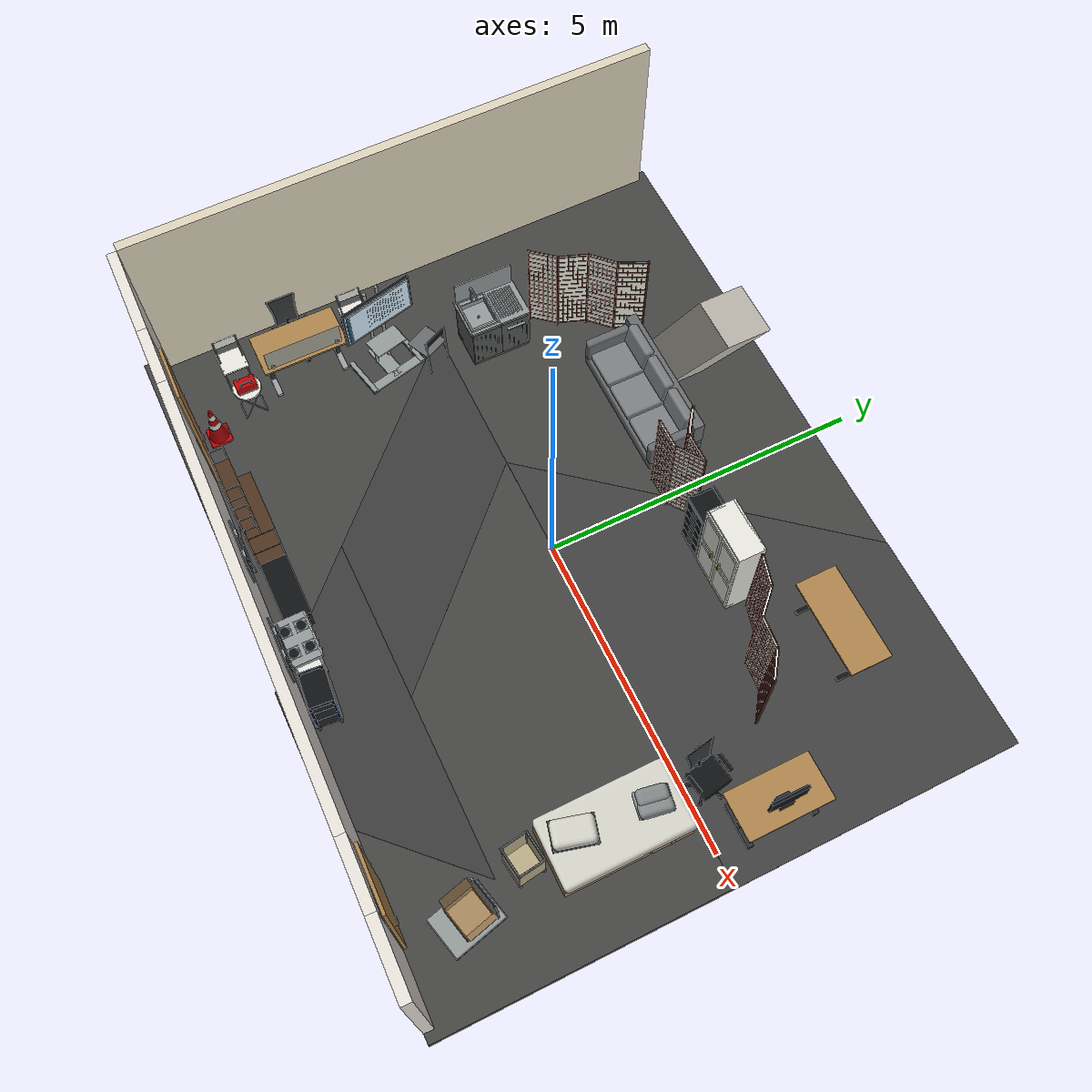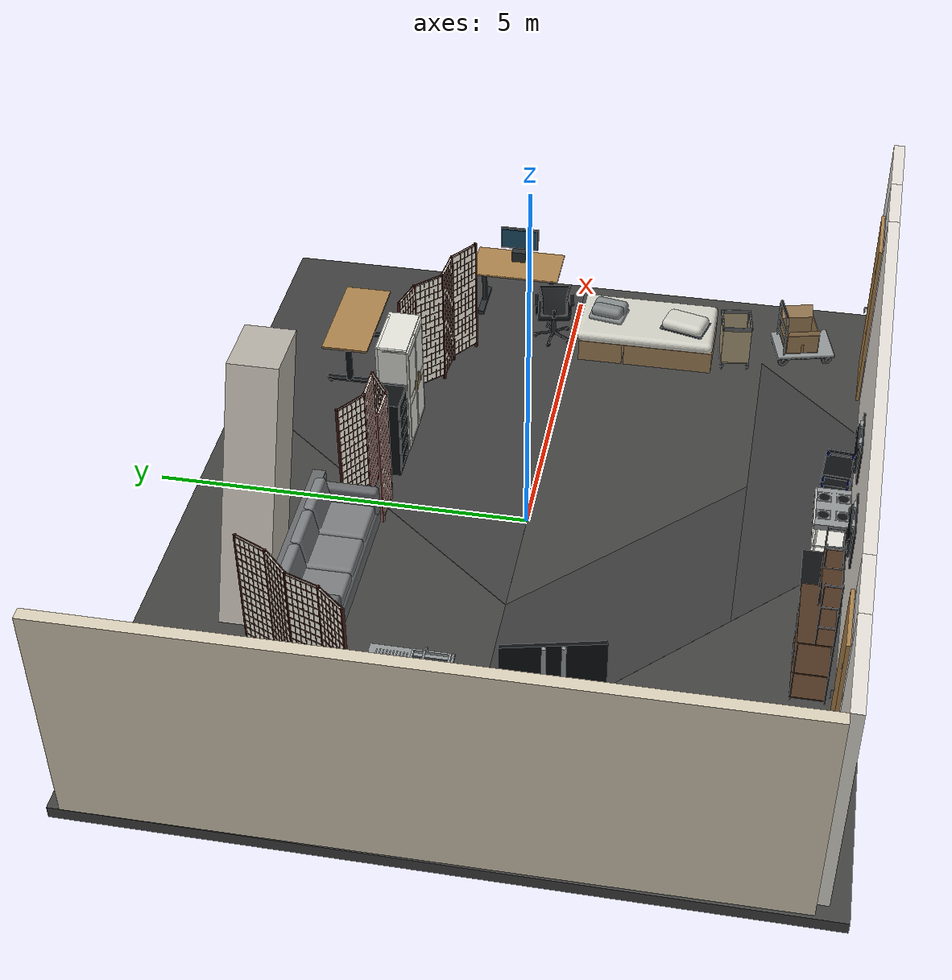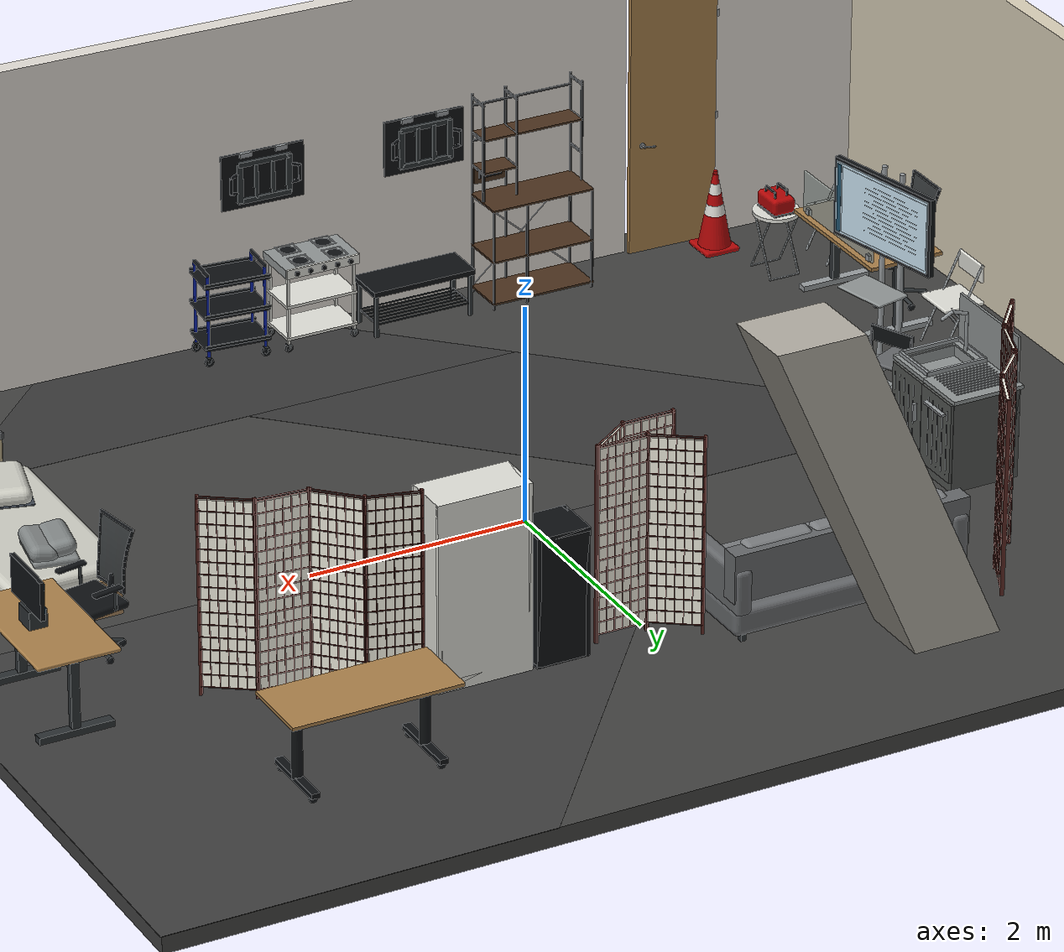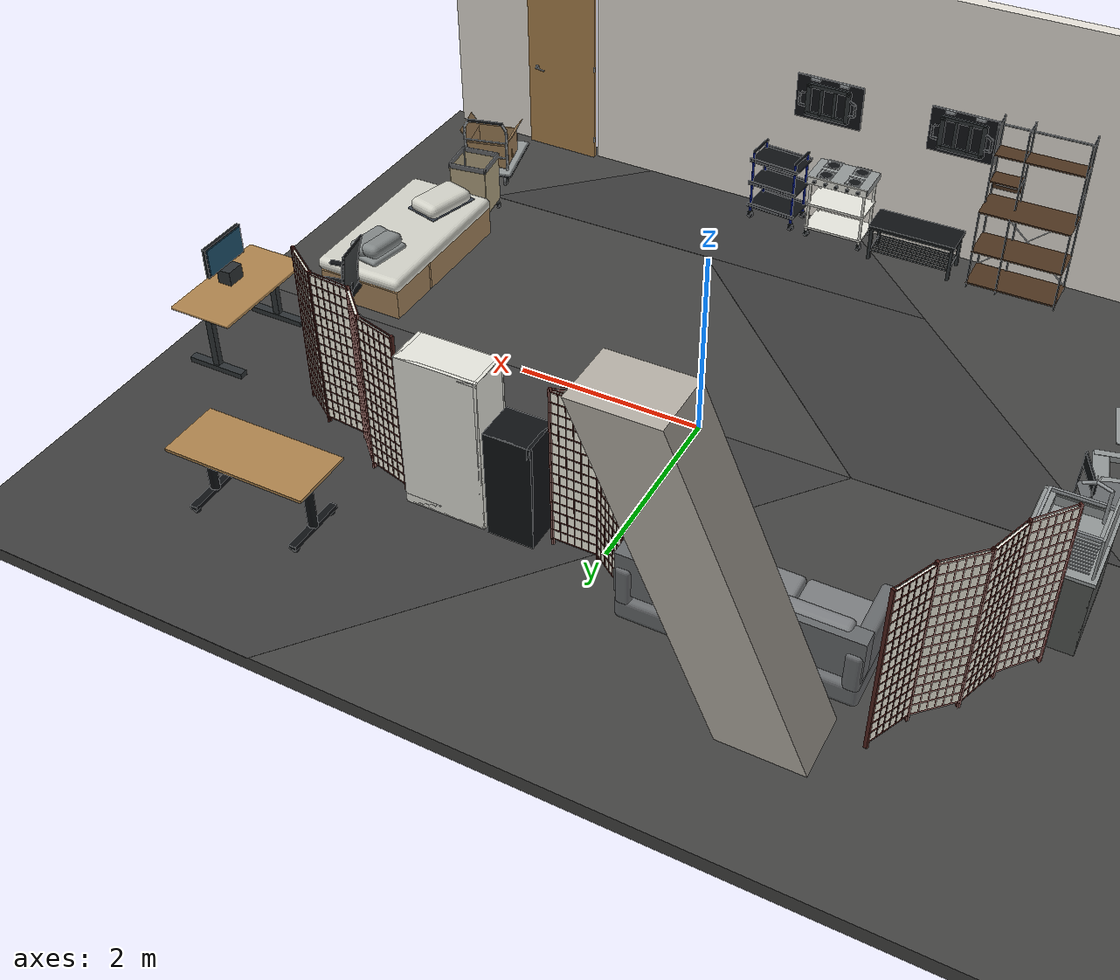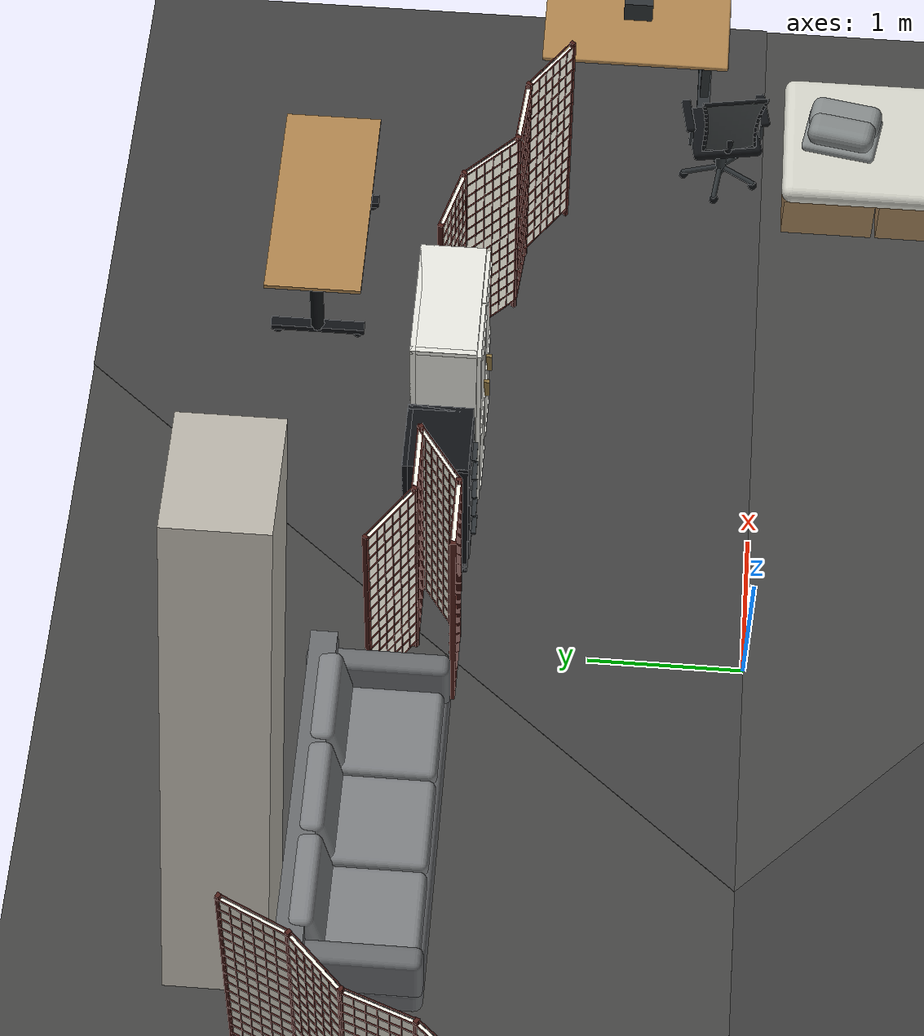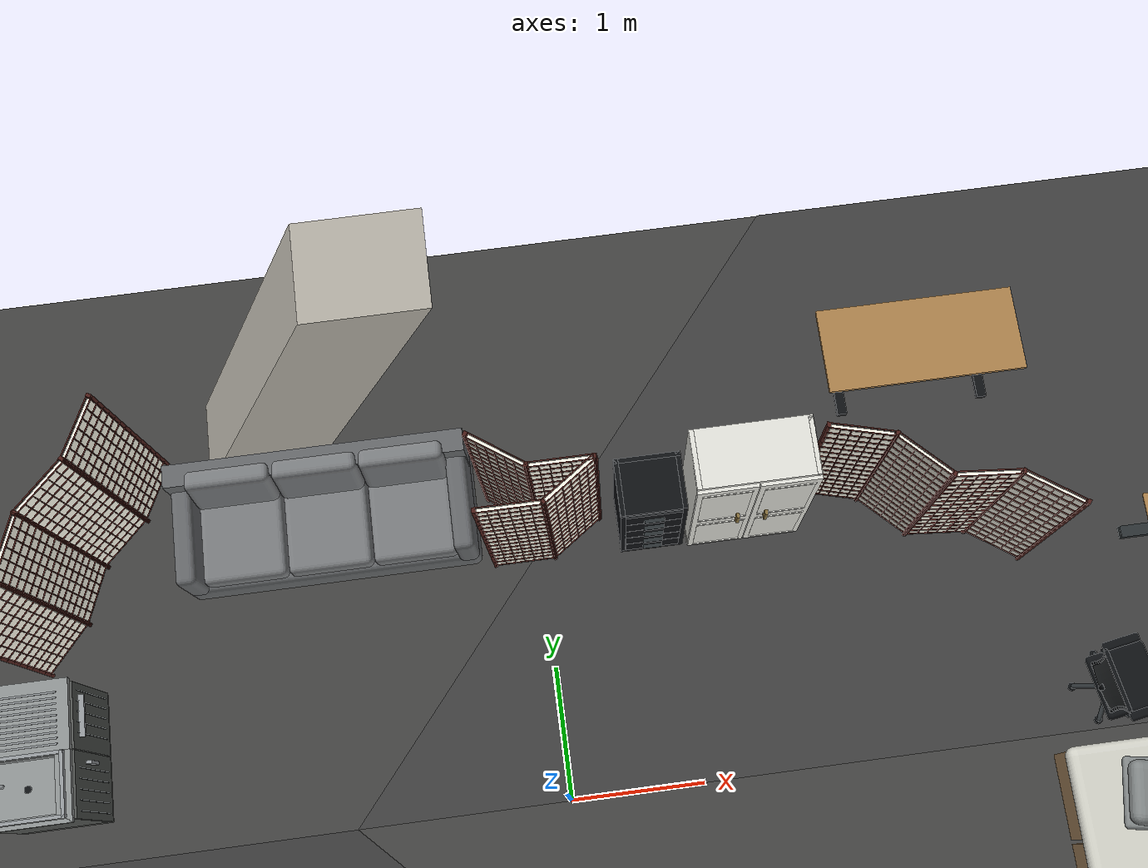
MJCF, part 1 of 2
<?xml version='1.0' encoding='utf-8'?>
<mujoco model="HaLab — image-based interactive reconstruction">
  <compiler angle="degree" autolimits="true" />
  <option timestep=".002" integrator="implicitfast" gravity="0 0 -9.81" cone="elliptic" iterations="60" />
  <size njmax="8000" nconmax="2000" />
  <statistic center="0 0 .8" extent="6.8" />
  <visual>
    <global offwidth="1600" offheight="1200" azimuth="125" elevation="-48" />
    <headlight ambient=".72 .72 .72" diffuse=".15 .15 .15" specular=".02 .02 .02" />
    <rgba haze=".12 .15 .19 1" />
  </visual>
  <default>
    <geom friction=".7 .01 .001" solref=".015 1" solimp=".95 .99 .001" condim="4" />
    <joint damping=".5" />
  </default>
  <asset>
    <material name="white" rgba=".89 .89 .86 1" specular=".15" shininess=".1" />
    <material name="wall" rgba=".88 .87 .81 1" specular=".15" shininess=".1" />
    <material name="north_paint" rgba=".90 .88 .85 1" specular=".15" shininess=".1" />
    <material name="west_paint" rgba=".86 .82 .73 1" specular=".15" shininess=".1" />
    <material name="oak" rgba=".68 .52 .31 1" specular=".15" shininess=".1" texture="oak_grain" />
    <material name="charcoal" rgba=".055 .065 .075 1" specular=".15" shininess=".1" />
    <material name="metal" rgba=".17 .19 .20 1" specular=".15" shininess=".1" />
    <material name="chair_mesh" rgba=".22 .235 .24 1" specular="0.02" shininess=".1" texture="chair_mesh_weave" texuniform="true" texrepeat="4 4" />
    <material name="panel_inset" rgba=".87 .87 .84 1" specular=".15" shininess=".1" />
    <material name="cream_canvas" rgba=".73 .67 .53 1" specular="0.02" shininess=".1" texture="cream_canvas_weave" texuniform="true" texrepeat="4 4" />
    <material name="piping" rgba=".25 .28 .32 1" specular=".15" shininess=".1" />
    <material name="screen_light" rgba=".81 .91 .97 1" specular=".15" shininess=".1" emission=".12" />
    <material name="sofa" rgba=".41 .42 .43 1" specular="0.02" shininess=".1" texture="sofa_weave" texuniform="true" texrepeat="4 4" />
    <material name="cushion" rgba=".49 .50 .51 1" specular="0.02" shininess=".1" texture="cushion_weave" texuniform="true" texrepeat="4 4" />
    <material name="brass" rgba=".53 .44 .24 1" specular=".15" shininess=".1" />
    <material name="screenframe" rgba=".30 .12 .10 1" specular=".15" shininess=".1" />
    <material name="paper" rgba=".98 .97 .91 1" specular=".15" shininess=".1" />
    <material name="display" rgba=".12 .32 .43 1" specular=".15" shininess=".1" />
    <material name="orange" rgba=".96 .17 .025 1" specular=".15" shininess=".1" />
    <material name="blue" rgba=".035 .12 .6 1" specular=".15" shininess=".1" />
    <material name="shelf_wood" rgba=".32 .225 .15 1" specular=".06" shininess=".1" texture="shelf_grain" />
    <material name="concrete" rgba=".72 .70 .66 1" specular="0.02" shininess=".1" texture="concrete_weave" texuniform="true" texrepeat="4 4" />
    <material name="chrome" rgba=".60 .62 .63 1" specular=".65" shininess=".5" />
    <material name="red" rgba=".72 .025 .025 1" specular="0.02" shininess=".1" texture="red_weave" texuniform="true" texrepeat="4 4" />
    <material name="cardboard" rgba=".65 .52 .36 1" specular=".15" shininess=".1" />
    <material name="tape" rgba=".66 .50 .28 1" specular=".15" shininess=".1" />
    <material name="linen" rgba=".83 .83 .79 1" specular="0.02" shininess=".1" texture="linen_weave" texuniform="true" texrepeat="4 4" />
    <material name="blanket" rgba=".52 .54 .54 1" specular="0.02" shininess=".1" texture="blanket_weave" texuniform="true" texrepeat="4 4" />
    <material name="frosted" rgba=".65 .68 .66 .86" specular=".15" shininess=".1" />
    <material name="sink" rgba=".32 .33 .32 1" specular=".15" shininess=".1" />
    <material name="steel" rgba=".57 .59 .59 1" specular=".65" shininess=".5" />
    <texture name="shelf_grain" type="2d" builtin="flat" rgb1=".94 .89 .81" mark="random" markrgb=".65 .59 .52" random=".35" width="32" height="512" />
    <texture name="sky" type="skybox" builtin="gradient" rgb1=".25 .29 .34" rgb2=".075 .095 .12" width="512" height="3072" />
    <texture name="carpet_tex" type="2d" builtin="flat" rgb1=".26 .26 .255" mark="random" markrgb=".39 .39 .38" random=".42" width="256" height="256" />
    <material name="carpet" texture="carpet_tex" texrepeat="3 3" texuniform="true" reflectance="0" specular="0" />
    <texture name="carpet_dark_tex" type="2d" builtin="flat" rgb1=".23 .23 .23" mark="random" markrgb=".32 .32 .32" random=".42" width="256" height="256" />
    <material name="carpet_dark" texture="carpet_dark_tex" texrepeat="3 3" texuniform="true" reflectance="0" specular="0" />
    <texture name="carpet_mid_tex" type="2d" builtin="flat" rgb1=".245 .245 .245" mark="random" markrgb=".35 .35 .35" random=".42" width="256" height="256" />
    <material name="carpet_mid" texture="carpet_mid_tex" texrepeat="3 3" texuniform="true" reflectance="0" specular="0" />
    <texture name="sofa_weave" type="2d" builtin="flat" rgb1=".98 .98 .98" mark="random" markrgb=".86 .86 .86" random=".28" width="128" height="128" />
    <texture name="cushion_weave" type="2d" builtin="flat" rgb1=".98 .98 .98" mark="random" markrgb=".86 .86 .86" random=".28" width="128" height="128" />
    <texture name="linen_weave" type="2d" builtin="flat" rgb1=".98 .98 .98" mark="random" markrgb=".86 .86 .86" random=".28" width="128" height="128" />
    <texture name="blanket_weave" type="2d" builtin="flat" rgb1=".98 .98 .98" mark="random" markrgb=".86 .86 .86" random=".28" width="128" height="128" />
    <texture name="red_weave" type="2d" builtin="flat" rgb1=".98 .98 .98" mark="random" markrgb=".86 .86 .86" random=".28" width="128" height="128" />
    <texture name="concrete_weave" type="2d" builtin="flat" rgb1=".98 .98 .98" mark="random" markrgb=".86 .86 .86" random=".28" width="128" height="128" />
    <texture name="cream_canvas_weave" type="2d" builtin="flat" rgb1=".98 .98 .98" mark="random" markrgb=".86 .86 .86" random=".28" width="128" height="128" />
    <texture name="chair_mesh_weave" type="2d" builtin="flat" rgb1=".98 .98 .98" mark="random" markrgb=".86 .86 .86" random=".28" width="128" height="128" />
    <texture name="oak_grain" type="2d" builtin="flat" rgb1=".99 .98 .96" mark="random" markrgb=".92 .90 .86" random=".22" width="128" height="1024" />
    <mesh name="floor_dark_diagonal_mesh" vertex="-1.4 -2.8 -0.003 1.2 -2.8 -0.003 -1.6 0 -0.003 -4.2 0 -0.003 -1.4 -2.8 0.001 1.2 -2.8 0.001 -1.6 0 0.001 -4.2 0 0.001" face="0 2 1 4 5 6 0 3 2 4 6 7 0 1 5 0 5 4 1 2 6 1 6 5 2 3 7 2 7 6 3 0 4 3 4 7" texcoord="-4.2 -8.4 3.6 -8.4 -4.8 0 -12.6 0 -4.2 -8.4 3.6 -8.4 -4.8 0 -12.6 0" />
    <mesh name="floor_wall_band_mesh" vertex="0.3 -4.5 -0.003 2.3 -4.5 -0.003 4 -2.8 -0.003 -1.4 -2.8 -0.003 0.3 -4.5 0.001 2.3 -4.5 0.001 4 -2.8 0.001 -1.4 -2.8 0.001" face="0 2 1 4 5 6 0 3 2 4 6 7 0 1 5 0 5 4 1 2 6 1 6 5 2 3 7 2 7 6 3 0 4 3 4 7" texcoord="0.9 -13.5 6.9 -13.5 12 -8.4 -4.2 -8.4 0.9 -13.5 6.9 -13.5 12 -8.4 -4.2 -8.4" />
    <mesh name="floor_mid_diagonal_mesh" vertex="-1.6 0 -0.003 5.5 0 -0.003 5.5 4.5 -0.003 2.1 4.5 -0.003 -1.6 0 0.001 5.5 0 0.001 5.5 4.5 0.001 2.1 4.5 0.001" face="0 2 1 4 5 6 0 3 2 4 6 7 0 1 5 0 5 4 1 2 6 1 6 5 2 3 7 2 7 6 3 0 4 3 4 7" texcoord="-4.8 0 16.5 0 16.5 13.5 6.3 13.5 -4.8 0 16.5 0 16.5 13.5 6.3 13.5" />
    <mesh name="sofa_base_mesh" vertex="-1.07675 -0.426754 -0.101754 -1.07756 -0.427559 -0.10008 -1.07979 -0.429785 -0.0945967 -1.08254 -0.432541 -0.0843662 -1.08389 -0.433891 -0.07 -1.08389 -0.433891 0 -1.08389 -0.433891 0.07 -1.08254 -0.432541 0.0843662 -1.07979 -0.429785 0.0945967 -1.07756 -0.427559 0.10008 -1.07675 -0.426754 0.101754 -1.07756 -0.42508 -0.102559 -1.07843 -0.425883 -0.100883 -1.08085 -0.428122 -0.0953504 -1.08389 -0.43093 -0.0848829 -1.0854 -0.432323 -0.07 -1.0854 -0.432323 0 -1.0854 -0.432323 0.07 -1.08389 -0.43093 0.0848829 -1.08085 -0.428122 0.0953504 -1.07843 -0.425883 0.100883 -1.07756 -0.42508 0.102559 -1.07979 -0.419597 -0.104785 -1.08085 -0.42035 -0.103122 -1.08389 -0.4225 -0.0975 -1.08786 -0.425309 -0.0864032 -1.08991 -0.426754 -0.07 -1.08991 -0.426754 0 -1.08991 -0.426754 0.07 -1.08786 -0.425309 0.0864032 -1.08389 -0.4225 0.0975 -1.08085 -0.42035 0.103122 -1.07979 -0.419597 0.104785 -1.08254 -0.409366 -0.107541 -1.08389 -0.409883 -0.10593 -1.08786 -0.411403 -0.100309 -1.09337 -0.413511 -0.0885106 -1.09637 -0.414657 -0.07 -1.09637 -0.414657 0 -1.09637 -0.414657 0.07 -1.09337 -0.413511 0.0885106 -1.08786 -0.411403 0.100309 -1.08389 -0.409883 0.10593 -1.08254 -0.409366 0.107541 -1.08389 -0.395 -0.108891 -1.0854 -0.395 -0.107323 -1.08991 -0.395 -0.101754 -1.09637 -0.395 -0.0896574 -1.1 -0.395 -0.07 -1.1 -0.395 0 -1.1 -0.395 0.07 -1.09637 -0.395 0.0896574 -1.08991 -0.395 0.101754 -1.0854 -0.395 0.107323 -1.08389 -0.395 0.108891 -1.08389 0 -0.108891 -1.0854 0 -0.107323 -1.08991 0 -0.101754 -1.09637 0 -0.0896574 -1.1 0 -0.07 -1.1 0 0 -1.1 0 0.07 -1.09637 0 0.0896574 -1.08991 0 0.101754 -1.0854 0 0.107323 -1.08389 0 0.108891 -1.08389 0.395 -0.108891 -1.0854 0.395 -0.107323 -1.08991 0.395 -0.101754 -1.09637 0.395 -0.0896574 -1.1 0.395 -0.07 -1.1 0.395 0 -1.1 0.395 0.07 -1.09637 0.395 0.0896574 -1.08991 0.395 0.101754 -1.0854 0.395 0.107323 -1.08389 0.395 0.108891 -1.08254 0.409366 -0.107541 -1.08389 0.409883 -0.10593 -1.08786 0.411403 -0.100309 -1.09337 0.413511 -0.0885106 -1.09637 0.414657 -0.07 -1.09637 0.414657 0 -1.09637 0.414657 0.07 -1.09337 0.413511 0.0885106 -1.08786 0.411403 0.100309 -1.08389 0.409883 0.10593 -1.08254 0.409366 0.107541 -1.07979 0.419597 -0.104785 -1.08085 0.42035 -0.103122 -1.08389 0.4225 -0.0975 -1.08786 0.425309 -0.0864032 -1.08991 0.426754 -0.07 -1.08991 0.426754 0 -1.08991 0.426754 0.07 -1.08786 0.425309 0.0864032 -1.08389 0.4225 0.0975 -1.08085 0.42035 0.103122 -1.07979 0.419597 0.104785 -1.07756 0.42508 -0.102559 -1.07843 0.425883 -0.100883 -1.08085 0.428122 -0.0953504 -1.08389 0.43093 -0.0848829 -1.0854 0.432323 -0.07 -1.0854 0.432323 0 -1.0854 0.432323 0.07 -1.08389 0.43093 0.0848829 -1.08085 0.428122 0.0953504 -1.07843 0.425883 0.100883 -1.07756 0.42508 0.102559 -1.07675 0.426754 -0.101754 -1.07756 0.427559 -0.10008 -1.07979 0.429785 -0.0945967 -1.08254 0.432541 -0.0843662 -1.08389 0.433891 -0.07 -1.08389 0.433891 0 -1.08389 0.433891 0.07 -1.08254 0.432541 0.0843662 -1.07979 0.429785 0.0945967 -1.07756 0.427559 0.10008 -1.07675 0.426754 0.101754 1.07675 -0.426754 -0.101754 1.07756 -0.427559 -0.10008 1.07979 -0.429785 -0.0945967 1.08254 -0.432541 -0.0843662 1.08389 -0.433891 -0.07 1.08389 -0.433891 0 1.08389 -0.433891 0.07 1.08254 -0.432541 0.0843662 1.07979 -0.429785 0.0945967 1.07756 -0.427559 0.10008 1.07675 -0.426754 0.101754 1.07756 -0.42508 -0.102559 1.07843 -0.425883 -0.100883 1.08085 -0.428122 -0.0953504 1.08389 -0.43093 -0.0848829 1.0854 -0.432323 -0.07 1.0854 -0.432323 0 1.0854 -0.432323 0.07 1.08389 -0.43093 0.0848829 1.08085 -0.428122 0.0953504 1.07843 -0.425883 0.100883 1.07756 -0.42508 0.102559 1.07979 -0.419597 -0.104785 1.08085 -0.42035 -0.103122 1.08389 -0.4225 -0.0975 1.08786 -0.425309 -0.0864032 1.08991 -0.426754 -0.07 1.08991 -0.426754 0 1.08991 -0.426754 0.07 1.08786 -0.425309 0.0864032 1.08389 -0.4225 0.0975 1.08085 -0.42035 0.103122 1.07979 -0.419597 0.104785 1.08254 -0.409366 -0.107541 1.08389 -0.409883 -0.10593 1.08786 -0.411403 -0.100309 1.09337 -0.413511 -0.0885106 1.09637 -0.414657 -0.07 1.09637 -0.414657 0 1.09637 -0.414657 0.07 1.09337 -0.413511 0.0885106 1.08786 -0.411403 0.100309 1.08389 -0.409883 0.10593 1.08254 -0.409366 0.107541 1.08389 -0.395 -0.108891 1.0854 -0.395 -0.107323 1.08991 -0.395 -0.101754 1.09637 -0.395 -0.0896574 1.1 -0.395 -0.07 1.1 -0.395 0 1.1 -0.395 0.07 1.09637 -0.395 0.0896574 1.08991 -0.395 0.101754 1.0854 -0.395 0.107323 1.08389 -0.395 0.108891 1.08389 0 -0.108891 1.0854 0 -0.107323 1.08991 0 -0.101754 1.09637 0 -0.0896574 1.1 0 -0.07 1.1 0 0 1.1 0 0.07 1.09637 0 0.0896574 1.08991 0 0.101754 1.0854 0 0.107323 1.08389 0 0.108891 1.08389 0.395 -0.108891 1.0854 0.395 -0.107323 1.08991 0.395 -0.101754 1.09637 0.395 -0.0896574 1.1 0.395 -0.07 1.1 0.395 0 1.1 0.395 0.07 1.09637 0.395 0.0896574 1.08991 0.395 0.101754 1.0854 0.395 0.107323 1.08389 0.395 0.108891 1.08254 0.409366 -0.107541 1.08389 0.409883 -0.10593 1.08786 0.411403 -0.100309 1.09337 0.413511 -0.0885106 1.09637 0.414657 -0.07 1.09637 0.414657 0 1.09637 0.414657 0.07 1.09337 0.413511 0.0885106 1.08786 0.411403 0.100309 1.08389 0.409883 0.10593 1.08254 0.409366 0.107541 1.07979 0.419597 -0.104785 1.08085 0.42035 -0.103122 1.08389 0.4225 -0.0975 1.08786 0.425309 -0.0864032 1.08991 0.426754 -0.07 1.08991 0.426754 0 1.08991 0.426754 0.07 1.08786 0.425309 0.0864032 1.08389 0.4225 0.0975 1.08085 0.42035 0.103122 1.07979 0.419597 0.104785 1.07756 0.42508 -0.102559 1.07843 0.425883 -0.100883 1.08085 0.428122 -0.0953504 1.08389 0.43093 -0.0848829 1.0854 0.432323 -0.07 1.0854 0.432323 0 1.0854 0.432323 0.07 1.08389 0.43093 0.0848829 1.08085 0.428122 0.0953504 1.07843 0.425883 0.100883 1.07756 0.42508 0.102559 1.07675 0.426754 -0.101754 1.07756 0.427559 -0.10008 1.07979 0.429785 -0.0945967 1.08254 0.432541 -0.0843662 1.08389 0.433891 -0.07 1.08389 0.433891 0 1.08389 0.433891 0.07 1.08254 0.432541 0.0843662 1.07979 0.429785 0.0945967 1.07756 0.427559 0.10008 1.07675 0.426754 0.101754 -1.07508 -0.427559 -0.102559 -1.0696 -0.429785 -0.104785 -1.05937 -0.432541 -0.107541 -1.045 -0.433891 -0.108891 0 -0.433891 -0.108891 1.045 -0.433891 -0.108891 1.05937 -0.432541 -0.107541 1.0696 -0.429785 -0.104785 1.07508 -0.427559 -0.102559 -1.07588 -0.428428 -0.100883 -1.07035 -0.430851 -0.103122 -1.05988 -0.433891 -0.10593 -1.045 -0.435398 -0.107323 0 -0.435398 -0.107323 1.045 -0.435398 -0.107323 1.05988 -0.433891 -0.10593 1.07035 -0.430851 -0.103122 1.07588 -0.428428 -0.100883 -1.07812 -0.430851 -0.0953504 -1.0725 -0.433891 -0.0975 -1.0614 -0.437864 -0.100309 -1.045 -0.439907 -0.101754 0 -0.439907 -0.101754 1.045 -0.439907 -0.101754 1.0614 -0.437864 -0.100309 1.0725 -0.433891 -0.0975 1.07812 -0.430851 -0.0953504 -1.08093 -0.433891 -0.0848829 -1.07531 -0.437864 -0.0864032 -1.06351 -0.443371 -0.0885106 -1.045 -0.446367 -0.0896574 0 -0.446367 -0.0896574 1.045 -0.446367 -0.0896574 1.06351 -0.443371 -0.0885106 1.07531 -0.437864 -0.0864032 1.08093 -0.433891 -0.0848829 -1.08232 -0.435398 -0.07 -1.07675 -0.439907 -0.07 -1.06466 -0.446367 -0.07 -1.045 -0.45 -0.07 0 -0.45 -0.07 1.045 -0.45 -0.07 1.06466 -0.446367 -0.07 1.07675 -0.439907 -0.07 1.08232 -0.435398 -0.07 -1.08232 -0.435398 0 -1.07675 -0.439907 0 -1.06466 -0.446367 0 -1.045 -0.45 0 0 -0.45 0 1.045 -0.45 0 1.06466 -0.446367 0 1.07675 -0.439907 0 1.08232 -0.435398 0 -1.08232 -0.435398 0.07 -1.07675 -0.439907 0.07 -1.06466 -0.446367 0.07 -1.045 -0.45 0.07 0 -0.45 0.07 1.045 -0.45 0.07 1.06466 -0.446367 0.07 1.07675 -0.439907 0.07 1.08232 -0.435398 0.07 -1.08093 -0.433891 0.0848829 -1.07531 -0.437864 0.0864032 -1.06351 -0.443371 0.0885106 -1.045 -0.446367 0.0896574 0 -0.446367 0.0896574 1.045 -0.446367 0.0896574 1.06351 -0.443371 0.0885106 1.07531 -0.437864 0.0864032 1.08093 -0.433891 0.0848829 -1.07812 -0.430851 0.0953504 -1.0725 -0.433891 0.0975 -1.0614 -0.437864 0.100309 -1.045 -0.439907 0.101754 0 -0.439907 0.101754 1.045 -0.439907 0.101754 1.0614 -0.437864 0.100309 1.0725 -0.433891 0.0975 1.07812 -0.430851 0.0953504 -1.07588 -0.428428 0.100883 -1.07035 -0.430851 0.103122 -1.05988 -0.433891 0.10593 -1.045 -0.435398 0.107323 0 -0.435398 0.107323 1.045 -0.435398 0.107323 1.05988 -0.433891 0.10593 1.07035 -0.430851 0.103122 1.07588 -0.428428 0.100883 -1.07508 -0.427559 0.102559 -1.0696 -0.429785 0.104785 -1.05937 -0.432541 0.107541 -1.045 -0.433891 0.108891 0 -0.433891 0.108891 1.045 -0.433891 0.108891 1.05937 -0.432541 0.107541 1.0696 -0.429785 0.104785 1.07508 -0.427559 0.102559 -1.07508 0.427559 -0.102559 -1.0696 0.429785 -0.104785 -1.05937 0.432541 -0.107541 -1.045 0.433891 -0.108891 0 0.433891 -0.108891 1.045 0.433891 -0.108891 1.05937 0.432541 -0.107541 1.0696 0.429785 -0.104785 1.07508 0.427559 -0.102559 -1.07588 0.428428 -0.100883 -1.07035 0.430851 -0.103122 -1.05988 0.433891 -0.10593 -1.045 0.435398 -0.107323 0 0.435398 -0.107323 1.045 0.435398 -0.107323 1.05988 0.433891 -0.10593 1.07035 0.430851 -0.103122 1.07588 0.428428 -0.100883 -1.07812 0.430851 -0.0953504 -1.0725 0.433891 -0.0975 -1.0614 0.437864 -0.100309 -1.045 0.439907 -0.101754 0 0.439907 -0.101754 1.045 0.439907 -0.101754 1.0614 0.437864 -0.100309 1.0725 0.433891 -0.0975 1.07812 0.430851 -0.0953504 -1.08093 0.433891 -0.0848829 -1.07531 0.437864 -0.0864032 -1.06351 0.443371 -0.0885106 -1.045 0.446367 -0.0896574 0 0.446367 -0.0896574 1.045 0.446367 -0.0896574 1.06351 0.443371 -0.0885106 1.07531 0.437864 -0.0864032 1.08093 0.433891 -0.0848829 -1.08232 0.435398 -0.07 -1.07675 0.439907 -0.07 -1.06466 0.446367 -0.07 -1.045 0.45 -0.07 0 0.45 -0.07 1.045 0.45 -0.07 1.06466 0.446367 -0.07 1.07675 0.439907 -0.07 1.08232 0.435398 -0.07 -1.08232 0.435398 0 -1.07675 0.439907 0 -1.06466 0.446367 0 -1.045 0.45 0 0 0.45 0 1.045 0.45 0 1.06466 0.446367 0 1.07675 0.439907 0 1.08232 0.435398 0 -1.08232 0.435398 0.07 -1.07675 0.439907 0.07 -1.06466 0.446367 0.07 -1.045 0.45 0.07 0 0.45 0.07 1.045 0.45 0.07 1.06466 0.446367 0.07 1.07675 0.439907 0.07 1.08232 0.435398 0.07 -1.08093 0.433891 0.0848829 -1.07531 0.437864 0.0864032 -1.06351 0.443371 0.0885106 -1.045 0.446367 0.0896574 0 0.446367 0.0896574 1.045 0.446367 0.0896574 1.06351 0.443371 0.0885106 1.07531 0.437864 0.0864032 1.08093 0.433891 0.0848829 -1.07812 0.430851 0.0953504 -1.0725 0.433891 0.0975 -1.0614 0.437864 0.100309 -1.045 0.439907 0.101754 0 0.439907 0.101754 1.045 0.439907 0.101754 1.0614 0.437864 0.100309 1.0725 0.433891 0.0975 1.07812 0.430851 0.0953504 -1.07588 0.428428 0.100883 -1.07035 0.430851 0.103122 -1.05988 0.433891 0.10593 -1.045 0.435398 0.107323 0 0.435398 0.107323 1.045 0.435398 0.107323 1.05988 0.433891 0.10593 1.07035 0.430851 0.103122 1.07588 0.428428 0.100883 -1.07508 0.427559 0.102559 -1.0696 0.429785 0.104785 -1.05937 0.432541 0.107541 -1.045 0.433891 0.108891 0 0.433891 0.108891 1.045 0.433891 0.108891 1.05937 0.432541 0.107541 1.0696 0.429785 0.104785 1.07508 0.427559 0.102559 -1.07588 -0.425883 -0.103428 -1.07812 -0.42035 -0.105851 -1.08093 -0.409883 -0.108891 -1.08232 -0.395 -0.110398 -1.08232 0 -0.110398 -1.08232 0.395 -0.110398 -1.08093 0.409883 -0.108891 -1.07812 0.42035 -0.105851 -1.07588 0.425883 -0.103428 -1.07035 -0.428122 -0.105851 -1.0725 -0.4225 -0.108891 -1.07531 -0.411403 -0.112864 -1.07675 -0.395 -0.114907 -1.07675 0 -0.114907 -1.07675 0.395 -0.114907 -1.07531 0.411403 -0.112864 -1.0725 0.4225 -0.108891 -1.07035 0.428122 -0.105851 -1.05988 -0.43093 -0.108891 -1.0614 -0.425309 -0.112864 -1.06351 -0.413511 -0.118371 -1.06466 -0.395 -0.121367 -1.06466 0 -0.121367 -1.06466 0.395 -0.121367 -1.06351 0.413511 -0.118371 -1.0614 0.425309 -0.112864 -1.05988 0.43093 -0.108891 -1.045 -0.432323 -0.110398 -1.045 -0.426754 -0.114907 -1.045 -0.414657 -0.121367 -1.045 -0.395 -0.125 -1.045 0 -0.125 -1.045 0.395 -0.125 -1.045 0.414657 -0.121367 -1.045 0.426754 -0.114907 -1.045 0.432323 -0.110398 0 -0.432323 -0.110398 0 -0.426754 -0.114907 0 -0.414657 -0.121367 0 -0.395 -0.125 0 0 -0.125 0 0.395 -0.125 0 0.414657 -0.121367 0 0.426754 -0.114907 0 0.432323 -0.110398 1.045 -0.432323 -0.110398 1.045 -0.426754 -0.114907 1.045 -0.414657 -0.121367 1.045 -0.395 -0.125 1.045 0 -0.125 1.045 0.395 -0.125 1.045 0.414657 -0.121367 1.045 0.426754 -0.114907 1.045 0.432323 -0.110398 1.05988 -0.43093 -0.108891 1.0614 -0.425309 -0.112864 1.06351 -0.413511 -0.118371 1.06466 -0.395 -0.121367 1.06466 0 -0.121367 1.06466 0.395 -0.121367 1.06351 0.413511 -0.118371 1.0614 0.425309 -0.112864 1.05988 0.43093 -0.108891 1.07035 -0.428122 -0.105851 1.0725 -0.4225 -0.108891 1.07531 -0.411403 -0.112864 1.07675 -0.395 -0.114907 1.07675 0 -0.114907 1.07675 0.395 -0.114907 1.07531 0.411403 -0.112864 1.0725 0.4225 -0.108891 1.07035 0.428122 -0.105851 1.07588 -0.425883 -0.103428 1.07812 -0.42035 -0.105851 1.08093 -0.409883 -0.108891 1.08232 -0.395 -0.110398 1.08232 0 -0.110398 1.08232 0.395 -0.110398 1.08093 0.409883 -0.108891 1.07812 0.42035 -0.105851 1.07588 0.425883 -0.103428 -1.07588 -0.425883 0.103428 -1.07812 -0.42035 0.105851 -1.08093 -0.409883 0.108891 -1.08232 -0.395 0.110398 -1.08232 0 0.110398 -1.08232 0.395 0.110398 -1.08093 0.409883 0.108891 -1.07812 0.42035 0.105851 -1.07588 0.425883 0.103428 -1.07035 -0.428122 0.105851 -1.0725 -0.4225 0.108891 -1.07531 -0.411403 0.112864 -1.07675 -0.395 0.114907 -1.07675 0 0.114907 -1.07675 0.395 0.114907 -1.07531 0.411403 0.112864 -1.0725 0.4225 0.108891 -1.07035 0.428122 0.105851 -1.05988 -0.43093 0.108891 -1.0614 -0.425309 0.112864 -1.06351 -0.413511 0.118371 -1.06466 -0.395 0.121367 -1.06466 0 0.121367 -1.06466 0.395 0.121367 -1.06351 0.413511 0.118371 -1.0614 0.425309 0.112864 -1.05988 0.43093 0.108891 -1.045 -0.432323 0.110398 -1.045 -0.426754 0.114907 -1.045 -0.414657 0.121367 -1.045 -0.395 0.125 -1.045 0 0.125 -1.045 0.395 0.125 -1.045 0.414657 0.121367 -1.045 0.426754 0.114907 -1.045 0.432323 0.110398 0 -0.432323 0.110398 0 -0.426754 0.114907 0 -0.414657 0.121367 0 -0.395 0.125 0 0 0.125 0 0.395 0.125 0 0.414657 0.121367 0 0.426754 0.114907 0 0.432323 0.110398 1.045 -0.432323 0.110398 1.045 -0.426754 0.114907 1.045 -0.414657 0.121367 1.045 -0.395 0.125 1.045 0 0.125 1.045 0.395 0.125 1.045 0.414657 0.121367 1.045 0.426754 0.114907 1.045 0.432323 0.110398 1.05988 -0.43093 0.108891 1.0614 -0.425309 0.112864 1.06351 -0.413511 0.118371 1.06466 -0.395 0.121367 1.06466 0 0.121367 1.06466 0.395 0.121367 1.06351 0.413511 0.118371 1.0614 0.425309 0.112864 1.05988 0.43093 0.108891 1.07035 -0.428122 0.105851 1.0725 -0.4225 0.108891 1.07531 -0.411403 0.112864 1.07675 -0.395 0.114907 1.07675 0 0.114907 1.07675 0.395 0.114907 1.07531 0.411403 0.112864 1.0725 0.4225 0.108891 1.07035 0.428122 0.105851 1.07588 -0.425883 0.103428 1.07812 -0.42035 0.105851 1.08093 -0.409883 0.108891 1.08232 -0.395 0.110398 1.08232 0 0.110398 1.08232 0.395 0.110398 1.08093 0.409883 0.108891 1.07812 0.42035 0.105851 1.07588 0.425883 0.103428" face="1 12 11 1 11 0 2 13 12 2 12 1 3 14 13 3 13 2 4 15 14 4 14 3 5 16 15 5 15 4 6 17 16 6 16 5 7 18 17 7 17 6 8 19 18 8 18 7 9 20 19 9 19 8 10 21 20 10 20 9 12 23 22 12 22 11 13 24 23 13 23 12 14 25 24 14 24 13 15 26 25 15 25 14 16 27 26 16 26 15 17 28 27 17 27 16 18 29 28 18 28 17 19 30 29 19 29 18 20 31 30 20 30 19 21 32 31 21 31 20 23 34 33 23 33 22 24 35 34 24 34 23 25 36 35 25 35 24 26 37 36 26 36 25 27 38 37 27 37 26 28 39 38 28 38 27 29 40 39 29 39 28 30 41 40 30 40 29 31 42 41 31 41 30 32 43 42 32 42 31 34 45 44 34 44 33 35 46 45 35 45 34 36 47 46 36 46 35 37 48 47 37 47 36 38 49 48 38 48 37 39 50 49 39 49 38 40 51 50 40 50 39 41 52 51 41 51 40 42 53 52 42 52 41 43 54 53 43 53 42 45 56 55 45 55 44 46 57 56 46 56 45 47 58 57 47 57 46 48 59 58 48 58 47 49 60 59 49 59 48 50 61 60 50 60 49 51 62 61 51 61 50 52 63 62 52 62 51 53 64 63 53 63 52 54 65 64 54 64 53 56 67 66 56 66 55 57 68 67 57 67 56 58 69 68 58 68 57 59 70 69 59 69 58 60 71 70 60 70 59 61 72 71 61 71 60 62 73 72 62 72 61 63 74 73 63 73 62 64 75 74 64 74 63 65 76 75 65 75 64 67 78 77 67 77 66 68 79 78 68 78 67 69 80 79 69 79 68 70 81 80 70 80 69 71 82 81 71 81 70 72 83 82 72 82 71 73 84 83 73 83 72 74 85 84 74 84 73 75 86 85 75 85 74 76 87 86 76 86 75 78 89 88 78 88 77 79 90 89 79 89 78 80 91 90 80 90 79 81 92 91 81 91 80 82 93 92 82 92 81 83 94 93 83 93 82 84 95 94 84 94 83 85 96 95 85 95 84 86 97 96 86 96 85 87 98 97 87 97 86 89 100 99 89 99 88 90 101 100 90 100 89 91 102 101 91 101 90 92 103 102 92 102 91 93 104 103 93 103 92 94 105 104 94 104 93 95 106 105 95 105 94 96 107 106 96 106 95 97 108 107 97 107 96 98 109 108 98 108 97 100 111 110 100 110 99 101 112 111 101 111 100 102 113 112 102 112 101 103 114 113 103 113 102 104 115 114 104 114 103 105 116 115 105 115 104 106 117 116 106 116 105 107 118 117 107 117 106 108 119 118 108 118 107 109 120 119 109 119 108 121 132 133 121 133 122 122 133 134 122 134 123 123 134 135 123 135 124 124 135 136 124 136 125 125 136 137 125 137 126 126 137 138 126 138 127 127 138 139 127 139 128 128 139 140 128 140 129 129 140 141 129 141 130 130 141 142 130 142 131 132 143 144 132 144 133 133 144 145 133 145 134 134 145 146 134 146 135 135 146 147 135 147 136 136 147 148 136 148 137 137 148 149 137 149 138 138 149 150 138 150 139 139 150 151 139 151 140 140 151 152 140 152 141 141 152 153 141 153 142 143 154 155 143 155 144 144 155 156 144 156 145 145 156 157 145 157 146 146 157 158 146 158 147 147 158 159 147 159 148 148 159 160 148 160 149 149 160 161 149 161 150 150 161 162 150 162 151 151 162 163 151 163 152 152 163 164 152 164 153 154 165 166 154 166 155 155 166 167 155 167 156 156 167 168 156 168 157 157 168 169 157 169 158 158 169 170 158 170 159 159 170 171 159 171 160 160 171 172 160 172 161 161 172 173 161 173 162 162 173 174 162 174 163 163 174 175 163 175 164 165 176 177 165 177 166 166 177 178 166 178 167 167 178 179 167 179 168 168 179 180 168 180 169 169 180 181 169 181 170 170 181 182 170 182 171 171 182 183 171 183 172 172 183 184 172 184 173 173 184 185 173 185 174 174 185 186 174 186 175 176 187 188 176 188 177 177 188 189 177 189 178 178 189 190 178 190 179 179 190 191 179 191 180 180 191 192 180 192 181 181 192 193 181 193 182 182 193 194 182 194 183 183 194 195 183 195 184 184 195 196 184 196 185 185 196 197 185 197 186 187 198 199 187 199 188 188 199 200 188 200 189 189 200 201 189 201 190 190 201 202 190 202 191 191 202 203 191 203 192 192 203 204 192 204 193 193 204 205 193 205 194 194 205 206 194 206 195 195 206 207 195 207 196 196 207 208 196 208 197 198 209 210 198 210 199 199 210 211 199 211 200 200 211 212 200 212 201 201 212 213 201 213 202 202 213 214 202 214 203 203 214 215 203 215 204 204 215 216 204 216 205 205 216 217 205 217 206 206 217 218 206 218 207 207 218 219 207 219 208 209 220 221 209 221 210 210 221 222 210 222 211 211 222 223 211 223 212 212 223 224 212 224 213 213 224 225 213 225 214 214 225 226 214 226 215 215 226 227 215 227 216 216 227 228 216 228 217 217 228 229 217 229 218 218 229 230 218 230 219 220 231 232 220 232 221 221 232 233 221 233 222 222 233 234 222 234 223 223 234 235 223 235 224 224 235 236 224 236 225 225 236 237 225 237 226 226 237 238 226 238 227 227 238 239 227 239 228 228 239 240 228 240 229 229 240 241 229 241 230 242 251 1 242 1 0 243 252 251 243 251 242 244 253 252 244 252 243 245 254 253 245 253 244 246 255 254 246 254 245 247 256 255 247 255 246 248 257 256 248 256 247 249 258 257 249 257 248 250 259 258 250 258 249 121 122 259 121 259 250 251 260 2 251 2 1 252 261 260 252 260 251 253 262 261 253 261 252 254 263 262 254 262 253 255 264 263 255 263 254 256 265 264 256 264 255 257 266 265 257 265 256 258 267 266 258 266 257 259 268 267 259 267 258 122 123 268 122 268 259 260 269 3 260 3 2 261 270 269 261 269 260 262 271 270 262 270 261 263 272 271 263 271 262 264 273 272 264 272 263 265 274 273 265 273 264 266 275 274 266 274 265 267 276 275 267 275 266 268 277 276 268 276 267 123 124 277 123 277 268 269 278 4 269 4 3 270 279 278 270 278 269 271 280 279 271 279 270 272 281 280 272 280 271 273 282 281 273 281 272 274 283 282 274 282 273 275 284 283 275 283 274 276 285 284 276 284 275 277 286 285 277 285 276 124 125 286 124 286 277 278 287 5 278 5 4 279 288 287 279 287 278 280 289 288 280 288 279 281 290 289 281 289 280 282 291 290 282 290 281 283 292 291 283 291 282 284 293 292 284 292 283 285 294 293 285 293 284 286 295 294 286 294 285 125 126 295 125 295 286 287 296 6 287 6 5 288 297 296 288 296 287 289 298 297 289 297 288 290 299 298 290 298 289 291 300 299 291 299 290 292 301 300 292 300 291 293 302 301 293 301 292 294 303 302 294 302 293 295 304 303 295 303 294 126 127 304 126 304 295 296 305 7 296 7 6 297 306 305 297 305 296 298 307 306 298 306 297 299 308 307 299 307 298 300 309 308 300 308 299 301 310 309 301 309 300 302 311 310 302 310 301 303 312 311 303 311 302 304 313 312 304 312 303 127 128 313 127 313 304 305 314 8 305 8 7 306 315 314 306 314 305 307 316 315 307 315 306 308 317 316 308 316 307 309 318 317 309 317 308 310 319 318 310 318 309 311 320 319 311 319 310 312 321 320 312 320 311 313 322 321 313 321 312 128 129 322 128 322 313 314 323 9 314 9 8 315 324 323 315 323 314 316 325 324 316 324 315 317 326 325 317 325 316 318 327 326 318 326 317 319 328 327 319 327 318 320 329 328 320 328 319 321 330 329 321 329 320 322 331 330 322 330 321 129 130 331 129 331 322 323 332 10 323 10 9 324 333 332 324 332 323 325 334 333 325 333 324 326 335 334 326 334 325 327 336 335 327 335 326 328 337 336 328 336 327 329 338 337 329 337 328 330 339 338 330 338 329 331 340 339 331 339 330 130 131 340 130 340 331 110 111 350 110 350 341 341 350 351 341 351 342 342 351 352 342 352 343 343 352 353 343 353 344 344 353 354 344 354 345 345 354 355 345 355 346 346 355 356 346 356 347 347 356 357 347 357 348 348 357 358 348 358 349 349 358 232 349 232 231 111 112 359 111 359 350 350 359 360 350 360 351 351 360 361 351 361 352 352 361 362 352 362 353 353 362 363 353 363 354 354 363 364 354 364 355 355 364 365 355 365 356 356 365 366 356 366 357 357 366 367 357 367 358 358 367 233 358 233 232 112 113 368 112 368 359 359 368 369 359 369 360 360 369 370 360 370 361 361 370 371 361 371 362 362 371 372 362 372 363 363 372 373 363 373 364 364 373 374 364 374 365 365 374 375 365 375 366 366 375 376 366 376 367 367 376 234 367 234 233 113 114 377 113 377 368 368 377 378 368 378 369 369 378 379 369 379 370 370 379 380 370 380 371 371 380 381 371 381 372 372 381 382 372 382 373 373 382 383 373 383 374 374 383 384 374 384 375 375 384 385 375 385 376 376 385 235 376 235 234 114 115 386 114 386 377 377 386 387 377 387 378 378 387 388 378 388 379 379 388 389 379 389 380 380 389 390 380 390 381 381 390 391 381 391 382 382 391 392 382 392 383 383 392 393 383 393 384 384 393 394 384 394 385 385 394 236 385 236 235 115 116 395 115 395 386 386 395 396 386 396 387 387 396 397 387 397 388 388 397 398 388 398 389 389 398 399 389 399 390 390 399 400 390 400 391 391 400 401 391 401 392 392 401 402 392 402 393 393 402 403 393 403 394 394 403 237 394 237 236 116 117 404 116 404 395 395 404 405 395 405 396 396 405 406 396 406 397 397 406 407 397 407 398 398 407 408 398 408 399 399 408 409 399 409 400 400 409 410 400 410 401 401 410 411 401 411 402 402 411 412 402 412 403 403 412 238 403 238 237 117 118 413 117 413 404 404 413 414 404 414 405 405 414 415 405 415 406 406 415 416 406 416 407 407 416 417 407 417 408 408 417 418 408 418 409 409 418 419 409 419 410 410 419 420 410 420 411 411 420 421 411 421 412 412 421 239 412 239 238 118 119 422 118 422 413 413 422 423 413 423 414 414 423 424 414 424 415 415 424 425 415 425 416 416 425 426 416 426 417 417 426 427 417 427 418 418 427 428 418 428 419 419 428 429 419 429 420 420 429 430 420 430 421 421 430 240 421 240 239 119 120 431 119 431 422 422 431 432 422 432 423 423 432 433 423 433 424 424 433 434 424 434 425 425 434 435 425 435 426 426 435 436 426 436 427 427 436 437 427 437 428 428 437 438 428 438 429 429 438 439 429 439 430 430 439 241 430 241 240 11 440 242 11 242 0 22 441 440 22 440 11 33 442 441 33 441 22 44 443 442 44 442 33 55 444 443 55 443 44 66 445 444 66 444 55 77 446 445 77 445 66 88 447 446 88 446 77 99 448 447 99 447 88 110 341 448 110 448 99 440 449 243 440 243 242 441 450 449 441 449 440 442 451 450 442 450 441 443 452 451 443 451 442 444 453 452 444 452 443 445 454 453 445 453 444 446 455 454 446 454 445 447 456 455 447 455 446 448 457 456 448 456 447 341 342 457 341 457 448 449 458 244 449 244 243 450 459 458 450 458 449 451 460 459 451 459 450 452 461 460 452 460 451 453 462 461 453 461 452 454 463 462 454 462 453 455 464 463 455 463 454 456 465 464 456 464 455 457 466 465 457 465 456 342 343 466 342 466 457 458 467 245 458 245 244 459 468 467 459 467 458 460 469 468 460 468 459 461 470 469 461 469 460 462 471 470 462 470 461 463 472 471 463 471 462 464 473 472 464 472 463 465 474 473 465 473 464 466 475 474 466 474 465 343 344 475 343 475 466 467 476 246 467 246 245 468 477 476 468 476 467 469 478 477 469 477 468 470 479 478 470 478 469 471 480 479 471 479 470 472 481 480 472 480 471 473 482 481 473 481 472 474 483 482 474 482 473 475 484 483 475 483 474 344 345 484 344 484 475 476 485 247 476 247 246 477 486 485 477 485 476 478 487 486 478 486 477 479 488 487 479 487 478 480 489 488 480 488 479 481 490 489 481 489 480 482 491 490 482 490 481 483 492 491 483 491 482 484 493 492 484 492 483 345 346 493 345 493 484 485 494 248 485 248 247 486 495 494 486 494 485 487 496 495 487 495 486 488 497 496 488 496 487 489 498 497 489 497 488 490 499 498 490 498 489 491 500 499 491 499 490 492 501 500 492 500 491 493 502 501 493 501 492 346 347 502 346 502 493 494 503 249 494 249 248 495 504 503 495 503 494 496 505 504 496 504 495 497 506 505 497 505 496 498 507 506 498 506 497 499 508 507 499 507 498 500 509 508 500 508 499 501 510 509 501 509 500 502 511 510 502 510 501 347 348 511 347 511 502 503 512 250 503 250 249 504 513 512 504 512 503 505 514 513 505 513 504 506 515 514 506 514 505 507 516 515 507 515 506 508 517 516 508 516 507 509 518 517 509 517 508 510 519 518 510 518 509 511 520 519 511 519 510 348 349 520 348 520 511 512 132 121 512 121 250 513 143 132 513 132 512 514 154 143 514 143 513 515 165 154 515 154 514 516 176 165 516 165 515 517 187 176 517 176 516 518 198 187 518 187 517 519 209 198 519 198 518 520 220 209 520 209 519 349 231 220 349 220 520 10 332 521 10 521 21 21 521 522 21 522 32 32 522 523 32 523 43 43 523 524 43 524 54 54 524 525 54 525 65 65 525 526 65 526 76 76 526 527 76 527 87 87 527 528 87 528 98 98 528 529 98 529 109 109 529 431 109 431 120 332 333 530 332 530 521 521 530 531 521 531 522 522 531 532 522 532 523 523 532 533 523 533 524 524 533 534 524 534 525 525 534 535 525 535 526 526 535 536 526 536 527 527 536 537 527 537 528 528 537 538 528 538 529 529 538 432 529 432 431 333 334 539 333 539 530 530 539 540 530 540 531 531 540 541 531 541 532 532 541 542 532 542 533 533 542 543 533 543 534 534 543 544 534 544 535 535 544 545 535 545 536 536 545 546 536 546 537 537 546 547 537 547 538 538 547 433 538 433 432 334 335 548 334 548 539 539 548 549 539 549 540 540 549 550 540 550 541 541 550 551 541 551 542 542 551 552 542 552 543 543 552 553 543 553 544 544 553 554 544 554 545 545 554 555 545 555 546 546 555 556 546 556 547 547 556 434 547 434 433 335 336 557 335 557 548 548 557 558 548 558 549 549 558 559 549 559 550 550 559 560 550 560 551 551 560 561 551 561 552 552 561 562 552 562 553 553 562 563 553 563 554 554 563 564 554 564 555 555 564 565 555 565 556 556 565 435 556 435 434 336 337 566 336 566 557 557 566 567 557 567 558 558 567 568 558 568 559 559 568 569 559 569 560 560 569 570 560 570 561 561 570 571 561 571 562 562 571 572 562 572 563 563 572 573 563 573 564 564 573 574 564 574 565 565 574 436 565 436 435 337 338 575 337 575 566 566 575 576 566 576 567 567 576 577 567 577 568 568 577 578 568 578 569 569 578 579 569 579 570 570 579 580 570 580 571 571 580 581 571 581 572 572 581 582 572 582 573 573 582 583 573 583 574 574 583 437 574 437 436 338 339 584 338 584 575 575 584 585 575 585 576 576 585 586 576 586 577 577 586 587 577 587 578 578 587 588 578 588 579 579 588 589 579 589 580 580 589 590 580 590 581 581 590 591 581 591 582 582 591 592 582 592 583 583 592 438 583 438 437 339 340 593 339 593 584 584 593 594 584 594 585 585 594 595 585 595 586 586 595 596 586 596 587 587 596 597 587 597 588 588 597 598 588 598 589 589 598 599 589 599 590 590 599 600 590 600 591 591 600 601 591 601 592 592 601 439 592 439 438 340 131 142 340 142 593 593 142 153 593 153 594 594 153 164 594 164 595 595 164 175 595 175 596 596 175 186 596 186 597 597 186 197 597 197 598 598 197 208 598 208 599 599 208 219 599 219 600 600 219 230 600 230 601 601 230 241 601 241 439" texcoord="0.0211325 0.237623 0.020401 0.249225 0.0183772 0.288148 0.0158721 0.363869 0.0146447 0.475798 0.0146447 1.0358 0.0146447 1.5958 0.0158721 1.71373 0.0183772 1.8017 0.020401 1.85051 0.0211325 1.86569 0.020401 0.234905 0.0196109 0.246525 0.0174082 0.285814 0.0146447 0.363314 0.0132745 0.479282 0.0132745 1.03928 0.0132745 1.59928 0.0146447 1.72144 0.0174082 1.81142 0.0196109 1.86066 0.020401 1.87585 0.0183772 0.229282 0.0174082 0.240912 0.0146447 0.281111 0.0110331 0.363643 0.00917517 0.491657 0.00917517 1.05166 0.00917517 1.61166 0.0110331 1.74609 0.0146447 1.84111 0.0174082 1.89086 0.0183772 1.90584 0.0158721 0.229972 0.0146447 0.241705 0.0110331 0.283297 0.00602674 0.373003 0.00330256 0.518539 0.00330256 1.07854 0.00330256 1.63854 0.00602674 1.78917 0.0110331 1.88824 0.0146447 1.93659 0.0158721 1.95062 0.0146447 0.251095 0.0132745 0.263639 0.00917517 0.308188 0.00330256 0.404963 0 0.562222 0 1.12222 0 1.68222 0.00330256 1.83948 0.00917517 1.93626 0.0132745 1.98081 0.0146447 1.99335 0.0146447 1.12887 0.0132745 1.14142 0.00917517 1.18597 0.00330256 1.28274 0 1.44 0 2 0 2.56 0.00330256 2.71726 0.00917517 2.81403 0.0132745 2.85858 0.0146447 2.87113 0.0146447 2.00665 0.0132745 2.01919 0.00917517 2.06374 0.00330256 2.16052 0 2.31778 0 2.87778 0 3.43778 0.00330256 3.59504 0.00917517 3.69181 0.0132745 3.73636 0.0146447 3.7489 0.0158721 2.04938 0.0146447 2.06341 0.0110331 2.11176 0.00602674 2.21083 0.00330256 2.36146 0.00330256 2.92146 0.00330256 3.48146 0.00602674 3.627 0.0110331 3.7167 0.0146447 3.75829 0.0158721 3.77003 0.0183772 2.09416 0.0174082 2.10914 0.0146447 2.15889 0.0110331 2.25391 0.00917517 2.38834 0.00917517 2.94834 0.00917517 3.50834 0.0110331 3.63636 0.0146447 3.71889 0.0174082 3.75909 0.0183772 3.77072 0.020401 2.12415 0.0196109 2.13934 0.0174082 2.18858 0.0146447 2.27856 0.0132745 2.40072 0.0132745 2.96072 0.0132745 3.52072 0.0146447 3.63669 0.0174082 3.71419 0.0196109 3.75347 0.020401 3.76509 0.0211325 2.13431 0.020401 2.14949 0.0183772 2.1983 0.0158721 2.28627 0.0146447 2.4042 0.0146447 2.9642 0.0146447 3.5242 0.0158721 3.63613 0.0183772 3.71185 0.020401 3.75077 0.0211325 3.76238 1.97887 0.237623 1.9796 0.249225 1.98162 0.288148 1.98413 0.363869 1.98536 0.475798 1.98536 1.0358 1.98536 1.5958 1.98413 1.71373 1.98162 1.8017 1.9796 1.85051 1.97887 1.86569 1.9796 0.234905 1.98039 0.246525 1.98259 0.285814 1.98536 0.363314 1.98673 0.479282 1.98673 1.03928 1.98673 1.59928 1.98536 1.72144 1.98259 1.81142 1.98039 1.86066 1.9796 1.87585 1.98162 0.229282 1.98259 0.240912 1.98536 0.281111 1.98897 0.363643 1.99082 0.491657 1.99082 1.05166 1.99082 1.61166 1.98897 1.74609 1.98536 1.84111 1.98259 1.89086 1.98162 1.90584 1.98413 0.229972 1.98536 0.241705 1.98897 0.283297 1.99397 0.373003 1.9967 0.518539 1.9967 1.07854 1.9967 1.63854 1.99397 1.78917 1.98897 1.88824 1.98536 1.93659 1.98413 1.95062 1.98536 0.251095 1.98673 0.263639 1.99082 0.308188 1.9967 0.404963 2 0.562222 2 1.12222 2 1.68222 1.9967 1.83948 1.99082 1.93626 1.98673 1.98081 1.98536 1.99335 1.98536 1.12887 1.98673 1.14142 1.99082 1.18597 1.9967 1.28274 2 1.44 2 2 2 2.56 1.9967 2.71726 1.99082 2.81403 1.98673 2.85858 1.98536 2.87113 1.98536 2.00665 1.98673 2.01919 1.99082 2.06374 1.9967 2.16052 2 2.31778 2 2.87778 2 3.43778 1.9967 3.59504 1.99082 3.69181 1.98673 3.73636 1.98536 3.7489 1.98413 2.04938 1.98536 2.06341 1.98897 2.11176 1.99397 2.21083 1.9967 2.36146 1.9967 2.92146 1.9967 3.48146 1.99397 3.627 1.98897 3.7167 1.98536 3.75829 1.98413 3.77003 1.98162 2.09416 1.98259 2.10914 1.98536 2.15889 1.98897 2.25391 1.99082 2.38834 1.99082 2.94834 1.99082 3.50834 1.98897 3.63636 1.98536 3.71889 1.98259 3.75909 1.98162 3.77072 1.9796 2.12415 1.98039 2.13934 1.98259 2.18858 1.98536 2.27856 1.98673 2.40072 1.98673 2.96072 1.98673 3.52072 1.98536 3.63669 1.98259 3.71419 1.98039 3.75347 1.9796 3.76509 1.97887 2.13431 1.9796 2.14949 1.98162 2.1983 1.98413 2.28627 1.98536 2.4042 1.98536 2.9642 1.98536 3.5242 1.98413 3.63613 1.98162 3.71185 1.9796 3.75077 1.97887 3.76238 0.0226541 0.229398 0.0276393 0.206642 0.0369398 0.178473 0.05 0.164671 1 0.164671 1.95 0.164671 1.96306 0.178473 1.97236 0.206642 1.97735 0.229398 0.0219242 0.240871 0.0269541 0.217578 0.0364701 0.188354 0.05 0.173866 1 0.173866 1.95 0.173866 1.96353 0.188354 1.97305 0.217578 1.97808 0.240871 0.0198891 0.27975 0.025 0.255798 0.035088 0.224496 0.05 0.208394 1 0.208394 1.95 0.208394 1.96491 0.224496 1.975 0.255798 1.98011 0.27975 0.0173359 0.356735 0.0224462 0.335744 0.0331722 0.306647 0.05 0.290814 1 0.290814 1.95 0.290814 1.96683 0.306647 1.97755 0.335744 1.98266 0.356735 0.0160701 0.472449 0.0211325 0.462428 0.0321297 0.448073 0.05 0.44 1 0.44 1.95 0.44 1.96787 0.448073 1.97887 0.462428 1.98393 0.472449 0.0160701 1.03245 0.0211325 1.02243 0.0321297 1.00807 0.05 1 1 1 1.95 1 1.96787 1.00807 1.97887 1.02243 1.98393 1.03245 0.0160701 1.59245 0.0211325 1.58243 0.0321297 1.56807 0.05 1.56 1 1.56 1.95 1.56 1.96787 1.56807 1.97887 1.58243 1.98393 1.59245 0.0173359 1.71486 0.0224462 1.7182 0.0331722 1.72282 0.05 1.72533 1 1.72533 1.95 1.72533 1.96683 1.72282 1.97755 1.7182 1.98266 1.71486 0.0198891 1.80536 0.025 1.8158 0.035088 1.82944 0.05 1.83646 1 1.83646 1.95 1.83646 1.96491 1.82944 1.975 1.8158 1.98011 1.80536 0.0219242 1.85501 0.0269541 1.86753 0.0364701 1.88324 0.05 1.89103 1 1.89103 1.95 1.89103 1.96353 1.88324 1.97305 1.86753 1.97808 1.85501 0.0226541 1.87034 0.0276393 1.8832 0.0369398 1.89912 0.05 1.90693 1 1.90693 1.95 1.90693 1.96306 1.89912 1.97236 1.8832 1.97735 1.87034 0.0226541 2.12966 0.0276393 2.1168 0.0369398 2.10088 0.05 2.09307 1 2.09307 1.95 2.09307 1.96306 2.10088 1.97236 2.1168 1.97735 2.12966 0.0219242 2.14499 0.0269541 2.13247 0.0364701 2.11676 0.05 2.10897 1 2.10897 1.95 2.10897 1.96353 2.11676 1.97305 2.13247 1.97808 2.14499 0.0198891 2.19464 0.025 2.1842 0.035088 2.17056 0.05 2.16354 1 2.16354 1.95 2.16354 1.96491 2.17056 1.975 2.1842 1.98011 2.19464 0.0173359 2.28514 0.0224462 2.2818 0.0331722 2.27718 0.05 2.27467 1 2.27467 1.95 2.27467 1.96683 2.27718 1.97755 2.2818 1.98266 2.28514 0.0160701 2.40755 0.0211325 2.41757 0.0321297 2.43193 0.05 2.44 1 2.44 1.95 2.44 1.96787 2.43193 1.97887 2.41757 1.98393 2.40755 0.0160701 2.96755 0.0211325 2.97757 0.0321297 2.99193 0.05 3 1 3 1.95 3 1.96787 2.99193 1.97887 2.97757 1.98393 2.96755 0.0160701 3.52755 0.0211325 3.53757 0.0321297 3.55193 0.05 3.56 1 3.56 1.95 3.56 1.96787 3.55193 1.97887 3.53757 1.98393 3.52755 0.0173359 3.64327 0.0224462 3.66426 0.0331722 3.69335 0.05 3.70919 1 3.70919 1.95 3.70919 1.96683 3.69335 1.97755 3.66426 1.98266 3.64327 0.0198891 3.72025 0.025 3.7442 0.035088 3.7755 0.05 3.79161 1 3.79161 1.95 3.79161 1.96491 3.7755 1.975 3.7442 1.98011 3.72025 0.0219242 3.75913 0.0269541 3.78242 0.0364701 3.81165 0.05 3.82613 1 3.82613 1.95 3.82613 1.96353 3.81165 1.97305 3.78242 1.97808 3.75913 0.0226541 3.7706 0.0276393 3.79336 0.0369398 3.82153 0.05 3.83533 1 3.83533 1.95 3.83533 1.96306 3.82153 1.97236 3.79336 1.97735 3.7706 0.0219242 0.226169 0.0198891 0.21908 0.0173359 0.218022 0.0160701 0.239038 0.0160701 1.11682 0.0160701 1.99459 0.0173359 2.03972 0.0198891 2.0873 0.0219242 2.11898 0.0269541 0.20181 0.025 0.189984 0.0224462 0.182862 0.0211325 0.202964 0.0211325 1.08074 0.0211325 1.95852 0.0224462 2.01132 0.025 2.06776 0.0269541 2.10457 0.0364701 0.17125 0.035088 0.15196 0.0331722 0.134123 0.0321297 0.151285 0.0321297 1.02906 0.0321297 1.90684 0.0331722 1.97195 0.035088 2.04222 0.0364701 2.0865 0.05 0.156098 0.05 0.132399 0.05 0.107602 0.05 0.122222 0.05 1 0.05 1.87778 0.05 1.95052 0.05 2.02908 0.05 2.07753 1 0.156098 1 0.132399 1 0.107602 1 0.122222 1 1 1 1.87778 1 1.95052 1 2.02908 1 2.07753 1.95 0.156098 1.95 0.132399 1.95 0.107602 1.95 0.122222 1.95 1 1.95 1.87778 1.95 1.95052 1.95 2.02908 1.95 2.07753 1.96353 0.17125 1.96491 0.15196 1.96683 0.134123 1.96787 0.151285 1.96787 1.02906 1.96787 1.90684 1.96683 1.97195 1.96491 2.04222 1.96353 2.0865 1.97305 0.20181 1.975 0.189984 1.97755 0.182862 1.97887 0.202964 1.97887 1.08074 1.97887 1.95852 1.97755 2.01132 1.975 2.06776 1.97305 2.10457 1.97808 0.226169 1.98011 0.21908 1.98266 0.218022 1.98393 0.239038 1.98393 1.11682 1.98393 1.99459 1.98266 2.03972 1.98011 2.0873 1.97808 2.11898 0.0219242 1.88102 0.0198891 1.9127 0.0173359 1.96028 0.0160701 2.00541 0.0160701 2.88318 0.0160701 3.76096 0.0173359 3.78198 0.0198891 3.78092 0.0219242 3.77383 0.0269541 1.89543 0.025 1.93224 0.0224462 1.98868 0.0211325 2.04148 0.0211325 2.91926 0.0211325 3.79704 0.0224462 3.81714 0.025 3.81002 0.0269541 3.79819 0.0364701 1.9135 0.035088 1.95778 0.0331722 2.02805 0.0321297 2.09316 0.0321297 2.97094 0.0321297 3.84872 0.0331722 3.86588 0.035088 3.84804 0.0364701 3.82875 0.05 1.92247 0.05 1.97092 0.05 2.04948 0.05 2.12222 0.05 3 0.05 3.87778 0.05 3.8924 0.05 3.8676 0.05 3.8439 1 1.92247 1 1.97092 1 2.04948 1 2.12222 1 3 1 3.87778 1 3.8924 1 3.8676 1 3.8439 1.95 1.92247 1.95 1.97092 1.95 2.04948 1.95 2.12222 1.95 3 1.95 3.87778 1.95 3.8924 1.95 3.8676 1.95 3.8439 1.96353 1.9135 1.96491 1.95778 1.96683 2.02805 1.96787 2.09316 1.96787 2.97094 1.96787 3.84872 1.96683 3.86588 1.96491 3.84804 1.96353 3.82875 1.97305 1.89543 1.975 1.93224 1.97755 1.98868 1.97887 2.04148 1.97887 2.91926 1.97887 3.79704 1.97755 3.81714 1.975 3.81002 1.97305 3.79819 1.97808 1.88102 1.98011 1.9127 1.98266 1.96028 1.98393 2.00541 1.98393 2.88318 1.98393 3.76096 1.98266 3.78198 1.98011 3.78092 1.97808 3.77383" />
    <mesh name="sofa_arm-1_mesh" vertex="-0.0584808 -0.430981 -0.195981 -0.0591391 -0.431639 -0.194611 -0.0609605 -0.43346 -0.190125 -0.0632151 -0.435715 -0.181754 -0.0643198 -0.43682 -0.17 -0.0643198 -0.43682 0 -0.0643198 -0.43682 0.17 -0.0632151 -0.435715 0.181754 -0.0609605 -0.43346 0.190125 -0.0591391 -0.431639 0.194611 -0.0584808 -0.430981 0.195981 -0.0591391 -0.429611 -0.196639 -0.0598502 -0.430268 -0.195268 -0.0618326 -0.4321 -0.190741 -0.0643198 -0.434398 -0.182177 -0.0655529 -0.435537 -0.17 -0.0655529 -0.435537 0 -0.0655529 -0.435537 0.17 -0.0643198 -0.434398 0.182177 -0.0618326 -0.4321 0.190741 -0.0598502 -0.430268 0.195268 -0.0591391 -0.429611 0.196639 -0.0609605 -0.425125 -0.19846 -0.0618326 -0.425741 -0.1971 -0.0643198 -0.4275 -0.1925 -0.0675702 -0.429798 -0.183421 -0.0692423 -0.430981 -0.17 -0.0692423 -0.430981 0 -0.0692423 -0.430981 0.17 -0.0675702 -0.429798 0.183421 -0.0643198 -0.4275 0.1925 -0.0618326 -0.425741 0.1971 -0.0609605 -0.425125 0.19846 -0.0632151 -0.416754 -0.200715 -0.0643198 -0.417177 -0.199398 -0.0675702 -0.418421 -0.194798 -0.0720759 -0.420145 -0.185145 -0.0745277 -0.421083 -0.17 -0.0745277 -0.421083 0 -0.0745277 -0.421083 0.17 -0.0720759 -0.420145 0.185145 -0.0675702 -0.418421 0.194798 -0.0643198 -0.417177 0.199398 -0.0632151 -0.416754 0.200715 -0.0643198 -0.405 -0.20182 -0.0655529 -0.405 -0.200537 -0.0692423 -0.405 -0.195981 -0.0745277 -0.405 -0.186083 -0.0775 -0.405 -0.17 -0.0775 -0.405 0 -0.0775 -0.405 0.17 -0.0745277 -0.405 0.186083 -0.0692423 -0.405 0.195981 -0.0655529 -0.405 0.200537 -0.0643198 -0.405 0.20182 -0.0643198 0 -0.20182 -0.0655529 0 -0.200537 -0.0692423 0 -0.195981 -0.0745277 0 -0.186083 -0.0775 0 -0.17 -0.0775 0 0 -0.0775 0 0.17 -0.0745277 0 0.186083 -0.0692423 0 0.195981 -0.0655529 0 0.200537 -0.0643198 0 0.20182 -0.0643198 0.405 -0.20182 -0.0655529 0.405 -0.200537 -0.0692423 0.405 -0.195981 -0.0745277 0.405 -0.186083 -0.0775 0.405 -0.17 -0.0775 0.405 0 -0.0775 0.405 0.17 -0.0745277 0.405 0.186083 -0.0692423 0.405 0.195981 -0.0655529 0.405 0.200537 -0.0643198 0.405 0.20182 -0.0632151 0.416754 -0.200715 -0.0643198 0.417177 -0.199398 -0.0675702 0.418421 -0.194798 -0.0720759 0.420145 -0.185145 -0.0745277 0.421083 -0.17 -0.0745277 0.421083 0 -0.0745277 0.421083 0.17 -0.0720759 0.420145 0.185145 -0.0675702 0.418421 0.194798 -0.0643198 0.417177 0.199398 -0.0632151 0.416754 0.200715 -0.0609605 0.425125 -0.19846 -0.0618326 0.425741 -0.1971 -0.0643198 0.4275 -0.1925 -0.0675702 0.429798 -0.183421 -0.0692423 0.430981 -0.17 -0.0692423 0.430981 0 -0.0692423 0.430981 0.17 -0.0675702 0.429798 0.183421 -0.0643198 0.4275 0.1925 -0.0618326 0.425741 0.1971 -0.0609605 0.425125 0.19846 -0.0591391 0.429611 -0.196639 -0.0598502 0.430268 -0.195268 -0.0618326 0.4321 -0.190741 -0.0643198 0.434398 -0.182177 -0.0655529 0.435537 -0.17 -0.0655529 0.435537 0 -0.0655529 0.435537 0.17 -0.0643198 0.434398 0.182177 -0.0618326 0.4321 0.190741 -0.0598502 0.430268 0.195268 -0.0591391 0.429611 0.196639 -0.0584808 0.430981 -0.195981 -0.0591391 0.431639 -0.194611 -0.0609605 0.43346 -0.190125 -0.0632151 0.435715 -0.181754 -0.0643198 0.43682 -0.17 -0.0643198 0.43682 0 -0.0643198 0.43682 0.17 -0.0632151 0.435715 0.181754 -0.0609605 0.43346 0.190125 -0.0591391 0.431639 0.194611 -0.0584808 0.430981 0.195981 0.0584808 -0.430981 -0.195981 0.0591391 -0.431639 -0.194611 0.0609605 -0.43346 -0.190125 0.0632151 -0.435715 -0.181754 0.0643198 -0.43682 -0.17 0.0643198 -0.43682 0 0.0643198 -0.43682 0.17 0.0632151 -0.435715 0.181754 0.0609605 -0.43346 0.190125 0.0591391 -0.431639 0.194611 0.0584808 -0.430981 0.195981 0.0591391 -0.429611 -0.196639 0.0598502 -0.430268 -0.195268 0.0618326 -0.4321 -0.190741 0.0643198 -0.434398 -0.182177 0.0655529 -0.435537 -0.17 0.0655529 -0.435537 0 0.0655529 -0.435537 0.17 0.0643198 -0.434398 0.182177 0.0618326 -0.4321 0.190741 0.0598502 -0.430268 0.195268 0.0591391 -0.429611 0.196639 0.0609605 -0.425125 -0.19846 0.0618326 -0.425741 -0.1971 0.0643198 -0.4275 -0.1925 0.0675702 -0.429798 -0.183421 0.0692423 -0.430981 -0.17 0.0692423 -0.430981 0 0.0692423 -0.430981 0.17 0.0675702 -0.429798 0.183421 0.0643198 -0.4275 0.1925 0.0618326 -0.425741 0.1971 0.0609605 -0.425125 0.19846 0.0632151 -0.416754 -0.200715 0.0643198 -0.417177 -0.199398 0.0675702 -0.418421 -0.194798 0.0720759 -0.420145 -0.185145 0.0745277 -0.421083 -0.17 0.0745277 -0.421083 0 0.0745277 -0.421083 0.17 0.0720759 -0.420145 0.185145 0.0675702 -0.418421 0.194798 0.0643198 -0.417177 0.199398 0.0632151 -0.416754 0.200715 0.0643198 -0.405 -0.20182 0.0655529 -0.405 -0.200537 0.0692423 -0.405 -0.195981 0.0745277 -0.405 -0.186083 0.0775 -0.405 -0.17 0.0775 -0.405 0 0.0775 -0.405 0.17 0.0745277 -0.405 0.186083 0.0692423 -0.405 0.195981 0.0655529 -0.405 0.200537 0.0643198 -0.405 0.20182 0.0643198 0 -0.20182 0.0655529 0 -0.200537 0.0692423 0 -0.195981 0.0745277 0 -0.186083 0.0775 0 -0.17 0.0775 0 0 0.0775 0 0.17 0.0745277 0 0.186083 0.0692423 0 0.195981 0.0655529 0 0.200537 0.0643198 0 0.20182 0.0643198 0.405 -0.20182 0.0655529 0.405 -0.200537 0.0692423 0.405 -0.195981 0.0745277 0.405 -0.186083 0.0775 0.405 -0.17 0.0775 0.405 0 0.0775 0.405 0.17 0.0745277 0.405 0.186083 0.0692423 0.405 0.195981 0.0655529 0.405 0.200537 0.0643198 0.405 0.20182 0.0632151 0.416754 -0.200715 0.0643198 0.417177 -0.199398 0.0675702 0.418421 -0.194798 0.0720759 0.420145 -0.185145 0.0745277 0.421083 -0.17 0.0745277 0.421083 0 0.0745277 0.421083 0.17 0.0720759 0.420145 0.185145 0.0675702 0.418421 0.194798 0.0643198 0.417177 0.199398 0.0632151 0.416754 0.200715 0.0609605 0.425125 -0.19846 0.0618326 0.425741 -0.1971 0.0643198 0.4275 -0.1925 0.0675702 0.429798 -0.183421 0.0692423 0.430981 -0.17 0.0692423 0.430981 0 0.0692423 0.430981 0.17 0.0675702 0.429798 0.183421 0.0643198 0.4275 0.1925 0.0618326 0.425741 0.1971 0.0609605 0.425125 0.19846 0.0591391 0.429611 -0.196639 0.0598502 0.430268 -0.195268 0.0618326 0.4321 -0.190741 0.0643198 0.434398 -0.182177 0.0655529 0.435537 -0.17 0.0655529 0.435537 0 0.0655529 0.435537 0.17 0.0643198 0.434398 0.182177 0.0618326 0.4321 0.190741 0.0598502 0.430268 0.195268 0.0591391 0.429611 0.196639 0.0584808 0.430981 -0.195981 0.0591391 0.431639 -0.194611 0.0609605 0.43346 -0.190125 0.0632151 0.435715 -0.181754 0.0643198 0.43682 -0.17 0.0643198 0.43682 0 0.0643198 0.43682 0.17 0.0632151 0.435715 0.181754 0.0609605 0.43346 0.190125 0.0591391 0.431639 0.194611 0.0584808 0.430981 0.195981 -0.0571113 -0.431639 -0.196639 -0.0526246 -0.43346 -0.19846 -0.0442542 -0.435715 -0.200715 -0.0325 -0.43682 -0.20182 0 -0.43682 -0.20182 0.0325 -0.43682 -0.20182 0.0442542 -0.435715 -0.200715 0.0526246 -0.43346 -0.19846 0.0571113 -0.431639 -0.196639 -0.0577683 -0.43235 -0.195268 -0.0532413 -0.434333 -0.1971 -0.0446769 -0.43682 -0.199398 -0.0325 -0.438053 -0.200537 0 -0.438053 -0.200537 0.0325 -0.438053 -0.200537 0.0446769 -0.43682 -0.199398 0.0532413 -0.434333 -0.1971 0.0577683 -0.43235 -0.195268 -0.0595998 -0.434333 -0.190741 -0.055 -0.43682 -0.1925 -0.0459208 -0.44007 -0.194798 -0.0325 -0.441742 -0.195981 0 -0.441742 -0.195981 0.0325 -0.441742 -0.195981 0.0459208 -0.44007 -0.194798 0.055 -0.43682 -0.1925 0.0595998 -0.434333 -0.190741 -0.0618977 -0.43682 -0.182177 -0.0572984 -0.44007 -0.183421 -0.0476451 -0.444576 -0.185145 -0.0325 -0.447028 -0.186083 0 -0.447028 -0.186083 0.0325 -0.447028 -0.186083 0.0476451 -0.444576 -0.185145 0.0572984 -0.44007 -0.183421 0.0618977 -0.43682 -0.182177 -0.0630369 -0.438053 -0.17 -0.0584808 -0.441742 -0.17 -0.0485833 -0.447028 -0.17 -0.0325 -0.45 -0.17 0 -0.45 -0.17 0.0325 -0.45 -0.17 0.0485833 -0.447028 -0.17 0.0584808 -0.441742 -0.17 0.0630369 -0.438053 -0.17 -0.0630369 -0.438053 0 -0.0584808 -0.441742 0 -0.0485833 -0.447028 0 -0.0325 -0.45 0 0 -0.45 0 0.0325 -0.45 0 0.0485833 -0.447028 0 0.0584808 -0.441742 0 0.0630369 -0.438053 0 -0.0630369 -0.438053 0.17 -0.0584808 -0.441742 0.17 -0.0485833 -0.447028 0.17 -0.0325 -0.45 0.17 0 -0.45 0.17 0.0325 -0.45 0.17 0.0485833 -0.447028 0.17 0.0584808 -0.441742 0.17 0.0630369 -0.438053 0.17 -0.0618977 -0.43682 0.182177 -0.0572984 -0.44007 0.183421 -0.0476451 -0.444576 0.185145 -0.0325 -0.447028 0.186083 0 -0.447028 0.186083 0.0325 -0.447028 0.186083 0.0476451 -0.444576 0.185145 0.0572984 -0.44007 0.183421 0.0618977 -0.43682 0.182177 -0.0595998 -0.434333 0.190741 -0.055 -0.43682 0.1925 -0.0459208 -0.44007 0.194798 -0.0325 -0.441742 0.195981 0 -0.441742 0.195981 0.0325 -0.441742 0.195981 0.0459208 -0.44007 0.194798 0.055 -0.43682 0.1925 0.0595998 -0.434333 0.190741 -0.0577683 -0.43235 0.195268 -0.0532413 -0.434333 0.1971 -0.0446769 -0.43682 0.199398 -0.0325 -0.438053 0.200537 0 -0.438053 0.200537 0.0325 -0.438053 0.200537 0.0446769 -0.43682 0.199398 0.0532413 -0.434333 0.1971 0.0577683 -0.43235 0.195268 -0.0571113 -0.431639 0.196639 -0.0526246 -0.43346 0.19846 -0.0442542 -0.435715 0.200715 -0.0325 -0.43682 0.20182 0 -0.43682 0.20182 0.0325 -0.43682 0.20182 0.0442542 -0.435715 0.200715 0.0526246 -0.43346 0.19846 0.0571113 -0.431639 0.196639 -0.0571113 0.431639 -0.196639 -0.0526246 0.43346 -0.19846 -0.0442542 0.435715 -0.200715 -0.0325 0.43682 -0.20182 0 0.43682 -0.20182 0.0325 0.43682 -0.20182 0.0442542 0.435715 -0.200715 0.0526246 0.43346 -0.19846 0.0571113 0.431639 -0.196639 -0.0577683 0.43235 -0.195268 -0.0532413 0.434333 -0.1971 -0.0446769 0.43682 -0.199398 -0.0325 0.438053 -0.200537 0 0.438053 -0.200537 0.0325 0.438053 -0.200537 0.0446769 0.43682 -0.199398 0.0532413 0.434333 -0.1971 0.0577683 0.43235 -0.195268 -0.0595998 0.434333 -0.190741 -0.055 0.43682 -0.1925 -0.0459208 0.44007 -0.194798 -0.0325 0.441742 -0.195981 0 0.441742 -0.195981 0.0325 0.441742 -0.195981 0.0459208 0.44007 -0.194798 0.055 0.43682 -0.1925 0.0595998 0.434333 -0.190741 -0.0618977 0.43682 -0.182177 -0.0572984 0.44007 -0.183421 -0.0476451 0.444576 -0.185145 -0.0325 0.447028 -0.186083 0 0.447028 -0.186083 0.0325 0.447028 -0.186083 0.0476451 0.444576 -0.185145 0.0572984 0.44007 -0.183421 0.0618977 0.43682 -0.182177 -0.0630369 0.438053 -0.17 -0.0584808 0.441742 -0.17 -0.0485833 0.447028 -0.17 -0.0325 0.45 -0.17 0 0.45 -0.17 0.0325 0.45 -0.17 0.0485833 0.447028 -0.17 0.0584808 0.441742 -0.17 0.0630369 0.438053 -0.17 -0.0630369 0.438053 0 -0.0584808 0.441742 0 -0.0485833 0.447028 0 -0.0325 0.45 0 0 0.45 0 0.0325 0.45 0 0.0485833 0.447028 0 0.0584808 0.441742 0 0.0630369 0.438053 0 -0.0630369 0.438053 0.17 -0.0584808 0.441742 0.17 -0.0485833 0.447028 0.17 -0.0325 0.45 0.17 0 0.45 0.17 0.0325 0.45 0.17 0.0485833 0.447028 0.17 0.0584808 0.441742 0.17 0.0630369 0.438053 0.17 -0.0618977 0.43682 0.182177 -0.0572984 0.44007 0.183421 -0.0476451 0.444576 0.185145 -0.0325 0.447028 0.186083 0 0.447028 0.186083 0.0325 0.447028 0.186083 0.0476451 0.444576 0.185145 0.0572984 0.44007 0.183421 0.0618977 0.43682 0.182177 -0.0595998 0.434333 0.190741 -0.055 0.43682 0.1925 -0.0459208 0.44007 0.194798 -0.0325 0.441742 0.195981 0 0.441742 0.195981 0.0325 0.441742 0.195981 0.0459208 0.44007 0.194798 0.055 0.43682 0.1925 0.0595998 0.434333 0.190741 -0.0577683 0.43235 0.195268 -0.0532413 0.434333 0.1971 -0.0446769 0.43682 0.199398 -0.0325 0.438053 0.200537 0 0.438053 0.200537 0.0325 0.438053 0.200537 0.0446769 0.43682 0.199398 0.0532413 0.434333 0.1971 0.0577683 0.43235 0.195268 -0.0571113 0.431639 0.196639 -0.0526246 0.43346 0.19846 -0.0442542 0.435715 0.200715 -0.0325 0.43682 0.20182 0 0.43682 0.20182 0.0325 0.43682 0.20182 0.0442542 0.435715 0.200715 0.0526246 0.43346 0.19846 0.0571113 0.431639 0.196639 -0.0577683 -0.430268 -0.19735 -0.0595998 -0.425741 -0.199333 -0.0618977 -0.417177 -0.20182 -0.0630369 -0.405 -0.203053 -0.0630369 0 -0.203053 -0.0630369 0.405 -0.203053 -0.0618977 0.417177 -0.20182 -0.0595998 0.425741 -0.199333 -0.0577683 0.430268 -0.19735 -0.0532413 -0.4321 -0.199333 -0.055 -0.4275 -0.20182 -0.0572984 -0.418421 -0.20507 -0.0584808 -0.405 -0.206742 -0.0584808 0 -0.206742 -0.0584808 0.405 -0.206742 -0.0572984 0.418421 -0.20507 -0.055 0.4275 -0.20182 -0.0532413 0.4321 -0.199333 -0.0446769 -0.434398 -0.20182 -0.0459208 -0.429798 -0.20507 -0.0476451 -0.420145 -0.209576 -0.0485833 -0.405 -0.212028 -0.0485833 0 -0.212028 -0.0485833 0.405 -0.212028 -0.0476451 0.420145 -0.209576 -0.0459208 0.429798 -0.20507 -0.0446769 0.434398 -0.20182 -0.0325 -0.435537 -0.203053 -0.0325 -0.430981 -0.206742 -0.0325 -0.421083 -0.212028 -0.0325 -0.405 -0.215 -0.0325 0 -0.215 -0.0325 0.405 -0.215 -0.0325 0.421083 -0.212028 -0.0325 0.430981 -0.206742 -0.0325 0.435537 -0.203053 0 -0.435537 -0.203053 0 -0.430981 -0.206742 0 -0.421083 -0.212028 0 -0.405 -0.215 0 0 -0.215 0 0.405 -0.215 0 0.421083 -0.212028 0 0.430981 -0.206742 0 0.435537 -0.203053 0.0325 -0.435537 -0.203053 0.0325 -0.430981 -0.206742 0.0325 -0.421083 -0.212028 0.0325 -0.405 -0.215 0.0325 0 -0.215 0.0325 0.405 -0.215 0.0325 0.421083 -0.212028 0.0325 0.430981 -0.206742 0.0325 0.435537 -0.203053 0.0446769 -0.434398 -0.20182 0.0459208 -0.429798 -0.20507 0.0476451 -0.420145 -0.209576 0.0485833 -0.405 -0.212028 0.0485833 0 -0.212028 0.0485833 0.405 -0.212028 0.0476451 0.420145 -0.209576 0.0459208 0.429798 -0.20507 0.0446769 0.434398 -0.20182 0.0532413 -0.4321 -0.199333 0.055 -0.4275 -0.20182 0.0572984 -0.418421 -0.20507 0.0584808 -0.405 -0.206742 0.0584808 0 -0.206742 0.0584808 0.405 -0.206742 0.0572984 0.418421 -0.20507 0.055 0.4275 -0.20182 0.0532413 0.4321 -0.199333 0.0577683 -0.430268 -0.19735 0.0595998 -0.425741 -0.199333 0.0618977 -0.417177 -0.20182 0.0630369 -0.405 -0.203053 0.0630369 0 -0.203053 0.0630369 0.405 -0.203053 0.0618977 0.417177 -0.20182 0.0595998 0.425741 -0.199333 0.0577683 0.430268 -0.19735 -0.0577683 -0.430268 0.19735 -0.0595998 -0.425741 0.199333 -0.0618977 -0.417177 0.20182 -0.0630369 -0.405 0.203053 -0.0630369 0 0.203053 -0.0630369 0.405 0.203053 -0.0618977 0.417177 0.20182 -0.0595998 0.425741 0.199333 -0.0577683 0.430268 0.19735 -0.0532413 -0.4321 0.199333 -0.055 -0.4275 0.20182 -0.0572984 -0.418421 0.20507 -0.0584808 -0.405 0.206742 -0.0584808 0 0.206742 -0.0584808 0.405 0.206742 -0.0572984 0.418421 0.20507 -0.055 0.4275 0.20182 -0.0532413 0.4321 0.199333 -0.0446769 -0.434398 0.20182 -0.0459208 -0.429798 0.20507 -0.0476451 -0.420145 0.209576 -0.0485833 -0.405 0.212028 -0.0485833 0 0.212028 -0.0485833 0.405 0.212028 -0.0476451 0.420145 0.209576 -0.0459208 0.429798 0.20507 -0.0446769 0.434398 0.20182 -0.0325 -0.435537 0.203053 -0.0325 -0.430981 0.206742 -0.0325 -0.421083 0.212028 -0.0325 -0.405 0.215 -0.0325 0 0.215 -0.0325 0.405 0.215 -0.0325 0.421083 0.212028 -0.0325 0.430981 0.206742 -0.0325 0.435537 0.203053 0 -0.435537 0.203053 0 -0.430981 0.206742 0 -0.421083 0.212028 0 -0.405 0.215 0 0 0.215 0 0.405 0.215 0 0.421083 0.212028 0 0.430981 0.206742 0 0.435537 0.203053 0.0325 -0.435537 0.203053 0.0325 -0.430981 0.206742 0.0325 -0.421083 0.212028 0.0325 -0.405 0.215 0.0325 0 0.215 0.0325 0.405 0.215 0.0325 0.421083 0.212028 0.0325 0.430981 0.206742 0.0325 0.435537 0.203053 0.0446769 -0.434398 0.20182 0.0459208 -0.429798 0.20507 0.0476451 -0.420145 0.209576 0.0485833 -0.405 0.212028 0.0485833 0 0.212028 0.0485833 0.405 0.212028 0.0476451 0.420145 0.209576 0.0459208 0.429798 0.20507 0.0446769 0.434398 0.20182 0.0532413 -0.4321 0.199333 0.055 -0.4275 0.20182 0.0572984 -0.418421 0.20507 0.0584808 -0.405 0.206742 0.0584808 0 0.206742 0.0584808 0.405 0.206742 0.0572984 0.418421 0.20507 0.055 0.4275 0.20182 0.0532413 0.4321 0.199333 0.0577683 -0.430268 0.19735 0.0595998 -0.425741 0.199333 0.0618977 -0.417177 0.20182 0.0630369 -0.405 0.203053 0.0630369 0 0.203053 0.0630369 0.405 0.203053 0.0618977 0.417177 0.20182 0.0595998 0.425741 0.199333 0.0577683 0.430268 0.19735" face="1 12 11 1 11 0 2 13 12 2 12 1 3 14 13 3 13 2 4 15 14 4 14 3 5 16 15 5 15 4 6 17 16 6 16 5 7 18 17 7 17 6 8 19 18 8 18 7 9 20 19 9 19 8 10 21 20 10 20 9 12 23 22 12 22 11 13 24 23 13 23 12 14 25 24 14 24 13 15 26 25 15 25 14 16 27 26 16 26 15 17 28 27 17 27 16 18 29 28 18 28 17 19 30 29 19 29 18 20 31 30 20 30 19 21 32 31 21 31 20 23 34 33 23 33 22 24 35 34 24 34 23 25 36 35 25 35 24 26 37 36 26 36 25 27 38 37 27 37 26 28 39 38 28 38 27 29 40 39 29 39 28 30 41 40 30 40 29 31 42 41 31 41 30 32 43 42 32 42 31 34 45 44 34 44 33 35 46 45 35 45 34 36 47 46 36 46 35 37 48 47 37 47 36 38 49 48 38 48 37 39 50 49 39 49 38 40 51 50 40 50 39 41 52 51 41 51 40 42 53 52 42 52 41 43 54 53 43 53 42 45 56 55 45 55 44 46 57 56 46 56 45 47 58 57 47 57 46 48 59 58 48 58 47 49 60 59 49 59 48 50 61 60 50 60 49 51 62 61 51 61 50 52 63 62 52 62 51 53 64 63 53 63 52 54 65 64 54 64 53 56 67 66 56 66 55 57 68 67 57 67 56 58 69 68 58 68 57 59 70 69 59 69 58 60 71 70 60 70 59 61 72 71 61 71 60 62 73 72 62 72 61 63 74 73 63 73 62 64 75 74 64 74 63 65 76 75 65 75 64 67 78 77 67 77 66 68 79 78 68 78 67 69 80 79 69 79 68 70 81 80 70 80 69 71 82 81 71 81 70 72 83 82 72 82 71 73 84 83 73 83 72 74 85 84 74 84 73 75 86 85 75 85 74 76 87 86 76 86 75 78 89 88 78 88 77 79 90 89 79 89 78 80 91 90 80 90 79 81 92 91 81 91 80 82 93 92 82 92 81 83 94 93 83 93 82 84 95 94 84 94 83 85 96 95 85 95 84 86 97 96 86 96 85 87 98 97 87 97 86 89 100 99 89 99 88 90 101 100 90 100 89 91 102 101 91 101 90 92 103 102 92 102 91 93 104 103 93 103 92 94 105 104 94 104 93 95 106 105 95 105 94 96 107 106 96 106 95 97 108 107 97 107 96 98 109 108 98 108 97 100 111 110 100 110 99 101 112 111 101 111 100 102 113 112 102 112 101 103 114 113 103 113 102 104 115 114 104 114 103 105 116 115 105 115 104 106 117 116 106 116 105 107 118 117 107 117 106 108 119 118 108 118 107 109 120 119 109 119 108 121 132 133 121 133 122 122 133 134 122 134 123 123 134 135 123 135 124 124 135 136 124 136 125 125 136 137 125 137 126 126 137 138 126 138 127 127 138 139 127 139 128 128 139 140 128 140 129 129 140 141 129 141 130 130 141 142 130 142 131 132 143 144 132 144 133 133 144 145 133 145 134 134 145 146 134 146 135 135 146 147 135 147 136 136 147 148 136 148 137 137 148 149 137 149 138 138 149 150 138 150 139 139 150 151 139 151 140 140 151 152 140 152 141 141 152 153 141 153 142 143 154 155 143 155 144 144 155 156 144 156 145 145 156 157 145 157 146 146 157 158 146 158 147 147 158 159 147 159 148 148 159 160 148 160 149 149 160 161 149 161 150 150 161 162 150 162 151 151 162 163 151 163 152 152 163 164 152 164 153 154 165 166 154 166 155 155 166 167 155 167 156 156 167 168 156 168 157 157 168 169 157 169 158 158 169 170 158 170 159 159 170 171 159 171 160 160 171 172 160 172 161 161 172 173 161 173 162 162 173 174 162 174 163 163 174 175 163 175 164 165 176 177 165 177 166 166 177 178 166 178 167 167 178 179 167 179 168 168 179 180 168 180 169 169 180 181 169 181 170 170 181 182 170 182 171 171 182 183 171 183 172 172 183 184 172 184 173 173 184 185 173 185 174 174 185 186 174 186 175 176 187 188 176 188 177 177 188 189 177 189 178 178 189 190 178 190 179 179 190 191 179 191 180 180 191 192 180 192 181 181 192 193 181 193 182 182 193 194 182 194 183 183 194 195 183 195 184 184 195 196 184 196 185 185 196 197 185 197 186 187 198 199 187 199 188 188 199 200 188 200 189 189 200 201 189 201 190 190 201 202 190 202 191 191 202 203 191 203 192 192 203 204 192 204 193 193 204 205 193 205 194 194 205 206 194 206 195 195 206 207 195 207 196 196 207 208 196 208 197 198 209 210 198 210 199 199 210 211 199 211 200 200 211 212 200 212 201 201 212 213 201 213 202 202 213 214 202 214 203 203 214 215 203 215 204 204 215 216 204 216 205 205 216 217 205 217 206 206 217 218 206 218 207 207 218 219 207 219 208 209 220 221 209 221 210 210 221 222 210 222 211 211 222 223 211 223 212 212 223 224 212 224 213 213 224 225 213 225 214 214 225 226 214 226 215 215 226 227 215 227 216 216 227 228 216 228 217 217 228 229 217 229 218 218 229 230 218 230 219 220 231 232 220 232 221 221 232 233 221 233 222 222 233 234 222 234 223 223 234 235 223 235 224 224 235 236 224 236 225 225 236 237 225 237 226 226 237 238 226 238 227 227 238 239 227 239 228 228 239 240 228 240 229 229 240 241 229 241 230 242 251 1 242 1 0 243 252 251 243 251 242 244 253 252 244 252 243 245 254 253 245 253 244 246 255 254 246 254 245 247 256 255 247 255 246 248 257 256 248 256 247 249 258 257 249 257 248 250 259 258 250 258 249 121 122 259 121 259 250 251 260 2 251 2 1 252 261 260 252 260 251 253 262 261 253 261 252 254 263 262 254 262 253 255 264 263 255 263 254 256 265 264 256 264 255 257 266 265 257 265 256 258 267 266 258 266 257 259 268 267 259 267 258 122 123 268 122 268 259 260 269 3 260 3 2 261 270 269 261 269 260 262 271 270 262 270 261 263 272 271 263 271 262 264 273 272 264 272 263 265 274 273 265 273 264 266 275 274 266 274 265 267 276 275 267 275 266 268 277 276 268 276 267 123 124 277 123 277 268 269 278 4 269 4 3 270 279 278 270 278 269 271 280 279 271 279 270 272 281 280 272 280 271 273 282 281 273 281 272 274 283 282 274 282 273 275 284 283 275 283 274 276 285 284 276 284 275 277 286 285 277 285 276 124 125 286 124 286 277 278 287 5 278 5 4 279 288 287 279 287 278 280 289 288 280 288 279 281 290 289 281 289 280 282 291 290 282 290 281 283 292 291 283 291 282 284 293 292 284 292 283 285 294 293 285 293 284 286 295 294 286 294 285 125 126 295 125 295 286 287 296 6 287 6 5 288 297 296 288 296 287 289 298 297 289 297 288 290 299 298 290 298 289 291 300 299 291 299 290 292 301 300 292 300 291 293 302 301 293 301 292 294 303 302 294 302 293 295 304 303 295 303 294 126 127 304 126 304 295 296 305 7 296 7 6 297 306 305 297 305 296 298 307 306 298 306 297 299 308 307 299 307 298 300 309 308 300 308 299 301 310 309 301 309 300 302 311 310 302 310 301 303 312 311 303 311 302 304 313 312 304 312 303 127 128 313 127 313 304 305 314 8 305 8 7 306 315 314 306 314 305 307 316 315 307 315 306 308 317 316 308 316 307 309 318 317 309 317 308 310 319 318 310 318 309 311 320 319 311 319 310 312 321 320 312 320 311 313 322 321 313 321 312 128 129 322 128 322 313 314 323 9 314 9 8 315 324 323 315 323 314 316 325 324 316 324 315 317 326 325 317 325 316 318 327 326 318 326 317 319 328 327 319 327 318 320 329 328 320 328 319 321 330 329 321 329 320 322 331 330 322 330 321 129 130 331 129 331 322 323 332 10 323 10 9 324 333 332 324 332 323 325 334 333 325 333 324 326 335 334 326 334 325 327 336 335 327 335 326 328 337 336 328 336 327 329 338 337 329 337 328 330 339 338 330 338 329 331 340 339 331 339 330 130 131 340 130 340 331 110 111 350 110 350 341 341 350 351 341 351 342 342 351 352 342 352 343 343 352 353 343 353 344 344 353 354 344 354 345 345 354 355 345 355 346 346 355 356 346 356 347 347 356 357 347 357 348 348 357 358 348 358 349 349 358 232 349 232 231 111 112 359 111 359 350 350 359 360 350 360 351 351 360 361 351 361 352 352 361 362 352 362 353 353 362 363 353 363 354 354 363 364 354 364 355 355 364 365 355 365 356 356 365 366 356 366 357 357 366 367 357 367 358 358 367 233 358 233 232 112 113 368 112 368 359 359 368 369 359 369 360 360 369 370 360 370 361 361 370 371 361 371 362 362 371 372 362 372 363 363 372 373 363 373 364 364 373 374 364 374 365 365 374 375 365 375 366 366 375 376 366 376 367 367 376 234 367 234 233 113 114 377 113 377 368 368 377 378 368 378 369 369 378 379 369 379 370 370 379 380 370 380 371 371 380 381 371 381 372 372 381 382 372 382 373 373 382 383 373 383 374 374 383 384 374 384 375 375 384 385 375 385 376 376 385 235 376 235 234 114 115 386 114 386 377 377 386 387 377 387 378 378 387 388 378 388 379 379 388 389 379 389 380 380 389 390 380 390 381 381 390 391 381 391 382 382 391 392 382 392 383 383 392 393 383 393 384 384 393 394 384 394 385 385 394 236 385 236 235 115 116 395 115 395 386 386 395 396 386 396 387 387 396 397 387 397 388 388 397 398 388 398 389 389 398 399 389 399 390 390 399 400 390 400 391 391 400 401 391 401 392 392 401 402 392 402 393 393 402 403 393 403 394 394 403 237 394 237 236 116 117 404 116 404 395 395 404 405 395 405 396 396 405 406 396 406 397 397 406 407 397 407 398 398 407 408 398 408 399 399 408 409 399 409 400 400 409 410 400 410 401 401 410 411 401 411 402 402 411 412 402 412 403 403 412 238 403 238 237 117 118 413 117 413 404 404 413 414 404 414 405 405 414 415 405 415 406 406 415 416 406 416 407 407 416 417 407 417 408 408 417 418 408 418 409 409 418 419 409 419 410 410 419 420 410 420 411 411 420 421 411 421 412 412 421 239 412 239 238 118 119 422 118 422 413 413 422 423 413 423 414 414 423 424 414 424 415 415 424 425 415 425 416 416 425 426 416 426 417 417 426 427 417 427 418 418 427 428 418 428 419 419 428 429 419 429 420 420 429 430 420 430 421 421 430 240 421 240 239 119 120 431 119 431 422 422 431 432 422 432 423 423 432 433 423 433 424 424 433 434 424 434 425 425 434 435 425 435 426 426 435 436 426 436 427 427 436 437 427 437 428 428 437 438 428 438 429 429 438 439 429 439 430 430 439 241 430 241 240 11 440 242 11 242 0 22 441 440 22 440 11 33 442 441 33 441 22 44 443 442 44 442 33 55 444 443 55 443 44 66 445 444 66 444 55 77 446 445 77 445 66 88 447 446 88 446 77 99 448 447 99 447 88 110 341 448 110 448 99 440 449 243 440 243 242 441 450 449 441 449 440 442 451 450 442 450 441 443 452 451 443 451 442 444 453 452 444 452 443 445 454 453 445 453 444 446 455 454 446 454 445 447 456 455 447 455 446 448 457 456 448 456 447 341 342 457 341 457 448 449 458 244 449 244 243 450 459 458 450 458 449 451 460 459 451 459 450 452 461 460 452 460 451 453 462 461 453 461 452 454 463 462 454 462 453 455 464 463 455 463 454 456 465 464 456 464 455 457 466 465 457 465 456 342 343 466 342 466 457 458 467 245 458 245 244 459 468 467 459 467 458 460 469 468 460 468 459 461 470 469 461 469 460 462 471 470 462 470 461 463 472 471 463 471 462 464 473 472 464 472 463 465 474 473 465 473 464 466 475 474 466 474 465 343 344 475 343 475 466 467 476 246 467 246 245 468 477 476 468 476 467 469 478 477 469 477 468 470 479 478 470 478 469 471 480 479 471 479 470 472 481 480 472 480 471 473 482 481 473 481 472 474 483 482 474 482 473 475 484 483 475 483 474 344 345 484 344 484 475 476 485 247 476 247 246 477 486 485 477 485 476 478 487 486 478 486 477 479 488 487 479 487 478 480 489 488 480 488 479 481 490 489 481 489 480 482 491 490 482 490 481 483 492 491 483 491 482 484 493 492 484 492 483 345 346 493 345 493 484 485 494 248 485 248 247 486 495 494 486 494 485 487 496 495 487 495 486 488 497 496 488 496 487 489 498 497 489 497 488 490 499 498 490 498 489 491 500 499 491 499 490 492 501 500 492 500 491 493 502 501 493 501 492 346 347 502 346 502 493 494 503 249 494 249 248 495 504 503 495 503 494 496 505 504 496 504 495 497 506 505 497 505 496 498 507 506 498 506 497 499 508 507 499 507 498 500 509 508 500 508 499 501 510 509 501 509 500 502 511 510 502 510 501 347 348 511 347 511 502 503 512 250 503 250 249 504 513 512 504 512 503 505 514 513 505 513 504 506 515 514 506 514 505 507 516 515 507 515 506 508 517 516 508 516 507 509 518 517 509 517 508 510 519 518 510 518 509 511 520 519 511 519 510 348 349 520 348 520 511 512 132 121 512 121 250 513 143 132 513 132 512 514 154 143 514 143 513 515 165 154 515 154 514 516 176 165 516 165 515 517 187 176 517 176 516 518 198 187 518 187 517 519 209 198 519 198 518 520 220 209 520 209 519 349 231 220 349 220 520 10 332 521 10 521 21 21 521 522 21 522 32 32 522 523 32 523 43 43 523 524 43 524 54 54 524 525 54 525 65 65 525 526 65 526 76 76 526 527 76 527 87 87 527 528 87 528 98 98 528 529 98 529 109 109 529 431 109 431 120 332 333 530 332 530 521 521 530 531 521 531 522 522 531 532 522 532 523 523 532 533 523 533 524 524 533 534 524 534 525 525 534 535 525 535 526 526 535 536 526 536 527 527 536 537 527 537 528 528 537 538 528 538 529 529 538 432 529 432 431 333 334 539 333 539 530 530 539 540 530 540 531 531 540 541 531 541 532 532 541 542 532 542 533 533 542 543 533 543 534 534 543 544 534 544 535 535 544 545 535 545 536 536 545 546 536 546 537 537 546 547 537 547 538 538 547 433 538 433 432 334 335 548 334 548 539 539 548 549 539 549 540 540 549 550 540 550 541 541 550 551 541 551 542 542 551 552 542 552 543 543 552 553 543 553 544 544 553 554 544 554 545 545 554 555 545 555 546 546 555 556 546 556 547 547 556 434 547 434 433 335 336 557 335 557 548 548 557 558 548 558 549 549 558 559 549 559 550 550 559 560 550 560 551 551 560 561 551 561 552 552 561 562 552 562 553 553 562 563 553 563 554 554 563 564 554 564 555 555 564 565 555 565 556 556 565 435 556 435 434 336 337 566 336 566 557 557 566 567 557 567 558 558 567 568 558 568 559 559 568 569 559 569 560 560 569 570 560 570 561 561 570 571 561 571 562 562 571 572 562 572 563 563 572 573 563 573 564 564 573 574 564 574 565 565 574 436 565 436 435 337 338 575 337 575 566 566 575 576 566 576 567 567 576 577 567 577 568 568 577 578 568 578 569 569 578 579 569 579 570 570 579 580 570 580 571 571 580 581 571 581 572 572 581 582 572 582 573 573 582 583 573 583 574 574 583 437 574 437 436 338 339 584 338 584 575 575 584 585 575 585 576 576 585 586 576 586 577 577 586 587 577 587 578 578 587 588 578 588 579 579 588 589 579 589 580 580 589 590 580 590 581 581 590 591 581 591 582 582 591 592 582 592 583 583 592 438 583 438 437 339 340 593 339 593 584 584 593 594 584 594 585 585 594 595 585 595 586 586 595 596 586 596 587 587 596 597 587 597 588 588 597 598 588 598 589 589 598 599 589 599 590 590 599 600 590 600 591 591 600 601 591 601 592 592 601 439 592 439 438 340 131 142 340 142 593 593 142 153 593 153 594 594 153 164 594 164 595 595 164 175 595 175 596 596 175 186 596 186 597 597 186 197 597 197 598 598 197 208 598 208 599 599 208 219 599 219 600 600 219 230 600 230 601 601 230 241 601 241 439" texcoord="0.24541 0.130727 0.236915 0.135633 0.213413 0.152454 0.184321 0.186376 0.170067 0.238592 0.170067 1.02929 0.170067 1.81999 0.184321 1.87711 0.213413 1.92105 0.236915 1.94597 0.24541 1.9538 0.236915 0.130708 0.22774 0.135624 0.20216 0.15261 0.170067 0.187337 0.154156 0.241442 0.154156 1.03214 0.154156 1.82284 0.170067 1.88201 0.20216 1.92695 0.22774 1.95207 0.236915 1.95991 0.213413 0.132207 0.20216 0.137165 0.170067 0.154651 0.128126 0.191772 0.10655 0.251567 0.10655 1.04226 0.10655 1.83296 0.128126 1.89801 0.170067 1.94535 0.20216 1.97065 0.213413 1.97835 0.184321 0.140321 0.170067 0.145509 0.128126 0.164137 0.0699879 0.205205 0.0383523 0.273562 0.0383523 1.06426 0.0383523 1.85496 0.0699879 1.92748 0.128126 1.97622 0.170067 2.00037 0.184321 2.00744 0.170067 0.161303 0.154156 0.16727 0.10655 0.188462 0.0383523 0.234496 0 0.309302 0 1.1 0 1.8907 0.0383523 1.9655 0.10655 2.01154 0.154156 2.03273 0.170067 2.0387 0.170067 1.0613 0.154156 1.06727 0.10655 1.08846 0.0383523 1.1345 0 1.2093 0 2 0 2.7907 0.0383523 2.8655 0.10655 2.91154 0.154156 2.93273 0.170067 2.9387 0.170067 1.9613 0.154156 1.96727 0.10655 1.98846 0.0383523 2.0345 0 2.1093 0 2.9 0 3.6907 0.0383523 3.7655 0.10655 3.81154 0.154156 3.83273 0.170067 3.8387 0.184321 1.99256 0.170067 1.99963 0.128126 2.02378 0.0699879 2.07252 0.0383523 2.14504 0.0383523 2.93574 0.0383523 3.72644 0.0699879 3.7948 0.128126 3.83586 0.170067 3.85449 0.184321 3.85968 0.213413 2.02165 0.20216 2.02935 0.170067 2.05465 0.128126 2.10199 0.10655 2.16704 0.10655 2.95774 0.10655 3.74843 0.128126 3.80823 0.170067 3.84535 0.20216 3.86283 0.213413 3.86779 0.236915 2.04009 0.22774 2.04793 0.20216 2.07305 0.170067 2.11799 0.154156 2.17716 0.154156 2.96786 0.154156 3.75856 0.170067 3.81266 0.20216 3.84739 0.22774 3.86438 0.236915 3.86929 0.24541 2.0462 0.236915 2.05403 0.213413 2.07895 0.184321 2.12289 0.170067 2.18001 0.170067 2.97071 0.170067 3.76141 0.184321 3.81362 0.213413 3.84755 0.236915 3.86437 0.24541 3.86927 1.75459 0.130727 1.76309 0.135633 1.78659 0.152454 1.81568 0.186376 1.82993 0.238592 1.82993 1.02929 1.82993 1.81999 1.81568 1.87711 1.78659 1.92105 1.76309 1.94597 1.75459 1.9538 1.76309 0.130708 1.77226 0.135624 1.79784 0.15261 1.82993 0.187337 1.84584 0.241442 1.84584 1.03214 1.84584 1.82284 1.82993 1.88201 1.79784 1.92695 1.77226 1.95207 1.76309 1.95991 1.78659 0.132207 1.79784 0.137165 1.82993 0.154651 1.87187 0.191772 1.89345 0.251567 1.89345 1.04226 1.89345 1.83296 1.87187 1.89801 1.82993 1.94535 1.79784 1.97065 1.78659 1.97835 1.81568 0.140321 1.82993 0.145509 1.87187 0.164137 1.93001 0.205205 1.96165 0.273562 1.96165 1.06426 1.96165 1.85496 1.93001 1.92748 1.87187 1.97622 1.82993 2.00037 1.81568 2.00744 1.82993 0.161303 1.84584 0.16727 1.89345 0.188462 1.96165 0.234496 2 0.309302 2 1.1 2 1.8907 1.96165 1.9655 1.89345 2.01154 1.84584 2.03273 1.82993 2.0387 1.82993 1.0613 1.84584 1.06727 1.89345 1.08846 1.96165 1.1345 2 1.2093 2 2 2 2.7907 1.96165 2.8655 1.89345 2.91154 1.84584 2.93273 1.82993 2.9387 1.82993 1.9613 1.84584 1.96727 1.89345 1.98846 1.96165 2.0345 2 2.1093 2 2.9 2 3.6907 1.96165 3.7655 1.89345 3.81154 1.84584 3.83273 1.82993 3.8387 1.81568 1.99256 1.82993 1.99963 1.87187 2.02378 1.93001 2.07252 1.96165 2.14504 1.96165 2.93574 1.96165 3.72644 1.93001 3.7948 1.87187 3.83586 1.82993 3.85449 1.81568 3.85968 1.78659 2.02165 1.79784 2.02935 1.82993 2.05465 1.87187 2.10199 1.89345 2.16704 1.89345 2.95774 1.89345 3.74843 1.87187 3.80823 1.82993 3.84535 1.79784 3.86283 1.78659 3.86779 1.76309 2.04009 1.77226 2.04793 1.79784 2.07305 1.82993 2.11799 1.84584 2.17716 1.84584 2.96786 1.84584 3.75856 1.82993 3.81266 1.79784 3.84739 1.77226 3.86438 1.76309 3.86929 1.75459 2.0462 1.76309 2.05403 1.78659 2.07895 1.81568 2.12289 1.82993 2.18001 1.82993 2.97071 1.82993 3.76141 1.81568 3.81362 1.78659 3.84755 1.76309 3.86437 1.75459 3.86927 0.26308 0.126202 0.320973 0.113682 0.428978 0.0981854 0.580645 0.0905926 1 0.0905926 1.41935 0.0905926 1.57102 0.0981854 1.67903 0.113682 1.73692 0.126202 0.254603 0.130997 0.313016 0.118073 0.423524 0.101858 0.580645 0.0938192 1 0.0938192 1.41935 0.0938192 1.57648 0.101858 1.68698 0.118073 1.7454 0.130997 0.230971 0.147648 0.290323 0.13394 0.407474 0.116027 0.580645 0.106812 1 0.106812 1.41935 0.106812 1.59253 0.116027 1.70968 0.13394 1.76903 0.147648 0.20132 0.181955 0.260666 0.168946 0.385225 0.150914 0.580645 0.141101 1 0.141101 1.41935 0.141101 1.61477 0.150914 1.73933 0.168946 1.79868 0.181955 0.18662 0.235851 0.24541 0.227653 0.373119 0.215907 0.580645 0.209302 1 0.209302 1.41935 0.209302 1.62688 0.215907 1.75459 0.227653 1.81338 0.235851 0.18662 1.02655 0.24541 1.01835 0.373119 1.00661 0.580645 1 1 1 1.41935 1 1.62688 1.00661 1.75459 1.01835 1.81338 1.02655 0.18662 1.81725 0.24541 1.80905 0.373119 1.7973 0.580645 1.7907 1 1.7907 1.41935 1.7907 1.62688 1.7973 1.75459 1.80905 1.81338 1.81725 0.20132 1.87662 0.260666 1.87519 0.385225 1.87319 0.580645 1.87211 1 1.87211 1.41935 1.87211 1.61477 1.87319 1.73933 1.87519 1.79868 1.87662 0.230971 1.92199 0.290323 1.92464 0.407474 1.92811 0.580645 1.92989 1 1.92989 1.41935 1.92989 1.59253 1.92811 1.70968 1.92464 1.76903 1.92199 0.254603 1.94745 0.313016 1.95156 0.423524 1.95672 0.580645 1.95928 1 1.95928 1.41935 1.95928 1.57648 1.95672 1.68698 1.95156 1.7454 1.94745 0.26308 1.9554 0.320973 1.95983 0.428978 1.9653 0.580645 1.96799 1 1.96799 1.41935 1.96799 1.57102 1.9653 1.67903 1.95983 1.73692 1.9554 0.26308 2.0446 0.320973 2.04017 0.428978 2.0347 0.580645 2.03201 1 2.03201 1.41935 2.03201 1.57102 2.0347 1.67903 2.04017 1.73692 2.0446 0.254603 2.05255 0.313016 2.04844 0.423524 2.04328 0.580645 2.04072 1 2.04072 1.41935 2.04072 1.57648 2.04328 1.68698 2.04844 1.7454 2.05255 0.230971 2.07801 0.290323 2.07536 0.407474 2.07189 0.580645 2.07011 1 2.07011 1.41935 2.07011 1.59253 2.07189 1.70968 2.07536 1.76903 2.07801 0.20132 2.12338 0.260666 2.12481 0.385225 2.12681 0.580645 2.12789 1 2.12789 1.41935 2.12789 1.61477 2.12681 1.73933 2.12481 1.79868 2.12338 0.18662 2.18275 0.24541 2.19095 0.373119 2.2027 0.580645 2.2093 1 2.2093 1.41935 2.2093 1.62688 2.2027 1.75459 2.19095 1.81338 2.18275 0.18662 2.97345 0.24541 2.98165 0.373119 2.99339 0.580645 3 1 3 1.41935 3 1.62688 2.99339 1.75459 2.98165 1.81338 2.97345 0.18662 3.76415 0.24541 3.77235 0.373119 3.78409 0.580645 3.7907 1 3.7907 1.41935 3.7907 1.62688 3.78409 1.75459 3.77235 1.81338 3.76415 0.20132 3.81805 0.260666 3.83105 0.385225 3.84909 0.580645 3.8589 1 3.8589 1.41935 3.8589 1.61477 3.84909 1.73933 3.83105 1.79868 3.81805 0.230971 3.85235 0.290323 3.86606 0.407474 3.88397 0.580645 3.89319 1 3.89319 1.41935 3.89319 1.59253 3.88397 1.70968 3.86606 1.76903 3.85235 0.254603 3.869 0.313016 3.88193 0.423524 3.89814 0.580645 3.90618 1 3.90618 1.41935 3.90618 1.57648 3.89814 1.68698 3.88193 1.7454 3.869 0.26308 3.8738 0.320973 3.88632 0.428978 3.90181 0.580645 3.90941 1 3.90941 1.41935 3.90941 1.57102 3.90181 1.67903 3.88632 1.73692 3.8738 0.254603 0.125941 0.230971 0.12678 0.20132 0.134243 0.18662 0.155568 0.18662 1.05557 0.18662 1.95557 0.20132 1.98836 0.230971 2.01896 0.254603 2.03824 0.313016 0.11265 0.290323 0.111303 0.260666 0.116361 0.24541 0.138408 0.24541 1.03841 0.24541 1.93841 0.260666 1.97601 0.290323 2.0113 0.313016 2.03309 0.423524 0.0959751 0.407474 0.0910774 0.385225 0.0915725 0.373119 0.113825 0.373119 1.01382 0.373119 1.91382 0.385225 1.95888 0.407474 2.00129 0.423524 2.02663 0.580645 0.0877079 0.580645 0.0806727 0.580645 0.078084 0.580645 0.1 0.580645 1 0.580645 1.9 0.580645 1.94957 0.580645 1.99614 0.580645 2.02343 1 0.0877079 1 0.0806727 1 0.078084 1 0.1 1 1 1 1.9 1 1.94957 1 1.99614 1 2.02343 1.41935 0.0877079 1.41935 0.0806727 1.41935 0.078084 1.41935 0.1 1.41935 1 1.41935 1.9 1.41935 1.94957 1.41935 1.99614 1.41935 2.02343 1.57648 0.0959751 1.59253 0.0910774 1.61477 0.0915725 1.62688 0.113825 1.62688 1.01382 1.62688 1.91382 1.61477 1.95888 1.59253 2.00129 1.57648 2.02663 1.68698 0.11265 1.70968 0.111303 1.73933 0.116361 1.75459 0.138408 1.75459 1.03841 1.75459 1.93841 1.73933 1.97601 1.70968 2.0113 1.68698 2.03309 1.7454 0.125941 1.76903 0.12678 1.79868 0.134243 1.81338 0.155568 1.81338 1.05557 1.81338 1.95557 1.79868 1.98836 1.76903 2.01896 1.7454 2.03824 0.254603 1.96176 0.230971 1.98104 0.20132 2.01164 0.18662 2.04443 0.18662 2.94443 0.18662 3.84443 0.20132 3.86576 0.230971 3.87322 0.254603 3.87406 0.313016 1.96691 0.290323 1.9887 0.260666 2.02399 0.24541 2.06159 0.24541 2.96159 0.24541 3.86159 0.260666 3.88364 0.290323 3.8887 0.313016 3.88735 0.423524 1.97337 0.407474 1.99871 0.385225 2.04112 0.373119 2.08618 0.373119 2.98618 0.373119 3.88618 0.385225 3.90843 0.407474 3.90892 0.423524 3.90402 0.580645 1.97657 0.580645 2.00386 0.580645 2.05043 0.580645 2.1 0.580645 3 0.580645 3.9 0.580645 3.92192 0.580645 3.91933 0.580645 3.91229 1 1.97657 1 2.00386 1 2.05043 1 2.1 1 3 1 3.9 1 3.92192 1 3.91933 1 3.91229 1.41935 1.97657 1.41935 2.00386 1.41935 2.05043 1.41935 2.1 1.41935 3 1.41935 3.9 1.41935 3.92192 1.41935 3.91933 1.41935 3.91229 1.57648 1.97337 1.59253 1.99871 1.61477 2.04112 1.62688 2.08618 1.62688 2.98618 1.62688 3.88618 1.61477 3.90843 1.59253 3.90892 1.57648 3.90402 1.68698 1.96691 1.70968 1.9887 1.73933 2.02399 1.75459 2.06159 1.75459 2.96159 1.75459 3.86159 1.73933 3.88364 1.70968 3.8887 1.68698 3.88735 1.7454 1.96176 1.76903 1.98104 1.79868 2.01164 1.81338 2.04443 1.81338 2.94443 1.81338 3.84443 1.79868 3.86576 1.76903 3.87322 1.7454 3.87406" />
    <mesh name="sofa_arm1_mesh" vertex="-0.0584808 -0.430981 -0.195981 -0.0591391 -0.431639 -0.194611 -0.0609605 -0.43346 -0.190125 -0.0632151 -0.435715 -0.181754 -0.0643198 -0.43682 -0.17 -0.0643198 -0.43682 0 -0.0643198 -0.43682 0.17 -0.0632151 -0.435715 0.181754 -0.0609605 -0.43346 0.190125 -0.0591391 -0.431639 0.194611 -0.0584808 -0.430981 0.195981 -0.0591391 -0.429611 -0.196639 -0.0598502 -0.430268 -0.195268 -0.0618326 -0.4321 -0.190741 -0.0643198 -0.434398 -0.182177 -0.0655529 -0.435537 -0.17 -0.0655529 -0.435537 0 -0.0655529 -0.435537 0.17 -0.0643198 -0.434398 0.182177 -0.0618326 -0.4321 0.190741 -0.0598502 -0.430268 0.195268 -0.0591391 -0.429611 0.196639 -0.0609605 -0.425125 -0.19846 -0.0618326 -0.425741 -0.1971 -0.0643198 -0.4275 -0.1925 -0.0675702 -0.429798 -0.183421 -0.0692423 -0.430981 -0.17 -0.0692423 -0.430981 0 -0.0692423 -0.430981 0.17 -0.0675702 -0.429798 0.183421 -0.0643198 -0.4275 0.1925 -0.0618326 -0.425741 0.1971 -0.0609605 -0.425125 0.19846 -0.0632151 -0.416754 -0.200715 -0.0643198 -0.417177 -0.199398 -0.0675702 -0.418421 -0.194798 -0.0720759 -0.420145 -0.185145 -0.0745277 -0.421083 -0.17 -0.0745277 -0.421083 0 -0.0745277 -0.421083 0.17 -0.0720759 -0.420145 0.185145 -0.0675702 -0.418421 0.194798 -0.0643198 -0.417177 0.199398 -0.0632151 -0.416754 0.200715 -0.0643198 -0.405 -0.20182 -0.0655529 -0.405 -0.200537 -0.0692423 -0.405 -0.195981 -0.0745277 -0.405 -0.186083 -0.0775 -0.405 -0.17 -0.0775 -0.405 0 -0.0775 -0.405 0.17 -0.0745277 -0.405 0.186083 -0.0692423 -0.405 0.195981 -0.0655529 -0.405 0.200537 -0.0643198 -0.405 0.20182 -0.0643198 0 -0.20182 -0.0655529 0 -0.200537 -0.0692423 0 -0.195981 -0.0745277 0 -0.186083 -0.0775 0 -0.17 -0.0775 0 0 -0.0775 0 0.17 -0.0745277 0 0.186083 -0.0692423 0 0.195981 -0.0655529 0 0.200537 -0.0643198 0 0.20182 -0.0643198 0.405 -0.20182 -0.0655529 0.405 -0.200537 -0.0692423 0.405 -0.195981 -0.0745277 0.405 -0.186083 -0.0775 0.405 -0.17 -0.0775 0.405 0 -0.0775 0.405 0.17 -0.0745277 0.405 0.186083 -0.0692423 0.405 0.195981 -0.0655529 0.405 0.200537 -0.0643198 0.405 0.20182 -0.0632151 0.416754 -0.200715 -0.0643198 0.417177 -0.199398 -0.0675702 0.418421 -0.194798 -0.0720759 0.420145 -0.185145 -0.0745277 0.421083 -0.17 -0.0745277 0.421083 0 -0.0745277 0.421083 0.17 -0.0720759 0.420145 0.185145 -0.0675702 0.418421 0.194798 -0.0643198 0.417177 0.199398 -0.0632151 0.416754 0.200715 -0.0609605 0.425125 -0.19846 -0.0618326 0.425741 -0.1971 -0.0643198 0.4275 -0.1925 -0.0675702 0.429798 -0.183421 -0.0692423 0.430981 -0.17 -0.0692423 0.430981 0 -0.0692423 0.430981 0.17 -0.0675702 0.429798 0.183421 -0.0643198 0.4275 0.1925 -0.0618326 0.425741 0.1971 -0.0609605 0.425125 0.19846 -0.0591391 0.429611 -0.196639 -0.0598502 0.430268 -0.195268 -0.0618326 0.4321 -0.190741 -0.0643198 0.434398 -0.182177 -0.0655529 0.435537 -0.17 -0.0655529 0.435537 0 -0.0655529 0.435537 0.17 -0.0643198 0.434398 0.182177 -0.0618326 0.4321 0.190741 -0.0598502 0.430268 0.195268 -0.0591391 0.429611 0.196639 -0.0584808 0.430981 -0.195981 -0.0591391 0.431639 -0.194611 -0.0609605 0.43346 -0.190125 -0.0632151 0.435715 -0.181754 -0.0643198 0.43682 -0.17 -0.0643198 0.43682 0 -0.0643198 0.43682 0.17 -0.0632151 0.435715 0.181754 -0.0609605 0.43346 0.190125 -0.0591391 0.431639 0.194611 -0.0584808 0.430981 0.195981 0.0584808 -0.430981 -0.195981 0.0591391 -0.431639 -0.194611 0.0609605 -0.43346 -0.190125 0.0632151 -0.435715 -0.181754 0.0643198 -0.43682 -0.17 0.0643198 -0.43682 0 0.0643198 -0.43682 0.17 0.0632151 -0.435715 0.181754 0.0609605 -0.43346 0.190125 0.0591391 -0.431639 0.194611 0.0584808 -0.430981 0.195981 0.0591391 -0.429611 -0.196639 0.0598502 -0.430268 -0.195268 0.0618326 -0.4321 -0.190741 0.0643198 -0.434398 -0.182177 0.0655529 -0.435537 -0.17 0.0655529 -0.435537 0 0.0655529 -0.435537 0.17 0.0643198 -0.434398 0.182177 0.0618326 -0.4321 0.190741 0.0598502 -0.430268 0.195268 0.0591391 -0.429611 0.196639 0.0609605 -0.425125 -0.19846 0.0618326 -0.425741 -0.1971 0.0643198 -0.4275 -0.1925 0.0675702 -0.429798 -0.183421 0.0692423 -0.430981 -0.17 0.0692423 -0.430981 0 0.0692423 -0.430981 0.17 0.0675702 -0.429798 0.183421 0.0643198 -0.4275 0.1925 0.0618326 -0.425741 0.1971 0.0609605 -0.425125 0.19846 0.0632151 -0.416754 -0.200715 0.0643198 -0.417177 -0.199398 0.0675702 -0.418421 -0.194798 0.0720759 -0.420145 -0.185145 0.0745277 -0.421083 -0.17 0.0745277 -0.421083 0 0.0745277 -0.421083 0.17 0.0720759 -0.420145 0.185145 0.0675702 -0.418421 0.194798 0.0643198 -0.417177 0.199398 0.0632151 -0.416754 0.200715 0.0643198 -0.405 -0.20182 0.0655529 -0.405 -0.200537 0.0692423 -0.405 -0.195981 0.0745277 -0.405 -0.186083 0.0775 -0.405 -0.17 0.0775 -0.405 0 0.0775 -0.405 0.17 0.0745277 -0.405 0.186083 0.0692423 -0.405 0.195981 0.0655529 -0.405 0.200537 0.0643198 -0.405 0.20182 0.0643198 0 -0.20182 0.0655529 0 -0.200537 0.0692423 0 -0.195981 0.0745277 0 -0.186083 0.0775 0 -0.17 0.0775 0 0 0.0775 0 0.17 0.0745277 0 0.186083 0.0692423 0 0.195981 0.0655529 0 0.200537 0.0643198 0 0.20182 0.0643198 0.405 -0.20182 0.0655529 0.405 -0.200537 0.0692423 0.405 -0.195981 0.0745277 0.405 -0.186083 0.0775 0.405 -0.17 0.0775 0.405 0 0.0775 0.405 0.17 0.0745277 0.405 0.186083 0.0692423 0.405 0.195981 0.0655529 0.405 0.200537 0.0643198 0.405 0.20182 0.0632151 0.416754 -0.200715 0.0643198 0.417177 -0.199398 0.0675702 0.418421 -0.194798 0.0720759 0.420145 -0.185145 0.0745277 0.421083 -0.17 0.0745277 0.421083 0 0.0745277 0.421083 0.17 0.0720759 0.420145 0.185145 0.0675702 0.418421 0.194798 0.0643198 0.417177 0.199398 0.0632151 0.416754 0.200715 0.0609605 0.425125 -0.19846 0.0618326 0.425741 -0.1971 0.0643198 0.4275 -0.1925 0.0675702 0.429798 -0.183421 0.0692423 0.430981 -0.17 0.0692423 0.430981 0 0.0692423 0.430981 0.17 0.0675702 0.429798 0.183421 0.0643198 0.4275 0.1925 0.0618326 0.425741 0.1971 0.0609605 0.425125 0.19846 0.0591391 0.429611 -0.196639 0.0598502 0.430268 -0.195268 0.0618326 0.4321 -0.190741 0.0643198 0.434398 -0.182177 0.0655529 0.435537 -0.17 0.0655529 0.435537 0 0.0655529 0.435537 0.17 0.0643198 0.434398 0.182177 0.0618326 0.4321 0.190741 0.0598502 0.430268 0.195268 0.0591391 0.429611 0.196639 0.0584808 0.430981 -0.195981 0.0591391 0.431639 -0.194611 0.0609605 0.43346 -0.190125 0.0632151 0.435715 -0.181754 0.0643198 0.43682 -0.17 0.0643198 0.43682 0 0.0643198 0.43682 0.17 0.0632151 0.435715 0.181754 0.0609605 0.43346 0.190125 0.0591391 0.431639 0.194611 0.0584808 0.430981 0.195981 -0.0571113 -0.431639 -0.196639 -0.0526246 -0.43346 -0.19846 -0.0442542 -0.435715 -0.200715 -0.0325 -0.43682 -0.20182 0 -0.43682 -0.20182 0.0325 -0.43682 -0.20182 0.0442542 -0.435715 -0.200715 0.0526246 -0.43346 -0.19846 0.0571113 -0.431639 -0.196639 -0.0577683 -0.43235 -0.195268 -0.0532413 -0.434333 -0.1971 -0.0446769 -0.43682 -0.199398 -0.0325 -0.438053 -0.200537 0 -0.438053 -0.200537 0.0325 -0.438053 -0.200537 0.0446769 -0.43682 -0.199398 0.0532413 -0.434333 -0.1971 0.0577683 -0.43235 -0.195268 -0.0595998 -0.434333 -0.190741 -0.055 -0.43682 -0.1925 -0.0459208 -0.44007 -0.194798 -0.0325 -0.441742 -0.195981 0 -0.441742 -0.195981 0.0325 -0.441742 -0.195981 0.0459208 -0.44007 -0.194798 0.055 -0.43682 -0.1925 0.0595998 -0.434333 -0.190741 -0.0618977 -0.43682 -0.182177 -0.0572984 -0.44007 -0.183421 -0.0476451 -0.444576 -0.185145 -0.0325 -0.447028 -0.186083 0 -0.447028 -0.186083 0.0325 -0.447028 -0.186083 0.0476451 -0.444576 -0.185145 0.0572984 -0.44007 -0.183421 0.0618977 -0.43682 -0.182177 -0.0630369 -0.438053 -0.17 -0.0584808 -0.441742 -0.17 -0.0485833 -0.447028 -0.17 -0.0325 -0.45 -0.17 0 -0.45 -0.17 0.0325 -0.45 -0.17 0.0485833 -0.447028 -0.17 0.0584808 -0.441742 -0.17 0.0630369 -0.438053 -0.17 -0.0630369 -0.438053 0 -0.0584808 -0.441742 0 -0.0485833 -0.447028 0 -0.0325 -0.45 0 0 -0.45 0 0.0325 -0.45 0 0.0485833 -0.447028 0 0.0584808 -0.441742 0 0.0630369 -0.438053 0 -0.0630369 -0.438053 0.17 -0.0584808 -0.441742 0.17 -0.0485833 -0.447028 0.17 -0.0325 -0.45 0.17 0 -0.45 0.17 0.0325 -0.45 0.17 0.0485833 -0.447028 0.17 0.0584808 -0.441742 0.17 0.0630369 -0.438053 0.17 -0.0618977 -0.43682 0.182177 -0.0572984 -0.44007 0.183421 -0.0476451 -0.444576 0.185145 -0.0325 -0.447028 0.186083 0 -0.447028 0.186083 0.0325 -0.447028 0.186083 0.0476451 -0.444576 0.185145 0.0572984 -0.44007 0.183421 0.0618977 -0.43682 0.182177 -0.0595998 -0.434333 0.190741 -0.055 -0.43682 0.1925 -0.0459208 -0.44007 0.194798 -0.0325 -0.441742 0.195981 0 -0.441742 0.195981 0.0325 -0.441742 0.195981 0.0459208 -0.44007 0.194798 0.055 -0.43682 0.1925 0.0595998 -0.434333 0.190741 -0.0577683 -0.43235 0.195268 -0.0532413 -0.434333 0.1971 -0.0446769 -0.43682 0.199398 -0.0325 -0.438053 0.200537 0 -0.438053 0.200537 0.0325 -0.438053 0.200537 0.0446769 -0.43682 0.199398 0.0532413 -0.434333 0.1971 0.0577683 -0.43235 0.195268 -0.0571113 -0.431639 0.196639 -0.0526246 -0.43346 0.19846 -0.0442542 -0.435715 0.200715 -0.0325 -0.43682 0.20182 0 -0.43682 0.20182 0.0325 -0.43682 0.20182 0.0442542 -0.435715 0.200715 0.0526246 -0.43346 0.19846 0.0571113 -0.431639 0.196639 -0.0571113 0.431639 -0.196639 -0.0526246 0.43346 -0.19846 -0.0442542 0.435715 -0.200715 -0.0325 0.43682 -0.20182 0 0.43682 -0.20182 0.0325 0.43682 -0.20182 0.0442542 0.435715 -0.200715 0.0526246 0.43346 -0.19846 0.0571113 0.431639 -0.196639 -0.0577683 0.43235 -0.195268 -0.0532413 0.434333 -0.1971 -0.0446769 0.43682 -0.199398 -0.0325 0.438053 -0.200537 0 0.438053 -0.200537 0.0325 0.438053 -0.200537 0.0446769 0.43682 -0.199398 0.0532413 0.434333 -0.1971 0.0577683 0.43235 -0.195268 -0.0595998 0.434333 -0.190741 -0.055 0.43682 -0.1925 -0.0459208 0.44007 -0.194798 -0.0325 0.441742 -0.195981 0 0.441742 -0.195981 0.0325 0.441742 -0.195981 0.0459208 0.44007 -0.194798 0.055 0.43682 -0.1925 0.0595998 0.434333 -0.190741 -0.0618977 0.43682 -0.182177 -0.0572984 0.44007 -0.183421 -0.0476451 0.444576 -0.185145 -0.0325 0.447028 -0.186083 0 0.447028 -0.186083 0.0325 0.447028 -0.186083 0.0476451 0.444576 -0.185145 0.0572984 0.44007 -0.183421 0.0618977 0.43682 -0.182177 -0.0630369 0.438053 -0.17 -0.0584808 0.441742 -0.17 -0.0485833 0.447028 -0.17 -0.0325 0.45 -0.17 0 0.45 -0.17 0.0325 0.45 -0.17 0.0485833 0.447028 -0.17 0.0584808 0.441742 -0.17 0.0630369 0.438053 -0.17 -0.0630369 0.438053 0 -0.0584808 0.441742 0 -0.0485833 0.447028 0 -0.0325 0.45 0 0 0.45 0 0.0325 0.45 0 0.0485833 0.447028 0 0.0584808 0.441742 0 0.0630369 0.438053 0 -0.0630369 0.438053 0.17 -0.0584808 0.441742 0.17 -0.0485833 0.447028 0.17 -0.0325 0.45 0.17 0 0.45 0.17 0.0325 0.45 0.17 0.0485833 0.447028 0.17 0.0584808 0.441742 0.17 0.0630369 0.438053 0.17 -0.0618977 0.43682 0.182177 -0.0572984 0.44007 0.183421 -0.0476451 0.444576 0.185145 -0.0325 0.447028 0.186083 0 0.447028 0.186083 0.0325 0.447028 0.186083 0.0476451 0.444576 0.185145 0.0572984 0.44007 0.183421 0.0618977 0.43682 0.182177 -0.0595998 0.434333 0.190741 -0.055 0.43682 0.1925 -0.0459208 0.44007 0.194798 -0.0325 0.441742 0.195981 0 0.441742 0.195981 0.0325 0.441742 0.195981 0.0459208 0.44007 0.194798 0.055 0.43682 0.1925 0.0595998 0.434333 0.190741 -0.0577683 0.43235 0.195268 -0.0532413 0.434333 0.1971 -0.0446769 0.43682 0.199398 -0.0325 0.438053 0.200537 0 0.438053 0.200537 0.0325 0.438053 0.200537 0.0446769 0.43682 0.199398 0.0532413 0.434333 0.1971 0.0577683 0.43235 0.195268 -0.0571113 0.431639 0.196639 -0.0526246 0.43346 0.19846 -0.0442542 0.435715 0.200715 -0.0325 0.43682 0.20182 0 0.43682 0.20182 0.0325 0.43682 0.20182 0.0442542 0.435715 0.200715 0.0526246 0.43346 0.19846 0.0571113 0.431639 0.196639 -0.0577683 -0.430268 -0.19735 -0.0595998 -0.425741 -0.199333 -0.0618977 -0.417177 -0.20182 -0.0630369 -0.405 -0.203053 -0.0630369 0 -0.203053 -0.0630369 0.405 -0.203053 -0.0618977 0.417177 -0.20182 -0.0595998 0.425741 -0.199333 -0.0577683 0.430268 -0.19735 -0.0532413 -0.4321 -0.199333 -0.055 -0.4275 -0.20182 -0.0572984 -0.418421 -0.20507 -0.0584808 -0.405 -0.206742 -0.0584808 0 -0.206742 -0.0584808 0.405 -0.206742 -0.0572984 0.418421 -0.20507 -0.055 0.4275 -0.20182 -0.0532413 0.4321 -0.199333 -0.0446769 -0.434398 -0.20182 -0.0459208 -0.429798 -0.20507 -0.0476451 -0.420145 -0.209576 -0.0485833 -0.405 -0.212028 -0.0485833 0 -0.212028 -0.0485833 0.405 -0.212028 -0.0476451 0.420145 -0.209576 -0.0459208 0.429798 -0.20507 -0.0446769 0.434398 -0.20182 -0.0325 -0.435537 -0.203053 -0.0325 -0.430981 -0.206742 -0.0325 -0.421083 -0.212028 -0.0325 -0.405 -0.215 -0.0325 0 -0.215 -0.0325 0.405 -0.215 -0.0325 0.421083 -0.212028 -0.0325 0.430981 -0.206742 -0.0325 0.435537 -0.203053 0 -0.435537 -0.203053 0 -0.430981 -0.206742 0 -0.421083 -0.212028 0 -0.405 -0.215 0 0 -0.215 0 0.405 -0.215 0 0.421083 -0.212028 0 0.430981 -0.206742 0 0.435537 -0.203053 0.0325 -0.435537 -0.203053 0.0325 -0.430981 -0.206742 0.0325 -0.421083 -0.212028 0.0325 -0.405 -0.215 0.0325 0 -0.215 0.0325 0.405 -0.215 0.0325 0.421083 -0.212028 0.0325 0.430981 -0.206742 0.0325 0.435537 -0.203053 0.0446769 -0.434398 -0.20182 0.0459208 -0.429798 -0.20507 0.0476451 -0.420145 -0.209576 0.0485833 -0.405 -0.212028 0.0485833 0 -0.212028 0.0485833 0.405 -0.212028 0.0476451 0.420145 -0.209576 0.0459208 0.429798 -0.20507 0.0446769 0.434398 -0.20182 0.0532413 -0.4321 -0.199333 0.055 -0.4275 -0.20182 0.0572984 -0.418421 -0.20507 0.0584808 -0.405 -0.206742 0.0584808 0 -0.206742 0.0584808 0.405 -0.206742 0.0572984 0.418421 -0.20507 0.055 0.4275 -0.20182 0.0532413 0.4321 -0.199333 0.0577683 -0.430268 -0.19735 0.0595998 -0.425741 -0.199333 0.0618977 -0.417177 -0.20182 0.0630369 -0.405 -0.203053 0.0630369 0 -0.203053 0.0630369 0.405 -0.203053 0.0618977 0.417177 -0.20182 0.0595998 0.425741 -0.199333 0.0577683 0.430268 -0.19735 -0.0577683 -0.430268 0.19735 -0.0595998 -0.425741 0.199333 -0.0618977 -0.417177 0.20182 -0.0630369 -0.405 0.203053 -0.0630369 0 0.203053 -0.0630369 0.405 0.203053 -0.0618977 0.417177 0.20182 -0.0595998 0.425741 0.199333 -0.0577683 0.430268 0.19735 -0.0532413 -0.4321 0.199333 -0.055 -0.4275 0.20182 -0.0572984 -0.418421 0.20507 -0.0584808 -0.405 0.206742 -0.0584808 0 0.206742 -0.0584808 0.405 0.206742 -0.0572984 0.418421 0.20507 -0.055 0.4275 0.20182 -0.0532413 0.4321 0.199333 -0.0446769 -0.434398 0.20182 -0.0459208 -0.429798 0.20507 -0.0476451 -0.420145 0.209576 -0.0485833 -0.405 0.212028 -0.0485833 0 0.212028 -0.0485833 0.405 0.212028 -0.0476451 0.420145 0.209576 -0.0459208 0.429798 0.20507 -0.0446769 0.434398 0.20182 -0.0325 -0.435537 0.203053 -0.0325 -0.430981 0.206742 -0.0325 -0.421083 0.212028 -0.0325 -0.405 0.215 -0.0325 0 0.215 -0.0325 0.405 0.215 -0.0325 0.421083 0.212028 -0.0325 0.430981 0.206742 -0.0325 0.435537 0.203053 0 -0.435537 0.203053 0 -0.430981 0.206742 0 -0.421083 0.212028 0 -0.405 0.215 0 0 0.215 0 0.405 0.215 0 0.421083 0.212028 0 0.430981 0.206742 0 0.435537 0.203053 0.0325 -0.435537 0.203053 0.0325 -0.430981 0.206742 0.0325 -0.421083 0.212028 0.0325 -0.405 0.215 0.0325 0 0.215 0.0325 0.405 0.215 0.0325 0.421083 0.212028 0.0325 0.430981 0.206742 0.0325 0.435537 0.203053 0.0446769 -0.434398 0.20182 0.0459208 -0.429798 0.20507 0.0476451 -0.420145 0.209576 0.0485833 -0.405 0.212028 0.0485833 0 0.212028 0.0485833 0.405 0.212028 0.0476451 0.420145 0.209576 0.0459208 0.429798 0.20507 0.0446769 0.434398 0.20182 0.0532413 -0.4321 0.199333 0.055 -0.4275 0.20182 0.0572984 -0.418421 0.20507 0.0584808 -0.405 0.206742 0.0584808 0 0.206742 0.0584808 0.405 0.206742 0.0572984 0.418421 0.20507 0.055 0.4275 0.20182 0.0532413 0.4321 0.199333 0.0577683 -0.430268 0.19735 0.0595998 -0.425741 0.199333 0.0618977 -0.417177 0.20182 0.0630369 -0.405 0.203053 0.0630369 0 0.203053 0.0630369 0.405 0.203053 0.0618977 0.417177 0.20182 0.0595998 0.425741 0.199333 0.0577683 0.430268 0.19735" face="1 12 11 1 11 0 2 13 12 2 12 1 3 14 13 3 13 2 4 15 14 4 14 3 5 16 15 5 15 4 6 17 16 6 16 5 7 18 17 7 17 6 8 19 18 8 18 7 9 20 19 9 19 8 10 21 20 10 20 9 12 23 22 12 22 11 13 24 23 13 23 12 14 25 24 14 24 13 15 26 25 15 25 14 16 27 26 16 26 15 17 28 27 17 27 16 18 29 28 18 28 17 19 30 29 19 29 18 20 31 30 20 30 19 21 32 31 21 31 20 23 34 33 23 33 22 24 35 34 24 34 23 25 36 35 25 35 24 26 37 36 26 36 25 27 38 37 27 37 26 28 39 38 28 38 27 29 40 39 29 39 28 30 41 40 30 40 29 31 42 41 31 41 30 32 43 42 32 42 31 34 45 44 34 44 33 35 46 45 35 45 34 36 47 46 36 46 35 37 48 47 37 47 36 38 49 48 38 48 37 39 50 49 39 49 38 40 51 50 40 50 39 41 52 51 41 51 40 42 53 52 42 52 41 43 54 53 43 53 42 45 56 55 45 55 44 46 57 56 46 56 45 47 58 57 47 57 46 48 59 58 48 58 47 49 60 59 49 59 48 50 61 60 50 60 49 51 62 61 51 61 50 52 63 62 52 62 51 53 64 63 53 63 52 54 65 64 54 64 53 56 67 66 56 66 55 57 68 67 57 67 56 58 69 68 58 68 57 59 70 69 59 69 58 60 71 70 60 70 59 61 72 71 61 71 60 62 73 72 62 72 61 63 74 73 63 73 62 64 75 74 64 74 63 65 76 75 65 75 64 67 78 77 67 77 66 68 79 78 68 78 67 69 80 79 69 79 68 70 81 80 70 80 69 71 82 81 71 81 70 72 83 82 72 82 71 73 84 83 73 83 72 74 85 84 74 84 73 75 86 85 75 85 74 76 87 86 76 86 75 78 89 88 78 88 77 79 90 89 79 89 78 80 91 90 80 90 79 81 92 91 81 91 80 82 93 92 82 92 81 83 94 93 83 93 82 84 95 94 84 94 83 85 96 95 85 95 84 86 97 96 86 96 85 87 98 97 87 97 86 89 100 99 89 99 88 90 101 100 90 100 89 91 102 101 91 101 90 92 103 102 92 102 91 93 104 103 93 103 92 94 105 104 94 104 93 95 106 105 95 105 94 96 107 106 96 106 95 97 108 107 97 107 96 98 109 108 98 108 97 100 111 110 100 110 99 101 112 111 101 111 100 102 113 112 102 112 101 103 114 113 103 113 102 104 115 114 104 114 103 105 116 115 105 115 104 106 117 116 106 116 105 107 118 117 107 117 106 108 119 118 108 118 107 109 120 119 109 119 108 121 132 133 121 133 122 122 133 134 122 134 123 123 134 135 123 135 124 124 135 136 124 136 125 125 136 137 125 137 126 126 137 138 126 138 127 127 138 139 127 139 128 128 139 140 128 140 129 129 140 141 129 141 130 130 141 142 130 142 131 132 143 144 132 144 133 133 144 145 133 145 134 134 145 146 134 146 135 135 146 147 135 147 136 136 147 148 136 148 137 137 148 149 137 149 138 138 149 150 138 150 139 139 150 151 139 151 140 140 151 152 140 152 141 141 152 153 141 153 142 143 154 155 143 155 144 144 155 156 144 156 145 145 156 157 145 157 146 146 157 158 146 158 147 147 158 159 147 159 148 148 159 160 148 160 149 149 160 161 149 161 150 150 161 162 150 162 151 151 162 163 151 163 152 152 163 164 152 164 153 154 165 166 154 166 155 155 166 167 155 167 156 156 167 168 156 168 157 157 168 169 157 169 158 158 169 170 158 170 159 159 170 171 159 171 160 160 171 172 160 172 161 161 172 173 161 173 162 162 173 174 162 174 163 163 174 175 163 175 164 165 176 177 165 177 166 166 177 178 166 178 167 167 178 179 167 179 168 168 179 180 168 180 169 169 180 181 169 181 170 170 181 182 170 182 171 171 182 183 171 183 172 172 183 184 172 184 173 173 184 185 173 185 174 174 185 186 174 186 175 176 187 188 176 188 177 177 188 189 177 189 178 178 189 190 178 190 179 179 190 191 179 191 180 180 191 192 180 192 181 181 192 193 181 193 182 182 193 194 182 194 183 183 194 195 183 195 184 184 195 196 184 196 185 185 196 197 185 197 186 187 198 199 187 199 188 188 199 200 188 200 189 189 200 201 189 201 190 190 201 202 190 202 191 191 202 203 191 203 192 192 203 204 192 204 193 193 204 205 193 205 194 194 205 206 194 206 195 195 206 207 195 207 196 196 207 208 196 208 197 198 209 210 198 210 199 199 210 211 199 211 200 200 211 212 200 212 201 201 212 213 201 213 202 202 213 214 202 214 203 203 214 215 203 215 204 204 215 216 204 216 205 205 216 217 205 217 206 206 217 218 206 218 207 207 218 219 207 219 208 209 220 221 209 221 210 210 221 222 210 222 211 211 222 223 211 223 212 212 223 224 212 224 213 213 224 225 213 225 214 214 225 226 214 226 215 215 226 227 215 227 216 216 227 228 216 228 217 217 228 229 217 229 218 218 229 230 218 230 219 220 231 232 220 232 221 221 232 233 221 233 222 222 233 234 222 234 223 223 234 235 223 235 224 224 235 236 224 236 225 225 236 237 225 237 226 226 237 238 226 238 227 227 238 239 227 239 228 228 239 240 228 240 229 229 240 241 229 241 230 242 251 1 242 1 0 243 252 251 243 251 242 244 253 252 244 252 243 245 254 253 245 253 244 246 255 254 246 254 245 247 256 255 247 255 246 248 257 256 248 256 247 249 258 257 249 257 248 250 259 258 250 258 249 121 122 259 121 259 250 251 260 2 251 2 1 252 261 260 252 260 251 253 262 261 253 261 252 254 263 262 254 262 253 255 264 263 255 263 254 256 265 264 256 264 255 257 266 265 257 265 256 258 267 266 258 266 257 259 268 267 259 267 258 122 123 268 122 268 259 260 269 3 260 3 2 261 270 269 261 269 260 262 271 270 262 270 261 263 272 271 263 271 262 264 273 272 264 272 263 265 274 273 265 273 264 266 275 274 266 274 265 267 276 275 267 275 266 268 277 276 268 276 267 123 124 277 123 277 268 269 278 4 269 4 3 270 279 278 270 278 269 271 280 279 271 279 270 272 281 280 272 280 271 273 282 281 273 281 272 274 283 282 274 282 273 275 284 283 275 283 274 276 285 284 276 284 275 277 286 285 277 285 276 124 125 286 124 286 277 278 287 5 278 5 4 279 288 287 279 287 278 280 289 288 280 288 279 281 290 289 281 289 280 282 291 290 282 290 281 283 292 291 283 291 282 284 293 292 284 292 283 285 294 293 285 293 284 286 295 294 286 294 285 125 126 295 125 295 286 287 296 6 287 6 5 288 297 296 288 296 287 289 298 297 289 297 288 290 299 298 290 298 289 291 300 299 291 299 290 292 301 300 292 300 291 293 302 301 293 301 292 294 303 302 294 302 293 295 304 303 295 303 294 126 127 304 126 304 295 296 305 7 296 7 6 297 306 305 297 305 296 298 307 306 298 306 297 299 308 307 299 307 298 300 309 308 300 308 299 301 310 309 301 309 300 302 311 310 302 310 301 303 312 311 303 311 302 304 313 312 304 312 303 127 128 313 127 313 304 305 314 8 305 8 7 306 315 314 306 314 305 307 316 315 307 315 306 308 317 316 308 316 307 309 318 317 309 317 308 310 319 318 310 318 309 311 320 319 311 319 310 312 321 320 312 320 311 313 322 321 313 321 312 128 129 322 128 322 313 314 323 9 314 9 8 315 324 323 315 323 314 316 325 324 316 324 315 317 326 325 317 325 316 318 327 326 318 326 317 319 328 327 319 327 318 320 329 328 320 328 319 321 330 329 321 329 320 322 331 330 322 330 321 129 130 331 129 331 322 323 332 10 323 10 9 324 333 332 324 332 323 325 334 333 325 333 324 326 335 334 326 334 325 327 336 335 327 335 326 328 337 336 328 336 327 329 338 337 329 337 328 330 339 338 330 338 329 331 340 339 331 339 330 130 131 340 130 340 331 110 111 350 110 350 341 341 350 351 341 351 342 342 351 352 342 352 343 343 352 353 343 353 344 344 353 354 344 354 345 345 354 355 345 355 346 346 355 356 346 356 347 347 356 357 347 357 348 348 357 358 348 358 349 349 358 232 349 232 231 111 112 359 111 359 350 350 359 360 350 360 351 351 360 361 351 361 352 352 361 362 352 362 353 353 362 363 353 363 354 354 363 364 354 364 355 355 364 365 355 365 356 356 365 366 356 366 357 357 366 367 357 367 358 358 367 233 358 233 232 112 113 368 112 368 359 359 368 369 359 369 360 360 369 370 360 370 361 361 370 371 361 371 362 362 371 372 362 372 363 363 372 373 363 373 364 364 373 374 364 374 365 365 374 375 365 375 366 366 375 376 366 376 367 367 376 234 367 234 233 113 114 377 113 377 368 368 377 378 368 378 369 369 378 379 369 379 370 370 379 380 370 380 371 371 380 381 371 381 372 372 381 382 372 382 373 373 382 383 373 383 374 374 383 384 374 384 375 375 384 385 375 385 376 376 385 235 376 235 234 114 115 386 114 386 377 377 386 387 377 387 378 378 387 388 378 388 379 379 388 389 379 389 380 380 389 390 380 390 381 381 390 391 381 391 382 382 391 392 382 392 383 383 392 393 383 393 384 384 393 394 384 394 385 385 394 236 385 236 235 115 116 395 115 395 386 386 395 396 386 396 387 387 396 397 387 397 388 388 397 398 388 398 389 389 398 399 389 399 390 390 399 400 390 400 391 391 400 401 391 401 392 392 401 402 392 402 393 393 402 403 393 403 394 394 403 237 394 237 236 116 117 404 116 404 395 395 404 405 395 405 396 396 405 406 396 406 397 397 406 407 397 407 398 398 407 408 398 408 399 399 408 409 399 409 400 400 409 410 400 410 401 401 410 411 401 411 402 402 411 412 402 412 403 403 412 238 403 238 237 117 118 413 117 413 404 404 413 414 404 414 405 405 414 415 405 415 406 406 415 416 406 416 407 407 416 417 407 417 408 408 417 418 408 418 409 409 418 419 409 419 410 410 419 420 410 420 411 411 420 421 411 421 412 412 421 239 412 239 238 118 119 422 118 422 413 413 422 423 413 423 414 414 423 424 414 424 415 415 424 425 415 425 416 416 425 426 416 426 417 417 426 427 417 427 418 418 427 428 418 428 419 419 428 429 419 429 420 420 429 430 420 430 421 421 430 240 421 240 239 119 120 431 119 431 422 422 431 432 422 432 423 423 432 433 423 433 424 424 433 434 424 434 425 425 434 435 425 435 426 426 435 436 426 436 427 427 436 437 427 437 428 428 437 438 428 438 429 429 438 439 429 439 430 430 439 241 430 241 240 11 440 242 11 242 0 22 441 440 22 440 11 33 442 441 33 441 22 44 443 442 44 442 33 55 444 443 55 443 44 66 445 444 66 444 55 77 446 445 77 445 66 88 447 446 88 446 77 99 448 447 99 447 88 110 341 448 110 448 99 440 449 243 440 243 242 441 450 449 441 449 440 442 451 450 442 450 441 443 452 451 443 451 442 444 453 452 444 452 443 445 454 453 445 453 444 446 455 454 446 454 445 447 456 455 447 455 446 448 457 456 448 456 447 341 342 457 341 457 448 449 458 244 449 244 243 450 459 458 450 458 449 451 460 459 451 459 450 452 461 460 452 460 451 453 462 461 453 461 452 454 463 462 454 462 453 455 464 463 455 463 454 456 465 464 456 464 455 457 466 465 457 465 456 342 343 466 342 466 457 458 467 245 458 245 244 459 468 467 459 467 458 460 469 468 460 468 459 461 470 469 461 469 460 462 471 470 462 470 461 463 472 471 463 471 462 464 473 472 464 472 463 465 474 473 465 473 464 466 475 474 466 474 465 343 344 475 343 475 466 467 476 246 467 246 245 468 477 476 468 476 467 469 478 477 469 477 468 470 479 478 470 478 469 471 480 479 471 479 470 472 481 480 472 480 471 473 482 481 473 481 472 474 483 482 474 482 473 475 484 483 475 483 474 344 345 484 344 484 475 476 485 247 476 247 246 477 486 485 477 485 476 478 487 486 478 486 477 479 488 487 479 487 478 480 489 488 480 488 479 481 490 489 481 489 480 482 491 490 482 490 481 483 492 491 483 491 482 484 493 492 484 492 483 345 346 493 345 493 484 485 494 248 485 248 247 486 495 494 486 494 485 487 496 495 487 495 486 488 497 496 488 496 487 489 498 497 489 497 488 490 499 498 490 498 489 491 500 499 491 499 490 492 501 500 492 500 491 493 502 501 493 501 492 346 347 502 346 502 493 494 503 249 494 249 248 495 504 503 495 503 494 496 505 504 496 504 495 497 506 505 497 505 496 498 507 506 498 506 497 499 508 507 499 507 498 500 509 508 500 508 499 501 510 509 501 509 500 502 511 510 502 510 501 347 348 511 347 511 502 503 512 250 503 250 249 504 513 512 504 512 503 505 514 513 505 513 504 506 515 514 506 514 505 507 516 515 507 515 506 508 517 516 508 516 507 509 518 517 509 517 508 510 519 518 510 518 509 511 520 519 511 519 510 348 349 520 348 520 511 512 132 121 512 121 250 513 143 132 513 132 512 514 154 143 514 143 513 515 165 154 515 154 514 516 176 165 516 165 515 517 187 176 517 176 516 518 198 187 518 187 517 519 209 198 519 198 518 520 220 209 520 209 519 349 231 220 349 220 520 10 332 521 10 521 21 21 521 522 21 522 32 32 522 523 32 523 43 43 523 524 43 524 54 54 524 525 54 525 65 65 525 526 65 526 76 76 526 527 76 527 87 87 527 528 87 528 98 98 528 529 98 529 109 109 529 431 109 431 120 332 333 530 332 530 521 521 530 531 521 531 522 522 531 532 522 532 523 523 532 533 523 533 524 524 533 534 524 534 525 525 534 535 525 535 526 526 535 536 526 536 527 527 536 537 527 537 528 528 537 538 528 538 529 529 538 432 529 432 431 333 334 539 333 539 530 530 539 540 530 540 531 531 540 541 531 541 532 532 541 542 532 542 533 533 542 543 533 543 534 534 543 544 534 544 535 535 544 545 535 545 536 536 545 546 536 546 537 537 546 547 537 547 538 538 547 433 538 433 432 334 335 548 334 548 539 539 548 549 539 549 540 540 549 550 540 550 541 541 550 551 541 551 542 542 551 552 542 552 543 543 552 553 543 553 544 544 553 554 544 554 545 545 554 555 545 555 546 546 555 556 546 556 547 547 556 434 547 434 433 335 336 557 335 557 548 548 557 558 548 558 549 549 558 559 549 559 550 550 559 560 550 560 551 551 560 561 551 561 552 552 561 562 552 562 553 553 562 563 553 563 554 554 563 564 554 564 555 555 564 565 555 565 556 556 565 435 556 435 434 336 337 566 336 566 557 557 566 567 557 567 558 558 567 568 558 568 559 559 568 569 559 569 560 560 569 570 560 570 561 561 570 571 561 571 562 562 571 572 562 572 563 563 572 573 563 573 564 564 573 574 564 574 565 565 574 436 565 436 435 337 338 575 337 575 566 566 575 576 566 576 567 567 576 577 567 577 568 568 577 578 568 578 569 569 578 579 569 579 570 570 579 580 570 580 571 571 580 581 571 581 572 572 581 582 572 582 573 573 582 583 573 583 574 574 583 437 574 437 436 338 339 584 338 584 575 575 584 585 575 585 576 576 585 586 576 586 577 577 586 587 577 587 578 578 587 588 578 588 579 579 588 589 579 589 580 580 589 590 580 590 581 581 590 591 581 591 582 582 591 592 582 592 583 583 592 438 583 438 437 339 340 593 339 593 584 584 593 594 584 594 585 585 594 595 585 595 586 586 595 596 586 596 587 587 596 597 587 597 588 588 597 598 588 598 589 589 598 599 589 599 590 590 599 600 590 600 591 591 600 601 591 601 592 592 601 439 592 439 438 340 131 142 340 142 593 593 142 153 593 153 594 594 153 164 594 164 595 595 164 175 595 175 596 596 175 186 596 186 597 597 186 197 597 197 598 598 197 208 598 208 599 599 208 219 599 219 600 600 219 230 600 230 601 601 230 241 601 241 439" texcoord="0.24541 0.130727 0.236915 0.135633 0.213413 0.152454 0.184321 0.186376 0.170067 0.238592 0.170067 1.02929 0.170067 1.81999 0.184321 1.87711 0.213413 1.92105 0.236915 1.94597 0.24541 1.9538 0.236915 0.130708 0.22774 0.135624 0.20216 0.15261 0.170067 0.187337 0.154156 0.241442 0.154156 1.03214 0.154156 1.82284 0.170067 1.88201 0.20216 1.92695 0.22774 1.95207 0.236915 1.95991 0.213413 0.132207 0.20216 0.137165 0.170067 0.154651 0.128126 0.191772 0.10655 0.251567 0.10655 1.04226 0.10655 1.83296 0.128126 1.89801 0.170067 1.94535 0.20216 1.97065 0.213413 1.97835 0.184321 0.140321 0.170067 0.145509 0.128126 0.164137 0.0699879 0.205205 0.0383523 0.273562 0.0383523 1.06426 0.0383523 1.85496 0.0699879 1.92748 0.128126 1.97622 0.170067 2.00037 0.184321 2.00744 0.170067 0.161303 0.154156 0.16727 0.10655 0.188462 0.0383523 0.234496 0 0.309302 0 1.1 0 1.8907 0.0383523 1.9655 0.10655 2.01154 0.154156 2.03273 0.170067 2.0387 0.170067 1.0613 0.154156 1.06727 0.10655 1.08846 0.0383523 1.1345 0 1.2093 0 2 0 2.7907 0.0383523 2.8655 0.10655 2.91154 0.154156 2.93273 0.170067 2.9387 0.170067 1.9613 0.154156 1.96727 0.10655 1.98846 0.0383523 2.0345 0 2.1093 0 2.9 0 3.6907 0.0383523 3.7655 0.10655 3.81154 0.154156 3.83273 0.170067 3.8387 0.184321 1.99256 0.170067 1.99963 0.128126 2.02378 0.0699879 2.07252 0.0383523 2.14504 0.0383523 2.93574 0.0383523 3.72644 0.0699879 3.7948 0.128126 3.83586 0.170067 3.85449 0.184321 3.85968 0.213413 2.02165 0.20216 2.02935 0.170067 2.05465 0.128126 2.10199 0.10655 2.16704 0.10655 2.95774 0.10655 3.74843 0.128126 3.80823 0.170067 3.84535 0.20216 3.86283 0.213413 3.86779 0.236915 2.04009 0.22774 2.04793 0.20216 2.07305 0.170067 2.11799 0.154156 2.17716 0.154156 2.96786 0.154156 3.75856 0.170067 3.81266 0.20216 3.84739 0.22774 3.86438 0.236915 3.86929 0.24541 2.0462 0.236915 2.05403 0.213413 2.07895 0.184321 2.12289 0.170067 2.18001 0.170067 2.97071 0.170067 3.76141 0.184321 3.81362 0.213413 3.84755 0.236915 3.86437 0.24541 3.86927 1.75459 0.130727 1.76309 0.135633 1.78659 0.152454 1.81568 0.186376 1.82993 0.238592 1.82993 1.02929 1.82993 1.81999 1.81568 1.87711 1.78659 1.92105 1.76309 1.94597 1.75459 1.9538 1.76309 0.130708 1.77226 0.135624 1.79784 0.15261 1.82993 0.187337 1.84584 0.241442 1.84584 1.03214 1.84584 1.82284 1.82993 1.88201 1.79784 1.92695 1.77226 1.95207 1.76309 1.95991 1.78659 0.132207 1.79784 0.137165 1.82993 0.154651 1.87187 0.191772 1.89345 0.251567 1.89345 1.04226 1.89345 1.83296 1.87187 1.89801 1.82993 1.94535 1.79784 1.97065 1.78659 1.97835 1.81568 0.140321 1.82993 0.145509 1.87187 0.164137 1.93001 0.205205 1.96165 0.273562 1.96165 1.06426 1.96165 1.85496 1.93001 1.92748 1.87187 1.97622 1.82993 2.00037 1.81568 2.00744 1.82993 0.161303 1.84584 0.16727 1.89345 0.188462 1.96165 0.234496 2 0.309302 2 1.1 2 1.8907 1.96165 1.9655 1.89345 2.01154 1.84584 2.03273 1.82993 2.0387 1.82993 1.0613 1.84584 1.06727 1.89345 1.08846 1.96165 1.1345 2 1.2093 2 2 2 2.7907 1.96165 2.8655 1.89345 2.91154 1.84584 2.93273 1.82993 2.9387 1.82993 1.9613 1.84584 1.96727 1.89345 1.98846 1.96165 2.0345 2 2.1093 2 2.9 2 3.6907 1.96165 3.7655 1.89345 3.81154 1.84584 3.83273 1.82993 3.8387 1.81568 1.99256 1.82993 1.99963 1.87187 2.02378 1.93001 2.07252 1.96165 2.14504 1.96165 2.93574 1.96165 3.72644 1.93001 3.7948 1.87187 3.83586 1.82993 3.85449 1.81568 3.85968 1.78659 2.02165 1.79784 2.02935 1.82993 2.05465 1.87187 2.10199 1.89345 2.16704 1.89345 2.95774 1.89345 3.74843 1.87187 3.80823 1.82993 3.84535 1.79784 3.86283 1.78659 3.86779 1.76309 2.04009 1.77226 2.04793 1.79784 2.07305 1.82993 2.11799 1.84584 2.17716 1.84584 2.96786 1.84584 3.75856 1.82993 3.81266 1.79784 3.84739 1.77226 3.86438 1.76309 3.86929 1.75459 2.0462 1.76309 2.05403 1.78659 2.07895 1.81568 2.12289 1.82993 2.18001 1.82993 2.97071 1.82993 3.76141 1.81568 3.81362 1.78659 3.84755 1.76309 3.86437 1.75459 3.86927 0.26308 0.126202 0.320973 0.113682 0.428978 0.0981854 0.580645 0.0905926 1 0.0905926 1.41935 0.0905926 1.57102 0.0981854 1.67903 0.113682 1.73692 0.126202 0.254603 0.130997 0.313016 0.118073 0.423524 0.101858 0.580645 0.0938192 1 0.0938192 1.41935 0.0938192 1.57648 0.101858 1.68698 0.118073 1.7454 0.130997 0.230971 0.147648 0.290323 0.13394 0.407474 0.116027 0.580645 0.106812 1 0.106812 1.41935 0.106812 1.59253 0.116027 1.70968 0.13394 1.76903 0.147648 0.20132 0.181955 0.260666 0.168946 0.385225 0.150914 0.580645 0.141101 1 0.141101 1.41935 0.141101 1.61477 0.150914 1.73933 0.168946 1.79868 0.181955 0.18662 0.235851 0.24541 0.227653 0.373119 0.215907 0.580645 0.209302 1 0.209302 1.41935 0.209302 1.62688 0.215907 1.75459 0.227653 1.81338 0.235851 0.18662 1.02655 0.24541 1.01835 0.373119 1.00661 0.580645 1 1 1 1.41935 1 1.62688 1.00661 1.75459 1.01835 1.81338 1.02655 0.18662 1.81725 0.24541 1.80905 0.373119 1.7973 0.580645 1.7907 1 1.7907 1.41935 1.7907 1.62688 1.7973 1.75459 1.80905 1.81338 1.81725 0.20132 1.87662 0.260666 1.87519 0.385225 1.87319 0.580645 1.87211 1 1.87211 1.41935 1.87211 1.61477 1.87319 1.73933 1.87519 1.79868 1.87662 0.230971 1.92199 0.290323 1.92464 0.407474 1.92811 0.580645 1.92989 1 1.92989 1.41935 1.92989 1.59253 1.92811 1.70968 1.92464 1.76903 1.92199 0.254603 1.94745 0.313016 1.95156 0.423524 1.95672 0.580645 1.95928 1 1.95928 1.41935 1.95928 1.57648 1.95672 1.68698 1.95156 1.7454 1.94745 0.26308 1.9554 0.320973 1.95983 0.428978 1.9653 0.580645 1.96799 1 1.96799 1.41935 1.96799 1.57102 1.9653 1.67903 1.95983 1.73692 1.9554 0.26308 2.0446 0.320973 2.04017 0.428978 2.0347 0.580645 2.03201 1 2.03201 1.41935 2.03201 1.57102 2.0347 1.67903 2.04017 1.73692 2.0446 0.254603 2.05255 0.313016 2.04844 0.423524 2.04328 0.580645 2.04072 1 2.04072 1.41935 2.04072 1.57648 2.04328 1.68698 2.04844 1.7454 2.05255 0.230971 2.07801 0.290323 2.07536 0.407474 2.07189 0.580645 2.07011 1 2.07011 1.41935 2.07011 1.59253 2.07189 1.70968 2.07536 1.76903 2.07801 0.20132 2.12338 0.260666 2.12481 0.385225 2.12681 0.580645 2.12789 1 2.12789 1.41935 2.12789 1.61477 2.12681 1.73933 2.12481 1.79868 2.12338 0.18662 2.18275 0.24541 2.19095 0.373119 2.2027 0.580645 2.2093 1 2.2093 1.41935 2.2093 1.62688 2.2027 1.75459 2.19095 1.81338 2.18275 0.18662 2.97345 0.24541 2.98165 0.373119 2.99339 0.580645 3 1 3 1.41935 3 1.62688 2.99339 1.75459 2.98165 1.81338 2.97345 0.18662 3.76415 0.24541 3.77235 0.373119 3.78409 0.580645 3.7907 1 3.7907 1.41935 3.7907 1.62688 3.78409 1.75459 3.77235 1.81338 3.76415 0.20132 3.81805 0.260666 3.83105 0.385225 3.84909 0.580645 3.8589 1 3.8589 1.41935 3.8589 1.61477 3.84909 1.73933 3.83105 1.79868 3.81805 0.230971 3.85235 0.290323 3.86606 0.407474 3.88397 0.580645 3.89319 1 3.89319 1.41935 3.89319 1.59253 3.88397 1.70968 3.86606 1.76903 3.85235 0.254603 3.869 0.313016 3.88193 0.423524 3.89814 0.580645 3.90618 1 3.90618 1.41935 3.90618 1.57648 3.89814 1.68698 3.88193 1.7454 3.869 0.26308 3.8738 0.320973 3.88632 0.428978 3.90181 0.580645 3.90941 1 3.90941 1.41935 3.90941 1.57102 3.90181 1.67903 3.88632 1.73692 3.8738 0.254603 0.125941 0.230971 0.12678 0.20132 0.134243 0.18662 0.155568 0.18662 1.05557 0.18662 1.95557 0.20132 1.98836 0.230971 2.01896 0.254603 2.03824 0.313016 0.11265 0.290323 0.111303 0.260666 0.116361 0.24541 0.138408 0.24541 1.03841 0.24541 1.93841 0.260666 1.97601 0.290323 2.0113 0.313016 2.03309 0.423524 0.0959751 0.407474 0.0910774 0.385225 0.0915725 0.373119 0.113825 0.373119 1.01382 0.373119 1.91382 0.385225 1.95888 0.407474 2.00129 0.423524 2.02663 0.580645 0.0877079 0.580645 0.0806727 0.580645 0.078084 0.580645 0.1 0.580645 1 0.580645 1.9 0.580645 1.94957 0.580645 1.99614 0.580645 2.02343 1 0.0877079 1 0.0806727 1 0.078084 1 0.1 1 1 1 1.9 1 1.94957 1 1.99614 1 2.02343 1.41935 0.0877079 1.41935 0.0806727 1.41935 0.078084 1.41935 0.1 1.41935 1 1.41935 1.9 1.41935 1.94957 1.41935 1.99614 1.41935 2.02343 1.57648 0.0959751 1.59253 0.0910774 1.61477 0.0915725 1.62688 0.113825 1.62688 1.01382 1.62688 1.91382 1.61477 1.95888 1.59253 2.00129 1.57648 2.02663 1.68698 0.11265 1.70968 0.111303 1.73933 0.116361 1.75459 0.138408 1.75459 1.03841 1.75459 1.93841 1.73933 1.97601 1.70968 2.0113 1.68698 2.03309 1.7454 0.125941 1.76903 0.12678 1.79868 0.134243 1.81338 0.155568 1.81338 1.05557 1.81338 1.95557 1.79868 1.98836 1.76903 2.01896 1.7454 2.03824 0.254603 1.96176 0.230971 1.98104 0.20132 2.01164 0.18662 2.04443 0.18662 2.94443 0.18662 3.84443 0.20132 3.86576 0.230971 3.87322 0.254603 3.87406 0.313016 1.96691 0.290323 1.9887 0.260666 2.02399 0.24541 2.06159 0.24541 2.96159 0.24541 3.86159 0.260666 3.88364 0.290323 3.8887 0.313016 3.88735 0.423524 1.97337 0.407474 1.99871 0.385225 2.04112 0.373119 2.08618 0.373119 2.98618 0.373119 3.88618 0.385225 3.90843 0.407474 3.90892 0.423524 3.90402 0.580645 1.97657 0.580645 2.00386 0.580645 2.05043 0.580645 2.1 0.580645 3 0.580645 3.9 0.580645 3.92192 0.580645 3.91933 0.580645 3.91229 1 1.97657 1 2.00386 1 2.05043 1 2.1 1 3 1 3.9 1 3.92192 1 3.91933 1 3.91229 1.41935 1.97657 1.41935 2.00386 1.41935 2.05043 1.41935 2.1 1.41935 3 1.41935 3.9 1.41935 3.92192 1.41935 3.91933 1.41935 3.91229 1.57648 1.97337 1.59253 1.99871 1.61477 2.04112 1.62688 2.08618 1.62688 2.98618 1.62688 3.88618 1.61477 3.90843 1.59253 3.90892 1.57648 3.90402 1.68698 1.96691 1.70968 1.9887 1.73933 2.02399 1.75459 2.06159 1.75459 2.96159 1.75459 3.86159 1.73933 3.88364 1.70968 3.8887 1.68698 3.88735 1.7454 1.96176 1.76903 1.98104 1.79868 2.01164 1.81338 2.04443 1.81338 2.94443 1.81338 3.84443 1.79868 3.86576 1.76903 3.87322 1.7454 3.87406" />
    <mesh name="sofa_seat_cushion0_mesh" vertex="-0.293481 -0.325981 -0.0509808 -0.294139 -0.326639 -0.0496113 -0.29596 -0.32846 -0.0451246 -0.298215 -0.330715 -0.0367542 -0.29932 -0.33182 -0.025 -0.29932 -0.33182 0 -0.29932 -0.33182 0.025 -0.298215 -0.330715 0.0367542 -0.29596 -0.32846 0.0451246 -0.294139 -0.326639 0.0496113 -0.293481 -0.325981 0.0509808 -0.294139 -0.324611 -0.0516391 -0.29485 -0.325268 -0.0502683 -0.296833 -0.3271 -0.0457413 -0.29932 -0.329398 -0.0371769 -0.300553 -0.330537 -0.025 -0.300553 -0.330537 0 -0.300553 -0.330537 0.025 -0.29932 -0.329398 0.0371769 -0.296833 -0.3271 0.0457413 -0.29485 -0.325268 0.0502683 -0.294139 -0.324611 0.0516391 -0.29596 -0.320125 -0.0534605 -0.296833 -0.320741 -0.0520998 -0.29932 -0.3225 -0.0475 -0.30257 -0.324798 -0.0384208 -0.304242 -0.325981 -0.025 -0.304242 -0.325981 0 -0.304242 -0.325981 0.025 -0.30257 -0.324798 0.0384208 -0.29932 -0.3225 0.0475 -0.296833 -0.320741 0.0520998 -0.29596 -0.320125 0.0534605 -0.298215 -0.311754 -0.0557151 -0.29932 -0.312177 -0.0543977 -0.30257 -0.313421 -0.0497984 -0.307076 -0.315145 -0.0401451 -0.309528 -0.316083 -0.025 -0.309528 -0.316083 0 -0.309528 -0.316083 0.025 -0.307076 -0.315145 0.0401451 -0.30257 -0.313421 0.0497984 -0.29932 -0.312177 0.0543977 -0.298215 -0.311754 0.0557151 -0.29932 -0.3 -0.0568198 -0.300553 -0.3 -0.0555369 -0.304242 -0.3 -0.0509808 -0.309528 -0.3 -0.0410833 -0.3125 -0.3 -0.025 -0.3125 -0.3 0 -0.3125 -0.3 0.025 -0.309528 -0.3 0.0410833 -0.304242 -0.3 0.0509808 -0.300553 -0.3 0.0555369 -0.29932 -0.3 0.0568198 -0.29932 0 -0.0568198 -0.300553 0 -0.0555369 -0.304242 0 -0.0509808 -0.309528 0 -0.0410833 -0.3125 0 -0.025 -0.3125 0 0 -0.3125 0 0.025 -0.309528 0 0.0410833 -0.304242 0 0.0509808 -0.300553 0 0.0555369 -0.29932 0 0.0568198 -0.29932 0.3 -0.0568198 -0.300553 0.3 -0.0555369 -0.304242 0.3 -0.0509808 -0.309528 0.3 -0.0410833 -0.3125 0.3 -0.025 -0.3125 0.3 0 -0.3125 0.3 0.025 -0.309528 0.3 0.0410833 -0.304242 0.3 0.0509808 -0.300553 0.3 0.0555369 -0.29932 0.3 0.0568198 -0.298215 0.311754 -0.0557151 -0.29932 0.312177 -0.0543977 -0.30257 0.313421 -0.0497984 -0.307076 0.315145 -0.0401451 -0.309528 0.316083 -0.025 -0.309528 0.316083 0 -0.309528 0.316083 0.025 -0.307076 0.315145 0.0401451 -0.30257 0.313421 0.0497984 -0.29932 0.312177 0.0543977 -0.298215 0.311754 0.0557151 -0.29596 0.320125 -0.0534605 -0.296833 0.320741 -0.0520998 -0.29932 0.3225 -0.0475 -0.30257 0.324798 -0.0384208 -0.304242 0.325981 -0.025 -0.304242 0.325981 0 -0.304242 0.325981 0.025 -0.30257 0.324798 0.0384208 -0.29932 0.3225 0.0475 -0.296833 0.320741 0.0520998 -0.29596 0.320125 0.0534605 -0.294139 0.324611 -0.0516391 -0.29485 0.325268 -0.0502683 -0.296833 0.3271 -0.0457413 -0.29932 0.329398 -0.0371769 -0.300553 0.330537 -0.025 -0.300553 0.330537 0 -0.300553 0.330537 0.025 -0.29932 0.329398 0.0371769 -0.296833 0.3271 0.0457413 -0.29485 0.325268 0.0502683 -0.294139 0.324611 0.0516391 -0.293481 0.325981 -0.0509808 -0.294139 0.326639 -0.0496113 -0.29596 0.32846 -0.0451246 -0.298215 0.330715 -0.0367542 -0.29932 0.33182 -0.025 -0.29932 0.33182 0 -0.29932 0.33182 0.025 -0.298215 0.330715 0.0367542 -0.29596 0.32846 0.0451246 -0.294139 0.326639 0.0496113 -0.293481 0.325981 0.0509808 0.293481 -0.325981 -0.0509808 0.294139 -0.326639 -0.0496113 0.29596 -0.32846 -0.0451246 0.298215 -0.330715 -0.0367542 0.29932 -0.33182 -0.025 0.29932 -0.33182 0 0.29932 -0.33182 0.025 0.298215 -0.330715 0.0367542 0.29596 -0.32846 0.0451246 0.294139 -0.326639 0.0496113 0.293481 -0.325981 0.0509808 0.294139 -0.324611 -0.0516391 0.29485 -0.325268 -0.0502683 0.296833 -0.3271 -0.0457413 0.29932 -0.329398 -0.0371769 0.300553 -0.330537 -0.025 0.300553 -0.330537 0 0.300553 -0.330537 0.025 0.29932 -0.329398 0.0371769 0.296833 -0.3271 0.0457413 0.29485 -0.325268 0.0502683 0.294139 -0.324611 0.0516391 0.29596 -0.320125 -0.0534605 0.296833 -0.320741 -0.0520998 0.29932 -0.3225 -0.0475 0.30257 -0.324798 -0.0384208 0.304242 -0.325981 -0.025 0.304242 -0.325981 0 0.304242 -0.325981 0.025 0.30257 -0.324798 0.0384208 0.29932 -0.3225 0.0475 0.296833 -0.320741 0.0520998 0.29596 -0.320125 0.0534605 0.298215 -0.311754 -0.0557151 0.29932 -0.312177 -0.0543977 0.30257 -0.313421 -0.0497984 0.307076 -0.315145 -0.0401451 0.309528 -0.316083 -0.025 0.309528 -0.316083 0 0.309528 -0.316083 0.025 0.307076 -0.315145 0.0401451 0.30257 -0.313421 0.0497984 0.29932 -0.312177 0.0543977 0.298215 -0.311754 0.0557151 0.29932 -0.3 -0.0568198 0.300553 -0.3 -0.0555369 0.304242 -0.3 -0.0509808 0.309528 -0.3 -0.0410833 0.3125 -0.3 -0.025 0.3125 -0.3 0 0.3125 -0.3 0.025 0.309528 -0.3 0.0410833 0.304242 -0.3 0.0509808 0.300553 -0.3 0.0555369 0.29932 -0.3 0.0568198 0.29932 0 -0.0568198 0.300553 0 -0.0555369 0.304242 0 -0.0509808 0.309528 0 -0.0410833 0.3125 0 -0.025 0.3125 0 0 0.3125 0 0.025 0.309528 0 0.0410833 0.304242 0 0.0509808 0.300553 0 0.0555369 0.29932 0 0.0568198 0.29932 0.3 -0.0568198 0.300553 0.3 -0.0555369 0.304242 0.3 -0.0509808 0.309528 0.3 -0.0410833 0.3125 0.3 -0.025 0.3125 0.3 0 0.3125 0.3 0.025 0.309528 0.3 0.0410833 0.304242 0.3 0.0509808 0.300553 0.3 0.0555369 0.29932 0.3 0.0568198 0.298215 0.311754 -0.0557151 0.29932 0.312177 -0.0543977 0.30257 0.313421 -0.0497984 0.307076 0.315145 -0.0401451 0.309528 0.316083 -0.025 0.309528 0.316083 0 0.309528 0.316083 0.025 0.307076 0.315145 0.0401451 0.30257 0.313421 0.0497984 0.29932 0.312177 0.0543977 0.298215 0.311754 0.0557151 0.29596 0.320125 -0.0534605 0.296833 0.320741 -0.0520998 0.29932 0.3225 -0.0475 0.30257 0.324798 -0.0384208 0.304242 0.325981 -0.025 0.304242 0.325981 0 0.304242 0.325981 0.025 0.30257 0.324798 0.0384208 0.29932 0.3225 0.0475 0.296833 0.320741 0.0520998 0.29596 0.320125 0.0534605 0.294139 0.324611 -0.0516391 0.29485 0.325268 -0.0502683 0.296833 0.3271 -0.0457413 0.29932 0.329398 -0.0371769 0.300553 0.330537 -0.025 0.300553 0.330537 0 0.300553 0.330537 0.025 0.29932 0.329398 0.0371769 0.296833 0.3271 0.0457413 0.29485 0.325268 0.0502683 0.294139 0.324611 0.0516391 0.293481 0.325981 -0.0509808 0.294139 0.326639 -0.0496113 0.29596 0.32846 -0.0451246 0.298215 0.330715 -0.0367542 0.29932 0.33182 -0.025 0.29932 0.33182 0 0.29932 0.33182 0.025 0.298215 0.330715 0.0367542 0.29596 0.32846 0.0451246 0.294139 0.326639 0.0496113 0.293481 0.325981 0.0509808 -0.292111 -0.326639 -0.0516391 -0.287625 -0.32846 -0.0534605 -0.279254 -0.330715 -0.0557151 -0.2675 -0.33182 -0.0568198 0 -0.33182 -0.0568198 0.2675 -0.33182 -0.0568198 0.279254 -0.330715 -0.0557151 0.287625 -0.32846 -0.0534605 0.292111 -0.326639 -0.0516391 -0.292768 -0.32735 -0.0502683 -0.288241 -0.329333 -0.0520998 -0.279677 -0.33182 -0.0543977 -0.2675 -0.333053 -0.0555369 0 -0.333053 -0.0555369 0.2675 -0.333053 -0.0555369 0.279677 -0.33182 -0.0543977 0.288241 -0.329333 -0.0520998 0.292768 -0.32735 -0.0502683 -0.2946 -0.329333 -0.0457413 -0.29 -0.33182 -0.0475 -0.280921 -0.33507 -0.0497984 -0.2675 -0.336742 -0.0509808 0 -0.336742 -0.0509808 0.2675 -0.336742 -0.0509808 0.280921 -0.33507 -0.0497984 0.29 -0.33182 -0.0475 0.2946 -0.329333 -0.0457413 -0.296898 -0.33182 -0.0371769 -0.292298 -0.33507 -0.0384208 -0.282645 -0.339576 -0.0401451 -0.2675 -0.342028 -0.0410833 0 -0.342028 -0.0410833 0.2675 -0.342028 -0.0410833 0.282645 -0.339576 -0.0401451 0.292298 -0.33507 -0.0384208 0.296898 -0.33182 -0.0371769 -0.298037 -0.333053 -0.025 -0.293481 -0.336742 -0.025 -0.283583 -0.342028 -0.025 -0.2675 -0.345 -0.025 0 -0.345 -0.025 0.2675 -0.345 -0.025 0.283583 -0.342028 -0.025 0.293481 -0.336742 -0.025 0.298037 -0.333053 -0.025 -0.298037 -0.333053 0 -0.293481 -0.336742 0 -0.283583 -0.342028 0 -0.2675 -0.345 0 0 -0.345 0 0.2675 -0.345 0 0.283583 -0.342028 0 0.293481 -0.336742 0 0.298037 -0.333053 0 -0.298037 -0.333053 0.025 -0.293481 -0.336742 0.025 -0.283583 -0.342028 0.025 -0.2675 -0.345 0.025 0 -0.345 0.025 0.2675 -0.345 0.025 0.283583 -0.342028 0.025 0.293481 -0.336742 0.025 0.298037 -0.333053 0.025 -0.296898 -0.33182 0.0371769 -0.292298 -0.33507 0.0384208 -0.282645 -0.339576 0.0401451 -0.2675 -0.342028 0.0410833 0 -0.342028 0.0410833 0.2675 -0.342028 0.0410833 0.282645 -0.339576 0.0401451 0.292298 -0.33507 0.0384208 0.296898 -0.33182 0.0371769 -0.2946 -0.329333 0.0457413 -0.29 -0.33182 0.0475 -0.280921 -0.33507 0.0497984 -0.2675 -0.336742 0.0509808 0 -0.336742 0.0509808 0.2675 -0.336742 0.0509808 0.280921 -0.33507 0.0497984 0.29 -0.33182 0.0475 0.2946 -0.329333 0.0457413 -0.292768 -0.32735 0.0502683 -0.288241 -0.329333 0.0520998 -0.279677 -0.33182 0.0543977 -0.2675 -0.333053 0.0555369 0 -0.333053 0.0555369 0.2675 -0.333053 0.0555369 0.279677 -0.33182 0.0543977 0.288241 -0.329333 0.0520998 0.292768 -0.32735 0.0502683 -0.292111 -0.326639 0.0516391 -0.287625 -0.32846 0.0534605 -0.279254 -0.330715 0.0557151 -0.2675 -0.33182 0.0568198 0 -0.33182 0.0568198 0.2675 -0.33182 0.0568198 0.279254 -0.330715 0.0557151 0.287625 -0.32846 0.0534605 0.292111 -0.326639 0.0516391 -0.292111 0.326639 -0.0516391 -0.287625 0.32846 -0.0534605 -0.279254 0.330715 -0.0557151 -0.2675 0.33182 -0.0568198 0 0.33182 -0.0568198 0.2675 0.33182 -0.0568198 0.279254 0.330715 -0.0557151 0.287625 0.32846 -0.0534605 0.292111 0.326639 -0.0516391 -0.292768 0.32735 -0.0502683 -0.288241 0.329333 -0.0520998 -0.279677 0.33182 -0.0543977 -0.2675 0.333053 -0.0555369 0 0.333053 -0.0555369 0.2675 0.333053 -0.0555369 0.279677 0.33182 -0.0543977 0.288241 0.329333 -0.0520998 0.292768 0.32735 -0.0502683 -0.2946 0.329333 -0.0457413 -0.29 0.33182 -0.0475 -0.280921 0.33507 -0.0497984 -0.2675 0.336742 -0.0509808 0 0.336742 -0.0509808 0.2675 0.336742 -0.0509808 0.280921 0.33507 -0.0497984 0.29 0.33182 -0.0475 0.2946 0.329333 -0.0457413 -0.296898 0.33182 -0.0371769 -0.292298 0.33507 -0.0384208 -0.282645 0.339576 -0.0401451 -0.2675 0.342028 -0.0410833 0 0.342028 -0.0410833 0.2675 0.342028 -0.0410833 0.282645 0.339576 -0.0401451 0.292298 0.33507 -0.0384208 0.296898 0.33182 -0.0371769 -0.298037 0.333053 -0.025 -0.293481 0.336742 -0.025 -0.283583 0.342028 -0.025 -0.2675 0.345 -0.025 0 0.345 -0.025 0.2675 0.345 -0.025 0.283583 0.342028 -0.025 0.293481 0.336742 -0.025 0.298037 0.333053 -0.025 -0.298037 0.333053 0 -0.293481 0.336742 0 -0.283583 0.342028 0 -0.2675 0.345 0 0 0.345 0 0.2675 0.345 0 0.283583 0.342028 0 0.293481 0.336742 0 0.298037 0.333053 0 -0.298037 0.333053 0.025 -0.293481 0.336742 0.025 -0.283583 0.342028 0.025 -0.2675 0.345 0.025 0 0.345 0.025 0.2675 0.345 0.025 0.283583 0.342028 0.025 0.293481 0.336742 0.025 0.298037 0.333053 0.025 -0.296898 0.33182 0.0371769 -0.292298 0.33507 0.0384208 -0.282645 0.339576 0.0401451 -0.2675 0.342028 0.0410833 0 0.342028 0.0410833 0.2675 0.342028 0.0410833 0.282645 0.339576 0.0401451 0.292298 0.33507 0.0384208 0.296898 0.33182 0.0371769 -0.2946 0.329333 0.0457413 -0.29 0.33182 0.0475 -0.280921 0.33507 0.0497984 -0.2675 0.336742 0.0509808 0 0.336742 0.0509808 0.2675 0.336742 0.0509808 0.280921 0.33507 0.0497984 0.29 0.33182 0.0475 0.2946 0.329333 0.0457413 -0.292768 0.32735 0.0502683 -0.288241 0.329333 0.0520998 -0.279677 0.33182 0.0543977 -0.2675 0.333053 0.0555369 0 0.333053 0.0555369 0.2675 0.333053 0.0555369 0.279677 0.33182 0.0543977 0.288241 0.329333 0.0520998 0.292768 0.32735 0.0502683 -0.292111 0.326639 0.0516391 -0.287625 0.32846 0.0534605 -0.279254 0.330715 0.0557151 -0.2675 0.33182 0.0568198 0 0.33182 0.0568198 0.2675 0.33182 0.0568198 0.279254 0.330715 0.0557151 0.287625 0.32846 0.0534605 0.292111 0.326639 0.0516391 -0.292768 -0.325268 -0.0523502 -0.2946 -0.320741 -0.0543326 -0.296898 -0.312177 -0.0568198 -0.298037 -0.3 -0.0580529 -0.298037 0 -0.0580529 -0.298037 0.3 -0.0580529 -0.296898 0.312177 -0.0568198 -0.2946 0.320741 -0.0543326 -0.292768 0.325268 -0.0523502 -0.288241 -0.3271 -0.0543326 -0.29 -0.3225 -0.0568198 -0.292298 -0.313421 -0.0600702 -0.293481 -0.3 -0.0617423 -0.293481 0 -0.0617423 -0.293481 0.3 -0.0617423 -0.292298 0.313421 -0.0600702 -0.29 0.3225 -0.0568198 -0.288241 0.3271 -0.0543326 -0.279677 -0.329398 -0.0568198 -0.280921 -0.324798 -0.0600702 -0.282645 -0.315145 -0.0645759 -0.283583 -0.3 -0.0670277 -0.283583 0 -0.0670277 -0.283583 0.3 -0.0670277 -0.282645 0.315145 -0.0645759 -0.280921 0.324798 -0.0600702 -0.279677 0.329398 -0.0568198 -0.2675 -0.330537 -0.0580529 -0.2675 -0.325981 -0.0617423 -0.2675 -0.316083 -0.0670277 -0.2675 -0.3 -0.07 -0.2675 0 -0.07 -0.2675 0.3 -0.07 -0.2675 0.316083 -0.0670277 -0.2675 0.325981 -0.0617423 -0.2675 0.330537 -0.0580529 0 -0.330537 -0.0580529 0 -0.325981 -0.0617423 0 -0.316083 -0.0670277 0 -0.3 -0.07 0 0 -0.07 0 0.3 -0.07 0 0.316083 -0.0670277 0 0.325981 -0.0617423 0 0.330537 -0.0580529 0.2675 -0.330537 -0.0580529 0.2675 -0.325981 -0.0617423 0.2675 -0.316083 -0.0670277 0.2675 -0.3 -0.07 0.2675 0 -0.07 0.2675 0.3 -0.07 0.2675 0.316083 -0.0670277 0.2675 0.325981 -0.0617423 0.2675 0.330537 -0.0580529 0.279677 -0.329398 -0.0568198 0.280921 -0.324798 -0.0600702 0.282645 -0.315145 -0.0645759 0.283583 -0.3 -0.0670277 0.283583 0 -0.0670277 0.283583 0.3 -0.0670277 0.282645 0.315145 -0.0645759 0.280921 0.324798 -0.0600702 0.279677 0.329398 -0.0568198 0.288241 -0.3271 -0.0543326 0.29 -0.3225 -0.0568198 0.292298 -0.313421 -0.0600702 0.293481 -0.3 -0.0617423 0.293481 0 -0.0617423 0.293481 0.3 -0.0617423 0.292298 0.313421 -0.0600702 0.29 0.3225 -0.0568198 0.288241 0.3271 -0.0543326 0.292768 -0.325268 -0.0523502 0.2946 -0.320741 -0.0543326 0.296898 -0.312177 -0.0568198 0.298037 -0.3 -0.0580529 0.298037 0 -0.0580529 0.298037 0.3 -0.0580529 0.296898 0.312177 -0.0568198 0.2946 0.320741 -0.0543326 0.292768 0.325268 -0.0523502 -0.292768 -0.325268 0.0523502 -0.2946 -0.320741 0.0543326 -0.296898 -0.312177 0.0568198 -0.298037 -0.3 0.0580529 -0.298037 0 0.0580529 -0.298037 0.3 0.0580529 -0.296898 0.312177 0.0568198 -0.2946 0.320741 0.0543326 -0.292768 0.325268 0.0523502 -0.288241 -0.3271 0.0543326 -0.29 -0.3225 0.0568198 -0.292298 -0.313421 0.0600702 -0.293481 -0.3 0.0617423 -0.293481 0 0.0617423 -0.293481 0.3 0.0617423 -0.292298 0.313421 0.0600702 -0.29 0.3225 0.0568198 -0.288241 0.3271 0.0543326 -0.279677 -0.329398 0.0568198 -0.280921 -0.324798 0.0600702 -0.282645 -0.315145 0.0645759 -0.283583 -0.3 0.0670277 -0.283583 0 0.0670277 -0.283583 0.3 0.0670277 -0.282645 0.315145 0.0645759 -0.280921 0.324798 0.0600702 -0.279677 0.329398 0.0568198 -0.2675 -0.330537 0.0580529 -0.2675 -0.325981 0.0617423 -0.2675 -0.316083 0.0670277 -0.2675 -0.3 0.07 -0.2675 0 0.07 -0.2675 0.3 0.07 -0.2675 0.316083 0.0670277 -0.2675 0.325981 0.0617423 -0.2675 0.330537 0.0580529 0 -0.330537 0.0580529 0 -0.325981 0.0617423 0 -0.316083 0.0670277 0 -0.3 0.07 0 0 0.07 0 0.3 0.07 0 0.316083 0.0670277 0 0.325981 0.0617423 0 0.330537 0.0580529 0.2675 -0.330537 0.0580529 0.2675 -0.325981 0.0617423 0.2675 -0.316083 0.0670277 0.2675 -0.3 0.07 0.2675 0 0.07 0.2675 0.3 0.07 0.2675 0.316083 0.0670277 0.2675 0.325981 0.0617423 0.2675 0.330537 0.0580529 0.279677 -0.329398 0.0568198 0.280921 -0.324798 0.0600702 0.282645 -0.315145 0.0645759 0.283583 -0.3 0.0670277 0.283583 0 0.0670277 0.283583 0.3 0.0670277 0.282645 0.315145 0.0645759 0.280921 0.324798 0.0600702 0.279677 0.329398 0.0568198 0.288241 -0.3271 0.0543326 0.29 -0.3225 0.0568198 0.292298 -0.313421 0.0600702 0.293481 -0.3 0.0617423 0.293481 0 0.0617423 0.293481 0.3 0.0617423 0.292298 0.313421 0.0600702 0.29 0.3225 0.0568198 0.288241 0.3271 0.0543326 0.292768 -0.325268 0.0523502 0.2946 -0.320741 0.0543326 0.296898 -0.312177 0.0568198 0.298037 -0.3 0.0580529 0.298037 0 0.0580529 0.298037 0.3 0.0580529 0.296898 0.312177 0.0568198 0.2946 0.320741 0.0543326 0.292768 0.325268 0.0523502" face="1 12 11 1 11 0 2 13 12 2 12 1 3 14 13 3 13 2 4 15 14 4 14 3 5 16 15 5 15 4 6 17 16 6 16 5 7 18 17 7 17 6 8 19 18 8 18 7 9 20 19 9 19 8 10 21 20 10 20 9 12 23 22 12 22 11 13 24 23 13 23 12 14 25 24 14 24 13 15 26 25 15 25 14 16 27 26 16 26 15 17 28 27 17 27 16 18 29 28 18 28 17 19 30 29 19 29 18 20 31 30 20 30 19 21 32 31 21 31 20 23 34 33 23 33 22 24 35 34 24 34 23 25 36 35 25 35 24 26 37 36 26 36 25 27 38 37 27 37 26 28 39 38 28 38 27 29 40 39 29 39 28 30 41 40 30 40 29 31 42 41 31 41 30 32 43 42 32 42 31 34 45 44 34 44 33 35 46 45 35 45 34 36 47 46 36 46 35 37 48 47 37 47 36 38 49 48 38 48 37 39 50 49 39 49 38 40 51 50 40 50 39 41 52 51 41 51 40 42 53 52 42 52 41 43 54 53 43 53 42 45 56 55 45 55 44 46 57 56 46 56 45 47 58 57 47 57 46 48 59 58 48 58 47 49 60 59 49 59 48 50 61 60 50 60 49 51 62 61 51 61 50 52 63 62 52 62 51 53 64 63 53 63 52 54 65 64 54 64 53 56 67 66 56 66 55 57 68 67 57 67 56 58 69 68 58 68 57 59 70 69 59 69 58 60 71 70 60 70 59 61 72 71 61 71 60 62 73 72 62 72 61 63 74 73 63 73 62 64 75 74 64 74 63 65 76 75 65 75 64 67 78 77 67 77 66 68 79 78 68 78 67 69 80 79 69 79 68 70 81 80 70 80 69 71 82 81 71 81 70 72 83 82 72 82 71 73 84 83 73 83 72 74 85 84 74 84 73 75 86 85 75 85 74 76 87 86 76 86 75 78 89 88 78 88 77 79 90 89 79 89 78 80 91 90 80 90 79 81 92 91 81 91 80 82 93 92 82 92 81 83 94 93 83 93 82 84 95 94 84 94 83 85 96 95 85 95 84 86 97 96 86 96 85 87 98 97 87 97 86 89 100 99 89 99 88 90 101 100 90 100 89 91 102 101 91 101 90 92 103 102 92 102 91 93 104 103 93 103 92 94 105 104 94 104 93 95 106 105 95 105 94 96 107 106 96 106 95 97 108 107 97 107 96 98 109 108 98 108 97 100 111 110 100 110 99 101 112 111 101 111 100 102 113 112 102 112 101 103 114 113 103 113 102 104 115 114 104 114 103 105 116 115 105 115 104 106 117 116 106 116 105 107 118 117 107 117 106 108 119 118 108 118 107 109 120 119 109 119 108 121 132 133 121 133 122 122 133 134 122 134 123 123 134 135 123 135 124 124 135 136 124 136 125 125 136 137 125 137 126 126 137 138 126 138 127 127 138 139 127 139 128 128 139 140 128 140 129 129 140 141 129 141 130 130 141 142 130 142 131 132 143 144 132 144 133 133 144 145 133 145 134 134 145 146 134 146 135 135 146 147 135 147 136 136 147 148 136 148 137 137 148 149 137 149 138 138 149 150 138 150 139 139 150 151 139 151 140 140 151 152 140 152 141 141 152 153 141 153 142 143 154 155 143 155 144 144 155 156 144 156 145 145 156 157 145 157 146 146 157 158 146 158 147 147 158 159 147 159 148 148 159 160 148 160 149 149 160 161 149 161 150 150 161 162 150 162 151 151 162 163 151 163 152 152 163 164 152 164 153 154 165 166 154 166 155 155 166 167 155 167 156 156 167 168 156 168 157 157 168 169 157 169 158 158 169 170 158 170 159 159 170 171 159 171 160 160 171 172 160 172 161 161 172 173 161 173 162 162 173 174 162 174 163 163 174 175 163 175 164 165 176 177 165 177 166 166 177 178 166 178 167 167 178 179 167 179 168 168 179 180 168 180 169 169 180 181 169 181 170 170 181 182 170 182 171 171 182 183 171 183 172 172 183 184 172 184 173 173 184 185 173 185 174 174 185 186 174 186 175 176 187 188 176 188 177 177 188 189 177 189 178 178 189 190 178 190 179 179 190 191 179 191 180 180 191 192 180 192 181 181 192 193 181 193 182 182 193 194 182 194 183 183 194 195 183 195 184 184 195 196 184 196 185 185 196 197 185 197 186 187 198 199 187 199 188 188 199 200 188 200 189 189 200 201 189 201 190 190 201 202 190 202 191 191 202 203 191 203 192 192 203 204 192 204 193 193 204 205 193 205 194 194 205 206 194 206 195 195 206 207 195 207 196 196 207 208 196 208 197 198 209 210 198 210 199 199 210 211 199 211 200 200 211 212 200 212 201 201 212 213 201 213 202 202 213 214 202 214 203 203 214 215 203 215 204 204 215 216 204 216 205 205 216 217 205 217 206 206 217 218 206 218 207 207 218 219 207 219 208 209 220 221 209 221 210 210 221 222 210 222 211 211 222 223 211 223 212 212 223 224 212 224 213 213 224 225 213 225 214 214 225 226 214 226 215 215 226 227 215 227 216 216 227 228 216 228 217 217 228 229 217 229 218 218 229 230 218 230 219 220 231 232 220 232 221 221 232 233 221 233 222 222 233 234 222 234 223 223 234 235 223 235 224 224 235 236 224 236 225 225 236 237 225 237 226 226 237 238 226 238 227 227 238 239 227 239 228 228 239 240 228 240 229 229 240 241 229 241 230 242 251 1 242 1 0 243 252 251 243 251 242 244 253 252 244 252 243 245 254 253 245 253 244 246 255 254 246 254 245 247 256 255 247 255 246 248 257 256 248 256 247 249 258 257 249 257 248 250 259 258 250 258 249 121 122 259 121 259 250 251 260 2 251 2 1 252 261 260 252 260 251 253 262 261 253 261 252 254 263 262 254 262 253 255 264 263 255 263 254 256 265 264 256 264 255 257 266 265 257 265 256 258 267 266 258 266 257 259 268 267 259 267 258 122 123 268 122 268 259 260 269 3 260 3 2 261 270 269 261 269 260 262 271 270 262 270 261 263 272 271 263 271 262 264 273 272 264 272 263 265 274 273 265 273 264 266 275 274 266 274 265 267 276 275 267 275 266 268 277 276 268 276 267 123 124 277 123 277 268 269 278 4 269 4 3 270 279 278 270 278 269 271 280 279 271 279 270 272 281 280 272 280 271 273 282 281 273 281 272 274 283 282 274 282 273 275 284 283 275 283 274 276 285 284 276 284 275 277 286 285 277 285 276 124 125 286 124 286 277 278 287 5 278 5 4 279 288 287 279 287 278 280 289 288 280 288 279 281 290 289 281 289 280 282 291 290 282 290 281 283 292 291 283 291 282 284 293 292 284 292 283 285 294 293 285 293 284 286 295 294 286 294 285 125 126 295 125 295 286 287 296 6 287 6 5 288 297 296 288 296 287 289 298 297 289 297 288 290 299 298 290 298 289 291 300 299 291 299 290 292 301 300 292 300 291 293 302 301 293 301 292 294 303 302 294 302 293 295 304 303 295 303 294 126 127 304 126 304 295 296 305 7 296 7 6 297 306 305 297 305 296 298 307 306 298 306 297 299 308 307 299 307 298 300 309 308 300 308 299 301 310 309 301 309 300 302 311 310 302 310 301 303 312 311 303 311 302 304 313 312 304 312 303 127 128 313 127 313 304 305 314 8 305 8 7 306 315 314 306 314 305 307 316 315 307 315 306 308 317 316 308 316 307 309 318 317 309 317 308 310 319 318 310 318 309 311 320 319 311 319 310 312 321 320 312 320 311 313 322 321 313 321 312 128 129 322 128 322 313 314 323 9 314 9 8 315 324 323 315 323 314 316 325 324 316 324 315 317 326 325 317 325 316 318 327 326 318 326 317 319 328 327 319 327 318 320 329 328 320 328 319 321 330 329 321 329 320 322 331 330 322 330 321 129 130 331 129 331 322 323 332 10 323 10 9 324 333 332 324 332 323 325 334 333 325 333 324 326 335 334 326 334 325 327 336 335 327 335 326 328 337 336 328 336 327 329 338 337 329 337 328 330 339 338 330 338 329 331 340 339 331 339 330 130 131 340 130 340 331 110 111 350 110 350 341 341 350 351 341 351 342 342 351 352 342 352 343 343 352 353 343 353 344 344 353 354 344 354 345 345 354 355 345 355 346 346 355 356 346 356 347 347 356 357 347 357 348 348 357 358 348 358 349 349 358 232 349 232 231 111 112 359 111 359 350 350 359 360 350 360 351 351 360 361 351 361 352 352 361 362 352 362 353 353 362 363 353 363 354 354 363 364 354 364 355 355 364 365 355 365 356 356 365 366 356 366 357 357 366 367 357 367 358 358 367 233 358 233 232 112 113 368 112 368 359 359 368 369 359 369 360 360 369 370 360 370 361 361 370 371 361 371 362 362 371 372 362 372 363 363 372 373 363 373 364 364 373 374 364 374 365 365 374 375 365 375 366 366 375 376 366 376 367 367 376 234 367 234 233 113 114 377 113 377 368 368 377 378 368 378 369 369 378 379 369 379 370 370 379 380 370 380 371 371 380 381 371 381 372 372 381 382 372 382 373 373 382 383 373 383 374 374 383 384 374 384 375 375 384 385 375 385 376 376 385 235 376 235 234 114 115 386 114 386 377 377 386 387 377 387 378 378 387 388 378 388 379 379 388 389 379 389 380 380 389 390 380 390 381 381 390 391 381 391 382 382 391 392 382 392 383 383 392 393 383 393 384 384 393 394 384 394 385 385 394 236 385 236 235 115 116 395 115 395 386 386 395 396 386 396 387 387 396 397 387 397 388 388 397 398 388 398 389 389 398 399 389 399 390 390 399 400 390 400 391 391 400 401 391 401 392 392 401 402 392 402 393 393 402 403 393 403 394 394 403 237 394 237 236 116 117 404 116 404 395 395 404 405 395 405 396 396 405 406 396 406 397 397 406 407 397 407 398 398 407 408 398 408 399 399 408 409 399 409 400 400 409 410 400 410 401 401 410 411 401 411 402 402 411 412 402 412 403 403 412 238 403 238 237 117 118 413 117 413 404 404 413 414 404 414 405 405 414 415 405 415 406 406 415 416 406 416 407 407 416 417 407 417 408 408 417 418 408 418 409 409 418 419 409 419 410 410 419 420 410 420 411 411 420 421 411 421 412 412 421 239 412 239 238 118 119 422 118 422 413 413 422 423 413 423 414 414 423 424 414 424 415 415 424 425 415 425 416 416 425 426 416 426 417 417 426 427 417 427 418 418 427 428 418 428 419 419 428 429 419 429 420 420 429 430 420 430 421 421 430 240 421 240 239 119 120 431 119 431 422 422 431 432 422 432 423 423 432 433 423 433 424 424 433 434 424 434 425 425 434 435 425 435 426 426 435 436 426 436 427 427 436 437 427 437 428 428 437 438 428 438 429 429 438 439 429 439 430 430 439 241 430 241 240 11 440 242 11 242 0 22 441 440 22 440 11 33 442 441 33 441 22 44 443 442 44 442 33 55 444 443 55 443 44 66 445 444 66 444 55 77 446 445 77 445 66 88 447 446 88 446 77 99 448 447 99 447 88 110 341 448 110 448 99 440 449 243 440 243 242 441 450 449 441 449 440 442 451 450 442 450 441 443 452 451 443 451 442 444 453 452 444 452 443 445 454 453 445 453 444 446 455 454 446 454 445 447 456 455 447 455 446 448 457 456 448 456 447 341 342 457 341 457 448 449 458 244 449 244 243 450 459 458 450 458 449 451 460 459 451 459 450 452 461 460 452 460 451 453 462 461 453 461 452 454 463 462 454 462 453 455 464 463 455 463 454 456 465 464 456 464 455 457 466 465 457 465 456 342 343 466 342 466 457 458 467 245 458 245 244 459 468 467 459 467 458 460 469 468 460 468 459 461 470 469 461 469 460 462 471 470 462 470 461 463 472 471 463 471 462 464 473 472 464 472 463 465 474 473 465 473 464 466 475 474 466 474 465 343 344 475 343 475 466 467 476 246 467 246 245 468 477 476 468 476 467 469 478 477 469 477 468 470 479 478 470 478 469 471 480 479 471 479 470 472 481 480 472 480 471 473 482 481 473 481 472 474 483 482 474 482 473 475 484 483 475 483 474 344 345 484 344 484 475 476 485 247 476 247 246 477 486 485 477 485 476 478 487 486 478 486 477 479 488 487 479 487 478 480 489 488 480 488 479 481 490 489 481 489 480 482 491 490 482 490 481 483 492 491 483 491 482 484 493 492 484 492 483 345 346 493 345 493 484 485 494 248 485 248 247 486 495 494 486 494 485 487 496 495 487 495 486 488 497 496 488 496 487 489 498 497 489 497 488 490 499 498 490 498 489 491 500 499 491 499 490 492 501 500 492 500 491 493 502 501 493 501 492 346 347 502 346 502 493 494 503 249 494 249 248 495 504 503 495 503 494 496 505 504 496 504 495 497 506 505 497 505 496 498 507 506 498 506 497 499 508 507 499 507 498 500 509 508 500 508 499 501 510 509 501 509 500 502 511 510 502 510 501 347 348 511 347 511 502 503 512 250 503 250 249 504 513 512 504 512 503 505 514 513 505 513 504 506 515 514 506 514 505 507 516 515 507 515 506 508 517 516 508 516 507 509 518 517 509 517 508 510 519 518 510 518 509 511 520 519 511 519 510 348 349 520 348 520 511 512 132 121 512 121 250 513 143 132 513 132 512 514 154 143 514 143 513 515 165 154 515 154 514 516 176 165 516 165 515 517 187 176 517 176 516 518 198 187 518 187 517 519 209 198 519 198 518 520 220 209 520 209 519 349 231 220 349 220 520 10 332 521 10 521 21 21 521 522 21 522 32 32 522 523 32 523 43 43 523 524 43 524 54 54 524 525 54 525 65 65 525 526 65 526 76 76 526 527 76 527 87 87 527 528 87 528 98 98 528 529 98 529 109 109 529 431 109 431 120 332 333 530 332 530 521 521 530 531 521 531 522 522 531 532 522 532 523 523 532 533 523 533 524 524 533 534 524 534 525 525 534 535 525 535 526 526 535 536 526 536 527 527 536 537 527 537 528 528 537 538 528 538 529 529 538 432 529 432 431 333 334 539 333 539 530 530 539 540 530 540 531 531 540 541 531 541 532 532 541 542 532 542 533 533 542 543 533 543 534 534 543 544 534 544 535 535 544 545 535 545 536 536 545 546 536 546 537 537 546 547 537 547 538 538 547 433 538 433 432 334 335 548 334 548 539 539 548 549 539 549 540 540 549 550 540 550 541 541 550 551 541 551 542 542 551 552 542 552 543 543 552 553 543 553 544 544 553 554 544 554 545 545 554 555 545 555 546 546 555 556 546 556 547 547 556 434 547 434 433 335 336 557 335 557 548 548 557 558 548 558 549 549 558 559 549 559 550 550 559 560 550 560 551 551 560 561 551 561 552 552 561 562 552 562 553 553 562 563 553 563 554 554 563 564 554 564 555 555 564 565 555 565 556 556 565 435 556 435 434 336 337 566 336 566 557 557 566 567 557 567 558 558 567 568 558 568 559 559 568 569 559 569 560 560 569 570 560 570 561 561 570 571 561 571 562 562 571 572 562 572 563 563 572 573 563 573 564 564 573 574 564 574 565 565 574 436 565 436 435 337 338 575 337 575 566 566 575 576 566 576 567 567 576 577 567 577 568 568 577 578 568 578 569 569 578 579 569 579 570 570 579 580 570 580 571 571 580 581 571 581 572 572 581 582 572 582 573 573 582 583 573 583 574 574 583 437 574 437 436 338 339 584 338 584 575 575 584 585 575 585 576 576 585 586 576 586 577 577 586 587 577 587 578 578 587 588 578 588 579 579 588 589 579 589 580 580 589 590 580 590 581 581 590 591 581 591 582 582 591 592 582 592 583 583 592 438 583 438 437 339 340 593 339 593 584 584 593 594 584 594 585 585 594 595 585 595 586 586 595 596 586 596 587 587 596 597 587 597 588 588 597 598 588 598 589 589 598 599 589 599 590 590 599 600 590 600 591 591 600 601 591 601 592 592 601 439 592 439 438 340 131 142 340 142 593 593 142 153 593 153 594 594 153 164 594 164 595 595 164 175 595 175 596 596 175 186 596 186 597 597 186 197 597 197 598 598 197 208 598 208 599 599 208 219 599 219 600 600 219 230 600 230 601 601 230 241 601 241 439" texcoord="0.0608616 0.326832 0.0587549 0.344487 0.0529264 0.403303 0.0457116 0.516346 0.0421766 0.681061 0.0421766 1.0382 0.0421766 1.39535 0.0457116 1.56647 0.0529264 1.69258 0.0587549 1.76195 0.0608616 1.78342 0.0587549 0.321396 0.0564795 0.339076 0.0501357 0.398438 0.0421766 0.514125 0.0382306 0.684779 0.0382306 1.04192 0.0382306 1.39906 0.0421766 1.57632 0.0501357 1.70533 0.0564795 1.77531 0.0587549 1.7968 0.0529264 0.308381 0.0501357 0.326033 0.0421766 0.386646 0.0317752 0.509687 0.0264245 0.697985 0.0264245 1.05513 0.0264245 1.41227 0.0317752 1.60742 0.0421766 1.74379 0.0501357 1.8146 0.0529264 1.83582 0.0457116 0.300434 0.0421766 0.31803 0.0317752 0.380128 0.017357 0.513035 0.00951137 0.726674 0.00951137 1.08382 0.00951137 1.44096 0.017357 1.66004 0.0317752 1.80294 0.0421766 1.87225 0.0457116 1.8923 0.0421766 0.318723 0.0382306 0.33705 0.0264245 0.402138 0.00951137 0.54353 0 0.773292 0 1.13043 0 1.48758 0.00951137 1.71734 0.0264245 1.85873 0.0382306 1.92382 0.0421766 1.94215 0.0421766 1.18829 0.0382306 1.20662 0.0264245 1.2717 0.00951137 1.4131 0 1.64286 0 2 0 2.35714 0.00951137 2.5869 0.0264245 2.7283 0.0382306 2.79338 0.0421766 2.81171 0.0421766 2.05785 0.0382306 2.07618 0.0264245 2.14127 0.00951137 2.28266 0 2.51242 0 2.86957 0 3.22671 0.00951137 3.45647 0.0264245 3.59786 0.0382306 3.66295 0.0421766 3.68128 0.0457116 2.1077 0.0421766 2.12775 0.0317752 2.19706 0.017357 2.33996 0.00951137 2.55904 0.00951137 2.91618 0.00951137 3.27333 0.017357 3.48696 0.0317752 3.61987 0.0421766 3.68197 0.0457116 3.69957 0.0529264 2.16418 0.0501357 2.1854 0.0421766 2.25621 0.0317752 2.39258 0.0264245 2.58773 0.0264245 2.94487 0.0264245 3.30201 0.0317752 3.49031 0.0421766 3.61335 0.0501357 3.67397 0.0529264 3.69162 0.0587549 2.2032 0.0564795 2.22469 0.0501357 2.29467 0.0421766 2.42368 0.0382306 2.60094 0.0382306 2.95808 0.0382306 3.31522 0.0421766 3.48587 0.0501357 3.60156 0.0564795 3.66092 0.0587549 3.6786 0.0608616 2.21658 0.0587549 2.23805 0.0529264 2.30742 0.0457116 2.43353 0.0421766 2.60465 0.0421766 2.9618 0.0421766 3.31894 0.0457116 3.48365 0.0529264 3.5967 0.0587549 3.65551 0.0608616 3.67317 1.93914 0.326832 1.94125 0.344487 1.94707 0.403303 1.95429 0.516346 1.95782 0.681061 1.95782 1.0382 1.95782 1.39535 1.95429 1.56647 1.94707 1.69258 1.94125 1.76195 1.93914 1.78342 1.94125 0.321396 1.94352 0.339076 1.94986 0.398438 1.95782 0.514125 1.96177 0.684779 1.96177 1.04192 1.96177 1.39906 1.95782 1.57632 1.94986 1.70533 1.94352 1.77531 1.94125 1.7968 1.94707 0.308381 1.94986 0.326033 1.95782 0.386646 1.96822 0.509687 1.97358 0.697985 1.97358 1.05513 1.97358 1.41227 1.96822 1.60742 1.95782 1.74379 1.94986 1.8146 1.94707 1.83582 1.95429 0.300434 1.95782 0.31803 1.96822 0.380128 1.98264 0.513035 1.99049 0.726674 1.99049 1.08382 1.99049 1.44096 1.98264 1.66004 1.96822 1.80294 1.95782 1.87225 1.95429 1.8923 1.95782 0.318723 1.96177 0.33705 1.97358 0.402138 1.99049 0.54353 2 0.773292 2 1.13043 2 1.48758 1.99049 1.71734 1.97358 1.85873 1.96177 1.92382 1.95782 1.94215 1.95782 1.18829 1.96177 1.20662 1.97358 1.2717 1.99049 1.4131 2 1.64286 2 2 2 2.35714 1.99049 2.5869 1.97358 2.7283 1.96177 2.79338 1.95782 2.81171 1.95782 2.05785 1.96177 2.07618 1.97358 2.14127 1.99049 2.28266 2 2.51242 2 2.86957 2 3.22671 1.99049 3.45647 1.97358 3.59786 1.96177 3.66295 1.95782 3.68128 1.95429 2.1077 1.95782 2.12775 1.96822 2.19706 1.98264 2.33996 1.99049 2.55904 1.99049 2.91618 1.99049 3.27333 1.98264 3.48696 1.96822 3.61987 1.95782 3.68197 1.95429 3.69957 1.94707 2.16418 1.94986 2.1854 1.95782 2.25621 1.96822 2.39258 1.97358 2.58773 1.97358 2.94487 1.97358 3.30201 1.96822 3.49031 1.95782 3.61335 1.94986 3.67397 1.94707 3.69162 1.94125 2.2032 1.94352 2.22469 1.94986 2.29467 1.95782 2.42368 1.96177 2.60094 1.96177 2.95808 1.96177 3.31522 1.95782 3.48587 1.94986 3.60156 1.94352 3.66092 1.94125 3.6786 1.93914 2.21658 1.94125 2.23805 1.94707 2.30742 1.95429 2.43353 1.95782 2.60465 1.95782 2.9618 1.95782 3.31894 1.95429 3.48365 1.94707 3.5967 1.94125 3.65551 1.93914 3.67317 0.0652438 0.315519 0.0796012 0.284219 0.106387 0.245475 0.144 0.226492 1 0.226492 1.856 0.226492 1.89361 0.245475 1.9204 0.284219 1.93476 0.315519 0.0631416 0.333041 0.0776279 0.30113 0.105034 0.261094 0.144 0.241245 1 0.241245 1.856 0.241245 1.89497 0.261094 1.92237 0.30113 1.93686 0.333041 0.0572807 0.391966 0.072 0.359632 0.101053 0.317376 0.144 0.295639 1 0.295639 1.856 0.295639 1.89895 0.317376 1.928 0.359632 1.94272 0.391966 0.0499275 0.507105 0.0646451 0.479913 0.0955358 0.442221 0.144 0.421711 1 0.421711 1.856 0.421711 1.90446 0.442221 1.93535 0.479913 1.95007 0.507105 0.0462818 0.677486 0.0608616 0.666792 0.0925334 0.651473 0.144 0.642857 1 0.642857 1.856 0.642857 1.90747 0.651473 1.93914 0.666792 1.95372 0.677486 0.0462818 1.03463 0.0608616 1.02394 0.0925334 1.00862 0.144 1 1 1 1.856 1 1.90747 1.00862 1.93914 1.02394 1.95372 1.03463 0.0462818 1.39177 0.0608616 1.38108 0.0925334 1.36576 0.144 1.35714 1 1.35714 1.856 1.35714 1.90747 1.36576 1.93914 1.38108 1.95372 1.39177 0.0499275 1.5693 0.0646451 1.57765 0.0955358 1.58922 0.144 1.59552 1 1.59552 1.856 1.59552 1.90446 1.58922 1.93535 1.57765 1.95007 1.5693 0.0572807 1.69886 0.072 1.71677 0.101053 1.74019 0.144 1.75223 1 1.75223 1.856 1.75223 1.89895 1.74019 1.928 1.71677 1.94272 1.69886 0.0631416 1.76928 0.0776279 1.7897 0.105034 1.81531 0.144 1.82801 1 1.82801 1.856 1.82801 1.89497 1.81531 1.92237 1.7897 1.93686 1.76928 0.0652438 1.79092 0.0796012 1.81166 0.106387 1.83734 0.144 1.84991 1 1.84991 1.856 1.84991 1.89361 1.83734 1.9204 1.81166 1.93476 1.79092 0.0652438 2.20908 0.0796012 2.18834 0.106387 2.16266 0.144 2.15009 1 2.15009 1.856 2.15009 1.89361 2.16266 1.9204 2.18834 1.93476 2.20908 0.0631416 2.23072 0.0776279 2.2103 0.105034 2.18469 0.144 2.17199 1 2.17199 1.856 2.17199 1.89497 2.18469 1.92237 2.2103 1.93686 2.23072 0.0572807 2.30114 0.072 2.28323 0.101053 2.25981 0.144 2.24777 1 2.24777 1.856 2.24777 1.89895 2.25981 1.928 2.28323 1.94272 2.30114 0.0499275 2.4307 0.0646451 2.42235 0.0955358 2.41078 0.144 2.40448 1 2.40448 1.856 2.40448 1.90446 2.41078 1.93535 2.42235 1.95007 2.4307 0.0462818 2.60823 0.0608616 2.61892 0.0925334 2.63424 0.144 2.64286 1 2.64286 1.856 2.64286 1.90747 2.63424 1.93914 2.61892 1.95372 2.60823 0.0462818 2.96537 0.0608616 2.97606 0.0925334 2.99138 0.144 3 1 3 1.856 3 1.90747 2.99138 1.93914 2.97606 1.95372 2.96537 0.0462818 3.32251 0.0608616 3.33321 0.0925334 3.34853 0.144 3.35714 1 3.35714 1.856 3.35714 1.90747 3.34853 1.93914 3.33321 1.95372 3.32251 0.0499275 3.4929 0.0646451 3.52009 0.0955358 3.55778 0.144 3.57829 1 3.57829 1.856 3.57829 1.90446 3.55778 1.93535 3.52009 1.95007 3.4929 0.0572807 3.60803 0.072 3.64037 0.101053 3.68262 0.144 3.70436 1 3.70436 1.856 3.70436 1.89895 3.68262 1.928 3.64037 1.94272 3.60803 0.0631416 3.66696 0.0776279 3.69887 0.105034 3.73891 0.144 3.75876 1 3.75876 1.856 3.75876 1.89497 3.73891 1.92237 3.69887 1.93686 3.66696 0.0652438 3.68448 0.0796012 3.71578 0.106387 3.75453 0.144 3.77351 1 3.77351 1.856 3.77351 1.89361 3.75453 1.9204 3.71578 1.93476 3.68448 0.0631416 0.309334 0.0572807 0.294135 0.0499275 0.283428 0.0462818 0.301107 0.0462818 1.17067 0.0462818 2.04024 0.0499275 2.09315 0.0572807 2.1535 0.0631416 2.19495 0.0776279 0.275705 0.072 0.253506 0.0646451 0.233388 0.0608616 0.248401 0.0608616 1.11797 0.0608616 1.98753 0.0646451 2.05032 0.072 2.12307 0.0776279 2.17194 0.105034 0.233513 0.101053 0.200409 0.0955358 0.164023 0.0925334 0.172896 0.0925334 1.04246 0.0925334 1.91203 0.0955358 1.99095 0.101053 2.0833 0.105034 2.14306 0.144 0.212594 0.144 0.173095 0.144 0.126278 0.144 0.130435 0.144 1 0.144 1.86957 0.144 1.95864 0.144 2.06284 0.144 2.12875 1 0.212594 1 0.173095 1 0.126278 1 0.130435 1 1 1 1.86957 1 1.95864 1 2.06284 1 2.12875 1.856 0.212594 1.856 0.173095 1.856 0.126278 1.856 0.130435 1.856 1 1.856 1.86957 1.856 1.95864 1.856 2.06284 1.856 2.12875 1.89497 0.233513 1.89895 0.200409 1.90446 0.164023 1.90747 0.172896 1.90747 1.04246 1.90747 1.91203 1.90446 1.99095 1.89895 2.0833 1.89497 2.14306 1.92237 0.275705 1.928 0.253506 1.93535 0.233388 1.93914 0.248401 1.93914 1.11797 1.93914 1.98753 1.93535 2.05032 1.928 2.12307 1.92237 2.17194 1.93686 0.309334 1.94272 0.294135 1.95007 0.283428 1.95372 0.301107 1.95372 1.17067 1.95372 2.04024 1.95007 2.09315 1.94272 2.1535 1.93686 2.19495 0.0631416 1.80505 0.0572807 1.8465 0.0499275 1.90685 0.0462818 1.95976 0.0462818 2.82933 0.0462818 3.69889 0.0499275 3.71657 0.0572807 3.70586 0.0631416 3.69067 0.0776279 1.82806 0.072 1.87693 0.0646451 1.94968 0.0608616 2.01247 0.0608616 2.88203 0.0608616 3.7516 0.0646451 3.76661 0.072 3.74649 0.0776279 3.7243 0.105034 1.85694 0.101053 1.9167 0.0955358 2.00905 0.0925334 2.08797 0.0925334 2.95754 0.0925334 3.8271 0.0955358 3.83598 0.101053 3.79959 0.105034 3.76649 0.144 1.87125 0.144 1.93716 0.144 2.04136 0.144 2.13043 0.144 3 0.144 3.86957 0.144 3.87372 0.144 3.82691 0.144 3.78741 1 1.87125 1 1.93716 1 2.04136 1 2.13043 1 3 1 3.86957 1 3.87372 1 3.82691 1 3.78741 1.856 1.87125 1.856 1.93716 1.856 2.04136 1.856 2.13043 1.856 3 1.856 3.86957 1.856 3.87372 1.856 3.82691 1.856 3.78741 1.89497 1.85694 1.89895 1.9167 1.90446 2.00905 1.90747 2.08797 1.90747 2.95754 1.90747 3.8271 1.90446 3.83598 1.89895 3.79959 1.89497 3.76649 1.92237 1.82806 1.928 1.87693 1.93535 1.94968 1.93914 2.01247 1.93914 2.88203 1.93914 3.7516 1.93535 3.76661 1.928 3.74649 1.92237 3.7243 1.93686 1.80505 1.94272 1.8465 1.95007 1.90685 1.95372 1.95976 1.95372 2.82933 1.95372 3.69889 1.95007 3.71657 1.94272 3.70586 1.93686 3.69067" />
    <mesh name="sofa_back_cushion0_mesh" vertex="-0.291368 -0.0588675 -0.178868 -0.292099 -0.059599 -0.177346 -0.294123 -0.0616228 -0.172361 -0.296628 -0.0641279 -0.16306 -0.297855 -0.0653553 -0.15 -0.297855 -0.0653553 0 -0.297855 -0.0653553 0.15 -0.296628 -0.0641279 0.16306 -0.294123 -0.0616228 0.172361 -0.292099 -0.059599 0.177346 -0.291368 -0.0588675 0.178868 -0.292099 -0.0573459 -0.179599 -0.292889 -0.0580758 -0.178076 -0.295092 -0.0601109 -0.173046 -0.297855 -0.0626641 -0.16353 -0.299225 -0.0639299 -0.15 -0.299225 -0.0639299 0 -0.299225 -0.0639299 0.15 -0.297855 -0.0626641 0.16353 -0.295092 -0.0601109 0.173046 -0.292889 -0.0580758 0.178076 -0.292099 -0.0573459 0.179599 -0.294123 -0.0523607 -0.181623 -0.295092 -0.0530459 -0.180111 -0.297855 -0.055 -0.175 -0.301467 -0.0575538 -0.164912 -0.303325 -0.0588675 -0.15 -0.303325 -0.0588675 0 -0.303325 -0.0588675 0.15 -0.301467 -0.0575538 0.164912 -0.297855 -0.055 0.175 -0.295092 -0.0530459 0.180111 -0.294123 -0.0523607 0.181623 -0.296628 -0.0430602 -0.184128 -0.297855 -0.0435299 -0.182664 -0.301467 -0.044912 -0.177554 -0.306473 -0.0468278 -0.166828 -0.309197 -0.0478703 -0.15 -0.309197 -0.0478703 0 -0.309197 -0.0478703 0.15 -0.306473 -0.0468278 0.166828 -0.301467 -0.044912 0.177554 -0.297855 -0.0435299 0.182664 -0.296628 -0.0430602 0.184128 -0.297855 -0.03 -0.185355 -0.299225 -0.03 -0.18393 -0.303325 -0.03 -0.178868 -0.309197 -0.03 -0.16787 -0.3125 -0.03 -0.15 -0.3125 -0.03 0 -0.3125 -0.03 0.15 -0.309197 -0.03 0.16787 -0.303325 -0.03 0.178868 -0.299225 -0.03 0.18393 -0.297855 -0.03 0.185355 -0.297855 0 -0.185355 -0.299225 0 -0.18393 -0.303325 0 -0.178868 -0.309197 0 -0.16787 -0.3125 0 -0.15 -0.3125 0 0 -0.3125 0 0.15 -0.309197 0 0.16787 -0.303325 0 0.178868 -0.299225 0 0.18393 -0.297855 0 0.185355 -0.297855 0.03 -0.185355 -0.299225 0.03 -0.18393 -0.303325 0.03 -0.178868 -0.309197 0.03 -0.16787 -0.3125 0.03 -0.15 -0.3125 0.03 0 -0.3125 0.03 0.15 -0.309197 0.03 0.16787 -0.303325 0.03 0.178868 -0.299225 0.03 0.18393 -0.297855 0.03 0.185355 -0.296628 0.0430602 -0.184128 -0.297855 0.0435299 -0.182664 -0.301467 0.044912 -0.177554 -0.306473 0.0468278 -0.166828 -0.309197 0.0478703 -0.15 -0.309197 0.0478703 0 -0.309197 0.0478703 0.15 -0.306473 0.0468278 0.166828 -0.301467 0.044912 0.177554 -0.297855 0.0435299 0.182664 -0.296628 0.0430602 0.184128 -0.294123 0.0523607 -0.181623 -0.295092 0.0530459 -0.180111 -0.297855 0.055 -0.175 -0.301467 0.0575538 -0.164912 -0.303325 0.0588675 -0.15 -0.303325 0.0588675 0 -0.303325 0.0588675 0.15 -0.301467 0.0575538 0.164912 -0.297855 0.055 0.175 -0.295092 0.0530459 0.180111 -0.294123 0.0523607 0.181623 -0.292099 0.0573459 -0.179599 -0.292889 0.0580758 -0.178076 -0.295092 0.0601109 -0.173046 -0.297855 0.0626641 -0.16353 -0.299225 0.0639299 -0.15 -0.299225 0.0639299 0 -0.299225 0.0639299 0.15 -0.297855 0.0626641 0.16353 -0.295092 0.0601109 0.173046 -0.292889 0.0580758 0.178076 -0.292099 0.0573459 0.179599 -0.291368 0.0588675 -0.178868 -0.292099 0.059599 -0.177346 -0.294123 0.0616228 -0.172361 -0.296628 0.0641279 -0.16306 -0.297855 0.0653553 -0.15 -0.297855 0.0653553 0 -0.297855 0.0653553 0.15 -0.296628 0.0641279 0.16306 -0.294123 0.0616228 0.172361 -0.292099 0.059599 0.177346 -0.291368 0.0588675 0.178868 0.291368 -0.0588675 -0.178868 0.292099 -0.059599 -0.177346 0.294123 -0.0616228 -0.172361 0.296628 -0.0641279 -0.16306 0.297855 -0.0653553 -0.15 0.297855 -0.0653553 0 0.297855 -0.0653553 0.15 0.296628 -0.0641279 0.16306 0.294123 -0.0616228 0.172361 0.292099 -0.059599 0.177346 0.291368 -0.0588675 0.178868 0.292099 -0.0573459 -0.179599 0.292889 -0.0580758 -0.178076 0.295092 -0.0601109 -0.173046 0.297855 -0.0626641 -0.16353 0.299225 -0.0639299 -0.15 0.299225 -0.0639299 0 0.299225 -0.0639299 0.15 0.297855 -0.0626641 0.16353 0.295092 -0.0601109 0.173046 0.292889 -0.0580758 0.178076 0.292099 -0.0573459 0.179599 0.294123 -0.0523607 -0.181623 0.295092 -0.0530459 -0.180111 0.297855 -0.055 -0.175 0.301467 -0.0575538 -0.164912 0.303325 -0.0588675 -0.15 0.303325 -0.0588675 0 0.303325 -0.0588675 0.15 0.301467 -0.0575538 0.164912 0.297855 -0.055 0.175 0.295092 -0.0530459 0.180111 0.294123 -0.0523607 0.181623 0.296628 -0.0430602 -0.184128 0.297855 -0.0435299 -0.182664 0.301467 -0.044912 -0.177554 0.306473 -0.0468278 -0.166828 0.309197 -0.0478703 -0.15 0.309197 -0.0478703 0 0.309197 -0.0478703 0.15 0.306473 -0.0468278 0.166828 0.301467 -0.044912 0.177554 0.297855 -0.0435299 0.182664 0.296628 -0.0430602 0.184128 0.297855 -0.03 -0.185355 0.299225 -0.03 -0.18393 0.303325 -0.03 -0.178868 0.309197 -0.03 -0.16787 0.3125 -0.03 -0.15 0.3125 -0.03 0 0.3125 -0.03 0.15 0.309197 -0.03 0.16787 0.303325 -0.03 0.178868 0.299225 -0.03 0.18393 0.297855 -0.03 0.185355 0.297855 0 -0.185355 0.299225 0 -0.18393 0.303325 0 -0.178868 0.309197 0 -0.16787 0.3125 0 -0.15 0.3125 0 0 0.3125 0 0.15 0.309197 0 0.16787 0.303325 0 0.178868 0.299225 0 0.18393 0.297855 0 0.185355 0.297855 0.03 -0.185355 0.299225 0.03 -0.18393 0.303325 0.03 -0.178868 0.309197 0.03 -0.16787 0.3125 0.03 -0.15 0.3125 0.03 0 0.3125 0.03 0.15 0.309197 0.03 0.16787 0.303325 0.03 0.178868 0.299225 0.03 0.18393 0.297855 0.03 0.185355 0.296628 0.0430602 -0.184128 0.297855 0.0435299 -0.182664 0.301467 0.044912 -0.177554 0.306473 0.0468278 -0.166828 0.309197 0.0478703 -0.15 0.309197 0.0478703 0 0.309197 0.0478703 0.15 0.306473 0.0468278 0.166828 0.301467 0.044912 0.177554 0.297855 0.0435299 0.182664 0.296628 0.0430602 0.184128 0.294123 0.0523607 -0.181623 0.295092 0.0530459 -0.180111 0.297855 0.055 -0.175 0.301467 0.0575538 -0.164912 0.303325 0.0588675 -0.15 0.303325 0.0588675 0 0.303325 0.0588675 0.15 0.301467 0.0575538 0.164912 0.297855 0.055 0.175 0.295092 0.0530459 0.180111 0.294123 0.0523607 0.181623 0.292099 0.0573459 -0.179599 0.292889 0.0580758 -0.178076 0.295092 0.0601109 -0.173046 0.297855 0.0626641 -0.16353 0.299225 0.0639299 -0.15 0.299225 0.0639299 0 0.299225 0.0639299 0.15 0.297855 0.0626641 0.16353 0.295092 0.0601109 0.173046 0.292889 0.0580758 0.178076 0.292099 0.0573459 0.179599 0.291368 0.0588675 -0.178868 0.292099 0.059599 -0.177346 0.294123 0.0616228 -0.172361 0.296628 0.0641279 -0.16306 0.297855 0.0653553 -0.15 0.297855 0.0653553 0 0.297855 0.0653553 0.15 0.296628 0.0641279 0.16306 0.294123 0.0616228 0.172361 0.292099 0.059599 0.177346 0.291368 0.0588675 0.178868 -0.289846 -0.059599 -0.179599 -0.284861 -0.0616228 -0.181623 -0.27556 -0.0641279 -0.184128 -0.2625 -0.0653553 -0.185355 0 -0.0653553 -0.185355 0.2625 -0.0653553 -0.185355 0.27556 -0.0641279 -0.184128 0.284861 -0.0616228 -0.181623 0.289846 -0.059599 -0.179599 -0.290576 -0.0603891 -0.178076 -0.285546 -0.0625918 -0.180111 -0.27603 -0.0653553 -0.182664 -0.2625 -0.0667255 -0.18393 0 -0.0667255 -0.18393 0.2625 -0.0667255 -0.18393 0.27603 -0.0653553 -0.182664 0.285546 -0.0625918 -0.180111 0.290576 -0.0603891 -0.178076 -0.292611 -0.0625918 -0.173046 -0.2875 -0.0653553 -0.175 -0.277412 -0.0689669 -0.177554 -0.2625 -0.0708248 -0.178868 0 -0.0708248 -0.178868 0.2625 -0.0708248 -0.178868 0.277412 -0.0689669 -0.177554 0.2875 -0.0653553 -0.175 0.292611 -0.0625918 -0.173046 -0.295164 -0.0653553 -0.16353 -0.290054 -0.0689669 -0.164912 -0.279328 -0.0739733 -0.166828 -0.2625 -0.0766974 -0.16787 0 -0.0766974 -0.16787 0.2625 -0.0766974 -0.16787 0.279328 -0.0739733 -0.166828 0.290054 -0.0689669 -0.164912 0.295164 -0.0653553 -0.16353 -0.29643 -0.0667255 -0.15 -0.291368 -0.0708248 -0.15 -0.28037 -0.0766974 -0.15 -0.2625 -0.08 -0.15 0 -0.08 -0.15 0.2625 -0.08 -0.15 0.28037 -0.0766974 -0.15 0.291368 -0.0708248 -0.15 0.29643 -0.0667255 -0.15 -0.29643 -0.0667255 0 -0.291368 -0.0708248 0 -0.28037 -0.0766974 0 -0.2625 -0.08 0 0 -0.08 0 0.2625 -0.08 0 0.28037 -0.0766974 0 0.291368 -0.0708248 0 0.29643 -0.0667255 0 -0.29643 -0.0667255 0.15 -0.291368 -0.0708248 0.15 -0.28037 -0.0766974 0.15 -0.2625 -0.08 0.15 0 -0.08 0.15 0.2625 -0.08 0.15 0.28037 -0.0766974 0.15 0.291368 -0.0708248 0.15 0.29643 -0.0667255 0.15 -0.295164 -0.0653553 0.16353 -0.290054 -0.0689669 0.164912 -0.279328 -0.0739733 0.166828 -0.2625 -0.0766974 0.16787 0 -0.0766974 0.16787 0.2625 -0.0766974 0.16787 0.279328 -0.0739733 0.166828 0.290054 -0.0689669 0.164912 0.295164 -0.0653553 0.16353 -0.292611 -0.0625918 0.173046 -0.2875 -0.0653553 0.175 -0.277412 -0.0689669 0.177554 -0.2625 -0.0708248 0.178868 0 -0.0708248 0.178868 0.2625 -0.0708248 0.178868 0.277412 -0.0689669 0.177554 0.2875 -0.0653553 0.175 0.292611 -0.0625918 0.173046 -0.290576 -0.0603891 0.178076 -0.285546 -0.0625918 0.180111 -0.27603 -0.0653553 0.182664 -0.2625 -0.0667255 0.18393 0 -0.0667255 0.18393 0.2625 -0.0667255 0.18393 0.27603 -0.0653553 0.182664 0.285546 -0.0625918 0.180111 0.290576 -0.0603891 0.178076 -0.289846 -0.059599 0.179599 -0.284861 -0.0616228 0.181623 -0.27556 -0.0641279 0.184128 -0.2625 -0.0653553 0.185355 0 -0.0653553 0.185355 0.2625 -0.0653553 0.185355 0.27556 -0.0641279 0.184128 0.284861 -0.0616228 0.181623 0.289846 -0.059599 0.179599 -0.289846 0.059599 -0.179599 -0.284861 0.0616228 -0.181623 -0.27556 0.0641279 -0.184128 -0.2625 0.0653553 -0.185355 0 0.0653553 -0.185355 0.2625 0.0653553 -0.185355 0.27556 0.0641279 -0.184128 0.284861 0.0616228 -0.181623 0.289846 0.059599 -0.179599 -0.290576 0.0603891 -0.178076 -0.285546 0.0625918 -0.180111 -0.27603 0.0653553 -0.182664 -0.2625 0.0667255 -0.18393 0 0.0667255 -0.18393 0.2625 0.0667255 -0.18393 0.27603 0.0653553 -0.182664 0.285546 0.0625918 -0.180111 0.290576 0.0603891 -0.178076 -0.292611 0.0625918 -0.173046 -0.2875 0.0653553 -0.175 -0.277412 0.0689669 -0.177554 -0.2625 0.0708248 -0.178868 0 0.0708248 -0.178868 0.2625 0.0708248 -0.178868 0.277412 0.0689669 -0.177554 0.2875 0.0653553 -0.175 0.292611 0.0625918 -0.173046 -0.295164 0.0653553 -0.16353 -0.290054 0.0689669 -0.164912 -0.279328 0.0739733 -0.166828 -0.2625 0.0766974 -0.16787 0 0.0766974 -0.16787 0.2625 0.0766974 -0.16787 0.279328 0.0739733 -0.166828 0.290054 0.0689669 -0.164912 0.295164 0.0653553 -0.16353 -0.29643 0.0667255 -0.15 -0.291368 0.0708248 -0.15 -0.28037 0.0766974 -0.15 -0.2625 0.08 -0.15 0 0.08 -0.15 0.2625 0.08 -0.15 0.28037 0.0766974 -0.15 0.291368 0.0708248 -0.15 0.29643 0.0667255 -0.15 -0.29643 0.0667255 0 -0.291368 0.0708248 0 -0.28037 0.0766974 0 -0.2625 0.08 0 0 0.08 0 0.2625 0.08 0 0.28037 0.0766974 0 0.291368 0.0708248 0 0.29643 0.0667255 0 -0.29643 0.0667255 0.15 -0.291368 0.0708248 0.15 -0.28037 0.0766974 0.15 -0.2625 0.08 0.15 0 0.08 0.15 0.2625 0.08 0.15 0.28037 0.0766974 0.15 0.291368 0.0708248 0.15 0.29643 0.0667255 0.15 -0.295164 0.0653553 0.16353 -0.290054 0.0689669 0.164912 -0.279328 0.0739733 0.166828 -0.2625 0.0766974 0.16787 0 0.0766974 0.16787 0.2625 0.0766974 0.16787 0.279328 0.0739733 0.166828 0.290054 0.0689669 0.164912 0.295164 0.0653553 0.16353 -0.292611 0.0625918 0.173046 -0.2875 0.0653553 0.175 -0.277412 0.0689669 0.177554 -0.2625 0.0708248 0.178868 0 0.0708248 0.178868 0.2625 0.0708248 0.178868 0.277412 0.0689669 0.177554 0.2875 0.0653553 0.175 0.292611 0.0625918 0.173046 -0.290576 0.0603891 0.178076 -0.285546 0.0625918 0.180111 -0.27603 0.0653553 0.182664 -0.2625 0.0667255 0.18393 0 0.0667255 0.18393 0.2625 0.0667255 0.18393 0.27603 0.0653553 0.182664 0.285546 0.0625918 0.180111 0.290576 0.0603891 0.178076 -0.289846 0.059599 0.179599 -0.284861 0.0616228 0.181623 -0.27556 0.0641279 0.184128 -0.2625 0.0653553 0.185355 0 0.0653553 0.185355 0.2625 0.0653553 0.185355 0.27556 0.0641279 0.184128 0.284861 0.0616228 0.181623 0.289846 0.059599 0.179599 -0.290576 -0.0580758 -0.180389 -0.292611 -0.0530459 -0.182592 -0.295164 -0.0435299 -0.185355 -0.29643 -0.03 -0.186725 -0.29643 0 -0.186725 -0.29643 0.03 -0.186725 -0.295164 0.0435299 -0.185355 -0.292611 0.0530459 -0.182592 -0.290576 0.0580758 -0.180389 -0.285546 -0.0601109 -0.182592 -0.2875 -0.055 -0.185355 -0.290054 -0.044912 -0.188967 -0.291368 -0.03 -0.190825 -0.291368 0 -0.190825 -0.291368 0.03 -0.190825 -0.290054 0.044912 -0.188967 -0.2875 0.055 -0.185355 -0.285546 0.0601109 -0.182592 -0.27603 -0.0626641 -0.185355 -0.277412 -0.0575538 -0.188967 -0.279328 -0.0468278 -0.193973 -0.28037 -0.03 -0.196697 -0.28037 0 -0.196697 -0.28037 0.03 -0.196697 -0.279328 0.0468278 -0.193973 -0.277412 0.0575538 -0.188967 -0.27603 0.0626641 -0.185355 -0.2625 -0.0639299 -0.186725 -0.2625 -0.0588675 -0.190825 -0.2625 -0.0478703 -0.196697 -0.2625 -0.03 -0.2 -0.2625 0 -0.2 -0.2625 0.03 -0.2 -0.2625 0.0478703 -0.196697 -0.2625 0.0588675 -0.190825 -0.2625 0.0639299 -0.186725 0 -0.0639299 -0.186725 0 -0.0588675 -0.190825 0 -0.0478703 -0.196697 0 -0.03 -0.2 0 0 -0.2 0 0.03 -0.2 0 0.0478703 -0.196697 0 0.0588675 -0.190825 0 0.0639299 -0.186725 0.2625 -0.0639299 -0.186725 0.2625 -0.0588675 -0.190825 0.2625 -0.0478703 -0.196697 0.2625 -0.03 -0.2 0.2625 0 -0.2 0.2625 0.03 -0.2 0.2625 0.0478703 -0.196697 0.2625 0.0588675 -0.190825 0.2625 0.0639299 -0.186725 0.27603 -0.0626641 -0.185355 0.277412 -0.0575538 -0.188967 0.279328 -0.0468278 -0.193973 0.28037 -0.03 -0.196697 0.28037 0 -0.196697 0.28037 0.03 -0.196697 0.279328 0.0468278 -0.193973 0.277412 0.0575538 -0.188967 0.27603 0.0626641 -0.185355 0.285546 -0.0601109 -0.182592 0.2875 -0.055 -0.185355 0.290054 -0.044912 -0.188967 0.291368 -0.03 -0.190825 0.291368 0 -0.190825 0.291368 0.03 -0.190825 0.290054 0.044912 -0.188967 0.2875 0.055 -0.185355 0.285546 0.0601109 -0.182592 0.290576 -0.0580758 -0.180389 0.292611 -0.0530459 -0.182592 0.295164 -0.0435299 -0.185355 0.29643 -0.03 -0.186725 0.29643 0 -0.186725 0.29643 0.03 -0.186725 0.295164 0.0435299 -0.185355 0.292611 0.0530459 -0.182592 0.290576 0.0580758 -0.180389 -0.290576 -0.0580758 0.180389 -0.292611 -0.0530459 0.182592 -0.295164 -0.0435299 0.185355 -0.29643 -0.03 0.186725 -0.29643 0 0.186725 -0.29643 0.03 0.186725 -0.295164 0.0435299 0.185355 -0.292611 0.0530459 0.182592 -0.290576 0.0580758 0.180389 -0.285546 -0.0601109 0.182592 -0.2875 -0.055 0.185355 -0.290054 -0.044912 0.188967 -0.291368 -0.03 0.190825 -0.291368 0 0.190825 -0.291368 0.03 0.190825 -0.290054 0.044912 0.188967 -0.2875 0.055 0.185355 -0.285546 0.0601109 0.182592 -0.27603 -0.0626641 0.185355 -0.277412 -0.0575538 0.188967 -0.279328 -0.0468278 0.193973 -0.28037 -0.03 0.196697 -0.28037 0 0.196697 -0.28037 0.03 0.196697 -0.279328 0.0468278 0.193973 -0.277412 0.0575538 0.188967 -0.27603 0.0626641 0.185355 -0.2625 -0.0639299 0.186725 -0.2625 -0.0588675 0.190825 -0.2625 -0.0478703 0.196697 -0.2625 -0.03 0.2 -0.2625 0 0.2 -0.2625 0.03 0.2 -0.2625 0.0478703 0.196697 -0.2625 0.0588675 0.190825 -0.2625 0.0639299 0.186725 0 -0.0639299 0.186725 0 -0.0588675 0.190825 0 -0.0478703 0.196697 0 -0.03 0.2 0 0 0.2 0 0.03 0.2 0 0.0478703 0.196697 0 0.0588675 0.190825 0 0.0639299 0.186725 0.2625 -0.0639299 0.186725 0.2625 -0.0588675 0.190825 0.2625 -0.0478703 0.196697 0.2625 -0.03 0.2 0.2625 0 0.2 0.2625 0.03 0.2 0.2625 0.0478703 0.196697 0.2625 0.0588675 0.190825 0.2625 0.0639299 0.186725 0.27603 -0.0626641 0.185355 0.277412 -0.0575538 0.188967 0.279328 -0.0468278 0.193973 0.28037 -0.03 0.196697 0.28037 0 0.196697 0.28037 0.03 0.196697 0.279328 0.0468278 0.193973 0.277412 0.0575538 0.188967 0.27603 0.0626641 0.185355 0.285546 -0.0601109 0.182592 0.2875 -0.055 0.185355 0.290054 -0.044912 0.188967 0.291368 -0.03 0.190825 0.291368 0 0.190825 0.291368 0.03 0.190825 0.290054 0.044912 0.188967 0.2875 0.055 0.185355 0.285546 0.0601109 0.182592 0.290576 -0.0580758 0.180389 0.292611 -0.0530459 0.182592 0.295164 -0.0435299 0.185355 0.29643 -0.03 0.186725 0.29643 0 0.186725 0.29643 0.03 0.186725 0.295164 0.0435299 0.185355 0.292611 0.0530459 0.182592 0.290576 0.0580758 0.180389" face="1 12 11 1 11 0 2 13 12 2 12 1 3 14 13 3 13 2 4 15 14 4 14 3 5 16 15 5 15 4 6 17 16 6 16 5 7 18 17 7 17 6 8 19 18 8 18 7 9 20 19 9 19 8 10 21 20 10 20 9 12 23 22 12 22 11 13 24 23 13 23 12 14 25 24 14 24 13 15 26 25 15 25 14 16 27 26 16 26 15 17 28 27 17 27 16 18 29 28 18 28 17 19 30 29 19 29 18 20 31 30 20 30 19 21 32 31 21 31 20 23 34 33 23 33 22 24 35 34 24 34 23 25 36 35 25 35 24 26 37 36 26 36 25 27 38 37 27 37 26 28 39 38 28 38 27 29 40 39 29 39 28 30 41 40 30 40 29 31 42 41 31 41 30 32 43 42 32 42 31 34 45 44 34 44 33 35 46 45 35 45 34 36 47 46 36 46 35 37 48 47 37 47 36 38 49 48 38 48 37 39 50 49 39 49 38 40 51 50 40 50 39 41 52 51 41 51 40 42 53 52 42 52 41 43 54 53 43 53 42 45 56 55 45 55 44 46 57 56 46 56 45 47 58 57 47 57 46 48 59 58 48 58 47 49 60 59 49 59 48 50 61 60 50 60 49 51 62 61 51 61 50 52 63 62 52 62 51 53 64 63 53 63 52 54 65 64 54 64 53 56 67 66 56 66 55 57 68 67 57 67 56 58 69 68 58 68 57 59 70 69 59 69 58 60 71 70 60 70 59 61 72 71 61 71 60 62 73 72 62 72 61 63 74 73 63 73 62 64 75 74 64 74 63 65 76 75 65 75 64 67 78 77 67 77 66 68 79 78 68 78 67 69 80 79 69 79 68 70 81 80 70 80 69 71 82 81 71 81 70 72 83 82 72 82 71 73 84 83 73 83 72 74 85 84 74 84 73 75 86 85 75 85 74 76 87 86 76 86 75 78 89 88 78 88 77 79 90 89 79 89 78 80 91 90 80 90 79 81 92 91 81 91 80 82 93 92 82 92 81 83 94 93 83 93 82 84 95 94 84 94 83 85 96 95 85 95 84 86 97 96 86 96 85 87 98 97 87 97 86 89 100 99 89 99 88 90 101 100 90 100 89 91 102 101 91 101 90 92 103 102 92 102 91 93 104 103 93 103 92 94 105 104 94 104 93 95 106 105 95 105 94 96 107 106 96 106 95 97 108 107 97 107 96 98 109 108 98 108 97 100 111 110 100 110 99 101 112 111 101 111 100 102 113 112 102 112 101 103 114 113 103 113 102 104 115 114 104 114 103 105 116 115 105 115 104 106 117 116 106 116 105 107 118 117 107 117 106 108 119 118 108 118 107 109 120 119 109 119 108 121 132 133 121 133 122 122 133 134 122 134 123 123 134 135 123 135 124 124 135 136 124 136 125 125 136 137 125 137 126 126 137 138 126 138 127 127 138 139 127 139 128 128 139 140 128 140 129 129 140 141 129 141 130 130 141 142 130 142 131 132 143 144 132 144 133 133 144 145 133 145 134 134 145 146 134 146 135 135 146 147 135 147 136 136 147 148 136 148 137 137 148 149 137 149 138 138 149 150 138 150 139 139 150 151 139 151 140 140 151 152 140 152 141 141 152 153 141 153 142 143 154 155 143 155 144 144 155 156 144 156 145 145 156 157 145 157 146 146 157 158 146 158 147 147 158 159 147 159 148 148 159 160 148 160 149 149 160 161 149 161 150 150 161 162 150 162 151 151 162 163 151 163 152 152 163 164 152 164 153 154 165 166 154 166 155 155 166 167 155 167 156 156 167 168 156 168 157 157 168 169 157 169 158 158 169 170 158 170 159 159 170 171 159 171 160 160 171 172 160 172 161 161 172 173 161 173 162 162 173 174 162 174 163 163 174 175 163 175 164 165 176 177 165 177 166 166 177 178 166 178 167 167 178 179 167 179 168 168 179 180 168 180 169 169 180 181 169 181 170 170 181 182 170 182 171 171 182 183 171 183 172 172 183 184 172 184 173 173 184 185 173 185 174 174 185 186 174 186 175 176 187 188 176 188 177 177 188 189 177 189 178 178 189 190 178 190 179 179 190 191 179 191 180 180 191 192 180 192 181 181 192 193 181 193 182 182 193 194 182 194 183 183 194 195 183 195 184 184 195 196 184 196 185 185 196 197 185 197 186 187 198 199 187 199 188 188 199 200 188 200 189 189 200 201 189 201 190 190 201 202 190 202 191 191 202 203 191 203 192 192 203 204 192 204 193 193 204 205 193 205 194 194 205 206 194 206 195 195 206 207 195 207 196 196 207 208 196 208 197 198 209 210 198 210 199 199 210 211 199 211 200 200 211 212 200 212 201 201 212 213 201 213 202 202 213 214 202 214 203 203 214 215 203 215 204 204 215 216 204 216 205 205 216 217 205 217 206 206 217 218 206 218 207 207 218 219 207 219 208 209 220 221 209 221 210 210 221 222 210 222 211 211 222 223 211 223 212 212 223 224 212 224 213 213 224 225 213 225 214 214 225 226 214 226 215 215 226 227 215 227 216 216 227 228 216 228 217 217 228 229 217 229 218 218 229 230 218 230 219 220 231 232 220 232 221 221 232 233 221 233 222 222 233 234 222 234 223 223 234 235 223 235 224 224 235 236 224 236 225 225 236 237 225 237 226 226 237 238 226 238 227 227 238 239 227 239 228 228 239 240 228 240 229 229 240 241 229 241 230 242 251 1 242 1 0 243 252 251 243 251 242 244 253 252 244 252 243 245 254 253 245 253 244 246 255 254 246 254 245 247 256 255 247 255 246 248 257 256 248 256 247 249 258 257 249 257 248 250 259 258 250 258 249 121 122 259 121 259 250 251 260 2 251 2 1 252 261 260 252 260 251 253 262 261 253 261 252 254 263 262 254 262 253 255 264 263 255 263 254 256 265 264 256 264 255 257 266 265 257 265 256 258 267 266 258 266 257 259 268 267 259 267 258 122 123 268 122 268 259 260 269 3 260 3 2 261 270 269 261 269 260 262 271 270 262 270 261 263 272 271 263 271 262 264 273 272 264 272 263 265 274 273 265 273 264 266 275 274 266 274 265 267 276 275 267 275 266 268 277 276 268 276 267 123 124 277 123 277 268 269 278 4 269 4 3 270 279 278 270 278 269 271 280 279 271 279 270 272 281 280 272 280 271 273 282 281 273 281 272 274 283 282 274 282 273 275 284 283 275 283 274 276 285 284 276 284 275 277 286 285 277 285 276 124 125 286 124 286 277 278 287 5 278 5 4 279 288 287 279 287 278 280 289 288 280 288 279 281 290 289 281 289 280 282 291 290 282 290 281 283 292 291 283 291 282 284 293 292 284 292 283 285 294 293 285 293 284 286 295 294 286 294 285 125 126 295 125 295 286 287 296 6 287 6 5 288 297 296 288 296 287 289 298 297 289 297 288 290 299 298 290 298 289 291 300 299 291 299 290 292 301 300 292 300 291 293 302 301 293 301 292 294 303 302 294 302 293 295 304 303 295 303 294 126 127 304 126 304 295 296 305 7 296 7 6 297 306 305 297 305 296 298 307 306 298 306 297 299 308 307 299 307 298 300 309 308 300 308 299 301 310 309 301 309 300 302 311 310 302 310 301 303 312 311 303 311 302 304 313 312 304 312 303 127 128 313 127 313 304 305 314 8 305 8 7 306 315 314 306 314 305 307 316 315 307 315 306 308 317 316 308 316 307 309 318 317 309 317 308 310 319 318 310 318 309 311 320 319 311 319 310 312 321 320 312 320 311 313 322 321 313 321 312 128 129 322 128 322 313 314 323 9 314 9 8 315 324 323 315 323 314 316 325 324 316 324 315 317 326 325 317 325 316 318 327 326 318 326 317 319 328 327 319 327 318 320 329 328 320 328 319 321 330 329 321 329 320 322 331 330 322 330 321 129 130 331 129 331 322 323 332 10 323 10 9 324 333 332 324 332 323 325 334 333 325 333 324 326 335 334 326 334 325 327 336 335 327 335 326 328 337 336 328 336 327 329 338 337 329 337 328 330 339 338 330 338 329 331 340 339 331 339 330 130 131 340 130 340 331 110 111 350 110 350 341 341 350 351 341 351 342 342 351 352 342 352 343 343 352 353 343 353 344 344 353 354 344 354 345 345 354 355 345 355 346 346 355 356 346 356 347 347 356 357 347 357 348 348 357 358 348 358 349 349 358 232 349 232 231 111 112 359 111 359 350 350 359 360 350 360 351 351 360 361 351 361 352 352 361 362 352 362 353 353 362 363 353 363 354 354 363 364 354 364 355 355 364 365 355 365 356 356 365 366 356 366 357 357 366 367 357 367 358 358 367 233 358 233 232 112 113 368 112 368 359 359 368 369 359 369 360 360 369 370 360 370 361 361 370 371 361 371 362 362 371 372 362 372 363 363 372 373 363 373 364 364 373 374 364 374 365 365 374 375 365 375 366 366 375 376 366 376 367 367 376 234 367 234 233 113 114 377 113 377 368 368 377 378 368 378 369 369 378 379 369 379 370 370 379 380 370 380 371 371 380 381 371 381 372 372 381 382 372 382 373 373 382 383 373 383 374 374 383 384 374 384 375 375 384 385 375 385 376 376 385 235 376 235 234 114 115 386 114 386 377 377 386 387 377 387 378 378 387 388 378 388 379 379 388 389 379 389 380 380 389 390 380 390 381 381 390 391 381 391 382 382 391 392 382 392 383 383 392 393 383 393 384 384 393 394 384 394 385 385 394 236 385 236 235 115 116 395 115 395 386 386 395 396 386 396 387 387 396 397 387 397 388 388 397 398 388 398 389 389 398 399 389 399 390 390 399 400 390 400 391 391 400 401 391 401 392 392 401 402 392 402 393 393 402 403 393 403 394 394 403 237 394 237 236 116 117 404 116 404 395 395 404 405 395 405 396 396 405 406 396 406 397 397 406 407 397 407 398 398 407 408 398 408 399 399 408 409 399 409 400 400 409 410 400 410 401 401 410 411 401 411 402 402 411 412 402 412 403 403 412 238 403 238 237 117 118 413 117 413 404 404 413 414 404 414 405 405 414 415 405 415 406 406 415 416 406 416 407 407 416 417 407 417 408 408 417 418 408 418 409 409 418 419 409 419 410 410 419 420 410 420 411 411 420 421 411 421 412 412 421 239 412 239 238 118 119 422 118 422 413 413 422 423 413 423 414 414 423 424 414 424 415 415 424 425 415 425 416 416 425 426 416 426 417 417 426 427 417 427 418 418 427 428 418 428 419 419 428 429 419 429 420 420 429 430 420 430 421 421 430 240 421 240 239 119 120 431 119 431 422 422 431 432 422 432 423 423 432 433 423 433 424 424 433 434 424 434 425 425 434 435 425 435 426 426 435 436 426 436 427 427 436 437 427 437 428 428 437 438 428 438 429 429 438 439 429 439 430 430 439 241 430 241 240 11 440 242 11 242 0 22 441 440 22 440 11 33 442 441 33 441 22 44 443 442 44 442 33 55 444 443 55 443 44 66 445 444 66 444 55 77 446 445 77 445 66 88 447 446 88 446 77 99 448 447 99 447 88 110 341 448 110 448 99 440 449 243 440 243 242 441 450 449 441 449 440 442 451 450 442 450 441 443 452 451 443 451 442 444 453 452 444 452 443 445 454 453 445 453 444 446 455 454 446 454 445 447 456 455 447 455 446 448 457 456 448 456 447 341 342 457 341 457 448 449 458 244 449 244 243 450 459 458 450 458 449 451 460 459 451 459 450 452 461 460 452 460 451 453 462 461 453 461 452 454 463 462 454 462 453 455 464 463 455 463 454 456 465 464 456 464 455 457 466 465 457 465 456 342 343 466 342 466 457 458 467 245 458 245 244 459 468 467 459 467 458 460 469 468 460 468 459 461 470 469 461 469 460 462 471 470 462 470 461 463 472 471 463 471 462 464 473 472 464 472 463 465 474 473 465 473 464 466 475 474 466 474 465 343 344 475 343 475 466 467 476 246 467 246 245 468 477 476 468 476 467 469 478 477 469 477 468 470 479 478 470 478 469 471 480 479 471 479 470 472 481 480 472 480 471 473 482 481 473 481 472 474 483 482 474 482 473 475 484 483 475 483 474 344 345 484 344 484 475 476 485 247 476 247 246 477 486 485 477 485 476 478 487 486 478 486 477 479 488 487 479 487 478 480 489 488 480 488 479 481 490 489 481 489 480 482 491 490 482 490 481 483 492 491 483 491 482 484 493 492 484 492 483 345 346 493 345 493 484 485 494 248 485 248 247 486 495 494 486 494 485 487 496 495 487 495 486 488 497 496 488 496 487 489 498 497 489 497 488 490 499 498 490 498 489 491 500 499 491 499 490 492 501 500 492 500 491 493 502 501 493 501 492 346 347 502 346 502 493 494 503 249 494 249 248 495 504 503 495 503 494 496 505 504 496 504 495 497 506 505 497 505 496 498 507 506 498 506 497 499 508 507 499 507 498 500 509 508 500 508 499 501 510 509 501 509 500 502 511 510 502 510 501 347 348 511 347 511 502 503 512 250 503 250 249 504 513 512 504 512 503 505 514 513 505 513 504 506 515 514 506 514 505 507 516 515 507 515 506 508 517 516 508 516 507 509 518 517 509 517 508 510 519 518 510 518 509 511 520 519 511 519 510 348 349 520 348 520 511 512 132 121 512 121 250 513 143 132 513 132 512 514 154 143 514 143 513 515 165 154 515 154 514 516 176 165 516 165 515 517 187 176 517 176 516 518 198 187 518 187 517 519 209 198 519 198 518 520 220 209 520 209 519 349 231 220 349 220 520 10 332 521 10 521 21 21 521 522 21 522 32 32 522 523 32 523 43 43 523 524 43 524 54 54 524 525 54 525 65 65 525 526 65 526 76 76 526 527 76 527 87 87 527 528 87 528 98 98 528 529 98 529 109 109 529 431 109 431 120 332 333 530 332 530 521 521 530 531 521 531 522 522 531 532 522 532 523 523 532 533 523 533 524 524 533 534 524 534 525 525 534 535 525 535 526 526 535 536 526 536 527 527 536 537 527 537 528 528 537 538 528 538 529 529 538 432 529 432 431 333 334 539 333 539 530 530 539 540 530 540 531 531 540 541 531 541 532 532 541 542 532 542 533 533 542 543 533 543 534 534 543 544 534 544 535 535 544 545 535 545 536 536 545 546 536 546 537 537 546 547 537 547 538 538 547 433 538 433 432 334 335 548 334 548 539 539 548 549 539 549 540 540 549 550 540 550 541 541 550 551 541 551 542 542 551 552 542 552 543 543 552 553 543 553 544 544 553 554 544 554 545 545 554 555 545 555 546 546 555 556 546 556 547 547 556 434 547 434 433 335 336 557 335 557 548 548 557 558 548 558 549 549 558 559 549 559 550 550 559 560 550 560 551 551 560 561 551 561 552 552 561 562 552 562 553 553 562 563 553 563 554 554 563 564 554 564 555 555 564 565 555 565 556 556 565 435 556 435 434 336 337 566 336 566 557 557 566 567 557 567 558 558 567 568 558 568 559 559 568 569 559 569 560 560 569 570 560 570 561 561 570 571 561 571 562 562 571 572 562 572 563 563 572 573 563 573 564 564 573 574 564 574 565 565 574 436 565 436 435 337 338 575 337 575 566 566 575 576 566 576 567 567 576 577 567 577 568 568 577 578 568 578 569 569 578 579 569 579 570 570 579 580 570 580 571 571 580 581 571 581 572 572 581 582 572 582 573 573 582 583 573 583 574 574 583 437 574 437 436 338 339 584 338 584 575 575 584 585 575 585 576 576 585 586 576 586 577 577 586 587 577 587 578 578 587 588 578 588 579 579 588 589 579 589 580 580 589 590 580 590 581 581 590 591 581 591 582 582 591 592 582 592 583 583 592 438 583 438 437 339 340 593 339 593 584 584 593 594 584 594 585 585 594 595 585 595 586 586 595 596 586 596 587 587 596 597 587 597 588 588 597 598 588 598 589 589 598 599 589 599 590 590 599 600 590 600 591 591 600 601 591 601 592 592 601 439 592 439 438 340 131 142 340 142 593 593 142 153 593 153 594 594 153 164 594 164 595 595 164 175 595 175 596 596 175 186 596 186 597 597 186 197 597 197 598 598 197 208 598 208 599 599 208 219 599 219 600 600 219 230 600 230 601 601 230 241 601 241 439" texcoord="0.067624 0.369819 0.0652832 0.368283 0.0588071 0.367912 0.0507906 0.3831 0.0468629 0.433058 0.0468629 1.18306 0.0468629 1.93306 0.0507906 2.0137 0.0588071 2.09152 0.0652832 2.14174 0.067624 2.15849 0.0652832 0.385181 0.062755 0.383673 0.0557063 0.383385 0.0468629 0.39905 0.0424785 0.450876 0.0424785 1.20088 0.0424785 1.95088 0.0468629 2.03435 0.0557063 2.11384 0.062755 2.16443 0.0652832 2.18117 0.0588071 0.437378 0.0557063 0.436372 0.0468629 0.4375 0.0353058 0.456018 0.0293605 0.514156 0.0293605 1.26416 0.0293605 2.01416 0.0353058 2.10514 0.0468629 2.1875 0.0557063 2.23748 0.0588071 2.25361 0.0507906 0.541108 0.0468629 0.542556 0.0353058 0.550831 0.0192856 0.580513 0.0105682 0.651621 0.0105682 1.40162 0.0105682 2.15162 0.0192856 2.24879 0.0353058 2.32637 0.0468629 2.3692 0.0507906 2.38239 0.0468629 0.698223 0.0424785 0.70535 0.0293605 0.730662 0.0105682 0.785648 0 0.875 0 1.625 0 2.375 0.0105682 2.46435 0.0293605 2.51934 0.0424785 2.54465 0.0468629 2.55178 0.0468629 1.07322 0.0424785 1.08035 0.0293605 1.10566 0.0105682 1.16065 0 1.25 0 2 0 2.75 0.0105682 2.83935 0.0293605 2.89434 0.0424785 2.91965 0.0468629 2.92678 0.0468629 1.44822 0.0424785 1.45535 0.0293605 1.48066 0.0105682 1.53565 0 1.625 0 2.375 0 3.125 0.0105682 3.21435 0.0293605 3.26934 0.0424785 3.29465 0.0468629 3.30178 0.0507906 1.61761 0.0468629 1.6308 0.0353058 1.67363 0.0192856 1.75121 0.0105682 1.84838 0.0105682 2.59838 0.0105682 3.34838 0.0192856 3.41949 0.0353058 3.44917 0.0468629 3.45744 0.0507906 3.45889 0.0588071 1.74639 0.0557063 1.76252 0.0468629 1.8125 0.0353058 1.89486 0.0293605 1.98584 0.0293605 2.73584 0.0293605 3.48584 0.0353058 3.54398 0.0468629 3.5625 0.0557063 3.56363 0.0588071 3.56262 0.0652832 1.81883 0.062755 1.83557 0.0557063 1.88616 0.0468629 1.96565 0.0424785 2.04912 0.0424785 2.79912 0.0424785 3.54912 0.0468629 3.60095 0.0557063 3.61662 0.062755 3.61633 0.0652832 3.61482 0.067624 1.84151 0.0652832 1.85826 0.0588071 1.90848 0.0507906 1.9863 0.0468629 2.06694 0.0468629 2.81694 0.0468629 3.56694 0.0507906 3.6169 0.0588071 3.63209 0.0652832 3.63172 0.067624 3.63018 1.93238 0.369819 1.93472 0.368283 1.94119 0.367912 1.94921 0.3831 1.95314 0.433058 1.95314 1.18306 1.95314 1.93306 1.94921 2.0137 1.94119 2.09152 1.93472 2.14174 1.93238 2.15849 1.93472 0.385181 1.93725 0.383673 1.94429 0.383385 1.95314 0.39905 1.95752 0.450876 1.95752 1.20088 1.95752 1.95088 1.95314 2.03435 1.94429 2.11384 1.93725 2.16443 1.93472 2.18117 1.94119 0.437378 1.94429 0.436372 1.95314 0.4375 1.96469 0.456018 1.97064 0.514156 1.97064 1.26416 1.97064 2.01416 1.96469 2.10514 1.95314 2.1875 1.94429 2.23748 1.94119 2.25361 1.94921 0.541108 1.95314 0.542556 1.96469 0.550831 1.98071 0.580513 1.98943 0.651621 1.98943 1.40162 1.98943 2.15162 1.98071 2.24879 1.96469 2.32637 1.95314 2.3692 1.94921 2.38239 1.95314 0.698223 1.95752 0.70535 1.97064 0.730662 1.98943 0.785648 2 0.875 2 1.625 2 2.375 1.98943 2.46435 1.97064 2.51934 1.95752 2.54465 1.95314 2.55178 1.95314 1.07322 1.95752 1.08035 1.97064 1.10566 1.98943 1.16065 2 1.25 2 2 2 2.75 1.98943 2.83935 1.97064 2.89434 1.95752 2.91965 1.95314 2.92678 1.95314 1.44822 1.95752 1.45535 1.97064 1.48066 1.98943 1.53565 2 1.625 2 2.375 2 3.125 1.98943 3.21435 1.97064 3.26934 1.95752 3.29465 1.95314 3.30178 1.94921 1.61761 1.95314 1.6308 1.96469 1.67363 1.98071 1.75121 1.98943 1.84838 1.98943 2.59838 1.98943 3.34838 1.98071 3.41949 1.96469 3.44917 1.95314 3.45744 1.94921 3.45889 1.94119 1.74639 1.94429 1.76252 1.95314 1.8125 1.96469 1.89486 1.97064 1.98584 1.97064 2.73584 1.97064 3.48584 1.96469 3.54398 1.95314 3.5625 1.94429 3.56363 1.94119 3.56262 1.93472 1.81883 1.93725 1.83557 1.94429 1.88616 1.95314 1.96565 1.95752 2.04912 1.95752 2.79912 1.95752 3.54912 1.95314 3.60095 1.94429 3.61662 1.93725 3.61633 1.93472 3.61482 1.93238 1.84151 1.93472 1.85826 1.94119 1.90848 1.94921 1.9863 1.95314 2.06694 1.95314 2.81694 1.95314 3.56694 1.94921 3.6169 1.94119 3.63209 1.93472 3.63172 1.93238 3.63018 0.0724931 0.357018 0.0884458 0.321601 0.118207 0.277761 0.16 0.256282 1 0.256282 1.84 0.256282 1.88179 0.277761 1.91155 0.321601 1.92751 0.357018 0.0701573 0.354758 0.0862532 0.317048 0.116704 0.269738 0.16 0.246282 1 0.246282 1.84 0.246282 1.8833 0.269738 1.91375 0.317048 1.92984 0.354758 0.0636452 0.352374 0.08 0.308058 0.112282 0.250144 0.16 0.220352 1 0.220352 1.84 0.220352 1.88772 0.250144 1.92 0.308058 1.93635 0.352374 0.055475 0.365409 0.0718279 0.313353 0.106151 0.241195 0.16 0.20193 1 0.20193 1.84 0.20193 1.89385 0.241195 1.92817 0.313353 1.94453 0.365409 0.0514243 0.415932 0.067624 0.36469 0.102815 0.291282 0.16 0.25 1 0.25 1.84 0.25 1.89719 0.291282 1.93238 0.36469 1.94858 0.415932 0.0514243 1.16593 0.067624 1.11469 0.102815 1.04128 0.16 1 1 1 1.84 1 1.89719 1.04128 1.93238 1.11469 1.94858 1.16593 0.0514243 1.91593 0.067624 1.86469 0.102815 1.79128 0.16 1.75 1 1.75 1.84 1.75 1.89719 1.79128 1.93238 1.86469 1.94858 1.91593 0.055475 2.00071 0.0718279 1.96247 0.106151 1.90947 0.16 1.88063 1 1.88063 1.84 1.88063 1.89385 1.90947 1.92817 1.96247 1.94453 2.00071 0.0636452 2.08283 0.08 2.05806 0.112282 2.02568 0.16 2.00903 1 2.00903 1.84 2.00903 1.88772 2.02568 1.92 2.05806 1.93635 2.08283 0.0701573 2.13552 0.0862532 2.11816 0.116704 2.09638 0.16 2.08558 1 2.08558 1.84 2.08558 1.8833 2.09638 1.91375 2.11816 1.92984 2.13552 0.0724931 2.15301 0.0884458 2.13783 0.118207 2.11904 0.16 2.10983 1 2.10983 1.84 2.10983 1.88179 2.11904 1.91155 2.13783 1.92751 2.15301 0.0724931 1.84699 0.0884458 1.86217 0.118207 1.88096 0.16 1.89017 1 1.89017 1.84 1.89017 1.88179 1.88096 1.91155 1.86217 1.92751 1.84699 0.0701573 1.86448 0.0862532 1.88184 0.116704 1.90362 0.16 1.91442 1 1.91442 1.84 1.91442 1.8833 1.90362 1.91375 1.88184 1.92984 1.86448 0.0636452 1.91717 0.08 1.94194 0.112282 1.97432 0.16 1.99097 1 1.99097 1.84 1.99097 1.88772 1.97432 1.92 1.94194 1.93635 1.91717 0.055475 1.99929 0.0718279 2.03753 0.106151 2.09053 0.16 2.11937 1 2.11937 1.84 2.11937 1.89385 2.09053 1.92817 2.03753 1.94453 1.99929 0.0514243 2.08407 0.067624 2.13531 0.102815 2.20872 0.16 2.25 1 2.25 1.84 2.25 1.89719 2.20872 1.93238 2.13531 1.94858 2.08407 0.0514243 2.83407 0.067624 2.88531 0.102815 2.95872 0.16 3 1 3 1.84 3 1.89719 2.95872 1.93238 2.88531 1.94858 2.83407 0.0514243 3.58407 0.067624 3.63531 0.102815 3.70872 0.16 3.75 1 3.75 1.84 3.75 1.89719 3.70872 1.93238 3.63531 1.94858 3.58407 0.055475 3.63459 0.0718279 3.68665 0.106151 3.7588 0.16 3.79807 1 3.79807 1.84 3.79807 1.89385 3.7588 1.92817 3.68665 1.94453 3.63459 0.0636452 3.64763 0.08 3.69194 0.112282 3.74986 0.16 3.77965 1 3.77965 1.84 3.77965 1.88772 3.74986 1.92 3.69194 1.93635 3.64763 0.0701573 3.64524 0.0862532 3.68295 0.116704 3.73026 0.16 3.75372 1 3.75372 1.84 3.75372 1.8833 3.73026 1.91375 3.68295 1.92984 3.64524 0.0724931 3.64298 0.0884458 3.6784 0.118207 3.72224 0.16 3.74372 1 3.74372 1.84 3.74372 1.88179 3.72224 1.91155 3.6784 1.92751 3.64298 0.0701573 0.372107 0.0636452 0.423968 0.055475 0.5291 0.0514243 0.691373 0.0514243 1.06637 0.0514243 1.44137 0.055475 1.61735 0.0636452 1.75011 0.0701573 1.824 0.0862532 0.335655 0.08 0.385723 0.0718279 0.493765 0.067624 0.670876 0.067624 1.04588 0.067624 1.42088 0.0718279 1.61657 0.08 1.76072 0.0862532 1.83843 0.116704 0.289922 0.112282 0.335743 0.106151 0.444786 0.102815 0.641513 0.102815 1.01651 0.102815 1.39151 0.106151 1.61548 0.112282 1.77459 0.116704 1.85652 0.16 0.267249 0.16 0.310032 0.16 0.418134 0.16 0.625 0.16 1 0.16 1.375 0.16 1.61489 0.16 1.78172 0.16 1.8655 1 0.267249 1 0.310032 1 0.418134 1 0.625 1 1 1 1.375 1 1.61489 1 1.78172 1 1.8655 1.84 0.267249 1.84 0.310032 1.84 0.418134 1.84 0.625 1.84 1 1.84 1.375 1.84 1.61489 1.84 1.78172 1.84 1.8655 1.8833 0.289922 1.88772 0.335743 1.89385 0.444786 1.89719 0.641513 1.89719 1.01651 1.89719 1.39151 1.89385 1.61548 1.88772 1.77459 1.8833 1.85652 1.91375 0.335655 1.92 0.385723 1.92817 0.493765 1.93238 0.670876 1.93238 1.04588 1.93238 1.42088 1.92817 1.61657 1.92 1.76072 1.91375 1.83843 1.92984 0.372107 1.93635 0.423968 1.94453 0.5291 1.94858 0.691373 1.94858 1.06637 1.94858 1.44137 1.94453 1.61735 1.93635 1.75011 1.92984 1.824 0.0701573 2.176 0.0636452 2.24989 0.055475 2.38265 0.0514243 2.55863 0.0514243 2.93363 0.0514243 3.30863 0.055475 3.4709 0.0636452 3.57603 0.0701573 3.62789 0.0862532 2.16157 0.08 2.23928 0.0718279 2.38343 0.067624 2.57912 0.067624 2.95412 0.067624 3.32912 0.0718279 3.50623 0.08 3.61428 0.0862532 3.66434 0.116704 2.14348 0.112282 2.22541 0.106151 2.38452 0.102815 2.60849 0.102815 2.98349 0.102815 3.35849 0.106151 3.55521 0.112282 3.66426 0.116704 3.71008 0.16 2.1345 0.16 2.21828 0.16 2.38511 0.16 2.625 0.16 3 0.16 3.375 0.16 3.58187 0.16 3.68997 0.16 3.73275 1 2.1345 1 2.21828 1 2.38511 1 2.625 1 3 1 3.375 1 3.58187 1 3.68997 1 3.73275 1.84 2.1345 1.84 2.21828 1.84 2.38511 1.84 2.625 1.84 3 1.84 3.375 1.84 3.58187 1.84 3.68997 1.84 3.73275 1.8833 2.14348 1.88772 2.22541 1.89385 2.38452 1.89719 2.60849 1.89719 2.98349 1.89719 3.35849 1.89385 3.55521 1.88772 3.66426 1.8833 3.71008 1.91375 2.16157 1.92 2.23928 1.92817 2.38343 1.93238 2.57912 1.93238 2.95412 1.93238 3.32912 1.92817 3.50623 1.92 3.61428 1.91375 3.66434 1.92984 2.176 1.93635 2.24989 1.94453 2.38265 1.94858 2.55863 1.94858 2.93363 1.94858 3.30863 1.94453 3.4709 1.93635 3.57603 1.92984 3.62789" />
    <mesh name="sofa_seat_cushion1_mesh" vertex="-0.293481 -0.325981 -0.0509808 -0.294139 -0.326639 -0.0496113 -0.29596 -0.32846 -0.0451246 -0.298215 -0.330715 -0.0367542 -0.29932 -0.33182 -0.025 -0.29932 -0.33182 0 -0.29932 -0.33182 0.025 -0.298215 -0.330715 0.0367542 -0.29596 -0.32846 0.0451246 -0.294139 -0.326639 0.0496113 -0.293481 -0.325981 0.0509808 -0.294139 -0.324611 -0.0516391 -0.29485 -0.325268 -0.0502683 -0.296833 -0.3271 -0.0457413 -0.29932 -0.329398 -0.0371769 -0.300553 -0.330537 -0.025 -0.300553 -0.330537 0 -0.300553 -0.330537 0.025 -0.29932 -0.329398 0.0371769 -0.296833 -0.3271 0.0457413 -0.29485 -0.325268 0.0502683 -0.294139 -0.324611 0.0516391 -0.29596 -0.320125 -0.0534605 -0.296833 -0.320741 -0.0520998 -0.29932 -0.3225 -0.0475 -0.30257 -0.324798 -0.0384208 -0.304242 -0.325981 -0.025 -0.304242 -0.325981 0 -0.304242 -0.325981 0.025 -0.30257 -0.324798 0.0384208 -0.29932 -0.3225 0.0475 -0.296833 -0.320741 0.0520998 -0.29596 -0.320125 0.0534605 -0.298215 -0.311754 -0.0557151 -0.29932 -0.312177 -0.0543977 -0.30257 -0.313421 -0.0497984 -0.307076 -0.315145 -0.0401451 -0.309528 -0.316083 -0.025 -0.309528 -0.316083 0 -0.309528 -0.316083 0.025 -0.307076 -0.315145 0.0401451 -0.30257 -0.313421 0.0497984 -0.29932 -0.312177 0.0543977 -0.298215 -0.311754 0.0557151 -0.29932 -0.3 -0.0568198 -0.300553 -0.3 -0.0555369 -0.304242 -0.3 -0.0509808 -0.309528 -0.3 -0.0410833 -0.3125 -0.3 -0.025 -0.3125 -0.3 0 -0.3125 -0.3 0.025 -0.309528 -0.3 0.0410833 -0.304242 -0.3 0.0509808 -0.300553 -0.3 0.0555369 -0.29932 -0.3 0.0568198 -0.29932 0 -0.0568198 -0.300553 0 -0.0555369 -0.304242 0 -0.0509808 -0.309528 0 -0.0410833 -0.3125 0 -0.025 -0.3125 0 0 -0.3125 0 0.025 -0.309528 0 0.0410833 -0.304242 0 0.0509808 -0.300553 0 0.0555369 -0.29932 0 0.0568198 -0.29932 0.3 -0.0568198 -0.300553 0.3 -0.0555369 -0.304242 0.3 -0.0509808 -0.309528 0.3 -0.0410833 -0.3125 0.3 -0.025 -0.3125 0.3 0 -0.3125 0.3 0.025 -0.309528 0.3 0.0410833 -0.304242 0.3 0.0509808 -0.300553 0.3 0.0555369 -0.29932 0.3 0.0568198 -0.298215 0.311754 -0.0557151 -0.29932 0.312177 -0.0543977 -0.30257 0.313421 -0.0497984 -0.307076 0.315145 -0.0401451 -0.309528 0.316083 -0.025 -0.309528 0.316083 0 -0.309528 0.316083 0.025 -0.307076 0.315145 0.0401451 -0.30257 0.313421 0.0497984 -0.29932 0.312177 0.0543977 -0.298215 0.311754 0.0557151 -0.29596 0.320125 -0.0534605 -0.296833 0.320741 -0.0520998 -0.29932 0.3225 -0.0475 -0.30257 0.324798 -0.0384208 -0.304242 0.325981 -0.025 -0.304242 0.325981 0 -0.304242 0.325981 0.025 -0.30257 0.324798 0.0384208 -0.29932 0.3225 0.0475 -0.296833 0.320741 0.0520998 -0.29596 0.320125 0.0534605 -0.294139 0.324611 -0.0516391 -0.29485 0.325268 -0.0502683 -0.296833 0.3271 -0.0457413 -0.29932 0.329398 -0.0371769 -0.300553 0.330537 -0.025 -0.300553 0.330537 0 -0.300553 0.330537 0.025 -0.29932 0.329398 0.0371769 -0.296833 0.3271 0.0457413 -0.29485 0.325268 0.0502683 -0.294139 0.324611 0.0516391 -0.293481 0.325981 -0.0509808 -0.294139 0.326639 -0.0496113 -0.29596 0.32846 -0.0451246 -0.298215 0.330715 -0.0367542 -0.29932 0.33182 -0.025 -0.29932 0.33182 0 -0.29932 0.33182 0.025 -0.298215 0.330715 0.0367542 -0.29596 0.32846 0.0451246 -0.294139 0.326639 0.0496113 -0.293481 0.325981 0.0509808 0.293481 -0.325981 -0.0509808 0.294139 -0.326639 -0.0496113 0.29596 -0.32846 -0.0451246 0.298215 -0.330715 -0.0367542 0.29932 -0.33182 -0.025 0.29932 -0.33182 0 0.29932 -0.33182 0.025 0.298215 -0.330715 0.0367542 0.29596 -0.32846 0.0451246 0.294139 -0.326639 0.0496113 0.293481 -0.325981 0.0509808 0.294139 -0.324611 -0.0516391 0.29485 -0.325268 -0.0502683 0.296833 -0.3271 -0.0457413 0.29932 -0.329398 -0.0371769 0.300553 -0.330537 -0.025 0.300553 -0.330537 0 0.300553 -0.330537 0.025 0.29932 -0.329398 0.0371769 0.296833 -0.3271 0.0457413 0.29485 -0.325268 0.0502683 0.294139 -0.324611 0.0516391 0.29596 -0.320125 -0.0534605 0.296833 -0.320741 -0.0520998 0.29932 -0.3225 -0.0475 0.30257 -0.324798 -0.0384208 0.304242 -0.325981 -0.025 0.304242 -0.325981 0 0.304242 -0.325981 0.025 0.30257 -0.324798 0.0384208 0.29932 -0.3225 0.0475 0.296833 -0.320741 0.0520998 0.29596 -0.320125 0.0534605 0.298215 -0.311754 -0.0557151 0.29932 -0.312177 -0.0543977 0.30257 -0.313421 -0.0497984 0.307076 -0.315145 -0.0401451 0.309528 -0.316083 -0.025 0.309528 -0.316083 0 0.309528 -0.316083 0.025 0.307076 -0.315145 0.0401451 0.30257 -0.313421 0.0497984 0.29932 -0.312177 0.0543977 0.298215 -0.311754 0.0557151 0.29932 -0.3 -0.0568198 0.300553 -0.3 -0.0555369 0.304242 -0.3 -0.0509808 0.309528 -0.3 -0.0410833 0.3125 -0.3 -0.025 0.3125 -0.3 0 0.3125 -0.3 0.025 0.309528 -0.3 0.0410833 0.304242 -0.3 0.0509808 0.300553 -0.3 0.0555369 0.29932 -0.3 0.0568198 0.29932 0 -0.0568198 0.300553 0 -0.0555369 0.304242 0 -0.0509808 0.309528 0 -0.0410833 0.3125 0 -0.025 0.3125 0 0 0.3125 0 0.025 0.309528 0 0.0410833 0.304242 0 0.0509808 0.300553 0 0.0555369 0.29932 0 0.0568198 0.29932 0.3 -0.0568198 0.300553 0.3 -0.0555369 0.304242 0.3 -0.0509808 0.309528 0.3 -0.0410833 0.3125 0.3 -0.025 0.3125 0.3 0 0.3125 0.3 0.025 0.309528 0.3 0.0410833 0.304242 0.3 0.0509808 0.300553 0.3 0.0555369 0.29932 0.3 0.0568198 0.298215 0.311754 -0.0557151 0.29932 0.312177 -0.0543977 0.30257 0.313421 -0.0497984 0.307076 0.315145 -0.0401451 0.309528 0.316083 -0.025 0.309528 0.316083 0 0.309528 0.316083 0.025 0.307076 0.315145 0.0401451 0.30257 0.313421 0.0497984 0.29932 0.312177 0.0543977 0.298215 0.311754 0.0557151 0.29596 0.320125 -0.0534605 0.296833 0.320741 -0.0520998 0.29932 0.3225 -0.0475 0.30257 0.324798 -0.0384208 0.304242 0.325981 -0.025 0.304242 0.325981 0 0.304242 0.325981 0.025 0.30257 0.324798 0.0384208 0.29932 0.3225 0.0475 0.296833 0.320741 0.0520998 0.29596 0.320125 0.0534605 0.294139 0.324611 -0.0516391 0.29485 0.325268 -0.0502683 0.296833 0.3271 -0.0457413 0.29932 0.329398 -0.0371769 0.300553 0.330537 -0.025 0.300553 0.330537 0 0.300553 0.330537 0.025 0.29932 0.329398 0.0371769 0.296833 0.3271 0.0457413 0.29485 0.325268 0.0502683 0.294139 0.324611 0.0516391 0.293481 0.325981 -0.0509808 0.294139 0.326639 -0.0496113 0.29596 0.32846 -0.0451246 0.298215 0.330715 -0.0367542 0.29932 0.33182 -0.025 0.29932 0.33182 0 0.29932 0.33182 0.025 0.298215 0.330715 0.0367542 0.29596 0.32846 0.0451246 0.294139 0.326639 0.0496113 0.293481 0.325981 0.0509808 -0.292111 -0.326639 -0.0516391 -0.287625 -0.32846 -0.0534605 -0.279254 -0.330715 -0.0557151 -0.2675 -0.33182 -0.0568198 0 -0.33182 -0.0568198 0.2675 -0.33182 -0.0568198 0.279254 -0.330715 -0.0557151 0.287625 -0.32846 -0.0534605 0.292111 -0.326639 -0.0516391 -0.292768 -0.32735 -0.0502683 -0.288241 -0.329333 -0.0520998 -0.279677 -0.33182 -0.0543977 -0.2675 -0.333053 -0.0555369 0 -0.333053 -0.0555369 0.2675 -0.333053 -0.0555369 0.279677 -0.33182 -0.0543977 0.288241 -0.329333 -0.0520998 0.292768 -0.32735 -0.0502683 -0.2946 -0.329333 -0.0457413 -0.29 -0.33182 -0.0475 -0.280921 -0.33507 -0.0497984 -0.2675 -0.336742 -0.0509808 0 -0.336742 -0.0509808 0.2675 -0.336742 -0.0509808 0.280921 -0.33507 -0.0497984 0.29 -0.33182 -0.0475 0.2946 -0.329333 -0.0457413 -0.296898 -0.33182 -0.0371769 -0.292298 -0.33507 -0.0384208 -0.282645 -0.339576 -0.0401451 -0.2675 -0.342028 -0.0410833 0 -0.342028 -0.0410833 0.2675 -0.342028 -0.0410833 0.282645 -0.339576 -0.0401451 0.292298 -0.33507 -0.0384208 0.296898 -0.33182 -0.0371769 -0.298037 -0.333053 -0.025 -0.293481 -0.336742 -0.025 -0.283583 -0.342028 -0.025 -0.2675 -0.345 -0.025 0 -0.345 -0.025 0.2675 -0.345 -0.025 0.283583 -0.342028 -0.025 0.293481 -0.336742 -0.025 0.298037 -0.333053 -0.025 -0.298037 -0.333053 0 -0.293481 -0.336742 0 -0.283583 -0.342028 0 -0.2675 -0.345 0 0 -0.345 0 0.2675 -0.345 0 0.283583 -0.342028 0 0.293481 -0.336742 0 0.298037 -0.333053 0 -0.298037 -0.333053 0.025 -0.293481 -0.336742 0.025 -0.283583 -0.342028 0.025 -0.2675 -0.345 0.025 0 -0.345 0.025 0.2675 -0.345 0.025 0.283583 -0.342028 0.025 0.293481 -0.336742 0.025 0.298037 -0.333053 0.025 -0.296898 -0.33182 0.0371769 -0.292298 -0.33507 0.0384208 -0.282645 -0.339576 0.0401451 -0.2675 -0.342028 0.0410833 0 -0.342028 0.0410833 0.2675 -0.342028 0.0410833 0.282645 -0.339576 0.0401451 0.292298 -0.33507 0.0384208 0.296898 -0.33182 0.0371769 -0.2946 -0.329333 0.0457413 -0.29 -0.33182 0.0475 -0.280921 -0.33507 0.0497984 -0.2675 -0.336742 0.0509808 0 -0.336742 0.0509808 0.2675 -0.336742 0.0509808 0.280921 -0.33507 0.0497984 0.29 -0.33182 0.0475 0.2946 -0.329333 0.0457413 -0.292768 -0.32735 0.0502683 -0.288241 -0.329333 0.0520998 -0.279677 -0.33182 0.0543977 -0.2675 -0.333053 0.0555369 0 -0.333053 0.0555369 0.2675 -0.333053 0.0555369 0.279677 -0.33182 0.0543977 0.288241 -0.329333 0.0520998 0.292768 -0.32735 0.0502683 -0.292111 -0.326639 0.0516391 -0.287625 -0.32846 0.0534605 -0.279254 -0.330715 0.0557151 -0.2675 -0.33182 0.0568198 0 -0.33182 0.0568198 0.2675 -0.33182 0.0568198 0.279254 -0.330715 0.0557151 0.287625 -0.32846 0.0534605 0.292111 -0.326639 0.0516391 -0.292111 0.326639 -0.0516391 -0.287625 0.32846 -0.0534605 -0.279254 0.330715 -0.0557151 -0.2675 0.33182 -0.0568198 0 0.33182 -0.0568198 0.2675 0.33182 -0.0568198 0.279254 0.330715 -0.0557151 0.287625 0.32846 -0.0534605 0.292111 0.326639 -0.0516391 -0.292768 0.32735 -0.0502683 -0.288241 0.329333 -0.0520998 -0.279677 0.33182 -0.0543977 -0.2675 0.333053 -0.0555369 0 0.333053 -0.0555369 0.2675 0.333053 -0.0555369 0.279677 0.33182 -0.0543977 0.288241 0.329333 -0.0520998 0.292768 0.32735 -0.0502683 -0.2946 0.329333 -0.0457413 -0.29 0.33182 -0.0475 -0.280921 0.33507 -0.0497984 -0.2675 0.336742 -0.0509808 0 0.336742 -0.0509808 0.2675 0.336742 -0.0509808 0.280921 0.33507 -0.0497984 0.29 0.33182 -0.0475 0.2946 0.329333 -0.0457413 -0.296898 0.33182 -0.0371769 -0.292298 0.33507 -0.0384208 -0.282645 0.339576 -0.0401451 -0.2675 0.342028 -0.0410833 0 0.342028 -0.0410833 0.2675 0.342028 -0.0410833 0.282645 0.339576 -0.0401451 0.292298 0.33507 -0.0384208 0.296898 0.33182 -0.0371769 -0.298037 0.333053 -0.025 -0.293481 0.336742 -0.025 -0.283583 0.342028 -0.025 -0.2675 0.345 -0.025 0 0.345 -0.025 0.2675 0.345 -0.025 0.283583 0.342028 -0.025 0.293481 0.336742 -0.025 0.298037 0.333053 -0.025 -0.298037 0.333053 0 -0.293481 0.336742 0 -0.283583 0.342028 0 -0.2675 0.345 0 0 0.345 0 0.2675 0.345 0 0.283583 0.342028 0 0.293481 0.336742 0 0.298037 0.333053 0 -0.298037 0.333053 0.025 -0.293481 0.336742 0.025 -0.283583 0.342028 0.025 -0.2675 0.345 0.025 0 0.345 0.025 0.2675 0.345 0.025 0.283583 0.342028 0.025 0.293481 0.336742 0.025 0.298037 0.333053 0.025 -0.296898 0.33182 0.0371769 -0.292298 0.33507 0.0384208 -0.282645 0.339576 0.0401451 -0.2675 0.342028 0.0410833 0 0.342028 0.0410833 0.2675 0.342028 0.0410833 0.282645 0.339576 0.0401451 0.292298 0.33507 0.0384208 0.296898 0.33182 0.0371769 -0.2946 0.329333 0.0457413 -0.29 0.33182 0.0475 -0.280921 0.33507 0.0497984 -0.2675 0.336742 0.0509808 0 0.336742 0.0509808 0.2675 0.336742 0.0509808 0.280921 0.33507 0.0497984 0.29 0.33182 0.0475 0.2946 0.329333 0.0457413 -0.292768 0.32735 0.0502683 -0.288241 0.329333 0.0520998 -0.279677 0.33182 0.0543977 -0.2675 0.333053 0.0555369 0 0.333053 0.0555369 0.2675 0.333053 0.0555369 0.279677 0.33182 0.0543977 0.288241 0.329333 0.0520998 0.292768 0.32735 0.0502683 -0.292111 0.326639 0.0516391 -0.287625 0.32846 0.0534605 -0.279254 0.330715 0.0557151 -0.2675 0.33182 0.0568198 0 0.33182 0.0568198 0.2675 0.33182 0.0568198 0.279254 0.330715 0.0557151 0.287625 0.32846 0.0534605 0.292111 0.326639 0.0516391 -0.292768 -0.325268 -0.0523502 -0.2946 -0.320741 -0.0543326 -0.296898 -0.312177 -0.0568198 -0.298037 -0.3 -0.0580529 -0.298037 0 -0.0580529 -0.298037 0.3 -0.0580529 -0.296898 0.312177 -0.0568198 -0.2946 0.320741 -0.0543326 -0.292768 0.325268 -0.0523502 -0.288241 -0.3271 -0.0543326 -0.29 -0.3225 -0.0568198 -0.292298 -0.313421 -0.0600702 -0.293481 -0.3 -0.0617423 -0.293481 0 -0.0617423 -0.293481 0.3 -0.0617423 -0.292298 0.313421 -0.0600702 -0.29 0.3225 -0.0568198 -0.288241 0.3271 -0.0543326 -0.279677 -0.329398 -0.0568198 -0.280921 -0.324798 -0.0600702 -0.282645 -0.315145 -0.0645759 -0.283583 -0.3 -0.0670277 -0.283583 0 -0.0670277 -0.283583 0.3 -0.0670277 -0.282645 0.315145 -0.0645759 -0.280921 0.324798 -0.0600702 -0.279677 0.329398 -0.0568198 -0.2675 -0.330537 -0.0580529 -0.2675 -0.325981 -0.0617423 -0.2675 -0.316083 -0.0670277 -0.2675 -0.3 -0.07 -0.2675 0 -0.07 -0.2675 0.3 -0.07 -0.2675 0.316083 -0.0670277 -0.2675 0.325981 -0.0617423 -0.2675 0.330537 -0.0580529 0 -0.330537 -0.0580529 0 -0.325981 -0.0617423 0 -0.316083 -0.0670277 0 -0.3 -0.07 0 0 -0.07 0 0.3 -0.07 0 0.316083 -0.0670277 0 0.325981 -0.0617423 0 0.330537 -0.0580529 0.2675 -0.330537 -0.0580529 0.2675 -0.325981 -0.0617423 0.2675 -0.316083 -0.0670277 0.2675 -0.3 -0.07 0.2675 0 -0.07 0.2675 0.3 -0.07 0.2675 0.316083 -0.0670277 0.2675 0.325981 -0.0617423 0.2675 0.330537 -0.0580529 0.279677 -0.329398 -0.0568198 0.280921 -0.324798 -0.0600702 0.282645 -0.315145 -0.0645759 0.283583 -0.3 -0.0670277 0.283583 0 -0.0670277 0.283583 0.3 -0.0670277 0.282645 0.315145 -0.0645759 0.280921 0.324798 -0.0600702 0.279677 0.329398 -0.0568198 0.288241 -0.3271 -0.0543326 0.29 -0.3225 -0.0568198 0.292298 -0.313421 -0.0600702 0.293481 -0.3 -0.0617423 0.293481 0 -0.0617423 0.293481 0.3 -0.0617423 0.292298 0.313421 -0.0600702 0.29 0.3225 -0.0568198 0.288241 0.3271 -0.0543326 0.292768 -0.325268 -0.0523502 0.2946 -0.320741 -0.0543326 0.296898 -0.312177 -0.0568198 0.298037 -0.3 -0.0580529 0.298037 0 -0.0580529 0.298037 0.3 -0.0580529 0.296898 0.312177 -0.0568198 0.2946 0.320741 -0.0543326 0.292768 0.325268 -0.0523502 -0.292768 -0.325268 0.0523502 -0.2946 -0.320741 0.0543326 -0.296898 -0.312177 0.0568198 -0.298037 -0.3 0.0580529 -0.298037 0 0.0580529 -0.298037 0.3 0.0580529 -0.296898 0.312177 0.0568198 -0.2946 0.320741 0.0543326 -0.292768 0.325268 0.0523502 -0.288241 -0.3271 0.0543326 -0.29 -0.3225 0.0568198 -0.292298 -0.313421 0.0600702 -0.293481 -0.3 0.0617423 -0.293481 0 0.0617423 -0.293481 0.3 0.0617423 -0.292298 0.313421 0.0600702 -0.29 0.3225 0.0568198 -0.288241 0.3271 0.0543326 -0.279677 -0.329398 0.0568198 -0.280921 -0.324798 0.0600702 -0.282645 -0.315145 0.0645759 -0.283583 -0.3 0.0670277 -0.283583 0 0.0670277 -0.283583 0.3 0.0670277 -0.282645 0.315145 0.0645759 -0.280921 0.324798 0.0600702 -0.279677 0.329398 0.0568198 -0.2675 -0.330537 0.0580529 -0.2675 -0.325981 0.0617423 -0.2675 -0.316083 0.0670277 -0.2675 -0.3 0.07 -0.2675 0 0.07 -0.2675 0.3 0.07 -0.2675 0.316083 0.0670277 -0.2675 0.325981 0.0617423 -0.2675 0.330537 0.0580529 0 -0.330537 0.0580529 0 -0.325981 0.0617423 0 -0.316083 0.0670277 0 -0.3 0.07 0 0 0.07 0 0.3 0.07 0 0.316083 0.0670277 0 0.325981 0.0617423 0 0.330537 0.0580529 0.2675 -0.330537 0.0580529 0.2675 -0.325981 0.0617423 0.2675 -0.316083 0.0670277 0.2675 -0.3 0.07 0.2675 0 0.07 0.2675 0.3 0.07 0.2675 0.316083 0.0670277 0.2675 0.325981 0.0617423 0.2675 0.330537 0.0580529 0.279677 -0.329398 0.0568198 0.280921 -0.324798 0.0600702 0.282645 -0.315145 0.0645759 0.283583 -0.3 0.0670277 0.283583 0 0.0670277 0.283583 0.3 0.0670277 0.282645 0.315145 0.0645759 0.280921 0.324798 0.0600702 0.279677 0.329398 0.0568198 0.288241 -0.3271 0.0543326 0.29 -0.3225 0.0568198 0.292298 -0.313421 0.0600702 0.293481 -0.3 0.0617423 0.293481 0 0.0617423 0.293481 0.3 0.0617423 0.292298 0.313421 0.0600702 0.29 0.3225 0.0568198 0.288241 0.3271 0.0543326 0.292768 -0.325268 0.0523502 0.2946 -0.320741 0.0543326 0.296898 -0.312177 0.0568198 0.298037 -0.3 0.0580529 0.298037 0 0.0580529 0.298037 0.3 0.0580529 0.296898 0.312177 0.0568198 0.2946 0.320741 0.0543326 0.292768 0.325268 0.0523502" face="1 12 11 1 11 0 2 13 12 2 12 1 3 14 13 3 13 2 4 15 14 4 14 3 5 16 15 5 15 4 6 17 16 6 16 5 7 18 17 7 17 6 8 19 18 8 18 7 9 20 19 9 19 8 10 21 20 10 20 9 12 23 22 12 22 11 13 24 23 13 23 12 14 25 24 14 24 13 15 26 25 15 25 14 16 27 26 16 26 15 17 28 27 17 27 16 18 29 28 18 28 17 19 30 29 19 29 18 20 31 30 20 30 19 21 32 31 21 31 20 23 34 33 23 33 22 24 35 34 24 34 23 25 36 35 25 35 24 26 37 36 26 36 25 27 38 37 27 37 26 28 39 38 28 38 27 29 40 39 29 39 28 30 41 40 30 40 29 31 42 41 31 41 30 32 43 42 32 42 31 34 45 44 34 44 33 35 46 45 35 45 34 36 47 46 36 46 35 37 48 47 37 47 36 38 49 48 38 48 37 39 50 49 39 49 38 40 51 50 40 50 39 41 52 51 41 51 40 42 53 52 42 52 41 43 54 53 43 53 42 45 56 55 45 55 44 46 57 56 46 56 45 47 58 57 47 57 46 48 59 58 48 58 47 49 60 59 49 59 48 50 61 60 50 60 49 51 62 61 51 61 50 52 63 62 52 62 51 53 64 63 53 63 52 54 65 64 54 64 53 56 67 66 56 66 55 57 68 67 57 67 56 58 69 68 58 68 57 59 70 69 59 69 58 60 71 70 60 70 59 61 72 71 61 71 60 62 73 72 62 72 61 63 74 73 63 73 62 64 75 74 64 74 63 65 76 75 65 75 64 67 78 77 67 77 66 68 79 78 68 78 67 69 80 79 69 79 68 70 81 80 70 80 69 71 82 81 71 81 70 72 83 82 72 82 71 73 84 83 73 83 72 74 85 84 74 84 73 75 86 85 75 85 74 76 87 86 76 86 75 78 89 88 78 88 77 79 90 89 79 89 78 80 91 90 80 90 79 81 92 91 81 91 80 82 93 92 82 92 81 83 94 93 83 93 82 84 95 94 84 94 83 85 96 95 85 95 84 86 97 96 86 96 85 87 98 97 87 97 86 89 100 99 89 99 88 90 101 100 90 100 89 91 102 101 91 101 90 92 103 102 92 102 91 93 104 103 93 103 92 94 105 104 94 104 93 95 106 105 95 105 94 96 107 106 96 106 95 97 108 107 97 107 96 98 109 108 98 108 97 100 111 110 100 110 99 101 112 111 101 111 100 102 113 112 102 112 101 103 114 113 103 113 102 104 115 114 104 114 103 105 116 115 105 115 104 106 117 116 106 116 105 107 118 117 107 117 106 108 119 118 108 118 107 109 120 119 109 119 108 121 132 133 121 133 122 122 133 134 122 134 123 123 134 135 123 135 124 124 135 136 124 136 125 125 136 137 125 137 126 126 137 138 126 138 127 127 138 139 127 139 128 128 139 140 128 140 129 129 140 141 129 141 130 130 141 142 130 142 131 132 143 144 132 144 133 133 144 145 133 145 134 134 145 146 134 146 135 135 146 147 135 147 136 136 147 148 136 148 137 137 148 149 137 149 138 138 149 150 138 150 139 139 150 151 139 151 140 140 151 152 140 152 141 141 152 153 141 153 142 143 154 155 143 155 144 144 155 156 144 156 145 145 156 157 145 157 146 146 157 158 146 158 147 147 158 159 147 159 148 148 159 160 148 160 149 149 160 161 149 161 150 150 161 162 150 162 151 151 162 163 151 163 152 152 163 164 152 164 153 154 165 166 154 166 155 155 166 167 155 167 156 156 167 168 156 168 157 157 168 169 157 169 158 158 169 170 158 170 159 159 170 171 159 171 160 160 171 172 160 172 161 161 172 173 161 173 162 162 173 174 162 174 163 163 174 175 163 175 164 165 176 177 165 177 166 166 177 178 166 178 167 167 178 179 167 179 168 168 179 180 168 180 169 169 180 181 169 181 170 170 181 182 170 182 171 171 182 183 171 183 172 172 183 184 172 184 173 173 184 185 173 185 174 174 185 186 174 186 175 176 187 188 176 188 177 177 188 189 177 189 178 178 189 190 178 190 179 179 190 191 179 191 180 180 191 192 180 192 181 181 192 193 181 193 182 182 193 194 182 194 183 183 194 195 183 195 184 184 195 196 184 196 185 185 196 197 185 197 186 187 198 199 187 199 188 188 199 200 188 200 189 189 200 201 189 201 190 190 201 202 190 202 191 191 202 203 191 203 192 192 203 204 192 204 193 193 204 205 193 205 194 194 205 206 194 206 195 195 206 207 195 207 196 196 207 208 196 208 197 198 209 210 198 210 199 199 210 211 199 211 200 200 211 212 200 212 201 201 212 213 201 213 202 202 213 214 202 214 203 203 214 215 203 215 204 204 215 216 204 216 205 205 216 217 205 217 206 206 217 218 206 218 207 207 218 219 207 219 208 209 220 221 209 221 210 210 221 222 210 222 211 211 222 223 211 223 212 212 223 224 212 224 213 213 224 225 213 225 214 214 225 226 214 226 215 215 226 227 215 227 216 216 227 228 216 228 217 217 228 229 217 229 218 218 229 230 218 230 219 220 231 232 220 232 221 221 232 233 221 233 222 222 233 234 222 234 223 223 234 235 223 235 224 224 235 236 224 236 225 225 236 237 225 237 226 226 237 238 226 238 227 227 238 239 227 239 228 228 239 240 228 240 229 229 240 241 229 241 230 242 251 1 242 1 0 243 252 251 243 251 242 244 253 252 244 252 243 245 254 253 245 253 244 246 255 254 246 254 245 247 256 255 247 255 246 248 257 256 248 256 247 249 258 257 249 257 248 250 259 258 250 258 249 121 122 259 121 259 250 251 260 2 251 2 1 252 261 260 252 260 251 253 262 261 253 261 252 254 263 262 254 262 253 255 264 263 255 263 254 256 265 264 256 264 255 257 266 265 257 265 256 258 267 266 258 266 257 259 268 267 259 267 258 122 123 268 122 268 259 260 269 3 260 3 2 261 270 269 261 269 260 262 271 270 262 270 261 263 272 271 263 271 262 264 273 272 264 272 263 265 274 273 265 273 264 266 275 274 266 274 265 267 276 275 267 275 266 268 277 276 268 276 267 123 124 277 123 277 268 269 278 4 269 4 3 270 279 278 270 278 269 271 280 279 271 279 270 272 281 280 272 280 271 273 282 281 273 281 272 274 283 282 274 282 273 275 284 283 275 283 274 276 285 284 276 284 275 277 286 285 277 285 276 124 125 286 124 286 277 278 287 5 278 5 4 279 288 287 279 287 278 280 289 288 280 288 279 281 290 289 281 289 280 282 291 290 282 290 281 283 292 291 283 291 282 284 293 292 284 292 283 285 294 293 285 293 284 286 295 294 286 294 285 125 126 295 125 295 286 287 296 6 287 6 5 288 297 296 288 296 287 289 298 297 289 297 288 290 299 298 290 298 289 291 300 299 291 299 290 292 301 300 292 300 291 293 302 301 293 301 292 294 303 302 294 302 293 295 304 303 295 303 294 126 127 304 126 304 295 296 305 7 296 7 6 297 306 305 297 305 296 298 307 306 298 306 297 299 308 307 299 307 298 300 309 308 300 308 299 301 310 309 301 309 300 302 311 310 302 310 301 303 312 311 303 311 302 304 313 312 304 312 303 127 128 313 127 313 304 305 314 8 305 8 7 306 315 314 306 314 305 307 316 315 307 315 306 308 317 316 308 316 307 309 318 317 309 317 308 310 319 318 310 318 309 311 320 319 311 319 310 312 321 320 312 320 311 313 322 321 313 321 312 128 129 322 128 322 313 314 323 9 314 9 8 315 324 323 315 323 314 316 325 324 316 324 315 317 326 325 317 325 316 318 327 326 318 326 317 319 328 327 319 327 318 320 329 328 320 328 319 321 330 329 321 329 320 322 331 330 322 330 321 129 130 331 129 331 322 323 332 10 323 10 9 324 333 332 324 332 323 325 334 333 325 333 324 326 335 334 326 334 325 327 336 335 327 335 326 328 337 336 328 336 327 329 338 337 329 337 328 330 339 338 330 338 329 331 340 339 331 339 330 130 131 340 130 340 331 110 111 350 110 350 341 341 350 351 341 351 342 342 351 352 342 352 343 343 352 353 343 353 344 344 353 354 344 354 345 345 354 355 345 355 346 346 355 356 346 356 347 347 356 357 347 357 348 348 357 358 348 358 349 349 358 232 349 232 231 111 112 359 111 359 350 350 359 360 350 360 351 351 360 361 351 361 352 352 361 362 352 362 353 353 362 363 353 363 354 354 363 364 354 364 355 355 364 365 355 365 356 356 365 366 356 366 357 357 366 367 357 367 358 358 367 233 358 233 232 112 113 368 112 368 359 359 368 369 359 369 360 360 369 370 360 370 361 361 370 371 361 371 362 362 371 372 362 372 363 363 372 373 363 373 364 364 373 374 364 374 365 365 374 375 365 375 366 366 375 376 366 376 367 367 376 234 367 234 233 113 114 377 113 377 368 368 377 378 368 378 369 369 378 379 369 379 370 370 379 380 370 380 371 371 380 381 371 381 372 372 381 382 372 382 373 373 382 383 373 383 374 374 383 384 374 384 375 375 384 385 375 385 376 376 385 235 376 235 234 114 115 386 114 386 377 377 386 387 377 387 378 378 387 388 378 388 379 379 388 389 379 389 380 380 389 390 380 390 381 381 390 391 381 391 382 382 391 392 382 392 383 383 392 393 383 393 384 384 393 394 384 394 385 385 394 236 385 236 235 115 116 395 115 395 386 386 395 396 386 396 387 387 396 397 387 397 388 388 397 398 388 398 389 389 398 399 389 399 390 390 399 400 390 400 391 391 400 401 391 401 392 392 401 402 392 402 393 393 402 403 393 403 394 394 403 237 394 237 236 116 117 404 116 404 395 395 404 405 395 405 396 396 405 406 396 406 397 397 406 407 397 407 398 398 407 408 398 408 399 399 408 409 399 409 400 400 409 410 400 410 401 401 410 411 401 411 402 402 411 412 402 412 403 403 412 238 403 238 237 117 118 413 117 413 404 404 413 414 404 414 405 405 414 415 405 415 406 406 415 416 406 416 407 407 416 417 407 417 408 408 417 418 408 418 409 409 418 419 409 419 410 410 419 420 410 420 411 411 420 421 411 421 412 412 421 239 412 239 238 118 119 422 118 422 413 413 422 423 413 423 414 414 423 424 414 424 415 415 424 425 415 425 416 416 425 426 416 426 417 417 426 427 417 427 418 418 427 428 418 428 419 419 428 429 419 429 420 420 429 430 420 430 421 421 430 240 421 240 239 119 120 431 119 431 422 422 431 432 422 432 423 423 432 433 423 433 424 424 433 434 424 434 425 425 434 435 425 435 426 426 435 436 426 436 427 427 436 437 427 437 428 428 437 438 428 438 429 429 438 439 429 439 430 430 439 241 430 241 240 11 440 242 11 242 0 22 441 440 22 440 11 33 442 441 33 441 22 44 443 442 44 442 33 55 444 443 55 443 44 66 445 444 66 444 55 77 446 445 77 445 66 88 447 446 88 446 77 99 448 447 99 447 88 110 341 448 110 448 99 440 449 243 440 243 242 441 450 449 441 449 440 442 451 450 442 450 441 443 452 451 443 451 442 444 453 452 444 452 443 445 454 453 445 453 444 446 455 454 446 454 445 447 456 455 447 455 446 448 457 456 448 456 447 341 342 457 341 457 448 449 458 244 449 244 243 450 459 458 450 458 449 451 460 459 451 459 450 452 461 460 452 460 451 453 462 461 453 461 452 454 463 462 454 462 453 455 464 463 455 463 454 456 465 464 456 464 455 457 466 465 457 465 456 342 343 466 342 466 457 458 467 245 458 245 244 459 468 467 459 467 458 460 469 468 460 468 459 461 470 469 461 469 460 462 471 470 462 470 461 463 472 471 463 471 462 464 473 472 464 472 463 465 474 473 465 473 464 466 475 474 466 474 465 343 344 475 343 475 466 467 476 246 467 246 245 468 477 476 468 476 467 469 478 477 469 477 468 470 479 478 470 478 469 471 480 479 471 479 470 472 481 480 472 480 471 473 482 481 473 481 472 474 483 482 474 482 473 475 484 483 475 483 474 344 345 484 344 484 475 476 485 247 476 247 246 477 486 485 477 485 476 478 487 486 478 486 477 479 488 487 479 487 478 480 489 488 480 488 479 481 490 489 481 489 480 482 491 490 482 490 481 483 492 491 483 491 482 484 493 492 484 492 483 345 346 493 345 493 484 485 494 248 485 248 247 486 495 494 486 494 485 487 496 495 487 495 486 488 497 496 488 496 487 489 498 497 489 497 488 490 499 498 490 498 489 491 500 499 491 499 490 492 501 500 492 500 491 493 502 501 493 501 492 346 347 502 346 502 493 494 503 249 494 249 248 495 504 503 495 503 494 496 505 504 496 504 495 497 506 505 497 505 496 498 507 506 498 506 497 499 508 507 499 507 498 500 509 508 500 508 499 501 510 509 501 509 500 502 511 510 502 510 501 347 348 511 347 511 502 503 512 250 503 250 249 504 513 512 504 512 503 505 514 513 505 513 504 506 515 514 506 514 505 507 516 515 507 515 506 508 517 516 508 516 507 509 518 517 509 517 508 510 519 518 510 518 509 511 520 519 511 519 510 348 349 520 348 520 511 512 132 121 512 121 250 513 143 132 513 132 512 514 154 143 514 143 513 515 165 154 515 154 514 516 176 165 516 165 515 517 187 176 517 176 516 518 198 187 518 187 517 519 209 198 519 198 518 520 220 209 520 209 519 349 231 220 349 220 520 10 332 521 10 521 21 21 521 522 21 522 32 32 522 523 32 523 43 43 523 524 43 524 54 54 524 525 54 525 65 65 525 526 65 526 76 76 526 527 76 527 87 87 527 528 87 528 98 98 528 529 98 529 109 109 529 431 109 431 120 332 333 530 332 530 521 521 530 531 521 531 522 522 531 532 522 532 523 523 532 533 523 533 524 524 533 534 524 534 525 525 534 535 525 535 526 526 535 536 526 536 527 527 536 537 527 537 528 528 537 538 528 538 529 529 538 432 529 432 431 333 334 539 333 539 530 530 539 540 530 540 531 531 540 541 531 541 532 532 541 542 532 542 533 533 542 543 533 543 534 534 543 544 534 544 535 535 544 545 535 545 536 536 545 546 536 546 537 537 546 547 537 547 538 538 547 433 538 433 432 334 335 548 334 548 539 539 548 549 539 549 540 540 549 550 540 550 541 541 550 551 541 551 542 542 551 552 542 552 543 543 552 553 543 553 544 544 553 554 544 554 545 545 554 555 545 555 546 546 555 556 546 556 547 547 556 434 547 434 433 335 336 557 335 557 548 548 557 558 548 558 549 549 558 559 549 559 550 550 559 560 550 560 551 551 560 561 551 561 552 552 561 562 552 562 553 553 562 563 553 563 554 554 563 564 554 564 555 555 564 565 555 565 556 556 565 435 556 435 434 336 337 566 336 566 557 557 566 567 557 567 558 558 567 568 558 568 559 559 568 569 559 569 560 560 569 570 560 570 561 561 570 571 561 571 562 562 571 572 562 572 563 563 572 573 563 573 564 564 573 574 564 574 565 565 574 436 565 436 435 337 338 575 337 575 566 566 575 576 566 576 567 567 576 577 567 577 568 568 577 578 568 578 569 569 578 579 569 579 570 570 579 580 570 580 571 571 580 581 571 581 572 572 581 582 572 582 573 573 582 583 573 583 574 574 583 437 574 437 436 338 339 584 338 584 575 575 584 585 575 585 576 576 585 586 576 586 577 577 586 587 577 587 578 578 587 588 578 588 579 579 588 589 579 589 580 580 589 590 580 590 581 581 590 591 581 591 582 582 591 592 582 592 583 583 592 438 583 438 437 339 340 593 339 593 584 584 593 594 584 594 585 585 594 595 585 595 586 586 595 596 586 596 587 587 596 597 587 597 588 588 597 598 588 598 589 589 598 599 589 599 590 590 599 600 590 600 591 591 600 601 591 601 592 592 601 439 592 439 438 340 131 142 340 142 593 593 142 153 593 153 594 594 153 164 594 164 595 595 164 175 595 175 596 596 175 186 596 186 597 597 186 197 597 197 598 598 197 208 598 208 599 599 208 219 599 219 600 600 219 230 600 230 601 601 230 241 601 241 439" texcoord="0.0608616 0.326832 0.0587549 0.344487 0.0529264 0.403303 0.0457116 0.516346 0.0421766 0.681061 0.0421766 1.0382 0.0421766 1.39535 0.0457116 1.56647 0.0529264 1.69258 0.0587549 1.76195 0.0608616 1.78342 0.0587549 0.321396 0.0564795 0.339076 0.0501357 0.398438 0.0421766 0.514125 0.0382306 0.684779 0.0382306 1.04192 0.0382306 1.39906 0.0421766 1.57632 0.0501357 1.70533 0.0564795 1.77531 0.0587549 1.7968 0.0529264 0.308381 0.0501357 0.326033 0.0421766 0.386646 0.0317752 0.509687 0.0264245 0.697985 0.0264245 1.05513 0.0264245 1.41227 0.0317752 1.60742 0.0421766 1.74379 0.0501357 1.8146 0.0529264 1.83582 0.0457116 0.300434 0.0421766 0.31803 0.0317752 0.380128 0.017357 0.513035 0.00951137 0.726674 0.00951137 1.08382 0.00951137 1.44096 0.017357 1.66004 0.0317752 1.80294 0.0421766 1.87225 0.0457116 1.8923 0.0421766 0.318723 0.0382306 0.33705 0.0264245 0.402138 0.00951137 0.54353 0 0.773292 0 1.13043 0 1.48758 0.00951137 1.71734 0.0264245 1.85873 0.0382306 1.92382 0.0421766 1.94215 0.0421766 1.18829 0.0382306 1.20662 0.0264245 1.2717 0.00951137 1.4131 0 1.64286 0 2 0 2.35714 0.00951137 2.5869 0.0264245 2.7283 0.0382306 2.79338 0.0421766 2.81171 0.0421766 2.05785 0.0382306 2.07618 0.0264245 2.14127 0.00951137 2.28266 0 2.51242 0 2.86957 0 3.22671 0.00951137 3.45647 0.0264245 3.59786 0.0382306 3.66295 0.0421766 3.68128 0.0457116 2.1077 0.0421766 2.12775 0.0317752 2.19706 0.017357 2.33996 0.00951137 2.55904 0.00951137 2.91618 0.00951137 3.27333 0.017357 3.48696 0.0317752 3.61987 0.0421766 3.68197 0.0457116 3.69957 0.0529264 2.16418 0.0501357 2.1854 0.0421766 2.25621 0.0317752 2.39258 0.0264245 2.58773 0.0264245 2.94487 0.0264245 3.30201 0.0317752 3.49031 0.0421766 3.61335 0.0501357 3.67397 0.0529264 3.69162 0.0587549 2.2032 0.0564795 2.22469 0.0501357 2.29467 0.0421766 2.42368 0.0382306 2.60094 0.0382306 2.95808 0.0382306 3.31522 0.0421766 3.48587 0.0501357 3.60156 0.0564795 3.66092 0.0587549 3.6786 0.0608616 2.21658 0.0587549 2.23805 0.0529264 2.30742 0.0457116 2.43353 0.0421766 2.60465 0.0421766 2.9618 0.0421766 3.31894 0.0457116 3.48365 0.0529264 3.5967 0.0587549 3.65551 0.0608616 3.67317 1.93914 0.326832 1.94125 0.344487 1.94707 0.403303 1.95429 0.516346 1.95782 0.681061 1.95782 1.0382 1.95782 1.39535 1.95429 1.56647 1.94707 1.69258 1.94125 1.76195 1.93914 1.78342 1.94125 0.321396 1.94352 0.339076 1.94986 0.398438 1.95782 0.514125 1.96177 0.684779 1.96177 1.04192 1.96177 1.39906 1.95782 1.57632 1.94986 1.70533 1.94352 1.77531 1.94125 1.7968 1.94707 0.308381 1.94986 0.326033 1.95782 0.386646 1.96822 0.509687 1.97358 0.697985 1.97358 1.05513 1.97358 1.41227 1.96822 1.60742 1.95782 1.74379 1.94986 1.8146 1.94707 1.83582 1.95429 0.300434 1.95782 0.31803 1.96822 0.380128 1.98264 0.513035 1.99049 0.726674 1.99049 1.08382 1.99049 1.44096 1.98264 1.66004 1.96822 1.80294 1.95782 1.87225 1.95429 1.8923 1.95782 0.318723 1.96177 0.33705 1.97358 0.402138 1.99049 0.54353 2 0.773292 2 1.13043 2 1.48758 1.99049 1.71734 1.97358 1.85873 1.96177 1.92382 1.95782 1.94215 1.95782 1.18829 1.96177 1.20662 1.97358 1.2717 1.99049 1.4131 2 1.64286 2 2 2 2.35714 1.99049 2.5869 1.97358 2.7283 1.96177 2.79338 1.95782 2.81171 1.95782 2.05785 1.96177 2.07618 1.97358 2.14127 1.99049 2.28266 2 2.51242 2 2.86957 2 3.22671 1.99049 3.45647 1.97358 3.59786 1.96177 3.66295 1.95782 3.68128 1.95429 2.1077 1.95782 2.12775 1.96822 2.19706 1.98264 2.33996 1.99049 2.55904 1.99049 2.91618 1.99049 3.27333 1.98264 3.48696 1.96822 3.61987 1.95782 3.68197 1.95429 3.69957 1.94707 2.16418 1.94986 2.1854 1.95782 2.25621 1.96822 2.39258 1.97358 2.58773 1.97358 2.94487 1.97358 3.30201 1.96822 3.49031 1.95782 3.61335 1.94986 3.67397 1.94707 3.69162 1.94125 2.2032 1.94352 2.22469 1.94986 2.29467 1.95782 2.42368 1.96177 2.60094 1.96177 2.95808 1.96177 3.31522 1.95782 3.48587 1.94986 3.60156 1.94352 3.66092 1.94125 3.6786 1.93914 2.21658 1.94125 2.23805 1.94707 2.30742 1.95429 2.43353 1.95782 2.60465 1.95782 2.9618 1.95782 3.31894 1.95429 3.48365 1.94707 3.5967 1.94125 3.65551 1.93914 3.67317 0.0652438 0.315519 0.0796012 0.284219 0.106387 0.245475 0.144 0.226492 1 0.226492 1.856 0.226492 1.89361 0.245475 1.9204 0.284219 1.93476 0.315519 0.0631416 0.333041 0.0776279 0.30113 0.105034 0.261094 0.144 0.241245 1 0.241245 1.856 0.241245 1.89497 0.261094 1.92237 0.30113 1.93686 0.333041 0.0572807 0.391966 0.072 0.359632 0.101053 0.317376 0.144 0.295639 1 0.295639 1.856 0.295639 1.89895 0.317376 1.928 0.359632 1.94272 0.391966 0.0499275 0.507105 0.0646451 0.479913 0.0955358 0.442221 0.144 0.421711 1 0.421711 1.856 0.421711 1.90446 0.442221 1.93535 0.479913 1.95007 0.507105 0.0462818 0.677486 0.0608616 0.666792 0.0925334 0.651473 0.144 0.642857 1 0.642857 1.856 0.642857 1.90747 0.651473 1.93914 0.666792 1.95372 0.677486 0.0462818 1.03463 0.0608616 1.02394 0.0925334 1.00862 0.144 1 1 1 1.856 1 1.90747 1.00862 1.93914 1.02394 1.95372 1.03463 0.0462818 1.39177 0.0608616 1.38108 0.0925334 1.36576 0.144 1.35714 1 1.35714 1.856 1.35714 1.90747 1.36576 1.93914 1.38108 1.95372 1.39177 0.0499275 1.5693 0.0646451 1.57765 0.0955358 1.58922 0.144 1.59552 1 1.59552 1.856 1.59552 1.90446 1.58922 1.93535 1.57765 1.95007 1.5693 0.0572807 1.69886 0.072 1.71677 0.101053 1.74019 0.144 1.75223 1 1.75223 1.856 1.75223 1.89895 1.74019 1.928 1.71677 1.94272 1.69886 0.0631416 1.76928 0.0776279 1.7897 0.105034 1.81531 0.144 1.82801 1 1.82801 1.856 1.82801 1.89497 1.81531 1.92237 1.7897 1.93686 1.76928 0.0652438 1.79092 0.0796012 1.81166 0.106387 1.83734 0.144 1.84991 1 1.84991 1.856 1.84991 1.89361 1.83734 1.9204 1.81166 1.93476 1.79092 0.0652438 2.20908 0.0796012 2.18834 0.106387 2.16266 0.144 2.15009 1 2.15009 1.856 2.15009 1.89361 2.16266 1.9204 2.18834 1.93476 2.20908 0.0631416 2.23072 0.0776279 2.2103 0.105034 2.18469 0.144 2.17199 1 2.17199 1.856 2.17199 1.89497 2.18469 1.92237 2.2103 1.93686 2.23072 0.0572807 2.30114 0.072 2.28323 0.101053 2.25981 0.144 2.24777 1 2.24777 1.856 2.24777 1.89895 2.25981 1.928 2.28323 1.94272 2.30114 0.0499275 2.4307 0.0646451 2.42235 0.0955358 2.41078 0.144 2.40448 1 2.40448 1.856 2.40448 1.90446 2.41078 1.93535 2.42235 1.95007 2.4307 0.0462818 2.60823 0.0608616 2.61892 0.0925334 2.63424 0.144 2.64286 1 2.64286 1.856 2.64286 1.90747 2.63424 1.93914 2.61892 1.95372 2.60823 0.0462818 2.96537 0.0608616 2.97606 0.0925334 2.99138 0.144 3 1 3 1.856 3 1.90747 2.99138 1.93914 2.97606 1.95372 2.96537 0.0462818 3.32251 0.0608616 3.33321 0.0925334 3.34853 0.144 3.35714 1 3.35714 1.856 3.35714 1.90747 3.34853 1.93914 3.33321 1.95372 3.32251 0.0499275 3.4929 0.0646451 3.52009 0.0955358 3.55778 0.144 3.57829 1 3.57829 1.856 3.57829 1.90446 3.55778 1.93535 3.52009 1.95007 3.4929 0.0572807 3.60803 0.072 3.64037 0.101053 3.68262 0.144 3.70436 1 3.70436 1.856 3.70436 1.89895 3.68262 1.928 3.64037 1.94272 3.60803 0.0631416 3.66696 0.0776279 3.69887 0.105034 3.73891 0.144 3.75876 1 3.75876 1.856 3.75876 1.89497 3.73891 1.92237 3.69887 1.93686 3.66696 0.0652438 3.68448 0.0796012 3.71578 0.106387 3.75453 0.144 3.77351 1 3.77351 1.856 3.77351 1.89361 3.75453 1.9204 3.71578 1.93476 3.68448 0.0631416 0.309334 0.0572807 0.294135 0.0499275 0.283428 0.0462818 0.301107 0.0462818 1.17067 0.0462818 2.04024 0.0499275 2.09315 0.0572807 2.1535 0.0631416 2.19495 0.0776279 0.275705 0.072 0.253506 0.0646451 0.233388 0.0608616 0.248401 0.0608616 1.11797 0.0608616 1.98753 0.0646451 2.05032 0.072 2.12307 0.0776279 2.17194 0.105034 0.233513 0.101053 0.200409 0.0955358 0.164023 0.0925334 0.172896 0.0925334 1.04246 0.0925334 1.91203 0.0955358 1.99095 0.101053 2.0833 0.105034 2.14306 0.144 0.212594 0.144 0.173095 0.144 0.126278 0.144 0.130435 0.144 1 0.144 1.86957 0.144 1.95864 0.144 2.06284 0.144 2.12875 1 0.212594 1 0.173095 1 0.126278 1 0.130435 1 1 1 1.86957 1 1.95864 1 2.06284 1 2.12875 1.856 0.212594 1.856 0.173095 1.856 0.126278 1.856 0.130435 1.856 1 1.856 1.86957 1.856 1.95864 1.856 2.06284 1.856 2.12875 1.89497 0.233513 1.89895 0.200409 1.90446 0.164023 1.90747 0.172896 1.90747 1.04246 1.90747 1.91203 1.90446 1.99095 1.89895 2.0833 1.89497 2.14306 1.92237 0.275705 1.928 0.253506 1.93535 0.233388 1.93914 0.248401 1.93914 1.11797 1.93914 1.98753 1.93535 2.05032 1.928 2.12307 1.92237 2.17194 1.93686 0.309334 1.94272 0.294135 1.95007 0.283428 1.95372 0.301107 1.95372 1.17067 1.95372 2.04024 1.95007 2.09315 1.94272 2.1535 1.93686 2.19495 0.0631416 1.80505 0.0572807 1.8465 0.0499275 1.90685 0.0462818 1.95976 0.0462818 2.82933 0.0462818 3.69889 0.0499275 3.71657 0.0572807 3.70586 0.0631416 3.69067 0.0776279 1.82806 0.072 1.87693 0.0646451 1.94968 0.0608616 2.01247 0.0608616 2.88203 0.0608616 3.7516 0.0646451 3.76661 0.072 3.74649 0.0776279 3.7243 0.105034 1.85694 0.101053 1.9167 0.0955358 2.00905 0.0925334 2.08797 0.0925334 2.95754 0.0925334 3.8271 0.0955358 3.83598 0.101053 3.79959 0.105034 3.76649 0.144 1.87125 0.144 1.93716 0.144 2.04136 0.144 2.13043 0.144 3 0.144 3.86957 0.144 3.87372 0.144 3.82691 0.144 3.78741 1 1.87125 1 1.93716 1 2.04136 1 2.13043 1 3 1 3.86957 1 3.87372 1 3.82691 1 3.78741 1.856 1.87125 1.856 1.93716 1.856 2.04136 1.856 2.13043 1.856 3 1.856 3.86957 1.856 3.87372 1.856 3.82691 1.856 3.78741 1.89497 1.85694 1.89895 1.9167 1.90446 2.00905 1.90747 2.08797 1.90747 2.95754 1.90747 3.8271 1.90446 3.83598 1.89895 3.79959 1.89497 3.76649 1.92237 1.82806 1.928 1.87693 1.93535 1.94968 1.93914 2.01247 1.93914 2.88203 1.93914 3.7516 1.93535 3.76661 1.928 3.74649 1.92237 3.7243 1.93686 1.80505 1.94272 1.8465 1.95007 1.90685 1.95372 1.95976 1.95372 2.82933 1.95372 3.69889 1.95007 3.71657 1.94272 3.70586 1.93686 3.69067" />
    <mesh name="sofa_back_cushion1_mesh" vertex="-0.291368 -0.0588675 -0.178868 -0.292099 -0.059599 -0.177346 -0.294123 -0.0616228 -0.172361 -0.296628 -0.0641279 -0.16306 -0.297855 -0.0653553 -0.15 -0.297855 -0.0653553 0 -0.297855 -0.0653553 0.15 -0.296628 -0.0641279 0.16306 -0.294123 -0.0616228 0.172361 -0.292099 -0.059599 0.177346 -0.291368 -0.0588675 0.178868 -0.292099 -0.0573459 -0.179599 -0.292889 -0.0580758 -0.178076 -0.295092 -0.0601109 -0.173046 -0.297855 -0.0626641 -0.16353 -0.299225 -0.0639299 -0.15 -0.299225 -0.0639299 0 -0.299225 -0.0639299 0.15 -0.297855 -0.0626641 0.16353 -0.295092 -0.0601109 0.173046 -0.292889 -0.0580758 0.178076 -0.292099 -0.0573459 0.179599 -0.294123 -0.0523607 -0.181623 -0.295092 -0.0530459 -0.180111 -0.297855 -0.055 -0.175 -0.301467 -0.0575538 -0.164912 -0.303325 -0.0588675 -0.15 -0.303325 -0.0588675 0 -0.303325 -0.0588675 0.15 -0.301467 -0.0575538 0.164912 -0.297855 -0.055 0.175 -0.295092 -0.0530459 0.180111 -0.294123 -0.0523607 0.181623 -0.296628 -0.0430602 -0.184128 -0.297855 -0.0435299 -0.182664 -0.301467 -0.044912 -0.177554 -0.306473 -0.0468278 -0.166828 -0.309197 -0.0478703 -0.15 -0.309197 -0.0478703 0 -0.309197 -0.0478703 0.15 -0.306473 -0.0468278 0.166828 -0.301467 -0.044912 0.177554 -0.297855 -0.0435299 0.182664 -0.296628 -0.0430602 0.184128 -0.297855 -0.03 -0.185355 -0.299225 -0.03 -0.18393 -0.303325 -0.03 -0.178868 -0.309197 -0.03 -0.16787 -0.3125 -0.03 -0.15 -0.3125 -0.03 0 -0.3125 -0.03 0.15 -0.309197 -0.03 0.16787 -0.303325 -0.03 0.178868 -0.299225 -0.03 0.18393 -0.297855 -0.03 0.185355 -0.297855 0 -0.185355 -0.299225 0 -0.18393 -0.303325 0 -0.178868 -0.309197 0 -0.16787 -0.3125 0 -0.15 -0.3125 0 0 -0.3125 0 0.15 -0.309197 0 0.16787 -0.303325 0 0.178868 -0.299225 0 0.18393 -0.297855 0 0.185355 -0.297855 0.03 -0.185355 -0.299225 0.03 -0.18393 -0.303325 0.03 -0.178868 -0.309197 0.03 -0.16787 -0.3125 0.03 -0.15 -0.3125 0.03 0 -0.3125 0.03 0.15 -0.309197 0.03 0.16787 -0.303325 0.03 0.178868 -0.299225 0.03 0.18393 -0.297855 0.03 0.185355 -0.296628 0.0430602 -0.184128 -0.297855 0.0435299 -0.182664 -0.301467 0.044912 -0.177554 -0.306473 0.0468278 -0.166828 -0.309197 0.0478703 -0.15 -0.309197 0.0478703 0 -0.309197 0.0478703 0.15 -0.306473 0.0468278 0.166828 -0.301467 0.044912 0.177554 -0.297855 0.0435299 0.182664 -0.296628 0.0430602 0.184128 -0.294123 0.0523607 -0.181623 -0.295092 0.0530459 -0.180111 -0.297855 0.055 -0.175 -0.301467 0.0575538 -0.164912 -0.303325 0.0588675 -0.15 -0.303325 0.0588675 0 -0.303325 0.0588675 0.15 -0.301467 0.0575538 0.164912 -0.297855 0.055 0.175 -0.295092 0.0530459 0.180111 -0.294123 0.0523607 0.181623 -0.292099 0.0573459 -0.179599 -0.292889 0.0580758 -0.178076 -0.295092 0.0601109 -0.173046 -0.297855 0.0626641 -0.16353 -0.299225 0.0639299 -0.15 -0.299225 0.0639299 0 -0.299225 0.0639299 0.15 -0.297855 0.0626641 0.16353 -0.295092 0.0601109 0.173046 -0.292889 0.0580758 0.178076 -0.292099 0.0573459 0.179599 -0.291368 0.0588675 -0.178868 -0.292099 0.059599 -0.177346 -0.294123 0.0616228 -0.172361 -0.296628 0.0641279 -0.16306 -0.297855 0.0653553 -0.15 -0.297855 0.0653553 0 -0.297855 0.0653553 0.15 -0.296628 0.0641279 0.16306 -0.294123 0.0616228 0.172361 -0.292099 0.059599 0.177346 -0.291368 0.0588675 0.178868 0.291368 -0.0588675 -0.178868 0.292099 -0.059599 -0.177346 0.294123 -0.0616228 -0.172361 0.296628 -0.0641279 -0.16306 0.297855 -0.0653553 -0.15 0.297855 -0.0653553 0 0.297855 -0.0653553 0.15 0.296628 -0.0641279 0.16306 0.294123 -0.0616228 0.172361 0.292099 -0.059599 0.177346 0.291368 -0.0588675 0.178868 0.292099 -0.0573459 -0.179599 0.292889 -0.0580758 -0.178076 0.295092 -0.0601109 -0.173046 0.297855 -0.0626641 -0.16353 0.299225 -0.0639299 -0.15 0.299225 -0.0639299 0 0.299225 -0.0639299 0.15 0.297855 -0.0626641 0.16353 0.295092 -0.0601109 0.173046 0.292889 -0.0580758 0.178076 0.292099 -0.0573459 0.179599 0.294123 -0.0523607 -0.181623 0.295092 -0.0530459 -0.180111 0.297855 -0.055 -0.175 0.301467 -0.0575538 -0.164912 0.303325 -0.0588675 -0.15 0.303325 -0.0588675 0 0.303325 -0.0588675 0.15 0.301467 -0.0575538 0.164912 0.297855 -0.055 0.175 0.295092 -0.0530459 0.180111 0.294123 -0.0523607 0.181623 0.296628 -0.0430602 -0.184128 0.297855 -0.0435299 -0.182664 0.301467 -0.044912 -0.177554 0.306473 -0.0468278 -0.166828 0.309197 -0.0478703 -0.15 0.309197 -0.0478703 0 0.309197 -0.0478703 0.15 0.306473 -0.0468278 0.166828 0.301467 -0.044912 0.177554 0.297855 -0.0435299 0.182664 0.296628 -0.0430602 0.184128 0.297855 -0.03 -0.185355 0.299225 -0.03 -0.18393 0.303325 -0.03 -0.178868 0.309197 -0.03 -0.16787 0.3125 -0.03 -0.15 0.3125 -0.03 0 0.3125 -0.03 0.15 0.309197 -0.03 0.16787 0.303325 -0.03 0.178868 0.299225 -0.03 0.18393 0.297855 -0.03 0.185355 0.297855 0 -0.185355 0.299225 0 -0.18393 0.303325 0 -0.178868 0.309197 0 -0.16787 0.3125 0 -0.15 0.3125 0 0 0.3125 0 0.15 0.309197 0 0.16787 0.303325 0 0.178868 0.299225 0 0.18393 0.297855 0 0.185355 0.297855 0.03 -0.185355 0.299225 0.03 -0.18393 0.303325 0.03 -0.178868 0.309197 0.03 -0.16787 0.3125 0.03 -0.15 0.3125 0.03 0 0.3125 0.03 0.15 0.309197 0.03 0.16787 0.303325 0.03 0.178868 0.299225 0.03 0.18393 0.297855 0.03 0.185355 0.296628 0.0430602 -0.184128 0.297855 0.0435299 -0.182664 0.301467 0.044912 -0.177554 0.306473 0.0468278 -0.166828 0.309197 0.0478703 -0.15 0.309197 0.0478703 0 0.309197 0.0478703 0.15 0.306473 0.0468278 0.166828 0.301467 0.044912 0.177554 0.297855 0.0435299 0.182664 0.296628 0.0430602 0.184128 0.294123 0.0523607 -0.181623 0.295092 0.0530459 -0.180111 0.297855 0.055 -0.175 0.301467 0.0575538 -0.164912 0.303325 0.0588675 -0.15 0.303325 0.0588675 0 0.303325 0.0588675 0.15 0.301467 0.0575538 0.164912 0.297855 0.055 0.175 0.295092 0.0530459 0.180111 0.294123 0.0523607 0.181623 0.292099 0.0573459 -0.179599 0.292889 0.0580758 -0.178076 0.295092 0.0601109 -0.173046 0.297855 0.0626641 -0.16353 0.299225 0.0639299 -0.15 0.299225 0.0639299 0 0.299225 0.0639299 0.15 0.297855 0.0626641 0.16353 0.295092 0.0601109 0.173046 0.292889 0.0580758 0.178076 0.292099 0.0573459 0.179599 0.291368 0.0588675 -0.178868 0.292099 0.059599 -0.177346 0.294123 0.0616228 -0.172361 0.296628 0.0641279 -0.16306 0.297855 0.0653553 -0.15 0.297855 0.0653553 0 0.297855 0.0653553 0.15 0.296628 0.0641279 0.16306 0.294123 0.0616228 0.172361 0.292099 0.059599 0.177346 0.291368 0.0588675 0.178868 -0.289846 -0.059599 -0.179599 -0.284861 -0.0616228 -0.181623 -0.27556 -0.0641279 -0.184128 -0.2625 -0.0653553 -0.185355 0 -0.0653553 -0.185355 0.2625 -0.0653553 -0.185355 0.27556 -0.0641279 -0.184128 0.284861 -0.0616228 -0.181623 0.289846 -0.059599 -0.179599 -0.290576 -0.0603891 -0.178076 -0.285546 -0.0625918 -0.180111 -0.27603 -0.0653553 -0.182664 -0.2625 -0.0667255 -0.18393 0 -0.0667255 -0.18393 0.2625 -0.0667255 -0.18393 0.27603 -0.0653553 -0.182664 0.285546 -0.0625918 -0.180111 0.290576 -0.0603891 -0.178076 -0.292611 -0.0625918 -0.173046 -0.2875 -0.0653553 -0.175 -0.277412 -0.0689669 -0.177554 -0.2625 -0.0708248 -0.178868 0 -0.0708248 -0.178868 0.2625 -0.0708248 -0.178868 0.277412 -0.0689669 -0.177554 0.2875 -0.0653553 -0.175 0.292611 -0.0625918 -0.173046 -0.295164 -0.0653553 -0.16353 -0.290054 -0.0689669 -0.164912 -0.279328 -0.0739733 -0.166828 -0.2625 -0.0766974 -0.16787 0 -0.0766974 -0.16787 0.2625 -0.0766974 -0.16787 0.279328 -0.0739733 -0.166828 0.290054 -0.0689669 -0.164912 0.295164 -0.0653553 -0.16353 -0.29643 -0.0667255 -0.15 -0.291368 -0.0708248 -0.15 -0.28037 -0.0766974 -0.15 -0.2625 -0.08 -0.15 0 -0.08 -0.15 0.2625 -0.08 -0.15 0.28037 -0.0766974 -0.15 0.291368 -0.0708248 -0.15 0.29643 -0.0667255 -0.15 -0.29643 -0.0667255 0 -0.291368 -0.0708248 0 -0.28037 -0.0766974 0 -0.2625 -0.08 0 0 -0.08 0 0.2625 -0.08 0 0.28037 -0.0766974 0 0.291368 -0.0708248 0 0.29643 -0.0667255 0 -0.29643 -0.0667255 0.15 -0.291368 -0.0708248 0.15 -0.28037 -0.0766974 0.15 -0.2625 -0.08 0.15 0 -0.08 0.15 0.2625 -0.08 0.15 0.28037 -0.0766974 0.15 0.291368 -0.0708248 0.15 0.29643 -0.0667255 0.15 -0.295164 -0.0653553 0.16353 -0.290054 -0.0689669 0.164912 -0.279328 -0.0739733 0.166828 -0.2625 -0.0766974 0.16787 0 -0.0766974 0.16787 0.2625 -0.0766974 0.16787 0.279328 -0.0739733 0.166828 0.290054 -0.0689669 0.164912 0.295164 -0.0653553 0.16353 -0.292611 -0.0625918 0.173046 -0.2875 -0.0653553 0.175 -0.277412 -0.0689669 0.177554 -0.2625 -0.0708248 0.178868 0 -0.0708248 0.178868 0.2625 -0.0708248 0.178868 0.277412 -0.0689669 0.177554 0.2875 -0.0653553 0.175 0.292611 -0.0625918 0.173046 -0.290576 -0.0603891 0.178076 -0.285546 -0.0625918 0.180111 -0.27603 -0.0653553 0.182664 -0.2625 -0.0667255 0.18393 0 -0.0667255 0.18393 0.2625 -0.0667255 0.18393 0.27603 -0.0653553 0.182664 0.285546 -0.0625918 0.180111 0.290576 -0.0603891 0.178076 -0.289846 -0.059599 0.179599 -0.284861 -0.0616228 0.181623 -0.27556 -0.0641279 0.184128 -0.2625 -0.0653553 0.185355 0 -0.0653553 0.185355 0.2625 -0.0653553 0.185355 0.27556 -0.0641279 0.184128 0.284861 -0.0616228 0.181623 0.289846 -0.059599 0.179599 -0.289846 0.059599 -0.179599 -0.284861 0.0616228 -0.181623 -0.27556 0.0641279 -0.184128 -0.2625 0.0653553 -0.185355 0 0.0653553 -0.185355 0.2625 0.0653553 -0.185355 0.27556 0.0641279 -0.184128 0.284861 0.0616228 -0.181623 0.289846 0.059599 -0.179599 -0.290576 0.0603891 -0.178076 -0.285546 0.0625918 -0.180111 -0.27603 0.0653553 -0.182664 -0.2625 0.0667255 -0.18393 0 0.0667255 -0.18393 0.2625 0.0667255 -0.18393 0.27603 0.0653553 -0.182664 0.285546 0.0625918 -0.180111 0.290576 0.0603891 -0.178076 -0.292611 0.0625918 -0.173046 -0.2875 0.0653553 -0.175 -0.277412 0.0689669 -0.177554 -0.2625 0.0708248 -0.178868 0 0.0708248 -0.178868 0.2625 0.0708248 -0.178868 0.277412 0.0689669 -0.177554 0.2875 0.0653553 -0.175 0.292611 0.0625918 -0.173046 -0.295164 0.0653553 -0.16353 -0.290054 0.0689669 -0.164912 -0.279328 0.0739733 -0.166828 -0.2625 0.0766974 -0.16787 0 0.0766974 -0.16787 0.2625 0.0766974 -0.16787 0.279328 0.0739733 -0.166828 0.290054 0.0689669 -0.164912 0.295164 0.0653553 -0.16353 -0.29643 0.0667255 -0.15 -0.291368 0.0708248 -0.15 -0.28037 0.0766974 -0.15 -0.2625 0.08 -0.15 0 0.08 -0.15 0.2625 0.08 -0.15 0.28037 0.0766974 -0.15 0.291368 0.0708248 -0.15 0.29643 0.0667255 -0.15 -0.29643 0.0667255 0 -0.291368 0.0708248 0 -0.28037 0.0766974 0 -0.2625 0.08 0 0 0.08 0 0.2625 0.08 0 0.28037 0.0766974 0 0.291368 0.0708248 0 0.29643 0.0667255 0 -0.29643 0.0667255 0.15 -0.291368 0.0708248 0.15 -0.28037 0.0766974 0.15 -0.2625 0.08 0.15 0 0.08 0.15 0.2625 0.08 0.15 0.28037 0.0766974 0.15 0.291368 0.0708248 0.15 0.29643 0.0667255 0.15 -0.295164 0.0653553 0.16353 -0.290054 0.0689669 0.164912 -0.279328 0.0739733 0.166828 -0.2625 0.0766974 0.16787 0 0.0766974 0.16787 0.2625 0.0766974 0.16787 0.279328 0.0739733 0.166828 0.290054 0.0689669 0.164912 0.295164 0.0653553 0.16353 -0.292611 0.0625918 0.173046 -0.2875 0.0653553 0.175 -0.277412 0.0689669 0.177554 -0.2625 0.0708248 0.178868 0 0.0708248 0.178868 0.2625 0.0708248 0.178868 0.277412 0.0689669 0.177554 0.2875 0.0653553 0.175 0.292611 0.0625918 0.173046 -0.290576 0.0603891 0.178076 -0.285546 0.0625918 0.180111 -0.27603 0.0653553 0.182664 -0.2625 0.0667255 0.18393 0 0.0667255 0.18393 0.2625 0.0667255 0.18393 0.27603 0.0653553 0.182664 0.285546 0.0625918 0.180111 0.290576 0.0603891 0.178076 -0.289846 0.059599 0.179599 -0.284861 0.0616228 0.181623 -0.27556 0.0641279 0.184128 -0.2625 0.0653553 0.185355 0 0.0653553 0.185355 0.2625 0.0653553 0.185355 0.27556 0.0641279 0.184128 0.284861 0.0616228 0.181623 0.289846 0.059599 0.179599 -0.290576 -0.0580758 -0.180389 -0.292611 -0.0530459 -0.182592 -0.295164 -0.0435299 -0.185355 -0.29643 -0.03 -0.186725 -0.29643 0 -0.186725 -0.29643 0.03 -0.186725 -0.295164 0.0435299 -0.185355 -0.292611 0.0530459 -0.182592 -0.290576 0.0580758 -0.180389 -0.285546 -0.0601109 -0.182592 -0.2875 -0.055 -0.185355 -0.290054 -0.044912 -0.188967 -0.291368 -0.03 -0.190825 -0.291368 0 -0.190825 -0.291368 0.03 -0.190825 -0.290054 0.044912 -0.188967 -0.2875 0.055 -0.185355 -0.285546 0.0601109 -0.182592 -0.27603 -0.0626641 -0.185355 -0.277412 -0.0575538 -0.188967 -0.279328 -0.0468278 -0.193973 -0.28037 -0.03 -0.196697 -0.28037 0 -0.196697 -0.28037 0.03 -0.196697 -0.279328 0.0468278 -0.193973 -0.277412 0.0575538 -0.188967 -0.27603 0.0626641 -0.185355 -0.2625 -0.0639299 -0.186725 -0.2625 -0.0588675 -0.190825 -0.2625 -0.0478703 -0.196697 -0.2625 -0.03 -0.2 -0.2625 0 -0.2 -0.2625 0.03 -0.2 -0.2625 0.0478703 -0.196697 -0.2625 0.0588675 -0.190825 -0.2625 0.0639299 -0.186725 0 -0.0639299 -0.186725 0 -0.0588675 -0.190825 0 -0.0478703 -0.196697 0 -0.03 -0.2 0 0 -0.2 0 0.03 -0.2 0 0.0478703 -0.196697 0 0.0588675 -0.190825 0 0.0639299 -0.186725 0.2625 -0.0639299 -0.186725 0.2625 -0.0588675 -0.190825 0.2625 -0.0478703 -0.196697 0.2625 -0.03 -0.2 0.2625 0 -0.2 0.2625 0.03 -0.2 0.2625 0.0478703 -0.196697 0.2625 0.0588675 -0.190825 0.2625 0.0639299 -0.186725 0.27603 -0.0626641 -0.185355 0.277412 -0.0575538 -0.188967 0.279328 -0.0468278 -0.193973 0.28037 -0.03 -0.196697 0.28037 0 -0.196697 0.28037 0.03 -0.196697 0.279328 0.0468278 -0.193973 0.277412 0.0575538 -0.188967 0.27603 0.0626641 -0.185355 0.285546 -0.0601109 -0.182592 0.2875 -0.055 -0.185355 0.290054 -0.044912 -0.188967 0.291368 -0.03 -0.190825 0.291368 0 -0.190825 0.291368 0.03 -0.190825 0.290054 0.044912 -0.188967 0.2875 0.055 -0.185355 0.285546 0.0601109 -0.182592 0.290576 -0.0580758 -0.180389 0.292611 -0.0530459 -0.182592 0.295164 -0.0435299 -0.185355 0.29643 -0.03 -0.186725 0.29643 0 -0.186725 0.29643 0.03 -0.186725 0.295164 0.0435299 -0.185355 0.292611 0.0530459 -0.182592 0.290576 0.0580758 -0.180389 -0.290576 -0.0580758 0.180389 -0.292611 -0.0530459 0.182592 -0.295164 -0.0435299 0.185355 -0.29643 -0.03 0.186725 -0.29643 0 0.186725 -0.29643 0.03 0.186725 -0.295164 0.0435299 0.185355 -0.292611 0.0530459 0.182592 -0.290576 0.0580758 0.180389 -0.285546 -0.0601109 0.182592 -0.2875 -0.055 0.185355 -0.290054 -0.044912 0.188967 -0.291368 -0.03 0.190825 -0.291368 0 0.190825 -0.291368 0.03 0.190825 -0.290054 0.044912 0.188967 -0.2875 0.055 0.185355 -0.285546 0.0601109 0.182592 -0.27603 -0.0626641 0.185355 -0.277412 -0.0575538 0.188967 -0.279328 -0.0468278 0.193973 -0.28037 -0.03 0.196697 -0.28037 0 0.196697 -0.28037 0.03 0.196697 -0.279328 0.0468278 0.193973 -0.277412 0.0575538 0.188967 -0.27603 0.0626641 0.185355 -0.2625 -0.0639299 0.186725 -0.2625 -0.0588675 0.190825 -0.2625 -0.0478703 0.196697 -0.2625 -0.03 0.2 -0.2625 0 0.2 -0.2625 0.03 0.2 -0.2625 0.0478703 0.196697 -0.2625 0.0588675 0.190825 -0.2625 0.0639299 0.186725 0 -0.0639299 0.186725 0 -0.0588675 0.190825 0 -0.0478703 0.196697 0 -0.03 0.2 0 0 0.2 0 0.03 0.2 0 0.0478703 0.196697 0 0.0588675 0.190825 0 0.0639299 0.186725 0.2625 -0.0639299 0.186725 0.2625 -0.0588675 0.190825 0.2625 -0.0478703 0.196697 0.2625 -0.03 0.2 0.2625 0 0.2 0.2625 0.03 0.2 0.2625 0.0478703 0.196697 0.2625 0.0588675 0.190825 0.2625 0.0639299 0.186725 0.27603 -0.0626641 0.185355 0.277412 -0.0575538 0.188967 0.279328 -0.0468278 0.193973 0.28037 -0.03 0.196697 0.28037 0 0.196697 0.28037 0.03 0.196697 0.279328 0.0468278 0.193973 0.277412 0.0575538 0.188967 0.27603 0.0626641 0.185355 0.285546 -0.0601109 0.182592 0.2875 -0.055 0.185355 0.290054 -0.044912 0.188967 0.291368 -0.03 0.190825 0.291368 0 0.190825 0.291368 0.03 0.190825 0.290054 0.044912 0.188967 0.2875 0.055 0.185355 0.285546 0.0601109 0.182592 0.290576 -0.0580758 0.180389 0.292611 -0.0530459 0.182592 0.295164 -0.0435299 0.185355 0.29643 -0.03 0.186725 0.29643 0 0.186725 0.29643 0.03 0.186725 0.295164 0.0435299 0.185355 0.292611 0.0530459 0.182592 0.290576 0.0580758 0.180389" face="1 12 11 1 11 0 2 13 12 2 12 1 3 14 13 3 13 2 4 15 14 4 14 3 5 16 15 5 15 4 6 17 16 6 16 5 7 18 17 7 17 6 8 19 18 8 18 7 9 20 19 9 19 8 10 21 20 10 20 9 12 23 22 12 22 11 13 24 23 13 23 12 14 25 24 14 24 13 15 26 25 15 25 14 16 27 26 16 26 15 17 28 27 17 27 16 18 29 28 18 28 17 19 30 29 19 29 18 20 31 30 20 30 19 21 32 31 21 31 20 23 34 33 23 33 22 24 35 34 24 34 23 25 36 35 25 35 24 26 37 36 26 36 25 27 38 37 27 37 26 28 39 38 28 38 27 29 40 39 29 39 28 30 41 40 30 40 29 31 42 41 31 41 30 32 43 42 32 42 31 34 45 44 34 44 33 35 46 45 35 45 34 36 47 46 36 46 35 37 48 47 37 47 36 38 49 48 38 48 37 39 50 49 39 49 38 40 51 50 40 50 39 41 52 51 41 51 40 42 53 52 42 52 41 43 54 53 43 53 42 45 56 55 45 55 44 46 57 56 46 56 45 47 58 57 47 57 46 48 59 58 48 58 47 49 60 59 49 59 48 50 61 60 50 60 49 51 62 61 51 61 50 52 63 62 52 62 51 53 64 63 53 63 52 54 65 64 54 64 53 56 67 66 56 66 55 57 68 67 57 67 56 58 69 68 58 68 57 59 70 69 59 69 58 60 71 70 60 70 59 61 72 71 61 71 60 62 73 72 62 72 61 63 74 73 63 73 62 64 75 74 64 74 63 65 76 75 65 75 64 67 78 77 67 77 66 68 79 78 68 78 67 69 80 79 69 79 68 70 81 80 70 80 69 71 82 81 71 81 70 72 83 82 72 82 71 73 84 83 73 83 72 74 85 84 74 84 73 75 86 85 75 85 74 76 87 86 76 86 75 78 89 88 78 88 77 79 90 89 79 89 78 80 91 90 80 90 79 81 92 91 81 91 80 82 93 92 82 92 81 83 94 93 83 93 82 84 95 94 84 94 83 85 96 95 85 95 84 86 97 96 86 96 85 87 98 97 87 97 86 89 100 99 89 99 88 90 101 100 90 100 89 91 102 101 91 101 90 92 103 102 92 102 91 93 104 103 93 103 92 94 105 104 94 104 93 95 106 105 95 105 94 96 107 106 96 106 95 97 108 107 97 107 96 98 109 108 98 108 97 100 111 110 100 110 99 101 112 111 101 111 100 102 113 112 102 112 101 103 114 113 103 113 102 104 115 114 104 114 103 105 116 115 105 115 104 106 117 116 106 116 105 107 118 117 107 117 106 108 119 118 108 118 107 109 120 119 109 119 108 121 132 133 121 133 122 122 133 134 122 134 123 123 134 135 123 135 124 124 135 136 124 136 125 125 136 137 125 137 126 126 137 138 126 138 127 127 138 139 127 139 128 128 139 140 128 140 129 129 140 141 129 141 130 130 141 142 130 142 131 132 143 144 132 144 133 133 144 145 133 145 134 134 145 146 134 146 135 135 146 147 135 147 136 136 147 148 136 148 137 137 148 149 137 149 138 138 149 150 138 150 139 139 150 151 139 151 140 140 151 152 140 152 141 141 152 153 141 153 142 143 154 155 143 155 144 144 155 156 144 156 145 145 156 157 145 157 146 146 157 158 146 158 147 147 158 159 147 159 148 148 159 160 148 160 149 149 160 161 149 161 150 150 161 162 150 162 151 151 162 163 151 163 152 152 163 164 152 164 153 154 165 166 154 166 155 155 166 167 155 167 156 156 167 168 156 168 157 157 168 169 157 169 158 158 169 170 158 170 159 159 170 171 159 171 160 160 171 172 160 172 161 161 172 173 161 173 162 162 173 174 162 174 163 163 174 175 163 175 164 165 176 177 165 177 166 166 177 178 166 178 167 167 178 179 167 179 168 168 179 180 168 180 169 169 180 181 169 181 170 170 181 182 170 182 171 171 182 183 171 183 172 172 183 184 172 184 173 173 184 185 173 185 174 174 185 186 174 186 175 176 187 188 176 188 177 177 188 189 177 189 178 178 189 190 178 190 179 179 190 191 179 191 180 180 191 192 180 192 181 181 192 193 181 193 182 182 193 194 182 194 183 183 194 195 183 195 184 184 195 196 184 196 185 185 196 197 185 197 186 187 198 199 187 199 188 188 199 200 188 200 189 189 200 201 189 201 190 190 201 202 190 202 191 191 202 203 191 203 192 192 203 204 192 204 193 193 204 205 193 205 194 194 205 206 194 206 195 195 206 207 195 207 196 196 207 208 196 208 197 198 209 210 198 210 199 199 210 211 199 211 200 200 211 212 200 212 201 201 212 213 201 213 202 202 213 214 202 214 203 203 214 215 203 215 204 204 215 216 204 216 205 205 216 217 205 217 206 206 217 218 206 218 207 207 218 219 207 219 208 209 220 221 209 221 210 210 221 222 210 222 211 211 222 223 211 223 212 212 223 224 212 224 213 213 224 225 213 225 214 214 225 226 214 226 215 215 226 227 215 227 216 216 227 228 216 228 217 217 228 229 217 229 218 218 229 230 218 230 219 220 231 232 220 232 221 221 232 233 221 233 222 222 233 234 222 234 223 223 234 235 223 235 224 224 235 236 224 236 225 225 236 237 225 237 226 226 237 238 226 238 227 227 238 239 227 239 228 228 239 240 228 240 229 229 240 241 229 241 230 242 251 1 242 1 0 243 252 251 243 251 242 244 253 252 244 252 243 245 254 253 245 253 244 246 255 254 246 254 245 247 256 255 247 255 246 248 257 256 248 256 247 249 258 257 249 257 248 250 259 258 250 258 249 121 122 259 121 259 250 251 260 2 251 2 1 252 261 260 252 260 251 253 262 261 253 261 252 254 263 262 254 262 253 255 264 263 255 263 254 256 265 264 256 264 255 257 266 265 257 265 256 258 267 266 258 266 257 259 268 267 259 267 258 122 123 268 122 268 259 260 269 3 260 3 2 261 270 269 261 269 260 262 271 270 262 270 261 263 272 271 263 271 262 264 273 272 264 272 263 265 274 273 265 273 264 266 275 274 266 274 265 267 276 275 267 275 266 268 277 276 268 276 267 123 124 277 123 277 268 269 278 4 269 4 3 270 279 278 270 278 269 271 280 279 271 279 270 272 281 280 272 280 271 273 282 281 273 281 272 274 283 282 274 282 273 275 284 283 275 283 274 276 285 284 276 284 275 277 286 285 277 285 276 124 125 286 124 286 277 278 287 5 278 5 4 279 288 287 279 287 278 280 289 288 280 288 279 281 290 289 281 289 280 282 291 290 282 290 281 283 292 291 283 291 282 284 293 292 284 292 283 285 294 293 285 293 284 286 295 294 286 294 285 125 126 295 125 295 286 287 296 6 287 6 5 288 297 296 288 296 287 289 298 297 289 297 288 290 299 298 290 298 289 291 300 299 291 299 290 292 301 300 292 300 291 293 302 301 293 301 292 294 303 302 294 302 293 295 304 303 295 303 294 126 127 304 126 304 295 296 305 7 296 7 6 297 306 305 297 305 296 298 307 306 298 306 297 299 308 307 299 307 298 300 309 308 300 308 299 301 310 309 301 309 300 302 311 310 302 310 301 303 312 311 303 311 302 304 313 312 304 312 303 127 128 313 127 313 304 305 314 8 305 8 7 306 315 314 306 314 305 307 316 315 307 315 306 308 317 316 308 316 307 309 318 317 309 317 308 310 319 318 310 318 309 311 320 319 311 319 310 312 321 320 312 320 311 313 322 321 313 321 312 128 129 322 128 322 313 314 323 9 314 9 8 315 324 323 315 323 314 316 325 324 316 324 315 317 326 325 317 325 316 318 327 326 318 326 317 319 328 327 319 327 318 320 329 328 320 328 319 321 330 329 321 329 320 322 331 330 322 330 321 129 130 331 129 331 322 323 332 10 323 10 9 324 333 332 324 332 323 325 334 333 325 333 324 326 335 334 326 334 325 327 336 335 327 335 326 328 337 336 328 336 327 329 338 337 329 337 328 330 339 338 330 338 329 331 340 339 331 339 330 130 131 340 130 340 331 110 111 350 110 350 341 341 350 351 341 351 342 342 351 352 342 352 343 343 352 353 343 353 344 344 353 354 344 354 345 345 354 355 345 355 346 346 355 356 346 356 347 347 356 357 347 357 348 348 357 358 348 358 349 349 358 232 349 232 231 111 112 359 111 359 350 350 359 360 350 360 351 351 360 361 351 361 352 352 361 362 352 362 353 353 362 363 353 363 354 354 363 364 354 364 355 355 364 365 355 365 356 356 365 366 356 366 357 357 366 367 357 367 358 358 367 233 358 233 232 112 113 368 112 368 359 359 368 369 359 369 360 360 369 370 360 370 361 361 370 371 361 371 362 362 371 372 362 372 363 363 372 373 363 373 364 364 373 374 364 374 365 365 374 375 365 375 366 366 375 376 366 376 367 367 376 234 367 234 233 113 114 377 113 377 368 368 377 378 368 378 369 369 378 379 369 379 370 370 379 380 370 380 371 371 380 381 371 381 372 372 381 382 372 382 373 373 382 383 373 383 374 374 383 384 374 384 375 375 384 385 375 385 376 376 385 235 376 235 234 114 115 386 114 386 377 377 386 387 377 387 378 378 387 388 378 388 379 379 388 389 379 389 380 380 389 390 380 390 381 381 390 391 381 391 382 382 391 392 382 392 383 383 392 393 383 393 384 384 393 394 384 394 385 385 394 236 385 236 235 115 116 395 115 395 386 386 395 396 386 396 387 387 396 397 387 397 388 388 397 398 388 398 389 389 398 399 389 399 390 390 399 400 390 400 391 391 400 401 391 401 392 392 401 402 392 402 393 393 402 403 393 403 394 394 403 237 394 237 236 116 117 404 116 404 395 395 404 405 395 405 396 396 405 406 396 406 397 397 406 407 397 407 398 398 407 408 398 408 399 399 408 409 399 409 400 400 409 410 400 410 401 401 410 411 401 411 402 402 411 412 402 412 403 403 412 238 403 238 237 117 118 413 117 413 404 404 413 414 404 414 405 405 414 415 405 415 406 406 415 416 406 416 407 407 416 417 407 417 408 408 417 418 408 418 409 409 418 419 409 419 410 410 419 420 410 420 411 411 420 421 411 421 412 412 421 239 412 239 238 118 119 422 118 422 413 413 422 423 413 423 414 414 423 424 414 424 415 415 424 425 415 425 416 416 425 426 416 426 417 417 426 427 417 427 418 418 427 428 418 428 419 419 428 429 419 429 420 420 429 430 420 430 421 421 430 240 421 240 239 119 120 431 119 431 422 422 431 432 422 432 423 423 432 433 423 433 424 424 433 434 424 434 425 425 434 435 425 435 426 426 435 436 426 436 427 427 436 437 427 437 428 428 437 438 428 438 429 429 438 439 429 439 430 430 439 241 430 241 240 11 440 242 11 242 0 22 441 440 22 440 11 33 442 441 33 441 22 44 443 442 44 442 33 55 444 443 55 443 44 66 445 444 66 444 55 77 446 445 77 445 66 88 447 446 88 446 77 99 448 447 99 447 88 110 341 448 110 448 99 440 449 243 440 243 242 441 450 449 441 449 440 442 451 450 442 450 441 443 452 451 443 451 442 444 453 452 444 452 443 445 454 453 445 453 444 446 455 454 446 454 445 447 456 455 447 455 446 448 457 456 448 456 447 341 342 457 341 457 448 449 458 244 449 244 243 450 459 458 450 458 449 451 460 459 451 459 450 452 461 460 452 460 451 453 462 461 453 461 452 454 463 462 454 462 453 455 464 463 455 463 454 456 465 464 456 464 455 457 466 465 457 465 456 342 343 466 342 466 457 458 467 245 458 245 244 459 468 467 459 467 458 460 469 468 460 468 459 461 470 469 461 469 460 462 471 470 462 470 461 463 472 471 463 471 462 464 473 472 464 472 463 465 474 473 465 473 464 466 475 474 466 474 465 343 344 475 343 475 466 467 476 246 467 246 245 468 477 476 468 476 467 469 478 477 469 477 468 470 479 478 470 478 469 471 480 479 471 479 470 472 481 480 472 480 471 473 482 481 473 481 472 474 483 482 474 482 473 475 484 483 475 483 474 344 345 484 344 484 475 476 485 247 476 247 246 477 486 485 477 485 476 478 487 486 478 486 477 479 488 487 479 487 478 480 489 488 480 488 479 481 490 489 481 489 480 482 491 490 482 490 481 483 492 491 483 491 482 484 493 492 484 492 483 345 346 493 345 493 484 485 494 248 485 248 247 486 495 494 486 494 485 487 496 495 487 495 486 488 497 496 488 496 487 489 498 497 489 497 488 490 499 498 490 498 489 491 500 499 491 499 490 492 501 500 492 500 491 493 502 501 493 501 492 346 347 502 346 502 493 494 503 249 494 249 248 495 504 503 495 503 494 496 505 504 496 504 495 497 506 505 497 505 496 498 507 506 498 506 497 499 508 507 499 507 498 500 509 508 500 508 499 501 510 509 501 509 500 502 511 510 502 510 501 347 348 511 347 511 502 503 512 250 503 250 249 504 513 512 504 512 503 505 514 513 505 513 504 506 515 514 506 514 505 507 516 515 507 515 506 508 517 516 508 516 507 509 518 517 509 517 508 510 519 518 510 518 509 511 520 519 511 519 510 348 349 520 348 520 511 512 132 121 512 121 250 513 143 132 513 132 512 514 154 143 514 143 513 515 165 154 515 154 514 516 176 165 516 165 515 517 187 176 517 176 516 518 198 187 518 187 517 519 209 198 519 198 518 520 220 209 520 209 519 349 231 220 349 220 520 10 332 521 10 521 21 21 521 522 21 522 32 32 522 523 32 523 43 43 523 524 43 524 54 54 524 525 54 525 65 65 525 526 65 526 76 76 526 527 76 527 87 87 527 528 87 528 98 98 528 529 98 529 109 109 529 431 109 431 120 332 333 530 332 530 521 521 530 531 521 531 522 522 531 532 522 532 523 523 532 533 523 533 524 524 533 534 524 534 525 525 534 535 525 535 526 526 535 536 526 536 527 527 536 537 527 537 528 528 537 538 528 538 529 529 538 432 529 432 431 333 334 539 333 539 530 530 539 540 530 540 531 531 540 541 531 541 532 532 541 542 532 542 533 533 542 543 533 543 534 534 543 544 534 544 535 535 544 545 535 545 536 536 545 546 536 546 537 537 546 547 537 547 538 538 547 433 538 433 432 334 335 548 334 548 539 539 548 549 539 549 540 540 549 550 540 550 541 541 550 551 541 551 542 542 551 552 542 552 543 543 552 553 543 553 544 544 553 554 544 554 545 545 554 555 545 555 546 546 555 556 546 556 547 547 556 434 547 434 433 335 336 557 335 557 548 548 557 558 548 558 549 549 558 559 549 559 550 550 559 560 550 560 551 551 560 561 551 561 552 552 561 562 552 562 553 553 562 563 553 563 554 554 563 564 554 564 555 555 564 565 555 565 556 556 565 435 556 435 434 336 337 566 336 566 557 557 566 567 557 567 558 558 567 568 558 568 559 559 568 569 559 569 560 560 569 570 560 570 561 561 570 571 561 571 562 562 571 572 562 572 563 563 572 573 563 573 564 564 573 574 564 574 565 565 574 436 565 436 435 337 338 575 337 575 566 566 575 576 566 576 567 567 576 577 567 577 568 568 577 578 568 578 569 569 578 579 569 579 570 570 579 580 570 580 571 571 580 581 571 581 572 572 581 582 572 582 573 573 582 583 573 583 574 574 583 437 574 437 436 338 339 584 338 584 575 575 584 585 575 585 576 576 585 586 576 586 577 577 586 587 577 587 578 578 587 588 578 588 579 579 588 589 579 589 580 580 589 590 580 590 581 581 590 591 581 591 582 582 591 592 582 592 583 583 592 438 583 438 437 339 340 593 339 593 584 584 593 594 584 594 585 585 594 595 585 595 586 586 595 596 586 596 587 587 596 597 587 597 588 588 597 598 588 598 589 589 598 599 589 599 590 590 599 600 590 600 591 591 600 601 591 601 592 592 601 439 592 439 438 340 131 142 340 142 593 593 142 153 593 153 594 594 153 164 594 164 595 595 164 175 595 175 596 596 175 186 596 186 597 597 186 197 597 197 598 598 197 208 598 208 599 599 208 219 599 219 600 600 219 230 600 230 601 601 230 241 601 241 439" texcoord="0.067624 0.369819 0.0652832 0.368283 0.0588071 0.367912 0.0507906 0.3831 0.0468629 0.433058 0.0468629 1.18306 0.0468629 1.93306 0.0507906 2.0137 0.0588071 2.09152 0.0652832 2.14174 0.067624 2.15849 0.0652832 0.385181 0.062755 0.383673 0.0557063 0.383385 0.0468629 0.39905 0.0424785 0.450876 0.0424785 1.20088 0.0424785 1.95088 0.0468629 2.03435 0.0557063 2.11384 0.062755 2.16443 0.0652832 2.18117 0.0588071 0.437378 0.0557063 0.436372 0.0468629 0.4375 0.0353058 0.456018 0.0293605 0.514156 0.0293605 1.26416 0.0293605 2.01416 0.0353058 2.10514 0.0468629 2.1875 0.0557063 2.23748 0.0588071 2.25361 0.0507906 0.541108 0.0468629 0.542556 0.0353058 0.550831 0.0192856 0.580513 0.0105682 0.651621 0.0105682 1.40162 0.0105682 2.15162 0.0192856 2.24879 0.0353058 2.32637 0.0468629 2.3692 0.0507906 2.38239 0.0468629 0.698223 0.0424785 0.70535 0.0293605 0.730662 0.0105682 0.785648 0 0.875 0 1.625 0 2.375 0.0105682 2.46435 0.0293605 2.51934 0.0424785 2.54465 0.0468629 2.55178 0.0468629 1.07322 0.0424785 1.08035 0.0293605 1.10566 0.0105682 1.16065 0 1.25 0 2 0 2.75 0.0105682 2.83935 0.0293605 2.89434 0.0424785 2.91965 0.0468629 2.92678 0.0468629 1.44822 0.0424785 1.45535 0.0293605 1.48066 0.0105682 1.53565 0 1.625 0 2.375 0 3.125 0.0105682 3.21435 0.0293605 3.26934 0.0424785 3.29465 0.0468629 3.30178 0.0507906 1.61761 0.0468629 1.6308 0.0353058 1.67363 0.0192856 1.75121 0.0105682 1.84838 0.0105682 2.59838 0.0105682 3.34838 0.0192856 3.41949 0.0353058 3.44917 0.0468629 3.45744 0.0507906 3.45889 0.0588071 1.74639 0.0557063 1.76252 0.0468629 1.8125 0.0353058 1.89486 0.0293605 1.98584 0.0293605 2.73584 0.0293605 3.48584 0.0353058 3.54398 0.0468629 3.5625 0.0557063 3.56363 0.0588071 3.56262 0.0652832 1.81883 0.062755 1.83557 0.0557063 1.88616 0.0468629 1.96565 0.0424785 2.04912 0.0424785 2.79912 0.0424785 3.54912 0.0468629 3.60095 0.0557063 3.61662 0.062755 3.61633 0.0652832 3.61482 0.067624 1.84151 0.0652832 1.85826 0.0588071 1.90848 0.0507906 1.9863 0.0468629 2.06694 0.0468629 2.81694 0.0468629 3.56694 0.0507906 3.6169 0.0588071 3.63209 0.0652832 3.63172 0.067624 3.63018 1.93238 0.369819 1.93472 0.368283 1.94119 0.367912 1.94921 0.3831 1.95314 0.433058 1.95314 1.18306 1.95314 1.93306 1.94921 2.0137 1.94119 2.09152 1.93472 2.14174 1.93238 2.15849 1.93472 0.385181 1.93725 0.383673 1.94429 0.383385 1.95314 0.39905 1.95752 0.450876 1.95752 1.20088 1.95752 1.95088 1.95314 2.03435 1.94429 2.11384 1.93725 2.16443 1.93472 2.18117 1.94119 0.437378 1.94429 0.436372 1.95314 0.4375 1.96469 0.456018 1.97064 0.514156 1.97064 1.26416 1.97064 2.01416 1.96469 2.10514 1.95314 2.1875 1.94429 2.23748 1.94119 2.25361 1.94921 0.541108 1.95314 0.542556 1.96469 0.550831 1.98071 0.580513 1.98943 0.651621 1.98943 1.40162 1.98943 2.15162 1.98071 2.24879 1.96469 2.32637 1.95314 2.3692 1.94921 2.38239 1.95314 0.698223 1.95752 0.70535 1.97064 0.730662 1.98943 0.785648 2 0.875 2 1.625 2 2.375 1.98943 2.46435 1.97064 2.51934 1.95752 2.54465 1.95314 2.55178 1.95314 1.07322 1.95752 1.08035 1.97064 1.10566 1.98943 1.16065 2 1.25 2 2 2 2.75 1.98943 2.83935 1.97064 2.89434 1.95752 2.91965 1.95314 2.92678 1.95314 1.44822 1.95752 1.45535 1.97064 1.48066 1.98943 1.53565 2 1.625 2 2.375 2 3.125 1.98943 3.21435 1.97064 3.26934 1.95752 3.29465 1.95314 3.30178 1.94921 1.61761 1.95314 1.6308 1.96469 1.67363 1.98071 1.75121 1.98943 1.84838 1.98943 2.59838 1.98943 3.34838 1.98071 3.41949 1.96469 3.44917 1.95314 3.45744 1.94921 3.45889 1.94119 1.74639 1.94429 1.76252 1.95314 1.8125 1.96469 1.89486 1.97064 1.98584 1.97064 2.73584 1.97064 3.48584 1.96469 3.54398 1.95314 3.5625 1.94429 3.56363 1.94119 3.56262 1.93472 1.81883 1.93725 1.83557 1.94429 1.88616 1.95314 1.96565 1.95752 2.04912 1.95752 2.79912 1.95752 3.54912 1.95314 3.60095 1.94429 3.61662 1.93725 3.61633 1.93472 3.61482 1.93238 1.84151 1.93472 1.85826 1.94119 1.90848 1.94921 1.9863 1.95314 2.06694 1.95314 2.81694 1.95314 3.56694 1.94921 3.6169 1.94119 3.63209 1.93472 3.63172 1.93238 3.63018 0.0724931 0.357018 0.0884458 0.321601 0.118207 0.277761 0.16 0.256282 1 0.256282 1.84 0.256282 1.88179 0.277761 1.91155 0.321601 1.92751 0.357018 0.0701573 0.354758 0.0862532 0.317048 0.116704 0.269738 0.16 0.246282 1 0.246282 1.84 0.246282 1.8833 0.269738 1.91375 0.317048 1.92984 0.354758 0.0636452 0.352374 0.08 0.308058 0.112282 0.250144 0.16 0.220352 1 0.220352 1.84 0.220352 1.88772 0.250144 1.92 0.308058 1.93635 0.352374 0.055475 0.365409 0.0718279 0.313353 0.106151 0.241195 0.16 0.20193 1 0.20193 1.84 0.20193 1.89385 0.241195 1.92817 0.313353 1.94453 0.365409 0.0514243 0.415932 0.067624 0.36469 0.102815 0.291282 0.16 0.25 1 0.25 1.84 0.25 1.89719 0.291282 1.93238 0.36469 1.94858 0.415932 0.0514243 1.16593 0.067624 1.11469 0.102815 1.04128 0.16 1 1 1 1.84 1 1.89719 1.04128 1.93238 1.11469 1.94858 1.16593 0.0514243 1.91593 0.067624 1.86469 0.102815 1.79128 0.16 1.75 1 1.75 1.84 1.75 1.89719 1.79128 1.93238 1.86469 1.94858 1.91593 0.055475 2.00071 0.0718279 1.96247 0.106151 1.90947 0.16 1.88063 1 1.88063 1.84 1.88063 1.89385 1.90947 1.92817 1.96247 1.94453 2.00071 0.0636452 2.08283 0.08 2.05806 0.112282 2.02568 0.16 2.00903 1 2.00903 1.84 2.00903 1.88772 2.02568 1.92 2.05806 1.93635 2.08283 0.0701573 2.13552 0.0862532 2.11816 0.116704 2.09638 0.16 2.08558 1 2.08558 1.84 2.08558 1.8833 2.09638 1.91375 2.11816 1.92984 2.13552 0.0724931 2.15301 0.0884458 2.13783 0.118207 2.11904 0.16 2.10983 1 2.10983 1.84 2.10983 1.88179 2.11904 1.91155 2.13783 1.92751 2.15301 0.0724931 1.84699 0.0884458 1.86217 0.118207 1.88096 0.16 1.89017 1 1.89017 1.84 1.89017 1.88179 1.88096 1.91155 1.86217 1.92751 1.84699 0.0701573 1.86448 0.0862532 1.88184 0.116704 1.90362 0.16 1.91442 1 1.91442 1.84 1.91442 1.8833 1.90362 1.91375 1.88184 1.92984 1.86448 0.0636452 1.91717 0.08 1.94194 0.112282 1.97432 0.16 1.99097 1 1.99097 1.84 1.99097 1.88772 1.97432 1.92 1.94194 1.93635 1.91717 0.055475 1.99929 0.0718279 2.03753 0.106151 2.09053 0.16 2.11937 1 2.11937 1.84 2.11937 1.89385 2.09053 1.92817 2.03753 1.94453 1.99929 0.0514243 2.08407 0.067624 2.13531 0.102815 2.20872 0.16 2.25 1 2.25 1.84 2.25 1.89719 2.20872 1.93238 2.13531 1.94858 2.08407 0.0514243 2.83407 0.067624 2.88531 0.102815 2.95872 0.16 3 1 3 1.84 3 1.89719 2.95872 1.93238 2.88531 1.94858 2.83407 0.0514243 3.58407 0.067624 3.63531 0.102815 3.70872 0.16 3.75 1 3.75 1.84 3.75 1.89719 3.70872 1.93238 3.63531 1.94858 3.58407 0.055475 3.63459 0.0718279 3.68665 0.106151 3.7588 0.16 3.79807 1 3.79807 1.84 3.79807 1.89385 3.7588 1.92817 3.68665 1.94453 3.63459 0.0636452 3.64763 0.08 3.69194 0.112282 3.74986 0.16 3.77965 1 3.77965 1.84 3.77965 1.88772 3.74986 1.92 3.69194 1.93635 3.64763 0.0701573 3.64524 0.0862532 3.68295 0.116704 3.73026 0.16 3.75372 1 3.75372 1.84 3.75372 1.8833 3.73026 1.91375 3.68295 1.92984 3.64524 0.0724931 3.64298 0.0884458 3.6784 0.118207 3.72224 0.16 3.74372 1 3.74372 1.84 3.74372 1.88179 3.72224 1.91155 3.6784 1.92751 3.64298 0.0701573 0.372107 0.0636452 0.423968 0.055475 0.5291 0.0514243 0.691373 0.0514243 1.06637 0.0514243 1.44137 0.055475 1.61735 0.0636452 1.75011 0.0701573 1.824 0.0862532 0.335655 0.08 0.385723 0.0718279 0.493765 0.067624 0.670876 0.067624 1.04588 0.067624 1.42088 0.0718279 1.61657 0.08 1.76072 0.0862532 1.83843 0.116704 0.289922 0.112282 0.335743 0.106151 0.444786 0.102815 0.641513 0.102815 1.01651 0.102815 1.39151 0.106151 1.61548 0.112282 1.77459 0.116704 1.85652 0.16 0.267249 0.16 0.310032 0.16 0.418134 0.16 0.625 0.16 1 0.16 1.375 0.16 1.61489 0.16 1.78172 0.16 1.8655 1 0.267249 1 0.310032 1 0.418134 1 0.625 1 1 1 1.375 1 1.61489 1 1.78172 1 1.8655 1.84 0.267249 1.84 0.310032 1.84 0.418134 1.84 0.625 1.84 1 1.84 1.375 1.84 1.61489 1.84 1.78172 1.84 1.8655 1.8833 0.289922 1.88772 0.335743 1.89385 0.444786 1.89719 0.641513 1.89719 1.01651 1.89719 1.39151 1.89385 1.61548 1.88772 1.77459 1.8833 1.85652 1.91375 0.335655 1.92 0.385723 1.92817 0.493765 1.93238 0.670876 1.93238 1.04588 1.93238 1.42088 1.92817 1.61657 1.92 1.76072 1.91375 1.83843 1.92984 0.372107 1.93635 0.423968 1.94453 0.5291 1.94858 0.691373 1.94858 1.06637 1.94858 1.44137 1.94453 1.61735 1.93635 1.75011 1.92984 1.824 0.0701573 2.176 0.0636452 2.24989 0.055475 2.38265 0.0514243 2.55863 0.0514243 2.93363 0.0514243 3.30863 0.055475 3.4709 0.0636452 3.57603 0.0701573 3.62789 0.0862532 2.16157 0.08 2.23928 0.0718279 2.38343 0.067624 2.57912 0.067624 2.95412 0.067624 3.32912 0.0718279 3.50623 0.08 3.61428 0.0862532 3.66434 0.116704 2.14348 0.112282 2.22541 0.106151 2.38452 0.102815 2.60849 0.102815 2.98349 0.102815 3.35849 0.106151 3.55521 0.112282 3.66426 0.116704 3.71008 0.16 2.1345 0.16 2.21828 0.16 2.38511 0.16 2.625 0.16 3 0.16 3.375 0.16 3.58187 0.16 3.68997 0.16 3.73275 1 2.1345 1 2.21828 1 2.38511 1 2.625 1 3 1 3.375 1 3.58187 1 3.68997 1 3.73275 1.84 2.1345 1.84 2.21828 1.84 2.38511 1.84 2.625 1.84 3 1.84 3.375 1.84 3.58187 1.84 3.68997 1.84 3.73275 1.8833 2.14348 1.88772 2.22541 1.89385 2.38452 1.89719 2.60849 1.89719 2.98349 1.89719 3.35849 1.89385 3.55521 1.88772 3.66426 1.8833 3.71008 1.91375 2.16157 1.92 2.23928 1.92817 2.38343 1.93238 2.57912 1.93238 2.95412 1.93238 3.32912 1.92817 3.50623 1.92 3.61428 1.91375 3.66434 1.92984 2.176 1.93635 2.24989 1.94453 2.38265 1.94858 2.55863 1.94858 2.93363 1.94858 3.30863 1.94453 3.4709 1.93635 3.57603 1.92984 3.62789" />
    <mesh name="sofa_seat_cushion2_mesh" vertex="-0.293481 -0.325981 -0.0509808 -0.294139 -0.326639 -0.0496113 -0.29596 -0.32846 -0.0451246 -0.298215 -0.330715 -0.0367542 -0.29932 -0.33182 -0.025 -0.29932 -0.33182 0 -0.29932 -0.33182 0.025 -0.298215 -0.330715 0.0367542 -0.29596 -0.32846 0.0451246 -0.294139 -0.326639 0.0496113 -0.293481 -0.325981 0.0509808 -0.294139 -0.324611 -0.0516391 -0.29485 -0.325268 -0.0502683 -0.296833 -0.3271 -0.0457413 -0.29932 -0.329398 -0.0371769 -0.300553 -0.330537 -0.025 -0.300553 -0.330537 0 -0.300553 -0.330537 0.025 -0.29932 -0.329398 0.0371769 -0.296833 -0.3271 0.0457413 -0.29485 -0.325268 0.0502683 -0.294139 -0.324611 0.0516391 -0.29596 -0.320125 -0.0534605 -0.296833 -0.320741 -0.0520998 -0.29932 -0.3225 -0.0475 -0.30257 -0.324798 -0.0384208 -0.304242 -0.325981 -0.025 -0.304242 -0.325981 0 -0.304242 -0.325981 0.025 -0.30257 -0.324798 0.0384208 -0.29932 -0.3225 0.0475 -0.296833 -0.320741 0.0520998 -0.29596 -0.320125 0.0534605 -0.298215 -0.311754 -0.0557151 -0.29932 -0.312177 -0.0543977 -0.30257 -0.313421 -0.0497984 -0.307076 -0.315145 -0.0401451 -0.309528 -0.316083 -0.025 -0.309528 -0.316083 0 -0.309528 -0.316083 0.025 -0.307076 -0.315145 0.0401451 -0.30257 -0.313421 0.0497984 -0.29932 -0.312177 0.0543977 -0.298215 -0.311754 0.0557151 -0.29932 -0.3 -0.0568198 -0.300553 -0.3 -0.0555369 -0.304242 -0.3 -0.0509808 -0.309528 -0.3 -0.0410833 -0.3125 -0.3 -0.025 -0.3125 -0.3 0 -0.3125 -0.3 0.025 -0.309528 -0.3 0.0410833 -0.304242 -0.3 0.0509808 -0.300553 -0.3 0.0555369 -0.29932 -0.3 0.0568198 -0.29932 0 -0.0568198 -0.300553 0 -0.0555369 -0.304242 0 -0.0509808 -0.309528 0 -0.0410833 -0.3125 0 -0.025 -0.3125 0 0 -0.3125 0 0.025 -0.309528 0 0.0410833 -0.304242 0 0.0509808 -0.300553 0 0.0555369 -0.29932 0 0.0568198 -0.29932 0.3 -0.0568198 -0.300553 0.3 -0.0555369 -0.304242 0.3 -0.0509808 -0.309528 0.3 -0.0410833 -0.3125 0.3 -0.025 -0.3125 0.3 0 -0.3125 0.3 0.025 -0.309528 0.3 0.0410833 -0.304242 0.3 0.0509808 -0.300553 0.3 0.0555369 -0.29932 0.3 0.0568198 -0.298215 0.311754 -0.0557151 -0.29932 0.312177 -0.0543977 -0.30257 0.313421 -0.0497984 -0.307076 0.315145 -0.0401451 -0.309528 0.316083 -0.025 -0.309528 0.316083 0 -0.309528 0.316083 0.025 -0.307076 0.315145 0.0401451 -0.30257 0.313421 0.0497984 -0.29932 0.312177 0.0543977 -0.298215 0.311754 0.0557151 -0.29596 0.320125 -0.0534605 -0.296833 0.320741 -0.0520998 -0.29932 0.3225 -0.0475 -0.30257 0.324798 -0.0384208 -0.304242 0.325981 -0.025 -0.304242 0.325981 0 -0.304242 0.325981 0.025 -0.30257 0.324798 0.0384208 -0.29932 0.3225 0.0475 -0.296833 0.320741 0.0520998 -0.29596 0.320125 0.0534605 -0.294139 0.324611 -0.0516391 -0.29485 0.325268 -0.0502683 -0.296833 0.3271 -0.0457413 -0.29932 0.329398 -0.0371769 -0.300553 0.330537 -0.025 -0.300553 0.330537 0 -0.300553 0.330537 0.025 -0.29932 0.329398 0.0371769 -0.296833 0.3271 0.0457413 -0.29485 0.325268 0.0502683 -0.294139 0.324611 0.0516391 -0.293481 0.325981 -0.0509808 -0.294139 0.326639 -0.0496113 -0.29596 0.32846 -0.0451246 -0.298215 0.330715 -0.0367542 -0.29932 0.33182 -0.025 -0.29932 0.33182 0 -0.29932 0.33182 0.025 -0.298215 0.330715 0.0367542 -0.29596 0.32846 0.0451246 -0.294139 0.326639 0.0496113 -0.293481 0.325981 0.0509808 0.293481 -0.325981 -0.0509808 0.294139 -0.326639 -0.0496113 0.29596 -0.32846 -0.0451246 0.298215 -0.330715 -0.0367542 0.29932 -0.33182 -0.025 0.29932 -0.33182 0 0.29932 -0.33182 0.025 0.298215 -0.330715 0.0367542 0.29596 -0.32846 0.0451246 0.294139 -0.326639 0.0496113 0.293481 -0.325981 0.0509808 0.294139 -0.324611 -0.0516391 0.29485 -0.325268 -0.0502683 0.296833 -0.3271 -0.0457413 0.29932 -0.329398 -0.0371769 0.300553 -0.330537 -0.025 0.300553 -0.330537 0 0.300553 -0.330537 0.025 0.29932 -0.329398 0.0371769 0.296833 -0.3271 0.0457413 0.29485 -0.325268 0.0502683 0.294139 -0.324611 0.0516391 0.29596 -0.320125 -0.0534605 0.296833 -0.320741 -0.0520998 0.29932 -0.3225 -0.0475 0.30257 -0.324798 -0.0384208 0.304242 -0.325981 -0.025 0.304242 -0.325981 0 0.304242 -0.325981 0.025 0.30257 -0.324798 0.0384208 0.29932 -0.3225 0.0475 0.296833 -0.320741 0.0520998 0.29596 -0.320125 0.0534605 0.298215 -0.311754 -0.0557151 0.29932 -0.312177 -0.0543977 0.30257 -0.313421 -0.0497984 0.307076 -0.315145 -0.0401451 0.309528 -0.316083 -0.025 0.309528 -0.316083 0 0.309528 -0.316083 0.025 0.307076 -0.315145 0.0401451 0.30257 -0.313421 0.0497984 0.29932 -0.312177 0.0543977 0.298215 -0.311754 0.0557151 0.29932 -0.3 -0.0568198 0.300553 -0.3 -0.0555369 0.304242 -0.3 -0.0509808 0.309528 -0.3 -0.0410833 0.3125 -0.3 -0.025 0.3125 -0.3 0 0.3125 -0.3 0.025 0.309528 -0.3 0.0410833 0.304242 -0.3 0.0509808 0.300553 -0.3 0.0555369 0.29932 -0.3 0.0568198 0.29932 0 -0.0568198 0.300553 0 -0.0555369 0.304242 0 -0.0509808 0.309528 0 -0.0410833 0.3125 0 -0.025 0.3125 0 0 0.3125 0 0.025 0.309528 0 0.0410833 0.304242 0 0.0509808 0.300553 0 0.0555369 0.29932 0 0.0568198 0.29932 0.3 -0.0568198 0.300553 0.3 -0.0555369 0.304242 0.3 -0.0509808 0.309528 0.3 -0.0410833 0.3125 0.3 -0.025 0.3125 0.3 0 0.3125 0.3 0.025 0.309528 0.3 0.0410833 0.304242 0.3 0.0509808 0.300553 0.3 0.0555369 0.29932 0.3 0.0568198 0.298215 0.311754 -0.0557151 0.29932 0.312177 -0.0543977 0.30257 0.313421 -0.0497984 0.307076 0.315145 -0.0401451 0.309528 0.316083 -0.025 0.309528 0.316083 0 0.309528 0.316083 0.025 0.307076 0.315145 0.0401451 0.30257 0.313421 0.0497984 0.29932 0.312177 0.0543977 0.298215 0.311754 0.0557151 0.29596 0.320125 -0.0534605 0.296833 0.320741 -0.0520998 0.29932 0.3225 -0.0475 0.30257 0.324798 -0.0384208 0.304242 0.325981 -0.025 0.304242 0.325981 0 0.304242 0.325981 0.025 0.30257 0.324798 0.0384208 0.29932 0.3225 0.0475 0.296833 0.320741 0.0520998 0.29596 0.320125 0.0534605 0.294139 0.324611 -0.0516391 0.29485 0.325268 -0.0502683 0.296833 0.3271 -0.0457413 0.29932 0.329398 -0.0371769 0.300553 0.330537 -0.025 0.300553 0.330537 0 0.300553 0.330537 0.025 0.29932 0.329398 0.0371769 0.296833 0.3271 0.0457413 0.29485 0.325268 0.0502683 0.294139 0.324611 0.0516391 0.293481 0.325981 -0.0509808 0.294139 0.326639 -0.0496113 0.29596 0.32846 -0.0451246 0.298215 0.330715 -0.0367542 0.29932 0.33182 -0.025 0.29932 0.33182 0 0.29932 0.33182 0.025 0.298215 0.330715 0.0367542 0.29596 0.32846 0.0451246 0.294139 0.326639 0.0496113 0.293481 0.325981 0.0509808 -0.292111 -0.326639 -0.0516391 -0.287625 -0.32846 -0.0534605 -0.279254 -0.330715 -0.0557151 -0.2675 -0.33182 -0.0568198 0 -0.33182 -0.0568198 0.2675 -0.33182 -0.0568198 0.279254 -0.330715 -0.0557151 0.287625 -0.32846 -0.0534605 0.292111 -0.326639 -0.0516391 -0.292768 -0.32735 -0.0502683 -0.288241 -0.329333 -0.0520998 -0.279677 -0.33182 -0.0543977 -0.2675 -0.333053 -0.0555369 0 -0.333053 -0.0555369 0.2675 -0.333053 -0.0555369 0.279677 -0.33182 -0.0543977 0.288241 -0.329333 -0.0520998 0.292768 -0.32735 -0.0502683 -0.2946 -0.329333 -0.0457413 -0.29 -0.33182 -0.0475 -0.280921 -0.33507 -0.0497984 -0.2675 -0.336742 -0.0509808 0 -0.336742 -0.0509808 0.2675 -0.336742 -0.0509808 0.280921 -0.33507 -0.0497984 0.29 -0.33182 -0.0475 0.2946 -0.329333 -0.0457413 -0.296898 -0.33182 -0.0371769 -0.292298 -0.33507 -0.0384208 -0.282645 -0.339576 -0.0401451 -0.2675 -0.342028 -0.0410833 0 -0.342028 -0.0410833 0.2675 -0.342028 -0.0410833 0.282645 -0.339576 -0.0401451 0.292298 -0.33507 -0.0384208 0.296898 -0.33182 -0.0371769 -0.298037 -0.333053 -0.025 -0.293481 -0.336742 -0.025 -0.283583 -0.342028 -0.025 -0.2675 -0.345 -0.025 0 -0.345 -0.025 0.2675 -0.345 -0.025 0.283583 -0.342028 -0.025 0.293481 -0.336742 -0.025 0.298037 -0.333053 -0.025 -0.298037 -0.333053 0 -0.293481 -0.336742 0 -0.283583 -0.342028 0 -0.2675 -0.345 0 0 -0.345 0 0.2675 -0.345 0 0.283583 -0.342028 0 0.293481 -0.336742 0 0.298037 -0.333053 0 -0.298037 -0.333053 0.025 -0.293481 -0.336742 0.025 -0.283583 -0.342028 0.025 -0.2675 -0.345 0.025 0 -0.345 0.025 0.2675 -0.345 0.025 0.283583 -0.342028 0.025 0.293481 -0.336742 0.025 0.298037 -0.333053 0.025 -0.296898 -0.33182 0.0371769 -0.292298 -0.33507 0.0384208 -0.282645 -0.339576 0.0401451 -0.2675 -0.342028 0.0410833 0 -0.342028 0.0410833 0.2675 -0.342028 0.0410833 0.282645 -0.339576 0.0401451 0.292298 -0.33507 0.0384208 0.296898 -0.33182 0.0371769 -0.2946 -0.329333 0.0457413 -0.29 -0.33182 0.0475 -0.280921 -0.33507 0.0497984 -0.2675 -0.336742 0.0509808 0 -0.336742 0.0509808 0.2675 -0.336742 0.0509808 0.280921 -0.33507 0.0497984 0.29 -0.33182 0.0475 0.2946 -0.329333 0.0457413 -0.292768 -0.32735 0.0502683 -0.288241 -0.329333 0.0520998 -0.279677 -0.33182 0.0543977 -0.2675 -0.333053 0.0555369 0 -0.333053 0.0555369 0.2675 -0.333053 0.0555369 0.279677 -0.33182 0.0543977 0.288241 -0.329333 0.0520998 0.292768 -0.32735 0.0502683 -0.292111 -0.326639 0.0516391 -0.287625 -0.32846 0.0534605 -0.279254 -0.330715 0.0557151 -0.2675 -0.33182 0.0568198 0 -0.33182 0.0568198 0.2675 -0.33182 0.0568198 0.279254 -0.330715 0.0557151 0.287625 -0.32846 0.0534605 0.292111 -0.326639 0.0516391 -0.292111 0.326639 -0.0516391 -0.287625 0.32846 -0.0534605 -0.279254 0.330715 -0.0557151 -0.2675 0.33182 -0.0568198 0 0.33182 -0.0568198 0.2675 0.33182 -0.0568198 0.279254 0.330715 -0.0557151 0.287625 0.32846 -0.0534605 0.292111 0.326639 -0.0516391 -0.292768 0.32735 -0.0502683 -0.288241 0.329333 -0.0520998 -0.279677 0.33182 -0.0543977 -0.2675 0.333053 -0.0555369 0 0.333053 -0.0555369 0.2675 0.333053 -0.0555369 0.279677 0.33182 -0.0543977 0.288241 0.329333 -0.0520998 0.292768 0.32735 -0.0502683 -0.2946 0.329333 -0.0457413 -0.29 0.33182 -0.0475 -0.280921 0.33507 -0.0497984 -0.2675 0.336742 -0.0509808 0 0.336742 -0.0509808 0.2675 0.336742 -0.0509808 0.280921 0.33507 -0.0497984 0.29 0.33182 -0.0475 0.2946 0.329333 -0.0457413 -0.296898 0.33182 -0.0371769 -0.292298 0.33507 -0.0384208 -0.282645 0.339576 -0.0401451 -0.2675 0.342028 -0.0410833 0 0.342028 -0.0410833 0.2675 0.342028 -0.0410833 0.282645 0.339576 -0.0401451 0.292298 0.33507 -0.0384208 0.296898 0.33182 -0.0371769 -0.298037 0.333053 -0.025 -0.293481 0.336742 -0.025 -0.283583 0.342028 -0.025 -0.2675 0.345 -0.025 0 0.345 -0.025 0.2675 0.345 -0.025 0.283583 0.342028 -0.025 0.293481 0.336742 -0.025 0.298037 0.333053 -0.025 -0.298037 0.333053 0 -0.293481 0.336742 0 -0.283583 0.342028 0 -0.2675 0.345 0 0 0.345 0 0.2675 0.345 0 0.283583 0.342028 0 0.293481 0.336742 0 0.298037 0.333053 0 -0.298037 0.333053 0.025 -0.293481 0.336742 0.025 -0.283583 0.342028 0.025 -0.2675 0.345 0.025 0 0.345 0.025 0.2675 0.345 0.025 0.283583 0.342028 0.025 0.293481 0.336742 0.025 0.298037 0.333053 0.025 -0.296898 0.33182 0.0371769 -0.292298 0.33507 0.0384208 -0.282645 0.339576 0.0401451 -0.2675 0.342028 0.0410833 0 0.342028 0.0410833 0.2675 0.342028 0.0410833 0.282645 0.339576 0.0401451 0.292298 0.33507 0.0384208 0.296898 0.33182 0.0371769 -0.2946 0.329333 0.0457413 -0.29 0.33182 0.0475 -0.280921 0.33507 0.0497984 -0.2675 0.336742 0.0509808 0 0.336742 0.0509808 0.2675 0.336742 0.0509808 0.280921 0.33507 0.0497984 0.29 0.33182 0.0475 0.2946 0.329333 0.0457413 -0.292768 0.32735 0.0502683 -0.288241 0.329333 0.0520998 -0.279677 0.33182 0.0543977 -0.2675 0.333053 0.0555369 0 0.333053 0.0555369 0.2675 0.333053 0.0555369 0.279677 0.33182 0.0543977 0.288241 0.329333 0.0520998 0.292768 0.32735 0.0502683 -0.292111 0.326639 0.0516391 -0.287625 0.32846 0.0534605 -0.279254 0.330715 0.0557151 -0.2675 0.33182 0.0568198 0 0.33182 0.0568198 0.2675 0.33182 0.0568198 0.279254 0.330715 0.0557151 0.287625 0.32846 0.0534605 0.292111 0.326639 0.0516391 -0.292768 -0.325268 -0.0523502 -0.2946 -0.320741 -0.0543326 -0.296898 -0.312177 -0.0568198 -0.298037 -0.3 -0.0580529 -0.298037 0 -0.0580529 -0.298037 0.3 -0.0580529 -0.296898 0.312177 -0.0568198 -0.2946 0.320741 -0.0543326 -0.292768 0.325268 -0.0523502 -0.288241 -0.3271 -0.0543326 -0.29 -0.3225 -0.0568198 -0.292298 -0.313421 -0.0600702 -0.293481 -0.3 -0.0617423 -0.293481 0 -0.0617423 -0.293481 0.3 -0.0617423 -0.292298 0.313421 -0.0600702 -0.29 0.3225 -0.0568198 -0.288241 0.3271 -0.0543326 -0.279677 -0.329398 -0.0568198 -0.280921 -0.324798 -0.0600702 -0.282645 -0.315145 -0.0645759 -0.283583 -0.3 -0.0670277 -0.283583 0 -0.0670277 -0.283583 0.3 -0.0670277 -0.282645 0.315145 -0.0645759 -0.280921 0.324798 -0.0600702 -0.279677 0.329398 -0.0568198 -0.2675 -0.330537 -0.0580529 -0.2675 -0.325981 -0.0617423 -0.2675 -0.316083 -0.0670277 -0.2675 -0.3 -0.07 -0.2675 0 -0.07 -0.2675 0.3 -0.07 -0.2675 0.316083 -0.0670277 -0.2675 0.325981 -0.0617423 -0.2675 0.330537 -0.0580529 0 -0.330537 -0.0580529 0 -0.325981 -0.0617423 0 -0.316083 -0.0670277 0 -0.3 -0.07 0 0 -0.07 0 0.3 -0.07 0 0.316083 -0.0670277 0 0.325981 -0.0617423 0 0.330537 -0.0580529 0.2675 -0.330537 -0.0580529 0.2675 -0.325981 -0.0617423 0.2675 -0.316083 -0.0670277 0.2675 -0.3 -0.07 0.2675 0 -0.07 0.2675 0.3 -0.07 0.2675 0.316083 -0.0670277 0.2675 0.325981 -0.0617423 0.2675 0.330537 -0.0580529 0.279677 -0.329398 -0.0568198 0.280921 -0.324798 -0.0600702 0.282645 -0.315145 -0.0645759 0.283583 -0.3 -0.0670277 0.283583 0 -0.0670277 0.283583 0.3 -0.0670277 0.282645 0.315145 -0.0645759 0.280921 0.324798 -0.0600702 0.279677 0.329398 -0.0568198 0.288241 -0.3271 -0.0543326 0.29 -0.3225 -0.0568198 0.292298 -0.313421 -0.0600702 0.293481 -0.3 -0.0617423 0.293481 0 -0.0617423 0.293481 0.3 -0.0617423 0.292298 0.313421 -0.0600702 0.29 0.3225 -0.0568198 0.288241 0.3271 -0.0543326 0.292768 -0.325268 -0.0523502 0.2946 -0.320741 -0.0543326 0.296898 -0.312177 -0.0568198 0.298037 -0.3 -0.0580529 0.298037 0 -0.0580529 0.298037 0.3 -0.0580529 0.296898 0.312177 -0.0568198 0.2946 0.320741 -0.0543326 0.292768 0.325268 -0.0523502 -0.292768 -0.325268 0.0523502 -0.2946 -0.320741 0.0543326 -0.296898 -0.312177 0.0568198 -0.298037 -0.3 0.0580529 -0.298037 0 0.0580529 -0.298037 0.3 0.0580529 -0.296898 0.312177 0.0568198 -0.2946 0.320741 0.0543326 -0.292768 0.325268 0.0523502 -0.288241 -0.3271 0.0543326 -0.29 -0.3225 0.0568198 -0.292298 -0.313421 0.0600702 -0.293481 -0.3 0.0617423 -0.293481 0 0.0617423 -0.293481 0.3 0.0617423 -0.292298 0.313421 0.0600702 -0.29 0.3225 0.0568198 -0.288241 0.3271 0.0543326 -0.279677 -0.329398 0.0568198 -0.280921 -0.324798 0.0600702 -0.282645 -0.315145 0.0645759 -0.283583 -0.3 0.0670277 -0.283583 0 0.0670277 -0.283583 0.3 0.0670277 -0.282645 0.315145 0.0645759 -0.280921 0.324798 0.0600702 -0.279677 0.329398 0.0568198 -0.2675 -0.330537 0.0580529 -0.2675 -0.325981 0.0617423 -0.2675 -0.316083 0.0670277 -0.2675 -0.3 0.07 -0.2675 0 0.07 -0.2675 0.3 0.07 -0.2675 0.316083 0.0670277 -0.2675 0.325981 0.0617423 -0.2675 0.330537 0.0580529 0 -0.330537 0.0580529 0 -0.325981 0.0617423 0 -0.316083 0.0670277 0 -0.3 0.07 0 0 0.07 0 0.3 0.07 0 0.316083 0.0670277 0 0.325981 0.0617423 0 0.330537 0.0580529 0.2675 -0.330537 0.0580529 0.2675 -0.325981 0.0617423 0.2675 -0.316083 0.0670277 0.2675 -0.3 0.07 0.2675 0 0.07 0.2675 0.3 0.07 0.2675 0.316083 0.0670277 0.2675 0.325981 0.0617423 0.2675 0.330537 0.0580529 0.279677 -0.329398 0.0568198 0.280921 -0.324798 0.0600702 0.282645 -0.315145 0.0645759 0.283583 -0.3 0.0670277 0.283583 0 0.0670277 0.283583 0.3 0.0670277 0.282645 0.315145 0.0645759 0.280921 0.324798 0.0600702 0.279677 0.329398 0.0568198 0.288241 -0.3271 0.0543326 0.29 -0.3225 0.0568198 0.292298 -0.313421 0.0600702 0.293481 -0.3 0.0617423 0.293481 0 0.0617423 0.293481 0.3 0.0617423 0.292298 0.313421 0.0600702 0.29 0.3225 0.0568198 0.288241 0.3271 0.0543326 0.292768 -0.325268 0.0523502 0.2946 -0.320741 0.0543326 0.296898 -0.312177 0.0568198 0.298037 -0.3 0.0580529 0.298037 0 0.0580529 0.298037 0.3 0.0580529 0.296898 0.312177 0.0568198 0.2946 0.320741 0.0543326 0.292768 0.325268 0.0523502" face="1 12 11 1 11 0 2 13 12 2 12 1 3 14 13 3 13 2 4 15 14 4 14 3 5 16 15 5 15 4 6 17 16 6 16 5 7 18 17 7 17 6 8 19 18 8 18 7 9 20 19 9 19 8 10 21 20 10 20 9 12 23 22 12 22 11 13 24 23 13 23 12 14 25 24 14 24 13 15 26 25 15 25 14 16 27 26 16 26 15 17 28 27 17 27 16 18 29 28 18 28 17 19 30 29 19 29 18 20 31 30 20 30 19 21 32 31 21 31 20 23 34 33 23 33 22 24 35 34 24 34 23 25 36 35 25 35 24 26 37 36 26 36 25 27 38 37 27 37 26 28 39 38 28 38 27 29 40 39 29 39 28 30 41 40 30 40 29 31 42 41 31 41 30 32 43 42 32 42 31 34 45 44 34 44 33 35 46 45 35 45 34 36 47 46 36 46 35 37 48 47 37 47 36 38 49 48 38 48 37 39 50 49 39 49 38 40 51 50 40 50 39 41 52 51 41 51 40 42 53 52 42 52 41 43 54 53 43 53 42 45 56 55 45 55 44 46 57 56 46 56 45 47 58 57 47 57 46 48 59 58 48 58 47 49 60 59 49 59 48 50 61 60 50 60 49 51 62 61 51 61 50 52 63 62 52 62 51 53 64 63 53 63 52 54 65 64 54 64 53 56 67 66 56 66 55 57 68 67 57 67 56 58 69 68 58 68 57 59 70 69 59 69 58 60 71 70 60 70 59 61 72 71 61 71 60 62 73 72 62 72 61 63 74 73 63 73 62 64 75 74 64 74 63 65 76 75 65 75 64 67 78 77 67 77 66 68 79 78 68 78 67 69 80 79 69 79 68 70 81 80 70 80 69 71 82 81 71 81 70 72 83 82 72 82 71 73 84 83 73 83 72 74 85 84 74 84 73 75 86 85 75 85 74 76 87 86 76 86 75 78 89 88 78 88 77 79 90 89 79 89 78 80 91 90 80 90 79 81 92 91 81 91 80 82 93 92 82 92 81 83 94 93 83 93 82 84 95 94 84 94 83 85 96 95 85 95 84 86 97 96 86 96 85 87 98 97 87 97 86 89 100 99 89 99 88 90 101 100 90 100 89 91 102 101 91 101 90 92 103 102 92 102 91 93 104 103 93 103 92 94 105 104 94 104 93 95 106 105 95 105 94 96 107 106 96 106 95 97 108 107 97 107 96 98 109 108 98 108 97 100 111 110 100 110 99 101 112 111 101 111 100 102 113 112 102 112 101 103 114 113 103 113 102 104 115 114 104 114 103 105 116 115 105 115 104 106 117 116 106 116 105 107 118 117 107 117 106 108 119 118 108 118 107 109 120 119 109 119 108 121 132 133 121 133 122 122 133 134 122 134 123 123 134 135 123 135 124 124 135 136 124 136 125 125 136 137 125 137 126 126 137 138 126 138 127 127 138 139 127 139 128 128 139 140 128 140 129 129 140 141 129 141 130 130 141 142 130 142 131 132 143 144 132 144 133 133 144 145 133 145 134 134 145 146 134 146 135 135 146 147 135 147 136 136 147 148 136 148 137 137 148 149 137 149 138 138 149 150 138 150 139 139 150 151 139 151 140 140 151 152 140 152 141 141 152 153 141 153 142 143 154 155 143 155 144 144 155 156 144 156 145 145 156 157 145 157 146 146 157 158 146 158 147 147 158 159 147 159 148 148 159 160 148 160 149 149 160 161 149 161 150 150 161 162 150 162 151 151 162 163 151 163 152 152 163 164 152 164 153 154 165 166 154 166 155 155 166 167 155 167 156 156 167 168 156 168 157 157 168 169 157 169 158 158 169 170 158 170 159 159 170 171 159 171 160 160 171 172 160 172 161 161 172 173 161 173 162 162 173 174 162 174 163 163 174 175 163 175 164 165 176 177 165 177 166 166 177 178 166 178 167 167 178 179 167 179 168 168 179 180 168 180 169 169 180 181 169 181 170 170 181 182 170 182 171 171 182 183 171 183 172 172 183 184 172 184 173 173 184 185 173 185 174 174 185 186 174 186 175 176 187 188 176 188 177 177 188 189 177 189 178 178 189 190 178 190 179 179 190 191 179 191 180 180 191 192 180 192 181 181 192 193 181 193 182 182 193 194 182 194 183 183 194 195 183 195 184 184 195 196 184 196 185 185 196 197 185 197 186 187 198 199 187 199 188 188 199 200 188 200 189 189 200 201 189 201 190 190 201 202 190 202 191 191 202 203 191 203 192 192 203 204 192 204 193 193 204 205 193 205 194 194 205 206 194 206 195 195 206 207 195 207 196 196 207 208 196 208 197 198 209 210 198 210 199 199 210 211 199 211 200 200 211 212 200 212 201 201 212 213 201 213 202 202 213 214 202 214 203 203 214 215 203 215 204 204 215 216 204 216 205 205 216 217 205 217 206 206 217 218 206 218 207 207 218 219 207 219 208 209 220 221 209 221 210 210 221 222 210 222 211 211 222 223 211 223 212 212 223 224 212 224 213 213 224 225 213 225 214 214 225 226 214 226 215 215 226 227 215 227 216 216 227 228 216 228 217 217 228 229 217 229 218 218 229 230 218 230 219 220 231 232 220 232 221 221 232 233 221 233 222 222 233 234 222 234 223 223 234 235 223 235 224 224 235 236 224 236 225 225 236 237 225 237 226 226 237 238 226 238 227 227 238 239 227 239 228 228 239 240 228 240 229 229 240 241 229 241 230 242 251 1 242 1 0 243 252 251 243 251 242 244 253 252 244 252 243 245 254 253 245 253 244 246 255 254 246 254 245 247 256 255 247 255 246 248 257 256 248 256 247 249 258 257 249 257 248 250 259 258 250 258 249 121 122 259 121 259 250 251 260 2 251 2 1 252 261 260 252 260 251 253 262 261 253 261 252 254 263 262 254 262 253 255 264 263 255 263 254 256 265 264 256 264 255 257 266 265 257 265 256 258 267 266 258 266 257 259 268 267 259 267 258 122 123 268 122 268 259 260 269 3 260 3 2 261 270 269 261 269 260 262 271 270 262 270 261 263 272 271 263 271 262 264 273 272 264 272 263 265 274 273 265 273 264 266 275 274 266 274 265 267 276 275 267 275 266 268 277 276 268 276 267 123 124 277 123 277 268 269 278 4 269 4 3 270 279 278 270 278 269 271 280 279 271 279 270 272 281 280 272 280 271 273 282 281 273 281 272 274 283 282 274 282 273 275 284 283 275 283 274 276 285 284 276 284 275 277 286 285 277 285 276 124 125 286 124 286 277 278 287 5 278 5 4 279 288 287 279 287 278 280 289 288 280 288 279 281 290 289 281 289 280 282 291 290 282 290 281 283 292 291 283 291 282 284 293 292 284 292 283 285 294 293 285 293 284 286 295 294 286 294 285 125 126 295 125 295 286 287 296 6 287 6 5 288 297 296 288 296 287 289 298 297 289 297 288 290 299 298 290 298 289 291 300 299 291 299 290 292 301 300 292 300 291 293 302 301 293 301 292 294 303 302 294 302 293 295 304 303 295 303 294 126 127 304 126 304 295 296 305 7 296 7 6 297 306 305 297 305 296 298 307 306 298 306 297 299 308 307 299 307 298 300 309 308 300 308 299 301 310 309 301 309 300 302 311 310 302 310 301 303 312 311 303 311 302 304 313 312 304 312 303 127 128 313 127 313 304 305 314 8 305 8 7 306 315 314 306 314 305 307 316 315 307 315 306 308 317 316 308 316 307 309 318 317 309 317 308 310 319 318 310 318 309 311 320 319 311 319 310 312 321 320 312 320 311 313 322 321 313 321 312 128 129 322 128 322 313 314 323 9 314 9 8 315 324 323 315 323 314 316 325 324 316 324 315 317 326 325 317 325 316 318 327 326 318 326 317 319 328 327 319 327 318 320 329 328 320 328 319 321 330 329 321 329 320 322 331 330 322 330 321 129 130 331 129 331 322 323 332 10 323 10 9 324 333 332 324 332 323 325 334 333 325 333 324 326 335 334 326 334 325 327 336 335 327 335 326 328 337 336 328 336 327 329 338 337 329 337 328 330 339 338 330 338 329 331 340 339 331 339 330 130 131 340 130 340 331 110 111 350 110 350 341 341 350 351 341 351 342 342 351 352 342 352 343 343 352 353 343 353 344 344 353 354 344 354 345 345 354 355 345 355 346 346 355 356 346 356 347 347 356 357 347 357 348 348 357 358 348 358 349 349 358 232 349 232 231 111 112 359 111 359 350 350 359 360 350 360 351 351 360 361 351 361 352 352 361 362 352 362 353 353 362 363 353 363 354 354 363 364 354 364 355 355 364 365 355 365 356 356 365 366 356 366 357 357 366 367 357 367 358 358 367 233 358 233 232 112 113 368 112 368 359 359 368 369 359 369 360 360 369 370 360 370 361 361 370 371 361 371 362 362 371 372 362 372 363 363 372 373 363 373 364 364 373 374 364 374 365 365 374 375 365 375 366 366 375 376 366 376 367 367 376 234 367 234 233 113 114 377 113 377 368 368 377 378 368 378 369 369 378 379 369 379 370 370 379 380 370 380 371 371 380 381 371 381 372 372 381 382 372 382 373 373 382 383 373 383 374 374 383 384 374 384 375 375 384 385 375 385 376 376 385 235 376 235 234 114 115 386 114 386 377 377 386 387 377 387 378 378 387 388 378 388 379 379 388 389 379 389 380 380 389 390 380 390 381 381 390 391 381 391 382 382 391 392 382 392 383 383 392 393 383 393 384 384 393 394 384 394 385 385 394 236 385 236 235 115 116 395 115 395 386 386 395 396 386 396 387 387 396 397 387 397 388 388 397 398 388 398 389 389 398 399 389 399 390 390 399 400 390 400 391 391 400 401 391 401 392 392 401 402 392 402 393 393 402 403 393 403 394 394 403 237 394 237 236 116 117 404 116 404 395 395 404 405 395 405 396 396 405 406 396 406 397 397 406 407 397 407 398 398 407 408 398 408 399 399 408 409 399 409 400 400 409 410 400 410 401 401 410 411 401 411 402 402 411 412 402 412 403 403 412 238 403 238 237 117 118 413 117 413 404 404 413 414 404 414 405 405 414 415 405 415 406 406 415 416 406 416 407 407 416 417 407 417 408 408 417 418 408 418 409 409 418 419 409 419 410 410 419 420 410 420 411 411 420 421 411 421 412 412 421 239 412 239 238 118 119 422 118 422 413 413 422 423 413 423 414 414 423 424 414 424 415 415 424 425 415 425 416 416 425 426 416 426 417 417 426 427 417 427 418 418 427 428 418 428 419 419 428 429 419 429 420 420 429 430 420 430 421 421 430 240 421 240 239 119 120 431 119 431 422 422 431 432 422 432 423 423 432 433 423 433 424 424 433 434 424 434 425 425 434 435 425 435 426 426 435 436 426 436 427 427 436 437 427 437 428 428 437 438 428 438 429 429 438 439 429 439 430 430 439 241 430 241 240 11 440 242 11 242 0 22 441 440 22 440 11 33 442 441 33 441 22 44 443 442 44 442 33 55 444 443 55 443 44 66 445 444 66 444 55 77 446 445 77 445 66 88 447 446 88 446 77 99 448 447 99 447 88 110 341 448 110 448 99 440 449 243 440 243 242 441 450 449 441 449 440 442 451 450 442 450 441 443 452 451 443 451 442 444 453 452 444 452 443 445 454 453 445 453 444 446 455 454 446 454 445 447 456 455 447 455 446 448 457 456 448 456 447 341 342 457 341 457 448 449 458 244 449 244 243 450 459 458 450 458 449 451 460 459 451 459 450 452 461 460 452 460 451 453 462 461 453 461 452 454 463 462 454 462 453 455 464 463 455 463 454 456 465 464 456 464 455 457 466 465 457 465 456 342 343 466 342 466 457 458 467 245 458 245 244 459 468 467 459 467 458 460 469 468 460 468 459 461 470 469 461 469 460 462 471 470 462 470 461 463 472 471 463 471 462 464 473 472 464 472 463 465 474 473 465 473 464 466 475 474 466 474 465 343 344 475 343 475 466 467 476 246 467 246 245 468 477 476 468 476 467 469 478 477 469 477 468 470 479 478 470 478 469 471 480 479 471 479 470 472 481 480 472 480 471 473 482 481 473 481 472 474 483 482 474 482 473 475 484 483 475 483 474 344 345 484 344 484 475 476 485 247 476 247 246 477 486 485 477 485 476 478 487 486 478 486 477 479 488 487 479 487 478 480 489 488 480 488 479 481 490 489 481 489 480 482 491 490 482 490 481 483 492 491 483 491 482 484 493 492 484 492 483 345 346 493 345 493 484 485 494 248 485 248 247 486 495 494 486 494 485 487 496 495 487 495 486 488 497 496 488 496 487 489 498 497 489 497 488 490 499 498 490 498 489 491 500 499 491 499 490 492 501 500 492 500 491 493 502 501 493 501 492 346 347 502 346 502 493 494 503 249 494 249 248 495 504 503 495 503 494 496 505 504 496 504 495 497 506 505 497 505 496 498 507 506 498 506 497 499 508 507 499 507 498 500 509 508 500 508 499 501 510 509 501 509 500 502 511 510 502 510 501 347 348 511 347 511 502 503 512 250 503 250 249 504 513 512 504 512 503 505 514 513 505 513 504 506 515 514 506 514 505 507 516 515 507 515 506 508 517 516 508 516 507 509 518 517 509 517 508 510 519 518 510 518 509 511 520 519 511 519 510 348 349 520 348 520 511 512 132 121 512 121 250 513 143 132 513 132 512 514 154 143 514 143 513 515 165 154 515 154 514 516 176 165 516 165 515 517 187 176 517 176 516 518 198 187 518 187 517 519 209 198 519 198 518 520 220 209 520 209 519 349 231 220 349 220 520 10 332 521 10 521 21 21 521 522 21 522 32 32 522 523 32 523 43 43 523 524 43 524 54 54 524 525 54 525 65 65 525 526 65 526 76 76 526 527 76 527 87 87 527 528 87 528 98 98 528 529 98 529 109 109 529 431 109 431 120 332 333 530 332 530 521 521 530 531 521 531 522 522 531 532 522 532 523 523 532 533 523 533 524 524 533 534 524 534 525 525 534 535 525 535 526 526 535 536 526 536 527 527 536 537 527 537 528 528 537 538 528 538 529 529 538 432 529 432 431 333 334 539 333 539 530 530 539 540 530 540 531 531 540 541 531 541 532 532 541 542 532 542 533 533 542 543 533 543 534 534 543 544 534 544 535 535 544 545 535 545 536 536 545 546 536 546 537 537 546 547 537 547 538 538 547 433 538 433 432 334 335 548 334 548 539 539 548 549 539 549 540 540 549 550 540 550 541 541 550 551 541 551 542 542 551 552 542 552 543 543 552 553 543 553 544 544 553 554 544 554 545 545 554 555 545 555 546 546 555 556 546 556 547 547 556 434 547 434 433 335 336 557 335 557 548 548 557 558 548 558 549 549 558 559 549 559 550 550 559 560 550 560 551 551 560 561 551 561 552 552 561 562 552 562 553 553 562 563 553 563 554 554 563 564 554 564 555 555 564 565 555 565 556 556 565 435 556 435 434 336 337 566 336 566 557 557 566 567 557 567 558 558 567 568 558 568 559 559 568 569 559 569 560 560 569 570 560 570 561 561 570 571 561 571 562 562 571 572 562 572 563 563 572 573 563 573 564 564 573 574 564 574 565 565 574 436 565 436 435 337 338 575 337 575 566 566 575 576 566 576 567 567 576 577 567 577 568 568 577 578 568 578 569 569 578 579 569 579 570 570 579 580 570 580 571 571 580 581 571 581 572 572 581 582 572 582 573 573 582 583 573 583 574 574 583 437 574 437 436 338 339 584 338 584 575 575 584 585 575 585 576 576 585 586 576 586 577 577 586 587 577 587 578 578 587 588 578 588 579 579 588 589 579 589 580 580 589 590 580 590 581 581 590 591 581 591 582 582 591 592 582 592 583 583 592 438 583 438 437 339 340 593 339 593 584 584 593 594 584 594 585 585 594 595 585 595 586 586 595 596 586 596 587 587 596 597 587 597 588 588 597 598 588 598 589 589 598 599 589 599 590 590 599 600 590 600 591 591 600 601 591 601 592 592 601 439 592 439 438 340 131 142 340 142 593 593 142 153 593 153 594 594 153 164 594 164 595 595 164 175 595 175 596 596 175 186 596 186 597 597 186 197 597 197 598 598 197 208 598 208 599 599 208 219 599 219 600 600 219 230 600 230 601 601 230 241 601 241 439" texcoord="0.0608616 0.326832 0.0587549 0.344487 0.0529264 0.403303 0.0457116 0.516346 0.0421766 0.681061 0.0421766 1.0382 0.0421766 1.39535 0.0457116 1.56647 0.0529264 1.69258 0.0587549 1.76195 0.0608616 1.78342 0.0587549 0.321396 0.0564795 0.339076 0.0501357 0.398438 0.0421766 0.514125 0.0382306 0.684779 0.0382306 1.04192 0.0382306 1.39906 0.0421766 1.57632 0.0501357 1.70533 0.0564795 1.77531 0.0587549 1.7968 0.0529264 0.308381 0.0501357 0.326033 0.0421766 0.386646 0.0317752 0.509687 0.0264245 0.697985 0.0264245 1.05513 0.0264245 1.41227 0.0317752 1.60742 0.0421766 1.74379 0.0501357 1.8146 0.0529264 1.83582 0.0457116 0.300434 0.0421766 0.31803 0.0317752 0.380128 0.017357 0.513035 0.00951137 0.726674 0.00951137 1.08382 0.00951137 1.44096 0.017357 1.66004 0.0317752 1.80294 0.0421766 1.87225 0.0457116 1.8923 0.0421766 0.318723 0.0382306 0.33705 0.0264245 0.402138 0.00951137 0.54353 0 0.773292 0 1.13043 0 1.48758 0.00951137 1.71734 0.0264245 1.85873 0.0382306 1.92382 0.0421766 1.94215 0.0421766 1.18829 0.0382306 1.20662 0.0264245 1.2717 0.00951137 1.4131 0 1.64286 0 2 0 2.35714 0.00951137 2.5869 0.0264245 2.7283 0.0382306 2.79338 0.0421766 2.81171 0.0421766 2.05785 0.0382306 2.07618 0.0264245 2.14127 0.00951137 2.28266 0 2.51242 0 2.86957 0 3.22671 0.00951137 3.45647 0.0264245 3.59786 0.0382306 3.66295 0.0421766 3.68128 0.0457116 2.1077 0.0421766 2.12775 0.0317752 2.19706 0.017357 2.33996 0.00951137 2.55904 0.00951137 2.91618 0.00951137 3.27333 0.017357 3.48696 0.0317752 3.61987 0.0421766 3.68197 0.0457116 3.69957 0.0529264 2.16418 0.0501357 2.1854 0.0421766 2.25621 0.0317752 2.39258 0.0264245 2.58773 0.0264245 2.94487 0.0264245 3.30201 0.0317752 3.49031 0.0421766 3.61335 0.0501357 3.67397 0.0529264 3.69162 0.0587549 2.2032 0.0564795 2.22469 0.0501357 2.29467 0.0421766 2.42368 0.0382306 2.60094 0.0382306 2.95808 0.0382306 3.31522 0.0421766 3.48587 0.0501357 3.60156 0.0564795 3.66092 0.0587549 3.6786 0.0608616 2.21658 0.0587549 2.23805 0.0529264 2.30742 0.0457116 2.43353 0.0421766 2.60465 0.0421766 2.9618 0.0421766 3.31894 0.0457116 3.48365 0.0529264 3.5967 0.0587549 3.65551 0.0608616 3.67317 1.93914 0.326832 1.94125 0.344487 1.94707 0.403303 1.95429 0.516346 1.95782 0.681061 1.95782 1.0382 1.95782 1.39535 1.95429 1.56647 1.94707 1.69258 1.94125 1.76195 1.93914 1.78342 1.94125 0.321396 1.94352 0.339076 1.94986 0.398438 1.95782 0.514125 1.96177 0.684779 1.96177 1.04192 1.96177 1.39906 1.95782 1.57632 1.94986 1.70533 1.94352 1.77531 1.94125 1.7968 1.94707 0.308381 1.94986 0.326033 1.95782 0.386646 1.96822 0.509687 1.97358 0.697985 1.97358 1.05513 1.97358 1.41227 1.96822 1.60742 1.95782 1.74379 1.94986 1.8146 1.94707 1.83582 1.95429 0.300434 1.95782 0.31803 1.96822 0.380128 1.98264 0.513035 1.99049 0.726674 1.99049 1.08382 1.99049 1.44096 1.98264 1.66004 1.96822 1.80294 1.95782 1.87225 1.95429 1.8923 1.95782 0.318723 1.96177 0.33705 1.97358 0.402138 1.99049 0.54353 2 0.773292 2 1.13043 2 1.48758 1.99049 1.71734 1.97358 1.85873 1.96177 1.92382 1.95782 1.94215 1.95782 1.18829 1.96177 1.20662 1.97358 1.2717 1.99049 1.4131 2 1.64286 2 2 2 2.35714 1.99049 2.5869 1.97358 2.7283 1.96177 2.79338 1.95782 2.81171 1.95782 2.05785 1.96177 2.07618 1.97358 2.14127 1.99049 2.28266 2 2.51242 2 2.86957 2 3.22671 1.99049 3.45647 1.97358 3.59786 1.96177 3.66295 1.95782 3.68128 1.95429 2.1077 1.95782 2.12775 1.96822 2.19706 1.98264 2.33996 1.99049 2.55904 1.99049 2.91618 1.99049 3.27333 1.98264 3.48696 1.96822 3.61987 1.95782 3.68197 1.95429 3.69957 1.94707 2.16418 1.94986 2.1854 1.95782 2.25621 1.96822 2.39258 1.97358 2.58773 1.97358 2.94487 1.97358 3.30201 1.96822 3.49031 1.95782 3.61335 1.94986 3.67397 1.94707 3.69162 1.94125 2.2032 1.94352 2.22469 1.94986 2.29467 1.95782 2.42368 1.96177 2.60094 1.96177 2.95808 1.96177 3.31522 1.95782 3.48587 1.94986 3.60156 1.94352 3.66092 1.94125 3.6786 1.93914 2.21658 1.94125 2.23805 1.94707 2.30742 1.95429 2.43353 1.95782 2.60465 1.95782 2.9618 1.95782 3.31894 1.95429 3.48365 1.94707 3.5967 1.94125 3.65551 1.93914 3.67317 0.0652438 0.315519 0.0796012 0.284219 0.106387 0.245475 0.144 0.226492 1 0.226492 1.856 0.226492 1.89361 0.245475 1.9204 0.284219 1.93476 0.315519 0.0631416 0.333041 0.0776279 0.30113 0.105034 0.261094 0.144 0.241245 1 0.241245 1.856 0.241245 1.89497 0.261094 1.92237 0.30113 1.93686 0.333041 0.0572807 0.391966 0.072 0.359632 0.101053 0.317376 0.144 0.295639 1 0.295639 1.856 0.295639 1.89895 0.317376 1.928 0.359632 1.94272 0.391966 0.0499275 0.507105 0.0646451 0.479913 0.0955358 0.442221 0.144 0.421711 1 0.421711 1.856 0.421711 1.90446 0.442221 1.93535 0.479913 1.95007 0.507105 0.0462818 0.677486 0.0608616 0.666792 0.0925334 0.651473 0.144 0.642857 1 0.642857 1.856 0.642857 1.90747 0.651473 1.93914 0.666792 1.95372 0.677486 0.0462818 1.03463 0.0608616 1.02394 0.0925334 1.00862 0.144 1 1 1 1.856 1 1.90747 1.00862 1.93914 1.02394 1.95372 1.03463 0.0462818 1.39177 0.0608616 1.38108 0.0925334 1.36576 0.144 1.35714 1 1.35714 1.856 1.35714 1.90747 1.36576 1.93914 1.38108 1.95372 1.39177 0.0499275 1.5693 0.0646451 1.57765 0.0955358 1.58922 0.144 1.59552 1 1.59552 1.856 1.59552 1.90446 1.58922 1.93535 1.57765 1.95007 1.5693 0.0572807 1.69886 0.072 1.71677 0.101053 1.74019 0.144 1.75223 1 1.75223 1.856 1.75223 1.89895 1.74019 1.928 1.71677 1.94272 1.69886 0.0631416 1.76928 0.0776279 1.7897 0.105034 1.81531 0.144 1.82801 1 1.82801 1.856 1.82801 1.89497 1.81531 1.92237 1.7897 1.93686 1.76928 0.0652438 1.79092 0.0796012 1.81166 0.106387 1.83734 0.144 1.84991 1 1.84991 1.856 1.84991 1.89361 1.83734 1.9204 1.81166 1.93476 1.79092 0.0652438 2.20908 0.0796012 2.18834 0.106387 2.16266 0.144 2.15009 1 2.15009 1.856 2.15009 1.89361 2.16266 1.9204 2.18834 1.93476 2.20908 0.0631416 2.23072 0.0776279 2.2103 0.105034 2.18469 0.144 2.17199 1 2.17199 1.856 2.17199 1.89497 2.18469 1.92237 2.2103 1.93686 2.23072 0.0572807 2.30114 0.072 2.28323 0.101053 2.25981 0.144 2.24777 1 2.24777 1.856 2.24777 1.89895 2.25981 1.928 2.28323 1.94272 2.30114 0.0499275 2.4307 0.0646451 2.42235 0.0955358 2.41078 0.144 2.40448 1 2.40448 1.856 2.40448 1.90446 2.41078 1.93535 2.42235 1.95007 2.4307 0.0462818 2.60823 0.0608616 2.61892 0.0925334 2.63424 0.144 2.64286 1 2.64286 1.856 2.64286 1.90747 2.63424 1.93914 2.61892 1.95372 2.60823 0.0462818 2.96537 0.0608616 2.97606 0.0925334 2.99138 0.144 3 1 3 1.856 3 1.90747 2.99138 1.93914 2.97606 1.95372 2.96537 0.0462818 3.32251 0.0608616 3.33321 0.0925334 3.34853 0.144 3.35714 1 3.35714 1.856 3.35714 1.90747 3.34853 1.93914 3.33321 1.95372 3.32251 0.0499275 3.4929 0.0646451 3.52009 0.0955358 3.55778 0.144 3.57829 1 3.57829 1.856 3.57829 1.90446 3.55778 1.93535 3.52009 1.95007 3.4929 0.0572807 3.60803 0.072 3.64037 0.101053 3.68262 0.144 3.70436 1 3.70436 1.856 3.70436 1.89895 3.68262 1.928 3.64037 1.94272 3.60803 0.0631416 3.66696 0.0776279 3.69887 0.105034 3.73891 0.144 3.75876 1 3.75876 1.856 3.75876 1.89497 3.73891 1.92237 3.69887 1.93686 3.66696 0.0652438 3.68448 0.0796012 3.71578 0.106387 3.75453 0.144 3.77351 1 3.77351 1.856 3.77351 1.89361 3.75453 1.9204 3.71578 1.93476 3.68448 0.0631416 0.309334 0.0572807 0.294135 0.0499275 0.283428 0.0462818 0.301107 0.0462818 1.17067 0.0462818 2.04024 0.0499275 2.09315 0.0572807 2.1535 0.0631416 2.19495 0.0776279 0.275705 0.072 0.253506 0.0646451 0.233388 0.0608616 0.248401 0.0608616 1.11797 0.0608616 1.98753 0.0646451 2.05032 0.072 2.12307 0.0776279 2.17194 0.105034 0.233513 0.101053 0.200409 0.0955358 0.164023 0.0925334 0.172896 0.0925334 1.04246 0.0925334 1.91203 0.0955358 1.99095 0.101053 2.0833 0.105034 2.14306 0.144 0.212594 0.144 0.173095 0.144 0.126278 0.144 0.130435 0.144 1 0.144 1.86957 0.144 1.95864 0.144 2.06284 0.144 2.12875 1 0.212594 1 0.173095 1 0.126278 1 0.130435 1 1 1 1.86957 1 1.95864 1 2.06284 1 2.12875 1.856 0.212594 1.856 0.173095 1.856 0.126278 1.856 0.130435 1.856 1 1.856 1.86957 1.856 1.95864 1.856 2.06284 1.856 2.12875 1.89497 0.233513 1.89895 0.200409 1.90446 0.164023 1.90747 0.172896 1.90747 1.04246 1.90747 1.91203 1.90446 1.99095 1.89895 2.0833 1.89497 2.14306 1.92237 0.275705 1.928 0.253506 1.93535 0.233388 1.93914 0.248401 1.93914 1.11797 1.93914 1.98753 1.93535 2.05032 1.928 2.12307 1.92237 2.17194 1.93686 0.309334 1.94272 0.294135 1.95007 0.283428 1.95372 0.301107 1.95372 1.17067 1.95372 2.04024 1.95007 2.09315 1.94272 2.1535 1.93686 2.19495 0.0631416 1.80505 0.0572807 1.8465 0.0499275 1.90685 0.0462818 1.95976 0.0462818 2.82933 0.0462818 3.69889 0.0499275 3.71657 0.0572807 3.70586 0.0631416 3.69067 0.0776279 1.82806 0.072 1.87693 0.0646451 1.94968 0.0608616 2.01247 0.0608616 2.88203 0.0608616 3.7516 0.0646451 3.76661 0.072 3.74649 0.0776279 3.7243 0.105034 1.85694 0.101053 1.9167 0.0955358 2.00905 0.0925334 2.08797 0.0925334 2.95754 0.0925334 3.8271 0.0955358 3.83598 0.101053 3.79959 0.105034 3.76649 0.144 1.87125 0.144 1.93716 0.144 2.04136 0.144 2.13043 0.144 3 0.144 3.86957 0.144 3.87372 0.144 3.82691 0.144 3.78741 1 1.87125 1 1.93716 1 2.04136 1 2.13043 1 3 1 3.86957 1 3.87372 1 3.82691 1 3.78741 1.856 1.87125 1.856 1.93716 1.856 2.04136 1.856 2.13043 1.856 3 1.856 3.86957 1.856 3.87372 1.856 3.82691 1.856 3.78741 1.89497 1.85694 1.89895 1.9167 1.90446 2.00905 1.90747 2.08797 1.90747 2.95754 1.90747 3.8271 1.90446 3.83598 1.89895 3.79959 1.89497 3.76649 1.92237 1.82806 1.928 1.87693 1.93535 1.94968 1.93914 2.01247 1.93914 2.88203 1.93914 3.7516 1.93535 3.76661 1.928 3.74649 1.92237 3.7243 1.93686 1.80505 1.94272 1.8465 1.95007 1.90685 1.95372 1.95976 1.95372 2.82933 1.95372 3.69889 1.95007 3.71657 1.94272 3.70586 1.93686 3.69067" />
    <mesh name="sofa_back_cushion2_mesh" vertex="-0.291368 -0.0588675 -0.178868 -0.292099 -0.059599 -0.177346 -0.294123 -0.0616228 -0.172361 -0.296628 -0.0641279 -0.16306 -0.297855 -0.0653553 -0.15 -0.297855 -0.0653553 0 -0.297855 -0.0653553 0.15 -0.296628 -0.0641279 0.16306 -0.294123 -0.0616228 0.172361 -0.292099 -0.059599 0.177346 -0.291368 -0.0588675 0.178868 -0.292099 -0.0573459 -0.179599 -0.292889 -0.0580758 -0.178076 -0.295092 -0.0601109 -0.173046 -0.297855 -0.0626641 -0.16353 -0.299225 -0.0639299 -0.15 -0.299225 -0.0639299 0 -0.299225 -0.0639299 0.15 -0.297855 -0.0626641 0.16353 -0.295092 -0.0601109 0.173046 -0.292889 -0.0580758 0.178076 -0.292099 -0.0573459 0.179599 -0.294123 -0.0523607 -0.181623 -0.295092 -0.0530459 -0.180111 -0.297855 -0.055 -0.175 -0.301467 -0.0575538 -0.164912 -0.303325 -0.0588675 -0.15 -0.303325 -0.0588675 0 -0.303325 -0.0588675 0.15 -0.301467 -0.0575538 0.164912 -0.297855 -0.055 0.175 -0.295092 -0.0530459 0.180111 -0.294123 -0.0523607 0.181623 -0.296628 -0.0430602 -0.184128 -0.297855 -0.0435299 -0.182664 -0.301467 -0.044912 -0.177554 -0.306473 -0.0468278 -0.166828 -0.309197 -0.0478703 -0.15 -0.309197 -0.0478703 0 -0.309197 -0.0478703 0.15 -0.306473 -0.0468278 0.166828 -0.301467 -0.044912 0.177554 -0.297855 -0.0435299 0.182664 -0.296628 -0.0430602 0.184128 -0.297855 -0.03 -0.185355 -0.299225 -0.03 -0.18393 -0.303325 -0.03 -0.178868 -0.309197 -0.03 -0.16787 -0.3125 -0.03 -0.15 -0.3125 -0.03 0 -0.3125 -0.03 0.15 -0.309197 -0.03 0.16787 -0.303325 -0.03 0.178868 -0.299225 -0.03 0.18393 -0.297855 -0.03 0.185355 -0.297855 0 -0.185355 -0.299225 0 -0.18393 -0.303325 0 -0.178868 -0.309197 0 -0.16787 -0.3125 0 -0.15 -0.3125 0 0 -0.3125 0 0.15 -0.309197 0 0.16787 -0.303325 0 0.178868 -0.299225 0 0.18393 -0.297855 0 0.185355 -0.297855 0.03 -0.185355 -0.299225 0.03 -0.18393 -0.303325 0.03 -0.178868 -0.309197 0.03 -0.16787 -0.3125 0.03 -0.15 -0.3125 0.03 0 -0.3125 0.03 0.15 -0.309197 0.03 0.16787 -0.303325 0.03 0.178868 -0.299225 0.03 0.18393 -0.297855 0.03 0.185355 -0.296628 0.0430602 -0.184128 -0.297855 0.0435299 -0.182664 -0.301467 0.044912 -0.177554 -0.306473 0.0468278 -0.166828 -0.309197 0.0478703 -0.15 -0.309197 0.0478703 0 -0.309197 0.0478703 0.15 -0.306473 0.0468278 0.166828 -0.301467 0.044912 0.177554 -0.297855 0.0435299 0.182664 -0.296628 0.0430602 0.184128 -0.294123 0.0523607 -0.181623 -0.295092 0.0530459 -0.180111 -0.297855 0.055 -0.175 -0.301467 0.0575538 -0.164912 -0.303325 0.0588675 -0.15 -0.303325 0.0588675 0 -0.303325 0.0588675 0.15 -0.301467 0.0575538 0.164912 -0.297855 0.055 0.175 -0.295092 0.0530459 0.180111 -0.294123 0.0523607 0.181623 -0.292099 0.0573459 -0.179599 -0.292889 0.0580758 -0.178076 -0.295092 0.0601109 -0.173046 -0.297855 0.0626641 -0.16353 -0.299225 0.0639299 -0.15 -0.299225 0.0639299 0 -0.299225 0.0639299 0.15 -0.297855 0.0626641 0.16353 -0.295092 0.0601109 0.173046 -0.292889 0.0580758 0.178076 -0.292099 0.0573459 0.179599 -0.291368 0.0588675 -0.178868 -0.292099 0.059599 -0.177346 -0.294123 0.0616228 -0.172361 -0.296628 0.0641279 -0.16306 -0.297855 0.0653553 -0.15 -0.297855 0.0653553 0 -0.297855 0.0653553 0.15 -0.296628 0.0641279 0.16306 -0.294123 0.0616228 0.172361 -0.292099 0.059599 0.177346 -0.291368 0.0588675 0.178868 0.291368 -0.0588675 -0.178868 0.292099 -0.059599 -0.177346 0.294123 -0.0616228 -0.172361 0.296628 -0.0641279 -0.16306 0.297855 -0.0653553 -0.15 0.297855 -0.0653553 0 0.297855 -0.0653553 0.15 0.296628 -0.0641279 0.16306 0.294123 -0.0616228 0.172361 0.292099 -0.059599 0.177346 0.291368 -0.0588675 0.178868 0.292099 -0.0573459 -0.179599 0.292889 -0.0580758 -0.178076 0.295092 -0.0601109 -0.173046 0.297855 -0.0626641 -0.16353 0.299225 -0.0639299 -0.15 0.299225 -0.0639299 0 0.299225 -0.0639299 0.15 0.297855 -0.0626641 0.16353 0.295092 -0.0601109 0.173046 0.292889 -0.0580758 0.178076 0.292099 -0.0573459 0.179599 0.294123 -0.0523607 -0.181623 0.295092 -0.0530459 -0.180111 0.297855 -0.055 -0.175 0.301467 -0.0575538 -0.164912 0.303325 -0.0588675 -0.15 0.303325 -0.0588675 0 0.303325 -0.0588675 0.15 0.301467 -0.0575538 0.164912 0.297855 -0.055 0.175 0.295092 -0.0530459 0.180111 0.294123 -0.0523607 0.181623 0.296628 -0.0430602 -0.184128 0.297855 -0.0435299 -0.182664 0.301467 -0.044912 -0.177554 0.306473 -0.0468278 -0.166828 0.309197 -0.0478703 -0.15 0.309197 -0.0478703 0 0.309197 -0.0478703 0.15 0.306473 -0.0468278 0.166828 0.301467 -0.044912 0.177554 0.297855 -0.0435299 0.182664 0.296628 -0.0430602 0.184128 0.297855 -0.03 -0.185355 0.299225 -0.03 -0.18393 0.303325 -0.03 -0.178868 0.309197 -0.03 -0.16787 0.3125 -0.03 -0.15 0.3125 -0.03 0 0.3125 -0.03 0.15 0.309197 -0.03 0.16787 0.303325 -0.03 0.178868 0.299225 -0.03 0.18393 0.297855 -0.03 0.185355 0.297855 0 -0.185355 0.299225 0 -0.18393 0.303325 0 -0.178868 0.309197 0 -0.16787 0.3125 0 -0.15 0.3125 0 0 0.3125 0 0.15 0.309197 0 0.16787 0.303325 0 0.178868 0.299225 0 0.18393 0.297855 0 0.185355 0.297855 0.03 -0.185355 0.299225 0.03 -0.18393 0.303325 0.03 -0.178868 0.309197 0.03 -0.16787 0.3125 0.03 -0.15 0.3125 0.03 0 0.3125 0.03 0.15 0.309197 0.03 0.16787 0.303325 0.03 0.178868 0.299225 0.03 0.18393 0.297855 0.03 0.185355 0.296628 0.0430602 -0.184128 0.297855 0.0435299 -0.182664 0.301467 0.044912 -0.177554 0.306473 0.0468278 -0.166828 0.309197 0.0478703 -0.15 0.309197 0.0478703 0 0.309197 0.0478703 0.15 0.306473 0.0468278 0.166828 0.301467 0.044912 0.177554 0.297855 0.0435299 0.182664 0.296628 0.0430602 0.184128 0.294123 0.0523607 -0.181623 0.295092 0.0530459 -0.180111 0.297855 0.055 -0.175 0.301467 0.0575538 -0.164912 0.303325 0.0588675 -0.15 0.303325 0.0588675 0 0.303325 0.0588675 0.15 0.301467 0.0575538 0.164912 0.297855 0.055 0.175 0.295092 0.0530459 0.180111 0.294123 0.0523607 0.181623 0.292099 0.0573459 -0.179599 0.292889 0.0580758 -0.178076 0.295092 0.0601109 -0.173046 0.297855 0.0626641 -0.16353 0.299225 0.0639299 -0.15 0.299225 0.0639299 0 0.299225 0.0639299 0.15 0.297855 0.0626641 0.16353 0.295092 0.0601109 0.173046 0.292889 0.0580758 0.178076 0.292099 0.0573459 0.179599 0.291368 0.0588675 -0.178868 0.292099 0.059599 -0.177346 0.294123 0.0616228 -0.172361 0.296628 0.0641279 -0.16306 0.297855 0.0653553 -0.15 0.297855 0.0653553 0 0.297855 0.0653553 0.15 0.296628 0.0641279 0.16306 0.294123 0.0616228 0.172361 0.292099 0.059599 0.177346 0.291368 0.0588675 0.178868 -0.289846 -0.059599 -0.179599 -0.284861 -0.0616228 -0.181623 -0.27556 -0.0641279 -0.184128 -0.2625 -0.0653553 -0.185355 0 -0.0653553 -0.185355 0.2625 -0.0653553 -0.185355 0.27556 -0.0641279 -0.184128 0.284861 -0.0616228 -0.181623 0.289846 -0.059599 -0.179599 -0.290576 -0.0603891 -0.178076 -0.285546 -0.0625918 -0.180111 -0.27603 -0.0653553 -0.182664 -0.2625 -0.0667255 -0.18393 0 -0.0667255 -0.18393 0.2625 -0.0667255 -0.18393 0.27603 -0.0653553 -0.182664 0.285546 -0.0625918 -0.180111 0.290576 -0.0603891 -0.178076 -0.292611 -0.0625918 -0.173046 -0.2875 -0.0653553 -0.175 -0.277412 -0.0689669 -0.177554 -0.2625 -0.0708248 -0.178868 0 -0.0708248 -0.178868 0.2625 -0.0708248 -0.178868 0.277412 -0.0689669 -0.177554 0.2875 -0.0653553 -0.175 0.292611 -0.0625918 -0.173046 -0.295164 -0.0653553 -0.16353 -0.290054 -0.0689669 -0.164912 -0.279328 -0.0739733 -0.166828 -0.2625 -0.0766974 -0.16787 0 -0.0766974 -0.16787 0.2625 -0.0766974 -0.16787 0.279328 -0.0739733 -0.166828 0.290054 -0.0689669 -0.164912 0.295164 -0.0653553 -0.16353 -0.29643 -0.0667255 -0.15 -0.291368 -0.0708248 -0.15 -0.28037 -0.0766974 -0.15 -0.2625 -0.08 -0.15 0 -0.08 -0.15 0.2625 -0.08 -0.15 0.28037 -0.0766974 -0.15 0.291368 -0.0708248 -0.15 0.29643 -0.0667255 -0.15 -0.29643 -0.0667255 0 -0.291368 -0.0708248 0 -0.28037 -0.0766974 0 -0.2625 -0.08 0 0 -0.08 0 0.2625 -0.08 0 0.28037 -0.0766974 0 0.291368 -0.0708248 0 0.29643 -0.0667255 0 -0.29643 -0.0667255 0.15 -0.291368 -0.0708248 0.15 -0.28037 -0.0766974 0.15 -0.2625 -0.08 0.15 0 -0.08 0.15 0.2625 -0.08 0.15 0.28037 -0.0766974 0.15 0.291368 -0.0708248 0.15 0.29643 -0.0667255 0.15 -0.295164 -0.0653553 0.16353 -0.290054 -0.0689669 0.164912 -0.279328 -0.0739733 0.166828 -0.2625 -0.0766974 0.16787 0 -0.0766974 0.16787 0.2625 -0.0766974 0.16787 0.279328 -0.0739733 0.166828 0.290054 -0.0689669 0.164912 0.295164 -0.0653553 0.16353 -0.292611 -0.0625918 0.173046 -0.2875 -0.0653553 0.175 -0.277412 -0.0689669 0.177554 -0.2625 -0.0708248 0.178868 0 -0.0708248 0.178868 0.2625 -0.0708248 0.178868 0.277412 -0.0689669 0.177554 0.2875 -0.0653553 0.175 0.292611 -0.0625918 0.173046 -0.290576 -0.0603891 0.178076 -0.285546 -0.0625918 0.180111 -0.27603 -0.0653553 0.182664 -0.2625 -0.0667255 0.18393 0 -0.0667255 0.18393 0.2625 -0.0667255 0.18393 0.27603 -0.0653553 0.182664 0.285546 -0.0625918 0.180111 0.290576 -0.0603891 0.178076 -0.289846 -0.059599 0.179599 -0.284861 -0.0616228 0.181623 -0.27556 -0.0641279 0.184128 -0.2625 -0.0653553 0.185355 0 -0.0653553 0.185355 0.2625 -0.0653553 0.185355 0.27556 -0.0641279 0.184128 0.284861 -0.0616228 0.181623 0.289846 -0.059599 0.179599 -0.289846 0.059599 -0.179599 -0.284861 0.0616228 -0.181623 -0.27556 0.0641279 -0.184128 -0.2625 0.0653553 -0.185355 0 0.0653553 -0.185355 0.2625 0.0653553 -0.185355 0.27556 0.0641279 -0.184128 0.284861 0.0616228 -0.181623 0.289846 0.059599 -0.179599 -0.290576 0.0603891 -0.178076 -0.285546 0.0625918 -0.180111 -0.27603 0.0653553 -0.182664 -0.2625 0.0667255 -0.18393 0 0.0667255 -0.18393 0.2625 0.0667255 -0.18393 0.27603 0.0653553 -0.182664 0.285546 0.0625918 -0.180111 0.290576 0.0603891 -0.178076 -0.292611 0.0625918 -0.173046 -0.2875 0.0653553 -0.175 -0.277412 0.0689669 -0.177554 -0.2625 0.0708248 -0.178868 0 0.0708248 -0.178868 0.2625 0.0708248 -0.178868 0.277412 0.0689669 -0.177554 0.2875 0.0653553 -0.175 0.292611 0.0625918 -0.173046 -0.295164 0.0653553 -0.16353 -0.290054 0.0689669 -0.164912 -0.279328 0.0739733 -0.166828 -0.2625 0.0766974 -0.16787 0 0.0766974 -0.16787 0.2625 0.0766974 -0.16787 0.279328 0.0739733 -0.166828 0.290054 0.0689669 -0.164912 0.295164 0.0653553 -0.16353 -0.29643 0.0667255 -0.15 -0.291368 0.0708248 -0.15 -0.28037 0.0766974 -0.15 -0.2625 0.08 -0.15 0 0.08 -0.15 0.2625 0.08 -0.15 0.28037 0.0766974 -0.15 0.291368 0.0708248 -0.15 0.29643 0.0667255 -0.15 -0.29643 0.0667255 0 -0.291368 0.0708248 0 -0.28037 0.0766974 0 -0.2625 0.08 0 0 0.08 0 0.2625 0.08 0 0.28037 0.0766974 0 0.291368 0.0708248 0 0.29643 0.0667255 0 -0.29643 0.0667255 0.15 -0.291368 0.0708248 0.15 -0.28037 0.0766974 0.15 -0.2625 0.08 0.15 0 0.08 0.15 0.2625 0.08 0.15 0.28037 0.0766974 0.15 0.291368 0.0708248 0.15 0.29643 0.0667255 0.15 -0.295164 0.0653553 0.16353 -0.290054 0.0689669 0.164912 -0.279328 0.0739733 0.166828 -0.2625 0.0766974 0.16787 0 0.0766974 0.16787 0.2625 0.0766974 0.16787 0.279328 0.0739733 0.166828 0.290054 0.0689669 0.164912 0.295164 0.0653553 0.16353 -0.292611 0.0625918 0.173046 -0.2875 0.0653553 0.175 -0.277412 0.0689669 0.177554 -0.2625 0.0708248 0.178868 0 0.0708248 0.178868 0.2625 0.0708248 0.178868 0.277412 0.0689669 0.177554 0.2875 0.0653553 0.175 0.292611 0.0625918 0.173046 -0.290576 0.0603891 0.178076 -0.285546 0.0625918 0.180111 -0.27603 0.0653553 0.182664 -0.2625 0.0667255 0.18393 0 0.0667255 0.18393 0.2625 0.0667255 0.18393 0.27603 0.0653553 0.182664 0.285546 0.0625918 0.180111 0.290576 0.0603891 0.178076 -0.289846 0.059599 0.179599 -0.284861 0.0616228 0.181623 -0.27556 0.0641279 0.184128 -0.2625 0.0653553 0.185355 0 0.0653553 0.185355 0.2625 0.0653553 0.185355 0.27556 0.0641279 0.184128 0.284861 0.0616228 0.181623 0.289846 0.059599 0.179599 -0.290576 -0.0580758 -0.180389 -0.292611 -0.0530459 -0.182592 -0.295164 -0.0435299 -0.185355 -0.29643 -0.03 -0.186725 -0.29643 0 -0.186725 -0.29643 0.03 -0.186725 -0.295164 0.0435299 -0.185355 -0.292611 0.0530459 -0.182592 -0.290576 0.0580758 -0.180389 -0.285546 -0.0601109 -0.182592 -0.2875 -0.055 -0.185355 -0.290054 -0.044912 -0.188967 -0.291368 -0.03 -0.190825 -0.291368 0 -0.190825 -0.291368 0.03 -0.190825 -0.290054 0.044912 -0.188967 -0.2875 0.055 -0.185355 -0.285546 0.0601109 -0.182592 -0.27603 -0.0626641 -0.185355 -0.277412 -0.0575538 -0.188967 -0.279328 -0.0468278 -0.193973 -0.28037 -0.03 -0.196697 -0.28037 0 -0.196697 -0.28037 0.03 -0.196697 -0.279328 0.0468278 -0.193973 -0.277412 0.0575538 -0.188967 -0.27603 0.0626641 -0.185355 -0.2625 -0.0639299 -0.186725 -0.2625 -0.0588675 -0.190825 -0.2625 -0.0478703 -0.196697 -0.2625 -0.03 -0.2 -0.2625 0 -0.2 -0.2625 0.03 -0.2 -0.2625 0.0478703 -0.196697 -0.2625 0.0588675 -0.190825 -0.2625 0.0639299 -0.186725 0 -0.0639299 -0.186725 0 -0.0588675 -0.190825 0 -0.0478703 -0.196697 0 -0.03 -0.2 0 0 -0.2 0 0.03 -0.2 0 0.0478703 -0.196697 0 0.0588675 -0.190825 0 0.0639299 -0.186725 0.2625 -0.0639299 -0.186725 0.2625 -0.0588675 -0.190825 0.2625 -0.0478703 -0.196697 0.2625 -0.03 -0.2 0.2625 0 -0.2 0.2625 0.03 -0.2 0.2625 0.0478703 -0.196697 0.2625 0.0588675 -0.190825 0.2625 0.0639299 -0.186725 0.27603 -0.0626641 -0.185355 0.277412 -0.0575538 -0.188967 0.279328 -0.0468278 -0.193973 0.28037 -0.03 -0.196697 0.28037 0 -0.196697 0.28037 0.03 -0.196697 0.279328 0.0468278 -0.193973 0.277412 0.0575538 -0.188967 0.27603 0.0626641 -0.185355 0.285546 -0.0601109 -0.182592 0.2875 -0.055 -0.185355 0.290054 -0.044912 -0.188967 0.291368 -0.03 -0.190825 0.291368 0 -0.190825 0.291368 0.03 -0.190825 0.290054 0.044912 -0.188967 0.2875 0.055 -0.185355 0.285546 0.0601109 -0.182592 0.290576 -0.0580758 -0.180389 0.292611 -0.0530459 -0.182592 0.295164 -0.0435299 -0.185355 0.29643 -0.03 -0.186725 0.29643 0 -0.186725 0.29643 0.03 -0.186725 0.295164 0.0435299 -0.185355 0.292611 0.0530459 -0.182592 0.290576 0.0580758 -0.180389 -0.290576 -0.0580758 0.180389 -0.292611 -0.0530459 0.182592 -0.295164 -0.0435299 0.185355 -0.29643 -0.03 0.186725 -0.29643 0 0.186725 -0.29643 0.03 0.186725 -0.295164 0.0435299 0.185355 -0.292611 0.0530459 0.182592 -0.290576 0.0580758 0.180389 -0.285546 -0.0601109 0.182592 -0.2875 -0.055 0.185355 -0.290054 -0.044912 0.188967 -0.291368 -0.03 0.190825 -0.291368 0 0.190825 -0.291368 0.03 0.190825 -0.290054 0.044912 0.188967 -0.2875 0.055 0.185355 -0.285546 0.0601109 0.182592 -0.27603 -0.0626641 0.185355 -0.277412 -0.0575538 0.188967 -0.279328 -0.0468278 0.193973 -0.28037 -0.03 0.196697 -0.28037 0 0.196697 -0.28037 0.03 0.196697 -0.279328 0.0468278 0.193973 -0.277412 0.0575538 0.188967 -0.27603 0.0626641 0.185355 -0.2625 -0.0639299 0.186725 -0.2625 -0.0588675 0.190825 -0.2625 -0.0478703 0.196697 -0.2625 -0.03 0.2 -0.2625 0 0.2 -0.2625 0.03 0.2 -0.2625 0.0478703 0.196697 -0.2625 0.0588675 0.190825 -0.2625 0.0639299 0.186725 0 -0.0639299 0.186725 0 -0.0588675 0.190825 0 -0.0478703 0.196697 0 -0.03 0.2 0 0 0.2 0 0.03 0.2 0 0.0478703 0.196697 0 0.0588675 0.190825 0 0.0639299 0.186725 0.2625 -0.0639299 0.186725 0.2625 -0.0588675 0.190825 0.2625 -0.0478703 0.196697 0.2625 -0.03 0.2 0.2625 0 0.2 0.2625 0.03 0.2 0.2625 0.0478703 0.196697 0.2625 0.0588675 0.190825 0.2625 0.0639299 0.186725 0.27603 -0.0626641 0.185355 0.277412 -0.0575538 0.188967 0.279328 -0.0468278 0.193973 0.28037 -0.03 0.196697 0.28037 0 0.196697 0.28037 0.03 0.196697 0.279328 0.0468278 0.193973 0.277412 0.0575538 0.188967 0.27603 0.0626641 0.185355 0.285546 -0.0601109 0.182592 0.2875 -0.055 0.185355 0.290054 -0.044912 0.188967 0.291368 -0.03 0.190825 0.291368 0 0.190825 0.291368 0.03 0.190825 0.290054 0.044912 0.188967 0.2875 0.055 0.185355 0.285546 0.0601109 0.182592 0.290576 -0.0580758 0.180389 0.292611 -0.0530459 0.182592 0.295164 -0.0435299 0.185355 0.29643 -0.03 0.186725 0.29643 0 0.186725 0.29643 0.03 0.186725 0.295164 0.0435299 0.185355 0.292611 0.0530459 0.182592 0.290576 0.0580758 0.180389" face="1 12 11 1 11 0 2 13 12 2 12 1 3 14 13 3 13 2 4 15 14 4 14 3 5 16 15 5 15 4 6 17 16 6 16 5 7 18 17 7 17 6 8 19 18 8 18 7 9 20 19 9 19 8 10 21 20 10 20 9 12 23 22 12 22 11 13 24 23 13 23 12 14 25 24 14 24 13 15 26 25 15 25 14 16 27 26 16 26 15 17 28 27 17 27 16 18 29 28 18 28 17 19 30 29 19 29 18 20 31 30 20 30 19 21 32 31 21 31 20 23 34 33 23 33 22 24 35 34 24 34 23 25 36 35 25 35 24 26 37 36 26 36 25 27 38 37 27 37 26 28 39 38 28 38 27 29 40 39 29 39 28 30 41 40 30 40 29 31 42 41 31 41 30 32 43 42 32 42 31 34 45 44 34 44 33 35 46 45 35 45 34 36 47 46 36 46 35 37 48 47 37 47 36 38 49 48 38 48 37 39 50 49 39 49 38 40 51 50 40 50 39 41 52 51 41 51 40 42 53 52 42 52 41 43 54 53 43 53 42 45 56 55 45 55 44 46 57 56 46 56 45 47 58 57 47 57 46 48 59 58 48 58 47 49 60 59 49 59 48 50 61 60 50 60 49 51 62 61 51 61 50 52 63 62 52 62 51 53 64 63 53 63 52 54 65 64 54 64 53 56 67 66 56 66 55 57 68 67 57 67 56 58 69 68 58 68 57 59 70 69 59 69 58 60 71 70 60 70 59 61 72 71 61 71 60 62 73 72 62 72 61 63 74 73 63 73 62 64 75 74 64 74 63 65 76 75 65 75 64 67 78 77 67 77 66 68 79 78 68 78 67 69 80 79 69 79 68 70 81 80 70 80 69 71 82 81 71 81 70 72 83 82 72 82 71 73 84 83 73 83 72 74 85 84 74 84 73 75 86 85 75 85 74 76 87 86 76 86 75 78 89 88 78 88 77 79 90 89 79 89 78 80 91 90 80 90 79 81 92 91 81 91 80 82 93 92 82 92 81 83 94 93 83 93 82 84 95 94 84 94 83 85 96 95 85 95 84 86 97 96 86 96 85 87 98 97 87 97 86 89 100 99 89 99 88 90 101 100 90 100 89 91 102 101 91 101 90 92 103 102 92 102 91 93 104 103 93 103 92 94 105 104 94 104 93 95 106 105 95 105 94 96 107 106 96 106 95 97 108 107 97 107 96 98 109 108 98 108 97 100 111 110 100 110 99 101 112 111 101 111 100 102 113 112 102 112 101 103 114 113 103 113 102 104 115 114 104 114 103 105 116 115 105 115 104 106 117 116 106 116 105 107 118 117 107 117 106 108 119 118 108 118 107 109 120 119 109 119 108 121 132 133 121 133 122 122 133 134 122 134 123 123 134 135 123 135 124 124 135 136 124 136 125 125 136 137 125 137 126 126 137 138 126 138 127 127 138 139 127 139 128 128 139 140 128 140 129 129 140 141 129 141 130 130 141 142 130 142 131 132 143 144 132 144 133 133 144 145 133 145 134 134 145 146 134 146 135 135 146 147 135 147 136 136 147 148 136 148 137 137 148 149 137 149 138 138 149 150 138 150 139 139 150 151 139 151 140 140 151 152 140 152 141 141 152 153 141 153 142 143 154 155 143 155 144 144 155 156 144 156 145 145 156 157 145 157 146 146 157 158 146 158 147 147 158 159 147 159 148 148 159 160 148 160 149 149 160 161 149 161 150 150 161 162 150 162 151 151 162 163 151 163 152 152 163 164 152 164 153 154 165 166 154 166 155 155 166 167 155 167 156 156 167 168 156 168 157 157 168 169 157 169 158 158 169 170 158 170 159 159 170 171 159 171 160 160 171 172 160 172 161 161 172 173 161 173 162 162 173 174 162 174 163 163 174 175 163 175 164 165 176 177 165 177 166 166 177 178 166 178 167 167 178 179 167 179 168 168 179 180 168 180 169 169 180 181 169 181 170 170 181 182 170 182 171 171 182 183 171 183 172 172 183 184 172 184 173 173 184 185 173 185 174 174 185 186 174 186 175 176 187 188 176 188 177 177 188 189 177 189 178 178 189 190 178 190 179 179 190 191 179 191 180 180 191 192 180 192 181 181 192 193 181 193 182 182 193 194 182 194 183 183 194 195 183 195 184 184 195 196 184 196 185 185 196 197 185 197 186 187 198 199 187 199 188 188 199 200 188 200 189 189 200 201 189 201 190 190 201 202 190 202 191 191 202 203 191 203 192 192 203 204 192 204 193 193 204 205 193 205 194 194 205 206 194 206 195 195 206 207 195 207 196 196 207 208 196 208 197 198 209 210 198 210 199 199 210 211 199 211 200 200 211 212 200 212 201 201 212 213 201 213 202 202 213 214 202 214 203 203 214 215 203 215 204 204 215 216 204 216 205 205 216 217 205 217 206 206 217 218 206 218 207 207 218 219 207 219 208 209 220 221 209 221 210 210 221 222 210 222 211 211 222 223 211 223 212 212 223 224 212 224 213 213 224 225 213 225 214 214 225 226 214 226 215 215 226 227 215 227 216 216 227 228 216 228 217 217 228 229 217 229 218 218 229 230 218 230 219 220 231 232 220 232 221 221 232 233 221 233 222 222 233 234 222 234 223 223 234 235 223 235 224 224 235 236 224 236 225 225 236 237 225 237 226 226 237 238 226 238 227 227 238 239 227 239 228 228 239 240 228 240 229 229 240 241 229 241 230 242 251 1 242 1 0 243 252 251 243 251 242 244 253 252 244 252 243 245 254 253 245 253 244 246 255 254 246 254 245 247 256 255 247 255 246 248 257 256 248 256 247 249 258 257 249 257 248 250 259 258 250 258 249 121 122 259 121 259 250 251 260 2 251 2 1 252 261 260 252 260 251 253 262 261 253 261 252 254 263 262 254 262 253 255 264 263 255 263 254 256 265 264 256 264 255 257 266 265 257 265 256 258 267 266 258 266 257 259 268 267 259 267 258 122 123 268 122 268 259 260 269 3 260 3 2 261 270 269 261 269 260 262 271 270 262 270 261 263 272 271 263 271 262 264 273 272 264 272 263 265 274 273 265 273 264 266 275 274 266 274 265 267 276 275 267 275 266 268 277 276 268 276 267 123 124 277 123 277 268 269 278 4 269 4 3 270 279 278 270 278 269 271 280 279 271 279 270 272 281 280 272 280 271 273 282 281 273 281 272 274 283 282 274 282 273 275 284 283 275 283 274 276 285 284 276 284 275 277 286 285 277 285 276 124 125 286 124 286 277 278 287 5 278 5 4 279 288 287 279 287 278 280 289 288 280 288 279 281 290 289 281 289 280 282 291 290 282 290 281 283 292 291 283 291 282 284 293 292 284 292 283 285 294 293 285 293 284 286 295 294 286 294 285 125 126 295 125 295 286 287 296 6 287 6 5 288 297 296 288 296 287 289 298 297 289 297 288 290 299 298 290 298 289 291 300 299 291 299 290 292 301 300 292 300 291 293 302 301 293 301 292 294 303 302 294 302 293 295 304 303 295 303 294 126 127 304 126 304 295 296 305 7 296 7 6 297 306 305 297 305 296 298 307 306 298 306 297 299 308 307 299 307 298 300 309 308 300 308 299 301 310 309 301 309 300 302 311 310 302 310 301 303 312 311 303 311 302 304 313 312 304 312 303 127 128 313 127 313 304 305 314 8 305 8 7 306 315 314 306 314 305 307 316 315 307 315 306 308 317 316 308 316 307 309 318 317 309 317 308 310 319 318 310 318 309 311 320 319 311 319 310 312 321 320 312 320 311 313 322 321 313 321 312 128 129 322 128 322 313 314 323 9 314 9 8 315 324 323 315 323 314 316 325 324 316 324 315 317 326 325 317 325 316 318 327 326 318 326 317 319 328 327 319 327 318 320 329 328 320 328 319 321 330 329 321 329 320 322 331 330 322 330 321 129 130 331 129 331 322 323 332 10 323 10 9 324 333 332 324 332 323 325 334 333 325 333 324 326 335 334 326 334 325 327 336 335 327 335 326 328 337 336 328 336 327 329 338 337 329 337 328 330 339 338 330 338 329 331 340 339 331 339 330 130 131 340 130 340 331 110 111 350 110 350 341 341 350 351 341 351 342 342 351 352 342 352 343 343 352 353 343 353 344 344 353 354 344 354 345 345 354 355 345 355 346 346 355 356 346 356 347 347 356 357 347 357 348 348 357 358 348 358 349 349 358 232 349 232 231 111 112 359 111 359 350 350 359 360 350 360 351 351 360 361 351 361 352 352 361 362 352 362 353 353 362 363 353 363 354 354 363 364 354 364 355 355 364 365 355 365 356 356 365 366 356 366 357 357 366 367 357 367 358 358 367 233 358 233 232 112 113 368 112 368 359 359 368 369 359 369 360 360 369 370 360 370 361 361 370 371 361 371 362 362 371 372 362 372 363 363 372 373 363 373 364 364 373 374 364 374 365 365 374 375 365 375 366 366 375 376 366 376 367 367 376 234 367 234 233 113 114 377 113 377 368 368 377 378 368 378 369 369 378 379 369 379 370 370 379 380 370 380 371 371 380 381 371 381 372 372 381 382 372 382 373 373 382 383 373 383 374 374 383 384 374 384 375 375 384 385 375 385 376 376 385 235 376 235 234 114 115 386 114 386 377 377 386 387 377 387 378 378 387 388 378 388 379 379 388 389 379 389 380 380 389 390 380 390 381 381 390 391 381 391 382 382 391 392 382 392 383 383 392 393 383 393 384 384 393 394 384 394 385 385 394 236 385 236 235 115 116 395 115 395 386 386 395 396 386 396 387 387 396 397 387 397 388 388 397 398 388 398 389 389 398 399 389 399 390 390 399 400 390 400 391 391 400 401 391 401 392 392 401 402 392 402 393 393 402 403 393 403 394 394 403 237 394 237 236 116 117 404 116 404 395 395 404 405 395 405 396 396 405 406 396 406 397 397 406 407 397 407 398 398 407 408 398 408 399 399 408 409 399 409 400 400 409 410 400 410 401 401 410 411 401 411 402 402 411 412 402 412 403 403 412 238 403 238 237 117 118 413 117 413 404 404 413 414 404 414 405 405 414 415 405 415 406 406 415 416 406 416 407 407 416 417 407 417 408 408 417 418 408 418 409 409 418 419 409 419 410 410 419 420 410 420 411 411 420 421 411 421 412 412 421 239 412 239 238 118 119 422 118 422 413 413 422 423 413 423 414 414 423 424 414 424 415 415 424 425 415 425 416 416 425 426 416 426 417 417 426 427 417 427 418 418 427 428 418 428 419 419 428 429 419 429 420 420 429 430 420 430 421 421 430 240 421 240 239 119 120 431 119 431 422 422 431 432 422 432 423 423 432 433 423 433 424 424 433 434 424 434 425 425 434 435 425 435 426 426 435 436 426 436 427 427 436 437 427 437 428 428 437 438 428 438 429 429 438 439 429 439 430 430 439 241 430 241 240 11 440 242 11 242 0 22 441 440 22 440 11 33 442 441 33 441 22 44 443 442 44 442 33 55 444 443 55 443 44 66 445 444 66 444 55 77 446 445 77 445 66 88 447 446 88 446 77 99 448 447 99 447 88 110 341 448 110 448 99 440 449 243 440 243 242 441 450 449 441 449 440 442 451 450 442 450 441 443 452 451 443 451 442 444 453 452 444 452 443 445 454 453 445 453 444 446 455 454 446 454 445 447 456 455 447 455 446 448 457 456 448 456 447 341 342 457 341 457 448 449 458 244 449 244 243 450 459 458 450 458 449 451 460 459 451 459 450 452 461 460 452 460 451 453 462 461 453 461 452 454 463 462 454 462 453 455 464 463 455 463 454 456 465 464 456 464 455 457 466 465 457 465 456 342 343 466 342 466 457 458 467 245 458 245 244 459 468 467 459 467 458 460 469 468 460 468 459 461 470 469 461 469 460 462 471 470 462 470 461 463 472 471 463 471 462 464 473 472 464 472 463 465 474 473 465 473 464 466 475 474 466 474 465 343 344 475 343 475 466 467 476 246 467 246 245 468 477 476 468 476 467 469 478 477 469 477 468 470 479 478 470 478 469 471 480 479 471 479 470 472 481 480 472 480 471 473 482 481 473 481 472 474 483 482 474 482 473 475 484 483 475 483 474 344 345 484 344 484 475 476 485 247 476 247 246 477 486 485 477 485 476 478 487 486 478 486 477 479 488 487 479 487 478 480 489 488 480 488 479 481 490 489 481 489 480 482 491 490 482 490 481 483 492 491 483 491 482 484 493 492 484 492 483 345 346 493 345 493 484 485 494 248 485 248 247 486 495 494 486 494 485 487 496 495 487 495 486 488 497 496 488 496 487 489 498 497 489 497 488 490 499 498 490 498 489 491 500 499 491 499 490 492 501 500 492 500 491 493 502 501 493 501 492 346 347 502 346 502 493 494 503 249 494 249 248 495 504 503 495 503 494 496 505 504 496 504 495 497 506 505 497 505 496 498 507 506 498 506 497 499 508 507 499 507 498 500 509 508 500 508 499 501 510 509 501 509 500 502 511 510 502 510 501 347 348 511 347 511 502 503 512 250 503 250 249 504 513 512 504 512 503 505 514 513 505 513 504 506 515 514 506 514 505 507 516 515 507 515 506 508 517 516 508 516 507 509 518 517 509 517 508 510 519 518 510 518 509 511 520 519 511 519 510 348 349 520 348 520 511 512 132 121 512 121 250 513 143 132 513 132 512 514 154 143 514 143 513 515 165 154 515 154 514 516 176 165 516 165 515 517 187 176 517 176 516 518 198 187 518 187 517 519 209 198 519 198 518 520 220 209 520 209 519 349 231 220 349 220 520 10 332 521 10 521 21 21 521 522 21 522 32 32 522 523 32 523 43 43 523 524 43 524 54 54 524 525 54 525 65 65 525 526 65 526 76 76 526 527 76 527 87 87 527 528 87 528 98 98 528 529 98 529 109 109 529 431 109 431 120 332 333 530 332 530 521 521 530 531 521 531 522 522 531 532 522 532 523 523 532 533 523 533 524 524 533 534 524 534 525 525 534 535 525 535 526 526 535 536 526 536 527 527 536 537 527 537 528 528 537 538 528 538 529 529 538 432 529 432 431 333 334 539 333 539 530 530 539 540 530 540 531 531 540 541 531 541 532 532 541 542 532 542 533 533 542 543 533 543 534 534 543 544 534 544 535 535 544 545 535 545 536 536 545 546 536 546 537 537 546 547 537 547 538 538 547 433 538 433 432 334 335 548 334 548 539 539 548 549 539 549 540 540 549 550 540 550 541 541 550 551 541 551 542 542 551 552 542 552 543 543 552 553 543 553 544 544 553 554 544 554 545 545 554 555 545 555 546 546 555 556 546 556 547 547 556 434 547 434 433 335 336 557 335 557 548 548 557 558 548 558 549 549 558 559 549 559 550 550 559 560 550 560 551 551 560 561 551 561 552 552 561 562 552 562 553 553 562 563 553 563 554 554 563 564 554 564 555 555 564 565 555 565 556 556 565 435 556 435 434 336 337 566 336 566 557 557 566 567 557 567 558 558 567 568 558 568 559 559 568 569 559 569 560 560 569 570 560 570 561 561 570 571 561 571 562 562 571 572 562 572 563 563 572 573 563 573 564 564 573 574 564 574 565 565 574 436 565 436 435 337 338 575 337 575 566 566 575 576 566 576 567 567 576 577 567 577 568 568 577 578 568 578 569 569 578 579 569 579 570 570 579 580 570 580 571 571 580 581 571 581 572 572 581 582 572 582 573 573 582 583 573 583 574 574 583 437 574 437 436 338 339 584 338 584 575 575 584 585 575 585 576 576 585 586 576 586 577 577 586 587 577 587 578 578 587 588 578 588 579 579 588 589 579 589 580 580 589 590 580 590 581 581 590 591 581 591 582 582 591 592 582 592 583 583 592 438 583 438 437 339 340 593 339 593 584 584 593 594 584 594 585 585 594 595 585 595 586 586 595 596 586 596 587 587 596 597 587 597 588 588 597 598 588 598 589 589 598 599 589 599 590 590 599 600 590 600 591 591 600 601 591 601 592 592 601 439 592 439 438 340 131 142 340 142 593 593 142 153 593 153 594 594 153 164 594 164 595 595 164 175 595 175 596 596 175 186 596 186 597 597 186 197 597 197 598 598 197 208 598 208 599 599 208 219 599 219 600 600 219 230 600 230 601 601 230 241 601 241 439" texcoord="0.067624 0.369819 0.0652832 0.368283 0.0588071 0.367912 0.0507906 0.3831 0.0468629 0.433058 0.0468629 1.18306 0.0468629 1.93306 0.0507906 2.0137 0.0588071 2.09152 0.0652832 2.14174 0.067624 2.15849 0.0652832 0.385181 0.062755 0.383673 0.0557063 0.383385 0.0468629 0.39905 0.0424785 0.450876 0.0424785 1.20088 0.0424785 1.95088 0.0468629 2.03435 0.0557063 2.11384 0.062755 2.16443 0.0652832 2.18117 0.0588071 0.437378 0.0557063 0.436372 0.0468629 0.4375 0.0353058 0.456018 0.0293605 0.514156 0.0293605 1.26416 0.0293605 2.01416 0.0353058 2.10514 0.0468629 2.1875 0.0557063 2.23748 0.0588071 2.25361 0.0507906 0.541108 0.0468629 0.542556 0.0353058 0.550831 0.0192856 0.580513 0.0105682 0.651621 0.0105682 1.40162 0.0105682 2.15162 0.0192856 2.24879 0.0353058 2.32637 0.0468629 2.3692 0.0507906 2.38239 0.0468629 0.698223 0.0424785 0.70535 0.0293605 0.730662 0.0105682 0.785648 0 0.875 0 1.625 0 2.375 0.0105682 2.46435 0.0293605 2.51934 0.0424785 2.54465 0.0468629 2.55178 0.0468629 1.07322 0.0424785 1.08035 0.0293605 1.10566 0.0105682 1.16065 0 1.25 0 2 0 2.75 0.0105682 2.83935 0.0293605 2.89434 0.0424785 2.91965 0.0468629 2.92678 0.0468629 1.44822 0.0424785 1.45535 0.0293605 1.48066 0.0105682 1.53565 0 1.625 0 2.375 0 3.125 0.0105682 3.21435 0.0293605 3.26934 0.0424785 3.29465 0.0468629 3.30178 0.0507906 1.61761 0.0468629 1.6308 0.0353058 1.67363 0.0192856 1.75121 0.0105682 1.84838 0.0105682 2.59838 0.0105682 3.34838 0.0192856 3.41949 0.0353058 3.44917 0.0468629 3.45744 0.0507906 3.45889 0.0588071 1.74639 0.0557063 1.76252 0.0468629 1.8125 0.0353058 1.89486 0.0293605 1.98584 0.0293605 2.73584 0.0293605 3.48584 0.0353058 3.54398 0.0468629 3.5625 0.0557063 3.56363 0.0588071 3.56262 0.0652832 1.81883 0.062755 1.83557 0.0557063 1.88616 0.0468629 1.96565 0.0424785 2.04912 0.0424785 2.79912 0.0424785 3.54912 0.0468629 3.60095 0.0557063 3.61662 0.062755 3.61633 0.0652832 3.61482 0.067624 1.84151 0.0652832 1.85826 0.0588071 1.90848 0.0507906 1.9863 0.0468629 2.06694 0.0468629 2.81694 0.0468629 3.56694 0.0507906 3.6169 0.0588071 3.63209 0.0652832 3.63172 0.067624 3.63018 1.93238 0.369819 1.93472 0.368283 1.94119 0.367912 1.94921 0.3831 1.95314 0.433058 1.95314 1.18306 1.95314 1.93306 1.94921 2.0137 1.94119 2.09152 1.93472 2.14174 1.93238 2.15849 1.93472 0.385181 1.93725 0.383673 1.94429 0.383385 1.95314 0.39905 1.95752 0.450876 1.95752 1.20088 1.95752 1.95088 1.95314 2.03435 1.94429 2.11384 1.93725 2.16443 1.93472 2.18117 1.94119 0.437378 1.94429 0.436372 1.95314 0.4375 1.96469 0.456018 1.97064 0.514156 1.97064 1.26416 1.97064 2.01416 1.96469 2.10514 1.95314 2.1875 1.94429 2.23748 1.94119 2.25361 1.94921 0.541108 1.95314 0.542556 1.96469 0.550831 1.98071 0.580513 1.98943 0.651621 1.98943 1.40162 1.98943 2.15162 1.98071 2.24879 1.96469 2.32637 1.95314 2.3692 1.94921 2.38239 1.95314 0.698223 1.95752 0.70535 1.97064 0.730662 1.98943 0.785648 2 0.875 2 1.625 2 2.375 1.98943 2.46435 1.97064 2.51934 1.95752 2.54465 1.95314 2.55178 1.95314 1.07322 1.95752 1.08035 1.97064 1.10566 1.98943 1.16065 2 1.25 2 2 2 2.75 1.98943 2.83935 1.97064 2.89434 1.95752 2.91965 1.95314 2.92678 1.95314 1.44822 1.95752 1.45535 1.97064 1.48066 1.98943 1.53565 2 1.625 2 2.375 2 3.125 1.98943 3.21435 1.97064 3.26934 1.95752 3.29465 1.95314 3.30178 1.94921 1.61761 1.95314 1.6308 1.96469 1.67363 1.98071 1.75121 1.98943 1.84838 1.98943 2.59838 1.98943 3.34838 1.98071 3.41949 1.96469 3.44917 1.95314 3.45744 1.94921 3.45889 1.94119 1.74639 1.94429 1.76252 1.95314 1.8125 1.96469 1.89486 1.97064 1.98584 1.97064 2.73584 1.97064 3.48584 1.96469 3.54398 1.95314 3.5625 1.94429 3.56363 1.94119 3.56262 1.93472 1.81883 1.93725 1.83557 1.94429 1.88616 1.95314 1.96565 1.95752 2.04912 1.95752 2.79912 1.95752 3.54912 1.95314 3.60095 1.94429 3.61662 1.93725 3.61633 1.93472 3.61482 1.93238 1.84151 1.93472 1.85826 1.94119 1.90848 1.94921 1.9863 1.95314 2.06694 1.95314 2.81694 1.95314 3.56694 1.94921 3.6169 1.94119 3.63209 1.93472 3.63172 1.93238 3.63018 0.0724931 0.357018 0.0884458 0.321601 0.118207 0.277761 0.16 0.256282 1 0.256282 1.84 0.256282 1.88179 0.277761 1.91155 0.321601 1.92751 0.357018 0.0701573 0.354758 0.0862532 0.317048 0.116704 0.269738 0.16 0.246282 1 0.246282 1.84 0.246282 1.8833 0.269738 1.91375 0.317048 1.92984 0.354758 0.0636452 0.352374 0.08 0.308058 0.112282 0.250144 0.16 0.220352 1 0.220352 1.84 0.220352 1.88772 0.250144 1.92 0.308058 1.93635 0.352374 0.055475 0.365409 0.0718279 0.313353 0.106151 0.241195 0.16 0.20193 1 0.20193 1.84 0.20193 1.89385 0.241195 1.92817 0.313353 1.94453 0.365409 0.0514243 0.415932 0.067624 0.36469 0.102815 0.291282 0.16 0.25 1 0.25 1.84 0.25 1.89719 0.291282 1.93238 0.36469 1.94858 0.415932 0.0514243 1.16593 0.067624 1.11469 0.102815 1.04128 0.16 1 1 1 1.84 1 1.89719 1.04128 1.93238 1.11469 1.94858 1.16593 0.0514243 1.91593 0.067624 1.86469 0.102815 1.79128 0.16 1.75 1 1.75 1.84 1.75 1.89719 1.79128 1.93238 1.86469 1.94858 1.91593 0.055475 2.00071 0.0718279 1.96247 0.106151 1.90947 0.16 1.88063 1 1.88063 1.84 1.88063 1.89385 1.90947 1.92817 1.96247 1.94453 2.00071 0.0636452 2.08283 0.08 2.05806 0.112282 2.02568 0.16 2.00903 1 2.00903 1.84 2.00903 1.88772 2.02568 1.92 2.05806 1.93635 2.08283 0.0701573 2.13552 0.0862532 2.11816 0.116704 2.09638 0.16 2.08558 1 2.08558 1.84 2.08558 1.8833 2.09638 1.91375 2.11816 1.92984 2.13552 0.0724931 2.15301 0.0884458 2.13783 0.118207 2.11904 0.16 2.10983 1 2.10983 1.84 2.10983 1.88179 2.11904 1.91155 2.13783 1.92751 2.15301 0.0724931 1.84699 0.0884458 1.86217 0.118207 1.88096 0.16 1.89017 1 1.89017 1.84 1.89017 1.88179 1.88096 1.91155 1.86217 1.92751 1.84699 0.0701573 1.86448 0.0862532 1.88184 0.116704 1.90362 0.16 1.91442 1 1.91442 1.84 1.91442 1.8833 1.90362 1.91375 1.88184 1.92984 1.86448 0.0636452 1.91717 0.08 1.94194 0.112282 1.97432 0.16 1.99097 1 1.99097 1.84 1.99097 1.88772 1.97432 1.92 1.94194 1.93635 1.91717 0.055475 1.99929 0.0718279 2.03753 0.106151 2.09053 0.16 2.11937 1 2.11937 1.84 2.11937 1.89385 2.09053 1.92817 2.03753 1.94453 1.99929 0.0514243 2.08407 0.067624 2.13531 0.102815 2.20872 0.16 2.25 1 2.25 1.84 2.25 1.89719 2.20872 1.93238 2.13531 1.94858 2.08407 0.0514243 2.83407 0.067624 2.88531 0.102815 2.95872 0.16 3 1 3 1.84 3 1.89719 2.95872 1.93238 2.88531 1.94858 2.83407 0.0514243 3.58407 0.067624 3.63531 0.102815 3.70872 0.16 3.75 1 3.75 1.84 3.75 1.89719 3.70872 1.93238 3.63531 1.94858 3.58407 0.055475 3.63459 0.0718279 3.68665 0.106151 3.7588 0.16 3.79807 1 3.79807 1.84 3.79807 1.89385 3.7588 1.92817 3.68665 1.94453 3.63459 0.0636452 3.64763 0.08 3.69194 0.112282 3.74986 0.16 3.77965 1 3.77965 1.84 3.77965 1.88772 3.74986 1.92 3.69194 1.93635 3.64763 0.0701573 3.64524 0.0862532 3.68295 0.116704 3.73026 0.16 3.75372 1 3.75372 1.84 3.75372 1.8833 3.73026 1.91375 3.68295 1.92984 3.64524 0.0724931 3.64298 0.0884458 3.6784 0.118207 3.72224 0.16 3.74372 1 3.74372 1.84 3.74372 1.88179 3.72224 1.91155 3.6784 1.92751 3.64298 0.0701573 0.372107 0.0636452 0.423968 0.055475 0.5291 0.0514243 0.691373 0.0514243 1.06637 0.0514243 1.44137 0.055475 1.61735 0.0636452 1.75011 0.0701573 1.824 0.0862532 0.335655 0.08 0.385723 0.0718279 0.493765 0.067624 0.670876 0.067624 1.04588 0.067624 1.42088 0.0718279 1.61657 0.08 1.76072 0.0862532 1.83843 0.116704 0.289922 0.112282 0.335743 0.106151 0.444786 0.102815 0.641513 0.102815 1.01651 0.102815 1.39151 0.106151 1.61548 0.112282 1.77459 0.116704 1.85652 0.16 0.267249 0.16 0.310032 0.16 0.418134 0.16 0.625 0.16 1 0.16 1.375 0.16 1.61489 0.16 1.78172 0.16 1.8655 1 0.267249 1 0.310032 1 0.418134 1 0.625 1 1 1 1.375 1 1.61489 1 1.78172 1 1.8655 1.84 0.267249 1.84 0.310032 1.84 0.418134 1.84 0.625 1.84 1 1.84 1.375 1.84 1.61489 1.84 1.78172 1.84 1.8655 1.8833 0.289922 1.88772 0.335743 1.89385 0.444786 1.89719 0.641513 1.89719 1.01651 1.89719 1.39151 1.89385 1.61548 1.88772 1.77459 1.8833 1.85652 1.91375 0.335655 1.92 0.385723 1.92817 0.493765 1.93238 0.670876 1.93238 1.04588 1.93238 1.42088 1.92817 1.61657 1.92 1.76072 1.91375 1.83843 1.92984 0.372107 1.93635 0.423968 1.94453 0.5291 1.94858 0.691373 1.94858 1.06637 1.94858 1.44137 1.94453 1.61735 1.93635 1.75011 1.92984 1.824 0.0701573 2.176 0.0636452 2.24989 0.055475 2.38265 0.0514243 2.55863 0.0514243 2.93363 0.0514243 3.30863 0.055475 3.4709 0.0636452 3.57603 0.0701573 3.62789 0.0862532 2.16157 0.08 2.23928 0.0718279 2.38343 0.067624 2.57912 0.067624 2.95412 0.067624 3.32912 0.0718279 3.50623 0.08 3.61428 0.0862532 3.66434 0.116704 2.14348 0.112282 2.22541 0.106151 2.38452 0.102815 2.60849 0.102815 2.98349 0.102815 3.35849 0.106151 3.55521 0.112282 3.66426 0.116704 3.71008 0.16 2.1345 0.16 2.21828 0.16 2.38511 0.16 2.625 0.16 3 0.16 3.375 0.16 3.58187 0.16 3.68997 0.16 3.73275 1 2.1345 1 2.21828 1 2.38511 1 2.625 1 3 1 3.375 1 3.58187 1 3.68997 1 3.73275 1.84 2.1345 1.84 2.21828 1.84 2.38511 1.84 2.625 1.84 3 1.84 3.375 1.84 3.58187 1.84 3.68997 1.84 3.73275 1.8833 2.14348 1.88772 2.22541 1.89385 2.38452 1.89719 2.60849 1.89719 2.98349 1.89719 3.35849 1.89385 3.55521 1.88772 3.66426 1.8833 3.71008 1.91375 2.16157 1.92 2.23928 1.92817 2.38343 1.93238 2.57912 1.93238 2.95412 1.93238 3.32912 1.92817 3.50623 1.92 3.61428 1.91375 3.66434 1.92984 2.176 1.93635 2.24989 1.94453 2.38265 1.94858 2.55863 1.94858 2.93363 1.94858 3.30863 1.94453 3.4709 1.93635 3.57603 1.92984 3.62789" />
    <mesh name="mattress_mesh" vertex="-0.950415 -0.500415 -0.0454145 -0.951439 -0.501439 -0.0432843 -0.954272 -0.504272 -0.036305 -0.957779 -0.507779 -0.0232843 -0.959497 -0.509497 -0.005 -0.959497 -0.509497 0 -0.959497 -0.509497 0.005 -0.957779 -0.507779 0.0232843 -0.954272 -0.504272 0.036305 -0.951439 -0.501439 0.0432843 -0.950415 -0.500415 0.0454145 -0.951439 -0.498284 -0.0464386 -0.952545 -0.499306 -0.0443062 -0.955628 -0.502155 -0.0372642 -0.959497 -0.50573 -0.0239419 -0.961416 -0.507502 -0.005 -0.961416 -0.507502 0 -0.961416 -0.507502 0.005 -0.959497 -0.50573 0.0239419 -0.955628 -0.502155 0.0372642 -0.952545 -0.499306 0.0443062 -0.951439 -0.498284 0.0464386 -0.954272 -0.491305 -0.0492719 -0.955628 -0.492264 -0.0471552 -0.959497 -0.495 -0.04 -0.964554 -0.498575 -0.0258768 -0.967155 -0.500415 -0.005 -0.967155 -0.500415 0 -0.967155 -0.500415 0.005 -0.964554 -0.498575 0.0258768 -0.959497 -0.495 0.04 -0.955628 -0.492264 0.0471552 -0.954272 -0.491305 0.0492719 -0.957779 -0.478284 -0.0527791 -0.959497 -0.478942 -0.0507297 -0.964554 -0.480877 -0.0435753 -0.971563 -0.483559 -0.028559 -0.975376 -0.485018 -0.005 -0.975376 -0.485018 0 -0.975376 -0.485018 0.005 -0.971563 -0.483559 0.028559 -0.964554 -0.480877 0.0435753 -0.959497 -0.478942 0.0507297 -0.957779 -0.478284 0.0527791 -0.959497 -0.46 -0.0544975 -0.961416 -0.46 -0.0525019 -0.967155 -0.46 -0.0454145 -0.975376 -0.46 -0.0300185 -0.98 -0.46 -0.005 -0.98 -0.46 0 -0.98 -0.46 0.005 -0.975376 -0.46 0.0300185 -0.967155 -0.46 0.0454145 -0.961416 -0.46 0.0525019 -0.959497 -0.46 0.0544975 -0.959497 0 -0.0544975 -0.961416 0 -0.0525019 -0.967155 0 -0.0454145 -0.975376 0 -0.0300185 -0.98 0 -0.005 -0.98 0 0 -0.98 0 0.005 -0.975376 0 0.0300185 -0.967155 0 0.0454145 -0.961416 0 0.0525019 -0.959497 0 0.0544975 -0.959497 0.46 -0.0544975 -0.961416 0.46 -0.0525019 -0.967155 0.46 -0.0454145 -0.975376 0.46 -0.0300185 -0.98 0.46 -0.005 -0.98 0.46 0 -0.98 0.46 0.005 -0.975376 0.46 0.0300185 -0.967155 0.46 0.0454145 -0.961416 0.46 0.0525019 -0.959497 0.46 0.0544975 -0.957779 0.478284 -0.0527791 -0.959497 0.478942 -0.0507297 -0.964554 0.480877 -0.0435753 -0.971563 0.483559 -0.028559 -0.975376 0.485018 -0.005 -0.975376 0.485018 0 -0.975376 0.485018 0.005 -0.971563 0.483559 0.028559 -0.964554 0.480877 0.0435753 -0.959497 0.478942 0.0507297 -0.957779 0.478284 0.0527791 -0.954272 0.491305 -0.0492719 -0.955628 0.492264 -0.0471552 -0.959497 0.495 -0.04 -0.964554 0.498575 -0.0258768 -0.967155 0.500415 -0.005 -0.967155 0.500415 0 -0.967155 0.500415 0.005 -0.964554 0.498575 0.0258768 -0.959497 0.495 0.04 -0.955628 0.492264 0.0471552 -0.954272 0.491305 0.0492719 -0.951439 0.498284 -0.0464386 -0.952545 0.499306 -0.0443062 -0.955628 0.502155 -0.0372642 -0.959497 0.50573 -0.0239419 -0.961416 0.507502 -0.005 -0.961416 0.507502 0 -0.961416 0.507502 0.005 -0.959497 0.50573 0.0239419 -0.955628 0.502155 0.0372642 -0.952545 0.499306 0.0443062 -0.951439 0.498284 0.0464386 -0.950415 0.500415 -0.0454145 -0.951439 0.501439 -0.0432843 -0.954272 0.504272 -0.036305 -0.957779 0.507779 -0.0232843 -0.959497 0.509497 -0.005 -0.959497 0.509497 0 -0.959497 0.509497 0.005 -0.957779 0.507779 0.0232843 -0.954272 0.504272 0.036305 -0.951439 0.501439 0.0432843 -0.950415 0.500415 0.0454145 0.950415 -0.500415 -0.0454145 0.951439 -0.501439 -0.0432843 0.954272 -0.504272 -0.036305 0.957779 -0.507779 -0.0232843 0.959497 -0.509497 -0.005 0.959497 -0.509497 0 0.959497 -0.509497 0.005 0.957779 -0.507779 0.0232843 0.954272 -0.504272 0.036305 0.951439 -0.501439 0.0432843 0.950415 -0.500415 0.0454145 0.951439 -0.498284 -0.0464386 0.952545 -0.499306 -0.0443062 0.955628 -0.502155 -0.0372642 0.959497 -0.50573 -0.0239419 0.961416 -0.507502 -0.005 0.961416 -0.507502 0 0.961416 -0.507502 0.005 0.959497 -0.50573 0.0239419 0.955628 -0.502155 0.0372642 0.952545 -0.499306 0.0443062 0.951439 -0.498284 0.0464386 0.954272 -0.491305 -0.0492719 0.955628 -0.492264 -0.0471552 0.959497 -0.495 -0.04 0.964554 -0.498575 -0.0258768 0.967155 -0.500415 -0.005 0.967155 -0.500415 0 0.967155 -0.500415 0.005 0.964554 -0.498575 0.0258768 0.959497 -0.495 0.04 0.955628 -0.492264 0.0471552 0.954272 -0.491305 0.0492719 0.957779 -0.478284 -0.0527791 0.959497 -0.478942 -0.0507297 0.964554 -0.480877 -0.0435753 0.971563 -0.483559 -0.028559 0.975376 -0.485018 -0.005 0.975376 -0.485018 0 0.975376 -0.485018 0.005 0.971563 -0.483559 0.028559 0.964554 -0.480877 0.0435753 0.959497 -0.478942 0.0507297 0.957779 -0.478284 0.0527791 0.959497 -0.46 -0.0544975 0.961416 -0.46 -0.0525019 0.967155 -0.46 -0.0454145 0.975376 -0.46 -0.0300185 0.98 -0.46 -0.005 0.98 -0.46 0 0.98 -0.46 0.005 0.975376 -0.46 0.0300185 0.967155 -0.46 0.0454145 0.961416 -0.46 0.0525019 0.959497 -0.46 0.0544975 0.959497 0 -0.0544975 0.961416 0 -0.0525019 0.967155 0 -0.0454145 0.975376 0 -0.0300185 0.98 0 -0.005 0.98 0 0 0.98 0 0.005 0.975376 0 0.0300185 0.967155 0 0.0454145 0.961416 0 0.0525019 0.959497 0 0.0544975 0.959497 0.46 -0.0544975 0.961416 0.46 -0.0525019 0.967155 0.46 -0.0454145 0.975376 0.46 -0.0300185 0.98 0.46 -0.005 0.98 0.46 0 0.98 0.46 0.005 0.975376 0.46 0.0300185 0.967155 0.46 0.0454145 0.961416 0.46 0.0525019 0.959497 0.46 0.0544975 0.957779 0.478284 -0.0527791 0.959497 0.478942 -0.0507297 0.964554 0.480877 -0.0435753 0.971563 0.483559 -0.028559 0.975376 0.485018 -0.005 0.975376 0.485018 0 0.975376 0.485018 0.005 0.971563 0.483559 0.028559 0.964554 0.480877 0.0435753 0.959497 0.478942 0.0507297 0.957779 0.478284 0.0527791 0.954272 0.491305 -0.0492719 0.955628 0.492264 -0.0471552 0.959497 0.495 -0.04 0.964554 0.498575 -0.0258768 0.967155 0.500415 -0.005 0.967155 0.500415 0 0.967155 0.500415 0.005 0.964554 0.498575 0.0258768 0.959497 0.495 0.04 0.955628 0.492264 0.0471552 0.954272 0.491305 0.0492719 0.951439 0.498284 -0.0464386 0.952545 0.499306 -0.0443062 0.955628 0.502155 -0.0372642 0.959497 0.50573 -0.0239419 0.961416 0.507502 -0.005 0.961416 0.507502 0 0.961416 0.507502 0.005 0.959497 0.50573 0.0239419 0.955628 0.502155 0.0372642 0.952545 0.499306 0.0443062 0.951439 0.498284 0.0464386 0.950415 0.500415 -0.0454145 0.951439 0.501439 -0.0432843 0.954272 0.504272 -0.036305 0.957779 0.507779 -0.0232843 0.959497 0.509497 -0.005 0.959497 0.509497 0 0.959497 0.509497 0.005 0.957779 0.507779 0.0232843 0.954272 0.504272 0.036305 0.951439 0.501439 0.0432843 0.950415 0.500415 0.0454145 -0.948284 -0.501439 -0.0464386 -0.941305 -0.504272 -0.0492719 -0.928284 -0.507779 -0.0527791 -0.91 -0.509497 -0.0544975 0 -0.509497 -0.0544975 0.91 -0.509497 -0.0544975 0.928284 -0.507779 -0.0527791 0.941305 -0.504272 -0.0492719 0.948284 -0.501439 -0.0464386 -0.949306 -0.502545 -0.0443062 -0.942264 -0.505628 -0.0471552 -0.928942 -0.509497 -0.0507297 -0.91 -0.511416 -0.0525019 0 -0.511416 -0.0525019 0.91 -0.511416 -0.0525019 0.928942 -0.509497 -0.0507297 0.942264 -0.505628 -0.0471552 0.949306 -0.502545 -0.0443062 -0.952155 -0.505628 -0.0372642 -0.945 -0.509497 -0.04 -0.930877 -0.514554 -0.0435753 -0.91 -0.517155 -0.0454145 0 -0.517155 -0.0454145 0.91 -0.517155 -0.0454145 0.930877 -0.514554 -0.0435753 0.945 -0.509497 -0.04 0.952155 -0.505628 -0.0372642 -0.95573 -0.509497 -0.0239419 -0.948575 -0.514554 -0.0258768 -0.933559 -0.521563 -0.028559 -0.91 -0.525376 -0.0300185 0 -0.525376 -0.0300185 0.91 -0.525376 -0.0300185 0.933559 -0.521563 -0.028559 0.948575 -0.514554 -0.0258768 0.95573 -0.509497 -0.0239419 -0.957502 -0.511416 -0.005 -0.950415 -0.517155 -0.005 -0.935018 -0.525376 -0.005 -0.91 -0.53 -0.005 0 -0.53 -0.005 0.91 -0.53 -0.005 0.935018 -0.525376 -0.005 0.950415 -0.517155 -0.005 0.957502 -0.511416 -0.005 -0.957502 -0.511416 0 -0.950415 -0.517155 0 -0.935018 -0.525376 0 -0.91 -0.53 0 0 -0.53 0 0.91 -0.53 0 0.935018 -0.525376 0 0.950415 -0.517155 0 0.957502 -0.511416 0 -0.957502 -0.511416 0.005 -0.950415 -0.517155 0.005 -0.935018 -0.525376 0.005 -0.91 -0.53 0.005 0 -0.53 0.005 0.91 -0.53 0.005 0.935018 -0.525376 0.005 0.950415 -0.517155 0.005 0.957502 -0.511416 0.005 -0.95573 -0.509497 0.0239419 -0.948575 -0.514554 0.0258768 -0.933559 -0.521563 0.028559 -0.91 -0.525376 0.0300185 0 -0.525376 0.0300185 0.91 -0.525376 0.0300185 0.933559 -0.521563 0.028559 0.948575 -0.514554 0.0258768 0.95573 -0.509497 0.0239419 -0.952155 -0.505628 0.0372642 -0.945 -0.509497 0.04 -0.930877 -0.514554 0.0435753 -0.91 -0.517155 0.0454145 0 -0.517155 0.0454145 0.91 -0.517155 0.0454145 0.930877 -0.514554 0.0435753 0.945 -0.509497 0.04 0.952155 -0.505628 0.0372642 -0.949306 -0.502545 0.0443062 -0.942264 -0.505628 0.0471552 -0.928942 -0.509497 0.0507297 -0.91 -0.511416 0.0525019 0 -0.511416 0.0525019 0.91 -0.511416 0.0525019 0.928942 -0.509497 0.0507297 0.942264 -0.505628 0.0471552 0.949306 -0.502545 0.0443062 -0.948284 -0.501439 0.0464386 -0.941305 -0.504272 0.0492719 -0.928284 -0.507779 0.0527791 -0.91 -0.509497 0.0544975 0 -0.509497 0.0544975 0.91 -0.509497 0.0544975 0.928284 -0.507779 0.0527791 0.941305 -0.504272 0.0492719 0.948284 -0.501439 0.0464386 -0.948284 0.501439 -0.0464386 -0.941305 0.504272 -0.0492719 -0.928284 0.507779 -0.0527791 -0.91 0.509497 -0.0544975 0 0.509497 -0.0544975 0.91 0.509497 -0.0544975 0.928284 0.507779 -0.0527791 0.941305 0.504272 -0.0492719 0.948284 0.501439 -0.0464386 -0.949306 0.502545 -0.0443062 -0.942264 0.505628 -0.0471552 -0.928942 0.509497 -0.0507297 -0.91 0.511416 -0.0525019 0 0.511416 -0.0525019 0.91 0.511416 -0.0525019 0.928942 0.509497 -0.0507297 0.942264 0.505628 -0.0471552 0.949306 0.502545 -0.0443062 -0.952155 0.505628 -0.0372642 -0.945 0.509497 -0.04 -0.930877 0.514554 -0.0435753 -0.91 0.517155 -0.0454145 0 0.517155 -0.0454145 0.91 0.517155 -0.0454145 0.930877 0.514554 -0.0435753 0.945 0.509497 -0.04 0.952155 0.505628 -0.0372642 -0.95573 0.509497 -0.0239419 -0.948575 0.514554 -0.0258768 -0.933559 0.521563 -0.028559 -0.91 0.525376 -0.0300185 0 0.525376 -0.0300185 0.91 0.525376 -0.0300185 0.933559 0.521563 -0.028559 0.948575 0.514554 -0.0258768 0.95573 0.509497 -0.0239419 -0.957502 0.511416 -0.005 -0.950415 0.517155 -0.005 -0.935018 0.525376 -0.005 -0.91 0.53 -0.005 0 0.53 -0.005 0.91 0.53 -0.005 0.935018 0.525376 -0.005 0.950415 0.517155 -0.005 0.957502 0.511416 -0.005 -0.957502 0.511416 0 -0.950415 0.517155 0 -0.935018 0.525376 0 -0.91 0.53 0 0 0.53 0 0.91 0.53 0 0.935018 0.525376 0 0.950415 0.517155 0 0.957502 0.511416 0 -0.957502 0.511416 0.005 -0.950415 0.517155 0.005 -0.935018 0.525376 0.005 -0.91 0.53 0.005 0 0.53 0.005 0.91 0.53 0.005 0.935018 0.525376 0.005 0.950415 0.517155 0.005 0.957502 0.511416 0.005 -0.95573 0.509497 0.0239419 -0.948575 0.514554 0.0258768 -0.933559 0.521563 0.028559 -0.91 0.525376 0.0300185 0 0.525376 0.0300185 0.91 0.525376 0.0300185 0.933559 0.521563 0.028559 0.948575 0.514554 0.0258768 0.95573 0.509497 0.0239419 -0.952155 0.505628 0.0372642 -0.945 0.509497 0.04 -0.930877 0.514554 0.0435753 -0.91 0.517155 0.0454145 0 0.517155 0.0454145 0.91 0.517155 0.0454145 0.930877 0.514554 0.0435753 0.945 0.509497 0.04 0.952155 0.505628 0.0372642 -0.949306 0.502545 0.0443062 -0.942264 0.505628 0.0471552 -0.928942 0.509497 0.0507297 -0.91 0.511416 0.0525019 0 0.511416 0.0525019 0.91 0.511416 0.0525019 0.928942 0.509497 0.0507297 0.942264 0.505628 0.0471552 0.949306 0.502545 0.0443062 -0.948284 0.501439 0.0464386 -0.941305 0.504272 0.0492719 -0.928284 0.507779 0.0527791 -0.91 0.509497 0.0544975 0 0.509497 0.0544975 0.91 0.509497 0.0544975 0.928284 0.507779 0.0527791 0.941305 0.504272 0.0492719 0.948284 0.501439 0.0464386 -0.949306 -0.499306 -0.0475447 -0.952155 -0.492264 -0.0506285 -0.95573 -0.478942 -0.0544975 -0.957502 -0.46 -0.0564157 -0.957502 0 -0.0564157 -0.957502 0.46 -0.0564157 -0.95573 0.478942 -0.0544975 -0.952155 0.492264 -0.0506285 -0.949306 0.499306 -0.0475447 -0.942264 -0.502155 -0.0506285 -0.945 -0.495 -0.0544975 -0.948575 -0.480877 -0.0595537 -0.950415 -0.46 -0.0621548 -0.950415 0 -0.0621548 -0.950415 0.46 -0.0621548 -0.948575 0.480877 -0.0595537 -0.945 0.495 -0.0544975 -0.942264 0.502155 -0.0506285 -0.928942 -0.50573 -0.0544975 -0.930877 -0.498575 -0.0595537 -0.933559 -0.483559 -0.0665626 -0.935018 -0.46 -0.0703764 -0.935018 0 -0.0703764 -0.935018 0.46 -0.0703764 -0.933559 0.483559 -0.0665626 -0.930877 0.498575 -0.0595537 -0.928942 0.50573 -0.0544975 -0.91 -0.507502 -0.0564157 -0.91 -0.500415 -0.0621548 -0.91 -0.485018 -0.0703764 -0.91 -0.46 -0.075 -0.91 0 -0.075 -0.91 0.46 -0.075 -0.91 0.485018 -0.0703764 -0.91 0.500415 -0.0621548 -0.91 0.507502 -0.0564157 0 -0.507502 -0.0564157 0 -0.500415 -0.0621548 0 -0.485018 -0.0703764 0 -0.46 -0.075 0 0 -0.075 0 0.46 -0.075 0 0.485018 -0.0703764 0 0.500415 -0.0621548 0 0.507502 -0.0564157 0.91 -0.507502 -0.0564157 0.91 -0.500415 -0.0621548 0.91 -0.485018 -0.0703764 0.91 -0.46 -0.075 0.91 0 -0.075 0.91 0.46 -0.075 0.91 0.485018 -0.0703764 0.91 0.500415 -0.0621548 0.91 0.507502 -0.0564157 0.928942 -0.50573 -0.0544975 0.930877 -0.498575 -0.0595537 0.933559 -0.483559 -0.0665626 0.935018 -0.46 -0.0703764 0.935018 0 -0.0703764 0.935018 0.46 -0.0703764 0.933559 0.483559 -0.0665626 0.930877 0.498575 -0.0595537 0.928942 0.50573 -0.0544975 0.942264 -0.502155 -0.0506285 0.945 -0.495 -0.0544975 0.948575 -0.480877 -0.0595537 0.950415 -0.46 -0.0621548 0.950415 0 -0.0621548 0.950415 0.46 -0.0621548 0.948575 0.480877 -0.0595537 0.945 0.495 -0.0544975 0.942264 0.502155 -0.0506285 0.949306 -0.499306 -0.0475447 0.952155 -0.492264 -0.0506285 0.95573 -0.478942 -0.0544975 0.957502 -0.46 -0.0564157 0.957502 0 -0.0564157 0.957502 0.46 -0.0564157 0.95573 0.478942 -0.0544975 0.952155 0.492264 -0.0506285 0.949306 0.499306 -0.0475447 -0.949306 -0.499306 0.0475447 -0.952155 -0.492264 0.0506285 -0.95573 -0.478942 0.0544975 -0.957502 -0.46 0.0564157 -0.957502 0 0.0564157 -0.957502 0.46 0.0564157 -0.95573 0.478942 0.0544975 -0.952155 0.492264 0.0506285 -0.949306 0.499306 0.0475447 -0.942264 -0.502155 0.0506285 -0.945 -0.495 0.0544975 -0.948575 -0.480877 0.0595537 -0.950415 -0.46 0.0621548 -0.950415 0 0.0621548 -0.950415 0.46 0.0621548 -0.948575 0.480877 0.0595537 -0.945 0.495 0.0544975 -0.942264 0.502155 0.0506285 -0.928942 -0.50573 0.0544975 -0.930877 -0.498575 0.0595537 -0.933559 -0.483559 0.0665626 -0.935018 -0.46 0.0703764 -0.935018 0 0.0703764 -0.935018 0.46 0.0703764 -0.933559 0.483559 0.0665626 -0.930877 0.498575 0.0595537 -0.928942 0.50573 0.0544975 -0.91 -0.507502 0.0564157 -0.91 -0.500415 0.0621548 -0.91 -0.485018 0.0703764 -0.91 -0.46 0.075 -0.91 0 0.075 -0.91 0.46 0.075 -0.91 0.485018 0.0703764 -0.91 0.500415 0.0621548 -0.91 0.507502 0.0564157 0 -0.507502 0.0564157 0 -0.500415 0.0621548 0 -0.485018 0.0703764 0 -0.46 0.075 0 0 0.075 0 0.46 0.075 0 0.485018 0.0703764 0 0.500415 0.0621548 0 0.507502 0.0564157 0.91 -0.507502 0.0564157 0.91 -0.500415 0.0621548 0.91 -0.485018 0.0703764 0.91 -0.46 0.075 0.91 0 0.075 0.91 0.46 0.075 0.91 0.485018 0.0703764 0.91 0.500415 0.0621548 0.91 0.507502 0.0564157 0.928942 -0.50573 0.0544975 0.930877 -0.498575 0.0595537 0.933559 -0.483559 0.0665626 0.935018 -0.46 0.0703764 0.935018 0 0.0703764 0.935018 0.46 0.0703764 0.933559 0.483559 0.0665626 0.930877 0.498575 0.0595537 0.928942 0.50573 0.0544975 0.942264 -0.502155 0.0506285 0.945 -0.495 0.0544975 0.948575 -0.480877 0.0595537 0.950415 -0.46 0.0621548 0.950415 0 0.0621548 0.950415 0.46 0.0621548 0.948575 0.480877 0.0595537 0.945 0.495 0.0544975 0.942264 0.502155 0.0506285 0.949306 -0.499306 0.0475447 0.952155 -0.492264 0.0506285 0.95573 -0.478942 0.0544975 0.957502 -0.46 0.0564157 0.957502 0 0.0564157 0.957502 0.46 0.0564157 0.95573 0.478942 0.0544975 0.952155 0.492264 0.0506285 0.949306 0.499306 0.0475447" face="1 12 11 1 11 0 2 13 12 2 12 1 3 14 13 3 13 2 4 15 14 4 14 3 5 16 15 5 15 4 6 17 16 6 16 5 7 18 17 7 17 6 8 19 18 8 18 7 9 20 19 9 19 8 10 21 20 10 20 9 12 23 22 12 22 11 13 24 23 13 23 12 14 25 24 14 24 13 15 26 25 15 25 14 16 27 26 16 26 15 17 28 27 17 27 16 18 29 28 18 28 17 19 30 29 19 29 18 20 31 30 20 30 19 21 32 31 21 31 20 23 34 33 23 33 22 24 35 34 24 34 23 25 36 35 25 35 24 26 37 36 26 36 25 27 38 37 27 37 26 28 39 38 28 38 27 29 40 39 29 39 28 30 41 40 30 40 29 31 42 41 31 41 30 32 43 42 32 42 31 34 45 44 34 44 33 35 46 45 35 45 34 36 47 46 36 46 35 37 48 47 37 47 36 38 49 48 38 48 37 39 50 49 39 49 38 40 51 50 40 50 39 41 52 51 41 51 40 42 53 52 42 52 41 43 54 53 43 53 42 45 56 55 45 55 44 46 57 56 46 56 45 47 58 57 47 57 46 48 59 58 48 58 47 49 60 59 49 59 48 50 61 60 50 60 49 51 62 61 51 61 50 52 63 62 52 62 51 53 64 63 53 63 52 54 65 64 54 64 53 56 67 66 56 66 55 57 68 67 57 67 56 58 69 68 58 68 57 59 70 69 59 69 58 60 71 70 60 70 59 61 72 71 61 71 60 62 73 72 62 72 61 63 74 73 63 73 62 64 75 74 64 74 63 65 76 75 65 75 64 67 78 77 67 77 66 68 79 78 68 78 67 69 80 79 69 79 68 70 81 80 70 80 69 71 82 81 71 81 70 72 83 82 72 82 71 73 84 83 73 83 72 74 85 84 74 84 73 75 86 85 75 85 74 76 87 86 76 86 75 78 89 88 78 88 77 79 90 89 79 89 78 80 91 90 80 90 79 81 92 91 81 91 80 82 93 92 82 92 81 83 94 93 83 93 82 84 95 94 84 94 83 85 96 95 85 95 84 86 97 96 86 96 85 87 98 97 87 97 86 89 100 99 89 99 88 90 101 100 90 100 89 91 102 101 91 101 90 92 103 102 92 102 91 93 104 103 93 103 92 94 105 104 94 104 93 95 106 105 95 105 94 96 107 106 96 106 95 97 108 107 97 107 96 98 109 108 98 108 97 100 111 110 100 110 99 101 112 111 101 111 100 102 113 112 102 112 101 103 114 113 103 113 102 104 115 114 104 114 103 105 116 115 105 115 104 106 117 116 106 116 105 107 118 117 107 117 106 108 119 118 108 118 107 109 120 119 109 119 108 121 132 133 121 133 122 122 133 134 122 134 123 123 134 135 123 135 124 124 135 136 124 136 125 125 136 137 125 137 126 126 137 138 126 138 127 127 138 139 127 139 128 128 139 140 128 140 129 129 140 141 129 141 130 130 141 142 130 142 131 132 143 144 132 144 133 133 144 145 133 145 134 134 145 146 134 146 135 135 146 147 135 147 136 136 147 148 136 148 137 137 148 149 137 149 138 138 149 150 138 150 139 139 150 151 139 151 140 140 151 152 140 152 141 141 152 153 141 153 142 143 154 155 143 155 144 144 155 156 144 156 145 145 156 157 145 157 146 146 157 158 146 158 147 147 158 159 147 159 148 148 159 160 148 160 149 149 160 161 149 161 150 150 161 162 150 162 151 151 162 163 151 163 152 152 163 164 152 164 153 154 165 166 154 166 155 155 166 167 155 167 156 156 167 168 156 168 157 157 168 169 157 169 158 158 169 170 158 170 159 159 170 171 159 171 160 160 171 172 160 172 161 161 172 173 161 173 162 162 173 174 162 174 163 163 174 175 163 175 164 165 176 177 165 177 166 166 177 178 166 178 167 167 178 179 167 179 168 168 179 180 168 180 169 169 180 181 169 181 170 170 181 182 170 182 171 171 182 183 171 183 172 172 183 184 172 184 173 173 184 185 173 185 174 174 185 186 174 186 175 176 187 188 176 188 177 177 188 189 177 189 178 178 189 190 178 190 179 179 190 191 179 191 180 180 191 192 180 192 181 181 192 193 181 193 182 182 193 194 182 194 183 183 194 195 183 195 184 184 195 196 184 196 185 185 196 197 185 197 186 187 198 199 187 199 188 188 199 200 188 200 189 189 200 201 189 201 190 190 201 202 190 202 191 191 202 203 191 203 192 192 203 204 192 204 193 193 204 205 193 205 194 194 205 206 194 206 195 195 206 207 195 207 196 196 207 208 196 208 197 198 209 210 198 210 199 199 210 211 199 211 200 200 211 212 200 212 201 201 212 213 201 213 202 202 213 214 202 214 203 203 214 215 203 215 204 204 215 216 204 216 205 205 216 217 205 217 206 206 217 218 206 218 207 207 218 219 207 219 208 209 220 221 209 221 210 210 221 222 210 222 211 211 222 223 211 223 212 212 223 224 212 224 213 213 224 225 213 225 214 214 225 226 214 226 215 215 226 227 215 227 216 216 227 228 216 228 217 217 228 229 217 229 218 218 229 230 218 230 219 220 231 232 220 232 221 221 232 233 221 233 222 222 233 234 222 234 223 223 234 235 223 235 224 224 235 236 224 236 225 225 236 237 225 237 226 226 237 238 226 238 227 227 238 239 227 239 228 228 239 240 228 240 229 229 240 241 229 241 230 242 251 1 242 1 0 243 252 251 243 251 242 244 253 252 244 252 243 245 254 253 245 253 244 246 255 254 246 254 245 247 256 255 247 255 246 248 257 256 248 256 247 249 258 257 249 257 248 250 259 258 250 258 249 121 122 259 121 259 250 251 260 2 251 2 1 252 261 260 252 260 251 253 262 261 253 261 252 254 263 262 254 262 253 255 264 263 255 263 254 256 265 264 256 264 255 257 266 265 257 265 256 258 267 266 258 266 257 259 268 267 259 267 258 122 123 268 122 268 259 260 269 3 260 3 2 261 270 269 261 269 260 262 271 270 262 270 261 263 272 271 263 271 262 264 273 272 264 272 263 265 274 273 265 273 264 266 275 274 266 274 265 267 276 275 267 275 266 268 277 276 268 276 267 123 124 277 123 277 268 269 278 4 269 4 3 270 279 278 270 278 269 271 280 279 271 279 270 272 281 280 272 280 271 273 282 281 273 281 272 274 283 282 274 282 273 275 284 283 275 283 274 276 285 284 276 284 275 277 286 285 277 285 276 124 125 286 124 286 277 278 287 5 278 5 4 279 288 287 279 287 278 280 289 288 280 288 279 281 290 289 281 289 280 282 291 290 282 290 281 283 292 291 283 291 282 284 293 292 284 292 283 285 294 293 285 293 284 286 295 294 286 294 285 125 126 295 125 295 286 287 296 6 287 6 5 288 297 296 288 296 287 289 298 297 289 297 288 290 299 298 290 298 289 291 300 299 291 299 290 292 301 300 292 300 291 293 302 301 293 301 292 294 303 302 294 302 293 295 304 303 295 303 294 126 127 304 126 304 295 296 305 7 296 7 6 297 306 305 297 305 296 298 307 306 298 306 297 299 308 307 299 307 298 300 309 308 300 308 299 301 310 309 301 309 300 302 311 310 302 310 301 303 312 311 303 311 302 304 313 312 304 312 303 127 128 313 127 313 304 305 314 8 305 8 7 306 315 314 306 314 305 307 316 315 307 315 306 308 317 316 308 316 307 309 318 317 309 317 308 310 319 318 310 318 309 311 320 319 311 319 310 312 321 320 312 320 311 313 322 321 313 321 312 128 129 322 128 322 313 314 323 9 314 9 8 315 324 323 315 323 314 316 325 324 316 324 315 317 326 325 317 325 316 318 327 326 318 326 317 319 328 327 319 327 318 320 329 328 320 328 319 321 330 329 321 329 320 322 331 330 322 330 321 129 130 331 129 331 322 323 332 10 323 10 9 324 333 332 324 332 323 325 334 333 325 333 324 326 335 334 326 334 325 327 336 335 327 335 326 328 337 336 328 336 327 329 338 337 329 337 328 330 339 338 330 338 329 331 340 339 331 339 330 130 131 340 130 340 331 110 111 350 110 350 341 341 350 351 341 351 342 342 351 352 342 352 343 343 352 353 343 353 344 344 353 354 344 354 345 345 354 355 345 355 346 346 355 356 346 356 347 347 356 357 347 357 348 348 357 358 348 358 349 349 358 232 349 232 231 111 112 359 111 359 350 350 359 360 350 360 351 351 360 361 351 361 352 352 361 362 352 362 353 353 362 363 353 363 354 354 363 364 354 364 355 355 364 365 355 365 356 356 365 366 356 366 357 357 366 367 357 367 358 358 367 233 358 233 232 112 113 368 112 368 359 359 368 369 359 369 360 360 369 370 360 370 361 361 370 371 361 371 362 362 371 372 362 372 363 363 372 373 363 373 364 364 373 374 364 374 365 365 374 375 365 375 366 366 375 376 366 376 367 367 376 234 367 234 233 113 114 377 113 377 368 368 377 378 368 378 369 369 378 379 369 379 370 370 379 380 370 380 371 371 380 381 371 381 372 372 381 382 372 382 373 373 382 383 373 383 374 374 383 384 374 384 375 375 384 385 375 385 376 376 385 235 376 235 234 114 115 386 114 386 377 377 386 387 377 387 378 378 387 388 378 388 379 379 388 389 379 389 380 380 389 390 380 390 381 381 390 391 381 391 382 382 391 392 382 392 383 383 392 393 383 393 384 384 393 394 384 394 385 385 394 236 385 236 235 115 116 395 115 395 386 386 395 396 386 396 387 387 396 397 387 397 388 388 397 398 388 398 389 389 398 399 389 399 390 390 399 400 390 400 391 391 400 401 391 401 392 392 401 402 392 402 393 393 402 403 393 403 394 394 403 237 394 237 236 116 117 404 116 404 395 395 404 405 395 405 396 396 405 406 396 406 397 397 406 407 397 407 398 398 407 408 398 408 399 399 408 409 399 409 400 400 409 410 400 410 401 401 410 411 401 411 402 402 411 412 402 412 403 403 412 238 403 238 237 117 118 413 117 413 404 404 413 414 404 414 405 405 414 415 405 415 406 406 415 416 406 416 407 407 416 417 407 417 408 408 417 418 408 418 409 409 418 419 409 419 410 410 419 420 410 420 411 411 420 421 411 421 412 412 421 239 412 239 238 118 119 422 118 422 413 413 422 423 413 423 414 414 423 424 414 424 415 415 424 425 415 425 416 416 425 426 416 426 417 417 426 427 417 427 418 418 427 428 418 428 419 419 428 429 419 429 420 420 429 430 420 430 421 421 430 240 421 240 239 119 120 431 119 431 422 422 431 432 422 432 423 423 432 433 423 433 424 424 433 434 424 434 425 425 434 435 425 435 426 426 435 436 426 436 427 427 436 437 427 437 428 428 437 438 428 438 429 429 438 439 429 439 430 430 439 241 430 241 240 11 440 242 11 242 0 22 441 440 22 440 11 33 442 441 33 441 22 44 443 442 44 442 33 55 444 443 55 443 44 66 445 444 66 444 55 77 446 445 77 445 66 88 447 446 88 446 77 99 448 447 99 447 88 110 341 448 110 448 99 440 449 243 440 243 242 441 450 449 441 449 440 442 451 450 442 450 441 443 452 451 443 451 442 444 453 452 444 452 443 445 454 453 445 453 444 446 455 454 446 454 445 447 456 455 447 455 446 448 457 456 448 456 447 341 342 457 341 457 448 449 458 244 449 244 243 450 459 458 450 458 449 451 460 459 451 459 450 452 461 460 452 460 451 453 462 461 453 461 452 454 463 462 454 462 453 455 464 463 455 463 454 456 465 464 456 464 455 457 466 465 457 465 456 342 343 466 342 466 457 458 467 245 458 245 244 459 468 467 459 467 458 460 469 468 460 468 459 461 470 469 461 469 460 462 471 470 462 470 461 463 472 471 463 471 462 464 473 472 464 472 463 465 474 473 465 473 464 466 475 474 466 474 465 343 344 475 343 475 466 467 476 246 467 246 245 468 477 476 468 476 467 469 478 477 469 477 468 470 479 478 470 478 469 471 480 479 471 479 470 472 481 480 472 480 471 473 482 481 473 481 472 474 483 482 474 482 473 475 484 483 475 483 474 344 345 484 344 484 475 476 485 247 476 247 246 477 486 485 477 485 476 478 487 486 478 486 477 479 488 487 479 487 478 480 489 488 480 488 479 481 490 489 481 489 480 482 491 490 482 490 481 483 492 491 483 491 482 484 493 492 484 492 483 345 346 493 345 493 484 485 494 248 485 248 247 486 495 494 486 494 485 487 496 495 487 495 486 488 497 496 488 496 487 489 498 497 489 497 488 490 499 498 490 498 489 491 500 499 491 499 490 492 501 500 492 500 491 493 502 501 493 501 492 346 347 502 346 502 493 494 503 249 494 249 248 495 504 503 495 503 494 496 505 504 496 504 495 497 506 505 497 505 496 498 507 506 498 506 497 499 508 507 499 507 498 500 509 508 500 508 499 501 510 509 501 509 500 502 511 510 502 510 501 347 348 511 347 511 502 503 512 250 503 250 249 504 513 512 504 512 503 505 514 513 505 513 504 506 515 514 506 514 505 507 516 515 507 515 506 508 517 516 508 516 507 509 518 517 509 517 508 510 519 518 510 518 509 511 520 519 511 519 510 348 349 520 348 520 511 512 132 121 512 121 250 513 143 132 513 132 512 514 154 143 514 143 513 515 165 154 515 154 514 516 176 165 516 165 515 517 187 176 517 176 516 518 198 187 518 187 517 519 209 198 519 198 518 520 220 209 520 209 519 349 231 220 349 220 520 10 332 521 10 521 21 21 521 522 21 522 32 32 522 523 32 523 43 43 523 524 43 524 54 54 524 525 54 525 65 65 525 526 65 526 76 76 526 527 76 527 87 87 527 528 87 528 98 98 528 529 98 529 109 109 529 431 109 431 120 332 333 530 332 530 521 521 530 531 521 531 522 522 531 532 522 532 523 523 532 533 523 533 524 524 533 534 524 534 525 525 534 535 525 535 526 526 535 536 526 536 527 527 536 537 527 537 528 528 537 538 528 538 529 529 538 432 529 432 431 333 334 539 333 539 530 530 539 540 530 540 531 531 540 541 531 541 532 532 541 542 532 542 533 533 542 543 533 543 534 534 543 544 534 544 535 535 544 545 535 545 536 536 545 546 536 546 537 537 546 547 537 547 538 538 547 433 538 433 432 334 335 548 334 548 539 539 548 549 539 549 540 540 549 550 540 550 541 541 550 551 541 551 542 542 551 552 542 552 543 543 552 553 543 553 544 544 553 554 544 554 545 545 554 555 545 555 546 546 555 556 546 556 547 547 556 434 547 434 433 335 336 557 335 557 548 548 557 558 548 558 549 549 558 559 549 559 550 550 559 560 550 560 551 551 560 561 551 561 552 552 561 562 552 562 553 553 562 563 553 563 554 554 563 564 554 564 555 555 564 565 555 565 556 556 565 435 556 435 434 336 337 566 336 566 557 557 566 567 557 567 558 558 567 568 558 568 559 559 568 569 559 569 560 560 569 570 560 570 561 561 570 571 561 571 562 562 571 572 562 572 563 563 572 573 563 573 564 564 573 574 564 574 565 565 574 436 565 436 435 337 338 575 337 575 566 566 575 576 566 576 567 567 576 577 567 577 568 568 577 578 568 578 569 569 578 579 569 579 570 570 579 580 570 580 571 571 580 581 571 581 572 572 581 582 572 582 573 573 582 583 573 583 574 574 583 437 574 437 436 338 339 584 338 584 575 575 584 585 575 585 576 576 585 586 576 586 577 577 586 587 577 587 578 578 587 588 578 588 579 579 588 589 579 589 580 580 589 590 580 590 581 581 590 591 581 591 582 582 591 592 582 592 583 583 592 438 583 438 437 339 340 593 339 593 584 584 593 594 584 594 585 585 594 595 585 595 586 586 595 596 586 596 587 587 596 597 587 597 588 588 597 598 588 598 589 589 598 599 589 599 590 590 599 600 590 600 591 591 600 601 591 601 592 592 601 439 592 439 438 340 131 142 340 142 593 593 142 153 593 153 594 594 153 164 594 164 595 595 164 175 595 175 596 596 175 186 596 186 597 597 186 197 597 197 598 598 197 208 598 208 599 599 208 219 599 219 600 600 219 230 600 230 601 601 230 241 601 241 439" texcoord="0.0301893 0.450295 0.0291443 0.476766 0.0262532 0.564478 0.0226744 0.731469 0.0209209 0.972017 0.0209209 1.03868 0.0209209 1.10535 0.0226744 1.35238 0.0262532 1.53261 0.0291443 1.63101 0.0301893 1.66135 0.0291443 0.44066 0.0280156 0.467164 0.0248689 0.555681 0.0209209 0.726568 0.0189636 0.975783 0.0189636 1.04245 0.0189636 1.10912 0.0209209 1.36502 0.0248689 1.54939 0.0280156 1.64866 0.0291443 1.67902 0.0262532 0.416051 0.0248689 0.442463 0.0209209 0.532704 0.0157615 0.714268 0.0131074 0.989155 0.0131074 1.05582 0.0131074 1.12249 0.0157615 1.40432 0.0209209 1.59937 0.0248689 1.69994 0.0262532 1.72997 0.0226744 0.393855 0.0209209 0.41994 0.0157615 0.511681 0.00860963 0.706838 0.00471794 1.0182 0.00471794 1.08487 0.00471794 1.15154 0.00860963 1.46841 0.0157615 1.67369 0.0209209 1.77273 0.0226744 1.8013 0.0209209 0.405442 0.0189636 0.43205 0.0131074 0.526549 0.00471794 0.731829 0 1.06541 0 1.13208 0 1.19874 0.00471794 1.53232 0.0131074 1.7376 0.0189636 1.8321 0.0209209 1.85871 0.0209209 1.27337 0.0189636 1.29997 0.0131074 1.39447 0.00471794 1.59975 0 1.93333 0 2 0 2.06667 0.00471794 2.40025 0.0131074 2.60553 0.0189636 2.70003 0.0209209 2.72663 0.0209209 2.14129 0.0189636 2.1679 0.0131074 2.2624 0.00471794 2.46768 0 2.80126 0 2.86792 0 2.93459 0.00471794 3.26817 0.0131074 3.47345 0.0189636 3.56795 0.0209209 3.59456 0.0226744 2.1987 0.0209209 2.22727 0.0157615 2.32631 0.00860963 2.53159 0.00471794 2.84846 0.00471794 2.91513 0.00471794 2.9818 0.00860963 3.29316 0.0157615 3.48832 0.0209209 3.58006 0.0226744 3.60614 0.0262532 2.27003 0.0248689 2.30006 0.0209209 2.40063 0.0157615 2.59568 0.0131074 2.87751 0.0131074 2.94418 0.0131074 3.01085 0.0157615 3.28573 0.0209209 3.4673 0.0248689 3.55754 0.0262532 3.58395 0.0291443 2.32098 0.0280156 2.35134 0.0248689 2.45061 0.0209209 2.63498 0.0189636 2.89088 0.0189636 2.95755 0.0189636 3.02422 0.0209209 3.27343 0.0248689 3.44432 0.0280156 3.53284 0.0291443 3.55934 0.0301893 2.33865 0.0291443 2.36899 0.0262532 2.46739 0.0226744 2.64762 0.0209209 2.89465 0.0209209 2.96132 0.0209209 3.02798 0.0226744 3.26853 0.0262532 3.43552 0.0291443 3.52323 0.0301893 3.54971 1.96981 0.450295 1.97086 0.476766 1.97375 0.564478 1.97733 0.731469 1.97908 0.972017 1.97908 1.03868 1.97908 1.10535 1.97733 1.35238 1.97375 1.53261 1.97086 1.63101 1.96981 1.66135 1.97086 0.44066 1.97198 0.467164 1.97513 0.555681 1.97908 0.726568 1.98104 0.975783 1.98104 1.04245 1.98104 1.10912 1.97908 1.36502 1.97513 1.54939 1.97198 1.64866 1.97086 1.67902 1.97375 0.416051 1.97513 0.442463 1.97908 0.532704 1.98424 0.714268 1.98689 0.989155 1.98689 1.05582 1.98689 1.12249 1.98424 1.40432 1.97908 1.59937 1.97513 1.69994 1.97375 1.72997 1.97733 0.393855 1.97908 0.41994 1.98424 0.511681 1.99139 0.706838 1.99528 1.0182 1.99528 1.08487 1.99528 1.15154 1.99139 1.46841 1.98424 1.67369 1.97908 1.77273 1.97733 1.8013 1.97908 0.405442 1.98104 0.43205 1.98689 0.526549 1.99528 0.731829 2 1.06541 2 1.13208 2 1.19874 1.99528 1.53232 1.98689 1.7376 1.98104 1.8321 1.97908 1.85871 1.97908 1.27337 1.98104 1.29997 1.98689 1.39447 1.99528 1.59975 2 1.93333 2 2 2 2.06667 1.99528 2.40025 1.98689 2.60553 1.98104 2.70003 1.97908 2.72663 1.97908 2.14129 1.98104 2.1679 1.98689 2.2624 1.99528 2.46768 2 2.80126 2 2.86792 2 2.93459 1.99528 3.26817 1.98689 3.47345 1.98104 3.56795 1.97908 3.59456 1.97733 2.1987 1.97908 2.22727 1.98424 2.32631 1.99139 2.53159 1.99528 2.84846 1.99528 2.91513 1.99528 2.9818 1.99139 3.29316 1.98424 3.48832 1.97908 3.58006 1.97733 3.60614 1.97375 2.27003 1.97513 2.30006 1.97908 2.40063 1.98424 2.59568 1.98689 2.87751 1.98689 2.94418 1.98689 3.01085 1.98424 3.28573 1.97908 3.4673 1.97513 3.55754 1.97375 3.58395 1.97086 2.32098 1.97198 2.35134 1.97513 2.45061 1.97908 2.63498 1.98104 2.89088 1.98104 2.95755 1.98104 3.02422 1.97908 3.27343 1.97513 3.44432 1.97198 3.53284 1.97086 3.55934 1.96981 2.33865 1.97086 2.36899 1.97375 2.46739 1.97733 2.64762 1.97908 2.89465 1.97908 2.96132 1.97908 3.02798 1.97733 3.26853 1.97375 3.43552 1.97086 3.52323 1.96981 3.54971 0.032363 0.434708 0.0394847 0.391585 0.0527712 0.338205 0.0714286 0.312051 1 0.312051 1.92857 0.312051 1.94723 0.338205 1.96052 0.391585 1.96764 0.434708 0.0313202 0.461054 0.0385059 0.417248 0.0521001 0.362288 0.0714286 0.33504 1 0.33504 1.92857 0.33504 1.9479 0.362288 1.96149 0.417248 1.96868 0.461054 0.028413 0.549128 0.0357143 0.505351 0.0501257 0.44814 0.0714286 0.418709 1 0.418709 1.92857 0.418709 1.94987 0.44814 1.96429 0.505351 1.97159 0.549128 0.0247656 0.719459 0.032066 0.68412 0.0473888 0.635133 0.0714286 0.608477 1 0.608477 1.92857 0.608477 1.95261 0.635133 1.96793 0.68412 1.97523 0.719459 0.0229573 0.968398 0.0301893 0.95757 0.0458995 0.942057 0.0714286 0.933333 1 0.933333 1.92857 0.933333 1.9541 0.942057 1.96981 0.95757 1.97704 0.968398 0.0229573 1.03506 0.0301893 1.02424 0.0458995 1.00872 0.0714286 1 1 1 1.92857 1 1.9541 1.00872 1.96981 1.02424 1.97704 1.03506 0.0229573 1.10173 0.0301893 1.0909 0.0458995 1.07539 0.0714286 1.06667 1 1.06667 1.92857 1.06667 1.9541 1.07539 1.96981 1.0909 1.97704 1.10173 0.0247656 1.35791 0.032066 1.37417 0.0473888 1.39671 0.0714286 1.40897 1 1.40897 1.92857 1.40897 1.95261 1.39671 1.96793 1.37417 1.97523 1.35791 0.028413 1.54284 0.0357143 1.57202 0.0501257 1.61015 0.0714286 1.62976 1 1.62976 1.92857 1.62976 1.94987 1.61015 1.96429 1.57202 1.97159 1.54284 0.0313202 1.64255 0.0385059 1.67472 0.0521001 1.71508 0.0714286 1.73509 1 1.73509 1.92857 1.73509 1.9479 1.71508 1.96149 1.67472 1.96868 1.64255 0.032363 1.67307 0.0394847 1.7055 0.0527712 1.74565 0.0714286 1.76532 1 1.76532 1.92857 1.76532 1.94723 1.74565 1.96052 1.7055 1.96764 1.67307 0.032363 2.32693 0.0394847 2.2945 0.0527712 2.25435 0.0714286 2.23468 1 2.23468 1.92857 2.23468 1.94723 2.25435 1.96052 2.2945 1.96764 2.32693 0.0313202 2.35745 0.0385059 2.32528 0.0521001 2.28492 0.0714286 2.26491 1 2.26491 1.92857 2.26491 1.9479 2.28492 1.96149 2.32528 1.96868 2.35745 0.028413 2.45716 0.0357143 2.42798 0.0501257 2.38985 0.0714286 2.37024 1 2.37024 1.92857 2.37024 1.94987 2.38985 1.96429 2.42798 1.97159 2.45716 0.0247656 2.64209 0.032066 2.62583 0.0473888 2.60329 0.0714286 2.59103 1 2.59103 1.92857 2.59103 1.95261 2.60329 1.96793 2.62583 1.97523 2.64209 0.0229573 2.89827 0.0301893 2.9091 0.0458995 2.92461 0.0714286 2.93333 1 2.93333 1.92857 2.93333 1.9541 2.92461 1.96981 2.9091 1.97704 2.89827 0.0229573 2.96494 0.0301893 2.97576 0.0458995 2.99128 0.0714286 3 1 3 1.92857 3 1.9541 2.99128 1.96981 2.97576 1.97704 2.96494 0.0229573 3.0316 0.0301893 3.04243 0.0458995 3.05794 0.0714286 3.06667 1 3.06667 1.92857 3.06667 1.9541 3.05794 1.96981 3.04243 1.97704 3.0316 0.0247656 3.28054 0.032066 3.31588 0.0473888 3.36487 0.0714286 3.39152 1 3.39152 1.92857 3.39152 1.95261 3.36487 1.96793 3.31588 1.97523 3.28054 0.028413 3.45087 0.0357143 3.49465 0.0501257 3.55186 0.0714286 3.58129 1 3.58129 1.92857 3.58129 1.94987 3.55186 1.96429 3.49465 1.97159 3.45087 0.0313202 3.53895 0.0385059 3.58275 0.0521001 3.63771 0.0714286 3.66496 1 3.66496 1.92857 3.66496 1.9479 3.63771 1.96149 3.58275 1.96868 3.53895 0.032363 3.56529 0.0394847 3.60841 0.0527712 3.6618 0.0714286 3.68795 1 3.68795 1.92857 3.68795 1.94723 3.6618 1.96052 3.60841 1.96764 3.56529 0.0313202 0.423984 0.028413 0.396153 0.0247656 0.369703 0.0229573 0.379867 0.0229573 1.24779 0.0229573 2.11572 0.0247656 2.17703 0.028413 2.25375 0.0313202 2.30816 0.0385059 0.377491 0.0357143 0.339405 0.032066 0.298636 0.0301893 0.303345 0.0301893 1.17127 0.0301893 2.03919 0.032066 2.11327 0.0357143 2.20733 0.0385059 2.27242 0.0521001 0.31916 0.0501257 0.265243 0.0473888 0.200124 0.0458995 0.193723 0.0458995 1.06165 0.0458995 1.92957 0.0473888 2.02487 0.0501257 2.14666 0.0521001 2.22757 0.0714286 0.29024 0.0714286 0.227092 0.0714286 0.146519 0.0714286 0.132075 0.0714286 1 0.0714286 1.86792 0.0714286 1.97678 0.0714286 2.11545 0.0714286 2.20534 1 0.29024 1 0.227092 1 0.146519 1 0.132075 1 1 1 1.86792 1 1.97678 1 2.11545 1 2.20534 1.92857 0.29024 1.92857 0.227092 1.92857 0.146519 1.92857 0.132075 1.92857 1 1.92857 1.86792 1.92857 1.97678 1.92857 2.11545 1.92857 2.20534 1.9479 0.31916 1.94987 0.265243 1.95261 0.200124 1.9541 0.193723 1.9541 1.06165 1.9541 1.92957 1.95261 2.02487 1.94987 2.14666 1.9479 2.22757 1.96149 0.377491 1.96429 0.339405 1.96793 0.298636 1.96981 0.303345 1.96981 1.17127 1.96981 2.03919 1.96793 2.11327 1.96429 2.20733 1.96149 2.27242 1.96868 0.423984 1.97159 0.396153 1.97523 0.369703 1.97704 0.379867 1.97704 1.24779 1.97704 2.11572 1.97523 2.17703 1.97159 2.25375 1.96868 2.30816 0.0313202 1.69184 0.028413 1.74625 0.0247656 1.82297 0.0229573 1.88428 0.0229573 2.75221 0.0229573 3.62013 0.0247656 3.6303 0.028413 3.60385 0.0313202 3.57602 0.0385059 1.72758 0.0357143 1.79267 0.032066 1.88673 0.0301893 1.96081 0.0301893 2.82873 0.0301893 3.69665 0.032066 3.70136 0.0357143 3.6606 0.0385059 3.62251 0.0521001 1.77243 0.0501257 1.85334 0.0473888 1.97513 0.0458995 2.07043 0.0458995 2.93835 0.0458995 3.80628 0.0473888 3.79988 0.0501257 3.73476 0.0521001 3.68084 0.0714286 1.79466 0.0714286 1.88455 0.0714286 2.02322 0.0714286 2.13208 0.0714286 3 0.0714286 3.86792 0.0714286 3.85348 0.0714286 3.77291 0.0714286 3.70976 1 1.79466 1 1.88455 1 2.02322 1 2.13208 1 3 1 3.86792 1 3.85348 1 3.77291 1 3.70976 1.92857 1.79466 1.92857 1.88455 1.92857 2.02322 1.92857 2.13208 1.92857 3 1.92857 3.86792 1.92857 3.85348 1.92857 3.77291 1.92857 3.70976 1.9479 1.77243 1.94987 1.85334 1.95261 1.97513 1.9541 2.07043 1.9541 2.93835 1.9541 3.80628 1.95261 3.79988 1.94987 3.73476 1.9479 3.68084 1.96149 1.72758 1.96429 1.79267 1.96793 1.88673 1.96981 1.96081 1.96981 2.82873 1.96981 3.69665 1.96793 3.70136 1.96429 3.6606 1.96149 3.62251 1.96868 1.69184 1.97159 1.74625 1.97523 1.82297 1.97704 1.88428 1.97704 2.75221 1.97704 3.62013 1.97523 3.6303 1.97159 3.60385 1.96868 3.57602" />
    <mesh name="pillow_piping_mesh" vertex="-0.317041 -0.212041 -0.00504145 -0.317144 -0.212144 -0.00482843 -0.317427 -0.212427 -0.0041305 -0.317778 -0.212778 -0.00282843 -0.31795 -0.21295 -0.001 -0.31795 -0.21295 0 -0.31795 -0.21295 0.001 -0.317778 -0.212778 0.00282843 -0.317427 -0.212427 0.0041305 -0.317144 -0.212144 0.00482843 -0.317041 -0.212041 0.00504145 -0.317144 -0.211828 -0.00514386 -0.317254 -0.211931 -0.00493062 -0.317563 -0.212216 -0.00422642 -0.31795 -0.212573 -0.00289419 -0.318142 -0.21275 -0.001 -0.318142 -0.21275 0 -0.318142 -0.21275 0.001 -0.31795 -0.212573 0.00289419 -0.317563 -0.212216 0.00422642 -0.317254 -0.211931 0.00493062 -0.317144 -0.211828 0.00514386 -0.317427 -0.21113 -0.00542719 -0.317563 -0.211226 -0.00521552 -0.31795 -0.2115 -0.0045 -0.318455 -0.211858 -0.00308768 -0.318715 -0.212041 -0.001 -0.318715 -0.212041 0 -0.318715 -0.212041 0.001 -0.318455 -0.211858 0.00308768 -0.31795 -0.2115 0.0045 -0.317563 -0.211226 0.00521552 -0.317427 -0.21113 0.00542719 -0.317778 -0.209828 -0.00577791 -0.31795 -0.209894 -0.00557297 -0.318455 -0.210088 -0.00485753 -0.319156 -0.210356 -0.0033559 -0.319538 -0.210502 -0.001 -0.319538 -0.210502 0 -0.319538 -0.210502 0.001 -0.319156 -0.210356 0.0033559 -0.318455 -0.210088 0.00485753 -0.31795 -0.209894 0.00557297 -0.317778 -0.209828 0.00577791 -0.31795 -0.208 -0.00594975 -0.318142 -0.208 -0.00575019 -0.318715 -0.208 -0.00504145 -0.319538 -0.208 -0.00350185 -0.32 -0.208 -0.001 -0.32 -0.208 0 -0.32 -0.208 0.001 -0.319538 -0.208 0.00350185 -0.318715 -0.208 0.00504145 -0.318142 -0.208 0.00575019 -0.31795 -0.208 0.00594975 -0.31795 0 -0.00594975 -0.318142 0 -0.00575019 -0.318715 0 -0.00504145 -0.319538 0 -0.00350185 -0.32 0 -0.001 -0.32 0 0 -0.32 0 0.001 -0.319538 0 0.00350185 -0.318715 0 0.00504145 -0.318142 0 0.00575019 -0.31795 0 0.00594975 -0.31795 0.208 -0.00594975 -0.318142 0.208 -0.00575019 -0.318715 0.208 -0.00504145 -0.319538 0.208 -0.00350185 -0.32 0.208 -0.001 -0.32 0.208 0 -0.32 0.208 0.001 -0.319538 0.208 0.00350185 -0.318715 0.208 0.00504145 -0.318142 0.208 0.00575019 -0.31795 0.208 0.00594975 -0.317778 0.209828 -0.00577791 -0.31795 0.209894 -0.00557297 -0.318455 0.210088 -0.00485753 -0.319156 0.210356 -0.0033559 -0.319538 0.210502 -0.001 -0.319538 0.210502 0 -0.319538 0.210502 0.001 -0.319156 0.210356 0.0033559 -0.318455 0.210088 0.00485753 -0.31795 0.209894 0.00557297 -0.317778 0.209828 0.00577791 -0.317427 0.21113 -0.00542719 -0.317563 0.211226 -0.00521552 -0.31795 0.2115 -0.0045 -0.318455 0.211858 -0.00308768 -0.318715 0.212041 -0.001 -0.318715 0.212041 0 -0.318715 0.212041 0.001 -0.318455 0.211858 0.00308768 -0.31795 0.2115 0.0045 -0.317563 0.211226 0.00521552 -0.317427 0.21113 0.00542719 -0.317144 0.211828 -0.00514386 -0.317254 0.211931 -0.00493062 -0.317563 0.212216 -0.00422642 -0.31795 0.212573 -0.00289419 -0.318142 0.21275 -0.001 -0.318142 0.21275 0 -0.318142 0.21275 0.001 -0.31795 0.212573 0.00289419 -0.317563 0.212216 0.00422642 -0.317254 0.211931 0.00493062 -0.317144 0.211828 0.00514386 -0.317041 0.212041 -0.00504145 -0.317144 0.212144 -0.00482843 -0.317427 0.212427 -0.0041305 -0.317778 0.212778 -0.00282843 -0.31795 0.21295 -0.001 -0.31795 0.21295 0 -0.31795 0.21295 0.001 -0.317778 0.212778 0.00282843 -0.317427 0.212427 0.0041305 -0.317144 0.212144 0.00482843 -0.317041 0.212041 0.00504145 0.317041 -0.212041 -0.00504145 0.317144 -0.212144 -0.00482843 0.317427 -0.212427 -0.0041305 0.317778 -0.212778 -0.00282843 0.31795 -0.21295 -0.001 0.31795 -0.21295 0 0.31795 -0.21295 0.001 0.317778 -0.212778 0.00282843 0.317427 -0.212427 0.0041305 0.317144 -0.212144 0.00482843 0.317041 -0.212041 0.00504145 0.317144 -0.211828 -0.00514386 0.317254 -0.211931 -0.00493062 0.317563 -0.212216 -0.00422642 0.31795 -0.212573 -0.00289419 0.318142 -0.21275 -0.001 0.318142 -0.21275 0 0.318142 -0.21275 0.001 0.31795 -0.212573 0.00289419 0.317563 -0.212216 0.00422642 0.317254 -0.211931 0.00493062 0.317144 -0.211828 0.00514386 0.317427 -0.21113 -0.00542719 0.317563 -0.211226 -0.00521552 0.31795 -0.2115 -0.0045 0.318455 -0.211858 -0.00308768 0.318715 -0.212041 -0.001 0.318715 -0.212041 0 0.318715 -0.212041 0.001 0.318455 -0.211858 0.00308768 0.31795 -0.2115 0.0045 0.317563 -0.211226 0.00521552 0.317427 -0.21113 0.00542719 0.317778 -0.209828 -0.00577791 0.31795 -0.209894 -0.00557297 0.318455 -0.210088 -0.00485753 0.319156 -0.210356 -0.0033559 0.319538 -0.210502 -0.001 0.319538 -0.210502 0 0.319538 -0.210502 0.001 0.319156 -0.210356 0.0033559 0.318455 -0.210088 0.00485753 0.31795 -0.209894 0.00557297 0.317778 -0.209828 0.00577791 0.31795 -0.208 -0.00594975 0.318142 -0.208 -0.00575019 0.318715 -0.208 -0.00504145 0.319538 -0.208 -0.00350185 0.32 -0.208 -0.001 0.32 -0.208 0 0.32 -0.208 0.001 0.319538 -0.208 0.00350185 0.318715 -0.208 0.00504145 0.318142 -0.208 0.00575019 0.31795 -0.208 0.00594975 0.31795 0 -0.00594975 0.318142 0 -0.00575019 0.318715 0 -0.00504145 0.319538 0 -0.00350185 0.32 0 -0.001 0.32 0 0 0.32 0 0.001 0.319538 0 0.00350185 0.318715 0 0.00504145 0.318142 0 0.00575019 0.31795 0 0.00594975 0.31795 0.208 -0.00594975 0.318142 0.208 -0.00575019 0.318715 0.208 -0.00504145 0.319538 0.208 -0.00350185 0.32 0.208 -0.001 0.32 0.208 0 0.32 0.208 0.001 0.319538 0.208 0.00350185 0.318715 0.208 0.00504145 0.318142 0.208 0.00575019 0.31795 0.208 0.00594975 0.317778 0.209828 -0.00577791 0.31795 0.209894 -0.00557297 0.318455 0.210088 -0.00485753 0.319156 0.210356 -0.0033559 0.319538 0.210502 -0.001 0.319538 0.210502 0 0.319538 0.210502 0.001 0.319156 0.210356 0.0033559 0.318455 0.210088 0.00485753 0.31795 0.209894 0.00557297 0.317778 0.209828 0.00577791 0.317427 0.21113 -0.00542719 0.317563 0.211226 -0.00521552 0.31795 0.2115 -0.0045 0.318455 0.211858 -0.00308768 0.318715 0.212041 -0.001 0.318715 0.212041 0 0.318715 0.212041 0.001 0.318455 0.211858 0.00308768 0.31795 0.2115 0.0045 0.317563 0.211226 0.00521552 0.317427 0.21113 0.00542719 0.317144 0.211828 -0.00514386 0.317254 0.211931 -0.00493062 0.317563 0.212216 -0.00422642 0.31795 0.212573 -0.00289419 0.318142 0.21275 -0.001 0.318142 0.21275 0 0.318142 0.21275 0.001 0.31795 0.212573 0.00289419 0.317563 0.212216 0.00422642 0.317254 0.211931 0.00493062 0.317144 0.211828 0.00514386 0.317041 0.212041 -0.00504145 0.317144 0.212144 -0.00482843 0.317427 0.212427 -0.0041305 0.317778 0.212778 -0.00282843 0.31795 0.21295 -0.001 0.31795 0.21295 0 0.31795 0.21295 0.001 0.317778 0.212778 0.00282843 0.317427 0.212427 0.0041305 0.317144 0.212144 0.00482843 0.317041 0.212041 0.00504145 -0.316828 -0.212144 -0.00514386 -0.31613 -0.212427 -0.00542719 -0.314828 -0.212778 -0.00577791 -0.313 -0.21295 -0.00594975 0 -0.21295 -0.00594975 0.313 -0.21295 -0.00594975 0.314828 -0.212778 -0.00577791 0.31613 -0.212427 -0.00542719 0.316828 -0.212144 -0.00514386 -0.316931 -0.212254 -0.00493062 -0.316226 -0.212563 -0.00521552 -0.314894 -0.21295 -0.00557297 -0.313 -0.213142 -0.00575019 0 -0.213142 -0.00575019 0.313 -0.213142 -0.00575019 0.314894 -0.21295 -0.00557297 0.316226 -0.212563 -0.00521552 0.316931 -0.212254 -0.00493062 -0.317216 -0.212563 -0.00422642 -0.3165 -0.21295 -0.0045 -0.315088 -0.213455 -0.00485753 -0.313 -0.213715 -0.00504145 0 -0.213715 -0.00504145 0.313 -0.213715 -0.00504145 0.315088 -0.213455 -0.00485753 0.3165 -0.21295 -0.0045 0.317216 -0.212563 -0.00422642 -0.317573 -0.21295 -0.00289419 -0.316858 -0.213455 -0.00308768 -0.315356 -0.214156 -0.0033559 -0.313 -0.214538 -0.00350185 0 -0.214538 -0.00350185 0.313 -0.214538 -0.00350185 0.315356 -0.214156 -0.0033559 0.316858 -0.213455 -0.00308768 0.317573 -0.21295 -0.00289419 -0.31775 -0.213142 -0.001 -0.317041 -0.213715 -0.001 -0.315502 -0.214538 -0.001 -0.313 -0.215 -0.001 0 -0.215 -0.001 0.313 -0.215 -0.001 0.315502 -0.214538 -0.001 0.317041 -0.213715 -0.001 0.31775 -0.213142 -0.001 -0.31775 -0.213142 0 -0.317041 -0.213715 0 -0.315502 -0.214538 0 -0.313 -0.215 0 0 -0.215 0 0.313 -0.215 0 0.315502 -0.214538 0 0.317041 -0.213715 0 0.31775 -0.213142 0 -0.31775 -0.213142 0.001 -0.317041 -0.213715 0.001 -0.315502 -0.214538 0.001 -0.313 -0.215 0.001 0 -0.215 0.001 0.313 -0.215 0.001 0.315502 -0.214538 0.001 0.317041 -0.213715 0.001 0.31775 -0.213142 0.001 -0.317573 -0.21295 0.00289419 -0.316858 -0.213455 0.00308768 -0.315356 -0.214156 0.0033559 -0.313 -0.214538 0.00350185 0 -0.214538 0.00350185 0.313 -0.214538 0.00350185 0.315356 -0.214156 0.0033559 0.316858 -0.213455 0.00308768 0.317573 -0.21295 0.00289419 -0.317216 -0.212563 0.00422642 -0.3165 -0.21295 0.0045 -0.315088 -0.213455 0.00485753 -0.313 -0.213715 0.00504145 0 -0.213715 0.00504145 0.313 -0.213715 0.00504145 0.315088 -0.213455 0.00485753 0.3165 -0.21295 0.0045 0.317216 -0.212563 0.00422642 -0.316931 -0.212254 0.00493062 -0.316226 -0.212563 0.00521552 -0.314894 -0.21295 0.00557297 -0.313 -0.213142 0.00575019 0 -0.213142 0.00575019 0.313 -0.213142 0.00575019 0.314894 -0.21295 0.00557297 0.316226 -0.212563 0.00521552 0.316931 -0.212254 0.00493062 -0.316828 -0.212144 0.00514386 -0.31613 -0.212427 0.00542719 -0.314828 -0.212778 0.00577791 -0.313 -0.21295 0.00594975 0 -0.21295 0.00594975 0.313 -0.21295 0.00594975 0.314828 -0.212778 0.00577791 0.31613 -0.212427 0.00542719 0.316828 -0.212144 0.00514386 -0.316828 0.212144 -0.00514386 -0.31613 0.212427 -0.00542719 -0.314828 0.212778 -0.00577791 -0.313 0.21295 -0.00594975 0 0.21295 -0.00594975 0.313 0.21295 -0.00594975 0.314828 0.212778 -0.00577791 0.31613 0.212427 -0.00542719 0.316828 0.212144 -0.00514386 -0.316931 0.212254 -0.00493062 -0.316226 0.212563 -0.00521552 -0.314894 0.21295 -0.00557297 -0.313 0.213142 -0.00575019 0 0.213142 -0.00575019 0.313 0.213142 -0.00575019 0.314894 0.21295 -0.00557297 0.316226 0.212563 -0.00521552 0.316931 0.212254 -0.00493062 -0.317216 0.212563 -0.00422642 -0.3165 0.21295 -0.0045 -0.315088 0.213455 -0.00485753 -0.313 0.213715 -0.00504145 0 0.213715 -0.00504145 0.313 0.213715 -0.00504145 0.315088 0.213455 -0.00485753 0.3165 0.21295 -0.0045 0.317216 0.212563 -0.00422642 -0.317573 0.21295 -0.00289419 -0.316858 0.213455 -0.00308768 -0.315356 0.214156 -0.0033559 -0.313 0.214538 -0.00350185 0 0.214538 -0.00350185 0.313 0.214538 -0.00350185 0.315356 0.214156 -0.0033559 0.316858 0.213455 -0.00308768 0.317573 0.21295 -0.00289419 -0.31775 0.213142 -0.001 -0.317041 0.213715 -0.001 -0.315502 0.214538 -0.001 -0.313 0.215 -0.001 0 0.215 -0.001 0.313 0.215 -0.001 0.315502 0.214538 -0.001 0.317041 0.213715 -0.001 0.31775 0.213142 -0.001 -0.31775 0.213142 0 -0.317041 0.213715 0 -0.315502 0.214538 0 -0.313 0.215 0 0 0.215 0 0.313 0.215 0 0.315502 0.214538 0 0.317041 0.213715 0 0.31775 0.213142 0 -0.31775 0.213142 0.001 -0.317041 0.213715 0.001 -0.315502 0.214538 0.001 -0.313 0.215 0.001 0 0.215 0.001 0.313 0.215 0.001 0.315502 0.214538 0.001 0.317041 0.213715 0.001 0.31775 0.213142 0.001 -0.317573 0.21295 0.00289419 -0.316858 0.213455 0.00308768 -0.315356 0.214156 0.0033559 -0.313 0.214538 0.00350185 0 0.214538 0.00350185 0.313 0.214538 0.00350185 0.315356 0.214156 0.0033559 0.316858 0.213455 0.00308768 0.317573 0.21295 0.00289419 -0.317216 0.212563 0.00422642 -0.3165 0.21295 0.0045 -0.315088 0.213455 0.00485753 -0.313 0.213715 0.00504145 0 0.213715 0.00504145 0.313 0.213715 0.00504145 0.315088 0.213455 0.00485753 0.3165 0.21295 0.0045 0.317216 0.212563 0.00422642 -0.316931 0.212254 0.00493062 -0.316226 0.212563 0.00521552 -0.314894 0.21295 0.00557297 -0.313 0.213142 0.00575019 0 0.213142 0.00575019 0.313 0.213142 0.00575019 0.314894 0.21295 0.00557297 0.316226 0.212563 0.00521552 0.316931 0.212254 0.00493062 -0.316828 0.212144 0.00514386 -0.31613 0.212427 0.00542719 -0.314828 0.212778 0.00577791 -0.313 0.21295 0.00594975 0 0.21295 0.00594975 0.313 0.21295 0.00594975 0.314828 0.212778 0.00577791 0.31613 0.212427 0.00542719 0.316828 0.212144 0.00514386 -0.316931 -0.211931 -0.00525447 -0.317216 -0.211226 -0.00556285 -0.317573 -0.209894 -0.00594975 -0.31775 -0.208 -0.00614157 -0.31775 0 -0.00614157 -0.31775 0.208 -0.00614157 -0.317573 0.209894 -0.00594975 -0.317216 0.211226 -0.00556285 -0.316931 0.211931 -0.00525447 -0.316226 -0.212216 -0.00556285 -0.3165 -0.2115 -0.00594975 -0.316858 -0.210088 -0.00645537 -0.317041 -0.208 -0.00671548 -0.317041 0 -0.00671548 -0.317041 0.208 -0.00671548 -0.316858 0.210088 -0.00645537 -0.3165 0.2115 -0.00594975 -0.316226 0.212216 -0.00556285 -0.314894 -0.212573 -0.00594975 -0.315088 -0.211858 -0.00645537 -0.315356 -0.210356 -0.00715626 -0.315502 -0.208 -0.00753764 -0.315502 0 -0.00753764 -0.315502 0.208 -0.00753764 -0.315356 0.210356 -0.00715626 -0.315088 0.211858 -0.00645537 -0.314894 0.212573 -0.00594975 -0.313 -0.21275 -0.00614157 -0.313 -0.212041 -0.00671548 -0.313 -0.210502 -0.00753764 -0.313 -0.208 -0.008 -0.313 0 -0.008 -0.313 0.208 -0.008 -0.313 0.210502 -0.00753764 -0.313 0.212041 -0.00671548 -0.313 0.21275 -0.00614157 0 -0.21275 -0.00614157 0 -0.212041 -0.00671548 0 -0.210502 -0.00753764 0 -0.208 -0.008 0 0 -0.008 0 0.208 -0.008 0 0.210502 -0.00753764 0 0.212041 -0.00671548 0 0.21275 -0.00614157 0.313 -0.21275 -0.00614157 0.313 -0.212041 -0.00671548 0.313 -0.210502 -0.00753764 0.313 -0.208 -0.008 0.313 0 -0.008 0.313 0.208 -0.008 0.313 0.210502 -0.00753764 0.313 0.212041 -0.00671548 0.313 0.21275 -0.00614157 0.314894 -0.212573 -0.00594975 0.315088 -0.211858 -0.00645537 0.315356 -0.210356 -0.00715626 0.315502 -0.208 -0.00753764 0.315502 0 -0.00753764 0.315502 0.208 -0.00753764 0.315356 0.210356 -0.00715626 0.315088 0.211858 -0.00645537 0.314894 0.212573 -0.00594975 0.316226 -0.212216 -0.00556285 0.3165 -0.2115 -0.00594975 0.316858 -0.210088 -0.00645537 0.317041 -0.208 -0.00671548 0.317041 0 -0.00671548 0.317041 0.208 -0.00671548 0.316858 0.210088 -0.00645537 0.3165 0.2115 -0.00594975 0.316226 0.212216 -0.00556285 0.316931 -0.211931 -0.00525447 0.317216 -0.211226 -0.00556285 0.317573 -0.209894 -0.00594975 0.31775 -0.208 -0.00614157 0.31775 0 -0.00614157 0.31775 0.208 -0.00614157 0.317573 0.209894 -0.00594975 0.317216 0.211226 -0.00556285 0.316931 0.211931 -0.00525447 -0.316931 -0.211931 0.00525447 -0.317216 -0.211226 0.00556285 -0.317573 -0.209894 0.00594975 -0.31775 -0.208 0.00614157 -0.31775 0 0.00614157 -0.31775 0.208 0.00614157 -0.317573 0.209894 0.00594975 -0.317216 0.211226 0.00556285 -0.316931 0.211931 0.00525447 -0.316226 -0.212216 0.00556285 -0.3165 -0.2115 0.00594975 -0.316858 -0.210088 0.00645537 -0.317041 -0.208 0.00671548 -0.317041 0 0.00671548 -0.317041 0.208 0.00671548 -0.316858 0.210088 0.00645537 -0.3165 0.2115 0.00594975 -0.316226 0.212216 0.00556285 -0.314894 -0.212573 0.00594975 -0.315088 -0.211858 0.00645537 -0.315356 -0.210356 0.00715626 -0.315502 -0.208 0.00753764 -0.315502 0 0.00753764 -0.315502 0.208 0.00753764 -0.315356 0.210356 0.00715626 -0.315088 0.211858 0.00645537 -0.314894 0.212573 0.00594975 -0.313 -0.21275 0.00614157 -0.313 -0.212041 0.00671548 -0.313 -0.210502 0.00753764 -0.313 -0.208 0.008 -0.313 0 0.008 -0.313 0.208 0.008 -0.313 0.210502 0.00753764 -0.313 0.212041 0.00671548 -0.313 0.21275 0.00614157 0 -0.21275 0.00614157 0 -0.212041 0.00671548 0 -0.210502 0.00753764 0 -0.208 0.008 0 0 0.008 0 0.208 0.008 0 0.210502 0.00753764 0 0.212041 0.00671548 0 0.21275 0.00614157 0.313 -0.21275 0.00614157 0.313 -0.212041 0.00671548 0.313 -0.210502 0.00753764 0.313 -0.208 0.008 0.313 0 0.008 0.313 0.208 0.008 0.313 0.210502 0.00753764 0.313 0.212041 0.00671548 0.313 0.21275 0.00614157 0.314894 -0.212573 0.00594975 0.315088 -0.211858 0.00645537 0.315356 -0.210356 0.00715626 0.315502 -0.208 0.00753764 0.315502 0 0.00753764 0.315502 0.208 0.00753764 0.315356 0.210356 0.00715626 0.315088 0.211858 0.00645537 0.314894 0.212573 0.00594975 0.316226 -0.212216 0.00556285 0.3165 -0.2115 0.00594975 0.316858 -0.210088 0.00645537 0.317041 -0.208 0.00671548 0.317041 0 0.00671548 0.317041 0.208 0.00671548 0.316858 0.210088 0.00645537 0.3165 0.2115 0.00594975 0.316226 0.212216 0.00556285 0.316931 -0.211931 0.00525447 0.317216 -0.211226 0.00556285 0.317573 -0.209894 0.00594975 0.31775 -0.208 0.00614157 0.31775 0 0.00614157 0.31775 0.208 0.00614157 0.317573 0.209894 0.00594975 0.317216 0.211226 0.00556285 0.316931 0.211931 0.00525447" face="1 12 11 1 11 0 2 13 12 2 12 1 3 14 13 3 13 2 4 15 14 4 14 3 5 16 15 5 15 4 6 17 16 6 16 5 7 18 17 7 17 6 8 19 18 8 18 7 9 20 19 9 19 8 10 21 20 10 20 9 12 23 22 12 22 11 13 24 23 13 23 12 14 25 24 14 24 13 15 26 25 15 25 14 16 27 26 16 26 15 17 28 27 17 27 16 18 29 28 18 28 17 19 30 29 19 29 18 20 31 30 20 30 19 21 32 31 21 31 20 23 34 33 23 33 22 24 35 34 24 34 23 25 36 35 25 35 24 26 37 36 26 36 25 27 38 37 27 37 26 28 39 38 28 38 27 29 40 39 29 39 28 30 41 40 30 40 29 31 42 41 31 41 30 32 43 42 32 42 31 34 45 44 34 44 33 35 46 45 35 45 34 36 47 46 36 46 35 37 48 47 37 47 36 38 49 48 38 48 37 39 50 49 39 49 38 40 51 50 40 50 39 41 52 51 41 51 40 42 53 52 42 52 41 43 54 53 43 53 42 45 56 55 45 55 44 46 57 56 46 56 45 47 58 57 47 57 46 48 59 58 48 58 47 49 60 59 49 59 48 50 61 60 50 60 49 51 62 61 51 61 50 52 63 62 52 62 51 53 64 63 53 63 52 54 65 64 54 64 53 56 67 66 56 66 55 57 68 67 57 67 56 58 69 68 58 68 57 59 70 69 59 69 58 60 71 70 60 70 59 61 72 71 61 71 60 62 73 72 62 72 61 63 74 73 63 73 62 64 75 74 64 74 63 65 76 75 65 75 64 67 78 77 67 77 66 68 79 78 68 78 67 69 80 79 69 79 68 70 81 80 70 80 69 71 82 81 71 81 70 72 83 82 72 82 71 73 84 83 73 83 72 74 85 84 74 84 73 75 86 85 75 85 74 76 87 86 76 86 75 78 89 88 78 88 77 79 90 89 79 89 78 80 91 90 80 90 79 81 92 91 81 91 80 82 93 92 82 92 81 83 94 93 83 93 82 84 95 94 84 94 83 85 96 95 85 95 84 86 97 96 86 96 85 87 98 97 87 97 86 89 100 99 89 99 88 90 101 100 90 100 89 91 102 101 91 101 90 92 103 102 92 102 91 93 104 103 93 103 92 94 105 104 94 104 93 95 106 105 95 105 94 96 107 106 96 106 95 97 108 107 97 107 96 98 109 108 98 108 97 100 111 110 100 110 99 101 112 111 101 111 100 102 113 112 102 112 101 103 114 113 103 113 102 104 115 114 104 114 103 105 116 115 105 115 104 106 117 116 106 116 105 107 118 117 107 117 106 108 119 118 108 118 107 109 120 119 109 119 108 121 132 133 121 133 122 122 133 134 122 134 123 123 134 135 123 135 124 124 135 136 124 136 125 125 136 137 125 137 126 126 137 138 126 138 127 127 138 139 127 139 128 128 139 140 128 140 129 129 140 141 129 141 130 130 141 142 130 142 131 132 143 144 132 144 133 133 144 145 133 145 134 134 145 146 134 146 135 135 146 147 135 147 136 136 147 148 136 148 137 137 148 149 137 149 138 138 149 150 138 150 139 139 150 151 139 151 140 140 151 152 140 152 141 141 152 153 141 153 142 143 154 155 143 155 144 144 155 156 144 156 145 145 156 157 145 157 146 146 157 158 146 158 147 147 158 159 147 159 148 148 159 160 148 160 149 149 160 161 149 161 150 150 161 162 150 162 151 151 162 163 151 163 152 152 163 164 152 164 153 154 165 166 154 166 155 155 166 167 155 167 156 156 167 168 156 168 157 157 168 169 157 169 158 158 169 170 158 170 159 159 170 171 159 171 160 160 171 172 160 172 161 161 172 173 161 173 162 162 173 174 162 174 163 163 174 175 163 175 164 165 176 177 165 177 166 166 177 178 166 178 167 167 178 179 167 179 168 168 179 180 168 180 169 169 180 181 169 181 170 170 181 182 170 182 171 171 182 183 171 183 172 172 183 184 172 184 173 173 184 185 173 185 174 174 185 186 174 186 175 176 187 188 176 188 177 177 188 189 177 189 178 178 189 190 178 190 179 179 190 191 179 191 180 180 191 192 180 192 181 181 192 193 181 193 182 182 193 194 182 194 183 183 194 195 183 195 184 184 195 196 184 196 185 185 196 197 185 197 186 187 198 199 187 199 188 188 199 200 188 200 189 189 200 201 189 201 190 190 201 202 190 202 191 191 202 203 191 203 192 192 203 204 192 204 193 193 204 205 193 205 194 194 205 206 194 206 195 195 206 207 195 207 196 196 207 208 196 208 197 198 209 210 198 210 199 199 210 211 199 211 200 200 211 212 200 212 201 201 212 213 201 213 202 202 213 214 202 214 203 203 214 215 203 215 204 204 215 216 204 216 205 205 216 217 205 217 206 206 217 218 206 218 207 207 218 219 207 219 208 209 220 221 209 221 210 210 221 222 210 222 211 211 222 223 211 223 212 212 223 224 212 224 213 213 224 225 213 225 214 214 225 226 214 226 215 215 226 227 215 227 216 216 227 228 216 228 217 217 228 229 217 229 218 218 229 230 218 230 219 220 231 232 220 232 221 221 232 233 221 233 222 222 233 234 222 234 223 223 234 235 223 235 224 224 235 236 224 236 225 225 236 237 225 237 226 226 237 238 226 238 227 227 238 239 227 239 228 228 239 240 228 240 229 229 240 241 229 241 230 242 251 1 242 1 0 243 252 251 243 251 242 244 253 252 244 252 243 245 254 253 245 253 244 246 255 254 246 254 245 247 256 255 247 255 246 248 257 256 248 256 247 249 258 257 249 257 248 250 259 258 250 258 249 121 122 259 121 259 250 251 260 2 251 2 1 252 261 260 252 260 251 253 262 261 253 261 252 254 263 262 254 262 253 255 264 263 255 263 254 256 265 264 256 264 255 257 266 265 257 265 256 258 267 266 258 266 257 259 268 267 259 267 258 122 123 268 122 268 259 260 269 3 260 3 2 261 270 269 261 269 260 262 271 270 262 270 261 263 272 271 263 271 262 264 273 272 264 272 263 265 274 273 265 273 264 266 275 274 266 274 265 267 276 275 267 275 266 268 277 276 268 276 267 123 124 277 123 277 268 269 278 4 269 4 3 270 279 278 270 278 269 271 280 279 271 279 270 272 281 280 272 280 271 273 282 281 273 281 272 274 283 282 274 282 273 275 284 283 275 283 274 276 285 284 276 284 275 277 286 285 277 285 276 124 125 286 124 286 277 278 287 5 278 5 4 279 288 287 279 287 278 280 289 288 280 288 279 281 290 289 281 289 280 282 291 290 282 290 281 283 292 291 283 291 282 284 293 292 284 292 283 285 294 293 285 293 284 286 295 294 286 294 285 125 126 295 125 295 286 287 296 6 287 6 5 288 297 296 288 296 287 289 298 297 289 297 288 290 299 298 290 298 289 291 300 299 291 299 290 292 301 300 292 300 291 293 302 301 293 301 292 294 303 302 294 302 293 295 304 303 295 303 294 126 127 304 126 304 295 296 305 7 296 7 6 297 306 305 297 305 296 298 307 306 298 306 297 299 308 307 299 307 298 300 309 308 300 308 299 301 310 309 301 309 300 302 311 310 302 310 301 303 312 311 303 311 302 304 313 312 304 312 303 127 128 313 127 313 304 305 314 8 305 8 7 306 315 314 306 314 305 307 316 315 307 315 306 308 317 316 308 316 307 309 318 317 309 317 308 310 319 318 310 318 309 311 320 319 311 319 310 312 321 320 312 320 311 313 322 321 313 321 312 128 129 322 128 322 313 314 323 9 314 9 8 315 324 323 315 323 314 316 325 324 316 324 315 317 326 325 317 325 316 318 327 326 318 326 317 319 328 327 319 327 318 320 329 328 320 328 319 321 330 329 321 329 320 322 331 330 322 330 321 129 130 331 129 331 322 323 332 10 323 10 9 324 333 332 324 332 323 325 334 333 325 333 324 326 335 334 326 334 325 327 336 335 327 335 326 328 337 336 328 336 327 329 338 337 329 337 328 330 339 338 330 338 329 331 340 339 331 339 330 130 131 340 130 340 331 110 111 350 110 350 341 341 350 351 341 351 342 342 351 352 342 352 343 343 352 353 343 353 344 344 353 354 344 354 345 345 354 355 345 355 346 346 355 356 346 356 347 347 356 357 347 357 348 348 357 358 348 358 349 349 358 232 349 232 231 111 112 359 111 359 350 350 359 360 350 360 351 351 360 361 351 361 352 352 361 362 352 362 353 353 362 363 353 363 354 354 363 364 354 364 355 355 364 365 355 365 356 356 365 366 356 366 357 357 366 367 357 367 358 358 367 233 358 233 232 112 113 368 112 368 359 359 368 369 359 369 360 360 369 370 360 370 361 361 370 371 361 371 362 362 371 372 362 372 363 363 372 373 363 373 364 364 373 374 364 374 365 365 374 375 365 375 366 366 375 376 366 376 367 367 376 234 367 234 233 113 114 377 113 377 368 368 377 378 368 378 369 369 378 379 369 379 370 370 379 380 370 380 371 371 380 381 371 381 372 372 381 382 372 382 373 373 382 383 373 383 374 374 383 384 374 384 375 375 384 385 375 385 376 376 385 235 376 235 234 114 115 386 114 386 377 377 386 387 377 387 378 378 387 388 378 388 379 379 388 389 379 389 380 380 389 390 380 390 381 381 390 391 381 391 382 382 391 392 382 392 383 383 392 393 383 393 384 384 393 394 384 394 385 385 394 236 385 236 235 115 116 395 115 395 386 386 395 396 386 396 387 387 396 397 387 397 388 388 397 398 388 398 389 389 398 399 389 399 390 390 399 400 390 400 391 391 400 401 391 401 392 392 401 402 392 402 393 393 402 403 393 403 394 394 403 237 394 237 236 116 117 404 116 404 395 395 404 405 395 405 396 396 405 406 396 406 397 397 406 407 397 407 398 398 407 408 398 408 399 399 408 409 399 409 400 400 409 410 400 410 401 401 410 411 401 411 402 402 411 412 402 412 403 403 412 238 403 238 237 117 118 413 117 413 404 404 413 414 404 414 405 405 414 415 405 415 406 406 415 416 406 416 407 407 416 417 407 417 408 408 417 418 408 418 409 409 418 419 409 419 410 410 419 420 410 420 411 411 420 421 411 421 412 412 421 239 412 239 238 118 119 422 118 422 413 413 422 423 413 423 414 414 423 424 414 424 415 415 424 425 415 425 416 416 425 426 416 426 417 417 426 427 417 427 418 418 427 428 418 428 419 419 428 429 419 429 420 420 429 430 420 430 421 421 430 240 421 240 239 119 120 431 119 431 422 422 431 432 422 432 423 423 432 433 423 433 424 424 433 434 424 434 425 425 434 435 425 435 426 426 435 436 426 436 427 427 436 437 427 437 428 428 437 438 428 438 429 429 438 439 429 439 430 430 439 241 430 241 240 11 440 242 11 242 0 22 441 440 22 440 11 33 442 441 33 441 22 44 443 442 44 442 33 55 444 443 55 443 44 66 445 444 66 444 55 77 446 445 77 445 66 88 447 446 88 446 77 99 448 447 99 447 88 110 341 448 110 448 99 440 449 243 440 243 242 441 450 449 441 449 440 442 451 450 442 450 441 443 452 451 443 451 442 444 453 452 444 452 443 445 454 453 445 453 444 446 455 454 446 454 445 447 456 455 447 455 446 448 457 456 448 456 447 341 342 457 341 457 448 449 458 244 449 244 243 450 459 458 450 458 449 451 460 459 451 459 450 452 461 460 452 460 451 453 462 461 453 461 452 454 463 462 454 462 453 455 464 463 455 463 454 456 465 464 456 464 455 457 466 465 457 465 456 342 343 466 342 466 457 458 467 245 458 245 244 459 468 467 459 467 458 460 469 468 460 468 459 461 470 469 461 469 460 462 471 470 462 470 461 463 472 471 463 471 462 464 473 472 464 472 463 465 474 473 465 473 464 466 475 474 466 474 465 343 344 475 343 475 466 467 476 246 467 246 245 468 477 476 468 476 467 469 478 477 469 477 468 470 479 478 470 478 469 471 480 479 471 479 470 472 481 480 472 480 471 473 482 481 473 481 472 474 483 482 474 482 473 475 484 483 475 483 474 344 345 484 344 484 475 476 485 247 476 247 246 477 486 485 477 485 476 478 487 486 478 486 477 479 488 487 479 487 478 480 489 488 480 488 479 481 490 489 481 489 480 482 491 490 482 490 481 483 492 491 483 491 482 484 493 492 484 492 483 345 346 493 345 493 484 485 494 248 485 248 247 486 495 494 486 494 485 487 496 495 487 495 486 488 497 496 488 496 487 489 498 497 489 497 488 490 499 498 490 498 489 491 500 499 491 499 490 492 501 500 492 500 491 493 502 501 493 501 492 346 347 502 346 502 493 494 503 249 494 249 248 495 504 503 495 503 494 496 505 504 496 504 495 497 506 505 497 505 496 498 507 506 498 506 497 499 508 507 499 507 498 500 509 508 500 508 499 501 510 509 501 509 500 502 511 510 502 510 501 347 348 511 347 511 502 503 512 250 503 250 249 504 513 512 504 512 503 505 514 513 505 513 504 506 515 514 506 514 505 507 516 515 507 515 506 508 517 516 508 516 507 509 518 517 509 517 508 510 519 518 510 518 509 511 520 519 511 519 510 348 349 520 348 520 511 512 132 121 512 121 250 513 143 132 513 132 512 514 154 143 514 143 513 515 165 154 515 154 514 516 176 165 516 165 515 517 187 176 517 176 516 518 198 187 518 187 517 519 209 198 519 198 518 520 220 209 520 209 519 349 231 220 349 220 520 10 332 521 10 521 21 21 521 522 21 522 32 32 522 523 32 523 43 43 523 524 43 524 54 54 524 525 54 525 65 65 525 526 65 526 76 76 526 527 76 527 87 87 527 528 87 528 98 98 528 529 98 529 109 109 529 431 109 431 120 332 333 530 332 530 521 521 530 531 521 531 522 522 531 532 522 532 523 523 532 533 523 533 524 524 533 534 524 534 525 525 534 535 525 535 526 526 535 536 526 536 527 527 536 537 527 537 528 528 537 538 528 538 529 529 538 432 529 432 431 333 334 539 333 539 530 530 539 540 530 540 531 531 540 541 531 541 532 532 541 542 532 542 533 533 542 543 533 543 534 534 543 544 534 544 535 535 544 545 535 545 536 536 545 546 536 546 537 537 546 547 537 547 538 538 547 433 538 433 432 334 335 548 334 548 539 539 548 549 539 549 540 540 549 550 540 550 541 541 550 551 541 551 542 542 551 552 542 552 543 543 552 553 543 553 544 544 553 554 544 554 545 545 554 555 545 555 546 546 555 556 546 556 547 547 556 434 547 434 433 335 336 557 335 557 548 548 557 558 548 558 549 549 558 559 549 559 550 550 559 560 550 560 551 551 560 561 551 561 552 552 561 562 552 562 553 553 562 563 553 563 554 554 563 564 554 564 555 555 564 565 555 565 556 556 565 435 556 435 434 336 337 566 336 566 557 557 566 567 557 567 558 558 567 568 558 568 559 559 568 569 559 569 560 560 569 570 560 570 561 561 570 571 561 571 562 562 571 572 562 572 563 563 572 573 563 573 564 564 573 574 564 574 565 565 574 436 565 436 435 337 338 575 337 575 566 566 575 576 566 576 567 567 576 577 567 577 568 568 577 578 568 578 569 569 578 579 569 579 570 570 579 580 570 580 571 571 580 581 571 581 572 572 581 582 572 582 573 573 582 583 573 583 574 574 583 437 574 437 436 338 339 584 338 584 575 575 584 585 575 585 576 576 585 586 576 586 577 577 586 587 577 587 578 578 587 588 578 588 579 579 588 589 579 589 580 580 589 590 580 590 581 581 590 591 581 591 582 582 591 592 582 592 583 583 592 438 583 438 437 339 340 593 339 593 584 584 593 594 584 594 585 585 594 595 585 595 586 586 595 596 586 596 587 587 596 597 587 597 588 588 597 598 588 598 589 589 598 599 589 599 590 590 599 600 590 600 591 591 600 601 591 601 592 592 601 439 592 439 438 340 131 142 340 142 593 593 142 153 593 153 594 594 153 164 594 164 595 595 164 175 595 175 596 596 175 186 596 186 597 597 186 197 597 197 598 598 197 208 598 208 599 599 208 219 599 219 600 600 219 230 600 230 601 601 230 241 601 241 439" texcoord="0.00924546 0.383579 0.00892544 0.409731 0.00804004 0.495655 0.00694403 0.656782 0.00640704 0.884536 0.00640704 1.00954 0.00640704 1.13454 0.00694403 1.36389 0.00804004 1.52828 0.00892544 1.61684 0.00924546 1.64394 0.00892544 0.371769 0.00857978 0.397949 0.0076161 0.484648 0.00640704 0.649515 0.0058076 0.885464 0.0058076 1.01046 0.0058076 1.13546 0.00640704 1.37306 0.0076161 1.54125 0.00857978 1.6306 0.00892544 1.65773 0.00804004 0.339599 0.0076161 0.365611 0.00640704 0.453779 0.00482697 0.628656 0.00401414 0.888761 0.00401414 1.01376 0.00401414 1.13876 0.00482697 1.40058 0.00640704 1.57878 0.0076161 1.66949 0.00804004 1.6964 0.00694403 0.301815 0.00640704 0.327127 0.00482697 0.415657 0.0026367 0.602113 0.00144487 0.895922 0.00144487 1.02092 0.00144487 1.14592 0.0026367 1.44109 0.00482697 1.63004 0.00640704 1.72037 0.00694403 1.74629 0.00640704 0.28884 0.0058076 0.313785 0.00401414 0.402377 0.00144487 0.594827 0 0.907558 0 1.03256 0 1.15756 0.00144487 1.47029 0.00401414 1.66274 0.0058076 1.75133 0.00640704 1.77628 0.00640704 1.25628 0.0058076 1.28123 0.00401414 1.36982 0.00144487 1.56227 0 1.875 0 2 0 2.125 0.00144487 2.43773 0.00401414 2.63018 0.0058076 2.71877 0.00640704 2.74372 0.00640704 2.22372 0.0058076 2.24867 0.00401414 2.33726 0.00144487 2.52971 0 2.84244 0 2.96744 0 3.09244 0.00144487 3.40517 0.00401414 3.59762 0.0058076 3.68622 0.00640704 3.71116 0.00694403 2.25371 0.00640704 2.27963 0.00482697 2.36996 0.0026367 2.55891 0.00144487 2.85408 0.00144487 2.97908 0.00144487 3.10408 0.0026367 3.39789 0.00482697 3.58434 0.00640704 3.67287 0.00694403 3.69818 0.00804004 2.3036 0.0076161 2.33051 0.00640704 2.42122 0.00482697 2.59942 0.00401414 2.86124 0.00401414 2.98624 0.00401414 3.11124 0.00482697 3.37134 0.00640704 3.54622 0.0076161 3.63439 0.00804004 3.6604 0.00892544 2.34227 0.00857978 2.3694 0.0076161 2.45875 0.00640704 2.62694 0.0058076 2.86454 0.0058076 2.98954 0.0058076 3.11454 0.00640704 3.35048 0.0076161 3.51535 0.00857978 3.60205 0.00892544 3.62823 0.00924546 2.35606 0.00892544 2.38316 0.00804004 2.47172 0.00694403 2.63611 0.00640704 2.86546 0.00640704 2.99046 0.00640704 3.11546 0.00694403 3.34322 0.00804004 3.50435 0.00892544 3.59027 0.00924546 3.61642 1.99075 0.383579 1.99107 0.409731 1.99196 0.495655 1.99306 0.656782 1.99359 0.884536 1.99359 1.00954 1.99359 1.13454 1.99306 1.36389 1.99196 1.52828 1.99107 1.61684 1.99075 1.64394 1.99107 0.371769 1.99142 0.397949 1.99238 0.484648 1.99359 0.649515 1.99419 0.885464 1.99419 1.01046 1.99419 1.13546 1.99359 1.37306 1.99238 1.54125 1.99142 1.6306 1.99107 1.65773 1.99196 0.339599 1.99238 0.365611 1.99359 0.453779 1.99517 0.628656 1.99599 0.888761 1.99599 1.01376 1.99599 1.13876 1.99517 1.40058 1.99359 1.57878 1.99238 1.66949 1.99196 1.6964 1.99306 0.301815 1.99359 0.327127 1.99517 0.415657 1.99736 0.602113 1.99856 0.895922 1.99856 1.02092 1.99856 1.14592 1.99736 1.44109 1.99517 1.63004 1.99359 1.72037 1.99306 1.74629 1.99359 0.28884 1.99419 0.313785 1.99599 0.402377 1.99856 0.594827 2 0.907558 2 1.03256 2 1.15756 1.99856 1.47029 1.99599 1.66274 1.99419 1.75133 1.99359 1.77628 1.99359 1.25628 1.99419 1.28123 1.99599 1.36982 1.99856 1.56227 2 1.875 2 2 2 2.125 1.99856 2.43773 1.99599 2.63018 1.99419 2.71877 1.99359 2.74372 1.99359 2.22372 1.99419 2.24867 1.99599 2.33726 1.99856 2.52971 2 2.84244 2 2.96744 2 3.09244 1.99856 3.40517 1.99599 3.59762 1.99419 3.68622 1.99359 3.71116 1.99306 2.25371 1.99359 2.27963 1.99517 2.36996 1.99736 2.55891 1.99856 2.85408 1.99856 2.97908 1.99856 3.10408 1.99736 3.39789 1.99517 3.58434 1.99359 3.67287 1.99306 3.69818 1.99196 2.3036 1.99238 2.33051 1.99359 2.42122 1.99517 2.59942 1.99599 2.86124 1.99599 2.98624 1.99599 3.11124 1.99517 3.37134 1.99359 3.54622 1.99238 3.63439 1.99196 3.6604 1.99107 2.34227 1.99142 2.3694 1.99238 2.45875 1.99359 2.62694 1.99419 2.86454 1.99419 2.98954 1.99419 3.11454 1.99359 3.35048 1.99238 3.51535 1.99142 3.60205 1.99107 3.62823 1.99075 2.35606 1.99107 2.38316 1.99196 2.47172 1.99306 2.63611 1.99359 2.86546 1.99359 2.99046 1.99359 3.11546 1.99306 3.34322 1.99196 3.50435 1.99107 3.59027 1.99075 3.61642 0.00991117 0.370302 0.0120922 0.333568 0.0161612 0.288097 0.021875 0.265818 1 0.265818 1.97812 0.265818 1.98384 0.288097 1.98791 0.333568 1.99009 0.370302 0.00959182 0.396443 0.0117924 0.359395 0.0159557 0.312915 0.021875 0.28987 1 0.28987 1.97812 0.28987 1.98404 0.312915 1.98821 0.359395 1.99041 0.396443 0.00870149 0.483033 0.0109375 0.447036 0.015351 0.399993 0.021875 0.375793 1 0.375793 1.97812 0.375793 1.98465 0.399993 1.98906 0.447036 1.9913 0.483033 0.00758447 0.647763 0.00982022 0.621224 0.0145128 0.584437 0.021875 0.56442 1 0.56442 1.97812 0.56442 1.98549 0.584437 1.99018 0.621224 1.99242 0.647763 0.00703066 0.883644 0.00924546 0.880975 0.0140567 0.877151 0.021875 0.875 1 0.875 1.97812 0.875 1.98594 0.877151 1.99075 0.880975 1.99297 0.883644 0.00703066 1.00864 0.00924546 1.00597 0.0140567 1.00215 0.021875 1 1 1 1.97812 1 1.98594 1.00215 1.99075 1.00597 1.99297 1.00864 0.00703066 1.13364 0.00924546 1.13097 0.0140567 1.12715 0.021875 1.125 1 1.125 1.97812 1.125 1.98594 1.12715 1.99075 1.13097 1.99297 1.13364 0.00758447 1.37131 0.00982022 1.39314 0.0145128 1.42341 0.021875 1.43988 1 1.43988 1.97812 1.43988 1.98549 1.42341 1.99018 1.39314 1.99242 1.37131 0.00870149 1.53964 0.0109375 1.57204 0.015351 1.61438 0.021875 1.63616 1 1.63616 1.97812 1.63616 1.98465 1.61438 1.98906 1.57204 1.9913 1.53964 0.00959182 1.6291 0.0117924 1.66328 0.0159557 1.70616 0.021875 1.72742 1 1.72742 1.97812 1.72742 1.98404 1.70616 1.98821 1.66328 1.99041 1.6291 0.00991117 1.65627 0.0120922 1.69037 0.0161612 1.73257 0.021875 1.75325 1 1.75325 1.97812 1.75325 1.98384 1.73257 1.98791 1.69037 1.99009 1.65627 0.00991117 2.34373 0.0120922 2.30963 0.0161612 2.26743 0.021875 2.24675 1 2.24675 1.97812 2.24675 1.98384 2.26743 1.98791 2.30963 1.99009 2.34373 0.00959182 2.3709 0.0117924 2.33672 0.0159557 2.29384 0.021875 2.27258 1 2.27258 1.97812 2.27258 1.98404 2.29384 1.98821 2.33672 1.99041 2.3709 0.00870149 2.46036 0.0109375 2.42796 0.015351 2.38562 0.021875 2.36384 1 2.36384 1.97812 2.36384 1.98465 2.38562 1.98906 2.42796 1.9913 2.46036 0.00758447 2.62869 0.00982022 2.60686 0.0145128 2.57659 0.021875 2.56012 1 2.56012 1.97812 2.56012 1.98549 2.57659 1.99018 2.60686 1.99242 2.62869 0.00703066 2.86636 0.00924546 2.86903 0.0140567 2.87285 0.021875 2.875 1 2.875 1.97812 2.875 1.98594 2.87285 1.99075 2.86903 1.99297 2.86636 0.00703066 2.99136 0.00924546 2.99403 0.0140567 2.99785 0.021875 3 1 3 1.97812 3 1.98594 2.99785 1.99075 2.99403 1.99297 2.99136 0.00703066 3.11636 0.00924546 3.11903 0.0140567 3.12285 0.021875 3.125 1 3.125 1.97812 3.125 1.98594 3.12285 1.99075 3.11903 1.99297 3.11636 0.00758447 3.35224 0.00982022 3.37878 0.0145128 3.41556 0.021875 3.43558 1 3.43558 1.97812 3.43558 1.98549 3.41556 1.99018 3.37878 1.99242 3.35224 0.00870149 3.51697 0.0109375 3.55296 0.015351 3.60001 0.021875 3.62421 1 3.62421 1.97812 3.62421 1.98465 3.60001 1.98906 3.55296 1.9913 3.51697 0.00959182 3.60356 0.0117924 3.6406 0.0159557 3.68709 0.021875 3.71013 1 3.71013 1.97812 3.71013 1.98404 3.68709 1.98821 3.6406 1.99041 3.60356 0.00991117 3.6297 0.0120922 3.66643 0.0161612 3.7119 0.021875 3.73418 1 3.73418 1.97812 3.73418 1.98384 3.7119 1.98791 3.66643 1.99009 3.6297 0.00959182 0.357468 0.00870149 0.322196 0.00758447 0.28003 0.00703066 0.264862 0.00703066 1.2323 0.00703066 2.19975 0.00758447 2.23253 0.00870149 2.28709 0.00959182 2.32892 0.0117924 0.317595 0.0109375 0.272561 0.00982022 0.215927 0.00924546 0.193124 0.00924546 1.16057 0.00924546 2.12801 0.00982022 2.17023 0.0109375 2.24 0.0117924 2.29169 0.0159557 0.26757 0.015351 0.207695 0.0145128 0.127068 0.0140567 0.0903529 0.0140567 1.05779 0.0140567 2.02524 0.0145128 2.08387 0.015351 2.17846 0.0159557 2.24499 0.021875 0.242768 0.021875 0.174326 0.021875 0.0787164 0.021875 0.0325581 0.021875 1 0.021875 1.96744 0.021875 2.03687 0.021875 2.1468 0.021875 2.22184 1 0.242768 1 0.174326 1 0.0787164 1 0.0325581 1 1 1 1.96744 1 2.03687 1 2.1468 1 2.22184 1.97812 0.242768 1.97812 0.174326 1.97812 0.0787164 1.97812 0.0325581 1.97812 1 1.97812 1.96744 1.97812 2.03687 1.97812 2.1468 1.97812 2.22184 1.98404 0.26757 1.98465 0.207695 1.98549 0.127068 1.98594 0.0903529 1.98594 1.05779 1.98594 2.02524 1.98549 2.08387 1.98465 2.17846 1.98404 2.24499 1.98821 0.317595 1.98906 0.272561 1.99018 0.215927 1.99075 0.193124 1.99075 1.16057 1.99075 2.12801 1.99018 2.17023 1.98906 2.24 1.98821 2.29169 1.99041 0.357468 1.9913 0.322196 1.99242 0.28003 1.99297 0.264862 1.99297 1.2323 1.99297 2.19975 1.99242 2.23253 1.9913 2.28709 1.99041 2.32892 0.00959182 1.67108 0.00870149 1.71291 0.00758447 1.76747 0.00703066 1.80025 0.00703066 2.7677 0.00703066 3.73514 0.00758447 3.71997 0.00870149 3.6778 0.00959182 3.64253 0.0117924 1.70831 0.0109375 1.76 0.00982022 1.82977 0.00924546 1.87199 0.00924546 2.83943 0.00924546 3.80688 0.00982022 3.78407 0.0109375 3.72744 0.0117924 3.6824 0.0159557 1.75501 0.015351 1.82154 0.0145128 1.91613 0.0140567 1.97476 0.0140567 2.94221 0.0140567 3.90965 0.0145128 3.87293 0.015351 3.79231 0.0159557 3.73243 0.021875 1.77816 0.021875 1.8532 0.021875 1.96313 0.021875 2.03256 0.021875 3 0.021875 3.96744 0.021875 3.92128 0.021875 3.82567 0.021875 3.75723 1 1.77816 1 1.8532 1 1.96313 1 2.03256 1 3 1 3.96744 1 3.92128 1 3.82567 1 3.75723 1.97812 1.77816 1.97812 1.8532 1.97812 1.96313 1.97812 2.03256 1.97812 3 1.97812 3.96744 1.97812 3.92128 1.97812 3.82567 1.97812 3.75723 1.98404 1.75501 1.98465 1.82154 1.98549 1.91613 1.98594 1.97476 1.98594 2.94221 1.98594 3.90965 1.98549 3.87293 1.98465 3.79231 1.98404 3.73243 1.98821 1.70831 1.98906 1.76 1.99018 1.82977 1.99075 1.87199 1.99075 2.83943 1.99075 3.80688 1.99018 3.78407 1.98906 3.72744 1.98821 3.6824 1.99041 1.67108 1.9913 1.71291 1.99242 1.76747 1.99297 1.80025 1.99297 2.7677 1.99297 3.73514 1.99242 3.71997 1.9913 3.6778 1.99041 3.64253" />
    <mesh name="pillow_geom_mesh" vertex="-0.276188 -0.171188 -0.051188 -0.277358 -0.172358 -0.0487535 -0.280596 -0.175596 -0.0407771 -0.284605 -0.179605 -0.0258963 -0.286569 -0.181569 -0.005 -0.286569 -0.181569 0 -0.286569 -0.181569 0.005 -0.284605 -0.179605 0.0258963 -0.280596 -0.175596 0.0407771 -0.277358 -0.172358 0.0487535 -0.276188 -0.171188 0.051188 -0.277358 -0.168753 -0.0523584 -0.278623 -0.169921 -0.0499213 -0.282147 -0.173177 -0.0418734 -0.286569 -0.177263 -0.0266478 -0.288761 -0.179288 -0.005 -0.288761 -0.179288 0 -0.288761 -0.179288 0.005 -0.286569 -0.177263 0.0266478 -0.282147 -0.173177 0.0418734 -0.278623 -0.169921 0.0499213 -0.277358 -0.168753 0.0523584 -0.280596 -0.160777 -0.0555964 -0.282147 -0.161873 -0.0531774 -0.286569 -0.165 -0.045 -0.292347 -0.169086 -0.0288592 -0.29532 -0.171188 -0.005 -0.29532 -0.171188 0 -0.29532 -0.171188 0.005 -0.292347 -0.169086 0.0288592 -0.286569 -0.165 0.045 -0.282147 -0.161873 0.0531774 -0.280596 -0.160777 0.0555964 -0.284605 -0.145896 -0.0596047 -0.286569 -0.146648 -0.0572625 -0.292347 -0.148859 -0.049086 -0.300357 -0.151925 -0.0319245 -0.304716 -0.153593 -0.005 -0.304716 -0.153593 0 -0.304716 -0.153593 0.005 -0.300357 -0.151925 0.0319245 -0.292347 -0.148859 0.049086 -0.286569 -0.146648 0.0572625 -0.284605 -0.145896 0.0596047 -0.286569 -0.125 -0.0615685 -0.288761 -0.125 -0.0592879 -0.29532 -0.125 -0.051188 -0.304716 -0.125 -0.0335925 -0.31 -0.125 -0.005 -0.31 -0.125 0 -0.31 -0.125 0.005 -0.304716 -0.125 0.0335925 -0.29532 -0.125 0.051188 -0.288761 -0.125 0.0592879 -0.286569 -0.125 0.0615685 -0.286569 0 -0.0615685 -0.288761 0 -0.0592879 -0.29532 0 -0.051188 -0.304716 0 -0.0335925 -0.31 0 -0.005 -0.31 0 0 -0.31 0 0.005 -0.304716 0 0.0335925 -0.29532 0 0.051188 -0.288761 0 0.0592879 -0.286569 0 0.0615685 -0.286569 0.125 -0.0615685 -0.288761 0.125 -0.0592879 -0.29532 0.125 -0.051188 -0.304716 0.125 -0.0335925 -0.31 0.125 -0.005 -0.31 0.125 0 -0.31 0.125 0.005 -0.304716 0.125 0.0335925 -0.29532 0.125 0.051188 -0.288761 0.125 0.0592879 -0.286569 0.125 0.0615685 -0.284605 0.145896 -0.0596047 -0.286569 0.146648 -0.0572625 -0.292347 0.148859 -0.049086 -0.300357 0.151925 -0.0319245 -0.304716 0.153593 -0.005 -0.304716 0.153593 0 -0.304716 0.153593 0.005 -0.300357 0.151925 0.0319245 -0.292347 0.148859 0.049086 -0.286569 0.146648 0.0572625 -0.284605 0.145896 0.0596047 -0.280596 0.160777 -0.0555964 -0.282147 0.161873 -0.0531774 -0.286569 0.165 -0.045 -0.292347 0.169086 -0.0288592 -0.29532 0.171188 -0.005 -0.29532 0.171188 0 -0.29532 0.171188 0.005 -0.292347 0.169086 0.0288592 -0.286569 0.165 0.045 -0.282147 0.161873 0.0531774 -0.280596 0.160777 0.0555964 -0.277358 0.168753 -0.0523584 -0.278623 0.169921 -0.0499213 -0.282147 0.173177 -0.0418734 -0.286569 0.177263 -0.0266478 -0.288761 0.179288 -0.005 -0.288761 0.179288 0 -0.288761 0.179288 0.005 -0.286569 0.177263 0.0266478 -0.282147 0.173177 0.0418734 -0.278623 0.169921 0.0499213 -0.277358 0.168753 0.0523584 -0.276188 0.171188 -0.051188 -0.277358 0.172358 -0.0487535 -0.280596 0.175596 -0.0407771 -0.284605 0.179605 -0.0258963 -0.286569 0.181569 -0.005 -0.286569 0.181569 0 -0.286569 0.181569 0.005 -0.284605 0.179605 0.0258963 -0.280596 0.175596 0.0407771 -0.277358 0.172358 0.0487535 -0.276188 0.171188 0.051188 0.276188 -0.171188 -0.051188 0.277358 -0.172358 -0.0487535 0.280596 -0.175596 -0.0407771 0.284605 -0.179605 -0.0258963 0.286569 -0.181569 -0.005 0.286569 -0.181569 0 0.286569 -0.181569 0.005 0.284605 -0.179605 0.0258963 0.280596 -0.175596 0.0407771 0.277358 -0.172358 0.0487535 0.276188 -0.171188 0.051188 0.277358 -0.168753 -0.0523584 0.278623 -0.169921 -0.0499213 0.282147 -0.173177 -0.0418734 0.286569 -0.177263 -0.0266478 0.288761 -0.179288 -0.005 0.288761 -0.179288 0 0.288761 -0.179288 0.005 0.286569 -0.177263 0.0266478 0.282147 -0.173177 0.0418734 0.278623 -0.169921 0.0499213 0.277358 -0.168753 0.0523584 0.280596 -0.160777 -0.0555964 0.282147 -0.161873 -0.0531774 0.286569 -0.165 -0.045 0.292347 -0.169086 -0.0288592 0.29532 -0.171188 -0.005 0.29532 -0.171188 0 0.29532 -0.171188 0.005 0.292347 -0.169086 0.0288592 0.286569 -0.165 0.045 0.282147 -0.161873 0.0531774 0.280596 -0.160777 0.0555964 0.284605 -0.145896 -0.0596047 0.286569 -0.146648 -0.0572625 0.292347 -0.148859 -0.049086 0.300357 -0.151925 -0.0319245 0.304716 -0.153593 -0.005 0.304716 -0.153593 0 0.304716 -0.153593 0.005 0.300357 -0.151925 0.0319245 0.292347 -0.148859 0.049086 0.286569 -0.146648 0.0572625 0.284605 -0.145896 0.0596047 0.286569 -0.125 -0.0615685 0.288761 -0.125 -0.0592879 0.29532 -0.125 -0.051188 0.304716 -0.125 -0.0335925 0.31 -0.125 -0.005 0.31 -0.125 0 0.31 -0.125 0.005 0.304716 -0.125 0.0335925 0.29532 -0.125 0.051188 0.288761 -0.125 0.0592879 0.286569 -0.125 0.0615685 0.286569 0 -0.0615685 0.288761 0 -0.0592879 0.29532 0 -0.051188 0.304716 0 -0.0335925 0.31 0 -0.005 0.31 0 0 0.31 0 0.005 0.304716 0 0.0335925 0.29532 0 0.051188 0.288761 0 0.0592879 0.286569 0 0.0615685 0.286569 0.125 -0.0615685 0.288761 0.125 -0.0592879 0.29532 0.125 -0.051188 0.304716 0.125 -0.0335925 0.31 0.125 -0.005 0.31 0.125 0 0.31 0.125 0.005 0.304716 0.125 0.0335925 0.29532 0.125 0.051188 0.288761 0.125 0.0592879 0.286569 0.125 0.0615685 0.284605 0.145896 -0.0596047 0.286569 0.146648 -0.0572625 0.292347 0.148859 -0.049086 0.300357 0.151925 -0.0319245 0.304716 0.153593 -0.005 0.304716 0.153593 0 0.304716 0.153593 0.005 0.300357 0.151925 0.0319245 0.292347 0.148859 0.049086 0.286569 0.146648 0.0572625 0.284605 0.145896 0.0596047 0.280596 0.160777 -0.0555964 0.282147 0.161873 -0.0531774 0.286569 0.165 -0.045 0.292347 0.169086 -0.0288592 0.29532 0.171188 -0.005 0.29532 0.171188 0 0.29532 0.171188 0.005 0.292347 0.169086 0.0288592 0.286569 0.165 0.045 0.282147 0.161873 0.0531774 0.280596 0.160777 0.0555964 0.277358 0.168753 -0.0523584 0.278623 0.169921 -0.0499213 0.282147 0.173177 -0.0418734 0.286569 0.177263 -0.0266478 0.288761 0.179288 -0.005 0.288761 0.179288 0 0.288761 0.179288 0.005 0.286569 0.177263 0.0266478 0.282147 0.173177 0.0418734 0.278623 0.169921 0.0499213 0.277358 0.168753 0.0523584 0.276188 0.171188 -0.051188 0.277358 0.172358 -0.0487535 0.280596 0.175596 -0.0407771 0.284605 0.179605 -0.0258963 0.286569 0.181569 -0.005 0.286569 0.181569 0 0.286569 0.181569 0.005 0.284605 0.179605 0.0258963 0.280596 0.175596 0.0407771 0.277358 0.172358 0.0487535 0.276188 0.171188 0.051188 -0.273753 -0.172358 -0.0523584 -0.265777 -0.175596 -0.0555964 -0.250896 -0.179605 -0.0596047 -0.23 -0.181569 -0.0615685 0 -0.181569 -0.0615685 0.23 -0.181569 -0.0615685 0.250896 -0.179605 -0.0596047 0.265777 -0.175596 -0.0555964 0.273753 -0.172358 -0.0523584 -0.274921 -0.173623 -0.0499213 -0.266873 -0.177147 -0.0531774 -0.251648 -0.181569 -0.0572625 -0.23 -0.183761 -0.0592879 0 -0.183761 -0.0592879 0.23 -0.183761 -0.0592879 0.251648 -0.181569 -0.0572625 0.266873 -0.177147 -0.0531774 0.274921 -0.173623 -0.0499213 -0.278177 -0.177147 -0.0418734 -0.27 -0.181569 -0.045 -0.253859 -0.187347 -0.049086 -0.23 -0.19032 -0.051188 0 -0.19032 -0.051188 0.23 -0.19032 -0.051188 0.253859 -0.187347 -0.049086 0.27 -0.181569 -0.045 0.278177 -0.177147 -0.0418734 -0.282263 -0.181569 -0.0266478 -0.274086 -0.187347 -0.0288592 -0.256925 -0.195357 -0.0319245 -0.23 -0.199716 -0.0335925 0 -0.199716 -0.0335925 0.23 -0.199716 -0.0335925 0.256925 -0.195357 -0.0319245 0.274086 -0.187347 -0.0288592 0.282263 -0.181569 -0.0266478 -0.284288 -0.183761 -0.005 -0.276188 -0.19032 -0.005 -0.258593 -0.199716 -0.005 -0.23 -0.205 -0.005 0 -0.205 -0.005 0.23 -0.205 -0.005 0.258593 -0.199716 -0.005 0.276188 -0.19032 -0.005 0.284288 -0.183761 -0.005 -0.284288 -0.183761 0 -0.276188 -0.19032 0 -0.258593 -0.199716 0 -0.23 -0.205 0 0 -0.205 0 0.23 -0.205 0 0.258593 -0.199716 0 0.276188 -0.19032 0 0.284288 -0.183761 0 -0.284288 -0.183761 0.005 -0.276188 -0.19032 0.005 -0.258593 -0.199716 0.005 -0.23 -0.205 0.005 0 -0.205 0.005 0.23 -0.205 0.005 0.258593 -0.199716 0.005 0.276188 -0.19032 0.005 0.284288 -0.183761 0.005 -0.282263 -0.181569 0.0266478 -0.274086 -0.187347 0.0288592 -0.256925 -0.195357 0.0319245 -0.23 -0.199716 0.0335925 0 -0.199716 0.0335925 0.23 -0.199716 0.0335925 0.256925 -0.195357 0.0319245 0.274086 -0.187347 0.0288592 0.282263 -0.181569 0.0266478 -0.278177 -0.177147 0.0418734 -0.27 -0.181569 0.045 -0.253859 -0.187347 0.049086 -0.23 -0.19032 0.051188 0 -0.19032 0.051188 0.23 -0.19032 0.051188 0.253859 -0.187347 0.049086 0.27 -0.181569 0.045 0.278177 -0.177147 0.0418734 -0.274921 -0.173623 0.0499213 -0.266873 -0.177147 0.0531774 -0.251648 -0.181569 0.0572625 -0.23 -0.183761 0.0592879 0 -0.183761 0.0592879 0.23 -0.183761 0.0592879 0.251648 -0.181569 0.0572625 0.266873 -0.177147 0.0531774 0.274921 -0.173623 0.0499213 -0.273753 -0.172358 0.0523584 -0.265777 -0.175596 0.0555964 -0.250896 -0.179605 0.0596047 -0.23 -0.181569 0.0615685 0 -0.181569 0.0615685 0.23 -0.181569 0.0615685 0.250896 -0.179605 0.0596047 0.265777 -0.175596 0.0555964 0.273753 -0.172358 0.0523584 -0.273753 0.172358 -0.0523584 -0.265777 0.175596 -0.0555964 -0.250896 0.179605 -0.0596047 -0.23 0.181569 -0.0615685 0 0.181569 -0.0615685 0.23 0.181569 -0.0615685 0.250896 0.179605 -0.0596047 0.265777 0.175596 -0.0555964 0.273753 0.172358 -0.0523584 -0.274921 0.173623 -0.0499213 -0.266873 0.177147 -0.0531774 -0.251648 0.181569 -0.0572625 -0.23 0.183761 -0.0592879 0 0.183761 -0.0592879 0.23 0.183761 -0.0592879 0.251648 0.181569 -0.0572625 0.266873 0.177147 -0.0531774 0.274921 0.173623 -0.0499213 -0.278177 0.177147 -0.0418734 -0.27 0.181569 -0.045 -0.253859 0.187347 -0.049086 -0.23 0.19032 -0.051188 0 0.19032 -0.051188 0.23 0.19032 -0.051188 0.253859 0.187347 -0.049086 0.27 0.181569 -0.045 0.278177 0.177147 -0.0418734 -0.282263 0.181569 -0.0266478 -0.274086 0.187347 -0.0288592 -0.256925 0.195357 -0.0319245 -0.23 0.199716 -0.0335925 0 0.199716 -0.0335925 0.23 0.199716 -0.0335925 0.256925 0.195357 -0.0319245 0.274086 0.187347 -0.0288592 0.282263 0.181569 -0.0266478 -0.284288 0.183761 -0.005 -0.276188 0.19032 -0.005 -0.258593 0.199716 -0.005 -0.23 0.205 -0.005 0 0.205 -0.005 0.23 0.205 -0.005 0.258593 0.199716 -0.005 0.276188 0.19032 -0.005 0.284288 0.183761 -0.005 -0.284288 0.183761 0 -0.276188 0.19032 0 -0.258593 0.199716 0 -0.23 0.205 0 0 0.205 0 0.23 0.205 0 0.258593 0.199716 0 0.276188 0.19032 0 0.284288 0.183761 0 -0.284288 0.183761 0.005 -0.276188 0.19032 0.005 -0.258593 0.199716 0.005 -0.23 0.205 0.005 0 0.205 0.005 0.23 0.205 0.005 0.258593 0.199716 0.005 0.276188 0.19032 0.005 0.284288 0.183761 0.005 -0.282263 0.181569 0.0266478 -0.274086 0.187347 0.0288592 -0.256925 0.195357 0.0319245 -0.23 0.199716 0.0335925 0 0.199716 0.0335925 0.23 0.199716 0.0335925 0.256925 0.195357 0.0319245 0.274086 0.187347 0.0288592 0.282263 0.181569 0.0266478 -0.278177 0.177147 0.0418734 -0.27 0.181569 0.045 -0.253859 0.187347 0.049086 -0.23 0.19032 0.051188 0 0.19032 0.051188 0.23 0.19032 0.051188 0.253859 0.187347 0.049086 0.27 0.181569 0.045 0.278177 0.177147 0.0418734 -0.274921 0.173623 0.0499213 -0.266873 0.177147 0.0531774 -0.251648 0.181569 0.0572625 -0.23 0.183761 0.0592879 0 0.183761 0.0592879 0.23 0.183761 0.0592879 0.251648 0.181569 0.0572625 0.266873 0.177147 0.0531774 0.274921 0.173623 0.0499213 -0.273753 0.172358 0.0523584 -0.265777 0.175596 0.0555964 -0.250896 0.179605 0.0596047 -0.23 0.181569 0.0615685 0 0.181569 0.0615685 0.23 0.181569 0.0615685 0.250896 0.179605 0.0596047 0.265777 0.175596 0.0555964 0.273753 0.172358 0.0523584 -0.274921 -0.169921 -0.0536225 -0.278177 -0.161873 -0.0571468 -0.282263 -0.146648 -0.0615685 -0.284288 -0.125 -0.0637608 -0.284288 0 -0.0637608 -0.284288 0.125 -0.0637608 -0.282263 0.146648 -0.0615685 -0.278177 0.161873 -0.0571468 -0.274921 0.169921 -0.0536225 -0.266873 -0.173177 -0.0571468 -0.27 -0.165 -0.0615685 -0.274086 -0.148859 -0.0673471 -0.276188 -0.125 -0.0703197 -0.276188 0 -0.0703197 -0.276188 0.125 -0.0703197 -0.274086 0.148859 -0.0673471 -0.27 0.165 -0.0615685 -0.266873 0.173177 -0.0571468 -0.251648 -0.177263 -0.0615685 -0.253859 -0.169086 -0.0673471 -0.256925 -0.151925 -0.0753572 -0.258593 -0.125 -0.0797159 -0.258593 0 -0.0797159 -0.258593 0.125 -0.0797159 -0.256925 0.151925 -0.0753572 -0.253859 0.169086 -0.0673471 -0.251648 0.177263 -0.0615685 -0.23 -0.179288 -0.0637608 -0.23 -0.171188 -0.0703197 -0.23 -0.153593 -0.0797159 -0.23 -0.125 -0.085 -0.23 0 -0.085 -0.23 0.125 -0.085 -0.23 0.153593 -0.0797159 -0.23 0.171188 -0.0703197 -0.23 0.179288 -0.0637608 0 -0.179288 -0.0637608 0 -0.171188 -0.0703197 0 -0.153593 -0.0797159 0 -0.125 -0.085 0 0 -0.085 0 0.125 -0.085 0 0.153593 -0.0797159 0 0.171188 -0.0703197 0 0.179288 -0.0637608 0.23 -0.179288 -0.0637608 0.23 -0.171188 -0.0703197 0.23 -0.153593 -0.0797159 0.23 -0.125 -0.085 0.23 0 -0.085 0.23 0.125 -0.085 0.23 0.153593 -0.0797159 0.23 0.171188 -0.0703197 0.23 0.179288 -0.0637608 0.251648 -0.177263 -0.0615685 0.253859 -0.169086 -0.0673471 0.256925 -0.151925 -0.0753572 0.258593 -0.125 -0.0797159 0.258593 0 -0.0797159 0.258593 0.125 -0.0797159 0.256925 0.151925 -0.0753572 0.253859 0.169086 -0.0673471 0.251648 0.177263 -0.0615685 0.266873 -0.173177 -0.0571468 0.27 -0.165 -0.0615685 0.274086 -0.148859 -0.0673471 0.276188 -0.125 -0.0703197 0.276188 0 -0.0703197 0.276188 0.125 -0.0703197 0.274086 0.148859 -0.0673471 0.27 0.165 -0.0615685 0.266873 0.173177 -0.0571468 0.274921 -0.169921 -0.0536225 0.278177 -0.161873 -0.0571468 0.282263 -0.146648 -0.0615685 0.284288 -0.125 -0.0637608 0.284288 0 -0.0637608 0.284288 0.125 -0.0637608 0.282263 0.146648 -0.0615685 0.278177 0.161873 -0.0571468 0.274921 0.169921 -0.0536225 -0.274921 -0.169921 0.0536225 -0.278177 -0.161873 0.0571468 -0.282263 -0.146648 0.0615685 -0.284288 -0.125 0.0637608 -0.284288 0 0.0637608 -0.284288 0.125 0.0637608 -0.282263 0.146648 0.0615685 -0.278177 0.161873 0.0571468 -0.274921 0.169921 0.0536225 -0.266873 -0.173177 0.0571468 -0.27 -0.165 0.0615685 -0.274086 -0.148859 0.0673471 -0.276188 -0.125 0.0703197 -0.276188 0 0.0703197 -0.276188 0.125 0.0703197 -0.274086 0.148859 0.0673471 -0.27 0.165 0.0615685 -0.266873 0.173177 0.0571468 -0.251648 -0.177263 0.0615685 -0.253859 -0.169086 0.0673471 -0.256925 -0.151925 0.0753572 -0.258593 -0.125 0.0797159 -0.258593 0 0.0797159 -0.258593 0.125 0.0797159 -0.256925 0.151925 0.0753572 -0.253859 0.169086 0.0673471 -0.251648 0.177263 0.0615685 -0.23 -0.179288 0.0637608 -0.23 -0.171188 0.0703197 -0.23 -0.153593 0.0797159 -0.23 -0.125 0.085 -0.23 0 0.085 -0.23 0.125 0.085 -0.23 0.153593 0.0797159 -0.23 0.171188 0.0703197 -0.23 0.179288 0.0637608 0 -0.179288 0.0637608 0 -0.171188 0.0703197 0 -0.153593 0.0797159 0 -0.125 0.085 0 0 0.085 0 0.125 0.085 0 0.153593 0.0797159 0 0.171188 0.0703197 0 0.179288 0.0637608 0.23 -0.179288 0.0637608 0.23 -0.171188 0.0703197 0.23 -0.153593 0.0797159 0.23 -0.125 0.085 0.23 0 0.085 0.23 0.125 0.085 0.23 0.153593 0.0797159 0.23 0.171188 0.0703197 0.23 0.179288 0.0637608 0.251648 -0.177263 0.0615685 0.253859 -0.169086 0.0673471 0.256925 -0.151925 0.0753572 0.258593 -0.125 0.0797159 0.258593 0 0.0797159 0.258593 0.125 0.0797159 0.256925 0.151925 0.0753572 0.253859 0.169086 0.0673471 0.251648 0.177263 0.0615685 0.266873 -0.173177 0.0571468 0.27 -0.165 0.0615685 0.274086 -0.148859 0.0673471 0.276188 -0.125 0.0703197 0.276188 0 0.0703197 0.276188 0.125 0.0703197 0.274086 0.148859 0.0673471 0.27 0.165 0.0615685 0.266873 0.173177 0.0571468 0.274921 -0.169921 0.0536225 0.278177 -0.161873 0.0571468 0.282263 -0.146648 0.0615685 0.284288 -0.125 0.0637608 0.284288 0 0.0637608 0.284288 0.125 0.0637608 0.282263 0.146648 0.0615685 0.278177 0.161873 0.0571468 0.274921 0.169921 0.0536225" face="1 12 11 1 11 0 2 13 12 2 12 1 3 14 13 3 13 2 4 15 14 4 14 3 5 16 15 5 15 4 6 17 16 6 16 5 7 18 17 7 17 6 8 19 18 8 18 7 9 20 19 9 19 8 10 21 20 10 20 9 12 23 22 12 22 11 13 24 23 13 23 12 14 25 24 14 24 13 15 26 25 15 25 14 16 27 26 16 26 15 17 28 27 17 27 16 18 29 28 18 28 17 19 30 29 19 29 18 20 31 30 20 30 19 21 32 31 21 31 20 23 34 33 23 33 22 24 35 34 24 34 23 25 36 35 25 35 24 26 37 36 26 36 25 27 38 37 27 37 26 28 39 38 28 38 27 29 40 39 29 39 28 30 41 40 30 40 29 31 42 41 31 41 30 32 43 42 32 42 31 34 45 44 34 44 33 35 46 45 35 45 34 36 47 46 36 46 35 37 48 47 37 47 36 38 49 48 38 48 37 39 50 49 39 49 38 40 51 50 40 50 39 41 52 51 41 51 40 42 53 52 42 52 41 43 54 53 43 53 42 45 56 55 45 55 44 46 57 56 46 56 45 47 58 57 47 57 46 48 59 58 48 58 47 49 60 59 49 59 48 50 61 60 50 60 49 51 62 61 51 61 50 52 63 62 52 62 51 53 64 63 53 63 52 54 65 64 54 64 53 56 67 66 56 66 55 57 68 67 57 67 56 58 69 68 58 68 57 59 70 69 59 69 58 60 71 70 60 70 59 61 72 71 61 71 60 62 73 72 62 72 61 63 74 73 63 73 62 64 75 74 64 74 63 65 76 75 65 75 64 67 78 77 67 77 66 68 79 78 68 78 67 69 80 79 69 79 68 70 81 80 70 80 69 71 82 81 71 81 70 72 83 82 72 82 71 73 84 83 73 83 72 74 85 84 74 84 73 75 86 85 75 85 74 76 87 86 76 86 75 78 89 88 78 88 77 79 90 89 79 89 78 80 91 90 80 90 79 81 92 91 81 91 80 82 93 92 82 92 81 83 94 93 83 93 82 84 95 94 84 94 83 85 96 95 85 95 84 86 97 96 86 96 85 87 98 97 87 97 86 89 100 99 89 99 88 90 101 100 90 100 89 91 102 101 91 101 90 92 103 102 92 102 91 93 104 103 93 103 92 94 105 104 94 104 93 95 106 105 95 105 94 96 107 106 96 106 95 97 108 107 97 107 96 98 109 108 98 108 97 100 111 110 100 110 99 101 112 111 101 111 100 102 113 112 102 112 101 103 114 113 103 113 102 104 115 114 104 114 103 105 116 115 105 115 104 106 117 116 106 116 105 107 118 117 107 117 106 108 119 118 108 118 107 109 120 119 109 119 108 121 132 133 121 133 122 122 133 134 122 134 123 123 134 135 123 135 124 124 135 136 124 136 125 125 136 137 125 137 126 126 137 138 126 138 127 127 138 139 127 139 128 128 139 140 128 140 129 129 140 141 129 141 130 130 141 142 130 142 131 132 143 144 132 144 133 133 144 145 133 145 134 134 145 146 134 146 135 135 146 147 135 147 136 136 147 148 136 148 137 137 148 149 137 149 138 138 149 150 138 150 139 139 150 151 139 151 140 140 151 152 140 152 141 141 152 153 141 153 142 143 154 155 143 155 144 144 155 156 144 156 145 145 156 157 145 157 146 146 157 158 146 158 147 147 158 159 147 159 148 148 159 160 148 160 149 149 160 161 149 161 150 150 161 162 150 162 151 151 162 163 151 163 152 152 163 164 152 164 153 154 165 166 154 166 155 155 166 167 155 167 156 156 167 168 156 168 157 157 168 169 157 169 158 158 169 170 158 170 159 159 170 171 159 171 160 160 171 172 160 172 161 161 172 173 161 173 162 162 173 174 162 174 163 163 174 175 163 175 164 165 176 177 165 177 166 166 177 178 166 178 167 167 178 179 167 179 168 168 179 180 168 180 169 169 180 181 169 181 170 170 181 182 170 182 171 171 182 183 171 183 172 172 183 184 172 184 173 173 184 185 173 185 174 174 185 186 174 186 175 176 187 188 176 188 177 177 188 189 177 189 178 178 189 190 178 190 179 179 190 191 179 191 180 180 191 192 180 192 181 181 192 193 181 193 182 182 193 194 182 194 183 183 194 195 183 195 184 184 195 196 184 196 185 185 196 197 185 197 186 187 198 199 187 199 188 188 199 200 188 200 189 189 200 201 189 201 190 190 201 202 190 202 191 191 202 203 191 203 192 192 203 204 192 204 193 193 204 205 193 205 194 194 205 206 194 206 195 195 206 207 195 207 196 196 207 208 196 208 197 198 209 210 198 210 199 199 210 211 199 211 200 200 211 212 200 212 201 201 212 213 201 213 202 202 213 214 202 214 203 203 214 215 203 215 204 204 215 216 204 216 205 205 216 217 205 217 206 206 217 218 206 218 207 207 218 219 207 219 208 209 220 221 209 221 210 210 221 222 210 222 211 211 222 223 211 223 212 212 223 224 212 224 213 213 224 225 213 225 214 214 225 226 214 226 215 215 226 227 215 227 216 216 227 228 216 228 217 217 228 229 217 229 218 218 229 230 218 230 219 220 231 232 220 232 221 221 232 233 221 233 222 222 233 234 222 234 223 223 234 235 223 235 224 224 235 236 224 236 225 225 236 237 225 237 226 226 237 238 226 238 227 227 238 239 227 239 228 228 239 240 228 240 229 229 240 241 229 241 230 242 251 1 242 1 0 243 252 251 243 251 242 244 253 252 244 252 243 245 254 253 245 253 244 246 255 254 246 254 245 247 256 255 247 255 246 248 257 256 248 256 247 249 258 257 249 257 248 250 259 258 250 258 249 121 122 259 121 259 250 251 260 2 251 2 1 252 261 260 252 260 251 253 262 261 253 261 252 254 263 262 254 262 253 255 264 263 255 263 254 256 265 264 256 264 255 257 266 265 257 265 256 258 267 266 258 266 257 259 268 267 259 267 258 122 123 268 122 268 259 260 269 3 260 3 2 261 270 269 261 269 260 262 271 270 262 270 261 263 272 271 263 271 262 264 273 272 264 272 263 265 274 273 265 273 264 266 275 274 266 274 265 267 276 275 267 275 266 268 277 276 268 276 267 123 124 277 123 277 268 269 278 4 269 4 3 270 279 278 270 278 269 271 280 279 271 279 270 272 281 280 272 280 271 273 282 281 273 281 272 274 283 282 274 282 273 275 284 283 275 283 274 276 285 284 276 284 275 277 286 285 277 285 276 124 125 286 124 286 277 278 287 5 278 5 4 279 288 287 279 287 278 280 289 288 280 288 279 281 290 289 281 289 280 282 291 290 282 290 281 283 292 291 283 291 282 284 293 292 284 292 283 285 294 293 285 293 284 286 295 294 286 294 285 125 126 295 125 295 286 287 296 6 287 6 5 288 297 296 288 296 287 289 298 297 289 297 288 290 299 298 290 298 289 291 300 299 291 299 290 292 301 300 292 300 291 293 302 301 293 301 292 294 303 302 294 302 293 295 304 303 295 303 294 126 127 304 126 304 295 296 305 7 296 7 6 297 306 305 297 305 296 298 307 306 298 306 297 299 308 307 299 307 298 300 309 308 300 308 299 301 310 309 301 309 300 302 311 310 302 310 301 303 312 311 303 311 302 304 313 312 304 312 303 127 128 313 127 313 304 305 314 8 305 8 7 306 315 314 306 314 305 307 316 315 307 315 306 308 317 316 308 316 307 309 318 317 309 317 308 310 319 318 310 318 309 311 320 319 311 319 310 312 321 320 312 320 311 313 322 321 313 321 312 128 129 322 128 322 313 314 323 9 314 9 8 315 324 323 315 323 314 316 325 324 316 324 315 317 326 325 317 325 316 318 327 326 318 326 317 319 328 327 319 327 318 320 329 328 320 328 319 321 330 329 321 329 320 322 331 330 322 330 321 129 130 331 129 331 322 323 332 10 323 10 9 324 333 332 324 332 323 325 334 333 325 333 324 326 335 334 326 334 325 327 336 335 327 335 326 328 337 336 328 336 327 329 338 337 329 337 328 330 339 338 330 338 329 331 340 339 331 339 330 130 131 340 130 340 331 110 111 350 110 350 341 341 350 351 341 351 342 342 351 352 342 352 343 343 352 353 343 353 344 344 353 354 344 354 345 345 354 355 345 355 346 346 355 356 346 356 347 347 356 357 347 357 348 348 357 358 348 358 349 349 358 232 349 232 231 111 112 359 111 359 350 350 359 360 350 360 351 351 360 361 351 361 352 352 361 362 352 362 353 353 362 363 353 363 354 354 363 364 354 364 355 355 364 365 355 365 356 356 365 366 356 366 357 357 366 367 357 367 358 358 367 233 358 233 232 112 113 368 112 368 359 359 368 369 359 369 360 360 369 370 360 370 361 361 370 371 361 371 362 362 371 372 362 372 363 363 372 373 363 373 364 364 373 374 364 374 365 365 374 375 365 375 366 366 375 376 366 376 367 367 376 234 367 234 233 113 114 377 113 377 368 368 377 378 368 378 369 369 378 379 369 379 370 370 379 380 370 380 371 371 380 381 371 381 372 372 381 382 372 382 373 373 382 383 373 383 374 374 383 384 374 384 375 375 384 385 375 385 376 376 385 235 376 235 234 114 115 386 114 386 377 377 386 387 377 387 378 378 387 388 378 388 379 379 388 389 379 389 380 380 389 390 380 390 381 381 390 391 381 391 382 382 391 392 382 392 383 383 392 393 383 393 384 384 393 394 384 394 385 385 394 236 385 236 235 115 116 395 115 395 386 386 395 396 386 396 387 387 396 397 387 397 388 388 397 398 388 398 389 389 398 399 389 399 390 390 399 400 390 400 391 391 400 401 391 401 392 392 401 402 392 402 393 393 402 403 393 403 394 394 403 237 394 237 236 116 117 404 116 404 395 395 404 405 395 405 396 396 405 406 396 406 397 397 406 407 397 407 398 398 407 408 398 408 399 399 408 409 399 409 400 400 409 410 400 410 401 401 410 411 401 411 402 402 411 412 402 412 403 403 412 238 403 238 237 117 118 413 117 413 404 404 413 414 404 414 405 405 414 415 405 415 406 406 415 416 406 416 407 407 416 417 407 417 408 408 417 418 408 418 409 409 418 419 409 419 410 410 419 420 410 420 411 411 420 421 411 421 412 412 421 239 412 239 238 118 119 422 118 422 413 413 422 423 413 423 414 414 423 424 414 424 415 415 424 425 415 425 416 416 425 426 416 426 417 417 426 427 417 427 418 418 427 428 418 428 419 419 428 429 419 429 420 420 429 430 420 430 421 421 430 240 421 240 239 119 120 431 119 431 422 422 431 432 422 432 423 423 432 433 423 433 424 424 433 434 424 434 425 425 434 435 425 435 426 426 435 436 426 436 427 427 436 437 427 437 428 428 437 438 428 438 429 429 438 439 429 439 430 430 439 241 430 241 240 11 440 242 11 242 0 22 441 440 22 440 11 33 442 441 33 441 22 44 443 442 44 442 33 55 444 443 55 443 44 66 445 444 66 444 55 77 446 445 77 445 66 88 447 446 88 446 77 99 448 447 99 447 88 110 341 448 110 448 99 440 449 243 440 243 242 441 450 449 441 449 440 442 451 450 442 450 441 443 452 451 443 451 442 444 453 452 444 452 443 445 454 453 445 453 444 446 455 454 446 454 445 447 456 455 447 455 446 448 457 456 448 456 447 341 342 457 341 457 448 449 458 244 449 244 243 450 459 458 450 458 449 451 460 459 451 459 450 452 461 460 452 460 451 453 462 461 453 461 452 454 463 462 454 462 453 455 464 463 455 463 454 456 465 464 456 464 455 457 466 465 457 465 456 342 343 466 342 466 457 458 467 245 458 245 244 459 468 467 459 467 458 460 469 468 460 468 459 461 470 469 461 469 460 462 471 470 462 470 461 463 472 471 463 471 462 464 473 472 464 472 463 465 474 473 465 473 464 466 475 474 466 474 465 343 344 475 343 475 466 467 476 246 467 246 245 468 477 476 468 476 467 469 478 477 469 477 468 470 479 478 470 478 469 471 480 479 471 479 470 472 481 480 472 480 471 473 482 481 473 481 472 474 483 482 474 482 473 475 484 483 475 483 474 344 345 484 344 484 475 476 485 247 476 247 246 477 486 485 477 485 476 478 487 486 478 486 477 479 488 487 479 487 478 480 489 488 480 488 479 481 490 489 481 489 480 482 491 490 482 490 481 483 492 491 483 491 482 484 493 492 484 492 483 345 346 493 345 493 484 485 494 248 485 248 247 486 495 494 486 494 485 487 496 495 487 495 486 488 497 496 488 496 487 489 498 497 489 497 488 490 499 498 490 498 489 491 500 499 491 499 490 492 501 500 492 500 491 493 502 501 493 501 492 346 347 502 346 502 493 494 503 249 494 249 248 495 504 503 495 503 494 496 505 504 496 504 495 497 506 505 497 505 496 498 507 506 498 506 497 499 508 507 499 507 498 500 509 508 500 508 499 501 510 509 501 509 500 502 511 510 502 510 501 347 348 511 347 511 502 503 512 250 503 250 249 504 513 512 504 512 503 505 514 513 505 513 504 506 515 514 506 514 505 507 516 515 507 515 506 508 517 516 508 516 507 509 518 517 509 517 508 510 519 518 510 518 509 511 520 519 511 519 510 348 349 520 348 520 511 512 132 121 512 121 250 513 143 132 513 132 512 514 154 143 514 143 513 515 165 154 515 154 514 516 176 165 516 165 515 517 187 176 517 176 516 518 198 187 518 187 517 519 209 198 519 198 518 520 220 209 520 209 519 349 231 220 349 220 520 10 332 521 10 521 21 21 521 522 21 522 32 32 522 523 32 523 43 43 523 524 43 524 54 54 524 525 54 525 65 65 525 526 65 526 76 76 526 527 76 527 87 87 527 528 87 528 98 98 528 529 98 529 109 109 529 431 109 431 120 332 333 530 332 530 521 521 530 531 521 531 522 522 531 532 522 532 523 523 532 533 523 533 524 524 533 534 524 534 525 525 534 535 525 535 526 526 535 536 526 536 527 527 536 537 527 537 528 528 537 538 528 538 529 529 538 432 529 432 431 333 334 539 333 539 530 530 539 540 530 540 531 531 540 541 531 541 532 532 541 542 532 542 533 533 542 543 533 543 534 534 543 544 534 544 535 535 544 545 535 545 536 536 545 546 536 546 537 537 546 547 537 547 538 538 547 433 538 433 432 334 335 548 334 548 539 539 548 549 539 549 540 540 549 550 540 550 541 541 550 551 541 551 542 542 551 552 542 552 543 543 552 553 543 553 544 544 553 554 544 554 545 545 554 555 545 555 546 546 555 556 546 556 547 547 556 434 547 434 433 335 336 557 335 557 548 548 557 558 548 558 549 549 558 559 549 559 550 550 559 560 550 560 551 551 560 561 551 561 552 552 561 562 552 562 553 553 562 563 553 563 554 554 563 564 554 564 555 555 564 565 555 565 556 556 565 435 556 435 434 336 337 566 336 566 557 557 566 567 557 567 558 558 567 568 558 568 559 559 568 569 559 569 560 560 569 570 560 570 561 561 570 571 561 571 562 562 571 572 562 572 563 563 572 573 563 573 564 564 573 574 564 574 565 565 574 436 565 436 435 337 338 575 337 575 566 566 575 576 566 576 567 567 576 577 567 577 568 568 577 578 568 578 569 569 578 579 569 579 570 570 579 580 570 580 571 571 580 581 571 581 572 572 581 582 572 582 573 573 582 583 573 583 574 574 583 437 574 437 436 338 339 584 338 584 575 575 584 585 575 585 576 576 585 586 576 586 577 577 586 587 577 587 578 578 587 588 578 588 579 579 588 589 579 589 580 580 589 590 580 590 581 581 590 591 581 591 582 582 591 592 582 592 583 583 592 438 583 438 437 339 340 593 339 593 584 584 593 594 584 594 585 585 594 595 585 595 586 586 595 596 586 596 587 587 596 597 587 597 588 588 597 598 588 598 589 589 598 599 589 599 590 590 599 600 590 600 591 591 600 601 591 601 592 592 601 439 592 439 438 340 131 142 340 142 593 593 142 153 593 153 594 594 153 164 594 164 595 595 164 175 595 175 596 596 175 186 596 186 597 597 186 197 597 197 598 598 197 208 598 208 599 599 208 219 599 219 600 600 219 230 600 230 601 601 230 241 601 241 439" texcoord="0.109071 0.562724 0.105295 0.585657 0.0948502 0.663702 0.0819204 0.819217 0.0755853 1.05548 0.0755853 1.1143 0.0755853 1.17312 0.0819204 1.42854 0.0948502 1.62316 0.105295 1.7328 0.109071 1.76715 0.105295 0.560831 0.101218 0.583806 0.0898489 0.662604 0.0755853 0.821801 0.0685137 1.0666 0.0685137 1.12543 0.0685137 1.18425 0.0755853 1.44881 0.0898489 1.64786 0.101218 1.75843 0.105295 1.79279 0.0948502 0.561646 0.0898489 0.584757 0.0755853 0.66571 0.0569449 0.83567 0.0473557 1.10611 0.0473557 1.16494 0.0473557 1.22376 0.0569449 1.51471 0.0755853 1.72453 0.0898489 1.83599 0.0948502 1.8698 0.0819204 0.587079 0.0755853 0.610968 0.0569449 0.696375 0.0311057 0.883322 0.0170455 1.19194 0.0170455 1.25077 0.0170455 1.30959 0.0311057 1.63449 0.0569449 1.85134 0.0755853 1.95832 0.0819204 1.98954 0.0755853 0.665908 0.0685137 0.69274 0.0473557 0.788032 0.0170455 0.995038 0 1.33142 0 1.39024 0 1.44907 0.0170455 1.78545 0.0473557 1.99246 0.0685137 2.08775 0.0755853 2.11458 0.0755853 1.27566 0.0685137 1.3025 0.0473557 1.39779 0.0170455 1.60479 0 1.94118 0 2 0 2.05882 0.0170455 2.39521 0.0473557 2.60221 0.0685137 2.6975 0.0755853 2.72434 0.0755853 1.88542 0.0685137 1.91225 0.0473557 2.00754 0.0170455 2.21455 0 2.55093 0 2.60976 0 2.66858 0.0170455 3.00496 0.0473557 3.21197 0.0685137 3.30726 0.0755853 3.33409 0.0819204 2.01046 0.0755853 2.04168 0.0569449 2.14866 0.0311057 2.36551 0.0170455 2.69041 0.0170455 2.74923 0.0170455 2.80806 0.0311057 3.11668 0.0569449 3.30363 0.0755853 3.38903 0.0819204 3.41292 0.0948502 2.1302 0.0898489 2.16401 0.0755853 2.27547 0.0569449 2.48529 0.0473557 2.77624 0.0473557 2.83506 0.0473557 2.89389 0.0569449 3.16433 0.0755853 3.33429 0.0898489 3.41524 0.0948502 3.43835 0.105295 2.20721 0.101218 2.24157 0.0898489 2.35214 0.0755853 2.55119 0.0685137 2.81575 0.0685137 2.87457 0.0685137 2.9334 0.0755853 3.1782 0.0898489 3.3374 0.101218 3.41619 0.105295 3.43917 0.109071 2.23285 0.105295 2.2672 0.0948502 2.37684 0.0819204 2.57146 0.0755853 2.82688 0.0755853 2.8857 0.0755853 2.94452 0.0819204 3.18078 0.0948502 3.3363 0.105295 3.41434 0.109071 3.43728 1.89093 0.562724 1.8947 0.585657 1.90515 0.663702 1.91808 0.819217 1.92441 1.05548 1.92441 1.1143 1.92441 1.17312 1.91808 1.42854 1.90515 1.62316 1.8947 1.7328 1.89093 1.76715 1.8947 0.560831 1.89878 0.583806 1.91015 0.662604 1.92441 0.821801 1.93149 1.0666 1.93149 1.12543 1.93149 1.18425 1.92441 1.44881 1.91015 1.64786 1.89878 1.75843 1.8947 1.79279 1.90515 0.561646 1.91015 0.584757 1.92441 0.66571 1.94306 0.83567 1.95264 1.10611 1.95264 1.16494 1.95264 1.22376 1.94306 1.51471 1.92441 1.72453 1.91015 1.83599 1.90515 1.8698 1.91808 0.587079 1.92441 0.610968 1.94306 0.696375 1.96889 0.883322 1.98295 1.19194 1.98295 1.25077 1.98295 1.30959 1.96889 1.63449 1.94306 1.85134 1.92441 1.95832 1.91808 1.98954 1.92441 0.665908 1.93149 0.69274 1.95264 0.788032 1.98295 0.995038 2 1.33142 2 1.39024 2 1.44907 1.98295 1.78545 1.95264 1.99246 1.93149 2.08775 1.92441 2.11458 1.92441 1.27566 1.93149 1.3025 1.95264 1.39779 1.98295 1.60479 2 1.94118 2 2 2 2.05882 1.98295 2.39521 1.95264 2.60221 1.93149 2.6975 1.92441 2.72434 1.92441 1.88542 1.93149 1.91225 1.95264 2.00754 1.98295 2.21455 2 2.55093 2 2.60976 2 2.66858 1.98295 3.00496 1.95264 3.21197 1.93149 3.30726 1.92441 3.33409 1.91808 2.01046 1.92441 2.04168 1.94306 2.14866 1.96889 2.36551 1.98295 2.69041 1.98295 2.74923 1.98295 2.80806 1.96889 3.11668 1.94306 3.30363 1.92441 3.38903 1.91808 3.41292 1.90515 2.1302 1.91015 2.16401 1.92441 2.27547 1.94306 2.48529 1.95264 2.77624 1.95264 2.83506 1.95264 2.89389 1.94306 3.16433 1.92441 3.33429 1.91015 3.41524 1.90515 3.43835 1.8947 2.20721 1.89878 2.24157 1.91015 2.35214 1.92441 2.55119 1.93149 2.81575 1.93149 2.87457 1.93149 2.9334 1.92441 3.1782 1.91015 3.3374 1.89878 3.41619 1.8947 3.43917 1.89093 2.23285 1.8947 2.2672 1.90515 2.37684 1.91808 2.57146 1.92441 2.82688 1.92441 2.8857 1.92441 2.94452 1.91808 3.18078 1.90515 3.3363 1.8947 3.41434 1.89093 3.43728 0.116924 0.543246 0.142655 0.489356 0.190657 0.422648 0.258065 0.389964 1 0.389964 1.74194 0.389964 1.80934 0.422648 1.85735 0.489356 1.88308 0.543246 0.113157 0.565751 0.139118 0.510253 0.188233 0.440623 0.258065 0.406102 1 0.406102 1.74194 0.406102 1.81177 0.440623 1.86088 0.510253 1.88684 0.565751 0.102654 0.643241 0.129032 0.584888 0.181099 0.508629 0.258065 0.469399 1 0.469399 1.74194 0.469399 1.8189 0.508629 1.87097 0.584888 1.89735 0.643241 0.0894757 0.800796 0.115851 0.746592 0.171211 0.671455 0.258065 0.63057 1 0.63057 1.74194 0.63057 1.82879 0.671455 1.88415 0.746592 1.91052 0.800796 0.0829424 1.04478 0.109071 1.01279 0.165831 0.966953 0.258065 0.941176 1 0.941176 1.74194 0.941176 1.83417 0.966953 1.89093 1.01279 1.91706 1.04478 0.0829424 1.10361 0.109071 1.07161 0.165831 1.02578 0.258065 1 1 1 1.74194 1 1.83417 1.02578 1.89093 1.07161 1.91706 1.10361 0.0829424 1.16243 0.109071 1.13043 0.165831 1.0846 0.258065 1.05882 1 1.05882 1.74194 1.05882 1.83417 1.0846 1.89093 1.13043 1.91706 1.16243 0.0894757 1.4278 0.115851 1.42563 0.171211 1.42262 0.258065 1.42098 1 1.42098 1.74194 1.42098 1.82879 1.42262 1.88415 1.42563 1.91052 1.4278 0.102654 1.6285 0.129032 1.64371 0.181099 1.66359 0.258065 1.67382 1 1.67382 1.74194 1.67382 1.8189 1.66359 1.87097 1.64371 1.89735 1.6285 0.113157 1.74037 0.139118 1.76149 0.188233 1.78798 0.258065 1.80111 1 1.80111 1.74194 1.80111 1.81177 1.78798 1.86088 1.76149 1.88684 1.74037 0.116924 1.77521 0.142655 1.79751 0.190657 1.82511 0.258065 1.83864 1 1.83864 1.74194 1.83864 1.80934 1.82511 1.85735 1.79751 1.88308 1.77521 0.116924 2.22479 0.142655 2.20249 0.190657 2.17489 0.258065 2.16136 1 2.16136 1.74194 2.16136 1.80934 2.17489 1.85735 2.20249 1.88308 2.22479 0.113157 2.25963 0.139118 2.23851 0.188233 2.21202 0.258065 2.19889 1 2.19889 1.74194 2.19889 1.81177 2.21202 1.86088 2.23851 1.88684 2.25963 0.102654 2.3715 0.129032 2.35629 0.181099 2.33641 0.258065 2.32618 1 2.32618 1.74194 2.32618 1.8189 2.33641 1.87097 2.35629 1.89735 2.3715 0.0894757 2.5722 0.115851 2.57437 0.171211 2.57738 0.258065 2.57902 1 2.57902 1.74194 2.57902 1.82879 2.57738 1.88415 2.57437 1.91052 2.5722 0.0829424 2.83757 0.109071 2.86957 0.165831 2.9154 0.258065 2.94118 1 2.94118 1.74194 2.94118 1.83417 2.9154 1.89093 2.86957 1.91706 2.83757 0.0829424 2.89639 0.109071 2.92839 0.165831 2.97422 0.258065 3 1 3 1.74194 3 1.83417 2.97422 1.89093 2.92839 1.91706 2.89639 0.0829424 2.95522 0.109071 2.98721 0.165831 3.03305 0.258065 3.05882 1 3.05882 1.74194 3.05882 1.83417 3.03305 1.89093 2.98721 1.91706 2.95522 0.0894757 3.1992 0.115851 3.25341 0.171211 3.32854 0.258065 3.36943 1 3.36943 1.74194 3.36943 1.82879 3.32854 1.88415 3.25341 1.91052 3.1992 0.102654 3.35676 0.129032 3.41511 0.181099 3.49137 0.258065 3.5306 1 3.5306 1.74194 3.5306 1.8189 3.49137 1.87097 3.41511 1.89735 3.35676 0.113157 3.43425 0.139118 3.48975 0.188233 3.55938 0.258065 3.5939 1 3.5939 1.74194 3.5939 1.81177 3.55938 1.86088 3.48975 1.88684 3.43425 0.116924 3.45675 0.142655 3.51064 0.190657 3.57735 0.258065 3.61004 1 3.61004 1.74194 3.61004 1.80934 3.57735 1.85735 3.51064 1.88308 3.45675 0.113157 0.540262 0.102654 0.538058 0.0894757 0.560309 0.0829424 0.640117 0.0829424 1.24987 0.0829424 1.85963 0.0894757 1.99102 0.102654 2.11731 0.113157 2.19803 0.139118 0.482917 0.129032 0.470786 0.115851 0.481539 0.109071 0.562953 0.109071 1.17271 0.109071 1.78247 0.115851 1.93382 0.129032 2.08054 0.139118 2.17245 0.188233 0.410969 0.181099 0.382871 0.171211 0.372349 0.165831 0.45241 0.165831 1.06217 0.165831 1.67192 0.171211 1.85454 0.181099 2.03249 0.188233 2.14036 0.258065 0.375298 0.258065 0.337646 0.258065 0.312934 0.258065 0.390244 0.258065 1 0.258065 1.60976 0.258065 1.8114 0.258065 2.00777 0.258065 2.12445 1 0.375298 1 0.337646 1 0.312934 1 0.390244 1 1 1 1.60976 1 1.8114 1 2.00777 1 2.12445 1.74194 0.375298 1.74194 0.337646 1.74194 0.312934 1.74194 0.390244 1.74194 1 1.74194 1.60976 1.74194 1.8114 1.74194 2.00777 1.74194 2.12445 1.81177 0.410969 1.8189 0.382871 1.82879 0.372349 1.83417 0.45241 1.83417 1.06217 1.83417 1.67192 1.82879 1.85454 1.8189 2.03249 1.81177 2.14036 1.86088 0.482917 1.87097 0.470786 1.88415 0.481539 1.89093 0.562953 1.89093 1.17271 1.89093 1.78247 1.88415 1.93382 1.87097 2.08054 1.86088 2.17245 1.88684 0.540262 1.89735 0.538058 1.91052 0.560309 1.91706 0.640117 1.91706 1.24987 1.91706 1.85963 1.91052 1.99102 1.89735 2.11731 1.88684 2.19803 0.113157 1.80197 0.102654 1.88269 0.0894757 2.00898 0.0829424 2.14037 0.0829424 2.75013 0.0829424 3.35988 0.0894757 3.43969 0.102654 3.46194 0.113157 3.45974 0.139118 1.82755 0.129032 1.91946 0.115851 2.06618 0.109071 2.21753 0.109071 2.82729 0.109071 3.43705 0.115851 3.51846 0.129032 3.52921 0.139118 3.51708 0.188233 1.85964 0.181099 1.96751 0.171211 2.14546 0.165831 2.32808 0.165831 2.93783 0.165831 3.54759 0.171211 3.62765 0.181099 3.61713 0.188233 3.58903 0.258065 1.87555 0.258065 1.99223 0.258065 2.1886 0.258065 2.39024 0.258065 3 0.258065 3.60976 0.258065 3.68707 0.258065 3.66235 0.258065 3.6247 1 1.87555 1 1.99223 1 2.1886 1 2.39024 1 3 1 3.60976 1 3.68707 1 3.66235 1 3.6247 1.74194 1.87555 1.74194 1.99223 1.74194 2.1886 1.74194 2.39024 1.74194 3 1.74194 3.60976 1.74194 3.68707 1.74194 3.66235 1.74194 3.6247 1.81177 1.85964 1.8189 1.96751 1.82879 2.14546 1.83417 2.32808 1.83417 2.93783 1.83417 3.54759 1.82879 3.62765 1.8189 3.61713 1.81177 3.58903 1.86088 1.82755 1.87097 1.91946 1.88415 2.06618 1.89093 2.21753 1.89093 2.82729 1.89093 3.43705 1.88415 3.51846 1.87097 3.52921 1.86088 3.51708 1.88684 1.80197 1.89735 1.88269 1.91052 2.00898 1.91706 2.14037 1.91706 2.75013 1.91706 3.35988 1.91052 3.43969 1.89735 3.46194 1.88684 3.45974" />
    <mesh name="blanket_fold0_mesh" vertex="-0.241475 -0.181475 -0.0189752 -0.241943 -0.181943 -0.0180014 -0.243239 -0.183239 -0.0148108 -0.244842 -0.184842 -0.00885852 -0.245627 -0.185627 -0.0005 -0.245627 -0.185627 0 -0.245627 -0.185627 0.0005 -0.244842 -0.184842 0.00885852 -0.243239 -0.183239 0.0148108 -0.241943 -0.181943 0.0180014 -0.241475 -0.181475 0.0189752 -0.241943 -0.180501 -0.0194434 -0.242449 -0.180969 -0.0184685 -0.243859 -0.182271 -0.0152494 -0.245627 -0.183905 -0.00915914 -0.246504 -0.184715 -0.0005 -0.246504 -0.184715 0 -0.246504 -0.184715 0.0005 -0.245627 -0.183905 0.00915914 -0.243859 -0.182271 0.0152494 -0.242449 -0.180969 0.0184685 -0.241943 -0.180501 0.0194434 -0.243239 -0.177311 -0.0207386 -0.243859 -0.177749 -0.019771 -0.245627 -0.179 -0.0165 -0.247939 -0.180634 -0.0100437 -0.249128 -0.181475 -0.0005 -0.249128 -0.181475 0 -0.249128 -0.181475 0.0005 -0.247939 -0.180634 0.0100437 -0.245627 -0.179 0.0165 -0.243859 -0.177749 0.019771 -0.243239 -0.177311 0.0207386 -0.244842 -0.171359 -0.0223419 -0.245627 -0.171659 -0.021405 -0.247939 -0.172544 -0.0181344 -0.251143 -0.17377 -0.0112698 -0.252886 -0.174437 -0.0005 -0.252886 -0.174437 0 -0.252886 -0.174437 0.0005 -0.251143 -0.17377 0.0112698 -0.247939 -0.172544 0.0181344 -0.245627 -0.171659 0.021405 -0.244842 -0.171359 0.0223419 -0.245627 -0.163 -0.0231274 -0.246504 -0.163 -0.0222151 -0.249128 -0.163 -0.0189752 -0.252886 -0.163 -0.011937 -0.255 -0.163 -0.0005 -0.255 -0.163 0 -0.255 -0.163 0.0005 -0.252886 -0.163 0.011937 -0.249128 -0.163 0.0189752 -0.246504 -0.163 0.0222151 -0.245627 -0.163 0.0231274 -0.245627 0 -0.0231274 -0.246504 0 -0.0222151 -0.249128 0 -0.0189752 -0.252886 0 -0.011937 -0.255 0 -0.0005 -0.255 0 0 -0.255 0 0.0005 -0.252886 0 0.011937 -0.249128 0 0.0189752 -0.246504 0 0.0222151 -0.245627 0 0.0231274 -0.245627 0.163 -0.0231274 -0.246504 0.163 -0.0222151 -0.249128 0.163 -0.0189752 -0.252886 0.163 -0.011937 -0.255 0.163 -0.0005 -0.255 0.163 0 -0.255 0.163 0.0005 -0.252886 0.163 0.011937 -0.249128 0.163 0.0189752 -0.246504 0.163 0.0222151 -0.245627 0.163 0.0231274 -0.244842 0.171359 -0.0223419 -0.245627 0.171659 -0.021405 -0.247939 0.172544 -0.0181344 -0.251143 0.17377 -0.0112698 -0.252886 0.174437 -0.0005 -0.252886 0.174437 0 -0.252886 0.174437 0.0005 -0.251143 0.17377 0.0112698 -0.247939 0.172544 0.0181344 -0.245627 0.171659 0.021405 -0.244842 0.171359 0.0223419 -0.243239 0.177311 -0.0207386 -0.243859 0.177749 -0.019771 -0.245627 0.179 -0.0165 -0.247939 0.180634 -0.0100437 -0.249128 0.181475 -0.0005 -0.249128 0.181475 0 -0.249128 0.181475 0.0005 -0.247939 0.180634 0.0100437 -0.245627 0.179 0.0165 -0.243859 0.177749 0.019771 -0.243239 0.177311 0.0207386 -0.241943 0.180501 -0.0194434 -0.242449 0.180969 -0.0184685 -0.243859 0.182271 -0.0152494 -0.245627 0.183905 -0.00915914 -0.246504 0.184715 -0.0005 -0.246504 0.184715 0 -0.246504 0.184715 0.0005 -0.245627 0.183905 0.00915914 -0.243859 0.182271 0.0152494 -0.242449 0.180969 0.0184685 -0.241943 0.180501 0.0194434 -0.241475 0.181475 -0.0189752 -0.241943 0.181943 -0.0180014 -0.243239 0.183239 -0.0148108 -0.244842 0.184842 -0.00885852 -0.245627 0.185627 -0.0005 -0.245627 0.185627 0 -0.245627 0.185627 0.0005 -0.244842 0.184842 0.00885852 -0.243239 0.183239 0.0148108 -0.241943 0.181943 0.0180014 -0.241475 0.181475 0.0189752 0.241475 -0.181475 -0.0189752 0.241943 -0.181943 -0.0180014 0.243239 -0.183239 -0.0148108 0.244842 -0.184842 -0.00885852 0.245627 -0.185627 -0.0005 0.245627 -0.185627 0 0.245627 -0.185627 0.0005 0.244842 -0.184842 0.00885852 0.243239 -0.183239 0.0148108 0.241943 -0.181943 0.0180014 0.241475 -0.181475 0.0189752 0.241943 -0.180501 -0.0194434 0.242449 -0.180969 -0.0184685 0.243859 -0.182271 -0.0152494 0.245627 -0.183905 -0.00915914 0.246504 -0.184715 -0.0005 0.246504 -0.184715 0 0.246504 -0.184715 0.0005 0.245627 -0.183905 0.00915914 0.243859 -0.182271 0.0152494 0.242449 -0.180969 0.0184685 0.241943 -0.180501 0.0194434 0.243239 -0.177311 -0.0207386 0.243859 -0.177749 -0.019771 0.245627 -0.179 -0.0165 0.247939 -0.180634 -0.0100437 0.249128 -0.181475 -0.0005 0.249128 -0.181475 0 0.249128 -0.181475 0.0005 0.247939 -0.180634 0.0100437 0.245627 -0.179 0.0165 0.243859 -0.177749 0.019771 0.243239 -0.177311 0.0207386 0.244842 -0.171359 -0.0223419 0.245627 -0.171659 -0.021405 0.247939 -0.172544 -0.0181344 0.251143 -0.17377 -0.0112698 0.252886 -0.174437 -0.0005 0.252886 -0.174437 0 0.252886 -0.174437 0.0005 0.251143 -0.17377 0.0112698 0.247939 -0.172544 0.0181344 0.245627 -0.171659 0.021405 0.244842 -0.171359 0.0223419 0.245627 -0.163 -0.0231274 0.246504 -0.163 -0.0222151 0.249128 -0.163 -0.0189752 0.252886 -0.163 -0.011937 0.255 -0.163 -0.0005 0.255 -0.163 0 0.255 -0.163 0.0005 0.252886 -0.163 0.011937 0.249128 -0.163 0.0189752 0.246504 -0.163 0.0222151 0.245627 -0.163 0.0231274 0.245627 0 -0.0231274 0.246504 0 -0.0222151 0.249128 0 -0.0189752 0.252886 0 -0.011937 0.255 0 -0.0005 0.255 0 0 0.255 0 0.0005 0.252886 0 0.011937 0.249128 0 0.0189752 0.246504 0 0.0222151 0.245627 0 0.0231274 0.245627 0.163 -0.0231274 0.246504 0.163 -0.0222151 0.249128 0.163 -0.0189752 0.252886 0.163 -0.011937 0.255 0.163 -0.0005 0.255 0.163 0 0.255 0.163 0.0005 0.252886 0.163 0.011937 0.249128 0.163 0.0189752 0.246504 0.163 0.0222151 0.245627 0.163 0.0231274 0.244842 0.171359 -0.0223419 0.245627 0.171659 -0.021405 0.247939 0.172544 -0.0181344 0.251143 0.17377 -0.0112698 0.252886 0.174437 -0.0005 0.252886 0.174437 0 0.252886 0.174437 0.0005 0.251143 0.17377 0.0112698 0.247939 0.172544 0.0181344 0.245627 0.171659 0.021405 0.244842 0.171359 0.0223419 0.243239 0.177311 -0.0207386 0.243859 0.177749 -0.019771 0.245627 0.179 -0.0165 0.247939 0.180634 -0.0100437 0.249128 0.181475 -0.0005 0.249128 0.181475 0 0.249128 0.181475 0.0005 0.247939 0.180634 0.0100437 0.245627 0.179 0.0165 0.243859 0.177749 0.019771 0.243239 0.177311 0.0207386 0.241943 0.180501 -0.0194434 0.242449 0.180969 -0.0184685 0.243859 0.182271 -0.0152494 0.245627 0.183905 -0.00915914 0.246504 0.184715 -0.0005 0.246504 0.184715 0 0.246504 0.184715 0.0005 0.245627 0.183905 0.00915914 0.243859 0.182271 0.0152494 0.242449 0.180969 0.0184685 0.241943 0.180501 0.0194434 0.241475 0.181475 -0.0189752 0.241943 0.181943 -0.0180014 0.243239 0.183239 -0.0148108 0.244842 0.184842 -0.00885852 0.245627 0.185627 -0.0005 0.245627 0.185627 0 0.245627 0.185627 0.0005 0.244842 0.184842 0.00885852 0.243239 0.183239 0.0148108 0.241943 0.181943 0.0180014 0.241475 0.181475 0.0189752 -0.240501 -0.181943 -0.0194434 -0.237311 -0.183239 -0.0207386 -0.231359 -0.184842 -0.0223419 -0.223 -0.185627 -0.0231274 0 -0.185627 -0.0231274 0.223 -0.185627 -0.0231274 0.231359 -0.184842 -0.0223419 0.237311 -0.183239 -0.0207386 0.240501 -0.181943 -0.0194434 -0.240969 -0.182449 -0.0184685 -0.237749 -0.183859 -0.019771 -0.231659 -0.185627 -0.021405 -0.223 -0.186504 -0.0222151 0 -0.186504 -0.0222151 0.223 -0.186504 -0.0222151 0.231659 -0.185627 -0.021405 0.237749 -0.183859 -0.019771 0.240969 -0.182449 -0.0184685 -0.242271 -0.183859 -0.0152494 -0.239 -0.185627 -0.0165 -0.232544 -0.187939 -0.0181344 -0.223 -0.189128 -0.0189752 0 -0.189128 -0.0189752 0.223 -0.189128 -0.0189752 0.232544 -0.187939 -0.0181344 0.239 -0.185627 -0.0165 0.242271 -0.183859 -0.0152494 -0.243905 -0.185627 -0.00915914 -0.240634 -0.187939 -0.0100437 -0.23377 -0.191143 -0.0112698 -0.223 -0.192886 -0.011937 0 -0.192886 -0.011937 0.223 -0.192886 -0.011937 0.23377 -0.191143 -0.0112698 0.240634 -0.187939 -0.0100437 0.243905 -0.185627 -0.00915914 -0.244715 -0.186504 -0.0005 -0.241475 -0.189128 -0.0005 -0.234437 -0.192886 -0.0005 -0.223 -0.195 -0.0005 0 -0.195 -0.0005 0.223 -0.195 -0.0005 0.234437 -0.192886 -0.0005 0.241475 -0.189128 -0.0005 0.244715 -0.186504 -0.0005 -0.244715 -0.186504 0 -0.241475 -0.189128 0 -0.234437 -0.192886 0 -0.223 -0.195 0 0 -0.195 0 0.223 -0.195 0 0.234437 -0.192886 0 0.241475 -0.189128 0 0.244715 -0.186504 0 -0.244715 -0.186504 0.0005 -0.241475 -0.189128 0.0005 -0.234437 -0.192886 0.0005 -0.223 -0.195 0.0005 0 -0.195 0.0005 0.223 -0.195 0.0005 0.234437 -0.192886 0.0005 0.241475 -0.189128 0.0005 0.244715 -0.186504 0.0005 -0.243905 -0.185627 0.00915914 -0.240634 -0.187939 0.0100437 -0.23377 -0.191143 0.0112698 -0.223 -0.192886 0.011937 0 -0.192886 0.011937 0.223 -0.192886 0.011937 0.23377 -0.191143 0.0112698 0.240634 -0.187939 0.0100437 0.243905 -0.185627 0.00915914 -0.242271 -0.183859 0.0152494 -0.239 -0.185627 0.0165 -0.232544 -0.187939 0.0181344 -0.223 -0.189128 0.0189752 0 -0.189128 0.0189752 0.223 -0.189128 0.0189752 0.232544 -0.187939 0.0181344 0.239 -0.185627 0.0165 0.242271 -0.183859 0.0152494 -0.240969 -0.182449 0.0184685 -0.237749 -0.183859 0.019771 -0.231659 -0.185627 0.021405 -0.223 -0.186504 0.0222151 0 -0.186504 0.0222151 0.223 -0.186504 0.0222151 0.231659 -0.185627 0.021405 0.237749 -0.183859 0.019771 0.240969 -0.182449 0.0184685 -0.240501 -0.181943 0.0194434 -0.237311 -0.183239 0.0207386 -0.231359 -0.184842 0.0223419 -0.223 -0.185627 0.0231274 0 -0.185627 0.0231274 0.223 -0.185627 0.0231274 0.231359 -0.184842 0.0223419 0.237311 -0.183239 0.0207386 0.240501 -0.181943 0.0194434 -0.240501 0.181943 -0.0194434 -0.237311 0.183239 -0.0207386 -0.231359 0.184842 -0.0223419 -0.223 0.185627 -0.0231274 0 0.185627 -0.0231274 0.223 0.185627 -0.0231274 0.231359 0.184842 -0.0223419 0.237311 0.183239 -0.0207386 0.240501 0.181943 -0.0194434 -0.240969 0.182449 -0.0184685 -0.237749 0.183859 -0.019771 -0.231659 0.185627 -0.021405 -0.223 0.186504 -0.0222151 0 0.186504 -0.0222151 0.223 0.186504 -0.0222151 0.231659 0.185627 -0.021405 0.237749 0.183859 -0.019771 0.240969 0.182449 -0.0184685 -0.242271 0.183859 -0.0152494 -0.239 0.185627 -0.0165 -0.232544 0.187939 -0.0181344 -0.223 0.189128 -0.0189752 0 0.189128 -0.0189752 0.223 0.189128 -0.0189752 0.232544 0.187939 -0.0181344 0.239 0.185627 -0.0165 0.242271 0.183859 -0.0152494 -0.243905 0.185627 -0.00915914 -0.240634 0.187939 -0.0100437 -0.23377 0.191143 -0.0112698 -0.223 0.192886 -0.011937 0 0.192886 -0.011937 0.223 0.192886 -0.011937 0.23377 0.191143 -0.0112698 0.240634 0.187939 -0.0100437 0.243905 0.185627 -0.00915914 -0.244715 0.186504 -0.0005 -0.241475 0.189128 -0.0005 -0.234437 0.192886 -0.0005 -0.223 0.195 -0.0005 0 0.195 -0.0005 0.223 0.195 -0.0005 0.234437 0.192886 -0.0005 0.241475 0.189128 -0.0005 0.244715 0.186504 -0.0005 -0.244715 0.186504 0 -0.241475 0.189128 0 -0.234437 0.192886 0 -0.223 0.195 0 0 0.195 0 0.223 0.195 0 0.234437 0.192886 0 0.241475 0.189128 0 0.244715 0.186504 0 -0.244715 0.186504 0.0005 -0.241475 0.189128 0.0005 -0.234437 0.192886 0.0005 -0.223 0.195 0.0005 0 0.195 0.0005 0.223 0.195 0.0005 0.234437 0.192886 0.0005 0.241475 0.189128 0.0005 0.244715 0.186504 0.0005 -0.243905 0.185627 0.00915914 -0.240634 0.187939 0.0100437 -0.23377 0.191143 0.0112698 -0.223 0.192886 0.011937 0 0.192886 0.011937 0.223 0.192886 0.011937 0.23377 0.191143 0.0112698 0.240634 0.187939 0.0100437 0.243905 0.185627 0.00915914 -0.242271 0.183859 0.0152494 -0.239 0.185627 0.0165 -0.232544 0.187939 0.0181344 -0.223 0.189128 0.0189752 0 0.189128 0.0189752 0.223 0.189128 0.0189752 0.232544 0.187939 0.0181344 0.239 0.185627 0.0165 0.242271 0.183859 0.0152494 -0.240969 0.182449 0.0184685 -0.237749 0.183859 0.019771 -0.231659 0.185627 0.021405 -0.223 0.186504 0.0222151 0 0.186504 0.0222151 0.223 0.186504 0.0222151 0.231659 0.185627 0.021405 0.237749 0.183859 0.019771 0.240969 0.182449 0.0184685 -0.240501 0.181943 0.0194434 -0.237311 0.183239 0.0207386 -0.231359 0.184842 0.0223419 -0.223 0.185627 0.0231274 0 0.185627 0.0231274 0.223 0.185627 0.0231274 0.231359 0.184842 0.0223419 0.237311 0.183239 0.0207386 0.240501 0.181943 0.0194434 -0.240969 -0.180969 -0.019949 -0.242271 -0.177749 -0.0213587 -0.243905 -0.171659 -0.0231274 -0.244715 -0.163 -0.0240043 -0.244715 0 -0.0240043 -0.244715 0.163 -0.0240043 -0.243905 0.171659 -0.0231274 -0.242271 0.177749 -0.0213587 -0.240969 0.180969 -0.019949 -0.237749 -0.182271 -0.0213587 -0.239 -0.179 -0.0231274 -0.240634 -0.172544 -0.0254388 -0.241475 -0.163 -0.0266279 -0.241475 0 -0.0266279 -0.241475 0.163 -0.0266279 -0.240634 0.172544 -0.0254388 -0.239 0.179 -0.0231274 -0.237749 0.182271 -0.0213587 -0.231659 -0.183905 -0.0231274 -0.232544 -0.180634 -0.0254388 -0.23377 -0.17377 -0.0286429 -0.234437 -0.163 -0.0303864 -0.234437 0 -0.0303864 -0.234437 0.163 -0.0303864 -0.23377 0.17377 -0.0286429 -0.232544 0.180634 -0.0254388 -0.231659 0.183905 -0.0231274 -0.223 -0.184715 -0.0240043 -0.223 -0.181475 -0.0266279 -0.223 -0.174437 -0.0303864 -0.223 -0.163 -0.0325 -0.223 0 -0.0325 -0.223 0.163 -0.0325 -0.223 0.174437 -0.0303864 -0.223 0.181475 -0.0266279 -0.223 0.184715 -0.0240043 0 -0.184715 -0.0240043 0 -0.181475 -0.0266279 0 -0.174437 -0.0303864 0 -0.163 -0.0325 0 0 -0.0325 0 0.163 -0.0325 0 0.174437 -0.0303864 0 0.181475 -0.0266279 0 0.184715 -0.0240043 0.223 -0.184715 -0.0240043 0.223 -0.181475 -0.0266279 0.223 -0.174437 -0.0303864 0.223 -0.163 -0.0325 0.223 0 -0.0325 0.223 0.163 -0.0325 0.223 0.174437 -0.0303864 0.223 0.181475 -0.0266279 0.223 0.184715 -0.0240043 0.231659 -0.183905 -0.0231274 0.232544 -0.180634 -0.0254388 0.23377 -0.17377 -0.0286429 0.234437 -0.163 -0.0303864 0.234437 0 -0.0303864 0.234437 0.163 -0.0303864 0.23377 0.17377 -0.0286429 0.232544 0.180634 -0.0254388 0.231659 0.183905 -0.0231274 0.237749 -0.182271 -0.0213587 0.239 -0.179 -0.0231274 0.240634 -0.172544 -0.0254388 0.241475 -0.163 -0.0266279 0.241475 0 -0.0266279 0.241475 0.163 -0.0266279 0.240634 0.172544 -0.0254388 0.239 0.179 -0.0231274 0.237749 0.182271 -0.0213587 0.240969 -0.180969 -0.019949 0.242271 -0.177749 -0.0213587 0.243905 -0.171659 -0.0231274 0.244715 -0.163 -0.0240043 0.244715 0 -0.0240043 0.244715 0.163 -0.0240043 0.243905 0.171659 -0.0231274 0.242271 0.177749 -0.0213587 0.240969 0.180969 -0.019949 -0.240969 -0.180969 0.019949 -0.242271 -0.177749 0.0213587 -0.243905 -0.171659 0.0231274 -0.244715 -0.163 0.0240043 -0.244715 0 0.0240043 -0.244715 0.163 0.0240043 -0.243905 0.171659 0.0231274 -0.242271 0.177749 0.0213587 -0.240969 0.180969 0.019949 -0.237749 -0.182271 0.0213587 -0.239 -0.179 0.0231274 -0.240634 -0.172544 0.0254388 -0.241475 -0.163 0.0266279 -0.241475 0 0.0266279 -0.241475 0.163 0.0266279 -0.240634 0.172544 0.0254388 -0.239 0.179 0.0231274 -0.237749 0.182271 0.0213587 -0.231659 -0.183905 0.0231274 -0.232544 -0.180634 0.0254388 -0.23377 -0.17377 0.0286429 -0.234437 -0.163 0.0303864 -0.234437 0 0.0303864 -0.234437 0.163 0.0303864 -0.23377 0.17377 0.0286429 -0.232544 0.180634 0.0254388 -0.231659 0.183905 0.0231274 -0.223 -0.184715 0.0240043 -0.223 -0.181475 0.0266279 -0.223 -0.174437 0.0303864 -0.223 -0.163 0.0325 -0.223 0 0.0325 -0.223 0.163 0.0325 -0.223 0.174437 0.0303864 -0.223 0.181475 0.0266279 -0.223 0.184715 0.0240043 0 -0.184715 0.0240043 0 -0.181475 0.0266279 0 -0.174437 0.0303864 0 -0.163 0.0325 0 0 0.0325 0 0.163 0.0325 0 0.174437 0.0303864 0 0.181475 0.0266279 0 0.184715 0.0240043 0.223 -0.184715 0.0240043 0.223 -0.181475 0.0266279 0.223 -0.174437 0.0303864 0.223 -0.163 0.0325 0.223 0 0.0325 0.223 0.163 0.0325 0.223 0.174437 0.0303864 0.223 0.181475 0.0266279 0.223 0.184715 0.0240043 0.231659 -0.183905 0.0231274 0.232544 -0.180634 0.0254388 0.23377 -0.17377 0.0286429 0.234437 -0.163 0.0303864 0.234437 0 0.0303864 0.234437 0.163 0.0303864 0.23377 0.17377 0.0286429 0.232544 0.180634 0.0254388 0.231659 0.183905 0.0231274 0.237749 -0.182271 0.0213587 0.239 -0.179 0.0231274 0.240634 -0.172544 0.0254388 0.241475 -0.163 0.0266279 0.241475 0 0.0266279 0.241475 0.163 0.0266279 0.240634 0.172544 0.0254388 0.239 0.179 0.0231274 0.237749 0.182271 0.0213587 0.240969 -0.180969 0.019949 0.242271 -0.177749 0.0213587 0.243905 -0.171659 0.0231274 0.244715 -0.163 0.0240043 0.244715 0 0.0240043 0.244715 0.163 0.0240043 0.243905 0.171659 0.0231274 0.242271 0.177749 0.0213587 0.240969 0.180969 0.019949" face="1 12 11 1 11 0 2 13 12 2 12 1 3 14 13 3 13 2 4 15 14 4 14 3 5 16 15 5 15 4 6 17 16 6 16 5 7 18 17 7 17 6 8 19 18 8 18 7 9 20 19 9 19 8 10 21 20 10 20 9 12 23 22 12 22 11 13 24 23 13 23 12 14 25 24 14 24 13 15 26 25 15 25 14 16 27 26 16 26 15 17 28 27 17 27 16 18 29 28 18 28 17 19 30 29 19 29 18 20 31 30 20 30 19 21 32 31 21 31 20 23 34 33 23 33 22 24 35 34 24 34 23 25 36 35 25 35 24 26 37 36 26 36 25 27 38 37 27 37 26 28 39 38 28 38 27 29 40 39 29 39 28 30 41 40 30 40 29 31 42 41 31 41 30 32 43 42 32 42 31 34 45 44 34 44 33 35 46 45 35 45 34 36 47 46 36 46 35 37 48 47 37 47 36 38 49 48 38 48 37 39 50 49 39 49 38 40 51 50 40 50 39 41 52 51 41 51 40 42 53 52 42 52 41 43 54 53 43 53 42 45 56 55 45 55 44 46 57 56 46 56 45 47 58 57 47 57 46 48 59 58 48 58 47 49 60 59 49 59 48 50 61 60 50 60 49 51 62 61 51 61 50 52 63 62 52 62 51 53 64 63 53 63 52 54 65 64 54 64 53 56 67 66 56 66 55 57 68 67 57 67 56 58 69 68 58 68 57 59 70 69 59 69 58 60 71 70 60 70 59 61 72 71 61 71 60 62 73 72 62 72 61 63 74 73 63 73 62 64 75 74 64 74 63 65 76 75 65 75 64 67 78 77 67 77 66 68 79 78 68 78 67 69 80 79 69 79 68 70 81 80 70 80 69 71 82 81 71 81 70 72 83 82 72 82 71 73 84 83 73 83 72 74 85 84 74 84 73 75 86 85 75 85 74 76 87 86 76 86 75 78 89 88 78 88 77 79 90 89 79 89 78 80 91 90 80 90 79 81 92 91 81 91 80 82 93 92 82 92 81 83 94 93 83 93 82 84 95 94 84 94 83 85 96 95 85 95 84 86 97 96 86 96 85 87 98 97 87 97 86 89 100 99 89 99 88 90 101 100 90 100 89 91 102 101 91 101 90 92 103 102 92 102 91 93 104 103 93 103 92 94 105 104 94 104 93 95 106 105 95 105 94 96 107 106 96 106 95 97 108 107 97 107 96 98 109 108 98 108 97 100 111 110 100 110 99 101 112 111 101 111 100 102 113 112 102 112 101 103 114 113 103 113 102 104 115 114 104 114 103 105 116 115 105 115 104 106 117 116 106 116 105 107 118 117 107 117 106 108 119 118 108 118 107 109 120 119 109 119 108 121 132 133 121 133 122 122 133 134 122 134 123 123 134 135 123 135 124 124 135 136 124 136 125 125 136 137 125 137 126 126 137 138 126 138 127 127 138 139 127 139 128 128 139 140 128 140 129 129 140 141 129 141 130 130 141 142 130 142 131 132 143 144 132 144 133 133 144 145 133 145 134 134 145 146 134 146 135 135 146 147 135 147 136 136 147 148 136 148 137 137 148 149 137 149 138 138 149 150 138 150 139 139 150 151 139 151 140 140 151 152 140 152 141 141 152 153 141 153 142 143 154 155 143 155 144 144 155 156 144 156 145 145 156 157 145 157 146 146 157 158 146 158 147 147 158 159 147 159 148 148 159 160 148 160 149 149 160 161 149 161 150 150 161 162 150 162 151 151 162 163 151 163 152 152 163 164 152 164 153 154 165 166 154 166 155 155 166 167 155 167 156 156 167 168 156 168 157 157 168 169 157 169 158 158 169 170 158 170 159 159 170 171 159 171 160 160 171 172 160 172 161 161 172 173 161 173 162 162 173 174 162 174 163 163 174 175 163 175 164 165 176 177 165 177 166 166 177 178 166 178 167 167 178 179 167 179 168 168 179 180 168 180 169 169 180 181 169 181 170 170 181 182 170 182 171 171 182 183 171 183 172 172 183 184 172 184 173 173 184 185 173 185 174 174 185 186 174 186 175 176 187 188 176 188 177 177 188 189 177 189 178 178 189 190 178 190 179 179 190 191 179 191 180 180 191 192 180 192 181 181 192 193 181 193 182 182 193 194 182 194 183 183 194 195 183 195 184 184 195 196 184 196 185 185 196 197 185 197 186 187 198 199 187 199 188 188 199 200 188 200 189 189 200 201 189 201 190 190 201 202 190 202 191 191 202 203 191 203 192 192 203 204 192 204 193 193 204 205 193 205 194 194 205 206 194 206 195 195 206 207 195 207 196 196 207 208 196 208 197 198 209 210 198 210 199 199 210 211 199 211 200 200 211 212 200 212 201 201 212 213 201 213 202 202 213 214 202 214 203 203 214 215 203 215 204 204 215 216 204 216 205 205 216 217 205 217 206 206 217 218 206 218 207 207 218 219 207 219 208 209 220 221 209 221 210 210 221 222 210 222 211 211 222 223 211 223 212 212 223 224 212 224 213 213 224 225 213 225 214 214 225 226 214 226 215 215 226 227 215 227 216 216 227 228 216 228 217 217 228 229 217 229 218 218 229 230 218 230 219 220 231 232 220 232 221 221 232 233 221 233 222 222 233 234 222 234 223 223 234 235 223 235 224 224 235 236 224 236 225 225 236 237 225 237 226 226 237 238 226 238 227 227 238 239 227 239 228 228 239 240 228 240 229 229 240 241 229 241 230 242 251 1 242 1 0 243 252 251 243 251 242 244 253 252 244 252 243 245 254 253 245 253 244 246 255 254 246 254 245 247 256 255 247 255 246 248 257 256 248 256 247 249 258 257 249 257 248 250 259 258 250 258 249 121 122 259 121 259 250 251 260 2 251 2 1 252 261 260 252 260 251 253 262 261 253 261 252 254 263 262 254 262 253 255 264 263 255 263 254 256 265 264 256 264 255 257 266 265 257 265 256 258 267 266 258 266 257 259 268 267 259 267 258 122 123 268 122 268 259 260 269 3 260 3 2 261 270 269 261 269 260 262 271 270 262 270 261 263 272 271 263 271 262 264 273 272 264 272 263 265 274 273 265 273 264 266 275 274 266 274 265 267 276 275 267 275 266 268 277 276 268 276 267 123 124 277 123 277 268 269 278 4 269 4 3 270 279 278 270 278 269 271 280 279 271 279 270 272 281 280 272 280 271 273 282 281 273 281 272 274 283 282 274 282 273 275 284 283 275 283 274 276 285 284 276 284 275 277 286 285 277 285 276 124 125 286 124 286 277 278 287 5 278 5 4 279 288 287 279 287 278 280 289 288 280 288 279 281 290 289 281 289 280 282 291 290 282 290 281 283 292 291 283 291 282 284 293 292 284 292 283 285 294 293 285 293 284 286 295 294 286 294 285 125 126 295 125 295 286 287 296 6 287 6 5 288 297 296 288 296 287 289 298 297 289 297 288 290 299 298 290 298 289 291 300 299 291 299 290 292 301 300 292 300 291 293 302 301 293 301 292 294 303 302 294 302 293 295 304 303 295 303 294 126 127 304 126 304 295 296 305 7 296 7 6 297 306 305 297 305 296 298 307 306 298 306 297 299 308 307 299 307 298 300 309 308 300 308 299 301 310 309 301 309 300 302 311 310 302 310 301 303 312 311 303 311 302 304 313 312 304 312 303 127 128 313 127 313 304 305 314 8 305 8 7 306 315 314 306 314 305 307 316 315 307 315 306 308 317 316 308 316 307 309 318 317 309 317 308 310 319 318 310 318 309 311 320 319 311 319 310 312 321 320 312 320 311 313 322 321 313 321 312 128 129 322 128 322 313 314 323 9 314 9 8 315 324 323 315 323 314 316 325 324 316 324 315 317 326 325 317 325 316 318 327 326 318 326 317 319 328 327 319 327 318 320 329 328 320 328 319 321 330 329 321 329 320 322 331 330 322 330 321 129 130 331 129 331 322 323 332 10 323 10 9 324 333 332 324 332 323 325 334 333 325 333 324 326 335 334 326 334 325 327 336 335 327 335 326 328 337 336 328 336 327 329 338 337 329 337 328 330 339 338 330 338 329 331 340 339 331 339 330 130 131 340 130 340 331 110 111 350 110 350 341 341 350 351 341 351 342 342 351 352 342 352 343 343 352 353 343 353 344 344 353 354 344 354 345 345 354 355 345 355 346 346 355 356 346 356 347 347 356 357 347 357 348 348 357 358 348 358 349 349 358 232 349 232 231 111 112 359 111 359 350 350 359 360 350 360 351 351 360 361 351 361 352 352 361 362 352 362 353 353 362 363 353 363 354 354 363 364 354 364 355 355 364 365 355 365 356 356 365 366 356 366 357 357 366 367 357 367 358 358 367 233 358 233 232 112 113 368 112 368 359 359 368 369 359 369 360 360 369 370 360 370 361 361 370 371 361 371 362 362 371 372 362 372 363 363 372 373 363 373 364 364 373 374 364 374 365 365 374 375 365 375 366 366 375 376 366 376 367 367 376 234 367 234 233 113 114 377 113 377 368 368 377 378 368 378 369 369 378 379 369 379 370 370 379 380 370 380 371 371 380 381 371 381 372 372 381 382 372 382 373 373 382 383 373 383 374 374 383 384 374 384 375 375 384 385 375 385 376 376 385 235 376 235 234 114 115 386 114 386 377 377 386 387 377 387 378 378 387 388 378 388 379 379 388 389 379 389 380 380 389 390 380 390 381 381 390 391 381 391 382 382 391 392 382 392 383 383 392 393 383 393 384 384 393 394 384 394 385 385 394 236 385 236 235 115 116 395 115 395 386 386 395 396 386 396 387 387 396 397 387 397 388 388 397 398 388 398 389 389 398 399 389 399 390 390 399 400 390 400 391 391 400 401 391 401 392 392 401 402 392 402 393 393 402 403 393 403 394 394 403 237 394 237 236 116 117 404 116 404 395 395 404 405 395 405 396 396 405 406 396 406 397 397 406 407 397 407 398 398 407 408 398 408 399 399 408 409 399 409 400 400 409 410 400 410 401 401 410 411 401 411 402 402 411 412 402 412 403 403 412 238 403 238 237 117 118 413 117 413 404 404 413 414 404 414 405 405 414 415 405 415 406 406 415 416 406 416 407 407 416 417 407 417 408 408 417 418 408 418 409 409 418 419 409 419 410 410 419 420 410 420 411 411 420 421 411 421 412 412 421 239 412 239 238 118 119 422 118 422 413 413 422 423 413 423 414 414 423 424 414 424 415 415 424 425 415 425 416 416 425 426 416 426 417 417 426 427 417 427 418 418 427 428 418 428 419 419 428 429 419 429 420 420 429 430 420 430 421 421 430 240 421 240 239 119 120 431 119 431 422 422 431 432 422 432 423 423 432 433 423 433 424 424 433 434 424 434 425 425 434 435 425 435 426 426 435 436 426 436 427 427 436 437 427 437 428 428 437 438 428 438 429 429 438 439 429 439 430 430 439 241 430 241 240 11 440 242 11 242 0 22 441 440 22 440 11 33 442 441 33 441 22 44 443 442 44 442 33 55 444 443 55 443 44 66 445 444 66 444 55 77 446 445 77 445 66 88 447 446 88 446 77 99 448 447 99 447 88 110 341 448 110 448 99 440 449 243 440 243 242 441 450 449 441 449 440 442 451 450 442 450 441 443 452 451 443 451 442 444 453 452 444 452 443 445 454 453 445 453 444 446 455 454 446 454 445 447 456 455 447 455 446 448 457 456 448 456 447 341 342 457 341 457 448 449 458 244 449 244 243 450 459 458 450 458 449 451 460 459 451 459 450 452 461 460 452 460 451 453 462 461 453 461 452 454 463 462 454 462 453 455 464 463 455 463 454 456 465 464 456 464 455 457 466 465 457 465 456 342 343 466 342 466 457 458 467 245 458 245 244 459 468 467 459 467 458 460 469 468 460 468 459 461 470 469 461 469 460 462 471 470 462 470 461 463 472 471 463 471 462 464 473 472 464 472 463 465 474 473 465 473 464 466 475 474 466 474 465 343 344 475 343 475 466 467 476 246 467 246 245 468 477 476 468 476 467 469 478 477 469 477 468 470 479 478 470 478 469 471 480 479 471 479 470 472 481 480 472 480 471 473 482 481 473 481 472 474 483 482 474 482 473 475 484 483 475 483 474 344 345 484 344 484 475 476 485 247 476 247 246 477 486 485 477 485 476 478 487 486 478 486 477 479 488 487 479 487 478 480 489 488 480 488 479 481 490 489 481 489 480 482 491 490 482 490 481 483 492 491 483 491 482 484 493 492 484 492 483 345 346 493 345 493 484 485 494 248 485 248 247 486 495 494 486 494 485 487 496 495 487 495 486 488 497 496 488 496 487 489 498 497 489 497 488 490 499 498 490 498 489 491 500 499 491 499 490 492 501 500 492 500 491 493 502 501 493 501 492 346 347 502 346 502 493 494 503 249 494 249 248 495 504 503 495 503 494 496 505 504 496 504 495 497 506 505 497 505 496 498 507 506 498 506 497 499 508 507 499 507 498 500 509 508 500 508 499 501 510 509 501 509 500 502 511 510 502 510 501 347 348 511 347 511 502 503 512 250 503 250 249 504 513 512 504 512 503 505 514 513 505 513 504 506 515 514 506 514 505 507 516 515 507 515 506 508 517 516 508 516 507 509 518 517 509 517 508 510 519 518 510 518 509 511 520 519 511 519 510 348 349 520 348 520 511 512 132 121 512 121 250 513 143 132 513 132 512 514 154 143 514 143 513 515 165 154 515 154 514 516 176 165 516 165 515 517 187 176 517 176 516 518 198 187 518 187 517 519 209 198 519 198 518 520 220 209 520 209 519 349 231 220 349 220 520 10 332 521 10 521 21 21 521 522 21 522 32 32 522 523 32 523 43 43 523 524 43 524 54 54 524 525 54 525 65 65 525 526 65 526 76 76 526 527 76 527 87 87 527 528 87 528 98 98 528 529 98 529 109 109 529 431 109 431 120 332 333 530 332 530 521 521 530 531 521 531 522 522 531 532 522 532 523 523 532 533 523 533 524 524 533 534 524 534 525 525 534 535 525 535 526 526 535 536 526 536 527 527 536 537 527 537 528 528 537 538 528 538 529 529 538 432 529 432 431 333 334 539 333 539 530 530 539 540 530 540 531 531 540 541 531 541 532 532 541 542 532 542 533 533 542 543 533 543 534 534 543 544 534 544 535 535 544 545 535 545 536 536 545 546 536 546 537 537 546 547 537 547 538 538 547 433 538 433 432 334 335 548 334 548 539 539 548 549 539 549 540 540 549 550 540 550 541 541 550 551 541 551 542 542 551 552 542 552 543 543 552 553 543 553 544 544 553 554 544 554 545 545 554 555 545 555 546 546 555 556 546 556 547 547 556 434 547 434 433 335 336 557 335 557 548 548 557 558 548 558 549 549 558 559 549 559 550 550 559 560 550 560 551 551 560 561 551 561 552 552 561 562 552 562 553 553 562 563 553 563 554 554 563 564 554 564 555 555 564 565 555 565 556 556 565 435 556 435 434 336 337 566 336 566 557 557 566 567 557 567 558 558 567 568 558 568 559 559 568 569 559 569 560 560 569 570 560 570 561 561 570 571 561 571 562 562 571 572 562 572 563 563 572 573 563 573 564 564 573 574 564 574 565 565 574 436 565 436 435 337 338 575 337 575 566 566 575 576 566 576 567 567 576 577 567 577 568 568 577 578 568 578 569 569 578 579 569 579 570 570 579 580 570 580 571 571 580 581 571 581 572 572 581 582 572 582 573 573 582 583 573 583 574 574 583 437 574 437 436 338 339 584 338 584 575 575 584 585 575 585 576 576 585 586 576 586 577 577 586 587 577 587 578 578 587 588 578 588 579 579 588 589 579 589 580 580 589 590 580 590 581 581 590 591 581 591 582 582 591 592 582 592 583 583 592 438 583 438 437 339 340 593 339 593 584 584 593 594 584 594 585 585 594 595 585 595 586 586 595 596 586 596 587 587 596 597 587 597 588 588 597 598 588 598 589 589 598 599 589 599 590 590 599 600 590 600 591 591 600 601 591 601 592 592 601 439 592 439 438 340 131 142 340 142 593 593 142 153 593 153 594 594 153 164 594 164 595 595 164 175 595 175 596 596 175 186 596 186 597 597 186 197 597 197 598 598 197 208 598 208 599 599 208 219 599 219 600 600 219 230 600 230 601 601 230 241 601 241 439" texcoord="0.0530384 0.485505 0.0512025 0.513068 0.0461232 0.604597 0.0398358 0.779523 0.0367552 1.03268 0.0367552 1.04806 0.0367552 1.06345 0.0398358 1.32466 0.0461232 1.51603 0.0512025 1.62085 0.0530384 1.65321 0.0512025 0.476095 0.0492196 0.503694 0.0436912 0.596066 0.0367552 0.775078 0.0333164 1.03736 0.0333164 1.05274 0.0333164 1.06813 0.0367552 1.33872 0.0436912 1.53449 0.0492196 1.64022 0.0512025 1.67261 0.0461232 0.452604 0.0436912 0.480128 0.0367552 0.574359 0.0276908 0.764633 0.0230279 1.05397 0.0230279 1.06936 0.0230279 1.08474 0.0276908 1.38271 0.0367552 1.58974 0.0436912 1.6968 0.0461232 1.72882 0.0398358 0.433796 0.0367552 0.461081 0.0276908 0.557179 0.0151259 0.762109 0.00828877 1.09007 0.00828877 1.10545 0.00828877 1.12084 0.0151259 1.45564 0.0276908 1.67314 0.0367552 1.77831 0.0398358 1.80868 0.0367552 0.45249 0.0333164 0.48056 0.0230279 0.58025 0.00828877 0.79681 0 1.14872 0 1.1641 0 1.17949 0.00828877 1.5314 0.0230279 1.74796 0.0333164 1.84765 0.0367552 1.87572 0.0367552 1.28839 0.0333164 1.31646 0.0230279 1.41615 0.00828877 1.63271 0 1.98462 0 2 0 2.01538 0.00828877 2.36729 0.0230279 2.58385 0.0333164 2.68354 0.0367552 2.71161 0.0367552 2.12428 0.0333164 2.15235 0.0230279 2.25204 0.00828877 2.4686 0 2.82051 0 2.8359 0 2.85128 0.00828877 3.20319 0.0230279 3.41975 0.0333164 3.51944 0.0367552 3.54751 0.0398358 2.19132 0.0367552 2.22169 0.0276908 2.32686 0.0151259 2.54436 0.00828877 2.87916 0.00828877 2.89455 0.00828877 2.90993 0.0151259 3.23789 0.0276908 3.44282 0.0367552 3.53892 0.0398358 3.5662 0.0461232 2.27118 0.0436912 2.3032 0.0367552 2.41026 0.0276908 2.61729 0.0230279 2.91526 0.0230279 2.93064 0.0230279 2.94603 0.0276908 3.23537 0.0367552 3.42564 0.0436912 3.51987 0.0461232 3.5474 0.0512025 2.32739 0.0492196 2.35978 0.0436912 2.46551 0.0367552 2.66128 0.0333164 2.93187 0.0333164 2.94726 0.0333164 2.96264 0.0367552 3.22492 0.0436912 3.40393 0.0492196 3.49631 0.0512025 3.52391 0.0530384 2.34679 0.0512025 2.37915 0.0461232 2.48397 0.0398358 2.67534 0.0367552 2.93655 0.0367552 2.95194 0.0367552 2.96732 0.0398358 3.22048 0.0461232 3.3954 0.0512025 3.48693 0.0530384 3.51449 1.94696 0.485505 1.9488 0.513068 1.95388 0.604597 1.96016 0.779523 1.96324 1.03268 1.96324 1.04806 1.96324 1.06345 1.96016 1.32466 1.95388 1.51603 1.9488 1.62085 1.94696 1.65321 1.9488 0.476095 1.95078 0.503694 1.95631 0.596066 1.96324 0.775078 1.96668 1.03736 1.96668 1.05274 1.96668 1.06813 1.96324 1.33872 1.95631 1.53449 1.95078 1.64022 1.9488 1.67261 1.95388 0.452604 1.95631 0.480128 1.96324 0.574359 1.97231 0.764633 1.97697 1.05397 1.97697 1.06936 1.97697 1.08474 1.97231 1.38271 1.96324 1.58974 1.95631 1.6968 1.95388 1.72882 1.96016 0.433796 1.96324 0.461081 1.97231 0.557179 1.98487 0.762109 1.99171 1.09007 1.99171 1.10545 1.99171 1.12084 1.98487 1.45564 1.97231 1.67314 1.96324 1.77831 1.96016 1.80868 1.96324 0.45249 1.96668 0.48056 1.97697 0.58025 1.99171 0.79681 2 1.14872 2 1.1641 2 1.17949 1.99171 1.5314 1.97697 1.74796 1.96668 1.84765 1.96324 1.87572 1.96324 1.28839 1.96668 1.31646 1.97697 1.41615 1.99171 1.63271 2 1.98462 2 2 2 2.01538 1.99171 2.36729 1.97697 2.58385 1.96668 2.68354 1.96324 2.71161 1.96324 2.12428 1.96668 2.15235 1.97697 2.25204 1.99171 2.4686 2 2.82051 2 2.8359 2 2.85128 1.99171 3.20319 1.97697 3.41975 1.96668 3.51944 1.96324 3.54751 1.96016 2.19132 1.96324 2.22169 1.97231 2.32686 1.98487 2.54436 1.99171 2.87916 1.99171 2.89455 1.99171 2.90993 1.98487 3.23789 1.97231 3.44282 1.96324 3.53892 1.96016 3.5662 1.95388 2.27118 1.95631 2.3032 1.96324 2.41026 1.97231 2.61729 1.97697 2.91526 1.97697 2.93064 1.97697 2.94603 1.97231 3.23537 1.96324 3.42564 1.95631 3.51987 1.95388 3.5474 1.9488 2.32739 1.95078 2.35978 1.95631 2.46551 1.96324 2.66128 1.96668 2.93187 1.96668 2.94726 1.96668 2.96264 1.96324 3.22492 1.95631 3.40393 1.95078 3.49631 1.9488 3.52391 1.94696 2.34679 1.9488 2.37915 1.95388 2.48397 1.96016 2.67534 1.96324 2.93655 1.96324 2.95194 1.96324 2.96732 1.96016 3.22048 1.95388 3.3954 1.9488 3.48693 1.94696 3.51449 0.0568573 0.4687 0.0693693 0.422205 0.0927117 0.364651 0.12549 0.336452 1 0.336452 1.87451 0.336452 1.90729 0.364651 1.93063 0.422205 1.94314 0.4687 0.0550254 0.496102 0.0676496 0.448798 0.0915328 0.389449 0.12549 0.360025 1 0.360025 1.87451 0.360025 1.90847 0.389449 1.93235 0.448798 1.94497 0.496102 0.0499178 0.587924 0.0627451 0.540372 0.088064 0.478229 0.12549 0.446261 1 0.446261 1.87451 0.446261 1.91194 0.478229 1.93725 0.540372 1.95008 0.587924 0.0435098 0.766245 0.0563356 0.727175 0.0832556 0.673016 0.12549 0.643546 1 0.643546 1.87451 0.643546 1.91674 0.673016 1.94366 0.727175 1.95649 0.766245 0.0403328 1.02818 0.0530384 1.01473 0.0806392 0.995455 0.12549 0.984615 1 0.984615 1.87451 0.984615 1.91936 0.995455 1.94696 1.01473 1.95967 1.02818 0.0403328 1.04357 0.0530384 1.03011 0.0806392 1.01084 0.12549 1 1 1 1.87451 1 1.91936 1.01084 1.94696 1.03011 1.95967 1.04357 0.0403328 1.05895 0.0530384 1.0455 0.0806392 1.02622 0.12549 1.01538 1 1.01538 1.87451 1.01538 1.91936 1.02622 1.94696 1.0455 1.95967 1.05895 0.0435098 1.32988 0.0563356 1.34525 0.0832556 1.36654 0.12549 1.37813 1 1.37813 1.87451 1.37813 1.91674 1.36654 1.94366 1.34525 1.95649 1.32988 0.0499178 1.52635 0.0627451 1.55576 0.088064 1.59419 0.12549 1.61397 1 1.61397 1.87451 1.61397 1.91194 1.59419 1.93725 1.55576 1.95008 1.52635 0.0550254 1.63263 0.0676496 1.66547 0.0915328 1.70668 0.12549 1.72711 1 1.72711 1.87451 1.72711 1.90847 1.70668 1.93235 1.66547 1.94497 1.63263 0.0568573 1.66521 0.0693693 1.69843 0.0927117 1.73954 0.12549 1.75968 1 1.75968 1.87451 1.75968 1.90729 1.73954 1.93063 1.69843 1.94314 1.66521 0.0568573 2.33479 0.0693693 2.30157 0.0927117 2.26046 0.12549 2.24032 1 2.24032 1.87451 2.24032 1.90729 2.26046 1.93063 2.30157 1.94314 2.33479 0.0550254 2.36737 0.0676496 2.33453 0.0915328 2.29332 0.12549 2.27289 1 2.27289 1.87451 2.27289 1.90847 2.29332 1.93235 2.33453 1.94497 2.36737 0.0499178 2.47365 0.0627451 2.44424 0.088064 2.40581 0.12549 2.38603 1 2.38603 1.87451 2.38603 1.91194 2.40581 1.93725 2.44424 1.95008 2.47365 0.0435098 2.67012 0.0563356 2.65475 0.0832556 2.63346 0.12549 2.62187 1 2.62187 1.87451 2.62187 1.91674 2.63346 1.94366 2.65475 1.95649 2.67012 0.0403328 2.94105 0.0530384 2.9545 0.0806392 2.97378 0.12549 2.98462 1 2.98462 1.87451 2.98462 1.91936 2.97378 1.94696 2.9545 1.95967 2.94105 0.0403328 2.95643 0.0530384 2.96989 0.0806392 2.98916 0.12549 3 1 3 1.87451 3 1.91936 2.98916 1.94696 2.96989 1.95967 2.95643 0.0403328 2.97182 0.0530384 2.98527 0.0806392 3.00455 0.12549 3.01538 1 3.01538 1.87451 3.01538 1.91936 3.00455 1.94696 2.98527 1.95967 2.97182 0.0435098 3.23376 0.0563356 3.27283 0.0832556 3.32698 0.12549 3.35645 1 3.35645 1.87451 3.35645 1.91674 3.32698 1.94366 3.27283 1.95649 3.23376 0.0499178 3.41208 0.0627451 3.45963 0.088064 3.52177 0.12549 3.55374 1 3.55374 1.87451 3.55374 1.91194 3.52177 1.93725 3.45963 1.95008 3.41208 0.0550254 3.5039 0.0676496 3.5512 0.0915328 3.61055 0.12549 3.63998 1 3.63998 1.87451 3.63998 1.90847 3.61055 1.93235 3.5512 1.94497 3.5039 0.0568573 3.5313 0.0693693 3.5778 0.0927117 3.63535 0.12549 3.66355 1 3.66355 1.87451 3.66355 1.90729 3.63535 1.93063 3.5778 1.94314 3.5313 0.0550254 0.458141 0.0499178 0.431273 0.0435098 0.408084 0.0403328 0.425509 0.0403328 1.26141 0.0403328 2.0973 0.0435098 2.16869 0.0499178 2.25434 0.0550254 2.31423 0.0676496 0.408085 0.0627451 0.370438 0.0563356 0.332427 0.0530384 0.344783 0.0530384 1.18068 0.0530384 2.01658 0.0563356 2.10211 0.0627451 2.20634 0.0676496 2.27753 0.0915328 0.345285 0.088064 0.290936 0.0832556 0.227553 0.0806392 0.229138 0.0806392 1.06503 0.0806392 1.90093 0.0832556 2.00981 0.088064 2.1436 0.0915328 2.23149 0.12549 0.314149 0.12549 0.250038 0.12549 0.170486 0.12549 0.164103 0.12549 1 0.12549 1.8359 0.12549 1.95958 0.12549 2.11132 0.12549 2.20866 1 0.314149 1 0.250038 1 0.170486 1 0.164103 1 1 1 1.8359 1 1.95958 1 2.11132 1 2.20866 1.87451 0.314149 1.87451 0.250038 1.87451 0.170486 1.87451 0.164103 1.87451 1 1.87451 1.8359 1.87451 1.95958 1.87451 2.11132 1.87451 2.20866 1.90847 0.345285 1.91194 0.290936 1.91674 0.227553 1.91936 0.229138 1.91936 1.06503 1.91936 1.90093 1.91674 2.00981 1.91194 2.1436 1.90847 2.23149 1.93235 0.408085 1.93725 0.370438 1.94366 0.332427 1.94696 0.344783 1.94696 1.18068 1.94696 2.01658 1.94366 2.10211 1.93725 2.20634 1.93235 2.27753 1.94497 0.458141 1.95008 0.431273 1.95649 0.408084 1.95967 0.425509 1.95967 1.26141 1.95967 2.0973 1.95649 2.16869 1.95008 2.25434 1.94497 2.31423 0.0550254 1.68577 0.0499178 1.74566 0.0435098 1.83131 0.0403328 1.9027 0.0403328 2.73859 0.0403328 3.57449 0.0435098 3.59192 0.0499178 3.56873 0.0550254 3.54186 0.0676496 1.72247 0.0627451 1.79366 0.0563356 1.89789 0.0530384 1.98342 0.0530384 2.81932 0.0530384 3.65522 0.0563356 3.66757 0.0627451 3.62956 0.0676496 3.59191 0.0915328 1.76851 0.088064 1.8564 0.0832556 1.99019 0.0806392 2.09907 0.0806392 2.93497 0.0806392 3.77086 0.0832556 3.77245 0.088064 3.70906 0.0915328 3.65472 0.12549 1.79134 0.12549 1.88868 0.12549 2.04042 0.12549 2.1641 0.12549 3 0.12549 3.8359 0.12549 3.82951 0.12549 3.74996 0.12549 3.68585 1 1.79134 1 1.88868 1 2.04042 1 2.1641 1 3 1 3.8359 1 3.82951 1 3.74996 1 3.68585 1.87451 1.79134 1.87451 1.88868 1.87451 2.04042 1.87451 2.1641 1.87451 3 1.87451 3.8359 1.87451 3.82951 1.87451 3.74996 1.87451 3.68585 1.90847 1.76851 1.91194 1.8564 1.91674 1.99019 1.91936 2.09907 1.91936 2.93497 1.91936 3.77086 1.91674 3.77245 1.91194 3.70906 1.90847 3.65472 1.93235 1.72247 1.93725 1.79366 1.94366 1.89789 1.94696 1.98342 1.94696 2.81932 1.94696 3.65522 1.94366 3.66757 1.93725 3.62956 1.93235 3.59191 1.94497 1.68577 1.95008 1.74566 1.95649 1.83131 1.95967 1.9027 1.95967 2.73859 1.95967 3.57449 1.95649 3.59192 1.95008 3.56873 1.94497 3.54186" />
    <mesh name="blanket_roll0_mesh" vertex="-0.215415 -0.0929145 -0.0454145 -0.216439 -0.0939386 -0.0432843 -0.219272 -0.0967719 -0.036305 -0.222779 -0.100279 -0.0232843 -0.224497 -0.101997 -0.005 -0.224497 -0.101997 0 -0.224497 -0.101997 0.005 -0.222779 -0.100279 0.0232843 -0.219272 -0.0967719 0.036305 -0.216439 -0.0939386 0.0432843 -0.215415 -0.0929145 0.0454145 -0.216439 -0.0907843 -0.0464386 -0.217545 -0.0918062 -0.0443062 -0.220628 -0.0946552 -0.0372642 -0.224497 -0.0982297 -0.0239419 -0.226416 -0.100002 -0.005 -0.226416 -0.100002 0 -0.226416 -0.100002 0.005 -0.224497 -0.0982297 0.0239419 -0.220628 -0.0946552 0.0372642 -0.217545 -0.0918062 0.0443062 -0.216439 -0.0907843 0.0464386 -0.219272 -0.083805 -0.0492719 -0.220628 -0.0847642 -0.0471552 -0.224497 -0.0875 -0.04 -0.229554 -0.0910753 -0.0258768 -0.232155 -0.0929145 -0.005 -0.232155 -0.0929145 0 -0.232155 -0.0929145 0.005 -0.229554 -0.0910753 0.0258768 -0.224497 -0.0875 0.04 -0.220628 -0.0847642 0.0471552 -0.219272 -0.083805 0.0492719 -0.222779 -0.0707843 -0.0527791 -0.224497 -0.0714419 -0.0507297 -0.229554 -0.0733768 -0.0435753 -0.236563 -0.076059 -0.028559 -0.240376 -0.0775185 -0.005 -0.240376 -0.0775185 0 -0.240376 -0.0775185 0.005 -0.236563 -0.076059 0.028559 -0.229554 -0.0733768 0.0435753 -0.224497 -0.0714419 0.0507297 -0.222779 -0.0707843 0.0527791 -0.224497 -0.0525 -0.0544975 -0.226416 -0.0525 -0.0525019 -0.232155 -0.0525 -0.0454145 -0.240376 -0.0525 -0.0300185 -0.245 -0.0525 -0.005 -0.245 -0.0525 0 -0.245 -0.0525 0.005 -0.240376 -0.0525 0.0300185 -0.232155 -0.0525 0.0454145 -0.226416 -0.0525 0.0525019 -0.224497 -0.0525 0.0544975 -0.224497 0 -0.0544975 -0.226416 0 -0.0525019 -0.232155 0 -0.0454145 -0.240376 0 -0.0300185 -0.245 0 -0.005 -0.245 0 0 -0.245 0 0.005 -0.240376 0 0.0300185 -0.232155 0 0.0454145 -0.226416 0 0.0525019 -0.224497 0 0.0544975 -0.224497 0.0525 -0.0544975 -0.226416 0.0525 -0.0525019 -0.232155 0.0525 -0.0454145 -0.240376 0.0525 -0.0300185 -0.245 0.0525 -0.005 -0.245 0.0525 0 -0.245 0.0525 0.005 -0.240376 0.0525 0.0300185 -0.232155 0.0525 0.0454145 -0.226416 0.0525 0.0525019 -0.224497 0.0525 0.0544975 -0.222779 0.0707843 -0.0527791 -0.224497 0.0714419 -0.0507297 -0.229554 0.0733768 -0.0435753 -0.236563 0.076059 -0.028559 -0.240376 0.0775185 -0.005 -0.240376 0.0775185 0 -0.240376 0.0775185 0.005 -0.236563 0.076059 0.028559 -0.229554 0.0733768 0.0435753 -0.224497 0.0714419 0.0507297 -0.222779 0.0707843 0.0527791 -0.219272 0.083805 -0.0492719 -0.220628 0.0847642 -0.0471552 -0.224497 0.0875 -0.04 -0.229554 0.0910753 -0.0258768 -0.232155 0.0929145 -0.005 -0.232155 0.0929145 0 -0.232155 0.0929145 0.005 -0.229554 0.0910753 0.0258768 -0.224497 0.0875 0.04 -0.220628 0.0847642 0.0471552 -0.219272 0.083805 0.0492719 -0.216439 0.0907843 -0.0464386 -0.217545 0.0918062 -0.0443062 -0.220628 0.0946552 -0.0372642 -0.224497 0.0982297 -0.0239419 -0.226416 0.100002 -0.005 -0.226416 0.100002 0 -0.226416 0.100002 0.005 -0.224497 0.0982297 0.0239419 -0.220628 0.0946552 0.0372642 -0.217545 0.0918062 0.0443062 -0.216439 0.0907843 0.0464386 -0.215415 0.0929145 -0.0454145 -0.216439 0.0939386 -0.0432843 -0.219272 0.0967719 -0.036305 -0.222779 0.100279 -0.0232843 -0.224497 0.101997 -0.005 -0.224497 0.101997 0 -0.224497 0.101997 0.005 -0.222779 0.100279 0.0232843 -0.219272 0.0967719 0.036305 -0.216439 0.0939386 0.0432843 -0.215415 0.0929145 0.0454145 0.215415 -0.0929145 -0.0454145 0.216439 -0.0939386 -0.0432843 0.219272 -0.0967719 -0.036305 0.222779 -0.100279 -0.0232843 0.224497 -0.101997 -0.005 0.224497 -0.101997 0 0.224497 -0.101997 0.005 0.222779 -0.100279 0.0232843 0.219272 -0.0967719 0.036305 0.216439 -0.0939386 0.0432843 0.215415 -0.0929145 0.0454145 0.216439 -0.0907843 -0.0464386 0.217545 -0.0918062 -0.0443062 0.220628 -0.0946552 -0.0372642 0.224497 -0.0982297 -0.0239419 0.226416 -0.100002 -0.005 0.226416 -0.100002 0 0.226416 -0.100002 0.005 0.224497 -0.0982297 0.0239419 0.220628 -0.0946552 0.0372642 0.217545 -0.0918062 0.0443062 0.216439 -0.0907843 0.0464386 0.219272 -0.083805 -0.0492719 0.220628 -0.0847642 -0.0471552 0.224497 -0.0875 -0.04 0.229554 -0.0910753 -0.0258768 0.232155 -0.0929145 -0.005 0.232155 -0.0929145 0 0.232155 -0.0929145 0.005 0.229554 -0.0910753 0.0258768 0.224497 -0.0875 0.04 0.220628 -0.0847642 0.0471552 0.219272 -0.083805 0.0492719 0.222779 -0.0707843 -0.0527791 0.224497 -0.0714419 -0.0507297 0.229554 -0.0733768 -0.0435753 0.236563 -0.076059 -0.028559 0.240376 -0.0775185 -0.005 0.240376 -0.0775185 0 0.240376 -0.0775185 0.005 0.236563 -0.076059 0.028559 0.229554 -0.0733768 0.0435753 0.224497 -0.0714419 0.0507297 0.222779 -0.0707843 0.0527791 0.224497 -0.0525 -0.0544975 0.226416 -0.0525 -0.0525019 0.232155 -0.0525 -0.0454145 0.240376 -0.0525 -0.0300185 0.245 -0.0525 -0.005 0.245 -0.0525 0 0.245 -0.0525 0.005 0.240376 -0.0525 0.0300185 0.232155 -0.0525 0.0454145 0.226416 -0.0525 0.0525019 0.224497 -0.0525 0.0544975 0.224497 0 -0.0544975 0.226416 0 -0.0525019 0.232155 0 -0.0454145 0.240376 0 -0.0300185 0.245 0 -0.005 0.245 0 0 0.245 0 0.005 0.240376 0 0.0300185 0.232155 0 0.0454145 0.226416 0 0.0525019 0.224497 0 0.0544975 0.224497 0.0525 -0.0544975 0.226416 0.0525 -0.0525019 0.232155 0.0525 -0.0454145 0.240376 0.0525 -0.0300185 0.245 0.0525 -0.005 0.245 0.0525 0 0.245 0.0525 0.005 0.240376 0.0525 0.0300185 0.232155 0.0525 0.0454145 0.226416 0.0525 0.0525019 0.224497 0.0525 0.0544975 0.222779 0.0707843 -0.0527791 0.224497 0.0714419 -0.0507297 0.229554 0.0733768 -0.0435753 0.236563 0.076059 -0.028559 0.240376 0.0775185 -0.005 0.240376 0.0775185 0 0.240376 0.0775185 0.005 0.236563 0.076059 0.028559 0.229554 0.0733768 0.0435753 0.224497 0.0714419 0.0507297 0.222779 0.0707843 0.0527791 0.219272 0.083805 -0.0492719 0.220628 0.0847642 -0.0471552 0.224497 0.0875 -0.04 0.229554 0.0910753 -0.0258768 0.232155 0.0929145 -0.005 0.232155 0.0929145 0 0.232155 0.0929145 0.005 0.229554 0.0910753 0.0258768 0.224497 0.0875 0.04 0.220628 0.0847642 0.0471552 0.219272 0.083805 0.0492719 0.216439 0.0907843 -0.0464386 0.217545 0.0918062 -0.0443062 0.220628 0.0946552 -0.0372642 0.224497 0.0982297 -0.0239419 0.226416 0.100002 -0.005 0.226416 0.100002 0 0.226416 0.100002 0.005 0.224497 0.0982297 0.0239419 0.220628 0.0946552 0.0372642 0.217545 0.0918062 0.0443062 0.216439 0.0907843 0.0464386 0.215415 0.0929145 -0.0454145 0.216439 0.0939386 -0.0432843 0.219272 0.0967719 -0.036305 0.222779 0.100279 -0.0232843 0.224497 0.101997 -0.005 0.224497 0.101997 0 0.224497 0.101997 0.005 0.222779 0.100279 0.0232843 0.219272 0.0967719 0.036305 0.216439 0.0939386 0.0432843 0.215415 0.0929145 0.0454145 -0.213284 -0.0939386 -0.0464386 -0.206305 -0.0967719 -0.0492719 -0.193284 -0.100279 -0.0527791 -0.175 -0.101997 -0.0544975 0 -0.101997 -0.0544975 0.175 -0.101997 -0.0544975 0.193284 -0.100279 -0.0527791 0.206305 -0.0967719 -0.0492719 0.213284 -0.0939386 -0.0464386 -0.214306 -0.0950447 -0.0443062 -0.207264 -0.0981285 -0.0471552 -0.193942 -0.101997 -0.0507297 -0.175 -0.103916 -0.0525019 0 -0.103916 -0.0525019 0.175 -0.103916 -0.0525019 0.193942 -0.101997 -0.0507297 0.207264 -0.0981285 -0.0471552 0.214306 -0.0950447 -0.0443062 -0.217155 -0.0981285 -0.0372642 -0.21 -0.101997 -0.04 -0.195877 -0.107054 -0.0435753 -0.175 -0.109655 -0.0454145 0 -0.109655 -0.0454145 0.175 -0.109655 -0.0454145 0.195877 -0.107054 -0.0435753 0.21 -0.101997 -0.04 0.217155 -0.0981285 -0.0372642 -0.22073 -0.101997 -0.0239419 -0.213575 -0.107054 -0.0258768 -0.198559 -0.114063 -0.028559 -0.175 -0.117876 -0.0300185 0 -0.117876 -0.0300185 0.175 -0.117876 -0.0300185 0.198559 -0.114063 -0.028559 0.213575 -0.107054 -0.0258768 0.22073 -0.101997 -0.0239419 -0.222502 -0.103916 -0.005 -0.215415 -0.109655 -0.005 -0.200018 -0.117876 -0.005 -0.175 -0.1225 -0.005 0 -0.1225 -0.005 0.175 -0.1225 -0.005 0.200018 -0.117876 -0.005 0.215415 -0.109655 -0.005 0.222502 -0.103916 -0.005 -0.222502 -0.103916 0 -0.215415 -0.109655 0 -0.200018 -0.117876 0 -0.175 -0.1225 0 0 -0.1225 0 0.175 -0.1225 0 0.200018 -0.117876 0 0.215415 -0.109655 0 0.222502 -0.103916 0 -0.222502 -0.103916 0.005 -0.215415 -0.109655 0.005 -0.200018 -0.117876 0.005 -0.175 -0.1225 0.005 0 -0.1225 0.005 0.175 -0.1225 0.005 0.200018 -0.117876 0.005 0.215415 -0.109655 0.005 0.222502 -0.103916 0.005 -0.22073 -0.101997 0.0239419 -0.213575 -0.107054 0.0258768 -0.198559 -0.114063 0.028559 -0.175 -0.117876 0.0300185 0 -0.117876 0.0300185 0.175 -0.117876 0.0300185 0.198559 -0.114063 0.028559 0.213575 -0.107054 0.0258768 0.22073 -0.101997 0.0239419 -0.217155 -0.0981285 0.0372642 -0.21 -0.101997 0.04 -0.195877 -0.107054 0.0435753 -0.175 -0.109655 0.0454145 0 -0.109655 0.0454145 0.175 -0.109655 0.0454145 0.195877 -0.107054 0.0435753 0.21 -0.101997 0.04 0.217155 -0.0981285 0.0372642 -0.214306 -0.0950447 0.0443062 -0.207264 -0.0981285 0.0471552 -0.193942 -0.101997 0.0507297 -0.175 -0.103916 0.0525019 0 -0.103916 0.0525019 0.175 -0.103916 0.0525019 0.193942 -0.101997 0.0507297 0.207264 -0.0981285 0.0471552 0.214306 -0.0950447 0.0443062 -0.213284 -0.0939386 0.0464386 -0.206305 -0.0967719 0.0492719 -0.193284 -0.100279 0.0527791 -0.175 -0.101997 0.0544975 0 -0.101997 0.0544975 0.175 -0.101997 0.0544975 0.193284 -0.100279 0.0527791 0.206305 -0.0967719 0.0492719 0.213284 -0.0939386 0.0464386 -0.213284 0.0939386 -0.0464386 -0.206305 0.0967719 -0.0492719 -0.193284 0.100279 -0.0527791 -0.175 0.101997 -0.0544975 0 0.101997 -0.0544975 0.175 0.101997 -0.0544975 0.193284 0.100279 -0.0527791 0.206305 0.0967719 -0.0492719 0.213284 0.0939386 -0.0464386 -0.214306 0.0950447 -0.0443062 -0.207264 0.0981285 -0.0471552 -0.193942 0.101997 -0.0507297 -0.175 0.103916 -0.0525019 0 0.103916 -0.0525019 0.175 0.103916 -0.0525019 0.193942 0.101997 -0.0507297 0.207264 0.0981285 -0.0471552 0.214306 0.0950447 -0.0443062 -0.217155 0.0981285 -0.0372642 -0.21 0.101997 -0.04 -0.195877 0.107054 -0.0435753 -0.175 0.109655 -0.0454145 0 0.109655 -0.0454145 0.175 0.109655 -0.0454145 0.195877 0.107054 -0.0435753 0.21 0.101997 -0.04 0.217155 0.0981285 -0.0372642 -0.22073 0.101997 -0.0239419 -0.213575 0.107054 -0.0258768 -0.198559 0.114063 -0.028559 -0.175 0.117876 -0.0300185 0 0.117876 -0.0300185 0.175 0.117876 -0.0300185 0.198559 0.114063 -0.028559 0.213575 0.107054 -0.0258768 0.22073 0.101997 -0.0239419 -0.222502 0.103916 -0.005 -0.215415 0.109655 -0.005 -0.200018 0.117876 -0.005 -0.175 0.1225 -0.005 0 0.1225 -0.005 0.175 0.1225 -0.005 0.200018 0.117876 -0.005 0.215415 0.109655 -0.005 0.222502 0.103916 -0.005 -0.222502 0.103916 0 -0.215415 0.109655 0 -0.200018 0.117876 0 -0.175 0.1225 0 0 0.1225 0 0.175 0.1225 0 0.200018 0.117876 0 0.215415 0.109655 0 0.222502 0.103916 0 -0.222502 0.103916 0.005 -0.215415 0.109655 0.005 -0.200018 0.117876 0.005 -0.175 0.1225 0.005 0 0.1225 0.005 0.175 0.1225 0.005 0.200018 0.117876 0.005 0.215415 0.109655 0.005 0.222502 0.103916 0.005 -0.22073 0.101997 0.0239419 -0.213575 0.107054 0.0258768 -0.198559 0.114063 0.028559 -0.175 0.117876 0.0300185 0 0.117876 0.0300185 0.175 0.117876 0.0300185 0.198559 0.114063 0.028559 0.213575 0.107054 0.0258768 0.22073 0.101997 0.0239419 -0.217155 0.0981285 0.0372642 -0.21 0.101997 0.04 -0.195877 0.107054 0.0435753 -0.175 0.109655 0.0454145 0 0.109655 0.0454145 0.175 0.109655 0.0454145 0.195877 0.107054 0.0435753 0.21 0.101997 0.04 0.217155 0.0981285 0.0372642 -0.214306 0.0950447 0.0443062 -0.207264 0.0981285 0.0471552 -0.193942 0.101997 0.0507297 -0.175 0.103916 0.0525019 0 0.103916 0.0525019 0.175 0.103916 0.0525019 0.193942 0.101997 0.0507297 0.207264 0.0981285 0.0471552 0.214306 0.0950447 0.0443062 -0.213284 0.0939386 0.0464386 -0.206305 0.0967719 0.0492719 -0.193284 0.100279 0.0527791 -0.175 0.101997 0.0544975 0 0.101997 0.0544975 0.175 0.101997 0.0544975 0.193284 0.100279 0.0527791 0.206305 0.0967719 0.0492719 0.213284 0.0939386 0.0464386 -0.214306 -0.0918062 -0.0475447 -0.217155 -0.0847642 -0.0506285 -0.22073 -0.0714419 -0.0544975 -0.222502 -0.0525 -0.0564157 -0.222502 0 -0.0564157 -0.222502 0.0525 -0.0564157 -0.22073 0.0714419 -0.0544975 -0.217155 0.0847642 -0.0506285 -0.214306 0.0918062 -0.0475447 -0.207264 -0.0946552 -0.0506285 -0.21 -0.0875 -0.0544975 -0.213575 -0.0733768 -0.0595537 -0.215415 -0.0525 -0.0621548 -0.215415 0 -0.0621548 -0.215415 0.0525 -0.0621548 -0.213575 0.0733768 -0.0595537 -0.21 0.0875 -0.0544975 -0.207264 0.0946552 -0.0506285 -0.193942 -0.0982297 -0.0544975 -0.195877 -0.0910753 -0.0595537 -0.198559 -0.076059 -0.0665626 -0.200018 -0.0525 -0.0703764 -0.200018 0 -0.0703764 -0.200018 0.0525 -0.0703764 -0.198559 0.076059 -0.0665626 -0.195877 0.0910753 -0.0595537 -0.193942 0.0982297 -0.0544975 -0.175 -0.100002 -0.0564157 -0.175 -0.0929145 -0.0621548 -0.175 -0.0775185 -0.0703764 -0.175 -0.0525 -0.075 -0.175 0 -0.075 -0.175 0.0525 -0.075 -0.175 0.0775185 -0.0703764 -0.175 0.0929145 -0.0621548 -0.175 0.100002 -0.0564157 0 -0.100002 -0.0564157 0 -0.0929145 -0.0621548 0 -0.0775185 -0.0703764 0 -0.0525 -0.075 0 0 -0.075 0 0.0525 -0.075 0 0.0775185 -0.0703764 0 0.0929145 -0.0621548 0 0.100002 -0.0564157 0.175 -0.100002 -0.0564157 0.175 -0.0929145 -0.0621548 0.175 -0.0775185 -0.0703764 0.175 -0.0525 -0.075 0.175 0 -0.075 0.175 0.0525 -0.075 0.175 0.0775185 -0.0703764 0.175 0.0929145 -0.0621548 0.175 0.100002 -0.0564157 0.193942 -0.0982297 -0.0544975 0.195877 -0.0910753 -0.0595537 0.198559 -0.076059 -0.0665626 0.200018 -0.0525 -0.0703764 0.200018 0 -0.0703764 0.200018 0.0525 -0.0703764 0.198559 0.076059 -0.0665626 0.195877 0.0910753 -0.0595537 0.193942 0.0982297 -0.0544975 0.207264 -0.0946552 -0.0506285 0.21 -0.0875 -0.0544975 0.213575 -0.0733768 -0.0595537 0.215415 -0.0525 -0.0621548 0.215415 0 -0.0621548 0.215415 0.0525 -0.0621548 0.213575 0.0733768 -0.0595537 0.21 0.0875 -0.0544975 0.207264 0.0946552 -0.0506285 0.214306 -0.0918062 -0.0475447 0.217155 -0.0847642 -0.0506285 0.22073 -0.0714419 -0.0544975 0.222502 -0.0525 -0.0564157 0.222502 0 -0.0564157 0.222502 0.0525 -0.0564157 0.22073 0.0714419 -0.0544975 0.217155 0.0847642 -0.0506285 0.214306 0.0918062 -0.0475447 -0.214306 -0.0918062 0.0475447 -0.217155 -0.0847642 0.0506285 -0.22073 -0.0714419 0.0544975 -0.222502 -0.0525 0.0564157 -0.222502 0 0.0564157 -0.222502 0.0525 0.0564157 -0.22073 0.0714419 0.0544975 -0.217155 0.0847642 0.0506285 -0.214306 0.0918062 0.0475447 -0.207264 -0.0946552 0.0506285 -0.21 -0.0875 0.0544975 -0.213575 -0.0733768 0.0595537 -0.215415 -0.0525 0.0621548 -0.215415 0 0.0621548 -0.215415 0.0525 0.0621548 -0.213575 0.0733768 0.0595537 -0.21 0.0875 0.0544975 -0.207264 0.0946552 0.0506285 -0.193942 -0.0982297 0.0544975 -0.195877 -0.0910753 0.0595537 -0.198559 -0.076059 0.0665626 -0.200018 -0.0525 0.0703764 -0.200018 0 0.0703764 -0.200018 0.0525 0.0703764 -0.198559 0.076059 0.0665626 -0.195877 0.0910753 0.0595537 -0.193942 0.0982297 0.0544975 -0.175 -0.100002 0.0564157 -0.175 -0.0929145 0.0621548 -0.175 -0.0775185 0.0703764 -0.175 -0.0525 0.075 -0.175 0 0.075 -0.175 0.0525 0.075 -0.175 0.0775185 0.0703764 -0.175 0.0929145 0.0621548 -0.175 0.100002 0.0564157 0 -0.100002 0.0564157 0 -0.0929145 0.0621548 0 -0.0775185 0.0703764 0 -0.0525 0.075 0 0 0.075 0 0.0525 0.075 0 0.0775185 0.0703764 0 0.0929145 0.0621548 0 0.100002 0.0564157 0.175 -0.100002 0.0564157 0.175 -0.0929145 0.0621548 0.175 -0.0775185 0.0703764 0.175 -0.0525 0.075 0.175 0 0.075 0.175 0.0525 0.075 0.175 0.0775185 0.0703764 0.175 0.0929145 0.0621548 0.175 0.100002 0.0564157 0.193942 -0.0982297 0.0544975 0.195877 -0.0910753 0.0595537 0.198559 -0.076059 0.0665626 0.200018 -0.0525 0.0703764 0.200018 0 0.0703764 0.200018 0.0525 0.0703764 0.198559 0.076059 0.0665626 0.195877 0.0910753 0.0595537 0.193942 0.0982297 0.0544975 0.207264 -0.0946552 0.0506285 0.21 -0.0875 0.0544975 0.213575 -0.0733768 0.0595537 0.215415 -0.0525 0.0621548 0.215415 0 0.0621548 0.215415 0.0525 0.0621548 0.213575 0.0733768 0.0595537 0.21 0.0875 0.0544975 0.207264 0.0946552 0.0506285 0.214306 -0.0918062 0.0475447 0.217155 -0.0847642 0.0506285 0.22073 -0.0714419 0.0544975 0.222502 -0.0525 0.0564157 0.222502 0 0.0564157 0.222502 0.0525 0.0564157 0.22073 0.0714419 0.0544975 0.217155 0.0847642 0.0506285 0.214306 0.0918062 0.0475447" face="1 12 11 1 11 0 2 13 12 2 12 1 3 14 13 3 13 2 4 15 14 4 14 3 5 16 15 5 15 4 6 17 16 6 16 5 7 18 17 7 17 6 8 19 18 8 18 7 9 20 19 9 19 8 10 21 20 10 20 9 12 23 22 12 22 11 13 24 23 13 23 12 14 25 24 14 24 13 15 26 25 15 25 14 16 27 26 16 26 15 17 28 27 17 27 16 18 29 28 18 28 17 19 30 29 19 29 18 20 31 30 20 30 19 21 32 31 21 31 20 23 34 33 23 33 22 24 35 34 24 34 23 25 36 35 25 35 24 26 37 36 26 36 25 27 38 37 27 37 26 28 39 38 28 38 27 29 40 39 29 39 28 30 41 40 30 40 29 31 42 41 31 41 30 32 43 42 32 42 31 34 45 44 34 44 33 35 46 45 35 45 34 36 47 46 36 46 35 37 48 47 37 47 36 38 49 48 38 48 37 39 50 49 39 49 38 40 51 50 40 50 39 41 52 51 41 51 40 42 53 52 42 52 41 43 54 53 43 53 42 45 56 55 45 55 44 46 57 56 46 56 45 47 58 57 47 57 46 48 59 58 48 58 47 49 60 59 49 59 48 50 61 60 50 60 49 51 62 61 51 61 50 52 63 62 52 62 51 53 64 63 53 63 52 54 65 64 54 64 53 56 67 66 56 66 55 57 68 67 57 67 56 58 69 68 58 68 57 59 70 69 59 69 58 60 71 70 60 70 59 61 72 71 61 71 60 62 73 72 62 72 61 63 74 73 63 73 62 64 75 74 64 74 63 65 76 75 65 75 64 67 78 77 67 77 66 68 79 78 68 78 67 69 80 79 69 79 68 70 81 80 70 80 69 71 82 81 71 81 70 72 83 82 72 82 71 73 84 83 73 83 72 74 85 84 74 84 73 75 86 85 75 85 74 76 87 86 76 86 75 78 89 88 78 88 77 79 90 89 79 89 78 80 91 90 80 90 79 81 92 91 81 91 80 82 93 92 82 92 81 83 94 93 83 93 82 84 95 94 84 94 83 85 96 95 85 95 84 86 97 96 86 96 85 87 98 97 87 97 86 89 100 99 89 99 88 90 101 100 90 100 89 91 102 101 91 101 90 92 103 102 92 102 91 93 104 103 93 103 92 94 105 104 94 104 93 95 106 105 95 105 94 96 107 106 96 106 95 97 108 107 97 107 96 98 109 108 98 108 97 100 111 110 100 110 99 101 112 111 101 111 100 102 113 112 102 112 101 103 114 113 103 113 102 104 115 114 104 114 103 105 116 115 105 115 104 106 117 116 106 116 105 107 118 117 107 117 106 108 119 118 108 118 107 109 120 119 109 119 108 121 132 133 121 133 122 122 133 134 122 134 123 123 134 135 123 135 124 124 135 136 124 136 125 125 136 137 125 137 126 126 137 138 126 138 127 127 138 139 127 139 128 128 139 140 128 140 129 129 140 141 129 141 130 130 141 142 130 142 131 132 143 144 132 144 133 133 144 145 133 145 134 134 145 146 134 146 135 135 146 147 135 147 136 136 147 148 136 148 137 137 148 149 137 149 138 138 149 150 138 150 139 139 150 151 139 151 140 140 151 152 140 152 141 141 152 153 141 153 142 143 154 155 143 155 144 144 155 156 144 156 145 145 156 157 145 157 146 146 157 158 146 158 147 147 158 159 147 159 148 148 159 160 148 160 149 149 160 161 149 161 150 150 161 162 150 162 151 151 162 163 151 163 152 152 163 164 152 164 153 154 165 166 154 166 155 155 166 167 155 167 156 156 167 168 156 168 157 157 168 169 157 169 158 158 169 170 158 170 159 159 170 171 159 171 160 160 171 172 160 172 161 161 172 173 161 173 162 162 173 174 162 174 163 163 174 175 163 175 164 165 176 177 165 177 166 166 177 178 166 178 167 167 178 179 167 179 168 168 179 180 168 180 169 169 180 181 169 181 170 170 181 182 170 182 171 171 182 183 171 183 172 172 183 184 172 184 173 173 184 185 173 185 174 174 185 186 174 186 175 176 187 188 176 188 177 177 188 189 177 189 178 178 189 190 178 190 179 179 190 191 179 191 180 180 191 192 180 192 181 181 192 193 181 193 182 182 193 194 182 194 183 183 194 195 183 195 184 184 195 196 184 196 185 185 196 197 185 197 186 187 198 199 187 199 188 188 199 200 188 200 189 189 200 201 189 201 190 190 201 202 190 202 191 191 202 203 191 203 192 192 203 204 192 204 193 193 204 205 193 205 194 194 205 206 194 206 195 195 206 207 195 207 196 196 207 208 196 208 197 198 209 210 198 210 199 199 210 211 199 211 200 200 211 212 200 212 201 201 212 213 201 213 202 202 213 214 202 214 203 203 214 215 203 215 204 204 215 216 204 216 205 205 216 217 205 217 206 206 217 218 206 218 207 207 218 219 207 219 208 209 220 221 209 221 210 210 221 222 210 222 211 211 222 223 211 223 212 212 223 224 212 224 213 213 224 225 213 225 214 214 225 226 214 226 215 215 226 227 215 227 216 216 227 228 216 228 217 217 228 229 217 229 218 218 229 230 218 230 219 220 231 232 220 232 221 221 232 233 221 233 222 222 233 234 222 234 223 223 234 235 223 235 224 224 235 236 224 236 225 225 236 237 225 237 226 226 237 238 226 238 227 227 238 239 227 239 228 228 239 240 228 240 229 229 240 241 229 241 230 242 251 1 242 1 0 243 252 251 243 251 242 244 253 252 244 252 243 245 254 253 245 253 244 246 255 254 246 254 245 247 256 255 247 255 246 248 257 256 248 256 247 249 258 257 249 257 248 250 259 258 250 258 249 121 122 259 121 259 250 251 260 2 251 2 1 252 261 260 252 260 251 253 262 261 253 261 252 254 263 262 254 262 253 255 264 263 255 263 254 256 265 264 256 264 255 257 266 265 257 265 256 258 267 266 258 266 257 259 268 267 259 267 258 122 123 268 122 268 259 260 269 3 260 3 2 261 270 269 261 269 260 262 271 270 262 270 261 263 272 271 263 271 262 264 273 272 264 272 263 265 274 273 265 273 264 266 275 274 266 274 265 267 276 275 267 275 266 268 277 276 268 276 267 123 124 277 123 277 268 269 278 4 269 4 3 270 279 278 270 278 269 271 280 279 271 279 270 272 281 280 272 280 271 273 282 281 273 281 272 274 283 282 274 282 273 275 284 283 275 283 274 276 285 284 276 284 275 277 286 285 277 285 276 124 125 286 124 286 277 278 287 5 278 5 4 279 288 287 279 287 278 280 289 288 280 288 279 281 290 289 281 289 280 282 291 290 282 290 281 283 292 291 283 291 282 284 293 292 284 292 283 285 294 293 285 293 284 286 295 294 286 294 285 125 126 295 125 295 286 287 296 6 287 6 5 288 297 296 288 296 287 289 298 297 289 297 288 290 299 298 290 298 289 291 300 299 291 299 290 292 301 300 292 300 291 293 302 301 293 301 292 294 303 302 294 302 293 295 304 303 295 303 294 126 127 304 126 304 295 296 305 7 296 7 6 297 306 305 297 305 296 298 307 306 298 306 297 299 308 307 299 307 298 300 309 308 300 308 299 301 310 309 301 309 300 302 311 310 302 310 301 303 312 311 303 311 302 304 313 312 304 312 303 127 128 313 127 313 304 305 314 8 305 8 7 306 315 314 306 314 305 307 316 315 307 315 306 308 317 316 308 316 307 309 318 317 309 317 308 310 319 318 310 318 309 311 320 319 311 319 310 312 321 320 312 320 311 313 322 321 313 321 312 128 129 322 128 322 313 314 323 9 314 9 8 315 324 323 315 323 314 316 325 324 316 324 315 317 326 325 317 325 316 318 327 326 318 326 317 319 328 327 319 327 318 320 329 328 320 328 319 321 330 329 321 329 320 322 331 330 322 330 321 129 130 331 129 331 322 323 332 10 323 10 9 324 333 332 324 332 323 325 334 333 325 333 324 326 335 334 326 334 325 327 336 335 327 335 326 328 337 336 328 336 327 329 338 337 329 337 328 330 339 338 330 338 329 331 340 339 331 339 330 130 131 340 130 340 331 110 111 350 110 350 341 341 350 351 341 351 342 342 351 352 342 352 343 343 352 353 343 353 344 344 353 354 344 354 345 345 354 355 345 355 346 346 355 356 346 356 347 347 356 357 347 357 348 348 357 358 348 358 349 349 358 232 349 232 231 111 112 359 111 359 350 350 359 360 350 360 351 351 360 361 351 361 352 352 361 362 352 362 353 353 362 363 353 363 354 354 363 364 354 364 355 355 364 365 355 365 356 356 365 366 356 366 357 357 366 367 357 367 358 358 367 233 358 233 232 112 113 368 112 368 359 359 368 369 359 369 360 360 369 370 360 370 361 361 370 371 361 371 362 362 371 372 362 372 363 363 372 373 363 373 364 364 373 374 364 374 365 365 374 375 365 375 366 366 375 376 366 376 367 367 376 234 367 234 233 113 114 377 113 377 368 368 377 378 368 378 369 369 378 379 369 379 370 370 379 380 370 380 371 371 380 381 371 381 372 372 381 382 372 382 373 373 382 383 373 383 374 374 383 384 374 384 375 375 384 385 375 385 376 376 385 235 376 235 234 114 115 386 114 386 377 377 386 387 377 387 378 378 387 388 378 388 379 379 388 389 379 389 380 380 389 390 380 390 381 381 390 391 381 391 382 382 391 392 382 392 383 383 392 393 383 393 384 384 393 394 384 394 385 385 394 236 385 236 235 115 116 395 115 395 386 386 395 396 386 396 387 387 396 397 387 397 388 388 397 398 388 398 389 389 398 399 389 399 390 390 399 400 390 400 391 391 400 401 391 401 392 392 401 402 392 402 393 393 402 403 393 403 394 394 403 237 394 237 236 116 117 404 116 404 395 395 404 405 395 405 396 396 405 406 396 406 397 397 406 407 397 407 398 398 407 408 398 408 399 399 408 409 399 409 400 400 409 410 400 410 401 401 410 411 401 411 402 402 411 412 402 412 403 403 412 238 403 238 237 117 118 413 117 413 404 404 413 414 404 414 405 405 414 415 405 415 406 406 415 416 406 416 407 407 416 417 407 417 408 408 417 418 408 418 409 409 418 419 409 419 410 410 419 420 410 420 411 411 420 421 411 421 412 412 421 239 412 239 238 118 119 422 118 422 413 413 422 423 413 423 414 414 423 424 414 424 415 415 424 425 415 425 416 416 425 426 416 426 417 417 426 427 417 427 418 418 427 428 418 428 419 419 428 429 419 429 420 420 429 430 420 430 421 421 430 240 421 240 239 119 120 431 119 431 422 422 431 432 422 432 423 423 432 433 423 433 424 424 433 434 424 434 425 425 434 435 425 435 426 426 435 436 426 436 427 427 436 437 427 437 428 428 437 438 428 438 429 429 438 439 429 439 430 430 439 241 430 241 240 11 440 242 11 242 0 22 441 440 22 440 11 33 442 441 33 441 22 44 443 442 44 442 33 55 444 443 55 443 44 66 445 444 66 444 55 77 446 445 77 445 66 88 447 446 88 446 77 99 448 447 99 447 88 110 341 448 110 448 99 440 449 243 440 243 242 441 450 449 441 449 440 442 451 450 442 450 441 443 452 451 443 451 442 444 453 452 444 452 443 445 454 453 445 453 444 446 455 454 446 454 445 447 456 455 447 455 446 448 457 456 448 456 447 341 342 457 341 457 448 449 458 244 449 244 243 450 459 458 450 458 449 451 460 459 451 459 450 452 461 460 452 460 451 453 462 461 453 461 452 454 463 462 454 462 453 455 464 463 455 463 454 456 465 464 456 464 455 457 466 465 457 465 456 342 343 466 342 466 457 458 467 245 458 245 244 459 468 467 459 467 458 460 469 468 460 468 459 461 470 469 461 469 460 462 471 470 462 470 461 463 472 471 463 471 462 464 473 472 464 472 463 465 474 473 465 473 464 466 475 474 466 474 465 343 344 475 343 475 466 467 476 246 467 246 245 468 477 476 468 476 467 469 478 477 469 477 468 470 479 478 470 478 469 471 480 479 471 479 470 472 481 480 472 480 471 473 482 481 473 481 472 474 483 482 474 482 473 475 484 483 475 483 474 344 345 484 344 484 475 476 485 247 476 247 246 477 486 485 477 485 476 478 487 486 478 486 477 479 488 487 479 487 478 480 489 488 480 488 479 481 490 489 481 489 480 482 491 490 482 490 481 483 492 491 483 491 482 484 493 492 484 492 483 345 346 493 345 493 484 485 494 248 485 248 247 486 495 494 486 494 485 487 496 495 487 495 486 488 497 496 488 496 487 489 498 497 489 497 488 490 499 498 490 498 489 491 500 499 491 499 490 492 501 500 492 500 491 493 502 501 493 501 492 346 347 502 346 502 493 494 503 249 494 249 248 495 504 503 495 503 494 496 505 504 496 504 495 497 506 505 497 505 496 498 507 506 498 506 497 499 508 507 499 507 498 500 509 508 500 508 499 501 510 509 501 509 500 502 511 510 502 510 501 347 348 511 347 511 502 503 512 250 503 250 249 504 513 512 504 512 503 505 514 513 505 513 504 506 515 514 506 514 505 507 516 515 507 515 506 508 517 516 508 516 507 509 518 517 509 517 508 510 519 518 510 518 509 511 520 519 511 519 510 348 349 520 348 520 511 512 132 121 512 121 250 513 143 132 513 132 512 514 154 143 514 143 513 515 165 154 515 154 514 516 176 165 516 165 515 517 187 176 517 176 516 518 198 187 518 187 517 519 209 198 519 198 518 520 220 209 520 209 519 349 231 220 349 220 520 10 332 521 10 521 21 21 521 522 21 522 32 32 522 523 32 523 43 43 523 524 43 524 54 54 524 525 54 525 65 65 525 526 65 526 76 76 526 527 76 527 87 87 527 528 87 528 98 98 528 529 98 529 109 109 529 431 109 431 120 332 333 530 332 530 521 521 530 531 521 531 522 522 531 532 522 532 523 523 532 533 523 533 524 524 533 534 524 534 525 525 534 535 525 535 526 526 535 536 526 536 527 527 536 537 527 537 528 528 537 538 528 538 529 529 538 432 529 432 431 333 334 539 333 539 530 530 539 540 530 540 531 531 540 541 531 541 532 532 541 542 532 542 533 533 542 543 533 543 534 534 543 544 534 544 535 535 544 545 535 545 536 536 545 546 536 546 537 537 546 547 537 547 538 538 547 433 538 433 432 334 335 548 334 548 539 539 548 549 539 549 540 540 549 550 540 550 541 541 550 551 541 551 542 542 551 552 542 552 543 543 552 553 543 553 544 544 553 554 544 554 545 545 554 555 545 555 546 546 555 556 546 556 547 547 556 434 547 434 433 335 336 557 335 557 548 548 557 558 548 558 549 549 558 559 549 559 550 550 559 560 550 560 551 551 560 561 551 561 552 552 561 562 552 562 553 553 562 563 553 563 554 554 563 564 554 564 555 555 564 565 555 565 556 556 565 435 556 435 434 336 337 566 336 566 557 557 566 567 557 567 558 558 567 568 558 568 559 559 568 569 559 569 560 560 569 570 560 570 561 561 570 571 561 571 562 562 571 572 562 572 563 563 572 573 563 573 564 564 573 574 564 574 565 565 574 436 565 436 435 337 338 575 337 575 566 566 575 576 566 576 567 567 576 577 567 577 568 568 577 578 568 578 569 569 578 579 569 579 570 570 579 580 570 580 571 571 580 581 571 581 572 572 581 582 572 582 573 573 582 583 573 583 574 574 583 437 574 437 436 338 339 584 338 584 575 575 584 585 575 585 576 576 585 586 576 586 577 577 586 587 577 587 578 578 587 588 578 588 579 579 588 589 579 589 580 580 589 590 580 590 581 581 590 591 581 591 582 582 591 592 582 592 583 583 592 438 583 438 437 339 340 593 339 593 584 584 593 594 584 594 585 585 594 595 585 595 586 586 595 596 586 596 587 587 596 597 587 597 588 588 597 598 588 598 589 589 598 599 589 599 590 590 599 600 590 600 591 591 600 601 591 601 592 592 601 439 592 439 438 340 131 142 340 142 593 593 142 153 593 153 594 594 153 164 594 164 595 595 164 175 595 175 596 596 175 186 596 186 597 597 186 197 597 197 598 598 197 208 598 208 599 599 208 219 599 219 600 600 219 230 600 230 601 601 230 241 601 241 439" texcoord="0.120757 0.635987 0.116577 0.656031 0.105013 0.725959 0.0906975 0.870938 0.0836838 1.1007 0.0836838 1.16737 0.0836838 1.23403 0.0906975 1.49185 0.105013 1.69409 0.116577 1.81028 0.120757 1.84704 0.116577 0.639723 0.112062 0.659813 0.0994756 0.730448 0.0836838 0.8789 0.0758544 1.11699 0.0758544 1.18366 0.0758544 1.25032 0.0836838 1.51735 0.0994756 1.72416 0.112062 1.84131 0.116577 1.87809 0.105013 0.658919 0.0994756 0.679311 0.0836838 0.752381 0.0630461 0.911504 0.0524295 1.17485 0.0524295 1.24151 0.0524295 1.30818 0.0630461 1.60155 0.0836838 1.81905 0.0994756 1.93678 0.105013 1.97284 0.0906975 0.718448 0.0836838 0.740405 0.0630461 0.820002 0.0344385 0.998324 0.0188718 1.30053 0.0188718 1.3672 0.0188718 1.43386 0.0344385 1.7599 0.0630461 1.98201 0.0836838 2.0932 0.0906975 2.12589 0.0836838 0.844796 0.0758544 0.871403 0.0524295 0.965902 0.0188718 1.17118 0 1.50476 0 1.57143 0 1.6381 0.0188718 1.97167 0.0524295 2.17696 0.0758544 2.27145 0.0836838 2.29806 0.0836838 1.27337 0.0758544 1.29997 0.0524295 1.39447 0.0188718 1.59975 0 1.93333 0 2 0 2.06667 0.0188718 2.40025 0.0524295 2.60553 0.0758544 2.70003 0.0836838 2.72663 0.0836838 1.70194 0.0758544 1.72855 0.0524295 1.82304 0.0188718 2.02833 0 2.3619 0 2.42857 0 2.49524 0.0188718 2.82882 0.0524295 3.0341 0.0758544 3.1286 0.0836838 3.1552 0.0906975 1.87411 0.0836838 1.9068 0.0630461 2.01799 0.0344385 2.2401 0.0188718 2.56614 0.0188718 2.6328 0.0188718 2.69947 0.0344385 3.00168 0.0630461 3.18 0.0836838 3.25959 0.0906975 3.28155 0.105013 2.02716 0.0994756 2.06322 0.0836838 2.18095 0.0630461 2.39845 0.0524295 2.69182 0.0524295 2.75849 0.0524295 2.82515 0.0630461 3.0885 0.0836838 3.24762 0.0994756 3.32069 0.105013 3.34108 0.116577 2.12191 0.112062 2.15869 0.0994756 2.27584 0.0836838 2.48265 0.0758544 2.74968 0.0758544 2.81634 0.0758544 2.88301 0.0836838 3.1211 0.0994756 3.26955 0.112062 3.34019 0.116577 3.36028 0.120757 2.15296 0.116577 2.18972 0.105013 2.30591 0.0906975 2.50815 0.0836838 2.76597 0.0836838 2.83263 0.0836838 2.8993 0.0906975 3.12906 0.105013 3.27404 0.116577 3.34397 0.120757 3.36401 1.87924 0.635987 1.88342 0.656031 1.89499 0.725959 1.9093 0.870938 1.91632 1.1007 1.91632 1.16737 1.91632 1.23403 1.9093 1.49185 1.89499 1.69409 1.88342 1.81028 1.87924 1.84704 1.88342 0.639723 1.88794 0.659813 1.90052 0.730448 1.91632 0.8789 1.92415 1.11699 1.92415 1.18366 1.92415 1.25032 1.91632 1.51735 1.90052 1.72416 1.88794 1.84131 1.88342 1.87809 1.89499 0.658919 1.90052 0.679311 1.91632 0.752381 1.93695 0.911504 1.94757 1.17485 1.94757 1.24151 1.94757 1.30818 1.93695 1.60155 1.91632 1.81905 1.90052 1.93678 1.89499 1.97284 1.9093 0.718448 1.91632 0.740405 1.93695 0.820002 1.96556 0.998324 1.98113 1.30053 1.98113 1.3672 1.98113 1.43386 1.96556 1.7599 1.93695 1.98201 1.91632 2.0932 1.9093 2.12589 1.91632 0.844796 1.92415 0.871403 1.94757 0.965902 1.98113 1.17118 2 1.50476 2 1.57143 2 1.6381 1.98113 1.97167 1.94757 2.17696 1.92415 2.27145 1.91632 2.29806 1.91632 1.27337 1.92415 1.29997 1.94757 1.39447 1.98113 1.59975 2 1.93333 2 2 2 2.06667 1.98113 2.40025 1.94757 2.60553 1.92415 2.70003 1.91632 2.72663 1.91632 1.70194 1.92415 1.72855 1.94757 1.82304 1.98113 2.02833 2 2.3619 2 2.42857 2 2.49524 1.98113 2.82882 1.94757 3.0341 1.92415 3.1286 1.91632 3.1552 1.9093 1.87411 1.91632 1.9068 1.93695 2.01799 1.96556 2.2401 1.98113 2.56614 1.98113 2.6328 1.98113 2.69947 1.96556 3.00168 1.93695 3.18 1.91632 3.25959 1.9093 3.28155 1.89499 2.02716 1.90052 2.06322 1.91632 2.18095 1.93695 2.39845 1.94757 2.69182 1.94757 2.75849 1.94757 2.82515 1.93695 3.0885 1.91632 3.24762 1.90052 3.32069 1.89499 3.34108 1.88342 2.12191 1.88794 2.15869 1.90052 2.27584 1.91632 2.48265 1.92415 2.74968 1.92415 2.81634 1.92415 2.88301 1.91632 3.1211 1.90052 3.26955 1.88794 3.34019 1.88342 3.36028 1.87924 2.15296 1.88342 2.18972 1.89499 2.30591 1.9093 2.50815 1.91632 2.76597 1.91632 2.83263 1.91632 2.8993 1.9093 3.12906 1.89499 3.27404 1.88342 3.34397 1.87924 3.36401 0.129452 0.613973 0.157939 0.553067 0.211085 0.477674 0.285714 0.440735 1 0.440735 1.71429 0.440735 1.78892 0.477674 1.84206 0.553067 1.87055 0.613973 0.125281 0.633376 0.154024 0.570215 0.208401 0.490972 0.285714 0.451684 1 0.451684 1.71429 0.451684 1.7916 0.490972 1.84598 0.570215 1.87472 0.633376 0.113652 0.702095 0.142857 0.634034 0.200503 0.545088 0.285714 0.499332 1 0.499332 1.71429 0.499332 1.7995 0.545088 1.85714 0.634034 1.88635 0.702095 0.0990624 0.848143 0.128264 0.781068 0.189555 0.688091 0.285714 0.637497 1 0.637497 1.71429 0.637497 1.81044 0.688091 1.87174 0.781068 1.90094 0.848143 0.091829 1.08504 0.120757 1.03819 0.183598 0.971077 0.285714 0.933333 1 0.933333 1.71429 0.933333 1.8164 0.971077 1.87924 1.03819 1.90817 1.08504 0.091829 1.15171 0.120757 1.10486 0.183598 1.03774 0.285714 1 1 1 1.71429 1 1.8164 1.03774 1.87924 1.10486 1.90817 1.15171 0.091829 1.21838 0.120757 1.17153 0.183598 1.10441 0.285714 1.06667 1 1.06667 1.71429 1.06667 1.8164 1.10441 1.87924 1.17153 1.90817 1.21838 0.0990624 1.48659 0.128264 1.47112 0.189555 1.44966 0.285714 1.43799 1 1.43799 1.71429 1.43799 1.81044 1.44966 1.87174 1.47112 1.90094 1.48659 0.113652 1.69581 0.142857 1.7007 0.200503 1.7071 0.285714 1.71039 1 1.71039 1.71429 1.71039 1.7995 1.7071 1.85714 1.7007 1.88635 1.69581 0.125281 1.81487 0.154024 1.82769 0.208401 1.84376 0.285714 1.85173 1 1.85173 1.71429 1.85173 1.7916 1.84376 1.84598 1.82769 1.87472 1.81487 0.129452 1.85234 0.157939 1.86698 0.211085 1.88512 0.285714 1.894 1 1.894 1.71429 1.894 1.78892 1.88512 1.84206 1.86698 1.87055 1.85234 0.129452 2.14766 0.157939 2.13302 0.211085 2.11488 0.285714 2.106 1 2.106 1.71429 2.106 1.78892 2.11488 1.84206 2.13302 1.87055 2.14766 0.125281 2.18513 0.154024 2.17231 0.208401 2.15624 0.285714 2.14827 1 2.14827 1.71429 2.14827 1.7916 2.15624 1.84598 2.17231 1.87472 2.18513 0.113652 2.30419 0.142857 2.2993 0.200503 2.2929 0.285714 2.28961 1 2.28961 1.71429 2.28961 1.7995 2.2929 1.85714 2.2993 1.88635 2.30419 0.0990624 2.51341 0.128264 2.52888 0.189555 2.55034 0.285714 2.56201 1 2.56201 1.71429 2.56201 1.81044 2.55034 1.87174 2.52888 1.90094 2.51341 0.091829 2.78162 0.120757 2.82847 0.183598 2.89559 0.285714 2.93333 1 2.93333 1.71429 2.93333 1.8164 2.89559 1.87924 2.82847 1.90817 2.78162 0.091829 2.84829 0.120757 2.89514 0.183598 2.96226 0.285714 3 1 3 1.71429 3 1.8164 2.96226 1.87924 2.89514 1.90817 2.84829 0.091829 2.91496 0.120757 2.96181 0.183598 3.02892 0.285714 3.06667 1 3.06667 1.71429 3.06667 1.8164 3.02892 1.87924 2.96181 1.90817 2.91496 0.0990624 3.15186 0.128264 3.21893 0.189555 3.31191 0.285714 3.3625 1 3.3625 1.71429 3.3625 1.81044 3.31191 1.87174 3.21893 1.90094 3.15186 0.113652 3.2979 0.142857 3.36597 0.200503 3.45491 0.285714 3.50067 1 3.50067 1.71429 3.50067 1.7995 3.45491 1.85714 3.36597 1.88635 3.2979 0.125281 3.36662 0.154024 3.42979 0.208401 3.50903 0.285714 3.54832 1 3.54832 1.71429 3.54832 1.7916 3.50903 1.84598 3.42979 1.87472 3.36662 0.129452 3.38603 0.157939 3.44693 0.211085 3.52233 0.285714 3.55927 1 3.55927 1.71429 3.55927 1.78892 3.52233 1.84206 3.44693 1.87055 3.38603 0.125281 0.616633 0.113652 0.633001 0.0990624 0.690168 0.091829 0.81922 0.091829 1.24779 0.091829 1.67636 0.0990624 1.85657 0.113652 2.01691 0.125281 2.11551 0.154024 0.552258 0.142857 0.559081 0.128264 0.606956 0.120757 0.742698 0.120757 1.17127 0.120757 1.59984 0.128264 1.80494 0.142857 1.98765 0.154024 2.09765 0.208401 0.471492 0.200503 0.462479 0.189555 0.49161 0.183598 0.633076 0.183598 1.06165 0.183598 1.49022 0.189555 1.73339 0.200503 1.94942 0.208401 2.07524 0.285714 0.431449 0.285714 0.412784 0.285714 0.428844 0.285714 0.571429 0.285714 1 0.285714 1.42857 0.285714 1.69445 0.285714 1.92976 0.285714 2.06413 1 0.431449 1 0.412784 1 0.428844 1 0.571429 1 1 1 1.42857 1 1.69445 1 1.92976 1 2.06413 1.71429 0.431449 1.71429 0.412784 1.71429 0.428844 1.71429 0.571429 1.71429 1 1.71429 1.42857 1.71429 1.69445 1.71429 1.92976 1.71429 2.06413 1.7916 0.471492 1.7995 0.462479 1.81044 0.49161 1.8164 0.633076 1.8164 1.06165 1.8164 1.49022 1.81044 1.73339 1.7995 1.94942 1.7916 2.07524 1.84598 0.552258 1.85714 0.559081 1.87174 0.606956 1.87924 0.742698 1.87924 1.17127 1.87924 1.59984 1.87174 1.80494 1.85714 1.98765 1.84598 2.09765 1.87472 0.616633 1.88635 0.633001 1.90094 0.690168 1.90817 0.81922 1.90817 1.24779 1.90817 1.67636 1.90094 1.85657 1.88635 2.01691 1.87472 2.11551 0.125281 1.88449 0.113652 1.98309 0.0990624 2.14343 0.091829 2.32364 0.091829 2.75221 0.091829 3.18078 0.0990624 3.30983 0.113652 3.367 0.125281 3.38337 0.154024 1.90235 0.142857 2.01235 0.128264 2.19506 0.120757 2.40016 0.120757 2.82873 0.120757 3.2573 0.128264 3.39304 0.142857 3.44092 0.154024 3.44774 0.208401 1.92476 0.200503 2.05058 0.189555 2.26661 0.183598 2.50978 0.183598 2.93835 0.183598 3.36692 0.189555 3.50839 0.200503 3.53752 0.208401 3.52851 0.285714 1.93587 0.285714 2.07024 0.285714 2.30555 0.285714 2.57143 0.285714 3 0.285714 3.42857 0.285714 3.57116 0.285714 3.58722 0.285714 3.56855 1 1.93587 1 2.07024 1 2.30555 1 2.57143 1 3 1 3.42857 1 3.57116 1 3.58722 1 3.56855 1.71429 1.93587 1.71429 2.07024 1.71429 2.30555 1.71429 2.57143 1.71429 3 1.71429 3.42857 1.71429 3.57116 1.71429 3.58722 1.71429 3.56855 1.7916 1.92476 1.7995 2.05058 1.81044 2.26661 1.8164 2.50978 1.8164 2.93835 1.8164 3.36692 1.81044 3.50839 1.7995 3.53752 1.7916 3.52851 1.84598 1.90235 1.85714 2.01235 1.87174 2.19506 1.87924 2.40016 1.87924 2.82873 1.87924 3.2573 1.87174 3.39304 1.85714 3.44092 1.84598 3.44774 1.87472 1.88449 1.88635 1.98309 1.90094 2.14343 1.90817 2.32364 1.90817 2.75221 1.90817 3.18078 1.90094 3.30983 1.88635 3.367 1.87472 3.38337" />
    <mesh name="blanket_roll1_mesh" vertex="-0.197915 -0.0929145 -0.0454145 -0.198939 -0.0939386 -0.0432843 -0.201772 -0.0967719 -0.036305 -0.205279 -0.100279 -0.0232843 -0.206997 -0.101997 -0.005 -0.206997 -0.101997 0 -0.206997 -0.101997 0.005 -0.205279 -0.100279 0.0232843 -0.201772 -0.0967719 0.036305 -0.198939 -0.0939386 0.0432843 -0.197915 -0.0929145 0.0454145 -0.198939 -0.0907843 -0.0464386 -0.200045 -0.0918062 -0.0443062 -0.203128 -0.0946552 -0.0372642 -0.206997 -0.0982297 -0.0239419 -0.208916 -0.100002 -0.005 -0.208916 -0.100002 0 -0.208916 -0.100002 0.005 -0.206997 -0.0982297 0.0239419 -0.203128 -0.0946552 0.0372642 -0.200045 -0.0918062 0.0443062 -0.198939 -0.0907843 0.0464386 -0.201772 -0.083805 -0.0492719 -0.203128 -0.0847642 -0.0471552 -0.206997 -0.0875 -0.04 -0.212054 -0.0910753 -0.0258768 -0.214655 -0.0929145 -0.005 -0.214655 -0.0929145 0 -0.214655 -0.0929145 0.005 -0.212054 -0.0910753 0.0258768 -0.206997 -0.0875 0.04 -0.203128 -0.0847642 0.0471552 -0.201772 -0.083805 0.0492719 -0.205279 -0.0707843 -0.0527791 -0.206997 -0.0714419 -0.0507297 -0.212054 -0.0733768 -0.0435753 -0.219063 -0.076059 -0.028559 -0.222876 -0.0775185 -0.005 -0.222876 -0.0775185 0 -0.222876 -0.0775185 0.005 -0.219063 -0.076059 0.028559 -0.212054 -0.0733768 0.0435753 -0.206997 -0.0714419 0.0507297 -0.205279 -0.0707843 0.0527791 -0.206997 -0.0525 -0.0544975 -0.208916 -0.0525 -0.0525019 -0.214655 -0.0525 -0.0454145 -0.222876 -0.0525 -0.0300185 -0.2275 -0.0525 -0.005 -0.2275 -0.0525 0 -0.2275 -0.0525 0.005 -0.222876 -0.0525 0.0300185 -0.214655 -0.0525 0.0454145 -0.208916 -0.0525 0.0525019 -0.206997 -0.0525 0.0544975 -0.206997 0 -0.0544975 -0.208916 0 -0.0525019 -0.214655 0 -0.0454145 -0.222876 0 -0.0300185 -0.2275 0 -0.005 -0.2275 0 0 -0.2275 0 0.005 -0.222876 0 0.0300185 -0.214655 0 0.0454145 -0.208916 0 0.0525019 -0.206997 0 0.0544975 -0.206997 0.0525 -0.0544975 -0.208916 0.0525 -0.0525019 -0.214655 0.0525 -0.0454145 -0.222876 0.0525 -0.0300185 -0.2275 0.0525 -0.005 -0.2275 0.0525 0 -0.2275 0.0525 0.005 -0.222876 0.0525 0.0300185 -0.214655 0.0525 0.0454145 -0.208916 0.0525 0.0525019 -0.206997 0.0525 0.0544975 -0.205279 0.0707843 -0.0527791 -0.206997 0.0714419 -0.0507297 -0.212054 0.0733768 -0.0435753 -0.219063 0.076059 -0.028559 -0.222876 0.0775185 -0.005 -0.222876 0.0775185 0 -0.222876 0.0775185 0.005 -0.219063 0.076059 0.028559 -0.212054 0.0733768 0.0435753 -0.206997 0.0714419 0.0507297 -0.205279 0.0707843 0.0527791 -0.201772 0.083805 -0.0492719 -0.203128 0.0847642 -0.0471552 -0.206997 0.0875 -0.04 -0.212054 0.0910753 -0.0258768 -0.214655 0.0929145 -0.005 -0.214655 0.0929145 0 -0.214655 0.0929145 0.005 -0.212054 0.0910753 0.0258768 -0.206997 0.0875 0.04 -0.203128 0.0847642 0.0471552 -0.201772 0.083805 0.0492719 -0.198939 0.0907843 -0.0464386 -0.200045 0.0918062 -0.0443062 -0.203128 0.0946552 -0.0372642 -0.206997 0.0982297 -0.0239419 -0.208916 0.100002 -0.005 -0.208916 0.100002 0 -0.208916 0.100002 0.005 -0.206997 0.0982297 0.0239419 -0.203128 0.0946552 0.0372642 -0.200045 0.0918062 0.0443062 -0.198939 0.0907843 0.0464386 -0.197915 0.0929145 -0.0454145 -0.198939 0.0939386 -0.0432843 -0.201772 0.0967719 -0.036305 -0.205279 0.100279 -0.0232843 -0.206997 0.101997 -0.005 -0.206997 0.101997 0 -0.206997 0.101997 0.005 -0.205279 0.100279 0.0232843 -0.201772 0.0967719 0.036305 -0.198939 0.0939386 0.0432843 -0.197915 0.0929145 0.0454145 0.197915 -0.0929145 -0.0454145 0.198939 -0.0939386 -0.0432843 0.201772 -0.0967719 -0.036305 0.205279 -0.100279 -0.0232843 0.206997 -0.101997 -0.005 0.206997 -0.101997 0 0.206997 -0.101997 0.005 0.205279 -0.100279 0.0232843 0.201772 -0.0967719 0.036305 0.198939 -0.0939386 0.0432843 0.197915 -0.0929145 0.0454145 0.198939 -0.0907843 -0.0464386 0.200045 -0.0918062 -0.0443062 0.203128 -0.0946552 -0.0372642 0.206997 -0.0982297 -0.0239419 0.208916 -0.100002 -0.005 0.208916 -0.100002 0 0.208916 -0.100002 0.005 0.206997 -0.0982297 0.0239419 0.203128 -0.0946552 0.0372642 0.200045 -0.0918062 0.0443062 0.198939 -0.0907843 0.0464386 0.201772 -0.083805 -0.0492719 0.203128 -0.0847642 -0.0471552 0.206997 -0.0875 -0.04 0.212054 -0.0910753 -0.0258768 0.214655 -0.0929145 -0.005 0.214655 -0.0929145 0 0.214655 -0.0929145 0.005 0.212054 -0.0910753 0.0258768 0.206997 -0.0875 0.04 0.203128 -0.0847642 0.0471552 0.201772 -0.083805 0.0492719 0.205279 -0.0707843 -0.0527791 0.206997 -0.0714419 -0.0507297 0.212054 -0.0733768 -0.0435753 0.219063 -0.076059 -0.028559 0.222876 -0.0775185 -0.005 0.222876 -0.0775185 0 0.222876 -0.0775185 0.005 0.219063 -0.076059 0.028559 0.212054 -0.0733768 0.0435753 0.206997 -0.0714419 0.0507297 0.205279 -0.0707843 0.0527791 0.206997 -0.0525 -0.0544975 0.208916 -0.0525 -0.0525019 0.214655 -0.0525 -0.0454145 0.222876 -0.0525 -0.0300185 0.2275 -0.0525 -0.005 0.2275 -0.0525 0 0.2275 -0.0525 0.005 0.222876 -0.0525 0.0300185 0.214655 -0.0525 0.0454145 0.208916 -0.0525 0.0525019 0.206997 -0.0525 0.0544975 0.206997 0 -0.0544975 0.208916 0 -0.0525019 0.214655 0 -0.0454145 0.222876 0 -0.0300185 0.2275 0 -0.005 0.2275 0 0 0.2275 0 0.005 0.222876 0 0.0300185 0.214655 0 0.0454145 0.208916 0 0.0525019 0.206997 0 0.0544975 0.206997 0.0525 -0.0544975 0.208916 0.0525 -0.0525019 0.214655 0.0525 -0.0454145 0.222876 0.0525 -0.0300185 0.2275 0.0525 -0.005 0.2275 0.0525 0 0.2275 0.0525 0.005 0.222876 0.0525 0.0300185 0.214655 0.0525 0.0454145 0.208916 0.0525 0.0525019 0.206997 0.0525 0.0544975 0.205279 0.0707843 -0.0527791 0.206997 0.0714419 -0.0507297 0.212054 0.0733768 -0.0435753 0.219063 0.076059 -0.028559 0.222876 0.0775185 -0.005 0.222876 0.0775185 0 0.222876 0.0775185 0.005 0.219063 0.076059 0.028559 0.212054 0.0733768 0.0435753 0.206997 0.0714419 0.0507297 0.205279 0.0707843 0.0527791 0.201772 0.083805 -0.0492719 0.203128 0.0847642 -0.0471552 0.206997 0.0875 -0.04 0.212054 0.0910753 -0.0258768 0.214655 0.0929145 -0.005 0.214655 0.0929145 0 0.214655 0.0929145 0.005 0.212054 0.0910753 0.0258768 0.206997 0.0875 0.04 0.203128 0.0847642 0.0471552 0.201772 0.083805 0.0492719 0.198939 0.0907843 -0.0464386 0.200045 0.0918062 -0.0443062 0.203128 0.0946552 -0.0372642 0.206997 0.0982297 -0.0239419 0.208916 0.100002 -0.005 0.208916 0.100002 0 0.208916 0.100002 0.005 0.206997 0.0982297 0.0239419 0.203128 0.0946552 0.0372642 0.200045 0.0918062 0.0443062 0.198939 0.0907843 0.0464386 0.197915 0.0929145 -0.0454145 0.198939 0.0939386 -0.0432843 0.201772 0.0967719 -0.036305 0.205279 0.100279 -0.0232843 0.206997 0.101997 -0.005 0.206997 0.101997 0 0.206997 0.101997 0.005 0.205279 0.100279 0.0232843 0.201772 0.0967719 0.036305 0.198939 0.0939386 0.0432843 0.197915 0.0929145 0.0454145 -0.195784 -0.0939386 -0.0464386 -0.188805 -0.0967719 -0.0492719 -0.175784 -0.100279 -0.0527791 -0.1575 -0.101997 -0.0544975 0 -0.101997 -0.0544975 0.1575 -0.101997 -0.0544975 0.175784 -0.100279 -0.0527791 0.188805 -0.0967719 -0.0492719 0.195784 -0.0939386 -0.0464386 -0.196806 -0.0950447 -0.0443062 -0.189764 -0.0981285 -0.0471552 -0.176442 -0.101997 -0.0507297 -0.1575 -0.103916 -0.0525019 0 -0.103916 -0.0525019 0.1575 -0.103916 -0.0525019 0.176442 -0.101997 -0.0507297 0.189764 -0.0981285 -0.0471552 0.196806 -0.0950447 -0.0443062 -0.199655 -0.0981285 -0.0372642 -0.1925 -0.101997 -0.04 -0.178377 -0.107054 -0.0435753 -0.1575 -0.109655 -0.0454145 0 -0.109655 -0.0454145 0.1575 -0.109655 -0.0454145 0.178377 -0.107054 -0.0435753 0.1925 -0.101997 -0.04 0.199655 -0.0981285 -0.0372642 -0.20323 -0.101997 -0.0239419 -0.196075 -0.107054 -0.0258768 -0.181059 -0.114063 -0.028559 -0.1575 -0.117876 -0.0300185 0 -0.117876 -0.0300185 0.1575 -0.117876 -0.0300185 0.181059 -0.114063 -0.028559 0.196075 -0.107054 -0.0258768 0.20323 -0.101997 -0.0239419 -0.205002 -0.103916 -0.005 -0.197915 -0.109655 -0.005 -0.182518 -0.117876 -0.005 -0.1575 -0.1225 -0.005 0 -0.1225 -0.005 0.1575 -0.1225 -0.005 0.182518 -0.117876 -0.005 0.197915 -0.109655 -0.005 0.205002 -0.103916 -0.005 -0.205002 -0.103916 0 -0.197915 -0.109655 0 -0.182518 -0.117876 0 -0.1575 -0.1225 0 0 -0.1225 0 0.1575 -0.1225 0 0.182518 -0.117876 0 0.197915 -0.109655 0 0.205002 -0.103916 0 -0.205002 -0.103916 0.005 -0.197915 -0.109655 0.005 -0.182518 -0.117876 0.005 -0.1575 -0.1225 0.005 0 -0.1225 0.005 0.1575 -0.1225 0.005 0.182518 -0.117876 0.005 0.197915 -0.109655 0.005 0.205002 -0.103916 0.005 -0.20323 -0.101997 0.0239419 -0.196075 -0.107054 0.0258768 -0.181059 -0.114063 0.028559 -0.1575 -0.117876 0.0300185 0 -0.117876 0.0300185 0.1575 -0.117876 0.0300185 0.181059 -0.114063 0.028559 0.196075 -0.107054 0.0258768 0.20323 -0.101997 0.0239419 -0.199655 -0.0981285 0.0372642 -0.1925 -0.101997 0.04 -0.178377 -0.107054 0.0435753 -0.1575 -0.109655 0.0454145 0 -0.109655 0.0454145 0.1575 -0.109655 0.0454145 0.178377 -0.107054 0.0435753 0.1925 -0.101997 0.04 0.199655 -0.0981285 0.0372642 -0.196806 -0.0950447 0.0443062 -0.189764 -0.0981285 0.0471552 -0.176442 -0.101997 0.0507297 -0.1575 -0.103916 0.0525019 0 -0.103916 0.0525019 0.1575 -0.103916 0.0525019 0.176442 -0.101997 0.0507297 0.189764 -0.0981285 0.0471552 0.196806 -0.0950447 0.0443062 -0.195784 -0.0939386 0.0464386 -0.188805 -0.0967719 0.0492719 -0.175784 -0.100279 0.0527791 -0.1575 -0.101997 0.0544975 0 -0.101997 0.0544975 0.1575 -0.101997 0.0544975 0.175784 -0.100279 0.0527791 0.188805 -0.0967719 0.0492719 0.195784 -0.0939386 0.0464386 -0.195784 0.0939386 -0.0464386 -0.188805 0.0967719 -0.0492719 -0.175784 0.100279 -0.0527791 -0.1575 0.101997 -0.0544975 0 0.101997 -0.0544975 0.1575 0.101997 -0.0544975 0.175784 0.100279 -0.0527791 0.188805 0.0967719 -0.0492719 0.195784 0.0939386 -0.0464386 -0.196806 0.0950447 -0.0443062 -0.189764 0.0981285 -0.0471552 -0.176442 0.101997 -0.0507297 -0.1575 0.103916 -0.0525019 0 0.103916 -0.0525019 0.1575 0.103916 -0.0525019 0.176442 0.101997 -0.0507297 0.189764 0.0981285 -0.0471552 0.196806 0.0950447 -0.0443062 -0.199655 0.0981285 -0.0372642 -0.1925 0.101997 -0.04 -0.178377 0.107054 -0.0435753 -0.1575 0.109655 -0.0454145 0 0.109655 -0.0454145 0.1575 0.109655 -0.0454145 0.178377 0.107054 -0.0435753 0.1925 0.101997 -0.04 0.199655 0.0981285 -0.0372642 -0.20323 0.101997 -0.0239419 -0.196075 0.107054 -0.0258768 -0.181059 0.114063 -0.028559 -0.1575 0.117876 -0.0300185 0 0.117876 -0.0300185 0.1575 0.117876 -0.0300185 0.181059 0.114063 -0.028559 0.196075 0.107054 -0.0258768 0.20323 0.101997 -0.0239419 -0.205002 0.103916 -0.005 -0.197915 0.109655 -0.005 -0.182518 0.117876 -0.005 -0.1575 0.1225 -0.005 0 0.1225 -0.005 0.1575 0.1225 -0.005 0.182518 0.117876 -0.005 0.197915 0.109655 -0.005 0.205002 0.103916 -0.005 -0.205002 0.103916 0 -0.197915 0.109655 0 -0.182518 0.117876 0 -0.1575 0.1225 0 0 0.1225 0 0.1575 0.1225 0 0.182518 0.117876 0 0.197915 0.109655 0 0.205002 0.103916 0 -0.205002 0.103916 0.005 -0.197915 0.109655 0.005 -0.182518 0.117876 0.005 -0.1575 0.1225 0.005 0 0.1225 0.005 0.1575 0.1225 0.005 0.182518 0.117876 0.005 0.197915 0.109655 0.005 0.205002 0.103916 0.005 -0.20323 0.101997 0.0239419 -0.196075 0.107054 0.0258768 -0.181059 0.114063 0.028559 -0.1575 0.117876 0.0300185 0 0.117876 0.0300185 0.1575 0.117876 0.0300185 0.181059 0.114063 0.028559 0.196075 0.107054 0.0258768 0.20323 0.101997 0.0239419 -0.199655 0.0981285 0.0372642 -0.1925 0.101997 0.04 -0.178377 0.107054 0.0435753 -0.1575 0.109655 0.0454145 0 0.109655 0.0454145 0.1575 0.109655 0.0454145 0.178377 0.107054 0.0435753 0.1925 0.101997 0.04 0.199655 0.0981285 0.0372642 -0.196806 0.0950447 0.0443062 -0.189764 0.0981285 0.0471552 -0.176442 0.101997 0.0507297 -0.1575 0.103916 0.0525019 0 0.103916 0.0525019 0.1575 0.103916 0.0525019 0.176442 0.101997 0.0507297 0.189764 0.0981285 0.0471552 0.196806 0.0950447 0.0443062 -0.195784 0.0939386 0.0464386 -0.188805 0.0967719 0.0492719 -0.175784 0.100279 0.0527791 -0.1575 0.101997 0.0544975 0 0.101997 0.0544975 0.1575 0.101997 0.0544975 0.175784 0.100279 0.0527791 0.188805 0.0967719 0.0492719 0.195784 0.0939386 0.0464386 -0.196806 -0.0918062 -0.0475447 -0.199655 -0.0847642 -0.0506285 -0.20323 -0.0714419 -0.0544975 -0.205002 -0.0525 -0.0564157 -0.205002 0 -0.0564157 -0.205002 0.0525 -0.0564157 -0.20323 0.0714419 -0.0544975 -0.199655 0.0847642 -0.0506285 -0.196806 0.0918062 -0.0475447 -0.189764 -0.0946552 -0.0506285 -0.1925 -0.0875 -0.0544975 -0.196075 -0.0733768 -0.0595537 -0.197915 -0.0525 -0.0621548 -0.197915 0 -0.0621548 -0.197915 0.0525 -0.0621548 -0.196075 0.0733768 -0.0595537 -0.1925 0.0875 -0.0544975 -0.189764 0.0946552 -0.0506285 -0.176442 -0.0982297 -0.0544975 -0.178377 -0.0910753 -0.0595537 -0.181059 -0.076059 -0.0665626 -0.182518 -0.0525 -0.0703764 -0.182518 0 -0.0703764 -0.182518 0.0525 -0.0703764 -0.181059 0.076059 -0.0665626 -0.178377 0.0910753 -0.0595537 -0.176442 0.0982297 -0.0544975 -0.1575 -0.100002 -0.0564157 -0.1575 -0.0929145 -0.0621548 -0.1575 -0.0775185 -0.0703764 -0.1575 -0.0525 -0.075 -0.1575 0 -0.075 -0.1575 0.0525 -0.075 -0.1575 0.0775185 -0.0703764 -0.1575 0.0929145 -0.0621548 -0.1575 0.100002 -0.0564157 0 -0.100002 -0.0564157 0 -0.0929145 -0.0621548 0 -0.0775185 -0.0703764 0 -0.0525 -0.075 0 0 -0.075 0 0.0525 -0.075 0 0.0775185 -0.0703764 0 0.0929145 -0.0621548 0 0.100002 -0.0564157 0.1575 -0.100002 -0.0564157 0.1575 -0.0929145 -0.0621548 0.1575 -0.0775185 -0.0703764 0.1575 -0.0525 -0.075 0.1575 0 -0.075 0.1575 0.0525 -0.075 0.1575 0.0775185 -0.0703764 0.1575 0.0929145 -0.0621548 0.1575 0.100002 -0.0564157 0.176442 -0.0982297 -0.0544975 0.178377 -0.0910753 -0.0595537 0.181059 -0.076059 -0.0665626 0.182518 -0.0525 -0.0703764 0.182518 0 -0.0703764 0.182518 0.0525 -0.0703764 0.181059 0.076059 -0.0665626 0.178377 0.0910753 -0.0595537 0.176442 0.0982297 -0.0544975 0.189764 -0.0946552 -0.0506285 0.1925 -0.0875 -0.0544975 0.196075 -0.0733768 -0.0595537 0.197915 -0.0525 -0.0621548 0.197915 0 -0.0621548 0.197915 0.0525 -0.0621548 0.196075 0.0733768 -0.0595537 0.1925 0.0875 -0.0544975 0.189764 0.0946552 -0.0506285 0.196806 -0.0918062 -0.0475447 0.199655 -0.0847642 -0.0506285 0.20323 -0.0714419 -0.0544975 0.205002 -0.0525 -0.0564157 0.205002 0 -0.0564157 0.205002 0.0525 -0.0564157 0.20323 0.0714419 -0.0544975 0.199655 0.0847642 -0.0506285 0.196806 0.0918062 -0.0475447 -0.196806 -0.0918062 0.0475447 -0.199655 -0.0847642 0.0506285 -0.20323 -0.0714419 0.0544975 -0.205002 -0.0525 0.0564157 -0.205002 0 0.0564157 -0.205002 0.0525 0.0564157 -0.20323 0.0714419 0.0544975 -0.199655 0.0847642 0.0506285 -0.196806 0.0918062 0.0475447 -0.189764 -0.0946552 0.0506285 -0.1925 -0.0875 0.0544975 -0.196075 -0.0733768 0.0595537 -0.197915 -0.0525 0.0621548 -0.197915 0 0.0621548 -0.197915 0.0525 0.0621548 -0.196075 0.0733768 0.0595537 -0.1925 0.0875 0.0544975 -0.189764 0.0946552 0.0506285 -0.176442 -0.0982297 0.0544975 -0.178377 -0.0910753 0.0595537 -0.181059 -0.076059 0.0665626 -0.182518 -0.0525 0.0703764 -0.182518 0 0.0703764 -0.182518 0.0525 0.0703764 -0.181059 0.076059 0.0665626 -0.178377 0.0910753 0.0595537 -0.176442 0.0982297 0.0544975 -0.1575 -0.100002 0.0564157 -0.1575 -0.0929145 0.0621548 -0.1575 -0.0775185 0.0703764 -0.1575 -0.0525 0.075 -0.1575 0 0.075 -0.1575 0.0525 0.075 -0.1575 0.0775185 0.0703764 -0.1575 0.0929145 0.0621548 -0.1575 0.100002 0.0564157 0 -0.100002 0.0564157 0 -0.0929145 0.0621548 0 -0.0775185 0.0703764 0 -0.0525 0.075 0 0 0.075 0 0.0525 0.075 0 0.0775185 0.0703764 0 0.0929145 0.0621548 0 0.100002 0.0564157 0.1575 -0.100002 0.0564157 0.1575 -0.0929145 0.0621548 0.1575 -0.0775185 0.0703764 0.1575 -0.0525 0.075 0.1575 0 0.075 0.1575 0.0525 0.075 0.1575 0.0775185 0.0703764 0.1575 0.0929145 0.0621548 0.1575 0.100002 0.0564157 0.176442 -0.0982297 0.0544975 0.178377 -0.0910753 0.0595537 0.181059 -0.076059 0.0665626 0.182518 -0.0525 0.0703764 0.182518 0 0.0703764 0.182518 0.0525 0.0703764 0.181059 0.076059 0.0665626 0.178377 0.0910753 0.0595537 0.176442 0.0982297 0.0544975 0.189764 -0.0946552 0.0506285 0.1925 -0.0875 0.0544975 0.196075 -0.0733768 0.0595537 0.197915 -0.0525 0.0621548 0.197915 0 0.0621548 0.197915 0.0525 0.0621548 0.196075 0.0733768 0.0595537 0.1925 0.0875 0.0544975 0.189764 0.0946552 0.0506285 0.196806 -0.0918062 0.0475447 0.199655 -0.0847642 0.0506285 0.20323 -0.0714419 0.0544975 0.205002 -0.0525 0.0564157 0.205002 0 0.0564157 0.205002 0.0525 0.0564157 0.20323 0.0714419 0.0544975 0.199655 0.0847642 0.0506285 0.196806 0.0918062 0.0475447" face="1 12 11 1 11 0 2 13 12 2 12 1 3 14 13 3 13 2 4 15 14 4 14 3 5 16 15 5 15 4 6 17 16 6 16 5 7 18 17 7 17 6 8 19 18 8 18 7 9 20 19 9 19 8 10 21 20 10 20 9 12 23 22 12 22 11 13 24 23 13 23 12 14 25 24 14 24 13 15 26 25 15 25 14 16 27 26 16 26 15 17 28 27 17 27 16 18 29 28 18 28 17 19 30 29 19 29 18 20 31 30 20 30 19 21 32 31 21 31 20 23 34 33 23 33 22 24 35 34 24 34 23 25 36 35 25 35 24 26 37 36 26 36 25 27 38 37 27 37 26 28 39 38 28 38 27 29 40 39 29 39 28 30 41 40 30 40 29 31 42 41 31 41 30 32 43 42 32 42 31 34 45 44 34 44 33 35 46 45 35 45 34 36 47 46 36 46 35 37 48 47 37 47 36 38 49 48 38 48 37 39 50 49 39 49 38 40 51 50 40 50 39 41 52 51 41 51 40 42 53 52 42 52 41 43 54 53 43 53 42 45 56 55 45 55 44 46 57 56 46 56 45 47 58 57 47 57 46 48 59 58 48 58 47 49 60 59 49 59 48 50 61 60 50 60 49 51 62 61 51 61 50 52 63 62 52 62 51 53 64 63 53 63 52 54 65 64 54 64 53 56 67 66 56 66 55 57 68 67 57 67 56 58 69 68 58 68 57 59 70 69 59 69 58 60 71 70 60 70 59 61 72 71 61 71 60 62 73 72 62 72 61 63 74 73 63 73 62 64 75 74 64 74 63 65 76 75 65 75 64 67 78 77 67 77 66 68 79 78 68 78 67 69 80 79 69 79 68 70 81 80 70 80 69 71 82 81 71 81 70 72 83 82 72 82 71 73 84 83 73 83 72 74 85 84 74 84 73 75 86 85 75 85 74 76 87 86 76 86 75 78 89 88 78 88 77 79 90 89 79 89 78 80 91 90 80 90 79 81 92 91 81 91 80 82 93 92 82 92 81 83 94 93 83 93 82 84 95 94 84 94 83 85 96 95 85 95 84 86 97 96 86 96 85 87 98 97 87 97 86 89 100 99 89 99 88 90 101 100 90 100 89 91 102 101 91 101 90 92 103 102 92 102 91 93 104 103 93 103 92 94 105 104 94 104 93 95 106 105 95 105 94 96 107 106 96 106 95 97 108 107 97 107 96 98 109 108 98 108 97 100 111 110 100 110 99 101 112 111 101 111 100 102 113 112 102 112 101 103 114 113 103 113 102 104 115 114 104 114 103 105 116 115 105 115 104 106 117 116 106 116 105 107 118 117 107 117 106 108 119 118 108 118 107 109 120 119 109 119 108 121 132 133 121 133 122 122 133 134 122 134 123 123 134 135 123 135 124 124 135 136 124 136 125 125 136 137 125 137 126 126 137 138 126 138 127 127 138 139 127 139 128 128 139 140 128 140 129 129 140 141 129 141 130 130 141 142 130 142 131 132 143 144 132 144 133 133 144 145 133 145 134 134 145 146 134 146 135 135 146 147 135 147 136 136 147 148 136 148 137 137 148 149 137 149 138 138 149 150 138 150 139 139 150 151 139 151 140 140 151 152 140 152 141 141 152 153 141 153 142 143 154 155 143 155 144 144 155 156 144 156 145 145 156 157 145 157 146 146 157 158 146 158 147 147 158 159 147 159 148 148 159 160 148 160 149 149 160 161 149 161 150 150 161 162 150 162 151 151 162 163 151 163 152 152 163 164 152 164 153 154 165 166 154 166 155 155 166 167 155 167 156 156 167 168 156 168 157 157 168 169 157 169 158 158 169 170 158 170 159 159 170 171 159 171 160 160 171 172 160 172 161 161 172 173 161 173 162 162 173 174 162 174 163 163 174 175 163 175 164 165 176 177 165 177 166 166 177 178 166 178 167 167 178 179 167 179 168 168 179 180 168 180 169 169 180 181 169 181 170 170 181 182 170 182 171 171 182 183 171 183 172 172 183 184 172 184 173 173 184 185 173 185 174 174 185 186 174 186 175 176 187 188 176 188 177 177 188 189 177 189 178 178 189 190 178 190 179 179 190 191 179 191 180 180 191 192 180 192 181 181 192 193 181 193 182 182 193 194 182 194 183 183 194 195 183 195 184 184 195 196 184 196 185 185 196 197 185 197 186 187 198 199 187 199 188 188 199 200 188 200 189 189 200 201 189 201 190 190 201 202 190 202 191 191 202 203 191 203 192 192 203 204 192 204 193 193 204 205 193 205 194 194 205 206 194 206 195 195 206 207 195 207 196 196 207 208 196 208 197 198 209 210 198 210 199 199 210 211 199 211 200 200 211 212 200 212 201 201 212 213 201 213 202 202 213 214 202 214 203 203 214 215 203 215 204 204 215 216 204 216 205 205 216 217 205 217 206 206 217 218 206 218 207 207 218 219 207 219 208 209 220 221 209 221 210 210 221 222 210 222 211 211 222 223 211 223 212 212 223 224 212 224 213 213 224 225 213 225 214 214 225 226 214 226 215 215 226 227 215 227 216 216 227 228 216 228 217 217 228 229 217 229 218 218 229 230 218 230 219 220 231 232 220 232 221 221 232 233 221 233 222 222 233 234 222 234 223 223 234 235 223 235 224 224 235 236 224 236 225 225 236 237 225 237 226 226 237 238 226 238 227 227 238 239 227 239 228 228 239 240 228 240 229 229 240 241 229 241 230 242 251 1 242 1 0 243 252 251 243 251 242 244 253 252 244 252 243 245 254 253 245 253 244 246 255 254 246 254 245 247 256 255 247 255 246 248 257 256 248 256 247 249 258 257 249 257 248 250 259 258 250 258 249 121 122 259 121 259 250 251 260 2 251 2 1 252 261 260 252 260 251 253 262 261 253 261 252 254 263 262 254 262 253 255 264 263 255 263 254 256 265 264 256 264 255 257 266 265 257 265 256 258 267 266 258 266 257 259 268 267 259 267 258 122 123 268 122 268 259 260 269 3 260 3 2 261 270 269 261 269 260 262 271 270 262 270 261 263 272 271 263 271 262 264 273 272 264 272 263 265 274 273 265 273 264 266 275 274 266 274 265 267 276 275 267 275 266 268 277 276 268 276 267 123 124 277 123 277 268 269 278 4 269 4 3 270 279 278 270 278 269 271 280 279 271 279 270 272 281 280 272 280 271 273 282 281 273 281 272 274 283 282 274 282 273 275 284 283 275 283 274 276 285 284 276 284 275 277 286 285 277 285 276 124 125 286 124 286 277 278 287 5 278 5 4 279 288 287 279 287 278 280 289 288 280 288 279 281 290 289 281 289 280 282 291 290 282 290 281 283 292 291 283 291 282 284 293 292 284 292 283 285 294 293 285 293 284 286 295 294 286 294 285 125 126 295 125 295 286 287 296 6 287 6 5 288 297 296 288 296 287 289 298 297 289 297 288 290 299 298 290 298 289 291 300 299 291 299 290 292 301 300 292 300 291 293 302 301 293 301 292 294 303 302 294 302 293 295 304 303 295 303 294 126 127 304 126 304 295 296 305 7 296 7 6 297 306 305 297 305 296 298 307 306 298 306 297 299 308 307 299 307 298 300 309 308 300 308 299 301 310 309 301 309 300 302 311 310 302 310 301 303 312 311 303 311 302 304 313 312 304 312 303 127 128 313 127 313 304 305 314 8 305 8 7 306 315 314 306 314 305 307 316 315 307 315 306 308 317 316 308 316 307 309 318 317 309 317 308 310 319 318 310 318 309 311 320 319 311 319 310 312 321 320 312 320 311 313 322 321 313 321 312 128 129 322 128 322 313 314 323 9 314 9 8 315 324 323 315 323 314 316 325 324 316 324 315 317 326 325 317 325 316 318 327 326 318 326 317 319 328 327 319 327 318 320 329 328 320 328 319 321 330 329 321 329 320 322 331 330 322 330 321 129 130 331 129 331 322 323 332 10 323 10 9 324 333 332 324 332 323 325 334 333 325 333 324 326 335 334 326 334 325 327 336 335 327 335 326 328 337 336 328 336 327 329 338 337 329 337 328 330 339 338 330 338 329 331 340 339 331 339 330 130 131 340 130 340 331 110 111 350 110 350 341 341 350 351 341 351 342 342 351 352 342 352 343 343 352 353 343 353 344 344 353 354 344 354 345 345 354 355 345 355 346 346 355 356 346 356 347 347 356 357 347 357 348 348 357 358 348 358 349 349 358 232 349 232 231 111 112 359 111 359 350 350 359 360 350 360 351 351 360 361 351 361 352 352 361 362 352 362 353 353 362 363 353 363 354 354 363 364 354 364 355 355 364 365 355 365 356 356 365 366 356 366 357 357 366 367 357 367 358 358 367 233 358 233 232 112 113 368 112 368 359 359 368 369 359 369 360 360 369 370 360 370 361 361 370 371 361 371 362 362 371 372 362 372 363 363 372 373 363 373 364 364 373 374 364 374 365 365 374 375 365 375 366 366 375 376 366 376 367 367 376 234 367 234 233 113 114 377 113 377 368 368 377 378 368 378 369 369 378 379 369 379 370 370 379 380 370 380 371 371 380 381 371 381 372 372 381 382 372 382 373 373 382 383 373 383 374 374 383 384 374 384 375 375 384 385 375 385 376 376 385 235 376 235 234 114 115 386 114 386 377 377 386 387 377 387 378 378 387 388 378 388 379 379 388 389 379 389 380 380 389 390 380 390 381 381 390 391 381 391 382 382 391 392 382 392 383 383 392 393 383 393 384 384 393 394 384 394 385 385 394 236 385 236 235 115 116 395 115 395 386 386 395 396 386 396 387 387 396 397 387 397 388 388 397 398 388 398 389 389 398 399 389 399 390 390 399 400 390 400 391 391 400 401 391 401 392 392 401 402 392 402 393 393 402 403 393 403 394 394 403 237 394 237 236 116 117 404 116 404 395 395 404 405 395 405 396 396 405 406 396 406 397 397 406 407 397 407 398 398 407 408 398 408 399 399 408 409 399 409 400 400 409 410 400 410 401 401 410 411 401 411 402 402 411 412 402 412 403 403 412 238 403 238 237 117 118 413 117 413 404 404 413 414 404 414 405 405 414 415 405 415 406 406 415 416 406 416 407 407 416 417 407 417 408 408 417 418 408 418 409 409 418 419 409 419 410 410 419 420 410 420 411 411 420 421 411 421 412 412 421 239 412 239 238 118 119 422 118 422 413 413 422 423 413 423 414 414 423 424 414 424 415 415 424 425 415 425 416 416 425 426 416 426 417 417 426 427 417 427 418 418 427 428 418 428 419 419 428 429 419 429 420 420 429 430 420 430 421 421 430 240 421 240 239 119 120 431 119 431 422 422 431 432 422 432 423 423 432 433 423 433 424 424 433 434 424 434 425 425 434 435 425 435 426 426 435 436 426 436 427 427 436 437 427 437 428 428 437 438 428 438 429 429 438 439 429 439 430 430 439 241 430 241 240 11 440 242 11 242 0 22 441 440 22 440 11 33 442 441 33 441 22 44 443 442 44 442 33 55 444 443 55 443 44 66 445 444 66 444 55 77 446 445 77 445 66 88 447 446 88 446 77 99 448 447 99 447 88 110 341 448 110 448 99 440 449 243 440 243 242 441 450 449 441 449 440 442 451 450 442 450 441 443 452 451 443 451 442 444 453 452 444 452 443 445 454 453 445 453 444 446 455 454 446 454 445 447 456 455 447 455 446 448 457 456 448 456 447 341 342 457 341 457 448 449 458 244 449 244 243 450 459 458 450 458 449 451 460 459 451 459 450 452 461 460 452 460 451 453 462 461 453 461 452 454 463 462 454 462 453 455 464 463 455 463 454 456 465 464 456 464 455 457 466 465 457 465 456 342 343 466 342 466 457 458 467 245 458 245 244 459 468 467 459 467 458 460 469 468 460 468 459 461 470 469 461 469 460 462 471 470 462 470 461 463 472 471 463 471 462 464 473 472 464 472 463 465 474 473 465 473 464 466 475 474 466 474 465 343 344 475 343 475 466 467 476 246 467 246 245 468 477 476 468 476 467 469 478 477 469 477 468 470 479 478 470 478 469 471 480 479 471 479 470 472 481 480 472 480 471 473 482 481 473 481 472 474 483 482 474 482 473 475 484 483 475 483 474 344 345 484 344 484 475 476 485 247 476 247 246 477 486 485 477 485 476 478 487 486 478 486 477 479 488 487 479 487 478 480 489 488 480 488 479 481 490 489 481 489 480 482 491 490 482 490 481 483 492 491 483 491 482 484 493 492 484 492 483 345 346 493 345 493 484 485 494 248 485 248 247 486 495 494 486 494 485 487 496 495 487 495 486 488 497 496 488 496 487 489 498 497 489 497 488 490 499 498 490 498 489 491 500 499 491 499 490 492 501 500 492 500 491 493 502 501 493 501 492 346 347 502 346 502 493 494 503 249 494 249 248 495 504 503 495 503 494 496 505 504 496 504 495 497 506 505 497 505 496 498 507 506 498 506 497 499 508 507 499 507 498 500 509 508 500 508 499 501 510 509 501 509 500 502 511 510 502 510 501 347 348 511 347 511 502 503 512 250 503 250 249 504 513 512 504 512 503 505 514 513 505 513 504 506 515 514 506 514 505 507 516 515 507 515 506 508 517 516 508 516 507 509 518 517 509 517 508 510 519 518 510 518 509 511 520 519 511 519 510 348 349 520 348 520 511 512 132 121 512 121 250 513 143 132 513 132 512 514 154 143 514 143 513 515 165 154 515 154 514 516 176 165 516 165 515 517 187 176 517 176 516 518 198 187 518 187 517 519 209 198 519 198 518 520 220 209 520 209 519 349 231 220 349 220 520 10 332 521 10 521 21 21 521 522 21 522 32 32 522 523 32 523 43 43 523 524 43 524 54 54 524 525 54 525 65 65 525 526 65 526 76 76 526 527 76 527 87 87 527 528 87 528 98 98 528 529 98 529 109 109 529 431 109 431 120 332 333 530 332 530 521 521 530 531 521 531 522 522 531 532 522 532 523 523 532 533 523 533 524 524 533 534 524 534 525 525 534 535 525 535 526 526 535 536 526 536 527 527 536 537 527 537 528 528 537 538 528 538 529 529 538 432 529 432 431 333 334 539 333 539 530 530 539 540 530 540 531 531 540 541 531 541 532 532 541 542 532 542 533 533 542 543 533 543 534 534 543 544 534 544 535 535 544 545 535 545 536 536 545 546 536 546 537 537 546 547 537 547 538 538 547 433 538 433 432 334 335 548 334 548 539 539 548 549 539 549 540 540 549 550 540 550 541 541 550 551 541 551 542 542 551 552 542 552 543 543 552 553 543 553 544 544 553 554 544 554 545 545 554 555 545 555 546 546 555 556 546 556 547 547 556 434 547 434 433 335 336 557 335 557 548 548 557 558 548 558 549 549 558 559 549 559 550 550 559 560 550 560 551 551 560 561 551 561 552 552 561 562 552 562 553 553 562 563 553 563 554 554 563 564 554 564 555 555 564 565 555 565 556 556 565 435 556 435 434 336 337 566 336 566 557 557 566 567 557 567 558 558 567 568 558 568 559 559 568 569 559 569 560 560 569 570 560 570 561 561 570 571 561 571 562 562 571 572 562 572 563 563 572 573 563 573 564 564 573 574 564 574 565 565 574 436 565 436 435 337 338 575 337 575 566 566 575 576 566 576 567 567 576 577 567 577 568 568 577 578 568 578 569 569 578 579 569 579 570 570 579 580 570 580 571 571 580 581 571 581 572 572 581 582 572 582 573 573 582 583 573 583 574 574 583 437 574 437 436 338 339 584 338 584 575 575 584 585 575 585 576 576 585 586 576 586 577 577 586 587 577 587 578 578 587 588 578 588 579 579 588 589 579 589 580 580 589 590 580 590 581 581 590 591 581 591 582 582 591 592 582 592 583 583 592 438 583 438 437 339 340 593 339 593 584 584 593 594 584 594 585 585 594 595 585 595 586 586 595 596 586 596 587 587 596 597 587 597 588 588 597 598 588 598 589 589 598 599 589 599 590 590 599 600 590 600 591 591 600 601 591 601 592 592 601 439 592 439 438 340 131 142 340 142 593 593 142 153 593 153 594 594 153 164 594 164 595 595 164 175 595 175 596 596 175 186 596 186 597 597 186 197 597 197 598 598 197 208 598 208 599 599 208 219 599 219 600 600 219 230 600 230 601 601 230 241 601 241 439" texcoord="0.130046 0.635987 0.125545 0.656031 0.113091 0.725959 0.0976743 0.870938 0.090121 1.1007 0.090121 1.16737 0.090121 1.23403 0.0976743 1.49185 0.113091 1.69409 0.125545 1.81028 0.130046 1.84704 0.125545 0.639723 0.120683 0.659813 0.107128 0.730448 0.090121 0.8789 0.0816894 1.11699 0.0816894 1.18366 0.0816894 1.25032 0.090121 1.51735 0.107128 1.72416 0.120683 1.84131 0.125545 1.87809 0.113091 0.658919 0.107128 0.679311 0.090121 0.752381 0.0678958 0.911504 0.0564626 1.17485 0.0564626 1.24151 0.0564626 1.30818 0.0678958 1.60155 0.090121 1.81905 0.107128 1.93678 0.113091 1.97284 0.0976743 0.718448 0.090121 0.740405 0.0678958 0.820002 0.0370876 0.998324 0.0203234 1.30053 0.0203234 1.3672 0.0203234 1.43386 0.0370876 1.7599 0.0678958 1.98201 0.090121 2.0932 0.0976743 2.12589 0.090121 0.844796 0.0816894 0.871403 0.0564626 0.965902 0.0203234 1.17118 0 1.50476 0 1.57143 0 1.6381 0.0203234 1.97167 0.0564626 2.17696 0.0816894 2.27145 0.090121 2.29806 0.090121 1.27337 0.0816894 1.29997 0.0564626 1.39447 0.0203234 1.59975 0 1.93333 0 2 0 2.06667 0.0203234 2.40025 0.0564626 2.60553 0.0816894 2.70003 0.090121 2.72663 0.090121 1.70194 0.0816894 1.72855 0.0564626 1.82304 0.0203234 2.02833 0 2.3619 0 2.42857 0 2.49524 0.0203234 2.82882 0.0564626 3.0341 0.0816894 3.1286 0.090121 3.1552 0.0976743 1.87411 0.090121 1.9068 0.0678958 2.01799 0.0370876 2.2401 0.0203234 2.56614 0.0203234 2.6328 0.0203234 2.69947 0.0370876 3.00168 0.0678958 3.18 0.090121 3.25959 0.0976743 3.28155 0.113091 2.02716 0.107128 2.06322 0.090121 2.18095 0.0678958 2.39845 0.0564626 2.69182 0.0564626 2.75849 0.0564626 2.82515 0.0678958 3.0885 0.090121 3.24762 0.107128 3.32069 0.113091 3.34108 0.125545 2.12191 0.120683 2.15869 0.107128 2.27584 0.090121 2.48265 0.0816894 2.74968 0.0816894 2.81634 0.0816894 2.88301 0.090121 3.1211 0.107128 3.26955 0.120683 3.34019 0.125545 3.36028 0.130046 2.15296 0.125545 2.18972 0.113091 2.30591 0.0976743 2.50815 0.090121 2.76597 0.090121 2.83263 0.090121 2.8993 0.0976743 3.12906 0.113091 3.27404 0.125545 3.34397 0.130046 3.36401 1.86995 0.635987 1.87446 0.656031 1.88691 0.725959 1.90233 0.870938 1.90988 1.1007 1.90988 1.16737 1.90988 1.23403 1.90233 1.49185 1.88691 1.69409 1.87446 1.81028 1.86995 1.84704 1.87446 0.639723 1.87932 0.659813 1.89287 0.730448 1.90988 0.8789 1.91831 1.11699 1.91831 1.18366 1.91831 1.25032 1.90988 1.51735 1.89287 1.72416 1.87932 1.84131 1.87446 1.87809 1.88691 0.658919 1.89287 0.679311 1.90988 0.752381 1.9321 0.911504 1.94354 1.17485 1.94354 1.24151 1.94354 1.30818 1.9321 1.60155 1.90988 1.81905 1.89287 1.93678 1.88691 1.97284 1.90233 0.718448 1.90988 0.740405 1.9321 0.820002 1.96291 0.998324 1.97968 1.30053 1.97968 1.3672 1.97968 1.43386 1.96291 1.7599 1.9321 1.98201 1.90988 2.0932 1.90233 2.12589 1.90988 0.844796 1.91831 0.871403 1.94354 0.965902 1.97968 1.17118 2 1.50476 2 1.57143 2 1.6381 1.97968 1.97167 1.94354 2.17696 1.91831 2.27145 1.90988 2.29806 1.90988 1.27337 1.91831 1.29997 1.94354 1.39447 1.97968 1.59975 2 1.93333 2 2 2 2.06667 1.97968 2.40025 1.94354 2.60553 1.91831 2.70003 1.90988 2.72663 1.90988 1.70194 1.91831 1.72855 1.94354 1.82304 1.97968 2.02833 2 2.3619 2 2.42857 2 2.49524 1.97968 2.82882 1.94354 3.0341 1.91831 3.1286 1.90988 3.1552 1.90233 1.87411 1.90988 1.9068 1.9321 2.01799 1.96291 2.2401 1.97968 2.56614 1.97968 2.6328 1.97968 2.69947 1.96291 3.00168 1.9321 3.18 1.90988 3.25959 1.90233 3.28155 1.88691 2.02716 1.89287 2.06322 1.90988 2.18095 1.9321 2.39845 1.94354 2.69182 1.94354 2.75849 1.94354 2.82515 1.9321 3.0885 1.90988 3.24762 1.89287 3.32069 1.88691 3.34108 1.87446 2.12191 1.87932 2.15869 1.89287 2.27584 1.90988 2.48265 1.91831 2.74968 1.91831 2.81634 1.91831 2.88301 1.90988 3.1211 1.89287 3.26955 1.87932 3.34019 1.87446 3.36028 1.86995 2.15296 1.87446 2.18972 1.88691 2.30591 1.90233 2.50815 1.90988 2.76597 1.90988 2.83263 1.90988 2.8993 1.90233 3.12906 1.88691 3.27404 1.87446 3.34397 1.86995 3.36401 0.13941 0.613973 0.170088 0.553067 0.227322 0.477674 0.307692 0.440735 1 0.440735 1.69231 0.440735 1.77268 0.477674 1.82991 0.553067 1.86059 0.613973 0.134918 0.633376 0.165872 0.570215 0.224431 0.490972 0.307692 0.451684 1 0.451684 1.69231 0.451684 1.77557 0.490972 1.83413 0.570215 1.86508 0.633376 0.122395 0.702095 0.153846 0.634034 0.215926 0.545088 0.307692 0.499332 1 0.499332 1.69231 0.499332 1.78407 0.545088 1.84615 0.634034 1.87761 0.702095 0.106683 0.848143 0.138131 0.781068 0.204136 0.688091 0.307692 0.637497 1 0.637497 1.69231 0.637497 1.79586 0.688091 1.86187 0.781068 1.89332 0.848143 0.0988928 1.08504 0.130046 1.03819 0.197721 0.971077 0.307692 0.933333 1 0.933333 1.69231 0.933333 1.80228 0.971077 1.86995 1.03819 1.90111 1.08504 0.0988928 1.15171 0.130046 1.10486 0.197721 1.03774 0.307692 1 1 1 1.69231 1 1.80228 1.03774 1.86995 1.10486 1.90111 1.15171 0.0988928 1.21838 0.130046 1.17153 0.197721 1.10441 0.307692 1.06667 1 1.06667 1.69231 1.06667 1.80228 1.10441 1.86995 1.17153 1.90111 1.21838 0.106683 1.48659 0.138131 1.47112 0.204136 1.44966 0.307692 1.43799 1 1.43799 1.69231 1.43799 1.79586 1.44966 1.86187 1.47112 1.89332 1.48659 0.122395 1.69581 0.153846 1.7007 0.215926 1.7071 0.307692 1.71039 1 1.71039 1.69231 1.71039 1.78407 1.7071 1.84615 1.7007 1.87761 1.69581 0.134918 1.81487 0.165872 1.82769 0.224431 1.84376 0.307692 1.85173 1 1.85173 1.69231 1.85173 1.77557 1.84376 1.83413 1.82769 1.86508 1.81487 0.13941 1.85234 0.170088 1.86698 0.227322 1.88512 0.307692 1.894 1 1.894 1.69231 1.894 1.77268 1.88512 1.82991 1.86698 1.86059 1.85234 0.13941 2.14766 0.170088 2.13302 0.227322 2.11488 0.307692 2.106 1 2.106 1.69231 2.106 1.77268 2.11488 1.82991 2.13302 1.86059 2.14766 0.134918 2.18513 0.165872 2.17231 0.224431 2.15624 0.307692 2.14827 1 2.14827 1.69231 2.14827 1.77557 2.15624 1.83413 2.17231 1.86508 2.18513 0.122395 2.30419 0.153846 2.2993 0.215926 2.2929 0.307692 2.28961 1 2.28961 1.69231 2.28961 1.78407 2.2929 1.84615 2.2993 1.87761 2.30419 0.106683 2.51341 0.138131 2.52888 0.204136 2.55034 0.307692 2.56201 1 2.56201 1.69231 2.56201 1.79586 2.55034 1.86187 2.52888 1.89332 2.51341 0.0988928 2.78162 0.130046 2.82847 0.197721 2.89559 0.307692 2.93333 1 2.93333 1.69231 2.93333 1.80228 2.89559 1.86995 2.82847 1.90111 2.78162 0.0988928 2.84829 0.130046 2.89514 0.197721 2.96226 0.307692 3 1 3 1.69231 3 1.80228 2.96226 1.86995 2.89514 1.90111 2.84829 0.0988928 2.91496 0.130046 2.96181 0.197721 3.02892 0.307692 3.06667 1 3.06667 1.69231 3.06667 1.80228 3.02892 1.86995 2.96181 1.90111 2.91496 0.106683 3.15186 0.138131 3.21893 0.204136 3.31191 0.307692 3.3625 1 3.3625 1.69231 3.3625 1.79586 3.31191 1.86187 3.21893 1.89332 3.15186 0.122395 3.2979 0.153846 3.36597 0.215926 3.45491 0.307692 3.50067 1 3.50067 1.69231 3.50067 1.78407 3.45491 1.84615 3.36597 1.87761 3.2979 0.134918 3.36662 0.165872 3.42979 0.224431 3.50903 0.307692 3.54832 1 3.54832 1.69231 3.54832 1.77557 3.50903 1.83413 3.42979 1.86508 3.36662 0.13941 3.38603 0.170088 3.44693 0.227322 3.52233 0.307692 3.55927 1 3.55927 1.69231 3.55927 1.77268 3.52233 1.82991 3.44693 1.86059 3.38603 0.134918 0.616633 0.122395 0.633001 0.106683 0.690168 0.0988928 0.81922 0.0988928 1.24779 0.0988928 1.67636 0.106683 1.85657 0.122395 2.01691 0.134918 2.11551 0.165872 0.552258 0.153846 0.559081 0.138131 0.606956 0.130046 0.742698 0.130046 1.17127 0.130046 1.59984 0.138131 1.80494 0.153846 1.98765 0.165872 2.09765 0.224431 0.471492 0.215926 0.462479 0.204136 0.49161 0.197721 0.633076 0.197721 1.06165 0.197721 1.49022 0.204136 1.73339 0.215926 1.94942 0.224431 2.07524 0.307692 0.431449 0.307692 0.412784 0.307692 0.428844 0.307692 0.571429 0.307692 1 0.307692 1.42857 0.307692 1.69445 0.307692 1.92976 0.307692 2.06413 1 0.431449 1 0.412784 1 0.428844 1 0.571429 1 1 1 1.42857 1 1.69445 1 1.92976 1 2.06413 1.69231 0.431449 1.69231 0.412784 1.69231 0.428844 1.69231 0.571429 1.69231 1 1.69231 1.42857 1.69231 1.69445 1.69231 1.92976 1.69231 2.06413 1.77557 0.471492 1.78407 0.462479 1.79586 0.49161 1.80228 0.633076 1.80228 1.06165 1.80228 1.49022 1.79586 1.73339 1.78407 1.94942 1.77557 2.07524 1.83413 0.552258 1.84615 0.559081 1.86187 0.606956 1.86995 0.742698 1.86995 1.17127 1.86995 1.59984 1.86187 1.80494 1.84615 1.98765 1.83413 2.09765 1.86508 0.616633 1.87761 0.633001 1.89332 0.690168 1.90111 0.81922 1.90111 1.24779 1.90111 1.67636 1.89332 1.85657 1.87761 2.01691 1.86508 2.11551 0.134918 1.88449 0.122395 1.98309 0.106683 2.14343 0.0988928 2.32364 0.0988928 2.75221 0.0988928 3.18078 0.106683 3.30983 0.122395 3.367 0.134918 3.38337 0.165872 1.90235 0.153846 2.01235 0.138131 2.19506 0.130046 2.40016 0.130046 2.82873 0.130046 3.2573 0.138131 3.39304 0.153846 3.44092 0.165872 3.44774 0.224431 1.92476 0.215926 2.05058 0.204136 2.26661 0.197721 2.50978 0.197721 2.93835 0.197721 3.36692 0.204136 3.50839 0.215926 3.53752 0.224431 3.52851 0.307692 1.93587 0.307692 2.07024 0.307692 2.30555 0.307692 2.57143 0.307692 3 0.307692 3.42857 0.307692 3.57116 0.307692 3.58722 0.307692 3.56855 1 1.93587 1 2.07024 1 2.30555 1 2.57143 1 3 1 3.42857 1 3.57116 1 3.58722 1 3.56855 1.69231 1.93587 1.69231 2.07024 1.69231 2.30555 1.69231 2.57143 1.69231 3 1.69231 3.42857 1.69231 3.57116 1.69231 3.58722 1.69231 3.56855 1.77557 1.92476 1.78407 2.05058 1.79586 2.26661 1.80228 2.50978 1.80228 2.93835 1.80228 3.36692 1.79586 3.50839 1.78407 3.53752 1.77557 3.52851 1.83413 1.90235 1.84615 2.01235 1.86187 2.19506 1.86995 2.40016 1.86995 2.82873 1.86995 3.2573 1.86187 3.39304 1.84615 3.44092 1.83413 3.44774 1.86508 1.88449 1.87761 1.98309 1.89332 2.14343 1.90111 2.32364 1.90111 2.75221 1.90111 3.18078 1.89332 3.30983 1.87761 3.367 1.86508 3.38337" />
    <mesh name="desk_top_mesh" vertex="-0.644928 -0.354928 -0.0124282 -0.645104 -0.355104 -0.012063 -0.645589 -0.355589 -0.0108666 -0.646191 -0.356191 -0.00863445 -0.646485 -0.356485 -0.0055 -0.646485 -0.356485 0 -0.646485 -0.356485 0.0055 -0.646191 -0.356191 0.00863445 -0.645589 -0.355589 0.0108666 -0.645104 -0.355104 0.012063 -0.644928 -0.354928 0.0124282 -0.645104 -0.354563 -0.0126038 -0.645293 -0.354738 -0.0122382 -0.645822 -0.355227 -0.011031 -0.646485 -0.355839 -0.00874718 -0.646814 -0.356143 -0.0055 -0.646814 -0.356143 0 -0.646814 -0.356143 0.0055 -0.646485 -0.355839 0.00874718 -0.645822 -0.355227 0.011031 -0.645293 -0.354738 0.0122382 -0.645104 -0.354563 0.0126038 -0.645589 -0.353367 -0.0130895 -0.645822 -0.353531 -0.0127266 -0.646485 -0.354 -0.0115 -0.647352 -0.354613 -0.00907888 -0.647798 -0.354928 -0.0055 -0.647798 -0.354928 0 -0.647798 -0.354928 0.0055 -0.647352 -0.354613 0.00907888 -0.646485 -0.354 0.0115 -0.645822 -0.353531 0.0127266 -0.645589 -0.353367 0.0130895 -0.646191 -0.351134 -0.0136907 -0.646485 -0.351247 -0.0133394 -0.647352 -0.351579 -0.0121129 -0.648554 -0.352039 -0.00953868 -0.649207 -0.352289 -0.0055 -0.649207 -0.352289 0 -0.649207 -0.352289 0.0055 -0.648554 -0.352039 0.00953868 -0.647352 -0.351579 0.0121129 -0.646485 -0.351247 0.0133394 -0.646191 -0.351134 0.0136907 -0.646485 -0.348 -0.0139853 -0.646814 -0.348 -0.0136432 -0.647798 -0.348 -0.0124282 -0.649207 -0.348 -0.00978888 -0.65 -0.348 -0.0055 -0.65 -0.348 0 -0.65 -0.348 0.0055 -0.649207 -0.348 0.00978888 -0.647798 -0.348 0.0124282 -0.646814 -0.348 0.0136432 -0.646485 -0.348 0.0139853 -0.646485 0 -0.0139853 -0.646814 0 -0.0136432 -0.647798 0 -0.0124282 -0.649207 0 -0.00978888 -0.65 0 -0.0055 -0.65 0 0 -0.65 0 0.0055 -0.649207 0 0.00978888 -0.647798 0 0.0124282 -0.646814 0 0.0136432 -0.646485 0 0.0139853 -0.646485 0.348 -0.0139853 -0.646814 0.348 -0.0136432 -0.647798 0.348 -0.0124282 -0.649207 0.348 -0.00978888 -0.65 0.348 -0.0055 -0.65 0.348 0 -0.65 0.348 0.0055 -0.649207 0.348 0.00978888 -0.647798 0.348 0.0124282 -0.646814 0.348 0.0136432 -0.646485 0.348 0.0139853 -0.646191 0.351134 -0.0136907 -0.646485 0.351247 -0.0133394 -0.647352 0.351579 -0.0121129 -0.648554 0.352039 -0.00953868 -0.649207 0.352289 -0.0055 -0.649207 0.352289 0 -0.649207 0.352289 0.0055 -0.648554 0.352039 0.00953868 -0.647352 0.351579 0.0121129 -0.646485 0.351247 0.0133394 -0.646191 0.351134 0.0136907 -0.645589 0.353367 -0.0130895 -0.645822 0.353531 -0.0127266 -0.646485 0.354 -0.0115 -0.647352 0.354613 -0.00907888 -0.647798 0.354928 -0.0055 -0.647798 0.354928 0 -0.647798 0.354928 0.0055 -0.647352 0.354613 0.00907888 -0.646485 0.354 0.0115 -0.645822 0.353531 0.0127266 -0.645589 0.353367 0.0130895 -0.645104 0.354563 -0.0126038 -0.645293 0.354738 -0.0122382 -0.645822 0.355227 -0.011031 -0.646485 0.355839 -0.00874718 -0.646814 0.356143 -0.0055 -0.646814 0.356143 0 -0.646814 0.356143 0.0055 -0.646485 0.355839 0.00874718 -0.645822 0.355227 0.011031 -0.645293 0.354738 0.0122382 -0.645104 0.354563 0.0126038 -0.644928 0.354928 -0.0124282 -0.645104 0.355104 -0.012063 -0.645589 0.355589 -0.0108666 -0.646191 0.356191 -0.00863445 -0.646485 0.356485 -0.0055 -0.646485 0.356485 0 -0.646485 0.356485 0.0055 -0.646191 0.356191 0.00863445 -0.645589 0.355589 0.0108666 -0.645104 0.355104 0.012063 -0.644928 0.354928 0.0124282 0.644928 -0.354928 -0.0124282 0.645104 -0.355104 -0.012063 0.645589 -0.355589 -0.0108666 0.646191 -0.356191 -0.00863445 0.646485 -0.356485 -0.0055 0.646485 -0.356485 0 0.646485 -0.356485 0.0055 0.646191 -0.356191 0.00863445 0.645589 -0.355589 0.0108666 0.645104 -0.355104 0.012063 0.644928 -0.354928 0.0124282 0.645104 -0.354563 -0.0126038 0.645293 -0.354738 -0.0122382 0.645822 -0.355227 -0.011031 0.646485 -0.355839 -0.00874718 0.646814 -0.356143 -0.0055 0.646814 -0.356143 0 0.646814 -0.356143 0.0055 0.646485 -0.355839 0.00874718 0.645822 -0.355227 0.011031 0.645293 -0.354738 0.0122382 0.645104 -0.354563 0.0126038 0.645589 -0.353367 -0.0130895 0.645822 -0.353531 -0.0127266 0.646485 -0.354 -0.0115 0.647352 -0.354613 -0.00907888 0.647798 -0.354928 -0.0055 0.647798 -0.354928 0 0.647798 -0.354928 0.0055 0.647352 -0.354613 0.00907888 0.646485 -0.354 0.0115 0.645822 -0.353531 0.0127266 0.645589 -0.353367 0.0130895 0.646191 -0.351134 -0.0136907 0.646485 -0.351247 -0.0133394 0.647352 -0.351579 -0.0121129 0.648554 -0.352039 -0.00953868 0.649207 -0.352289 -0.0055 0.649207 -0.352289 0 0.649207 -0.352289 0.0055 0.648554 -0.352039 0.00953868 0.647352 -0.351579 0.0121129 0.646485 -0.351247 0.0133394 0.646191 -0.351134 0.0136907 0.646485 -0.348 -0.0139853 0.646814 -0.348 -0.0136432 0.647798 -0.348 -0.0124282 0.649207 -0.348 -0.00978888 0.65 -0.348 -0.0055 0.65 -0.348 0 0.65 -0.348 0.0055 0.649207 -0.348 0.00978888 0.647798 -0.348 0.0124282 0.646814 -0.348 0.0136432 0.646485 -0.348 0.0139853 0.646485 0 -0.0139853 0.646814 0 -0.0136432 0.647798 0 -0.0124282 0.649207 0 -0.00978888 0.65 0 -0.0055 0.65 0 0 0.65 0 0.0055 0.649207 0 0.00978888 0.647798 0 0.0124282 0.646814 0 0.0136432 0.646485 0 0.0139853 0.646485 0.348 -0.0139853 0.646814 0.348 -0.0136432 0.647798 0.348 -0.0124282 0.649207 0.348 -0.00978888 0.65 0.348 -0.0055 0.65 0.348 0 0.65 0.348 0.0055 0.649207 0.348 0.00978888 0.647798 0.348 0.0124282 0.646814 0.348 0.0136432 0.646485 0.348 0.0139853 0.646191 0.351134 -0.0136907 0.646485 0.351247 -0.0133394 0.647352 0.351579 -0.0121129 0.648554 0.352039 -0.00953868 0.649207 0.352289 -0.0055 0.649207 0.352289 0 0.649207 0.352289 0.0055 0.648554 0.352039 0.00953868 0.647352 0.351579 0.0121129 0.646485 0.351247 0.0133394 0.646191 0.351134 0.0136907 0.645589 0.353367 -0.0130895 0.645822 0.353531 -0.0127266 0.646485 0.354 -0.0115 0.647352 0.354613 -0.00907888 0.647798 0.354928 -0.0055 0.647798 0.354928 0 0.647798 0.354928 0.0055 0.647352 0.354613 0.00907888 0.646485 0.354 0.0115 0.645822 0.353531 0.0127266 0.645589 0.353367 0.0130895 0.645104 0.354563 -0.0126038 0.645293 0.354738 -0.0122382 0.645822 0.355227 -0.011031 0.646485 0.355839 -0.00874718 0.646814 0.356143 -0.0055 0.646814 0.356143 0 0.646814 0.356143 0.0055 0.646485 0.355839 0.00874718 0.645822 0.355227 0.011031 0.645293 0.354738 0.0122382 0.645104 0.354563 0.0126038 0.644928 0.354928 -0.0124282 0.645104 0.355104 -0.012063 0.645589 0.355589 -0.0108666 0.646191 0.356191 -0.00863445 0.646485 0.356485 -0.0055 0.646485 0.356485 0 0.646485 0.356485 0.0055 0.646191 0.356191 0.00863445 0.645589 0.355589 0.0108666 0.645104 0.355104 0.012063 0.644928 0.354928 0.0124282 -0.644563 -0.355104 -0.0126038 -0.643367 -0.355589 -0.0130895 -0.641134 -0.356191 -0.0136907 -0.638 -0.356485 -0.0139853 0 -0.356485 -0.0139853 0.638 -0.356485 -0.0139853 0.641134 -0.356191 -0.0136907 0.643367 -0.355589 -0.0130895 0.644563 -0.355104 -0.0126038 -0.644738 -0.355293 -0.0122382 -0.643531 -0.355822 -0.0127266 -0.641247 -0.356485 -0.0133394 -0.638 -0.356814 -0.0136432 0 -0.356814 -0.0136432 0.638 -0.356814 -0.0136432 0.641247 -0.356485 -0.0133394 0.643531 -0.355822 -0.0127266 0.644738 -0.355293 -0.0122382 -0.645227 -0.355822 -0.011031 -0.644 -0.356485 -0.0115 -0.641579 -0.357352 -0.0121129 -0.638 -0.357798 -0.0124282 0 -0.357798 -0.0124282 0.638 -0.357798 -0.0124282 0.641579 -0.357352 -0.0121129 0.644 -0.356485 -0.0115 0.645227 -0.355822 -0.011031 -0.645839 -0.356485 -0.00874718 -0.644613 -0.357352 -0.00907888 -0.642039 -0.358554 -0.00953868 -0.638 -0.359207 -0.00978888 0 -0.359207 -0.00978888 0.638 -0.359207 -0.00978888 0.642039 -0.358554 -0.00953868 0.644613 -0.357352 -0.00907888 0.645839 -0.356485 -0.00874718 -0.646143 -0.356814 -0.0055 -0.644928 -0.357798 -0.0055 -0.642289 -0.359207 -0.0055 -0.638 -0.36 -0.0055 0 -0.36 -0.0055 0.638 -0.36 -0.0055 0.642289 -0.359207 -0.0055 0.644928 -0.357798 -0.0055 0.646143 -0.356814 -0.0055 -0.646143 -0.356814 0 -0.644928 -0.357798 0 -0.642289 -0.359207 0 -0.638 -0.36 0 0 -0.36 0 0.638 -0.36 0 0.642289 -0.359207 0 0.644928 -0.357798 0 0.646143 -0.356814 0 -0.646143 -0.356814 0.0055 -0.644928 -0.357798 0.0055 -0.642289 -0.359207 0.0055 -0.638 -0.36 0.0055 0 -0.36 0.0055 0.638 -0.36 0.0055 0.642289 -0.359207 0.0055 0.644928 -0.357798 0.0055 0.646143 -0.356814 0.0055 -0.645839 -0.356485 0.00874718 -0.644613 -0.357352 0.00907888 -0.642039 -0.358554 0.00953868 -0.638 -0.359207 0.00978888 0 -0.359207 0.00978888 0.638 -0.359207 0.00978888 0.642039 -0.358554 0.00953868 0.644613 -0.357352 0.00907888 0.645839 -0.356485 0.00874718 -0.645227 -0.355822 0.011031 -0.644 -0.356485 0.0115 -0.641579 -0.357352 0.0121129 -0.638 -0.357798 0.0124282 0 -0.357798 0.0124282 0.638 -0.357798 0.0124282 0.641579 -0.357352 0.0121129 0.644 -0.356485 0.0115 0.645227 -0.355822 0.011031 -0.644738 -0.355293 0.0122382 -0.643531 -0.355822 0.0127266 -0.641247 -0.356485 0.0133394 -0.638 -0.356814 0.0136432 0 -0.356814 0.0136432 0.638 -0.356814 0.0136432 0.641247 -0.356485 0.0133394 0.643531 -0.355822 0.0127266 0.644738 -0.355293 0.0122382 -0.644563 -0.355104 0.0126038 -0.643367 -0.355589 0.0130895 -0.641134 -0.356191 0.0136907 -0.638 -0.356485 0.0139853 0 -0.356485 0.0139853 0.638 -0.356485 0.0139853 0.641134 -0.356191 0.0136907 0.643367 -0.355589 0.0130895 0.644563 -0.355104 0.0126038 -0.644563 0.355104 -0.0126038 -0.643367 0.355589 -0.0130895 -0.641134 0.356191 -0.0136907 -0.638 0.356485 -0.0139853 0 0.356485 -0.0139853 0.638 0.356485 -0.0139853 0.641134 0.356191 -0.0136907 0.643367 0.355589 -0.0130895 0.644563 0.355104 -0.0126038 -0.644738 0.355293 -0.0122382 -0.643531 0.355822 -0.0127266 -0.641247 0.356485 -0.0133394 -0.638 0.356814 -0.0136432 0 0.356814 -0.0136432 0.638 0.356814 -0.0136432 0.641247 0.356485 -0.0133394 0.643531 0.355822 -0.0127266 0.644738 0.355293 -0.0122382 -0.645227 0.355822 -0.011031 -0.644 0.356485 -0.0115 -0.641579 0.357352 -0.0121129 -0.638 0.357798 -0.0124282 0 0.357798 -0.0124282 0.638 0.357798 -0.0124282 0.641579 0.357352 -0.0121129 0.644 0.356485 -0.0115 0.645227 0.355822 -0.011031 -0.645839 0.356485 -0.00874718 -0.644613 0.357352 -0.00907888 -0.642039 0.358554 -0.00953868 -0.638 0.359207 -0.00978888 0 0.359207 -0.00978888 0.638 0.359207 -0.00978888 0.642039 0.358554 -0.00953868 0.644613 0.357352 -0.00907888 0.645839 0.356485 -0.00874718 -0.646143 0.356814 -0.0055 -0.644928 0.357798 -0.0055 -0.642289 0.359207 -0.0055 -0.638 0.36 -0.0055 0 0.36 -0.0055 0.638 0.36 -0.0055 0.642289 0.359207 -0.0055 0.644928 0.357798 -0.0055 0.646143 0.356814 -0.0055 -0.646143 0.356814 0 -0.644928 0.357798 0 -0.642289 0.359207 0 -0.638 0.36 0 0 0.36 0 0.638 0.36 0 0.642289 0.359207 0 0.644928 0.357798 0 0.646143 0.356814 0 -0.646143 0.356814 0.0055 -0.644928 0.357798 0.0055 -0.642289 0.359207 0.0055 -0.638 0.36 0.0055 0 0.36 0.0055 0.638 0.36 0.0055 0.642289 0.359207 0.0055 0.644928 0.357798 0.0055 0.646143 0.356814 0.0055 -0.645839 0.356485 0.00874718 -0.644613 0.357352 0.00907888 -0.642039 0.358554 0.00953868 -0.638 0.359207 0.00978888 0 0.359207 0.00978888 0.638 0.359207 0.00978888 0.642039 0.358554 0.00953868 0.644613 0.357352 0.00907888 0.645839 0.356485 0.00874718 -0.645227 0.355822 0.011031 -0.644 0.356485 0.0115 -0.641579 0.357352 0.0121129 -0.638 0.357798 0.0124282 0 0.357798 0.0124282 0.638 0.357798 0.0124282 0.641579 0.357352 0.0121129 0.644 0.356485 0.0115 0.645227 0.355822 0.011031 -0.644738 0.355293 0.0122382 -0.643531 0.355822 0.0127266 -0.641247 0.356485 0.0133394 -0.638 0.356814 0.0136432 0 0.356814 0.0136432 0.638 0.356814 0.0136432 0.641247 0.356485 0.0133394 0.643531 0.355822 0.0127266 0.644738 0.355293 0.0122382 -0.644563 0.355104 0.0126038 -0.643367 0.355589 0.0130895 -0.641134 0.356191 0.0136907 -0.638 0.356485 0.0139853 0 0.356485 0.0139853 0.638 0.356485 0.0139853 0.641134 0.356191 0.0136907 0.643367 0.355589 0.0130895 0.644563 0.355104 0.0126038 -0.644738 -0.354738 -0.0127934 -0.645227 -0.353531 -0.013322 -0.645839 -0.351247 -0.0139853 -0.646143 -0.348 -0.0143141 -0.646143 0 -0.0143141 -0.646143 0.348 -0.0143141 -0.645839 0.351247 -0.0139853 -0.645227 0.353531 -0.013322 -0.644738 0.354738 -0.0127934 -0.643531 -0.355227 -0.013322 -0.644 -0.354 -0.0139853 -0.644613 -0.351579 -0.0148521 -0.644928 -0.348 -0.015298 -0.644928 0 -0.015298 -0.644928 0.348 -0.015298 -0.644613 0.351579 -0.0148521 -0.644 0.354 -0.0139853 -0.643531 0.355227 -0.013322 -0.641247 -0.355839 -0.0139853 -0.641579 -0.354613 -0.0148521 -0.642039 -0.352039 -0.0160536 -0.642289 -0.348 -0.0167074 -0.642289 0 -0.0167074 -0.642289 0.348 -0.0167074 -0.642039 0.352039 -0.0160536 -0.641579 0.354613 -0.0148521 -0.641247 0.355839 -0.0139853 -0.638 -0.356143 -0.0143141 -0.638 -0.354928 -0.015298 -0.638 -0.352289 -0.0167074 -0.638 -0.348 -0.0175 -0.638 0 -0.0175 -0.638 0.348 -0.0175 -0.638 0.352289 -0.0167074 -0.638 0.354928 -0.015298 -0.638 0.356143 -0.0143141 0 -0.356143 -0.0143141 0 -0.354928 -0.015298 0 -0.352289 -0.0167074 0 -0.348 -0.0175 0 0 -0.0175 0 0.348 -0.0175 0 0.352289 -0.0167074 0 0.354928 -0.015298 0 0.356143 -0.0143141 0.638 -0.356143 -0.0143141 0.638 -0.354928 -0.015298 0.638 -0.352289 -0.0167074 0.638 -0.348 -0.0175 0.638 0 -0.0175 0.638 0.348 -0.0175 0.638 0.352289 -0.0167074 0.638 0.354928 -0.015298 0.638 0.356143 -0.0143141 0.641247 -0.355839 -0.0139853 0.641579 -0.354613 -0.0148521 0.642039 -0.352039 -0.0160536 0.642289 -0.348 -0.0167074 0.642289 0 -0.0167074 0.642289 0.348 -0.0167074 0.642039 0.352039 -0.0160536 0.641579 0.354613 -0.0148521 0.641247 0.355839 -0.0139853 0.643531 -0.355227 -0.013322 0.644 -0.354 -0.0139853 0.644613 -0.351579 -0.0148521 0.644928 -0.348 -0.015298 0.644928 0 -0.015298 0.644928 0.348 -0.015298 0.644613 0.351579 -0.0148521 0.644 0.354 -0.0139853 0.643531 0.355227 -0.013322 0.644738 -0.354738 -0.0127934 0.645227 -0.353531 -0.013322 0.645839 -0.351247 -0.0139853 0.646143 -0.348 -0.0143141 0.646143 0 -0.0143141 0.646143 0.348 -0.0143141 0.645839 0.351247 -0.0139853 0.645227 0.353531 -0.013322 0.644738 0.354738 -0.0127934 -0.644738 -0.354738 0.0127934 -0.645227 -0.353531 0.013322 -0.645839 -0.351247 0.0139853 -0.646143 -0.348 0.0143141 -0.646143 0 0.0143141 -0.646143 0.348 0.0143141 -0.645839 0.351247 0.0139853 -0.645227 0.353531 0.013322 -0.644738 0.354738 0.0127934 -0.643531 -0.355227 0.013322 -0.644 -0.354 0.0139853 -0.644613 -0.351579 0.0148521 -0.644928 -0.348 0.015298 -0.644928 0 0.015298 -0.644928 0.348 0.015298 -0.644613 0.351579 0.0148521 -0.644 0.354 0.0139853 -0.643531 0.355227 0.013322 -0.641247 -0.355839 0.0139853 -0.641579 -0.354613 0.0148521 -0.642039 -0.352039 0.0160536 -0.642289 -0.348 0.0167074 -0.642289 0 0.0167074 -0.642289 0.348 0.0167074 -0.642039 0.352039 0.0160536 -0.641579 0.354613 0.0148521 -0.641247 0.355839 0.0139853 -0.638 -0.356143 0.0143141 -0.638 -0.354928 0.015298 -0.638 -0.352289 0.0167074 -0.638 -0.348 0.0175 -0.638 0 0.0175 -0.638 0.348 0.0175 -0.638 0.352289 0.0167074 -0.638 0.354928 0.015298 -0.638 0.356143 0.0143141 0 -0.356143 0.0143141 0 -0.354928 0.015298 0 -0.352289 0.0167074 0 -0.348 0.0175 0 0 0.0175 0 0.348 0.0175 0 0.352289 0.0167074 0 0.354928 0.015298 0 0.356143 0.0143141 0.638 -0.356143 0.0143141 0.638 -0.354928 0.015298 0.638 -0.352289 0.0167074 0.638 -0.348 0.0175 0.638 0 0.0175 0.638 0.348 0.0175 0.638 0.352289 0.0167074 0.638 0.354928 0.015298 0.638 0.356143 0.0143141 0.641247 -0.355839 0.0139853 0.641579 -0.354613 0.0148521 0.642039 -0.352039 0.0160536 0.642289 -0.348 0.0167074 0.642289 0 0.0167074 0.642289 0.348 0.0167074 0.642039 0.352039 0.0160536 0.641579 0.354613 0.0148521 0.641247 0.355839 0.0139853 0.643531 -0.355227 0.013322 0.644 -0.354 0.0139853 0.644613 -0.351579 0.0148521 0.644928 -0.348 0.015298 0.644928 0 0.015298 0.644928 0.348 0.015298 0.644613 0.351579 0.0148521 0.644 0.354 0.0139853 0.643531 0.355227 0.013322 0.644738 -0.354738 0.0127934 0.645227 -0.353531 0.013322 0.645839 -0.351247 0.0139853 0.646143 -0.348 0.0143141 0.646143 0 0.0143141 0.646143 0.348 0.0143141 0.645839 0.351247 0.0139853 0.645227 0.353531 0.013322 0.644738 0.354738 0.0127934" face="1 12 11 1 11 0 2 13 12 2 12 1 3 14 13 3 13 2 4 15 14 4 14 3 5 16 15 5 15 4 6 17 16 6 16 5 7 18 17 7 17 6 8 19 18 8 18 7 9 20 19 9 19 8 10 21 20 10 20 9 12 23 22 12 22 11 13 24 23 13 23 12 14 25 24 14 24 13 15 26 25 15 25 14 16 27 26 16 26 15 17 28 27 17 27 16 18 29 28 18 28 17 19 30 29 19 29 18 20 31 30 20 30 19 21 32 31 21 31 20 23 34 33 23 33 22 24 35 34 24 34 23 25 36 35 25 35 24 26 37 36 26 36 25 27 38 37 27 37 26 28 39 38 28 38 27 29 40 39 29 39 28 30 41 40 30 40 29 31 42 41 31 41 30 32 43 42 32 42 31 34 45 44 34 44 33 35 46 45 35 45 34 36 47 46 36 46 35 37 48 47 37 47 36 38 49 48 38 48 37 39 50 49 39 49 38 40 51 50 40 50 39 41 52 51 41 51 40 42 53 52 42 52 41 43 54 53 43 53 42 45 56 55 45 55 44 46 57 56 46 56 45 47 58 57 47 57 46 48 59 58 48 58 47 49 60 59 49 59 48 50 61 60 50 60 49 51 62 61 51 61 50 52 63 62 52 62 51 53 64 63 53 63 52 54 65 64 54 64 53 56 67 66 56 66 55 57 68 67 57 67 56 58 69 68 58 68 57 59 70 69 59 69 58 60 71 70 60 70 59 61 72 71 61 71 60 62 73 72 62 72 61 63 74 73 63 73 62 64 75 74 64 74 63 65 76 75 65 75 64 67 78 77 67 77 66 68 79 78 68 78 67 69 80 79 69 79 68 70 81 80 70 80 69 71 82 81 71 81 70 72 83 82 72 82 71 73 84 83 73 83 72 74 85 84 74 84 73 75 86 85 75 85 74 76 87 86 76 86 75 78 89 88 78 88 77 79 90 89 79 89 78 80 91 90 80 90 79 81 92 91 81 91 80 82 93 92 82 92 81 83 94 93 83 93 82 84 95 94 84 94 83 85 96 95 85 95 84 86 97 96 86 96 85 87 98 97 87 97 86 89 100 99 89 99 88 90 101 100 90 100 89 91 102 101 91 101 90 92 103 102 92 102 91 93 104 103 93 103 92 94 105 104 94 104 93 95 106 105 95 105 94 96 107 106 96 106 95 97 108 107 97 107 96 98 109 108 98 108 97 100 111 110 100 110 99 101 112 111 101 111 100 102 113 112 102 112 101 103 114 113 103 113 102 104 115 114 104 114 103 105 116 115 105 115 104 106 117 116 106 116 105 107 118 117 107 117 106 108 119 118 108 118 107 109 120 119 109 119 108 121 132 133 121 133 122 122 133 134 122 134 123 123 134 135 123 135 124 124 135 136 124 136 125 125 136 137 125 137 126 126 137 138 126 138 127 127 138 139 127 139 128 128 139 140 128 140 129 129 140 141 129 141 130 130 141 142 130 142 131 132 143 144 132 144 133 133 144 145 133 145 134 134 145 146 134 146 135 135 146 147 135 147 136 136 147 148 136 148 137 137 148 149 137 149 138 138 149 150 138 150 139 139 150 151 139 151 140 140 151 152 140 152 141 141 152 153 141 153 142 143 154 155 143 155 144 144 155 156 144 156 145 145 156 157 145 157 146 146 157 158 146 158 147 147 158 159 147 159 148 148 159 160 148 160 149 149 160 161 149 161 150 150 161 162 150 162 151 151 162 163 151 163 152 152 163 164 152 164 153 154 165 166 154 166 155 155 166 167 155 167 156 156 167 168 156 168 157 157 168 169 157 169 158 158 169 170 158 170 159 159 170 171 159 171 160 160 171 172 160 172 161 161 172 173 161 173 162 162 173 174 162 174 163 163 174 175 163 175 164 165 176 177 165 177 166 166 177 178 166 178 167 167 178 179 167 179 168 168 179 180 168 180 169 169 180 181 169 181 170 170 181 182 170 182 171 171 182 183 171 183 172 172 183 184 172 184 173 173 184 185 173 185 174 174 185 186 174 186 175 176 187 188 176 188 177 177 188 189 177 189 178 178 189 190 178 190 179 179 190 191 179 191 180 180 191 192 180 192 181 181 192 193 181 193 182 182 193 194 182 194 183 183 194 195 183 195 184 184 195 196 184 196 185 185 196 197 185 197 186 187 198 199 187 199 188 188 199 200 188 200 189 189 200 201 189 201 190 190 201 202 190 202 191 191 202 203 191 203 192 192 203 204 192 204 193 193 204 205 193 205 194 194 205 206 194 206 195 195 206 207 195 207 196 196 207 208 196 208 197 198 209 210 198 210 199 199 210 211 199 211 200 200 211 212 200 212 201 201 212 213 201 213 202 202 213 214 202 214 203 203 214 215 203 215 204 204 215 216 204 216 205 205 216 217 205 217 206 206 217 218 206 218 207 207 218 219 207 219 208 209 220 221 209 221 210 210 221 222 210 222 211 211 222 223 211 223 212 212 223 224 212 224 213 213 224 225 213 225 214 214 225 226 214 226 215 215 226 227 215 227 216 216 227 228 216 228 217 217 228 229 217 229 218 218 229 230 218 230 219 220 231 232 220 232 221 221 232 233 221 233 222 222 233 234 222 234 223 223 234 235 223 235 224 224 235 236 224 236 225 225 236 237 225 237 226 226 237 238 226 238 227 227 238 239 227 239 228 228 239 240 228 240 229 229 240 241 229 241 230 242 251 1 242 1 0 243 252 251 243 251 242 244 253 252 244 252 243 245 254 253 245 253 244 246 255 254 246 254 245 247 256 255 247 255 246 248 257 256 248 256 247 249 258 257 249 257 248 250 259 258 250 258 249 121 122 259 121 259 250 251 260 2 251 2 1 252 261 260 252 260 251 253 262 261 253 261 252 254 263 262 254 262 253 255 264 263 255 263 254 256 265 264 256 264 255 257 266 265 257 265 256 258 267 266 258 266 257 259 268 267 259 267 258 122 123 268 122 268 259 260 269 3 260 3 2 261 270 269 261 269 260 262 271 270 262 270 261 263 272 271 263 271 262 264 273 272 264 272 263 265 274 273 265 273 264 266 275 274 266 274 265 267 276 275 267 275 266 268 277 276 268 276 267 123 124 277 123 277 268 269 278 4 269 4 3 270 279 278 270 278 269 271 280 279 271 279 270 272 281 280 272 280 271 273 282 281 273 281 272 274 283 282 274 282 273 275 284 283 275 283 274 276 285 284 276 284 275 277 286 285 277 285 276 124 125 286 124 286 277 278 287 5 278 5 4 279 288 287 279 287 278 280 289 288 280 288 279 281 290 289 281 289 280 282 291 290 282 290 281 283 292 291 283 291 282 284 293 292 284 292 283 285 294 293 285 293 284 286 295 294 286 294 285 125 126 295 125 295 286 287 296 6 287 6 5 288 297 296 288 296 287 289 298 297 289 297 288 290 299 298 290 298 289 291 300 299 291 299 290 292 301 300 292 300 291 293 302 301 293 301 292 294 303 302 294 302 293 295 304 303 295 303 294 126 127 304 126 304 295 296 305 7 296 7 6 297 306 305 297 305 296 298 307 306 298 306 297 299 308 307 299 307 298 300 309 308 300 308 299 301 310 309 301 309 300 302 311 310 302 310 301 303 312 311 303 311 302 304 313 312 304 312 303 127 128 313 127 313 304 305 314 8 305 8 7 306 315 314 306 314 305 307 316 315 307 315 306 308 317 316 308 316 307 309 318 317 309 317 308 310 319 318 310 318 309 311 320 319 311 319 310 312 321 320 312 320 311 313 322 321 313 321 312 128 129 322 128 322 313 314 323 9 314 9 8 315 324 323 315 323 314 316 325 324 316 324 315 317 326 325 317 325 316 318 327 326 318 326 317 319 328 327 319 327 318 320 329 328 320 328 319 321 330 329 321 329 320 322 331 330 322 330 321 129 130 331 129 331 322 323 332 10 323 10 9 324 333 332 324 332 323 325 334 333 325 333 324 326 335 334 326 334 325 327 336 335 327 335 326 328 337 336 328 336 327 329 338 337 329 337 328 330 339 338 330 338 329 331 340 339 331 339 330 130 131 340 130 340 331 110 111 350 110 350 341 341 350 351 341 351 342 342 351 352 342 352 343 343 352 353 343 353 344 344 353 354 344 354 345 345 354 355 345 355 346 346 355 356 346 356 347 347 356 357 347 357 348 348 357 358 348 358 349 349 358 232 349 232 231 111 112 359 111 359 350 350 359 360 350 360 351 351 360 361 351 361 352 352 361 362 352 362 353 353 362 363 353 363 354 354 363 364 354 364 355 355 364 365 355 365 356 356 365 366 356 366 357 357 366 367 357 367 358 358 367 233 358 233 232 112 113 368 112 368 359 359 368 369 359 369 360 360 369 370 360 370 361 361 370 371 361 371 362 362 371 372 362 372 363 363 372 373 363 373 364 364 373 374 364 374 365 365 374 375 365 375 366 366 375 376 366 376 367 367 376 234 367 234 233 113 114 377 113 377 368 368 377 378 368 378 369 369 378 379 369 379 370 370 379 380 370 380 371 371 380 381 371 381 372 372 381 382 372 382 373 373 382 383 373 383 374 374 383 384 374 384 375 375 384 385 375 385 376 376 385 235 376 235 234 114 115 386 114 386 377 377 386 387 377 387 378 378 387 388 378 388 379 379 388 389 379 389 380 380 389 390 380 390 381 381 390 391 381 391 382 382 391 392 382 392 383 383 392 393 383 393 384 384 393 394 384 394 385 385 394 236 385 236 235 115 116 395 115 395 386 386 395 396 386 396 387 387 396 397 387 397 388 388 397 398 388 398 389 389 398 399 389 399 390 390 399 400 390 400 391 391 400 401 391 401 392 392 401 402 392 402 393 393 402 403 393 403 394 394 403 237 394 237 236 116 117 404 116 404 395 395 404 405 395 405 396 396 405 406 396 406 397 397 406 407 397 407 398 398 407 408 398 408 399 399 408 409 399 409 400 400 409 410 400 410 401 401 410 411 401 411 402 402 411 412 402 412 403 403 412 238 403 238 237 117 118 413 117 413 404 404 413 414 404 414 405 405 414 415 405 415 406 406 415 416 406 416 407 407 416 417 407 417 408 408 417 418 408 418 409 409 418 419 409 419 410 410 419 420 410 420 411 411 420 421 411 421 412 412 421 239 412 239 238 118 119 422 118 422 413 413 422 423 413 423 414 414 423 424 414 424 415 415 424 425 415 425 416 416 425 426 416 426 417 417 426 427 417 427 418 418 427 428 418 428 419 419 428 429 419 429 420 420 429 430 420 430 421 421 430 240 421 240 239 119 120 431 119 431 422 422 431 432 422 432 423 423 432 433 423 433 424 424 433 434 424 434 425 425 434 435 425 435 426 426 435 436 426 436 427 427 436 437 427 437 428 428 437 438 428 438 429 429 438 439 429 439 430 430 439 241 430 241 240 11 440 242 11 242 0 22 441 440 22 440 11 33 442 441 33 441 22 44 443 442 44 442 33 55 444 443 55 443 44 66 445 444 66 444 55 77 446 445 77 445 66 88 447 446 88 446 77 99 448 447 99 447 88 110 341 448 110 448 99 440 449 243 440 243 242 441 450 449 441 449 440 442 451 450 442 450 441 443 452 451 443 451 442 444 453 452 444 452 443 445 454 453 445 453 444 446 455 454 446 454 445 447 456 455 447 455 446 448 457 456 448 456 447 341 342 457 341 457 448 449 458 244 449 244 243 450 459 458 450 458 449 451 460 459 451 459 450 452 461 460 452 460 451 453 462 461 453 461 452 454 463 462 454 462 453 455 464 463 455 463 454 456 465 464 456 464 455 457 466 465 457 465 456 342 343 466 342 466 457 458 467 245 458 245 244 459 468 467 459 467 458 460 469 468 460 468 459 461 470 469 461 469 460 462 471 470 462 470 461 463 472 471 463 471 462 464 473 472 464 472 463 465 474 473 465 473 464 466 475 474 466 474 465 343 344 475 343 475 466 467 476 246 467 246 245 468 477 476 468 476 467 469 478 477 469 477 468 470 479 478 470 478 469 471 480 479 471 479 470 472 481 480 472 480 471 473 482 481 473 481 472 474 483 482 474 482 473 475 484 483 475 483 474 344 345 484 344 484 475 476 485 247 476 247 246 477 486 485 477 485 476 478 487 486 478 486 477 479 488 487 479 487 478 480 489 488 480 488 479 481 490 489 481 489 480 482 491 490 482 490 481 483 492 491 483 491 482 484 493 492 484 492 483 345 346 493 345 493 484 485 494 248 485 248 247 486 495 494 486 494 485 487 496 495 487 495 486 488 497 496 488 496 487 489 498 497 489 497 488 490 499 498 490 498 489 491 500 499 491 499 490 492 501 500 492 500 491 493 502 501 493 501 492 346 347 502 346 502 493 494 503 249 494 249 248 495 504 503 495 503 494 496 505 504 496 504 495 497 506 505 497 505 496 498 507 506 498 506 497 499 508 507 499 507 498 500 509 508 500 508 499 501 510 509 501 509 500 502 511 510 502 510 501 347 348 511 347 511 502 503 512 250 503 250 249 504 513 512 504 512 503 505 514 513 505 513 504 506 515 514 506 514 505 507 516 515 507 515 506 508 517 516 508 516 507 509 518 517 509 517 508 510 519 518 510 518 509 511 520 519 511 519 510 348 349 520 348 520 511 512 132 121 512 121 250 513 143 132 513 132 512 514 154 143 514 143 513 515 165 154 515 154 514 516 176 165 516 165 515 517 187 176 517 176 516 518 198 187 518 187 517 519 209 198 519 198 518 520 220 209 520 209 519 349 231 220 349 220 520 10 332 521 10 521 21 21 521 522 21 522 32 32 522 523 32 523 43 43 523 524 43 524 54 54 524 525 54 525 65 65 525 526 65 526 76 76 526 527 76 527 87 87 527 528 87 528 98 98 528 529 98 529 109 109 529 431 109 431 120 332 333 530 332 530 521 521 530 531 521 531 522 522 531 532 522 532 523 523 532 533 523 533 524 524 533 534 524 534 525 525 534 535 525 535 526 526 535 536 526 536 527 527 536 537 527 537 528 528 537 538 528 538 529 529 538 432 529 432 431 333 334 539 333 539 530 530 539 540 530 540 531 531 540 541 531 541 532 532 541 542 532 542 533 533 542 543 533 543 534 534 543 544 534 544 535 535 544 545 535 545 536 536 545 546 536 546 537 537 546 547 537 547 538 538 547 433 538 433 432 334 335 548 334 548 539 539 548 549 539 549 540 540 549 550 540 550 541 541 550 551 541 551 542 542 551 552 542 552 543 543 552 553 543 553 544 544 553 554 544 554 545 545 554 555 545 555 546 546 555 556 546 556 547 547 556 434 547 434 433 335 336 557 335 557 548 548 557 558 548 558 549 549 558 559 549 559 550 550 559 560 550 560 551 551 560 561 551 561 552 552 561 562 552 562 553 553 562 563 553 563 554 554 563 564 554 564 555 555 564 565 555 565 556 556 565 435 556 435 434 336 337 566 336 566 557 557 566 567 557 567 558 558 567 568 558 568 559 559 568 569 559 569 560 560 569 570 560 570 561 561 570 571 561 571 562 562 571 572 562 572 563 563 572 573 563 573 564 564 573 574 564 574 565 565 574 436 565 436 435 337 338 575 337 575 566 566 575 576 566 576 567 567 576 577 567 577 568 568 577 578 568 578 569 569 578 579 569 579 570 570 579 580 570 580 571 571 580 581 571 581 572 572 581 582 572 582 573 573 582 583 573 583 574 574 583 437 574 437 436 338 339 584 338 584 575 575 584 585 575 585 576 576 585 586 576 586 577 577 586 587 577 587 578 578 587 588 578 588 579 579 588 589 579 589 580 580 589 590 580 590 581 581 590 591 581 591 582 582 591 592 582 592 583 583 592 438 583 438 437 339 340 593 339 593 584 584 593 594 584 594 585 585 594 595 585 595 586 586 595 596 586 596 587 587 596 597 587 597 588 588 597 598 588 598 589 589 598 599 589 599 590 590 599 600 590 600 591 591 600 601 591 601 592 592 601 439 592 439 438 340 131 142 340 142 593 593 142 153 593 153 594 594 153 164 594 164 595 595 164 175 595 175 596 596 175 186 596 186 597 597 186 197 597 197 598 598 197 208 598 208 599 599 208 219 599 219 600 600 219 230 600 230 601 601 230 241 601 241 439" texcoord="0.00780276 0.303905 0.00753268 0.324285 0.00678544 0.391305 0.00586046 0.517184 0.00540726 0.695477 0.00540726 1.00976 0.00540726 1.32405 0.00586046 1.50398 0.00678544 1.6332 0.00753268 1.70292 0.00780276 1.72427 0.00753268 0.294888 0.00724096 0.31529 0.00642765 0.382916 0.00540726 0.511719 0.00490136 0.696428 0.00490136 1.01071 0.00490136 1.325 0.00540726 1.5114 0.00642765 1.6436 0.00724096 1.71394 0.00753268 1.73532 0.00678544 0.270457 0.00642765 0.290735 0.00540726 0.359524 0.00407375 0.496171 0.00338776 0.699803 0.00338776 1.01409 0.00338776 1.32837 0.00407375 1.53376 0.00540726 1.67381 0.00642765 1.7452 0.00678544 1.7664 0.00586046 0.242301 0.00540726 0.262063 0.00407375 0.331226 0.00222526 0.477047 0.00121941 0.707134 0.00121941 1.02142 0.00121941 1.33571 0.00222526 1.56718 0.00407375 1.71556 0.00540726 1.78656 0.00586046 1.80695 0.00540726 0.234174 0.00490136 0.253723 0.00338776 0.32315 0.00121941 0.473969 0 0.719048 0 1.03333 0 1.34762 0.00121941 1.5927 0.00338776 1.74352 0.00490136 1.81294 0.00540726 1.83249 0.00540726 1.20084 0.00490136 1.22039 0.00338776 1.28982 0.00121941 1.44064 0 1.68571 0 2 0 2.31429 0.00121941 2.55936 0.00338776 2.71018 0.00490136 2.77961 0.00540726 2.79916 0.00540726 2.16751 0.00490136 2.18706 0.00338776 2.25648 0.00121941 2.4073 0 2.65238 0 2.96667 0 3.28095 0.00121941 3.52603 0.00338776 3.67685 0.00490136 3.74628 0.00540726 3.76583 0.00586046 2.19305 0.00540726 2.21344 0.00407375 2.28444 0.00222526 2.43282 0.00121941 2.66429 0.00121941 2.97858 0.00121941 3.29287 0.00222526 3.52295 0.00407375 3.66877 0.00540726 3.73794 0.00586046 3.7577 0.00678544 2.2336 0.00642765 2.2548 0.00540726 2.32619 0.00407375 2.46624 0.00338776 2.67163 0.00338776 2.98591 0.00338776 3.3002 0.00407375 3.50383 0.00540726 3.64048 0.00642765 3.70927 0.00678544 3.72954 0.00753268 2.26468 0.00724096 2.28606 0.00642765 2.3564 0.00540726 2.4886 0.00490136 2.675 0.00490136 2.98929 0.00490136 3.30357 0.00540726 3.48828 0.00642765 3.61708 0.00724096 3.68471 0.00753268 3.70511 0.00780276 2.27573 0.00753268 2.29708 0.00678544 2.3668 0.00586046 2.49602 0.00540726 2.67595 0.00540726 2.99024 0.00540726 3.30452 0.00586046 3.48282 0.00678544 3.60869 0.00753268 3.67571 0.00780276 3.69609 1.9922 0.303905 1.99247 0.324285 1.99321 0.391305 1.99414 0.517184 1.99459 0.695477 1.99459 1.00976 1.99459 1.32405 1.99414 1.50398 1.99321 1.6332 1.99247 1.70292 1.9922 1.72427 1.99247 0.294888 1.99276 0.31529 1.99357 0.382916 1.99459 0.511719 1.9951 0.696428 1.9951 1.01071 1.9951 1.325 1.99459 1.5114 1.99357 1.6436 1.99276 1.71394 1.99247 1.73532 1.99321 0.270457 1.99357 0.290735 1.99459 0.359524 1.99593 0.496171 1.99661 0.699803 1.99661 1.01409 1.99661 1.32837 1.99593 1.53376 1.99459 1.67381 1.99357 1.7452 1.99321 1.7664 1.99414 0.242301 1.99459 0.262063 1.99593 0.331226 1.99777 0.477047 1.99878 0.707134 1.99878 1.02142 1.99878 1.33571 1.99777 1.56718 1.99593 1.71556 1.99459 1.78656 1.99414 1.80695 1.99459 0.234174 1.9951 0.253723 1.99661 0.32315 1.99878 0.473969 2 0.719048 2 1.03333 2 1.34762 1.99878 1.5927 1.99661 1.74352 1.9951 1.81294 1.99459 1.83249 1.99459 1.20084 1.9951 1.22039 1.99661 1.28982 1.99878 1.44064 2 1.68571 2 2 2 2.31429 1.99878 2.55936 1.99661 2.71018 1.9951 2.77961 1.99459 2.79916 1.99459 2.16751 1.9951 2.18706 1.99661 2.25648 1.99878 2.4073 2 2.65238 2 2.96667 2 3.28095 1.99878 3.52603 1.99661 3.67685 1.9951 3.74628 1.99459 3.76583 1.99414 2.19305 1.99459 2.21344 1.99593 2.28444 1.99777 2.43282 1.99878 2.66429 1.99878 2.97858 1.99878 3.29287 1.99777 3.52295 1.99593 3.66877 1.99459 3.73794 1.99414 3.7577 1.99321 2.2336 1.99357 2.2548 1.99459 2.32619 1.99593 2.46624 1.99661 2.67163 1.99661 2.98591 1.99661 3.3002 1.99593 3.50383 1.99459 3.64048 1.99357 3.70927 1.99321 3.72954 1.99247 2.26468 1.99276 2.28606 1.99357 2.3564 1.99459 2.4886 1.9951 2.675 1.9951 2.98929 1.9951 3.30357 1.99459 3.48828 1.99357 3.61708 1.99276 3.68471 1.99247 3.70511 1.9922 2.27573 1.99247 2.29708 1.99321 2.3668 1.99414 2.49602 1.99459 2.67595 1.99459 2.99024 1.99459 3.30452 1.99414 3.48282 1.99321 3.60869 1.99247 3.67571 1.9922 3.69609 0.00836459 0.293386 0.0102053 0.264282 0.0136393 0.228255 0.0184615 0.210604 1 0.210604 1.98154 0.210604 1.98636 0.228255 1.98979 0.264282 1.99164 0.293386 0.00809508 0.313748 0.0099523 0.284371 0.0134659 0.247513 0.0184615 0.229239 1 0.229239 1.98154 0.229239 1.98653 0.247513 1.99005 0.284371 1.9919 0.313748 0.00734368 0.381262 0.00923077 0.35262 0.0129556 0.315189 0.0184615 0.295934 1 0.295934 1.98154 0.295934 1.98704 0.315189 1.99077 0.35262 1.99266 0.381262 0.00640096 0.509924 0.00828784 0.488562 0.0122482 0.45895 0.0184615 0.442837 1 0.442837 1.98154 0.442837 1.98775 0.45895 1.99171 0.488562 1.9936 0.509924 0.00593357 0.694564 0.00780276 0.691831 0.0118633 0.687916 0.0184615 0.685714 1 0.685714 1.98154 0.685714 1.98814 0.687916 1.9922 0.691831 1.99407 0.694564 0.00593357 1.00885 0.00780276 1.00612 0.0118633 1.0022 0.0184615 1 1 1 1.98154 1 1.98814 1.0022 1.9922 1.00612 1.99407 1.00885 0.00593357 1.32314 0.00780276 1.3204 0.0118633 1.31649 0.0184615 1.31429 1 1.31429 1.98154 1.31429 1.98814 1.31649 1.9922 1.3204 1.99407 1.32314 0.00640096 1.5096 0.00828784 1.52615 0.0122482 1.54909 0.0184615 1.56157 1 1.56157 1.98154 1.56157 1.98775 1.54909 1.99171 1.52615 1.9936 1.5096 0.00734368 1.64195 0.00923077 1.66691 0.0129556 1.69952 0.0184615 1.7163 1 1.7163 1.98154 1.7163 1.98704 1.69952 1.99077 1.66691 1.99266 1.64195 0.00809508 1.7124 0.0099523 1.73884 0.0134659 1.77201 0.0184615 1.78846 1 1.78846 1.98154 1.78846 1.98653 1.77201 1.99005 1.73884 1.9919 1.7124 0.00836459 1.73382 0.0102053 1.76022 0.0136393 1.79291 0.0184615 1.80892 1 1.80892 1.98154 1.80892 1.98636 1.79291 1.98979 1.76022 1.99164 1.73382 0.00836459 2.26618 0.0102053 2.23978 0.0136393 2.20709 0.0184615 2.19108 1 2.19108 1.98154 2.19108 1.98636 2.20709 1.98979 2.23978 1.99164 2.26618 0.00809508 2.2876 0.0099523 2.26116 0.0134659 2.22799 0.0184615 2.21154 1 2.21154 1.98154 2.21154 1.98653 2.22799 1.99005 2.26116 1.9919 2.2876 0.00734368 2.35805 0.00923077 2.33309 0.0129556 2.30048 0.0184615 2.2837 1 2.2837 1.98154 2.2837 1.98704 2.30048 1.99077 2.33309 1.99266 2.35805 0.00640096 2.4904 0.00828784 2.47385 0.0122482 2.45091 0.0184615 2.43843 1 2.43843 1.98154 2.43843 1.98775 2.45091 1.99171 2.47385 1.9936 2.4904 0.00593357 2.67686 0.00780276 2.6796 0.0118633 2.68351 0.0184615 2.68571 1 2.68571 1.98154 2.68571 1.98814 2.68351 1.9922 2.6796 1.99407 2.67686 0.00593357 2.99115 0.00780276 2.99388 0.0118633 2.9978 0.0184615 3 1 3 1.98154 3 1.98814 2.9978 1.9922 2.99388 1.99407 2.99115 0.00593357 3.30544 0.00780276 3.30817 0.0118633 3.31208 0.0184615 3.31429 1 3.31429 1.98154 3.31429 1.98814 3.31208 1.9922 3.30817 1.99407 3.30544 0.00640096 3.49008 0.00828784 3.51144 0.0122482 3.54105 0.0184615 3.55716 1 3.55716 1.98154 3.55716 1.98775 3.54105 1.99171 3.51144 1.9936 3.49008 0.00734368 3.61874 0.00923077 3.64738 0.0129556 3.68481 0.0184615 3.70407 1 3.70407 1.98154 3.70407 1.98704 3.68481 1.99077 3.64738 1.99266 3.61874 0.00809508 3.68625 0.0099523 3.71563 0.0134659 3.75249 0.0184615 3.77076 1 3.77076 1.98154 3.77076 1.98653 3.75249 1.99005 3.71563 1.9919 3.68625 0.00836459 3.70661 0.0102053 3.73572 0.0136393 3.77174 0.0184615 3.7894 1 3.7894 1.98154 3.7894 1.98636 3.77174 1.98979 3.73572 1.99164 3.70661 0.00809508 0.283566 0.00734368 0.256711 0.00640096 0.225154 0.00593357 0.215384 0.00593357 1.18205 0.00593357 2.14872 0.00640096 2.17653 0.00734368 2.22077 0.00809508 2.25433 0.0099523 0.252001 0.00923077 0.217508 0.00828784 0.174703 0.00780276 0.159164 0.00780276 1.12583 0.00780276 2.0925 0.00828784 2.12792 0.00923077 2.18417 0.0099523 2.22548 0.0134659 0.212398 0.0129556 0.166275 0.0122482 0.104767 0.0118633 0.0786256 0.0118633 1.04529 0.0118633 2.01196 0.0122482 2.06054 0.0129556 2.13635 0.0134659 2.18928 0.0184615 0.192764 0.0184615 0.139919 0.0184615 0.066712 0.0184615 0.0333333 0.0184615 1 0.0184615 1.96667 0.0184615 2.02387 0.0184615 2.11174 0.0184615 2.17134 1 0.192764 1 0.139919 1 0.066712 1 0.0333333 1 1 1 1.96667 1 2.02387 1 2.11174 1 2.17134 1.98154 0.192764 1.98154 0.139919 1.98154 0.066712 1.98154 0.0333333 1.98154 1 1.98154 1.96667 1.98154 2.02387 1.98154 2.11174 1.98154 2.17134 1.98653 0.212398 1.98704 0.166275 1.98775 0.104767 1.98814 0.0786256 1.98814 1.04529 1.98814 2.01196 1.98775 2.06054 1.98704 2.13635 1.98653 2.18928 1.99005 0.252001 1.99077 0.217508 1.99171 0.174703 1.9922 0.159164 1.9922 1.12583 1.9922 2.0925 1.99171 2.12792 1.99077 2.18417 1.99005 2.22548 1.9919 0.283566 1.99266 0.256711 1.9936 0.225154 1.99407 0.215384 1.99407 1.18205 1.99407 2.14872 1.9936 2.17653 1.99266 2.22077 1.9919 2.25433 0.00809508 1.74567 0.00734368 1.77923 0.00640096 1.82347 0.00593357 1.85128 0.00593357 2.81795 0.00593357 3.78462 0.00640096 3.77485 0.00734368 3.74329 0.00809508 3.71643 0.0099523 1.77452 0.00923077 1.81583 0.00828784 1.87208 0.00780276 1.9075 0.00780276 2.87417 0.00780276 3.84084 0.00828784 3.8253 0.00923077 3.78249 0.0099523 3.748 0.0134659 1.81072 0.0129556 1.86365 0.0122482 1.93946 0.0118633 1.98804 0.0118633 2.95471 0.0118633 3.92137 0.0122482 3.89523 0.0129556 3.83373 0.0134659 3.7876 0.0184615 1.82866 0.0184615 1.88826 0.0184615 1.97613 0.0184615 2.03333 0.0184615 3 0.0184615 3.96667 0.0184615 3.93329 0.0184615 3.86008 0.0184615 3.80724 1 1.82866 1 1.88826 1 1.97613 1 2.03333 1 3 1 3.96667 1 3.93329 1 3.86008 1 3.80724 1.98154 1.82866 1.98154 1.88826 1.98154 1.97613 1.98154 2.03333 1.98154 3 1.98154 3.96667 1.98154 3.93329 1.98154 3.86008 1.98154 3.80724 1.98653 1.81072 1.98704 1.86365 1.98775 1.93946 1.98814 1.98804 1.98814 2.95471 1.98814 3.92137 1.98775 3.89523 1.98704 3.83373 1.98653 3.7876 1.99005 1.77452 1.99077 1.81583 1.99171 1.87208 1.9922 1.9075 1.9922 2.87417 1.9922 3.84084 1.99171 3.8253 1.99077 3.78249 1.99005 3.748 1.9919 1.74567 1.99266 1.77923 1.9936 1.82347 1.99407 1.85128 1.99407 2.81795 1.99407 3.78462 1.9936 3.77485 1.99266 3.74329 1.9919 3.71643" />
    <mesh name="office_chair_seat_mesh" vertex="-0.227321 -0.212321 -0.0223205 -0.227759 -0.212759 -0.0214075 -0.228974 -0.213974 -0.0184164 -0.230477 -0.215477 -0.0128361 -0.231213 -0.216213 -0.005 -0.231213 -0.216213 0 -0.231213 -0.216213 0.005 -0.230477 -0.215477 0.0128361 -0.228974 -0.213974 0.0184164 -0.227759 -0.212759 0.0214075 -0.227321 -0.212321 0.0223205 -0.227759 -0.211408 -0.0227594 -0.228233 -0.211846 -0.0218455 -0.229555 -0.213067 -0.0188275 -0.231213 -0.214598 -0.0131179 -0.232035 -0.215358 -0.005 -0.232035 -0.215358 0 -0.232035 -0.215358 0.005 -0.231213 -0.214598 0.0131179 -0.229555 -0.213067 0.0188275 -0.228233 -0.211846 0.0218455 -0.227759 -0.211408 0.0227594 -0.228974 -0.208416 -0.0239737 -0.229555 -0.208828 -0.0230665 -0.231213 -0.21 -0.02 -0.23338 -0.211532 -0.0139472 -0.234495 -0.212321 -0.005 -0.234495 -0.212321 0 -0.234495 -0.212321 0.005 -0.23338 -0.211532 0.0139472 -0.231213 -0.21 0.02 -0.229555 -0.208828 0.0230665 -0.228974 -0.208416 0.0239737 -0.230477 -0.202836 -0.0254768 -0.231213 -0.203118 -0.0245984 -0.23338 -0.203947 -0.0215323 -0.236384 -0.205097 -0.0150967 -0.238018 -0.205722 -0.005 -0.238018 -0.205722 0 -0.238018 -0.205722 0.005 -0.236384 -0.205097 0.0150967 -0.23338 -0.203947 0.0215323 -0.231213 -0.203118 0.0245984 -0.230477 -0.202836 0.0254768 -0.231213 -0.195 -0.0262132 -0.232035 -0.195 -0.025358 -0.234495 -0.195 -0.0223205 -0.238018 -0.195 -0.0157222 -0.24 -0.195 -0.005 -0.24 -0.195 0 -0.24 -0.195 0.005 -0.238018 -0.195 0.0157222 -0.234495 -0.195 0.0223205 -0.232035 -0.195 0.025358 -0.231213 -0.195 0.0262132 -0.231213 0 -0.0262132 -0.232035 0 -0.025358 -0.234495 0 -0.0223205 -0.238018 0 -0.0157222 -0.24 0 -0.005 -0.24 0 0 -0.24 0 0.005 -0.238018 0 0.0157222 -0.234495 0 0.0223205 -0.232035 0 0.025358 -0.231213 0 0.0262132 -0.231213 0.195 -0.0262132 -0.232035 0.195 -0.025358 -0.234495 0.195 -0.0223205 -0.238018 0.195 -0.0157222 -0.24 0.195 -0.005 -0.24 0.195 0 -0.24 0.195 0.005 -0.238018 0.195 0.0157222 -0.234495 0.195 0.0223205 -0.232035 0.195 0.025358 -0.231213 0.195 0.0262132 -0.230477 0.202836 -0.0254768 -0.231213 0.203118 -0.0245984 -0.23338 0.203947 -0.0215323 -0.236384 0.205097 -0.0150967 -0.238018 0.205722 -0.005 -0.238018 0.205722 0 -0.238018 0.205722 0.005 -0.236384 0.205097 0.0150967 -0.23338 0.203947 0.0215323 -0.231213 0.203118 0.0245984 -0.230477 0.202836 0.0254768 -0.228974 0.208416 -0.0239737 -0.229555 0.208828 -0.0230665 -0.231213 0.21 -0.02 -0.23338 0.211532 -0.0139472 -0.234495 0.212321 -0.005 -0.234495 0.212321 0 -0.234495 0.212321 0.005 -0.23338 0.211532 0.0139472 -0.231213 0.21 0.02 -0.229555 0.208828 0.0230665 -0.228974 0.208416 0.0239737 -0.227759 0.211408 -0.0227594 -0.228233 0.211846 -0.0218455 -0.229555 0.213067 -0.0188275 -0.231213 0.214598 -0.0131179 -0.232035 0.215358 -0.005 -0.232035 0.215358 0 -0.232035 0.215358 0.005 -0.231213 0.214598 0.0131179 -0.229555 0.213067 0.0188275 -0.228233 0.211846 0.0218455 -0.227759 0.211408 0.0227594 -0.227321 0.212321 -0.0223205 -0.227759 0.212759 -0.0214075 -0.228974 0.213974 -0.0184164 -0.230477 0.215477 -0.0128361 -0.231213 0.216213 -0.005 -0.231213 0.216213 0 -0.231213 0.216213 0.005 -0.230477 0.215477 0.0128361 -0.228974 0.213974 0.0184164 -0.227759 0.212759 0.0214075 -0.227321 0.212321 0.0223205 0.227321 -0.212321 -0.0223205 0.227759 -0.212759 -0.0214075 0.228974 -0.213974 -0.0184164 0.230477 -0.215477 -0.0128361 0.231213 -0.216213 -0.005 0.231213 -0.216213 0 0.231213 -0.216213 0.005 0.230477 -0.215477 0.0128361 0.228974 -0.213974 0.0184164 0.227759 -0.212759 0.0214075 0.227321 -0.212321 0.0223205 0.227759 -0.211408 -0.0227594 0.228233 -0.211846 -0.0218455 0.229555 -0.213067 -0.0188275 0.231213 -0.214598 -0.0131179 0.232035 -0.215358 -0.005 0.232035 -0.215358 0 0.232035 -0.215358 0.005 0.231213 -0.214598 0.0131179 0.229555 -0.213067 0.0188275 0.228233 -0.211846 0.0218455 0.227759 -0.211408 0.0227594 0.228974 -0.208416 -0.0239737 0.229555 -0.208828 -0.0230665 0.231213 -0.21 -0.02 0.23338 -0.211532 -0.0139472 0.234495 -0.212321 -0.005 0.234495 -0.212321 0 0.234495 -0.212321 0.005 0.23338 -0.211532 0.0139472 0.231213 -0.21 0.02 0.229555 -0.208828 0.0230665 0.228974 -0.208416 0.0239737 0.230477 -0.202836 -0.0254768 0.231213 -0.203118 -0.0245984 0.23338 -0.203947 -0.0215323 0.236384 -0.205097 -0.0150967 0.238018 -0.205722 -0.005 0.238018 -0.205722 0 0.238018 -0.205722 0.005 0.236384 -0.205097 0.0150967 0.23338 -0.203947 0.0215323 0.231213 -0.203118 0.0245984 0.230477 -0.202836 0.0254768 0.231213 -0.195 -0.0262132 0.232035 -0.195 -0.025358 0.234495 -0.195 -0.0223205 0.238018 -0.195 -0.0157222 0.24 -0.195 -0.005 0.24 -0.195 0 0.24 -0.195 0.005 0.238018 -0.195 0.0157222 0.234495 -0.195 0.0223205 0.232035 -0.195 0.025358 0.231213 -0.195 0.0262132 0.231213 0 -0.0262132 0.232035 0 -0.025358 0.234495 0 -0.0223205 0.238018 0 -0.0157222 0.24 0 -0.005 0.24 0 0 0.24 0 0.005 0.238018 0 0.0157222 0.234495 0 0.0223205 0.232035 0 0.025358 0.231213 0 0.0262132 0.231213 0.195 -0.0262132 0.232035 0.195 -0.025358 0.234495 0.195 -0.0223205 0.238018 0.195 -0.0157222 0.24 0.195 -0.005 0.24 0.195 0 0.24 0.195 0.005 0.238018 0.195 0.0157222 0.234495 0.195 0.0223205 0.232035 0.195 0.025358 0.231213 0.195 0.0262132 0.230477 0.202836 -0.0254768 0.231213 0.203118 -0.0245984 0.23338 0.203947 -0.0215323 0.236384 0.205097 -0.0150967 0.238018 0.205722 -0.005 0.238018 0.205722 0 0.238018 0.205722 0.005 0.236384 0.205097 0.0150967 0.23338 0.203947 0.0215323 0.231213 0.203118 0.0245984 0.230477 0.202836 0.0254768 0.228974 0.208416 -0.0239737 0.229555 0.208828 -0.0230665 0.231213 0.21 -0.02 0.23338 0.211532 -0.0139472 0.234495 0.212321 -0.005 0.234495 0.212321 0 0.234495 0.212321 0.005 0.23338 0.211532 0.0139472 0.231213 0.21 0.02 0.229555 0.208828 0.0230665 0.228974 0.208416 0.0239737 0.227759 0.211408 -0.0227594 0.228233 0.211846 -0.0218455 0.229555 0.213067 -0.0188275 0.231213 0.214598 -0.0131179 0.232035 0.215358 -0.005 0.232035 0.215358 0 0.232035 0.215358 0.005 0.231213 0.214598 0.0131179 0.229555 0.213067 0.0188275 0.228233 0.211846 0.0218455 0.227759 0.211408 0.0227594 0.227321 0.212321 -0.0223205 0.227759 0.212759 -0.0214075 0.228974 0.213974 -0.0184164 0.230477 0.215477 -0.0128361 0.231213 0.216213 -0.005 0.231213 0.216213 0 0.231213 0.216213 0.005 0.230477 0.215477 0.0128361 0.228974 0.213974 0.0184164 0.227759 0.212759 0.0214075 0.227321 0.212321 0.0223205 -0.226408 -0.212759 -0.0227594 -0.223416 -0.213974 -0.0239737 -0.217836 -0.215477 -0.0254768 -0.21 -0.216213 -0.0262132 0 -0.216213 -0.0262132 0.21 -0.216213 -0.0262132 0.217836 -0.215477 -0.0254768 0.223416 -0.213974 -0.0239737 0.226408 -0.212759 -0.0227594 -0.226846 -0.213233 -0.0218455 -0.223828 -0.214555 -0.0230665 -0.218118 -0.216213 -0.0245984 -0.21 -0.217035 -0.025358 0 -0.217035 -0.025358 0.21 -0.217035 -0.025358 0.218118 -0.216213 -0.0245984 0.223828 -0.214555 -0.0230665 0.226846 -0.213233 -0.0218455 -0.228067 -0.214555 -0.0188275 -0.225 -0.216213 -0.02 -0.218947 -0.21838 -0.0215323 -0.21 -0.219495 -0.0223205 0 -0.219495 -0.0223205 0.21 -0.219495 -0.0223205 0.218947 -0.21838 -0.0215323 0.225 -0.216213 -0.02 0.228067 -0.214555 -0.0188275 -0.229598 -0.216213 -0.0131179 -0.226532 -0.21838 -0.0139472 -0.220097 -0.221384 -0.0150967 -0.21 -0.223018 -0.0157222 0 -0.223018 -0.0157222 0.21 -0.223018 -0.0157222 0.220097 -0.221384 -0.0150967 0.226532 -0.21838 -0.0139472 0.229598 -0.216213 -0.0131179 -0.230358 -0.217035 -0.005 -0.227321 -0.219495 -0.005 -0.220722 -0.223018 -0.005 -0.21 -0.225 -0.005 0 -0.225 -0.005 0.21 -0.225 -0.005 0.220722 -0.223018 -0.005 0.227321 -0.219495 -0.005 0.230358 -0.217035 -0.005 -0.230358 -0.217035 0 -0.227321 -0.219495 0 -0.220722 -0.223018 0 -0.21 -0.225 0 0 -0.225 0 0.21 -0.225 0 0.220722 -0.223018 0 0.227321 -0.219495 0 0.230358 -0.217035 0 -0.230358 -0.217035 0.005 -0.227321 -0.219495 0.005 -0.220722 -0.223018 0.005 -0.21 -0.225 0.005 0 -0.225 0.005 0.21 -0.225 0.005 0.220722 -0.223018 0.005 0.227321 -0.219495 0.005 0.230358 -0.217035 0.005 -0.229598 -0.216213 0.0131179 -0.226532 -0.21838 0.0139472 -0.220097 -0.221384 0.0150967 -0.21 -0.223018 0.0157222 0 -0.223018 0.0157222 0.21 -0.223018 0.0157222 0.220097 -0.221384 0.0150967 0.226532 -0.21838 0.0139472 0.229598 -0.216213 0.0131179 -0.228067 -0.214555 0.0188275 -0.225 -0.216213 0.02 -0.218947 -0.21838 0.0215323 -0.21 -0.219495 0.0223205 0 -0.219495 0.0223205 0.21 -0.219495 0.0223205 0.218947 -0.21838 0.0215323 0.225 -0.216213 0.02 0.228067 -0.214555 0.0188275 -0.226846 -0.213233 0.0218455 -0.223828 -0.214555 0.0230665 -0.218118 -0.216213 0.0245984 -0.21 -0.217035 0.025358 0 -0.217035 0.025358 0.21 -0.217035 0.025358 0.218118 -0.216213 0.0245984 0.223828 -0.214555 0.0230665 0.226846 -0.213233 0.0218455 -0.226408 -0.212759 0.0227594 -0.223416 -0.213974 0.0239737 -0.217836 -0.215477 0.0254768 -0.21 -0.216213 0.0262132 0 -0.216213 0.0262132 0.21 -0.216213 0.0262132 0.217836 -0.215477 0.0254768 0.223416 -0.213974 0.0239737 0.226408 -0.212759 0.0227594 -0.226408 0.212759 -0.0227594 -0.223416 0.213974 -0.0239737 -0.217836 0.215477 -0.0254768 -0.21 0.216213 -0.0262132 0 0.216213 -0.0262132 0.21 0.216213 -0.0262132 0.217836 0.215477 -0.0254768 0.223416 0.213974 -0.0239737 0.226408 0.212759 -0.0227594 -0.226846 0.213233 -0.0218455 -0.223828 0.214555 -0.0230665 -0.218118 0.216213 -0.0245984 -0.21 0.217035 -0.025358 0 0.217035 -0.025358 0.21 0.217035 -0.025358 0.218118 0.216213 -0.0245984 0.223828 0.214555 -0.0230665 0.226846 0.213233 -0.0218455 -0.228067 0.214555 -0.0188275 -0.225 0.216213 -0.02 -0.218947 0.21838 -0.0215323 -0.21 0.219495 -0.0223205 0 0.219495 -0.0223205 0.21 0.219495 -0.0223205 0.218947 0.21838 -0.0215323 0.225 0.216213 -0.02 0.228067 0.214555 -0.0188275 -0.229598 0.216213 -0.0131179 -0.226532 0.21838 -0.0139472 -0.220097 0.221384 -0.0150967 -0.21 0.223018 -0.0157222 0 0.223018 -0.0157222 0.21 0.223018 -0.0157222 0.220097 0.221384 -0.0150967 0.226532 0.21838 -0.0139472 0.229598 0.216213 -0.0131179 -0.230358 0.217035 -0.005 -0.227321 0.219495 -0.005 -0.220722 0.223018 -0.005 -0.21 0.225 -0.005 0 0.225 -0.005 0.21 0.225 -0.005 0.220722 0.223018 -0.005 0.227321 0.219495 -0.005 0.230358 0.217035 -0.005 -0.230358 0.217035 0 -0.227321 0.219495 0 -0.220722 0.223018 0 -0.21 0.225 0 0 0.225 0 0.21 0.225 0 0.220722 0.223018 0 0.227321 0.219495 0 0.230358 0.217035 0 -0.230358 0.217035 0.005 -0.227321 0.219495 0.005 -0.220722 0.223018 0.005 -0.21 0.225 0.005 0 0.225 0.005 0.21 0.225 0.005 0.220722 0.223018 0.005 0.227321 0.219495 0.005 0.230358 0.217035 0.005 -0.229598 0.216213 0.0131179 -0.226532 0.21838 0.0139472 -0.220097 0.221384 0.0150967 -0.21 0.223018 0.0157222 0 0.223018 0.0157222 0.21 0.223018 0.0157222 0.220097 0.221384 0.0150967 0.226532 0.21838 0.0139472 0.229598 0.216213 0.0131179 -0.228067 0.214555 0.0188275 -0.225 0.216213 0.02 -0.218947 0.21838 0.0215323 -0.21 0.219495 0.0223205 0 0.219495 0.0223205 0.21 0.219495 0.0223205 0.218947 0.21838 0.0215323 0.225 0.216213 0.02 0.228067 0.214555 0.0188275 -0.226846 0.213233 0.0218455 -0.223828 0.214555 0.0230665 -0.218118 0.216213 0.0245984 -0.21 0.217035 0.025358 0 0.217035 0.025358 0.21 0.217035 0.025358 0.218118 0.216213 0.0245984 0.223828 0.214555 0.0230665 0.226846 0.213233 0.0218455 -0.226408 0.212759 0.0227594 -0.223416 0.213974 0.0239737 -0.217836 0.215477 0.0254768 -0.21 0.216213 0.0262132 0 0.216213 0.0262132 0.21 0.216213 0.0262132 0.217836 0.215477 0.0254768 0.223416 0.213974 0.0239737 0.226408 0.212759 0.0227594 -0.226846 -0.211846 -0.0232334 -0.228067 -0.208828 -0.0245551 -0.229598 -0.203118 -0.0262132 -0.230358 -0.195 -0.0270353 -0.230358 0 -0.0270353 -0.230358 0.195 -0.0270353 -0.229598 0.203118 -0.0262132 -0.228067 0.208828 -0.0245551 -0.226846 0.211846 -0.0232334 -0.223828 -0.213067 -0.0245551 -0.225 -0.21 -0.0262132 -0.226532 -0.203947 -0.0283802 -0.227321 -0.195 -0.0294949 -0.227321 0 -0.0294949 -0.227321 0.195 -0.0294949 -0.226532 0.203947 -0.0283802 -0.225 0.21 -0.0262132 -0.223828 0.213067 -0.0245551 -0.218118 -0.214598 -0.0262132 -0.218947 -0.211532 -0.0283802 -0.220097 -0.205097 -0.031384 -0.220722 -0.195 -0.0330185 -0.220722 0 -0.0330185 -0.220722 0.195 -0.0330185 -0.220097 0.205097 -0.031384 -0.218947 0.211532 -0.0283802 -0.218118 0.214598 -0.0262132 -0.21 -0.215358 -0.0270353 -0.21 -0.212321 -0.0294949 -0.21 -0.205722 -0.0330185 -0.21 -0.195 -0.035 -0.21 0 -0.035 -0.21 0.195 -0.035 -0.21 0.205722 -0.0330185 -0.21 0.212321 -0.0294949 -0.21 0.215358 -0.0270353 0 -0.215358 -0.0270353 0 -0.212321 -0.0294949 0 -0.205722 -0.0330185 0 -0.195 -0.035 0 0 -0.035 0 0.195 -0.035 0 0.205722 -0.0330185 0 0.212321 -0.0294949 0 0.215358 -0.0270353 0.21 -0.215358 -0.0270353 0.21 -0.212321 -0.0294949 0.21 -0.205722 -0.0330185 0.21 -0.195 -0.035 0.21 0 -0.035 0.21 0.195 -0.035 0.21 0.205722 -0.0330185 0.21 0.212321 -0.0294949 0.21 0.215358 -0.0270353 0.218118 -0.214598 -0.0262132 0.218947 -0.211532 -0.0283802 0.220097 -0.205097 -0.031384 0.220722 -0.195 -0.0330185 0.220722 0 -0.0330185 0.220722 0.195 -0.0330185 0.220097 0.205097 -0.031384 0.218947 0.211532 -0.0283802 0.218118 0.214598 -0.0262132 0.223828 -0.213067 -0.0245551 0.225 -0.21 -0.0262132 0.226532 -0.203947 -0.0283802 0.227321 -0.195 -0.0294949 0.227321 0 -0.0294949 0.227321 0.195 -0.0294949 0.226532 0.203947 -0.0283802 0.225 0.21 -0.0262132 0.223828 0.213067 -0.0245551 0.226846 -0.211846 -0.0232334 0.228067 -0.208828 -0.0245551 0.229598 -0.203118 -0.0262132 0.230358 -0.195 -0.0270353 0.230358 0 -0.0270353 0.230358 0.195 -0.0270353 0.229598 0.203118 -0.0262132 0.228067 0.208828 -0.0245551 0.226846 0.211846 -0.0232334 -0.226846 -0.211846 0.0232334 -0.228067 -0.208828 0.0245551 -0.229598 -0.203118 0.0262132 -0.230358 -0.195 0.0270353 -0.230358 0 0.0270353 -0.230358 0.195 0.0270353 -0.229598 0.203118 0.0262132 -0.228067 0.208828 0.0245551 -0.226846 0.211846 0.0232334 -0.223828 -0.213067 0.0245551 -0.225 -0.21 0.0262132 -0.226532 -0.203947 0.0283802 -0.227321 -0.195 0.0294949 -0.227321 0 0.0294949 -0.227321 0.195 0.0294949 -0.226532 0.203947 0.0283802 -0.225 0.21 0.0262132 -0.223828 0.213067 0.0245551 -0.218118 -0.214598 0.0262132 -0.218947 -0.211532 0.0283802 -0.220097 -0.205097 0.031384 -0.220722 -0.195 0.0330185 -0.220722 0 0.0330185 -0.220722 0.195 0.0330185 -0.220097 0.205097 0.031384 -0.218947 0.211532 0.0283802 -0.218118 0.214598 0.0262132 -0.21 -0.215358 0.0270353 -0.21 -0.212321 0.0294949 -0.21 -0.205722 0.0330185 -0.21 -0.195 0.035 -0.21 0 0.035 -0.21 0.195 0.035 -0.21 0.205722 0.0330185 -0.21 0.212321 0.0294949 -0.21 0.215358 0.0270353 0 -0.215358 0.0270353 0 -0.212321 0.0294949 0 -0.205722 0.0330185 0 -0.195 0.035 0 0 0.035 0 0.195 0.035 0 0.205722 0.0330185 0 0.212321 0.0294949 0 0.215358 0.0270353 0.21 -0.215358 0.0270353 0.21 -0.212321 0.0294949 0.21 -0.205722 0.0330185 0.21 -0.195 0.035 0.21 0 0.035 0.21 0.195 0.035 0.21 0.205722 0.0330185 0.21 0.212321 0.0294949 0.21 0.215358 0.0270353 0.218118 -0.214598 0.0262132 0.218947 -0.211532 0.0283802 0.220097 -0.205097 0.031384 0.220722 -0.195 0.0330185 0.220722 0 0.0330185 0.220722 0.195 0.0330185 0.220097 0.205097 0.031384 0.218947 0.211532 0.0283802 0.218118 0.214598 0.0262132 0.223828 -0.213067 0.0245551 0.225 -0.21 0.0262132 0.226532 -0.203947 0.0283802 0.227321 -0.195 0.0294949 0.227321 0 0.0294949 0.227321 0.195 0.0294949 0.226532 0.203947 0.0283802 0.225 0.21 0.0262132 0.223828 0.213067 0.0245551 0.226846 -0.211846 0.0232334 0.228067 -0.208828 0.0245551 0.229598 -0.203118 0.0262132 0.230358 -0.195 0.0270353 0.230358 0 0.0270353 0.230358 0.195 0.0270353 0.229598 0.203118 0.0262132 0.228067 0.208828 0.0245551 0.226846 0.211846 0.0232334" face="1 12 11 1 11 0 2 13 12 2 12 1 3 14 13 3 13 2 4 15 14 4 14 3 5 16 15 5 15 4 6 17 16 6 16 5 7 18 17 7 17 6 8 19 18 8 18 7 9 20 19 9 19 8 10 21 20 10 20 9 12 23 22 12 22 11 13 24 23 13 23 12 14 25 24 14 24 13 15 26 25 15 25 14 16 27 26 16 26 15 17 28 27 17 27 16 18 29 28 18 28 17 19 30 29 19 29 18 20 31 30 20 30 19 21 32 31 21 31 20 23 34 33 23 33 22 24 35 34 24 34 23 25 36 35 25 35 24 26 37 36 26 36 25 27 38 37 27 37 26 28 39 38 28 38 27 29 40 39 29 39 28 30 41 40 30 40 29 31 42 41 31 41 30 32 43 42 32 42 31 34 45 44 34 44 33 35 46 45 35 45 34 36 47 46 36 46 35 37 48 47 37 47 36 38 49 48 38 48 37 39 50 49 39 49 38 40 51 50 40 50 39 41 52 51 41 51 40 42 53 52 42 52 41 43 54 53 43 53 42 45 56 55 45 55 44 46 57 56 46 56 45 47 58 57 47 57 46 48 59 58 48 58 47 49 60 59 49 59 48 50 61 60 50 60 49 51 62 61 51 61 50 52 63 62 52 62 51 53 64 63 53 63 52 54 65 64 54 64 53 56 67 66 56 66 55 57 68 67 57 67 56 58 69 68 58 68 57 59 70 69 59 69 58 60 71 70 60 70 59 61 72 71 61 71 60 62 73 72 62 72 61 63 74 73 63 73 62 64 75 74 64 74 63 65 76 75 65 75 64 67 78 77 67 77 66 68 79 78 68 78 67 69 80 79 69 79 68 70 81 80 70 80 69 71 82 81 71 81 70 72 83 82 72 82 71 73 84 83 73 83 72 74 85 84 74 84 73 75 86 85 75 85 74 76 87 86 76 86 75 78 89 88 78 88 77 79 90 89 79 89 78 80 91 90 80 90 79 81 92 91 81 91 80 82 93 92 82 92 81 83 94 93 83 93 82 84 95 94 84 94 83 85 96 95 85 95 84 86 97 96 86 96 85 87 98 97 87 97 86 89 100 99 89 99 88 90 101 100 90 100 89 91 102 101 91 101 90 92 103 102 92 102 91 93 104 103 93 103 92 94 105 104 94 104 93 95 106 105 95 105 94 96 107 106 96 106 95 97 108 107 97 107 96 98 109 108 98 108 97 100 111 110 100 110 99 101 112 111 101 111 100 102 113 112 102 112 101 103 114 113 103 113 102 104 115 114 104 114 103 105 116 115 105 115 104 106 117 116 106 116 105 107 118 117 107 117 106 108 119 118 108 118 107 109 120 119 109 119 108 121 132 133 121 133 122 122 133 134 122 134 123 123 134 135 123 135 124 124 135 136 124 136 125 125 136 137 125 137 126 126 137 138 126 138 127 127 138 139 127 139 128 128 139 140 128 140 129 129 140 141 129 141 130 130 141 142 130 142 131 132 143 144 132 144 133 133 144 145 133 145 134 134 145 146 134 146 135 135 146 147 135 147 136 136 147 148 136 148 137 137 148 149 137 149 138 138 149 150 138 150 139 139 150 151 139 151 140 140 151 152 140 152 141 141 152 153 141 153 142 143 154 155 143 155 144 144 155 156 144 156 145 145 156 157 145 157 146 146 157 158 146 158 147 147 158 159 147 159 148 148 159 160 148 160 149 149 160 161 149 161 150 150 161 162 150 162 151 151 162 163 151 163 152 152 163 164 152 164 153 154 165 166 154 166 155 155 166 167 155 167 156 156 167 168 156 168 157 157 168 169 157 169 158 158 169 170 158 170 159 159 170 171 159 171 160 160 171 172 160 172 161 161 172 173 161 173 162 162 173 174 162 174 163 163 174 175 163 175 164 165 176 177 165 177 166 166 177 178 166 178 167 167 178 179 167 179 168 168 179 180 168 180 169 169 180 181 169 181 170 170 181 182 170 182 171 171 182 183 171 183 172 172 183 184 172 184 173 173 184 185 173 185 174 174 185 186 174 186 175 176 187 188 176 188 177 177 188 189 177 189 178 178 189 190 178 190 179 179 190 191 179 191 180 180 191 192 180 192 181 181 192 193 181 193 182 182 193 194 182 194 183 183 194 195 183 195 184 184 195 196 184 196 185 185 196 197 185 197 186 187 198 199 187 199 188 188 199 200 188 200 189 189 200 201 189 201 190 190 201 202 190 202 191 191 202 203 191 203 192 192 203 204 192 204 193 193 204 205 193 205 194 194 205 206 194 206 195 195 206 207 195 207 196 196 207 208 196 208 197 198 209 210 198 210 199 199 210 211 199 211 200 200 211 212 200 212 201 201 212 213 201 213 202 202 213 214 202 214 203 203 214 215 203 215 204 204 215 216 204 216 205 205 216 217 205 217 206 206 217 218 206 218 207 207 218 219 207 219 208 209 220 221 209 221 210 210 221 222 210 222 211 211 222 223 211 223 212 212 223 224 212 224 213 213 224 225 213 225 214 214 225 226 214 226 215 215 226 227 215 227 216 216 227 228 216 228 217 217 228 229 217 229 218 218 229 230 218 230 219 220 231 232 220 232 221 221 232 233 221 233 222 222 233 234 222 234 223 223 234 235 223 235 224 224 235 236 224 236 225 225 236 237 225 237 226 226 237 238 226 238 227 227 238 239 227 239 228 228 239 240 228 240 229 229 240 241 229 241 230 242 251 1 242 1 0 243 252 251 243 251 242 244 253 252 244 252 243 245 254 253 245 253 244 246 255 254 246 254 245 247 256 255 247 255 246 248 257 256 248 256 247 249 258 257 249 257 248 250 259 258 250 258 249 121 122 259 121 259 250 251 260 2 251 2 1 252 261 260 252 260 251 253 262 261 253 261 252 254 263 262 254 262 253 255 264 263 255 263 254 256 265 264 256 264 255 257 266 265 257 265 256 258 267 266 258 266 257 259 268 267 259 267 258 122 123 268 122 268 259 260 269 3 260 3 2 261 270 269 261 269 260 262 271 270 262 270 261 263 272 271 263 271 262 264 273 272 264 272 263 265 274 273 265 273 264 266 275 274 266 274 265 267 276 275 267 275 266 268 277 276 268 276 267 123 124 277 123 277 268 269 278 4 269 4 3 270 279 278 270 278 269 271 280 279 271 279 270 272 281 280 272 280 271 273 282 281 273 281 272 274 283 282 274 282 273 275 284 283 275 283 274 276 285 284 276 284 275 277 286 285 277 285 276 124 125 286 124 286 277 278 287 5 278 5 4 279 288 287 279 287 278 280 289 288 280 288 279 281 290 289 281 289 280 282 291 290 282 290 281 283 292 291 283 291 282 284 293 292 284 292 283 285 294 293 285 293 284 286 295 294 286 294 285 125 126 295 125 295 286 287 296 6 287 6 5 288 297 296 288 296 287 289 298 297 289 297 288 290 299 298 290 298 289 291 300 299 291 299 290 292 301 300 292 300 291 293 302 301 293 301 292 294 303 302 294 302 293 295 304 303 295 303 294 126 127 304 126 304 295 296 305 7 296 7 6 297 306 305 297 305 296 298 307 306 298 306 297 299 308 307 299 307 298 300 309 308 300 308 299 301 310 309 301 309 300 302 311 310 302 310 301 303 312 311 303 311 302 304 313 312 304 312 303 127 128 313 127 313 304 305 314 8 305 8 7 306 315 314 306 314 305 307 316 315 307 315 306 308 317 316 308 316 307 309 318 317 309 317 308 310 319 318 310 318 309 311 320 319 311 319 310 312 321 320 312 320 311 313 322 321 313 321 312 128 129 322 128 322 313 314 323 9 314 9 8 315 324 323 315 323 314 316 325 324 316 324 315 317 326 325 317 325 316 318 327 326 318 326 317 319 328 327 319 327 318 320 329 328 320 328 319 321 330 329 321 329 320 322 331 330 322 330 321 129 130 331 129 331 322 323 332 10 323 10 9 324 333 332 324 332 323 325 334 333 325 333 324 326 335 334 326 334 325 327 336 335 327 335 326 328 337 336 328 336 327 329 338 337 329 337 328 330 339 338 330 338 329 331 340 339 331 339 330 130 131 340 130 340 331 110 111 350 110 350 341 341 350 351 341 351 342 342 351 352 342 352 343 343 352 353 343 353 344 344 353 354 344 354 345 345 354 355 345 355 346 346 355 356 346 356 347 347 356 357 347 357 348 348 357 358 348 358 349 349 358 232 349 232 231 111 112 359 111 359 350 350 359 360 350 360 351 351 360 361 351 361 352 352 361 362 352 362 353 353 362 363 353 363 354 354 363 364 354 364 355 355 364 365 355 365 356 356 365 366 356 366 357 357 366 367 357 367 358 358 367 233 358 233 232 112 113 368 112 368 359 359 368 369 359 369 360 360 369 370 360 370 361 361 370 371 361 371 362 362 371 372 362 372 363 363 372 373 363 373 364 364 373 374 364 374 365 365 374 375 365 375 366 366 375 376 366 376 367 367 376 234 367 234 233 113 114 377 113 377 368 368 377 378 368 378 369 369 378 379 369 379 370 370 379 380 370 380 371 371 380 381 371 381 372 372 381 382 372 382 373 373 382 383 373 383 374 374 383 384 374 384 375 375 384 385 375 385 376 376 385 235 376 235 234 114 115 386 114 386 377 377 386 387 377 387 378 378 387 388 378 388 379 379 388 389 379 389 380 380 389 390 380 390 381 381 390 391 381 391 382 382 391 392 382 392 383 383 392 393 383 393 384 384 393 394 384 394 385 385 394 236 385 236 235 115 116 395 115 395 386 386 395 396 386 396 387 387 396 397 387 397 388 388 397 398 388 398 389 389 398 399 389 399 390 390 399 400 390 400 391 391 400 401 391 401 392 392 401 402 392 402 393 393 402 403 393 403 394 394 403 237 394 237 236 116 117 404 116 404 395 395 404 405 395 405 396 396 405 406 396 406 397 397 406 407 397 407 398 398 407 408 398 408 399 399 408 409 399 409 400 400 409 410 400 410 401 401 410 411 401 411 402 402 411 412 402 412 403 403 412 238 403 238 237 117 118 413 117 413 404 404 413 414 404 414 405 405 414 415 405 415 406 406 415 416 406 416 407 407 416 417 407 417 408 408 417 418 408 418 409 409 418 419 409 419 410 410 419 420 410 420 411 411 420 421 411 421 412 412 421 239 412 239 238 118 119 422 118 422 413 413 422 423 413 423 414 414 423 424 414 424 415 415 424 425 415 425 416 416 425 426 416 426 417 417 426 427 417 427 418 418 427 428 418 428 419 419 428 429 419 429 420 420 429 430 420 430 421 421 430 240 421 240 239 119 120 431 119 431 422 422 431 432 422 432 423 423 432 433 423 433 424 424 433 434 424 434 425 425 434 435 425 435 426 426 435 436 426 436 427 427 436 437 427 437 428 428 437 438 428 438 429 429 438 439 429 439 430 430 439 241 430 241 240 11 440 242 11 242 0 22 441 440 22 440 11 33 442 441 33 441 22 44 443 442 44 442 33 55 444 443 55 443 44 66 445 444 66 444 55 77 446 445 77 445 66 88 447 446 88 446 77 99 448 447 99 447 88 110 341 448 110 448 99 440 449 243 440 243 242 441 450 449 441 449 440 442 451 450 442 450 441 443 452 451 443 451 442 444 453 452 444 452 443 445 454 453 445 453 444 446 455 454 446 454 445 447 456 455 447 455 446 448 457 456 448 456 447 341 342 457 341 457 448 449 458 244 449 244 243 450 459 458 450 458 449 451 460 459 451 459 450 452 461 460 452 460 451 453 462 461 453 461 452 454 463 462 454 462 453 455 464 463 455 463 454 456 465 464 456 464 455 457 466 465 457 465 456 342 343 466 342 466 457 458 467 245 458 245 244 459 468 467 459 467 458 460 469 468 460 468 459 461 470 469 461 469 460 462 471 470 462 470 461 463 472 471 463 471 462 464 473 472 464 472 463 465 474 473 465 473 464 466 475 474 466 474 465 343 344 475 343 475 466 467 476 246 467 246 245 468 477 476 468 476 467 469 478 477 469 477 468 470 479 478 470 478 469 471 480 479 471 479 470 472 481 480 472 480 471 473 482 481 473 481 472 474 483 482 474 482 473 475 484 483 475 483 474 344 345 484 344 484 475 476 485 247 476 247 246 477 486 485 477 485 476 478 487 486 478 486 477 479 488 487 479 487 478 480 489 488 480 488 479 481 490 489 481 489 480 482 491 490 482 490 481 483 492 491 483 491 482 484 493 492 484 492 483 345 346 493 345 493 484 485 494 248 485 248 247 486 495 494 486 494 485 487 496 495 487 495 486 488 497 496 488 496 487 489 498 497 489 497 488 490 499 498 490 498 489 491 500 499 491 499 490 492 501 500 492 500 491 493 502 501 493 501 492 346 347 502 346 502 493 494 503 249 494 249 248 495 504 503 495 503 494 496 505 504 496 504 495 497 506 505 497 505 496 498 507 506 498 506 497 499 508 507 499 507 498 500 509 508 500 508 499 501 510 509 501 509 500 502 511 510 502 510 501 347 348 511 347 511 502 503 512 250 503 250 249 504 513 512 504 512 503 505 514 513 505 513 504 506 515 514 506 514 505 507 516 515 507 515 506 508 517 516 508 516 507 509 518 517 509 517 508 510 519 518 510 518 509 511 520 519 511 519 510 348 349 520 348 520 511 512 132 121 512 121 250 513 143 132 513 132 512 514 154 143 514 143 513 515 165 154 515 154 514 516 176 165 516 165 515 517 187 176 517 176 516 518 198 187 518 187 517 519 209 198 519 198 518 520 220 209 520 209 519 349 231 220 349 220 520 10 332 521 10 521 21 21 521 522 21 522 32 32 522 523 32 523 43 43 523 524 43 524 54 54 524 525 54 525 65 65 525 526 65 526 76 76 526 527 76 527 87 87 527 528 87 528 98 98 528 529 98 529 109 109 529 431 109 431 120 332 333 530 332 530 521 521 530 531 521 531 522 522 531 532 522 532 523 523 532 533 523 533 524 524 533 534 524 534 525 525 534 535 525 535 526 526 535 536 526 536 527 527 536 537 527 537 528 528 537 538 528 538 529 529 538 432 529 432 431 333 334 539 333 539 530 530 539 540 530 540 531 531 540 541 531 541 532 532 541 542 532 542 533 533 542 543 533 543 534 534 543 544 534 544 535 535 544 545 535 545 536 536 545 546 536 546 537 537 546 547 537 547 538 538 547 433 538 433 432 334 335 548 334 548 539 539 548 549 539 549 540 540 549 550 540 550 541 541 550 551 541 551 542 542 551 552 542 552 543 543 552 553 543 553 544 544 553 554 544 554 545 545 554 555 545 555 546 546 555 556 546 556 547 547 556 434 547 434 433 335 336 557 335 557 548 548 557 558 548 558 549 549 558 559 549 559 550 550 559 560 550 560 551 551 560 561 551 561 552 552 561 562 552 562 553 553 562 563 553 563 554 554 563 564 554 564 555 555 564 565 555 565 556 556 565 435 556 435 434 336 337 566 336 566 557 557 566 567 557 567 558 558 567 568 558 568 559 559 568 569 559 569 560 560 569 570 560 570 561 561 570 571 561 571 562 562 571 572 562 572 563 563 572 573 563 573 564 564 573 574 564 574 565 565 574 436 565 436 435 337 338 575 337 575 566 566 575 576 566 576 567 567 576 577 567 577 568 568 577 578 568 578 569 569 578 579 569 579 570 570 579 580 570 580 571 571 580 581 571 581 572 572 581 582 572 582 573 573 582 583 573 583 574 574 583 437 574 437 436 338 339 584 338 584 575 575 584 585 575 585 576 576 585 586 576 586 577 577 586 587 577 587 578 578 587 588 578 588 579 579 588 589 579 589 580 580 589 590 580 590 581 581 590 591 581 591 582 582 591 592 582 592 583 583 592 438 583 438 437 339 340 593 339 593 584 584 593 594 584 594 585 585 594 595 585 595 586 586 595 596 586 596 587 587 596 597 587 597 588 588 597 598 588 598 589 589 598 599 589 599 590 590 599 600 590 600 591 591 600 601 591 601 592 592 601 439 592 439 438 340 131 142 340 142 593 593 142 153 593 153 594 594 153 164 594 164 595 595 164 175 595 175 596 596 175 186 596 186 597 597 186 197 597 197 598 598 197 208 598 208 599 599 208 219 599 219 600 600 219 230 600 230 601 601 230 241 601 241 439" texcoord="0.0528312 0.418624 0.0510025 0.442759 0.0459431 0.522823 0.0396802 0.675579 0.0366117 0.896195 0.0366117 1.03905 0.0366117 1.18191 0.0396802 1.40907 0.0459431 1.57519 0.0510025 1.66605 0.0528312 1.69408 0.0510025 0.410142 0.0490273 0.434307 0.0435206 0.515109 0.0366117 0.671431 0.0331863 0.899996 0.0331863 1.04285 0.0331863 1.18571 0.0366117 1.42103 0.0435206 1.59097 0.0490273 1.68262 0.0510025 1.71068 0.0459431 0.388743 0.0435206 0.412834 0.0366117 0.495238 0.0275827 0.661365 0.0229379 0.913496 0.0229379 1.05635 0.0229379 1.19921 0.0275827 1.45835 0.0366117 1.6381 0.0435206 1.73092 0.0459431 1.75867 0.0396802 0.370599 0.0366117 0.394441 0.0275827 0.47836 0.0150668 0.657125 0.0082564 0.942822 0.0082564 1.08568 0.0082564 1.22854 0.0150668 1.51979 0.0275827 1.70878 0.0366117 1.80007 0.0396802 1.82641 0.0366117 0.384385 0.0331863 0.40882 0.0229379 0.495605 0.0082564 0.684128 0 0.990476 0 1.13333 0 1.27619 0.0082564 1.58254 0.0229379 1.77106 0.0331863 1.85785 0.0366117 1.88228 0.0366117 1.25105 0.0331863 1.27549 0.0229379 1.36227 0.0082564 1.55079 0 1.85714 0 2 0 2.14286 0.0082564 2.44921 0.0229379 2.63773 0.0331863 2.72451 0.0366117 2.74895 0.0366117 2.11772 0.0331863 2.14215 0.0229379 2.22894 0.0082564 2.41746 0 2.72381 0 2.86667 0 3.00952 0.0082564 3.31587 0.0229379 3.5044 0.0331863 3.59118 0.0366117 3.61562 0.0396802 2.17359 0.0366117 2.19993 0.0275827 2.29122 0.0150668 2.48021 0.0082564 2.77146 0.0082564 2.91432 0.0082564 3.05718 0.0150668 3.34288 0.0275827 3.52164 0.0366117 3.60556 0.0396802 3.6294 0.0459431 2.24133 0.0435206 2.26908 0.0366117 2.3619 0.0275827 2.54165 0.0229379 2.80079 0.0229379 2.94365 0.0229379 3.0865 0.0275827 3.33863 0.0366117 3.50476 0.0435206 3.58717 0.0459431 3.61126 0.0510025 2.28932 0.0490273 2.31738 0.0435206 2.40903 0.0366117 2.57897 0.0331863 2.81429 0.0331863 2.95715 0.0331863 3.1 0.0366117 3.32857 0.0435206 3.48489 0.0490273 3.56569 0.0510025 3.58986 0.0528312 2.30592 0.0510025 2.33395 0.0459431 2.42481 0.0396802 2.59093 0.0366117 2.81809 0.0366117 2.96095 0.0366117 3.1038 0.0396802 3.32442 0.0459431 3.47718 0.0510025 3.55724 0.0528312 3.58138 1.94717 0.418624 1.949 0.442759 1.95406 0.522823 1.96032 0.675579 1.96339 0.896195 1.96339 1.03905 1.96339 1.18191 1.96032 1.40907 1.95406 1.57519 1.949 1.66605 1.94717 1.69408 1.949 0.410142 1.95097 0.434307 1.95648 0.515109 1.96339 0.671431 1.96681 0.899996 1.96681 1.04285 1.96681 1.18571 1.96339 1.42103 1.95648 1.59097 1.95097 1.68262 1.949 1.71068 1.95406 0.388743 1.95648 0.412834 1.96339 0.495238 1.97242 0.661365 1.97706 0.913496 1.97706 1.05635 1.97706 1.19921 1.97242 1.45835 1.96339 1.6381 1.95648 1.73092 1.95406 1.75867 1.96032 0.370599 1.96339 0.394441 1.97242 0.47836 1.98493 0.657125 1.99174 0.942822 1.99174 1.08568 1.99174 1.22854 1.98493 1.51979 1.97242 1.70878 1.96339 1.80007 1.96032 1.82641 1.96339 0.384385 1.96681 0.40882 1.97706 0.495605 1.99174 0.684128 2 0.990476 2 1.13333 2 1.27619 1.99174 1.58254 1.97706 1.77106 1.96681 1.85785 1.96339 1.88228 1.96339 1.25105 1.96681 1.27549 1.97706 1.36227 1.99174 1.55079 2 1.85714 2 2 2 2.14286 1.99174 2.44921 1.97706 2.63773 1.96681 2.72451 1.96339 2.74895 1.96339 2.11772 1.96681 2.14215 1.97706 2.22894 1.99174 2.41746 2 2.72381 2 2.86667 2 3.00952 1.99174 3.31587 1.97706 3.5044 1.96681 3.59118 1.96339 3.61562 1.96032 2.17359 1.96339 2.19993 1.97242 2.29122 1.98493 2.48021 1.99174 2.77146 1.99174 2.91432 1.99174 3.05718 1.98493 3.34288 1.97242 3.52164 1.96339 3.60556 1.96032 3.6294 1.95406 2.24133 1.95648 2.26908 1.96339 2.3619 1.97242 2.54165 1.97706 2.80079 1.97706 2.94365 1.97706 3.0865 1.97242 3.33863 1.96339 3.50476 1.95648 3.58717 1.95406 3.61126 1.949 2.28932 1.95097 2.31738 1.95648 2.40903 1.96339 2.57897 1.96681 2.81429 1.96681 2.95715 1.96681 3.1 1.96339 3.32857 1.95648 3.48489 1.95097 3.56569 1.949 3.58986 1.94717 2.30592 1.949 2.33395 1.95406 2.42481 1.96032 2.59093 1.96339 2.81809 1.96339 2.96095 1.96339 3.1038 1.96032 3.32442 1.95406 3.47718 1.949 3.55724 1.94717 3.58138 0.0566352 0.404134 0.0690983 0.364044 0.0923495 0.314418 0.125 0.290104 1 0.290104 1.875 0.290104 1.90765 0.314418 1.9309 0.364044 1.94336 0.404134 0.0548104 0.428139 0.0673853 0.387378 0.0911752 0.33624 0.125 0.310886 1 0.310886 1.875 0.310886 1.90882 0.33624 1.93261 0.387378 1.94519 0.428139 0.0497228 0.508493 0.0625 0.467624 0.08772 0.414214 0.125 0.386738 1 0.386738 1.875 0.386738 1.91228 0.414214 1.9375 0.467624 1.95028 0.508493 0.0433398 0.664254 0.0561156 0.63093 0.0829304 0.584737 0.125 0.559601 1 0.559601 1.875 0.559601 1.91707 0.584737 1.94388 0.63093 1.95666 0.664254 0.0401752 0.892542 0.0528312 0.88161 0.0803242 0.86595 0.125 0.857143 1 0.857143 1.875 0.857143 1.91968 0.86595 1.94717 0.88161 1.95982 0.892542 0.0401752 1.0354 0.0528312 1.02447 0.0803242 1.00881 0.125 1 1 1 1.875 1 1.91968 1.00881 1.94717 1.02447 1.95982 1.0354 0.0401752 1.17826 0.0528312 1.16732 0.0803242 1.15166 0.125 1.14286 1 1.14286 1.875 1.14286 1.91968 1.15166 1.94717 1.16732 1.95982 1.17826 0.0433398 1.41385 0.0561156 1.42791 0.0829304 1.44741 0.125 1.45801 1 1.45801 1.875 1.45801 1.91707 1.44741 1.94388 1.42791 1.95666 1.41385 0.0497228 1.58435 0.0625 1.61048 0.08772 1.64463 0.125 1.6622 1 1.6622 1.875 1.6622 1.91228 1.64463 1.9375 1.61048 1.95028 1.58435 0.0548104 1.67645 0.0673853 1.70547 0.0911752 1.74187 0.125 1.75991 1 1.75991 1.875 1.75991 1.90882 1.74187 1.93261 1.70547 1.94519 1.67645 0.0566352 1.70467 0.0690983 1.73397 0.0923495 1.77023 0.125 1.788 1 1.788 1.875 1.788 1.90765 1.77023 1.9309 1.73397 1.94336 1.70467 0.0566352 2.29533 0.0690983 2.26603 0.0923495 2.22977 0.125 2.212 1 2.212 1.875 2.212 1.90765 2.22977 1.9309 2.26603 1.94336 2.29533 0.0548104 2.32355 0.0673853 2.29453 0.0911752 2.25813 0.125 2.24009 1 2.24009 1.875 2.24009 1.90882 2.25813 1.93261 2.29453 1.94519 2.32355 0.0497228 2.41565 0.0625 2.38952 0.08772 2.35537 0.125 2.3378 1 2.3378 1.875 2.3378 1.91228 2.35537 1.9375 2.38952 1.95028 2.41565 0.0433398 2.58615 0.0561156 2.57209 0.0829304 2.55259 0.125 2.54199 1 2.54199 1.875 2.54199 1.91707 2.55259 1.94388 2.57209 1.95666 2.58615 0.0401752 2.82174 0.0528312 2.83268 0.0803242 2.84834 0.125 2.85714 1 2.85714 1.875 2.85714 1.91968 2.84834 1.94717 2.83268 1.95982 2.82174 0.0401752 2.9646 0.0528312 2.97553 0.0803242 2.99119 0.125 3 1 3 1.875 3 1.91968 2.99119 1.94717 2.97553 1.95982 2.9646 0.0401752 3.10746 0.0528312 3.11839 0.0803242 3.13405 0.125 3.14286 1 3.14286 1.875 3.14286 1.91968 3.13405 1.94717 3.11839 1.95982 3.10746 0.0433398 3.33575 0.0561156 3.36907 0.0829304 3.41526 0.125 3.4404 1 3.4404 1.875 3.4404 1.91707 3.41526 1.94388 3.36907 1.95666 3.33575 0.0497228 3.49151 0.0625 3.53238 0.08772 3.58579 0.125 3.61326 1 3.61326 1.875 3.61326 1.91228 3.58579 1.9375 3.53238 1.95028 3.49151 0.0548104 3.57186 0.0673853 3.61262 0.0911752 3.66376 0.125 3.68911 1 3.68911 1.875 3.68911 1.90882 3.66376 1.93261 3.61262 1.94519 3.57186 0.0566352 3.59587 0.0690983 3.63596 0.0923495 3.68558 0.125 3.7099 1 3.7099 1.875 3.7099 1.90765 3.68558 1.9309 3.63596 1.94336 3.59587 0.0548104 0.394652 0.0497228 0.370304 0.0433398 0.348305 0.0401752 0.360897 0.0401752 1.22756 0.0401752 2.09423 0.0433398 2.1538 0.0497228 2.22655 0.0548104 2.27772 0.0673853 0.351464 0.0625 0.317718 0.0561156 0.282706 0.0528312 0.290622 0.0528312 1.15729 0.0528312 2.02396 0.0561156 2.09557 0.0625 2.18438 0.0673853 2.24539 0.0911752 0.29728 0.08772 0.248995 0.0829304 0.191775 0.0803242 0.189949 0.0803242 1.05662 0.0803242 1.92328 0.0829304 2.01486 0.08772 2.12928 0.0911752 2.20482 0.125 0.270417 0.125 0.213642 0.125 0.142294 0.125 0.133333 0.125 1 0.125 1.86667 0.125 1.97094 0.125 2.10094 0.125 2.18471 1 0.270417 1 0.213642 1 0.142294 1 0.133333 1 1 1 1.86667 1 1.97094 1 2.10094 1 2.18471 1.875 0.270417 1.875 0.213642 1.875 0.142294 1.875 0.133333 1.875 1 1.875 1.86667 1.875 1.97094 1.875 2.10094 1.875 2.18471 1.90882 0.29728 1.91228 0.248995 1.91707 0.191775 1.91968 0.189949 1.91968 1.05662 1.91968 1.92328 1.91707 2.01486 1.91228 2.12928 1.90882 2.20482 1.93261 0.351464 1.9375 0.317718 1.94388 0.282706 1.94717 0.290622 1.94717 1.15729 1.94717 2.02396 1.94388 2.09557 1.9375 2.18438 1.93261 2.24539 1.94519 0.394652 1.95028 0.370304 1.95666 0.348305 1.95982 0.360897 1.95982 1.22756 1.95982 2.09423 1.95666 2.1538 1.95028 2.22655 1.94519 2.27772 0.0548104 1.72228 0.0497228 1.77345 0.0433398 1.8462 0.0401752 1.90577 0.0401752 2.77244 0.0401752 3.6391 0.0433398 3.6517 0.0497228 3.6297 0.0548104 3.60535 0.0673853 1.75461 0.0625 1.81562 0.0561156 1.90443 0.0528312 1.97604 0.0528312 2.84271 0.0528312 3.70938 0.0561156 3.71729 0.0625 3.68228 0.0673853 3.64854 0.0911752 1.79518 0.08772 1.87072 0.0829304 1.98514 0.0803242 2.07672 0.0803242 2.94338 0.0803242 3.81005 0.0829304 3.80823 0.08772 3.75101 0.0911752 3.70272 0.125 1.81529 0.125 1.89906 0.125 2.02906 0.125 2.13333 0.125 3 0.125 3.86667 0.125 3.85771 0.125 3.78636 0.125 3.72958 1 1.81529 1 1.89906 1 2.02906 1 2.13333 1 3 1 3.86667 1 3.85771 1 3.78636 1 3.72958 1.875 1.81529 1.875 1.89906 1.875 2.02906 1.875 2.13333 1.875 3 1.875 3.86667 1.875 3.85771 1.875 3.78636 1.875 3.72958 1.90882 1.79518 1.91228 1.87072 1.91707 1.98514 1.91968 2.07672 1.91968 2.94338 1.91968 3.81005 1.91707 3.80823 1.91228 3.75101 1.90882 3.70272 1.93261 1.75461 1.9375 1.81562 1.94388 1.90443 1.94717 1.97604 1.94717 2.84271 1.94717 3.70938 1.94388 3.71729 1.9375 3.68228 1.93261 3.64854 1.94519 1.72228 1.95028 1.77345 1.95666 1.8462 1.95982 1.90577 1.95982 2.77244 1.95982 3.6391 1.95666 3.6517 1.95028 3.6297 1.94519 3.60535" />
    <mesh name="office_chair_mesh_back_mesh" vertex="-0.178 0.204 0.54 -0.1335 0.20925 0.54 -0.089 0.213 0.54 -0.0445 0.21525 0.54 0 0.216 0.54 0.0445 0.21525 0.54 0.089 0.213 0.54 0.1335 0.20925 0.54 0.178 0.204 0.54 -0.174893 0.20475 0.596 -0.131169 0.21 0.596 -0.0874463 0.21375 0.596 -0.0437232 0.216 0.596 0 0.21675 0.596 0.0437232 0.216 0.596 0.0874463 0.21375 0.596 0.131169 0.21 0.596 0.174893 0.20475 0.596 -0.172481 0.207 0.652 -0.129361 0.21225 0.652 -0.0862405 0.216 0.652 -0.0431202 0.21825 0.652 0 0.219 0.652 0.0431202 0.21825 0.652 0.0862405 0.216 0.652 0.129361 0.21225 0.652 0.172481 0.207 0.652 -0.171393 0.21075 0.708 -0.128544 0.216 0.708 -0.0856963 0.21975 0.708 -0.0428482 0.222 0.708 0 0.22275 0.708 0.0428482 0.222 0.708 0.0856963 0.21975 0.708 0.128544 0.216 0.708 0.171393 0.21075 0.708 -0.172126 0.216 0.764 -0.129094 0.22125 0.764 -0.0860629 0.225 0.764 -0.0430314 0.22725 0.764 0 0.228 0.764 0.0430314 0.22725 0.764 0.0860629 0.225 0.764 0.129094 0.22125 0.764 0.172126 0.216 0.764 -0.175 0.22275 0.82 -0.13125 0.228 0.82 -0.0875 0.23175 0.82 -0.04375 0.234 0.82 0 0.23475 0.82 0.04375 0.234 0.82 0.0875 0.23175 0.82 0.13125 0.228 0.82 0.175 0.22275 0.82 -0.180126 0.231 0.876 -0.135094 0.23625 0.876 -0.0900629 0.24 0.876 -0.0450314 0.24225 0.876 0 0.243 0.876 0.0450314 0.24225 0.876 0.0900629 0.24 0.876 0.135094 0.23625 0.876 0.180126 0.231 0.876 -0.187393 0.24075 0.932 -0.140544 0.246 0.932 -0.0936963 0.24975 0.932 -0.0468482 0.252 0.932 0 0.25275 0.932 0.0468482 0.252 0.932 0.0936963 0.24975 0.932 0.140544 0.246 0.932 0.187393 0.24075 0.932 -0.196481 0.252 0.988 -0.147361 0.25725 0.988 -0.0982405 0.261 0.988 -0.0491202 0.26325 0.988 0 0.264 0.988 0.0491202 0.26325 0.988 0.0982405 0.261 0.988 0.147361 0.25725 0.988 0.196481 0.252 0.988 -0.206893 0.26475 1.044 -0.155169 0.27 1.044 -0.103446 0.27375 1.044 -0.0517232 0.276 1.044 0 0.27675 1.044 0.0517232 0.276 1.044 0.103446 0.27375 1.044 0.155169 0.27 1.044 0.206893 0.26475 1.044 -0.218 0.279 1.1 -0.1635 0.28425 1.1 -0.109 0.288 1.1 -0.0545 0.29025 1.1 0 0.291 1.1 0.0545 0.29025 1.1 0.109 0.288 1.1 0.1635 0.28425 1.1 0.218 0.279 1.1 -0.178 0.216 0.54 -0.1335 0.22125 0.54 -0.089 0.225 0.54 -0.0445 0.22725 0.54 0 0.228 0.54 0.0445 0.22725 0.54 0.089 0.225 0.54 0.1335 0.22125 0.54 0.178 0.216 0.54 -0.174893 0.21675 0.596 -0.131169 0.222 0.596 -0.0874463 0.22575 0.596 -0.0437232 0.228 0.596 0 0.22875 0.596 0.0437232 0.228 0.596 0.0874463 0.22575 0.596 0.131169 0.222 0.596 0.174893 0.21675 0.596 -0.172481 0.219 0.652 -0.129361 0.22425 0.652 -0.0862405 0.228 0.652 -0.0431202 0.23025 0.652 0 0.231 0.652 0.0431202 0.23025 0.652 0.0862405 0.228 0.652 0.129361 0.22425 0.652 0.172481 0.219 0.652 -0.171393 0.22275 0.708 -0.128544 0.228 0.708 -0.0856963 0.23175 0.708 -0.0428482 0.234 0.708 0 0.23475 0.708 0.0428482 0.234 0.708 0.0856963 0.23175 0.708 0.128544 0.228 0.708 0.171393 0.22275 0.708 -0.172126 0.228 0.764 -0.129094 0.23325 0.764 -0.0860629 0.237 0.764 -0.0430314 0.23925 0.764 0 0.24 0.764 0.0430314 0.23925 0.764 0.0860629 0.237 0.764 0.129094 0.23325 0.764 0.172126 0.228 0.764 -0.175 0.23475 0.82 -0.13125 0.24 0.82 -0.0875 0.24375 0.82 -0.04375 0.246 0.82 0 0.24675 0.82 0.04375 0.246 0.82 0.0875 0.24375 0.82 0.13125 0.24 0.82 0.175 0.23475 0.82 -0.180126 0.243 0.876 -0.135094 0.24825 0.876 -0.0900629 0.252 0.876 -0.0450314 0.25425 0.876 0 0.255 0.876 0.0450314 0.25425 0.876 0.0900629 0.252 0.876 0.135094 0.24825 0.876 0.180126 0.243 0.876 -0.187393 0.25275 0.932 -0.140544 0.258 0.932 -0.0936963 0.26175 0.932 -0.0468482 0.264 0.932 0 0.26475 0.932 0.0468482 0.264 0.932 0.0936963 0.26175 0.932 0.140544 0.258 0.932 0.187393 0.25275 0.932 -0.196481 0.264 0.988 -0.147361 0.26925 0.988 -0.0982405 0.273 0.988 -0.0491202 0.27525 0.988 0 0.276 0.988 0.0491202 0.27525 0.988 0.0982405 0.273 0.988 0.147361 0.26925 0.988 0.196481 0.264 0.988 -0.206893 0.27675 1.044 -0.155169 0.282 1.044 -0.103446 0.28575 1.044 -0.0517232 0.288 1.044 0 0.28875 1.044 0.0517232 0.288 1.044 0.103446 0.28575 1.044 0.155169 0.282 1.044 0.206893 0.27675 1.044 -0.218 0.291 1.1 -0.1635 0.29625 1.1 -0.109 0.3 1.1 -0.0545 0.30225 1.1 0 0.303 1.1 0.0545 0.30225 1.1 0.109 0.3 1.1 0.1635 0.29625 1.1 0.218 0.291 1.1" face="9 10 1 9 1 0 10 11 2 10 2 1 11 12 3 11 3 2 12 13 4 12 4 3 13 14 5 13 5 4 14 15 6 14 6 5 15 16 7 15 7 6 16 17 8 16 8 7 18 19 10 18 10 9 19 20 11 19 11 10 20 21 12 20 12 11 21 22 13 21 13 12 22 23 14 22 14 13 23 24 15 23 15 14 24 25 16 24 16 15 25 26 17 25 17 16 27 28 19 27 19 18 28 29 20 28 20 19 29 30 21 29 21 20 30 31 22 30 22 21 31 32 23 31 23 22 32 33 24 32 24 23 33 34 25 33 25 24 34 35 26 34 26 25 36 37 28 36 28 27 37 38 29 37 29 28 38 39 30 38 30 29 39 40 31 39 31 30 40 41 32 40 32 31 41 42 33 41 33 32 42 43 34 42 34 33 43 44 35 43 35 34 45 46 37 45 37 36 46 47 38 46 38 37 47 48 39 47 39 38 48 49 40 48 40 39 49 50 41 49 41 40 50 51 42 50 42 41 51 52 43 51 43 42 52 53 44 52 44 43 54 55 46 54 46 45 55 56 47 55 47 46 56 57 48 56 48 47 57 58 49 57 49 48 58 59 50 58 50 49 59 60 51 59 51 50 60 61 52 60 52 51 61 62 53 61 53 52 63 64 55 63 55 54 64 65 56 64 56 55 65 66 57 65 57 56 66 67 58 66 58 57 67 68 59 67 59 58 68 69 60 68 60 59 69 70 61 69 61 60 70 71 62 70 62 61 72 73 64 72 64 63 73 74 65 73 65 64 74 75 66 74 66 65 75 76 67 75 67 66 76 77 68 76 68 67 77 78 69 77 69 68 78 79 70 78 70 69 79 80 71 79 71 70 81 82 73 81 73 72 82 83 74 82 74 73 83 84 75 83 75 74 84 85 76 84 76 75 85 86 77 85 77 76 86 87 78 86 78 77 87 88 79 87 79 78 88 89 80 88 80 79 90 91 82 90 82 81 91 92 83 91 83 82 92 93 84 92 84 83 93 94 85 93 85 84 94 95 86 94 86 85 95 96 87 95 87 86 96 97 88 96 88 87 97 98 89 97 89 88 99 100 109 99 109 108 100 101 110 100 110 109 101 102 111 101 111 110 102 103 112 102 112 111 103 104 113 103 113 112 104 105 114 104 114 113 105 106 115 105 115 114 106 107 116 106 116 115 108 109 118 108 118 117 109 110 119 109 119 118 110 111 120 110 120 119 111 112 121 111 121 120 112 113 122 112 122 121 113 114 123 113 123 122 114 115 124 114 124 123 115 116 125 115 125 124 117 118 127 117 127 126 118 119 128 118 128 127 119 120 129 119 129 128 120 121 130 120 130 129 121 122 131 121 131 130 122 123 132 122 132 131 123 124 133 123 133 132 124 125 134 124 134 133 126 127 136 126 136 135 127 128 137 127 137 136 128 129 138 128 138 137 129 130 139 129 139 138 130 131 140 130 140 139 131 132 141 131 141 140 132 133 142 132 142 141 133 134 143 133 143 142 135 136 145 135 145 144 136 137 146 136 146 145 137 138 147 137 147 146 138 139 148 138 148 147 139 140 149 139 149 148 140 141 150 140 150 149 141 142 151 141 151 150 142 143 152 142 152 151 144 145 154 144 154 153 145 146 155 145 155 154 146 147 156 146 156 155 147 148 157 147 157 156 148 149 158 148 158 157 149 150 159 149 159 158 150 151 160 150 160 159 151 152 161 151 161 160 153 154 163 153 163 162 154 155 164 154 164 163 155 156 165 155 165 164 156 157 166 156 166 165 157 158 167 157 167 166 158 159 168 158 168 167 159 160 169 159 169 168 160 161 170 160 170 169 162 163 172 162 172 171 163 164 173 163 173 172 164 165 174 164 174 173 165 166 175 165 175 174 166 167 176 166 176 175 167 168 177 167 177 176 168 169 178 168 178 177 169 170 179 169 179 178 171 172 181 171 181 180 172 173 182 172 182 181 173 174 183 173 183 182 174 175 184 174 184 183 175 176 185 175 185 184 176 177 186 176 186 185 177 178 187 177 187 186 178 179 188 178 188 187 180 181 190 180 190 189 181 182 191 181 191 190 182 183 192 182 192 191 183 184 193 183 193 192 184 185 194 184 194 193 185 186 195 185 195 194 186 187 196 186 196 195 187 188 197 187 197 196 0 1 100 0 100 99 1 2 101 1 101 100 2 3 102 2 102 101 3 4 103 3 103 102 4 5 104 4 104 103 5 6 105 5 105 104 6 7 106 6 106 105 7 8 107 7 107 106 8 17 116 8 116 107 17 26 125 17 125 116 26 35 134 26 134 125 35 44 143 35 143 134 44 53 152 44 152 143 53 62 161 53 161 152 62 71 170 62 170 161 71 80 179 71 179 170 80 89 188 80 188 179 89 98 197 89 197 188 98 97 196 98 196 197 97 96 195 97 195 196 96 95 194 96 194 195 95 94 193 95 193 194 94 93 192 94 192 193 93 92 191 93 191 192 92 91 190 92 190 191 91 90 189 91 189 190 90 81 180 90 180 189 81 72 171 81 171 180 72 63 162 72 162 171 63 54 153 63 153 162 54 45 144 54 144 153 45 36 135 45 135 144 36 27 126 36 126 135 27 18 117 27 117 126 18 9 108 18 108 117 9 0 99 9 99 108" />
    <mesh name="office_chair_arm-1_mesh" vertex="-0.0257376 -0.133238 -0.0107376 -0.0259717 -0.133472 -0.0102507 -0.0266193 -0.134119 -0.00865542 -0.0274209 -0.134921 -0.00567926 -0.0278137 -0.135314 -0.0015 -0.0278137 -0.135314 0 -0.0278137 -0.135314 0.0015 -0.0274209 -0.134921 0.00567926 -0.0266193 -0.134119 0.00865542 -0.0259717 -0.133472 0.0102507 -0.0257376 -0.133238 0.0107376 -0.0259717 -0.132751 -0.0109717 -0.0262245 -0.132984 -0.0104843 -0.0269294 -0.133635 -0.00887468 -0.0278137 -0.134453 -0.00582957 -0.0282522 -0.134858 -0.0015 -0.0282522 -0.134858 0 -0.0282522 -0.134858 0.0015 -0.0278137 -0.134453 0.00582957 -0.0269294 -0.133635 0.00887468 -0.0262245 -0.132984 0.0104843 -0.0259717 -0.132751 0.0109717 -0.0266193 -0.131155 -0.0116193 -0.0269294 -0.131375 -0.0111355 -0.0278137 -0.132 -0.0095 -0.0289694 -0.132817 -0.00627184 -0.0295639 -0.133238 -0.0015 -0.0295639 -0.133238 0 -0.0295639 -0.133238 0.0015 -0.0289694 -0.132817 0.00627184 -0.0278137 -0.132 0.0095 -0.0269294 -0.131375 0.0111355 -0.0266193 -0.131155 0.0116193 -0.0274209 -0.128179 -0.0124209 -0.0278137 -0.12833 -0.0119525 -0.0289694 -0.128772 -0.0103172 -0.0305714 -0.129385 -0.00688491 -0.0314432 -0.129719 -0.0015 -0.0314432 -0.129719 0 -0.0314432 -0.129719 0.0015 -0.0305714 -0.129385 0.00688491 -0.0289694 -0.128772 0.0103172 -0.0278137 -0.12833 0.0119525 -0.0274209 -0.128179 0.0124209 -0.0278137 -0.124 -0.0128137 -0.0282522 -0.124 -0.0123576 -0.0295639 -0.124 -0.0107376 -0.0314432 -0.124 -0.00721851 -0.0325 -0.124 -0.0015 -0.0325 -0.124 0 -0.0325 -0.124 0.0015 -0.0314432 -0.124 0.00721851 -0.0295639 -0.124 0.0107376 -0.0282522 -0.124 0.0123576 -0.0278137 -0.124 0.0128137 -0.0278137 0 -0.0128137 -0.0282522 0 -0.0123576 -0.0295639 0 -0.0107376 -0.0314432 0 -0.00721851 -0.0325 0 -0.0015 -0.0325 0 0 -0.0325 0 0.0015 -0.0314432 0 0.00721851 -0.0295639 0 0.0107376 -0.0282522 0 0.0123576 -0.0278137 0 0.0128137 -0.0278137 0.124 -0.0128137 -0.0282522 0.124 -0.0123576 -0.0295639 0.124 -0.0107376 -0.0314432 0.124 -0.00721851 -0.0325 0.124 -0.0015 -0.0325 0.124 0 -0.0325 0.124 0.0015 -0.0314432 0.124 0.00721851 -0.0295639 0.124 0.0107376 -0.0282522 0.124 0.0123576 -0.0278137 0.124 0.0128137 -0.0274209 0.128179 -0.0124209 -0.0278137 0.12833 -0.0119525 -0.0289694 0.128772 -0.0103172 -0.0305714 0.129385 -0.00688491 -0.0314432 0.129719 -0.0015 -0.0314432 0.129719 0 -0.0314432 0.129719 0.0015 -0.0305714 0.129385 0.00688491 -0.0289694 0.128772 0.0103172 -0.0278137 0.12833 0.0119525 -0.0274209 0.128179 0.0124209 -0.0266193 0.131155 -0.0116193 -0.0269294 0.131375 -0.0111355 -0.0278137 0.132 -0.0095 -0.0289694 0.132817 -0.00627184 -0.0295639 0.133238 -0.0015 -0.0295639 0.133238 0 -0.0295639 0.133238 0.0015 -0.0289694 0.132817 0.00627184 -0.0278137 0.132 0.0095 -0.0269294 0.131375 0.0111355 -0.0266193 0.131155 0.0116193 -0.0259717 0.132751 -0.0109717 -0.0262245 0.132984 -0.0104843 -0.0269294 0.133635 -0.00887468 -0.0278137 0.134453 -0.00582957 -0.0282522 0.134858 -0.0015 -0.0282522 0.134858 0 -0.0282522 0.134858 0.0015 -0.0278137 0.134453 0.00582957 -0.0269294 0.133635 0.00887468 -0.0262245 0.132984 0.0104843 -0.0259717 0.132751 0.0109717 -0.0257376 0.133238 -0.0107376 -0.0259717 0.133472 -0.0102507 -0.0266193 0.134119 -0.00865542 -0.0274209 0.134921 -0.00567926 -0.0278137 0.135314 -0.0015 -0.0278137 0.135314 0 -0.0278137 0.135314 0.0015 -0.0274209 0.134921 0.00567926 -0.0266193 0.134119 0.00865542 -0.0259717 0.133472 0.0102507 -0.0257376 0.133238 0.0107376 0.0257376 -0.133238 -0.0107376 0.0259717 -0.133472 -0.0102507 0.0266193 -0.134119 -0.00865542 0.0274209 -0.134921 -0.00567926 0.0278137 -0.135314 -0.0015 0.0278137 -0.135314 0 0.0278137 -0.135314 0.0015 0.0274209 -0.134921 0.00567926 0.0266193 -0.134119 0.00865542 0.0259717 -0.133472 0.0102507 0.0257376 -0.133238 0.0107376 0.0259717 -0.132751 -0.0109717 0.0262245 -0.132984 -0.0104843 0.0269294 -0.133635 -0.00887468 0.0278137 -0.134453 -0.00582957 0.0282522 -0.134858 -0.0015 0.0282522 -0.134858 0 0.0282522 -0.134858 0.0015 0.0278137 -0.134453 0.00582957 0.0269294 -0.133635 0.00887468 0.0262245 -0.132984 0.0104843 0.0259717 -0.132751 0.0109717 0.0266193 -0.131155 -0.0116193 0.0269294 -0.131375 -0.0111355 0.0278137 -0.132 -0.0095 0.0289694 -0.132817 -0.00627184 0.0295639 -0.133238 -0.0015 0.0295639 -0.133238 0 0.0295639 -0.133238 0.0015 0.0289694 -0.132817 0.00627184 0.0278137 -0.132 0.0095 0.0269294 -0.131375 0.0111355 0.0266193 -0.131155 0.0116193 0.0274209 -0.128179 -0.0124209 0.0278137 -0.12833 -0.0119525 0.0289694 -0.128772 -0.0103172 0.0305714 -0.129385 -0.00688491 0.0314432 -0.129719 -0.0015 0.0314432 -0.129719 0 0.0314432 -0.129719 0.0015 0.0305714 -0.129385 0.00688491 0.0289694 -0.128772 0.0103172 0.0278137 -0.12833 0.0119525 0.0274209 -0.128179 0.0124209 0.0278137 -0.124 -0.0128137 0.0282522 -0.124 -0.0123576 0.0295639 -0.124 -0.0107376 0.0314432 -0.124 -0.00721851 0.0325 -0.124 -0.0015 0.0325 -0.124 0 0.0325 -0.124 0.0015 0.0314432 -0.124 0.00721851 0.0295639 -0.124 0.0107376 0.0282522 -0.124 0.0123576 0.0278137 -0.124 0.0128137 0.0278137 0 -0.0128137 0.0282522 0 -0.0123576 0.0295639 0 -0.0107376 0.0314432 0 -0.00721851 0.0325 0 -0.0015 0.0325 0 0 0.0325 0 0.0015 0.0314432 0 0.00721851 0.0295639 0 0.0107376 0.0282522 0 0.0123576 0.0278137 0 0.0128137 0.0278137 0.124 -0.0128137 0.0282522 0.124 -0.0123576 0.0295639 0.124 -0.0107376 0.0314432 0.124 -0.00721851 0.0325 0.124 -0.0015 0.0325 0.124 0 0.0325 0.124 0.0015 0.0314432 0.124 0.00721851 0.0295639 0.124 0.0107376 0.0282522 0.124 0.0123576 0.0278137 0.124 0.0128137 0.0274209 0.128179 -0.0124209 0.0278137 0.12833 -0.0119525 0.0289694 0.128772 -0.0103172 0.0305714 0.129385 -0.00688491 0.0314432 0.129719 -0.0015 0.0314432 0.129719 0 0.0314432 0.129719 0.0015 0.0305714 0.129385 0.00688491 0.0289694 0.128772 0.0103172 0.0278137 0.12833 0.0119525 0.0274209 0.128179 0.0124209 0.0266193 0.131155 -0.0116193 0.0269294 0.131375 -0.0111355 0.0278137 0.132 -0.0095 0.0289694 0.132817 -0.00627184 0.0295639 0.133238 -0.0015 0.0295639 0.133238 0 0.0295639 0.133238 0.0015 0.0289694 0.132817 0.00627184 0.0278137 0.132 0.0095 0.0269294 0.131375 0.0111355 0.0266193 0.131155 0.0116193 0.0259717 0.132751 -0.0109717 0.0262245 0.132984 -0.0104843 0.0269294 0.133635 -0.00887468 0.0278137 0.134453 -0.00582957 0.0282522 0.134858 -0.0015 0.0282522 0.134858 0 0.0282522 0.134858 0.0015 0.0278137 0.134453 0.00582957 0.0269294 0.133635 0.00887468 0.0262245 0.132984 0.0104843 0.0259717 0.132751 0.0109717 0.0257376 0.133238 -0.0107376 0.0259717 0.133472 -0.0102507 0.0266193 0.134119 -0.00865542 0.0274209 0.134921 -0.00567926 0.0278137 0.135314 -0.0015 0.0278137 0.135314 0 0.0278137 0.135314 0.0015 0.0274209 0.134921 0.00567926 0.0266193 0.134119 0.00865542 0.0259717 0.133472 0.0102507 0.0257376 0.133238 0.0107376 -0.0252507 -0.133472 -0.0109717 -0.0236554 -0.134119 -0.0116193 -0.0206793 -0.134921 -0.0124209 -0.0165 -0.135314 -0.0128137 0 -0.135314 -0.0128137 0.0165 -0.135314 -0.0128137 0.0206793 -0.134921 -0.0124209 0.0236554 -0.134119 -0.0116193 0.0252507 -0.133472 -0.0109717 -0.0254843 -0.133725 -0.0104843 -0.0238747 -0.134429 -0.0111355 -0.0208296 -0.135314 -0.0119525 -0.0165 -0.135752 -0.0123576 0 -0.135752 -0.0123576 0.0165 -0.135752 -0.0123576 0.0208296 -0.135314 -0.0119525 0.0238747 -0.134429 -0.0111355 0.0254843 -0.133725 -0.0104843 -0.0261355 -0.134429 -0.00887468 -0.0245 -0.135314 -0.0095 -0.0212718 -0.136469 -0.0103172 -0.0165 -0.137064 -0.0107376 0 -0.137064 -0.0107376 0.0165 -0.137064 -0.0107376 0.0212718 -0.136469 -0.0103172 0.0245 -0.135314 -0.0095 0.0261355 -0.134429 -0.00887468 -0.0269525 -0.135314 -0.00582957 -0.0253172 -0.136469 -0.00627184 -0.0218849 -0.138071 -0.00688491 -0.0165 -0.138943 -0.00721851 0 -0.138943 -0.00721851 0.0165 -0.138943 -0.00721851 0.0218849 -0.138071 -0.00688491 0.0253172 -0.136469 -0.00627184 0.0269525 -0.135314 -0.00582957 -0.0273576 -0.135752 -0.0015 -0.0257376 -0.137064 -0.0015 -0.0222185 -0.138943 -0.0015 -0.0165 -0.14 -0.0015 0 -0.14 -0.0015 0.0165 -0.14 -0.0015 0.0222185 -0.138943 -0.0015 0.0257376 -0.137064 -0.0015 0.0273576 -0.135752 -0.0015 -0.0273576 -0.135752 0 -0.0257376 -0.137064 0 -0.0222185 -0.138943 0 -0.0165 -0.14 0 0 -0.14 0 0.0165 -0.14 0 0.0222185 -0.138943 0 0.0257376 -0.137064 0 0.0273576 -0.135752 0 -0.0273576 -0.135752 0.0015 -0.0257376 -0.137064 0.0015 -0.0222185 -0.138943 0.0015 -0.0165 -0.14 0.0015 0 -0.14 0.0015 0.0165 -0.14 0.0015 0.0222185 -0.138943 0.0015 0.0257376 -0.137064 0.0015 0.0273576 -0.135752 0.0015 -0.0269525 -0.135314 0.00582957 -0.0253172 -0.136469 0.00627184 -0.0218849 -0.138071 0.00688491 -0.0165 -0.138943 0.00721851 0 -0.138943 0.00721851 0.0165 -0.138943 0.00721851 0.0218849 -0.138071 0.00688491 0.0253172 -0.136469 0.00627184 0.0269525 -0.135314 0.00582957 -0.0261355 -0.134429 0.00887468 -0.0245 -0.135314 0.0095 -0.0212718 -0.136469 0.0103172 -0.0165 -0.137064 0.0107376 0 -0.137064 0.0107376 0.0165 -0.137064 0.0107376 0.0212718 -0.136469 0.0103172 0.0245 -0.135314 0.0095 0.0261355 -0.134429 0.00887468 -0.0254843 -0.133725 0.0104843 -0.0238747 -0.134429 0.0111355 -0.0208296 -0.135314 0.0119525 -0.0165 -0.135752 0.0123576 0 -0.135752 0.0123576 0.0165 -0.135752 0.0123576 0.0208296 -0.135314 0.0119525 0.0238747 -0.134429 0.0111355 0.0254843 -0.133725 0.0104843 -0.0252507 -0.133472 0.0109717 -0.0236554 -0.134119 0.0116193 -0.0206793 -0.134921 0.0124209 -0.0165 -0.135314 0.0128137 0 -0.135314 0.0128137 0.0165 -0.135314 0.0128137 0.0206793 -0.134921 0.0124209 0.0236554 -0.134119 0.0116193 0.0252507 -0.133472 0.0109717 -0.0252507 0.133472 -0.0109717 -0.0236554 0.134119 -0.0116193 -0.0206793 0.134921 -0.0124209 -0.0165 0.135314 -0.0128137 0 0.135314 -0.0128137 0.0165 0.135314 -0.0128137 0.0206793 0.134921 -0.0124209 0.0236554 0.134119 -0.0116193 0.0252507 0.133472 -0.0109717 -0.0254843 0.133725 -0.0104843 -0.0238747 0.134429 -0.0111355 -0.0208296 0.135314 -0.0119525 -0.0165 0.135752 -0.0123576 0 0.135752 -0.0123576 0.0165 0.135752 -0.0123576 0.0208296 0.135314 -0.0119525 0.0238747 0.134429 -0.0111355 0.0254843 0.133725 -0.0104843 -0.0261355 0.134429 -0.00887468 -0.0245 0.135314 -0.0095 -0.0212718 0.136469 -0.0103172 -0.0165 0.137064 -0.0107376 0 0.137064 -0.0107376 0.0165 0.137064 -0.0107376 0.0212718 0.136469 -0.0103172 0.0245 0.135314 -0.0095 0.0261355 0.134429 -0.00887468 -0.0269525 0.135314 -0.00582957 -0.0253172 0.136469 -0.00627184 -0.0218849 0.138071 -0.00688491 -0.0165 0.138943 -0.00721851 0 0.138943 -0.00721851 0.0165 0.138943 -0.00721851 0.0218849 0.138071 -0.00688491 0.0253172 0.136469 -0.00627184 0.0269525 0.135314 -0.00582957 -0.0273576 0.135752 -0.0015 -0.0257376 0.137064 -0.0015 -0.0222185 0.138943 -0.0015 -0.0165 0.14 -0.0015 0 0.14 -0.0015 0.0165 0.14 -0.0015 0.0222185 0.138943 -0.0015 0.0257376 0.137064 -0.0015 0.0273576 0.135752 -0.0015 -0.0273576 0.135752 0 -0.0257376 0.137064 0 -0.0222185 0.138943 0 -0.0165 0.14 0 0 0.14 0 0.0165 0.14 0 0.0222185 0.138943 0 0.0257376 0.137064 0 0.0273576 0.135752 0 -0.0273576 0.135752 0.0015 -0.0257376 0.137064 0.0015 -0.0222185 0.138943 0.0015 -0.0165 0.14 0.0015 0 0.14 0.0015 0.0165 0.14 0.0015 0.0222185 0.138943 0.0015 0.0257376 0.137064 0.0015 0.0273576 0.135752 0.0015 -0.0269525 0.135314 0.00582957 -0.0253172 0.136469 0.00627184 -0.0218849 0.138071 0.00688491 -0.0165 0.138943 0.00721851 0 0.138943 0.00721851 0.0165 0.138943 0.00721851 0.0218849 0.138071 0.00688491 0.0253172 0.136469 0.00627184 0.0269525 0.135314 0.00582957 -0.0261355 0.134429 0.00887468 -0.0245 0.135314 0.0095 -0.0212718 0.136469 0.0103172 -0.0165 0.137064 0.0107376 0 0.137064 0.0107376 0.0165 0.137064 0.0107376 0.0212718 0.136469 0.0103172 0.0245 0.135314 0.0095 0.0261355 0.134429 0.00887468 -0.0254843 0.133725 0.0104843 -0.0238747 0.134429 0.0111355 -0.0208296 0.135314 0.0119525 -0.0165 0.135752 0.0123576 0 0.135752 0.0123576 0.0165 0.135752 0.0123576 0.0208296 0.135314 0.0119525 0.0238747 0.134429 0.0111355 0.0254843 0.133725 0.0104843 -0.0252507 0.133472 0.0109717 -0.0236554 0.134119 0.0116193 -0.0206793 0.134921 0.0124209 -0.0165 0.135314 0.0128137 0 0.135314 0.0128137 0.0165 0.135314 0.0128137 0.0206793 0.134921 0.0124209 0.0236554 0.134119 0.0116193 0.0252507 0.133472 0.0109717 -0.0254843 -0.132984 -0.0112245 -0.0261355 -0.131375 -0.0119294 -0.0269525 -0.12833 -0.0128137 -0.0273576 -0.124 -0.0132522 -0.0273576 0 -0.0132522 -0.0273576 0.124 -0.0132522 -0.0269525 0.12833 -0.0128137 -0.0261355 0.131375 -0.0119294 -0.0254843 0.132984 -0.0112245 -0.0238747 -0.133635 -0.0119294 -0.0245 -0.132 -0.0128137 -0.0253172 -0.128772 -0.0139694 -0.0257376 -0.124 -0.0145639 -0.0257376 0 -0.0145639 -0.0257376 0.124 -0.0145639 -0.0253172 0.128772 -0.0139694 -0.0245 0.132 -0.0128137 -0.0238747 0.133635 -0.0119294 -0.0208296 -0.134453 -0.0128137 -0.0212718 -0.132817 -0.0139694 -0.0218849 -0.129385 -0.0155714 -0.0222185 -0.124 -0.0164432 -0.0222185 0 -0.0164432 -0.0222185 0.124 -0.0164432 -0.0218849 0.129385 -0.0155714 -0.0212718 0.132817 -0.0139694 -0.0208296 0.134453 -0.0128137 -0.0165 -0.134858 -0.0132522 -0.0165 -0.133238 -0.0145639 -0.0165 -0.129719 -0.0164432 -0.0165 -0.124 -0.0175 -0.0165 0 -0.0175 -0.0165 0.124 -0.0175 -0.0165 0.129719 -0.0164432 -0.0165 0.133238 -0.0145639 -0.0165 0.134858 -0.0132522 0 -0.134858 -0.0132522 0 -0.133238 -0.0145639 0 -0.129719 -0.0164432 0 -0.124 -0.0175 0 0 -0.0175 0 0.124 -0.0175 0 0.129719 -0.0164432 0 0.133238 -0.0145639 0 0.134858 -0.0132522 0.0165 -0.134858 -0.0132522 0.0165 -0.133238 -0.0145639 0.0165 -0.129719 -0.0164432 0.0165 -0.124 -0.0175 0.0165 0 -0.0175 0.0165 0.124 -0.0175 0.0165 0.129719 -0.0164432 0.0165 0.133238 -0.0145639 0.0165 0.134858 -0.0132522 0.0208296 -0.134453 -0.0128137 0.0212718 -0.132817 -0.0139694 0.0218849 -0.129385 -0.0155714 0.0222185 -0.124 -0.0164432 0.0222185 0 -0.0164432 0.0222185 0.124 -0.0164432 0.0218849 0.129385 -0.0155714 0.0212718 0.132817 -0.0139694 0.0208296 0.134453 -0.0128137 0.0238747 -0.133635 -0.0119294 0.0245 -0.132 -0.0128137 0.0253172 -0.128772 -0.0139694 0.0257376 -0.124 -0.0145639 0.0257376 0 -0.0145639 0.0257376 0.124 -0.0145639 0.0253172 0.128772 -0.0139694 0.0245 0.132 -0.0128137 0.0238747 0.133635 -0.0119294 0.0254843 -0.132984 -0.0112245 0.0261355 -0.131375 -0.0119294 0.0269525 -0.12833 -0.0128137 0.0273576 -0.124 -0.0132522 0.0273576 0 -0.0132522 0.0273576 0.124 -0.0132522 0.0269525 0.12833 -0.0128137 0.0261355 0.131375 -0.0119294 0.0254843 0.132984 -0.0112245 -0.0254843 -0.132984 0.0112245 -0.0261355 -0.131375 0.0119294 -0.0269525 -0.12833 0.0128137 -0.0273576 -0.124 0.0132522 -0.0273576 0 0.0132522 -0.0273576 0.124 0.0132522 -0.0269525 0.12833 0.0128137 -0.0261355 0.131375 0.0119294 -0.0254843 0.132984 0.0112245 -0.0238747 -0.133635 0.0119294 -0.0245 -0.132 0.0128137 -0.0253172 -0.128772 0.0139694 -0.0257376 -0.124 0.0145639 -0.0257376 0 0.0145639 -0.0257376 0.124 0.0145639 -0.0253172 0.128772 0.0139694 -0.0245 0.132 0.0128137 -0.0238747 0.133635 0.0119294 -0.0208296 -0.134453 0.0128137 -0.0212718 -0.132817 0.0139694 -0.0218849 -0.129385 0.0155714 -0.0222185 -0.124 0.0164432 -0.0222185 0 0.0164432 -0.0222185 0.124 0.0164432 -0.0218849 0.129385 0.0155714 -0.0212718 0.132817 0.0139694 -0.0208296 0.134453 0.0128137 -0.0165 -0.134858 0.0132522 -0.0165 -0.133238 0.0145639 -0.0165 -0.129719 0.0164432 -0.0165 -0.124 0.0175 -0.0165 0 0.0175 -0.0165 0.124 0.0175 -0.0165 0.129719 0.0164432 -0.0165 0.133238 0.0145639 -0.0165 0.134858 0.0132522 0 -0.134858 0.0132522 0 -0.133238 0.0145639 0 -0.129719 0.0164432 0 -0.124 0.0175 0 0 0.0175 0 0.124 0.0175 0 0.129719 0.0164432 0 0.133238 0.0145639 0 0.134858 0.0132522 0.0165 -0.134858 0.0132522 0.0165 -0.133238 0.0145639 0.0165 -0.129719 0.0164432 0.0165 -0.124 0.0175 0.0165 0 0.0175 0.0165 0.124 0.0175 0.0165 0.129719 0.0164432 0.0165 0.133238 0.0145639 0.0165 0.134858 0.0132522 0.0208296 -0.134453 0.0128137 0.0212718 -0.132817 0.0139694 0.0218849 -0.129385 0.0155714 0.0222185 -0.124 0.0164432 0.0222185 0 0.0164432 0.0222185 0.124 0.0164432 0.0218849 0.129385 0.0155714 0.0212718 0.132817 0.0139694 0.0208296 0.134453 0.0128137 0.0238747 -0.133635 0.0119294 0.0245 -0.132 0.0128137 0.0253172 -0.128772 0.0139694 0.0257376 -0.124 0.0145639 0.0257376 0 0.0145639 0.0257376 0.124 0.0145639 0.0253172 0.128772 0.0139694 0.0245 0.132 0.0128137 0.0238747 0.133635 0.0119294 0.0254843 -0.132984 0.0112245 0.0261355 -0.131375 0.0119294 0.0269525 -0.12833 0.0128137 0.0273576 -0.124 0.0132522 0.0273576 0 0.0132522 0.0273576 0.124 0.0132522 0.0269525 0.12833 0.0128137 0.0261355 0.131375 0.0119294 0.0254843 0.132984 0.0112245" face="1 12 11 1 11 0 2 13 12 2 12 1 3 14 13 3 13 2 4 15 14 4 14 3 5 16 15 5 15 4 6 17 16 6 16 5 7 18 17 7 17 6 8 19 18 8 18 7 9 20 19 9 19 8 10 21 20 10 20 9 12 23 22 12 22 11 13 24 23 13 23 12 14 25 24 14 24 13 15 26 25 15 25 14 16 27 26 16 26 15 17 28 27 17 27 16 18 29 28 18 28 17 19 30 29 19 29 18 20 31 30 20 30 19 21 32 31 21 31 20 23 34 33 23 33 22 24 35 34 24 34 23 25 36 35 25 35 24 26 37 36 26 36 25 27 38 37 27 37 26 28 39 38 28 38 27 29 40 39 29 39 28 30 41 40 30 40 29 31 42 41 31 41 30 32 43 42 32 42 31 34 45 44 34 44 33 35 46 45 35 45 34 36 47 46 36 46 35 37 48 47 37 47 36 38 49 48 38 48 37 39 50 49 39 49 38 40 51 50 40 50 39 41 52 51 41 51 40 42 53 52 42 52 41 43 54 53 43 53 42 45 56 55 45 55 44 46 57 56 46 56 45 47 58 57 47 57 46 48 59 58 48 58 47 49 60 59 49 59 48 50 61 60 50 60 49 51 62 61 51 61 50 52 63 62 52 62 51 53 64 63 53 63 52 54 65 64 54 64 53 56 67 66 56 66 55 57 68 67 57 67 56 58 69 68 58 68 57 59 70 69 59 69 58 60 71 70 60 70 59 61 72 71 61 71 60 62 73 72 62 72 61 63 74 73 63 73 62 64 75 74 64 74 63 65 76 75 65 75 64 67 78 77 67 77 66 68 79 78 68 78 67 69 80 79 69 79 68 70 81 80 70 80 69 71 82 81 71 81 70 72 83 82 72 82 71 73 84 83 73 83 72 74 85 84 74 84 73 75 86 85 75 85 74 76 87 86 76 86 75 78 89 88 78 88 77 79 90 89 79 89 78 80 91 90 80 90 79 81 92 91 81 91 80 82 93 92 82 92 81 83 94 93 83 93 82 84 95 94 84 94 83 85 96 95 85 95 84 86 97 96 86 96 85 87 98 97 87 97 86 89 100 99 89 99 88 90 101 100 90 100 89 91 102 101 91 101 90 92 103 102 92 102 91 93 104 103 93 103 92 94 105 104 94 104 93 95 106 105 95 105 94 96 107 106 96 106 95 97 108 107 97 107 96 98 109 108 98 108 97 100 111 110 100 110 99 101 112 111 101 111 100 102 113 112 102 112 101 103 114 113 103 113 102 104 115 114 104 114 103 105 116 115 105 115 104 106 117 116 106 116 105 107 118 117 107 117 106 108 119 118 108 118 107 109 120 119 109 119 108 121 132 133 121 133 122 122 133 134 122 134 123 123 134 135 123 135 124 124 135 136 124 136 125 125 136 137 125 137 126 126 137 138 126 138 127 127 138 139 127 139 128 128 139 140 128 140 129 129 140 141 129 141 130 130 141 142 130 142 131 132 143 144 132 144 133 133 144 145 133 145 134 134 145 146 134 146 135 135 146 147 135 147 136 136 147 148 136 148 137 137 148 149 137 149 138 138 149 150 138 150 139 139 150 151 139 151 140 140 151 152 140 152 141 141 152 153 141 153 142 143 154 155 143 155 144 144 155 156 144 156 145 145 156 157 145 157 146 146 157 158 146 158 147 147 158 159 147 159 148 148 159 160 148 160 149 149 160 161 149 161 150 150 161 162 150 162 151 151 162 163 151 163 152 152 163 164 152 164 153 154 165 166 154 166 155 155 166 167 155 167 156 156 167 168 156 168 157 157 168 169 157 169 158 158 169 170 158 170 159 159 170 171 159 171 160 160 171 172 160 172 161 161 172 173 161 173 162 162 173 174 162 174 163 163 174 175 163 175 164 165 176 177 165 177 166 166 177 178 166 178 167 167 178 179 167 179 168 168 179 180 168 180 169 169 180 181 169 181 170 170 181 182 170 182 171 171 182 183 171 183 172 172 183 184 172 184 173 173 184 185 173 185 174 174 185 186 174 186 175 176 187 188 176 188 177 177 188 189 177 189 178 178 189 190 178 190 179 179 190 191 179 191 180 180 191 192 180 192 181 181 192 193 181 193 182 182 193 194 182 194 183 183 194 195 183 195 184 184 195 196 184 196 185 185 196 197 185 197 186 187 198 199 187 199 188 188 199 200 188 200 189 189 200 201 189 201 190 190 201 202 190 202 191 191 202 203 191 203 192 192 203 204 192 204 193 193 204 205 193 205 194 194 205 206 194 206 195 195 206 207 195 207 196 196 207 208 196 208 197 198 209 210 198 210 199 199 210 211 199 211 200 200 211 212 200 212 201 201 212 213 201 213 202 202 213 214 202 214 203 203 214 215 203 215 204 204 215 216 204 216 205 205 216 217 205 217 206 206 217 218 206 218 207 207 218 219 207 219 208 209 220 221 209 221 210 210 221 222 210 222 211 211 222 223 211 223 212 212 223 224 212 224 213 213 224 225 213 225 214 214 225 226 214 226 215 215 226 227 215 227 216 216 227 228 216 228 217 217 228 229 217 229 218 218 229 230 218 230 219 220 231 232 220 232 221 221 232 233 221 233 222 222 233 234 222 234 223 223 234 235 223 235 224 224 235 236 224 236 225 225 236 237 225 237 226 226 237 238 226 238 227 227 238 239 227 239 228 228 239 240 228 240 229 229 240 241 229 241 230 242 251 1 242 1 0 243 252 251 243 251 242 244 253 252 244 252 243 245 254 253 245 253 244 246 255 254 246 254 245 247 256 255 247 255 246 248 257 256 248 256 247 249 258 257 249 257 248 250 259 258 250 258 249 121 122 259 121 259 250 251 260 2 251 2 1 252 261 260 252 260 251 253 262 261 253 261 252 254 263 262 254 262 253 255 264 263 255 263 254 256 265 264 256 264 255 257 266 265 257 265 256 258 267 266 258 266 257 259 268 267 259 267 258 122 123 268 122 268 259 260 269 3 260 3 2 261 270 269 261 269 260 262 271 270 262 270 261 263 272 271 263 271 262 264 273 272 264 272 263 265 274 273 265 273 264 266 275 274 266 274 265 267 276 275 267 275 266 268 277 276 268 276 267 123 124 277 123 277 268 269 278 4 269 4 3 270 279 278 270 278 269 271 280 279 271 279 270 272 281 280 272 280 271 273 282 281 273 281 272 274 283 282 274 282 273 275 284 283 275 283 274 276 285 284 276 284 275 277 286 285 277 285 276 124 125 286 124 286 277 278 287 5 278 5 4 279 288 287 279 287 278 280 289 288 280 288 279 281 290 289 281 289 280 282 291 290 282 290 281 283 292 291 283 291 282 284 293 292 284 292 283 285 294 293 285 293 284 286 295 294 286 294 285 125 126 295 125 295 286 287 296 6 287 6 5 288 297 296 288 296 287 289 298 297 289 297 288 290 299 298 290 298 289 291 300 299 291 299 290 292 301 300 292 300 291 293 302 301 293 301 292 294 303 302 294 302 293 295 304 303 295 303 294 126 127 304 126 304 295 296 305 7 296 7 6 297 306 305 297 305 296 298 307 306 298 306 297 299 308 307 299 307 298 300 309 308 300 308 299 301 310 309 301 309 300 302 311 310 302 310 301 303 312 311 303 311 302 304 313 312 304 312 303 127 128 313 127 313 304 305 314 8 305 8 7 306 315 314 306 314 305 307 316 315 307 315 306 308 317 316 308 316 307 309 318 317 309 317 308 310 319 318 310 318 309 311 320 319 311 319 310 312 321 320 312 320 311 313 322 321 313 321 312 128 129 322 128 322 313 314 323 9 314 9 8 315 324 323 315 323 314 316 325 324 316 324 315 317 326 325 317 325 316 318 327 326 318 326 317 319 328 327 319 327 318 320 329 328 320 328 319 321 330 329 321 329 320 322 331 330 322 330 321 129 130 331 129 331 322 323 332 10 323 10 9 324 333 332 324 332 323 325 334 333 325 333 324 326 335 334 326 334 325 327 336 335 327 335 326 328 337 336 328 336 327 329 338 337 329 337 328 330 339 338 330 338 329 331 340 339 331 339 330 130 131 340 130 340 331 110 111 350 110 350 341 341 350 351 341 351 342 342 351 352 342 352 343 343 352 353 343 353 344 344 353 354 344 354 345 345 354 355 345 355 346 346 355 356 346 356 347 347 356 357 347 357 348 348 357 358 348 358 349 349 358 232 349 232 231 111 112 359 111 359 350 350 359 360 350 360 351 351 360 361 351 361 352 352 361 362 352 362 353 353 362 363 353 363 354 354 363 364 354 364 355 355 364 365 355 365 356 356 365 366 356 366 357 357 366 367 357 367 358 358 367 233 358 233 232 112 113 368 112 368 359 359 368 369 359 369 360 360 369 370 360 370 361 361 370 371 361 371 362 362 371 372 362 372 363 363 372 373 363 373 364 364 373 374 364 374 365 365 374 375 365 375 366 366 375 376 366 376 367 367 376 234 367 234 233 113 114 377 113 377 368 368 377 378 368 378 369 369 378 379 369 379 370 370 379 380 370 380 371 371 380 381 371 381 372 372 381 382 372 382 373 373 382 383 373 383 374 374 383 384 374 384 375 375 384 385 375 385 376 376 385 235 376 235 234 114 115 386 114 386 377 377 386 387 377 387 378 378 387 388 378 388 379 379 388 389 379 389 380 380 389 390 380 390 381 381 390 391 381 391 382 382 391 392 382 392 383 383 392 393 383 393 384 384 393 394 384 394 385 385 394 236 385 236 235 115 116 395 115 395 386 386 395 396 386 396 387 387 396 397 387 397 388 388 397 398 388 398 389 389 398 399 389 399 390 390 399 400 390 400 391 391 400 401 391 401 392 392 401 402 392 402 393 393 402 403 393 403 394 394 403 237 394 237 236 116 117 404 116 404 395 395 404 405 395 405 396 396 405 406 396 406 397 397 406 407 397 407 398 398 407 408 398 408 399 399 408 409 399 409 400 400 409 410 400 410 401 401 410 411 401 411 402 402 411 412 402 412 403 403 412 238 403 238 237 117 118 413 117 413 404 404 413 414 404 414 405 405 414 415 405 415 406 406 415 416 406 416 407 407 416 417 407 417 408 408 417 418 408 418 409 409 418 419 409 419 410 410 419 420 410 420 411 411 420 421 411 421 412 412 421 239 412 239 238 118 119 422 118 422 413 413 422 423 413 423 414 414 423 424 414 424 415 415 424 425 415 425 416 416 425 426 416 426 417 417 426 427 417 427 418 418 427 428 418 428 419 419 428 429 419 429 420 420 429 430 420 430 421 421 430 240 421 240 239 119 120 431 119 431 422 422 431 432 422 432 423 423 432 433 423 433 424 424 433 434 424 434 425 425 434 435 425 435 426 426 435 436 426 436 427 427 436 437 427 437 428 428 437 438 428 438 429 429 438 439 429 439 430 430 439 241 430 241 240 11 440 242 11 242 0 22 441 440 22 440 11 33 442 441 33 441 22 44 443 442 44 442 33 55 444 443 55 443 44 66 445 444 66 444 55 77 446 445 77 445 66 88 447 446 88 446 77 99 448 447 99 447 88 110 341 448 110 448 99 440 449 243 440 243 242 441 450 449 441 449 440 442 451 450 442 450 441 443 452 451 443 451 442 444 453 452 444 452 443 445 454 453 445 453 444 446 455 454 446 454 445 447 456 455 447 455 446 448 457 456 448 456 447 341 342 457 341 457 448 449 458 244 449 244 243 450 459 458 450 458 449 451 460 459 451 459 450 452 461 460 452 460 451 453 462 461 453 461 452 454 463 462 454 462 453 455 464 463 455 463 454 456 465 464 456 464 455 457 466 465 457 465 456 342 343 466 342 466 457 458 467 245 458 245 244 459 468 467 459 467 458 460 469 468 460 468 459 461 470 469 461 469 460 462 471 470 462 470 461 463 472 471 463 471 462 464 473 472 464 472 463 465 474 473 465 473 464 466 475 474 466 474 465 343 344 475 343 475 466 467 476 246 467 246 245 468 477 476 468 476 467 469 478 477 469 477 468 470 479 478 470 478 469 471 480 479 471 479 470 472 481 480 472 480 471 473 482 481 473 481 472 474 483 482 474 482 473 475 484 483 475 483 474 344 345 484 344 484 475 476 485 247 476 247 246 477 486 485 477 485 476 478 487 486 478 486 477 479 488 487 479 487 478 480 489 488 480 488 479 481 490 489 481 489 480 482 491 490 482 490 481 483 492 491 483 491 482 484 493 492 484 492 483 345 346 493 345 493 484 485 494 248 485 248 247 486 495 494 486 494 485 487 496 495 487 495 486 488 497 496 488 496 487 489 498 497 489 497 488 490 499 498 490 498 489 491 500 499 491 499 490 492 501 500 492 500 491 493 502 501 493 501 492 346 347 502 346 502 493 494 503 249 494 249 248 495 504 503 495 503 494 496 505 504 496 504 495 497 506 505 497 505 496 498 507 506 498 506 497 499 508 507 499 507 498 500 509 508 500 508 499 501 510 509 501 509 500 502 511 510 502 510 501 347 348 511 347 511 502 503 512 250 503 250 249 504 513 512 504 512 503 505 514 513 505 513 504 506 515 514 506 514 505 507 516 515 507 515 506 508 517 516 508 516 507 509 518 517 509 517 508 510 519 518 510 518 509 511 520 519 511 519 510 348 349 520 348 520 511 512 132 121 512 121 250 513 143 132 513 132 512 514 154 143 514 143 513 515 165 154 515 154 514 516 176 165 516 165 515 517 187 176 517 176 516 518 198 187 518 187 517 519 209 198 519 198 518 520 220 209 520 209 519 349 231 220 349 220 520 10 332 521 10 521 21 21 521 522 21 522 32 32 522 523 32 523 43 43 523 524 43 524 54 54 524 525 54 525 65 65 525 526 65 526 76 76 526 527 76 527 87 87 527 528 87 528 98 98 528 529 98 529 109 109 529 431 109 431 120 332 333 530 332 530 521 521 530 531 521 531 522 522 531 532 522 532 523 523 532 533 523 533 524 524 533 534 524 534 525 525 534 535 525 535 526 526 535 536 526 536 527 527 536 537 527 537 528 528 537 538 528 538 529 529 538 432 529 432 431 333 334 539 333 539 530 530 539 540 530 540 531 531 540 541 531 541 532 532 541 542 532 542 533 533 542 543 533 543 534 534 543 544 534 544 535 535 544 545 535 545 536 536 545 546 536 546 537 537 546 547 537 547 538 538 547 433 538 433 432 334 335 548 334 548 539 539 548 549 539 549 540 540 549 550 540 550 541 541 550 551 541 551 542 542 551 552 542 552 543 543 552 553 543 553 544 544 553 554 544 554 545 545 554 555 545 555 546 546 555 556 546 556 547 547 556 434 547 434 433 335 336 557 335 557 548 548 557 558 548 558 549 549 558 559 549 559 550 550 559 560 550 560 551 551 560 561 551 561 552 552 561 562 552 562 553 553 562 563 553 563 554 554 563 564 554 564 555 555 564 565 555 565 556 556 565 435 556 435 434 336 337 566 336 566 557 557 566 567 557 567 558 558 567 568 558 568 559 559 568 569 559 569 560 560 569 570 560 570 561 561 570 571 561 571 562 562 571 572 562 572 563 563 572 573 563 573 564 564 573 574 564 574 565 565 574 436 565 436 435 337 338 575 337 575 566 566 575 576 566 576 567 567 576 577 567 577 568 568 577 578 568 578 569 569 578 579 569 579 570 570 579 580 570 580 571 571 580 581 571 581 572 572 581 582 572 582 573 573 582 583 573 583 574 574 583 437 574 437 436 338 339 584 338 584 575 575 584 585 575 585 576 576 585 586 576 586 577 577 586 587 577 587 578 578 587 588 578 588 579 579 588 589 579 589 580 580 589 590 580 590 581 581 590 591 581 591 582 582 591 592 582 592 583 583 592 438 583 438 437 339 340 593 339 593 584 584 593 594 584 594 585 585 594 595 585 595 586 586 595 596 586 596 587 587 596 597 587 597 588 588 597 598 588 598 589 589 598 599 589 599 590 590 599 600 590 600 591 591 600 601 591 601 592 592 601 439 592 439 438 340 131 142 340 142 593 593 142 153 593 153 594 594 153 164 594 164 595 595 164 175 595 175 596 596 175 186 596 186 597 597 186 197 597 197 598 598 197 208 598 208 599 599 208 219 599 219 600 600 219 230 600 230 601 601 230 241 601 241 439" texcoord="0.208074 0.434725 0.200871 0.460877 0.180945 0.54741 0.156279 0.71175 0.144194 0.947759 0.144194 1.03347 0.144194 1.11919 0.156279 1.36081 0.180945 1.5366 0.200871 1.63238 0.208074 1.66188 0.200871 0.424828 0.193092 0.451011 0.171404 0.538337 0.144194 0.706507 0.130703 0.951017 0.130703 1.03673 0.130703 1.12245 0.144194 1.37274 0.171404 1.55259 0.193092 1.64921 0.200871 1.67873 0.180945 0.399216 0.171404 0.425296 0.144194 0.514286 0.108633 0.692915 0.0903401 0.962589 0.0903401 1.0483 0.0903401 1.13402 0.108633 1.4097 0.144194 1.6 0.171404 1.69792 0.180945 1.72713 0.156279 0.374666 0.144194 0.40036 0.108633 0.490646 0.0593402 0.682399 0.0325175 0.987725 0.0325175 1.07344 0.0325175 1.15915 0.0593402 1.46925 0.108633 1.66976 0.144194 1.76636 0.156279 1.7942 0.144194 0.382074 0.130703 0.408139 0.0903401 0.500708 0.0325175 0.7018 0 1.02857 0 1.11429 0 1.2 0.0325175 1.52677 0.0903401 1.72786 0.130703 1.82043 0.144194 1.8465 0.144194 1.26779 0.130703 1.29385 0.0903401 1.38642 0.0325175 1.58751 0 1.91429 0 2 0 2.08571 0.0325175 2.41249 0.0903401 2.61358 0.130703 2.70615 0.144194 2.73221 0.144194 2.1535 0.130703 2.17957 0.0903401 2.27214 0.0325175 2.47323 0 2.8 0 2.88571 0 2.97143 0.0325175 3.2982 0.0903401 3.49929 0.130703 3.59186 0.144194 3.61793 0.156279 2.2058 0.144194 2.23364 0.108633 2.33024 0.0593402 2.53075 0.0325175 2.84085 0.0325175 2.92656 0.0325175 3.01228 0.0593402 3.3176 0.108633 3.50935 0.144194 3.59964 0.156279 3.62533 0.180945 2.27287 0.171404 2.30208 0.144194 2.4 0.108633 2.5903 0.0903401 2.86598 0.0903401 2.9517 0.0903401 3.03741 0.108633 3.30709 0.144194 3.48571 0.171404 3.5747 0.180945 3.60078 0.200871 2.32127 0.193092 2.35079 0.171404 2.44741 0.144194 2.62726 0.130703 2.87755 0.130703 2.96327 0.130703 3.04898 0.144194 3.29349 0.171404 3.46166 0.193092 3.54899 0.200871 3.57517 0.208074 2.33812 0.200871 2.36762 0.180945 2.4634 0.156279 2.63919 0.144194 2.88081 0.144194 2.96653 0.144194 3.05224 0.156279 3.28825 0.180945 3.45259 0.200871 3.53912 0.208074 3.56527 1.79193 0.434725 1.79913 0.460877 1.81906 0.54741 1.84372 0.71175 1.85581 0.947759 1.85581 1.03347 1.85581 1.11919 1.84372 1.36081 1.81906 1.5366 1.79913 1.63238 1.79193 1.66188 1.79913 0.424828 1.80691 0.451011 1.8286 0.538337 1.85581 0.706507 1.8693 0.951017 1.8693 1.03673 1.8693 1.12245 1.85581 1.37274 1.8286 1.55259 1.80691 1.64921 1.79913 1.67873 1.81906 0.399216 1.8286 0.425296 1.85581 0.514286 1.89137 0.692915 1.90966 0.962589 1.90966 1.0483 1.90966 1.13402 1.89137 1.4097 1.85581 1.6 1.8286 1.69792 1.81906 1.72713 1.84372 0.374666 1.85581 0.40036 1.89137 0.490646 1.94066 0.682399 1.96748 0.987725 1.96748 1.07344 1.96748 1.15915 1.94066 1.46925 1.89137 1.66976 1.85581 1.76636 1.84372 1.7942 1.85581 0.382074 1.8693 0.408139 1.90966 0.500708 1.96748 0.7018 2 1.02857 2 1.11429 2 1.2 1.96748 1.52677 1.90966 1.72786 1.8693 1.82043 1.85581 1.8465 1.85581 1.26779 1.8693 1.29385 1.90966 1.38642 1.96748 1.58751 2 1.91429 2 2 2 2.08571 1.96748 2.41249 1.90966 2.61358 1.8693 2.70615 1.85581 2.73221 1.85581 2.1535 1.8693 2.17957 1.90966 2.27214 1.96748 2.47323 2 2.8 2 2.88571 2 2.97143 1.96748 3.2982 1.90966 3.49929 1.8693 3.59186 1.85581 3.61793 1.84372 2.2058 1.85581 2.23364 1.89137 2.33024 1.94066 2.53075 1.96748 2.84085 1.96748 2.92656 1.96748 3.01228 1.94066 3.3176 1.89137 3.50935 1.85581 3.59964 1.84372 3.62533 1.81906 2.27287 1.8286 2.30208 1.85581 2.4 1.89137 2.5903 1.90966 2.86598 1.90966 2.9517 1.90966 3.03741 1.89137 3.30709 1.85581 3.48571 1.8286 3.5747 1.81906 3.60078 1.79913 2.32127 1.80691 2.35079 1.8286 2.44741 1.85581 2.62726 1.8693 2.87755 1.8693 2.96327 1.8693 3.04898 1.85581 3.29349 1.8286 3.46166 1.80691 3.54899 1.79913 3.57517 1.79193 2.33812 1.79913 2.36762 1.81906 2.4634 1.84372 2.63919 1.85581 2.88081 1.85581 2.96653 1.85581 3.05224 1.84372 3.28825 1.81906 3.45259 1.79913 3.53912 1.79193 3.56527 0.223056 0.419678 0.272141 0.378046 0.363715 0.326511 0.492308 0.301262 1 0.301262 1.50769 0.301262 1.63628 0.326511 1.72786 0.378046 1.77694 0.419678 0.215869 0.445724 0.265395 0.403477 0.35909 0.350473 0.492308 0.324195 1 0.324195 1.50769 0.324195 1.64091 0.350473 1.73461 0.403477 1.78413 0.445724 0.195831 0.532666 0.246154 0.490616 0.345482 0.435664 0.492308 0.407394 1 0.407394 1.50769 0.407394 1.65452 0.435664 1.75385 0.490616 1.80417 0.532666 0.170692 0.700355 0.221009 0.666828 0.326618 0.620352 0.492308 0.595063 1 0.595063 1.50769 0.595063 1.67338 0.620352 1.77899 0.666828 1.82931 0.700355 0.158229 0.944627 0.208074 0.935258 0.316354 0.921834 0.492308 0.914286 1 0.914286 1.50769 0.914286 1.68365 0.921834 1.79193 0.935258 1.84177 0.944627 0.158229 1.03034 0.208074 1.02097 0.316354 1.00755 0.492308 1 1 1 1.50769 1 1.68365 1.00755 1.79193 1.02097 1.84177 1.03034 0.158229 1.11606 0.208074 1.10669 0.316354 1.09326 0.492308 1.08571 1 1.08571 1.50769 1.08571 1.68365 1.09326 1.79193 1.10669 1.84177 1.11606 0.170692 1.36659 0.221009 1.38361 0.326618 1.4072 0.492308 1.42003 1 1.42003 1.50769 1.42003 1.67338 1.4072 1.77899 1.38361 1.82931 1.36659 0.195831 1.54691 0.246154 1.57633 0.345482 1.61477 0.492308 1.63455 1 1.63455 1.50769 1.63455 1.65452 1.61477 1.75385 1.57633 1.80417 1.54691 0.215869 1.64393 0.265395 1.6761 0.35909 1.71647 0.492308 1.73649 1 1.73649 1.50769 1.73649 1.64091 1.71647 1.73461 1.6761 1.78413 1.64393 0.223056 1.67358 0.272141 1.70596 0.363715 1.74605 0.492308 1.76569 1 1.76569 1.50769 1.76569 1.63628 1.74605 1.72786 1.70596 1.77694 1.67358 0.223056 2.32642 0.272141 2.29404 0.363715 2.25395 0.492308 2.23431 1 2.23431 1.50769 2.23431 1.63628 2.25395 1.72786 2.29404 1.77694 2.32642 0.215869 2.35607 0.265395 2.3239 0.35909 2.28353 0.492308 2.26351 1 2.26351 1.50769 2.26351 1.64091 2.28353 1.73461 2.3239 1.78413 2.35607 0.195831 2.45309 0.246154 2.42367 0.345482 2.38523 0.492308 2.36545 1 2.36545 1.50769 2.36545 1.65452 2.38523 1.75385 2.42367 1.80417 2.45309 0.170692 2.63341 0.221009 2.61639 0.326618 2.5928 0.492308 2.57997 1 2.57997 1.50769 2.57997 1.67338 2.5928 1.77899 2.61639 1.82931 2.63341 0.158229 2.88394 0.208074 2.89331 0.316354 2.90674 0.492308 2.91429 1 2.91429 1.50769 2.91429 1.68365 2.90674 1.79193 2.89331 1.84177 2.88394 0.158229 2.96966 0.208074 2.97903 0.316354 2.99245 0.492308 3 1 3 1.50769 3 1.68365 2.99245 1.79193 2.97903 1.84177 2.96966 0.158229 3.05537 0.208074 3.06474 0.316354 3.07817 0.492308 3.08571 1 3.08571 1.50769 3.08571 1.68365 3.07817 1.79193 3.06474 1.84177 3.05537 0.170692 3.29964 0.221009 3.33317 0.326618 3.37965 0.492308 3.40494 1 3.40494 1.50769 3.40494 1.67338 3.37965 1.77899 3.33317 1.82931 3.29964 0.195831 3.46733 0.246154 3.50938 0.345482 3.56434 0.492308 3.59261 1 3.59261 1.50769 3.59261 1.65452 3.56434 1.75385 3.50938 1.80417 3.46733 0.215869 3.55428 0.265395 3.59652 0.35909 3.64953 0.492308 3.67581 1 3.67581 1.50769 3.67581 1.64091 3.64953 1.73461 3.59652 1.78413 3.55428 0.223056 3.58032 0.272141 3.62195 0.363715 3.67349 0.492308 3.69874 1 3.69874 1.50769 3.69874 1.63628 3.67349 1.72786 3.62195 1.77694 3.58032 0.215869 0.408712 0.195831 0.379931 0.170692 0.351148 0.158229 0.35702 0.158229 1.24273 0.158229 2.12845 0.170692 2.18443 0.195831 2.25671 0.215869 2.30849 0.265395 0.363783 0.246154 0.324931 0.221009 0.281949 0.208074 0.28206 0.208074 1.16777 0.208074 2.05349 0.221009 2.12155 0.246154 2.21065 0.265395 2.27286 0.35909 0.307413 0.345482 0.253053 0.326618 0.186025 0.316354 0.174675 0.316354 1.06039 0.316354 1.9461 0.326618 2.03438 0.345482 2.15044 0.35909 2.22816 0.492308 0.279466 0.492308 0.216077 0.492308 0.133829 0.492308 0.114286 0.492308 1 0.492308 1.88571 0.492308 1.98695 0.492308 2.11947 0.492308 2.206 1 0.279466 1 0.216077 1 0.133829 1 0.114286 1 1 1 1.88571 1 1.98695 1 2.11947 1 2.206 1.50769 0.279466 1.50769 0.216077 1.50769 0.133829 1.50769 0.114286 1.50769 1 1.50769 1.88571 1.50769 1.98695 1.50769 2.11947 1.50769 2.206 1.64091 0.307413 1.65452 0.253053 1.67338 0.186025 1.68365 0.174675 1.68365 1.06039 1.68365 1.9461 1.67338 2.03438 1.65452 2.15044 1.64091 2.22816 1.73461 0.363783 1.75385 0.324931 1.77899 0.281949 1.79193 0.28206 1.79193 1.16777 1.79193 2.05349 1.77899 2.12155 1.75385 2.21065 1.73461 2.27286 1.78413 0.408712 1.80417 0.379931 1.82931 0.351148 1.84177 0.35702 1.84177 1.24273 1.84177 2.12845 1.82931 2.18443 1.80417 2.25671 1.78413 2.30849 0.215869 1.69151 0.195831 1.74329 0.170692 1.81557 0.158229 1.87155 0.158229 2.75727 0.158229 3.64298 0.170692 3.64885 0.195831 3.62007 0.215869 3.59129 0.265395 1.72714 0.246154 1.78935 0.221009 1.87845 0.208074 1.94651 0.208074 2.83223 0.208074 3.71794 0.221009 3.71805 0.246154 3.67507 0.265395 3.63622 0.35909 1.77184 0.345482 1.84956 0.326618 1.96562 0.316354 2.0539 0.316354 2.93961 0.316354 3.82532 0.326618 3.81397 0.345482 3.74695 0.35909 3.69259 0.492308 1.794 0.492308 1.88053 0.492308 2.01305 0.492308 2.11429 0.492308 3 0.492308 3.88571 0.492308 3.86617 0.492308 3.78392 0.492308 3.72053 1 1.794 1 1.88053 1 2.01305 1 2.11429 1 3 1 3.88571 1 3.86617 1 3.78392 1 3.72053 1.50769 1.794 1.50769 1.88053 1.50769 2.01305 1.50769 2.11429 1.50769 3 1.50769 3.88571 1.50769 3.86617 1.50769 3.78392 1.50769 3.72053 1.64091 1.77184 1.65452 1.84956 1.67338 1.96562 1.68365 2.0539 1.68365 2.93961 1.68365 3.82532 1.67338 3.81397 1.65452 3.74695 1.64091 3.69259 1.73461 1.72714 1.75385 1.78935 1.77899 1.87845 1.79193 1.94651 1.79193 2.83223 1.79193 3.71794 1.77899 3.71805 1.75385 3.67507 1.73461 3.63622 1.78413 1.69151 1.80417 1.74329 1.82931 1.81557 1.84177 1.87155 1.84177 2.75727 1.84177 3.64298 1.82931 3.64885 1.80417 3.62007 1.78413 3.59129" />
    <mesh name="office_chair_arm1_mesh" vertex="-0.0257376 -0.133238 -0.0107376 -0.0259717 -0.133472 -0.0102507 -0.0266193 -0.134119 -0.00865542 -0.0274209 -0.134921 -0.00567926 -0.0278137 -0.135314 -0.0015 -0.0278137 -0.135314 0 -0.0278137 -0.135314 0.0015 -0.0274209 -0.134921 0.00567926 -0.0266193 -0.134119 0.00865542 -0.0259717 -0.133472 0.0102507 -0.0257376 -0.133238 0.0107376 -0.0259717 -0.132751 -0.0109717 -0.0262245 -0.132984 -0.0104843 -0.0269294 -0.133635 -0.00887468 -0.0278137 -0.134453 -0.00582957 -0.0282522 -0.134858 -0.0015 -0.0282522 -0.134858 0 -0.0282522 -0.134858 0.0015 -0.0278137 -0.134453 0.00582957 -0.0269294 -0.133635 0.00887468 -0.0262245 -0.132984 0.0104843 -0.0259717 -0.132751 0.0109717 -0.0266193 -0.131155 -0.0116193 -0.0269294 -0.131375 -0.0111355 -0.0278137 -0.132 -0.0095 -0.0289694 -0.132817 -0.00627184 -0.0295639 -0.133238 -0.0015 -0.0295639 -0.133238 0 -0.0295639 -0.133238 0.0015 -0.0289694 -0.132817 0.00627184 -0.0278137 -0.132 0.0095 -0.0269294 -0.131375 0.0111355 -0.0266193 -0.131155 0.0116193 -0.0274209 -0.128179 -0.0124209 -0.0278137 -0.12833 -0.0119525 -0.0289694 -0.128772 -0.0103172 -0.0305714 -0.129385 -0.00688491 -0.0314432 -0.129719 -0.0015 -0.0314432 -0.129719 0 -0.0314432 -0.129719 0.0015 -0.0305714 -0.129385 0.00688491 -0.0289694 -0.128772 0.0103172 -0.0278137 -0.12833 0.0119525 -0.0274209 -0.128179 0.0124209 -0.0278137 -0.124 -0.0128137 -0.0282522 -0.124 -0.0123576 -0.0295639 -0.124 -0.0107376 -0.0314432 -0.124 -0.00721851 -0.0325 -0.124 -0.0015 -0.0325 -0.124 0 -0.0325 -0.124 0.0015 -0.0314432 -0.124 0.00721851 -0.0295639 -0.124 0.0107376 -0.0282522 -0.124 0.0123576 -0.0278137 -0.124 0.0128137 -0.0278137 0 -0.0128137 -0.0282522 0 -0.0123576 -0.0295639 0 -0.0107376 -0.0314432 0 -0.00721851 -0.0325 0 -0.0015 -0.0325 0 0 -0.0325 0 0.0015 -0.0314432 0 0.00721851 -0.0295639 0 0.0107376 -0.0282522 0 0.0123576 -0.0278137 0 0.0128137 -0.0278137 0.124 -0.0128137 -0.0282522 0.124 -0.0123576 -0.0295639 0.124 -0.0107376 -0.0314432 0.124 -0.00721851 -0.0325 0.124 -0.0015 -0.0325 0.124 0 -0.0325 0.124 0.0015 -0.0314432 0.124 0.00721851 -0.0295639 0.124 0.0107376 -0.0282522 0.124 0.0123576 -0.0278137 0.124 0.0128137 -0.0274209 0.128179 -0.0124209 -0.0278137 0.12833 -0.0119525 -0.0289694 0.128772 -0.0103172 -0.0305714 0.129385 -0.00688491 -0.0314432 0.129719 -0.0015 -0.0314432 0.129719 0 -0.0314432 0.129719 0.0015 -0.0305714 0.129385 0.00688491 -0.0289694 0.128772 0.0103172 -0.0278137 0.12833 0.0119525 -0.0274209 0.128179 0.0124209 -0.0266193 0.131155 -0.0116193 -0.0269294 0.131375 -0.0111355 -0.0278137 0.132 -0.0095 -0.0289694 0.132817 -0.00627184 -0.0295639 0.133238 -0.0015 -0.0295639 0.133238 0 -0.0295639 0.133238 0.0015 -0.0289694 0.132817 0.00627184 -0.0278137 0.132 0.0095 -0.0269294 0.131375 0.0111355 -0.0266193 0.131155 0.0116193 -0.0259717 0.132751 -0.0109717 -0.0262245 0.132984 -0.0104843 -0.0269294 0.133635 -0.00887468 -0.0278137 0.134453 -0.00582957 -0.0282522 0.134858 -0.0015 -0.0282522 0.134858 0 -0.0282522 0.134858 0.0015 -0.0278137 0.134453 0.00582957 -0.0269294 0.133635 0.00887468 -0.0262245 0.132984 0.0104843 -0.0259717 0.132751 0.0109717 -0.0257376 0.133238 -0.0107376 -0.0259717 0.133472 -0.0102507 -0.0266193 0.134119 -0.00865542 -0.0274209 0.134921 -0.00567926 -0.0278137 0.135314 -0.0015 -0.0278137 0.135314 0 -0.0278137 0.135314 0.0015 -0.0274209 0.134921 0.00567926 -0.0266193 0.134119 0.00865542 -0.0259717 0.133472 0.0102507 -0.0257376 0.133238 0.0107376 0.0257376 -0.133238 -0.0107376 0.0259717 -0.133472 -0.0102507 0.0266193 -0.134119 -0.00865542 0.0274209 -0.134921 -0.00567926 0.0278137 -0.135314 -0.0015 0.0278137 -0.135314 0 0.0278137 -0.135314 0.0015 0.0274209 -0.134921 0.00567926 0.0266193 -0.134119 0.00865542 0.0259717 -0.133472 0.0102507 0.0257376 -0.133238 0.0107376 0.0259717 -0.132751 -0.0109717 0.0262245 -0.132984 -0.0104843 0.0269294 -0.133635 -0.00887468 0.0278137 -0.134453 -0.00582957 0.0282522 -0.134858 -0.0015 0.0282522 -0.134858 0 0.0282522 -0.134858 0.0015 0.0278137 -0.134453 0.00582957 0.0269294 -0.133635 0.00887468 0.0262245 -0.132984 0.0104843 0.0259717 -0.132751 0.0109717 0.0266193 -0.131155 -0.0116193 0.0269294 -0.131375 -0.0111355 0.0278137 -0.132 -0.0095 0.0289694 -0.132817 -0.00627184 0.0295639 -0.133238 -0.0015 0.0295639 -0.133238 0 0.0295639 -0.133238 0.0015 0.0289694 -0.132817 0.00627184 0.0278137 -0.132 0.0095 0.0269294 -0.131375 0.0111355 0.0266193 -0.131155 0.0116193 0.0274209 -0.128179 -0.0124209 0.0278137 -0.12833 -0.0119525 0.0289694 -0.128772 -0.0103172 0.0305714 -0.129385 -0.00688491 0.0314432 -0.129719 -0.0015 0.0314432 -0.129719 0 0.0314432 -0.129719 0.0015 0.0305714 -0.129385 0.00688491 0.0289694 -0.128772 0.0103172 0.0278137 -0.12833 0.0119525 0.0274209 -0.128179 0.0124209 0.0278137 -0.124 -0.0128137 0.0282522 -0.124 -0.0123576 0.0295639 -0.124 -0.0107376 0.0314432 -0.124 -0.00721851 0.0325 -0.124 -0.0015 0.0325 -0.124 0 0.0325 -0.124 0.0015 0.0314432 -0.124 0.00721851 0.0295639 -0.124 0.0107376 0.0282522 -0.124 0.0123576 0.0278137 -0.124 0.0128137 0.0278137 0 -0.0128137 0.0282522 0 -0.0123576 0.0295639 0 -0.0107376 0.0314432 0 -0.00721851 0.0325 0 -0.0015 0.0325 0 0 0.0325 0 0.0015 0.0314432 0 0.00721851 0.0295639 0 0.0107376 0.0282522 0 0.0123576 0.0278137 0 0.0128137 0.0278137 0.124 -0.0128137 0.0282522 0.124 -0.0123576 0.0295639 0.124 -0.0107376 0.0314432 0.124 -0.00721851 0.0325 0.124 -0.0015 0.0325 0.124 0 0.0325 0.124 0.0015 0.0314432 0.124 0.00721851 0.0295639 0.124 0.0107376 0.0282522 0.124 0.0123576 0.0278137 0.124 0.0128137 0.0274209 0.128179 -0.0124209 0.0278137 0.12833 -0.0119525 0.0289694 0.128772 -0.0103172 0.0305714 0.129385 -0.00688491 0.0314432 0.129719 -0.0015 0.0314432 0.129719 0 0.0314432 0.129719 0.0015 0.0305714 0.129385 0.00688491 0.0289694 0.128772 0.0103172 0.0278137 0.12833 0.0119525 0.0274209 0.128179 0.0124209 0.0266193 0.131155 -0.0116193 0.0269294 0.131375 -0.0111355 0.0278137 0.132 -0.0095 0.0289694 0.132817 -0.00627184 0.0295639 0.133238 -0.0015 0.0295639 0.133238 0 0.0295639 0.133238 0.0015 0.0289694 0.132817 0.00627184 0.0278137 0.132 0.0095 0.0269294 0.131375 0.0111355 0.0266193 0.131155 0.0116193 0.0259717 0.132751 -0.0109717 0.0262245 0.132984 -0.0104843 0.0269294 0.133635 -0.00887468 0.0278137 0.134453 -0.00582957 0.0282522 0.134858 -0.0015 0.0282522 0.134858 0 0.0282522 0.134858 0.0015 0.0278137 0.134453 0.00582957 0.0269294 0.133635 0.00887468 0.0262245 0.132984 0.0104843 0.0259717 0.132751 0.0109717 0.0257376 0.133238 -0.0107376 0.0259717 0.133472 -0.0102507 0.0266193 0.134119 -0.00865542 0.0274209 0.134921 -0.00567926 0.0278137 0.135314 -0.0015 0.0278137 0.135314 0 0.0278137 0.135314 0.0015 0.0274209 0.134921 0.00567926 0.0266193 0.134119 0.00865542 0.0259717 0.133472 0.0102507 0.0257376 0.133238 0.0107376 -0.0252507 -0.133472 -0.0109717 -0.0236554 -0.134119 -0.0116193 -0.0206793 -0.134921 -0.0124209 -0.0165 -0.135314 -0.0128137 0 -0.135314 -0.0128137 0.0165 -0.135314 -0.0128137 0.0206793 -0.134921 -0.0124209 0.0236554 -0.134119 -0.0116193 0.0252507 -0.133472 -0.0109717 -0.0254843 -0.133725 -0.0104843 -0.0238747 -0.134429 -0.0111355 -0.0208296 -0.135314 -0.0119525 -0.0165 -0.135752 -0.0123576 0 -0.135752 -0.0123576 0.0165 -0.135752 -0.0123576 0.0208296 -0.135314 -0.0119525 0.0238747 -0.134429 -0.0111355 0.0254843 -0.133725 -0.0104843 -0.0261355 -0.134429 -0.00887468 -0.0245 -0.135314 -0.0095 -0.0212718 -0.136469 -0.0103172 -0.0165 -0.137064 -0.0107376 0 -0.137064 -0.0107376 0.0165 -0.137064 -0.0107376 0.0212718 -0.136469 -0.0103172 0.0245 -0.135314 -0.0095 0.0261355 -0.134429 -0.00887468 -0.0269525 -0.135314 -0.00582957 -0.0253172 -0.136469 -0.00627184 -0.0218849 -0.138071 -0.00688491 -0.0165 -0.138943 -0.00721851 0 -0.138943 -0.00721851 0.0165 -0.138943 -0.00721851 0.0218849 -0.138071 -0.00688491 0.0253172 -0.136469 -0.00627184 0.0269525 -0.135314 -0.00582957 -0.0273576 -0.135752 -0.0015 -0.0257376 -0.137064 -0.0015 -0.0222185 -0.138943 -0.0015 -0.0165 -0.14 -0.0015 0 -0.14 -0.0015 0.0165 -0.14 -0.0015 0.0222185 -0.138943 -0.0015 0.0257376 -0.137064 -0.0015 0.0273576 -0.135752 -0.0015 -0.0273576 -0.135752 0 -0.0257376 -0.137064 0 -0.0222185 -0.138943 0 -0.0165 -0.14 0 0 -0.14 0 0.0165 -0.14 0 0.0222185 -0.138943 0 0.0257376 -0.137064 0 0.0273576 -0.135752 0 -0.0273576 -0.135752 0.0015 -0.0257376 -0.137064 0.0015 -0.0222185 -0.138943 0.0015 -0.0165 -0.14 0.0015 0 -0.14 0.0015 0.0165 -0.14 0.0015 0.0222185 -0.138943 0.0015 0.0257376 -0.137064 0.0015 0.0273576 -0.135752 0.0015 -0.0269525 -0.135314 0.00582957 -0.0253172 -0.136469 0.00627184 -0.0218849 -0.138071 0.00688491 -0.0165 -0.138943 0.00721851 0 -0.138943 0.00721851 0.0165 -0.138943 0.00721851 0.0218849 -0.138071 0.00688491 0.0253172 -0.136469 0.00627184 0.0269525 -0.135314 0.00582957 -0.0261355 -0.134429 0.00887468 -0.0245 -0.135314 0.0095 -0.0212718 -0.136469 0.0103172 -0.0165 -0.137064 0.0107376 0 -0.137064 0.0107376 0.0165 -0.137064 0.0107376 0.0212718 -0.136469 0.0103172 0.0245 -0.135314 0.0095 0.0261355 -0.134429 0.00887468 -0.0254843 -0.133725 0.0104843 -0.0238747 -0.134429 0.0111355 -0.0208296 -0.135314 0.0119525 -0.0165 -0.135752 0.0123576 0 -0.135752 0.0123576 0.0165 -0.135752 0.0123576 0.0208296 -0.135314 0.0119525 0.0238747 -0.134429 0.0111355 0.0254843 -0.133725 0.0104843 -0.0252507 -0.133472 0.0109717 -0.0236554 -0.134119 0.0116193 -0.0206793 -0.134921 0.0124209 -0.0165 -0.135314 0.0128137 0 -0.135314 0.0128137 0.0165 -0.135314 0.0128137 0.0206793 -0.134921 0.0124209 0.0236554 -0.134119 0.0116193 0.0252507 -0.133472 0.0109717 -0.0252507 0.133472 -0.0109717 -0.0236554 0.134119 -0.0116193 -0.0206793 0.134921 -0.0124209 -0.0165 0.135314 -0.0128137 0 0.135314 -0.0128137 0.0165 0.135314 -0.0128137 0.0206793 0.134921 -0.0124209 0.0236554 0.134119 -0.0116193 0.0252507 0.133472 -0.0109717 -0.0254843 0.133725 -0.0104843 -0.0238747 0.134429 -0.0111355 -0.0208296 0.135314 -0.0119525 -0.0165 0.135752 -0.0123576 0 0.135752 -0.0123576 0.0165 0.135752 -0.0123576 0.0208296 0.135314 -0.0119525 0.0238747 0.134429 -0.0111355 0.0254843 0.133725 -0.0104843 -0.0261355 0.134429 -0.00887468 -0.0245 0.135314 -0.0095 -0.0212718 0.136469 -0.0103172 -0.0165 0.137064 -0.0107376 0 0.137064 -0.0107376 0.0165 0.137064 -0.0107376 0.0212718 0.136469 -0.0103172 0.0245 0.135314 -0.0095 0.0261355 0.134429 -0.00887468 -0.0269525 0.135314 -0.00582957 -0.0253172 0.136469 -0.00627184 -0.0218849 0.138071 -0.00688491 -0.0165 0.138943 -0.00721851 0 0.138943 -0.00721851 0.0165 0.138943 -0.00721851 0.0218849 0.138071 -0.00688491 0.0253172 0.136469 -0.00627184 0.0269525 0.135314 -0.00582957 -0.0273576 0.135752 -0.0015 -0.0257376 0.137064 -0.0015 -0.0222185 0.138943 -0.0015 -0.0165 0.14 -0.0015 0 0.14 -0.0015 0.0165 0.14 -0.0015 0.0222185 0.138943 -0.0015 0.0257376 0.137064 -0.0015 0.0273576 0.135752 -0.0015 -0.0273576 0.135752 0 -0.0257376 0.137064 0 -0.0222185 0.138943 0 -0.0165 0.14 0 0 0.14 0 0.0165 0.14 0 0.0222185 0.138943 0 0.0257376 0.137064 0 0.0273576 0.135752 0 -0.0273576 0.135752 0.0015 -0.0257376 0.137064 0.0015 -0.0222185 0.138943 0.0015 -0.0165 0.14 0.0015 0 0.14 0.0015 0.0165 0.14 0.0015 0.0222185 0.138943 0.0015 0.0257376 0.137064 0.0015 0.0273576 0.135752 0.0015 -0.0269525 0.135314 0.00582957 -0.0253172 0.136469 0.00627184 -0.0218849 0.138071 0.00688491 -0.0165 0.138943 0.00721851 0 0.138943 0.00721851 0.0165 0.138943 0.00721851 0.0218849 0.138071 0.00688491 0.0253172 0.136469 0.00627184 0.0269525 0.135314 0.00582957 -0.0261355 0.134429 0.00887468 -0.0245 0.135314 0.0095 -0.0212718 0.136469 0.0103172 -0.0165 0.137064 0.0107376 0 0.137064 0.0107376 0.0165 0.137064 0.0107376 0.0212718 0.136469 0.0103172 0.0245 0.135314 0.0095 0.0261355 0.134429 0.00887468 -0.0254843 0.133725 0.0104843 -0.0238747 0.134429 0.0111355 -0.0208296 0.135314 0.0119525 -0.0165 0.135752 0.0123576 0 0.135752 0.0123576 0.0165 0.135752 0.0123576 0.0208296 0.135314 0.0119525 0.0238747 0.134429 0.0111355 0.0254843 0.133725 0.0104843 -0.0252507 0.133472 0.0109717 -0.0236554 0.134119 0.0116193 -0.0206793 0.134921 0.0124209 -0.0165 0.135314 0.0128137 0 0.135314 0.0128137 0.0165 0.135314 0.0128137 0.0206793 0.134921 0.0124209 0.0236554 0.134119 0.0116193 0.0252507 0.133472 0.0109717 -0.0254843 -0.132984 -0.0112245 -0.0261355 -0.131375 -0.0119294 -0.0269525 -0.12833 -0.0128137 -0.0273576 -0.124 -0.0132522 -0.0273576 0 -0.0132522 -0.0273576 0.124 -0.0132522 -0.0269525 0.12833 -0.0128137 -0.0261355 0.131375 -0.0119294 -0.0254843 0.132984 -0.0112245 -0.0238747 -0.133635 -0.0119294 -0.0245 -0.132 -0.0128137 -0.0253172 -0.128772 -0.0139694 -0.0257376 -0.124 -0.0145639 -0.0257376 0 -0.0145639 -0.0257376 0.124 -0.0145639 -0.0253172 0.128772 -0.0139694 -0.0245 0.132 -0.0128137 -0.0238747 0.133635 -0.0119294 -0.0208296 -0.134453 -0.0128137 -0.0212718 -0.132817 -0.0139694 -0.0218849 -0.129385 -0.0155714 -0.0222185 -0.124 -0.0164432 -0.0222185 0 -0.0164432 -0.0222185 0.124 -0.0164432 -0.0218849 0.129385 -0.0155714 -0.0212718 0.132817 -0.0139694 -0.0208296 0.134453 -0.0128137 -0.0165 -0.134858 -0.0132522 -0.0165 -0.133238 -0.0145639 -0.0165 -0.129719 -0.0164432 -0.0165 -0.124 -0.0175 -0.0165 0 -0.0175 -0.0165 0.124 -0.0175 -0.0165 0.129719 -0.0164432 -0.0165 0.133238 -0.0145639 -0.0165 0.134858 -0.0132522 0 -0.134858 -0.0132522 0 -0.133238 -0.0145639 0 -0.129719 -0.0164432 0 -0.124 -0.0175 0 0 -0.0175 0 0.124 -0.0175 0 0.129719 -0.0164432 0 0.133238 -0.0145639 0 0.134858 -0.0132522 0.0165 -0.134858 -0.0132522 0.0165 -0.133238 -0.0145639 0.0165 -0.129719 -0.0164432 0.0165 -0.124 -0.0175 0.0165 0 -0.0175 0.0165 0.124 -0.0175 0.0165 0.129719 -0.0164432 0.0165 0.133238 -0.0145639 0.0165 0.134858 -0.0132522 0.0208296 -0.134453 -0.0128137 0.0212718 -0.132817 -0.0139694 0.0218849 -0.129385 -0.0155714 0.0222185 -0.124 -0.0164432 0.0222185 0 -0.0164432 0.0222185 0.124 -0.0164432 0.0218849 0.129385 -0.0155714 0.0212718 0.132817 -0.0139694 0.0208296 0.134453 -0.0128137 0.0238747 -0.133635 -0.0119294 0.0245 -0.132 -0.0128137 0.0253172 -0.128772 -0.0139694 0.0257376 -0.124 -0.0145639 0.0257376 0 -0.0145639 0.0257376 0.124 -0.0145639 0.0253172 0.128772 -0.0139694 0.0245 0.132 -0.0128137 0.0238747 0.133635 -0.0119294 0.0254843 -0.132984 -0.0112245 0.0261355 -0.131375 -0.0119294 0.0269525 -0.12833 -0.0128137 0.0273576 -0.124 -0.0132522 0.0273576 0 -0.0132522 0.0273576 0.124 -0.0132522 0.0269525 0.12833 -0.0128137 0.0261355 0.131375 -0.0119294 0.0254843 0.132984 -0.0112245 -0.0254843 -0.132984 0.0112245 -0.0261355 -0.131375 0.0119294 -0.0269525 -0.12833 0.0128137 -0.0273576 -0.124 0.0132522 -0.0273576 0 0.0132522 -0.0273576 0.124 0.0132522 -0.0269525 0.12833 0.0128137 -0.0261355 0.131375 0.0119294 -0.0254843 0.132984 0.0112245 -0.0238747 -0.133635 0.0119294 -0.0245 -0.132 0.0128137 -0.0253172 -0.128772 0.0139694 -0.0257376 -0.124 0.0145639 -0.0257376 0 0.0145639 -0.0257376 0.124 0.0145639 -0.0253172 0.128772 0.0139694 -0.0245 0.132 0.0128137 -0.0238747 0.133635 0.0119294 -0.0208296 -0.134453 0.0128137 -0.0212718 -0.132817 0.0139694 -0.0218849 -0.129385 0.0155714 -0.0222185 -0.124 0.0164432 -0.0222185 0 0.0164432 -0.0222185 0.124 0.0164432 -0.0218849 0.129385 0.0155714 -0.0212718 0.132817 0.0139694 -0.0208296 0.134453 0.0128137 -0.0165 -0.134858 0.0132522 -0.0165 -0.133238 0.0145639 -0.0165 -0.129719 0.0164432 -0.0165 -0.124 0.0175 -0.0165 0 0.0175 -0.0165 0.124 0.0175 -0.0165 0.129719 0.0164432 -0.0165 0.133238 0.0145639 -0.0165 0.134858 0.0132522 0 -0.134858 0.0132522 0 -0.133238 0.0145639 0 -0.129719 0.0164432 0 -0.124 0.0175 0 0 0.0175 0 0.124 0.0175 0 0.129719 0.0164432 0 0.133238 0.0145639 0 0.134858 0.0132522 0.0165 -0.134858 0.0132522 0.0165 -0.133238 0.0145639 0.0165 -0.129719 0.0164432 0.0165 -0.124 0.0175 0.0165 0 0.0175 0.0165 0.124 0.0175 0.0165 0.129719 0.0164432 0.0165 0.133238 0.0145639 0.0165 0.134858 0.0132522 0.0208296 -0.134453 0.0128137 0.0212718 -0.132817 0.0139694 0.0218849 -0.129385 0.0155714 0.0222185 -0.124 0.0164432 0.0222185 0 0.0164432 0.0222185 0.124 0.0164432 0.0218849 0.129385 0.0155714 0.0212718 0.132817 0.0139694 0.0208296 0.134453 0.0128137 0.0238747 -0.133635 0.0119294 0.0245 -0.132 0.0128137 0.0253172 -0.128772 0.0139694 0.0257376 -0.124 0.0145639 0.0257376 0 0.0145639 0.0257376 0.124 0.0145639 0.0253172 0.128772 0.0139694 0.0245 0.132 0.0128137 0.0238747 0.133635 0.0119294 0.0254843 -0.132984 0.0112245 0.0261355 -0.131375 0.0119294 0.0269525 -0.12833 0.0128137 0.0273576 -0.124 0.0132522 0.0273576 0 0.0132522 0.0273576 0.124 0.0132522 0.0269525 0.12833 0.0128137 0.0261355 0.131375 0.0119294 0.0254843 0.132984 0.0112245" face="1 12 11 1 11 0 2 13 12 2 12 1 3 14 13 3 13 2 4 15 14 4 14 3 5 16 15 5 15 4 6 17 16 6 16 5 7 18 17 7 17 6 8 19 18 8 18 7 9 20 19 9 19 8 10 21 20 10 20 9 12 23 22 12 22 11 13 24 23 13 23 12 14 25 24 14 24 13 15 26 25 15 25 14 16 27 26 16 26 15 17 28 27 17 27 16 18 29 28 18 28 17 19 30 29 19 29 18 20 31 30 20 30 19 21 32 31 21 31 20 23 34 33 23 33 22 24 35 34 24 34 23 25 36 35 25 35 24 26 37 36 26 36 25 27 38 37 27 37 26 28 39 38 28 38 27 29 40 39 29 39 28 30 41 40 30 40 29 31 42 41 31 41 30 32 43 42 32 42 31 34 45 44 34 44 33 35 46 45 35 45 34 36 47 46 36 46 35 37 48 47 37 47 36 38 49 48 38 48 37 39 50 49 39 49 38 40 51 50 40 50 39 41 52 51 41 51 40 42 53 52 42 52 41 43 54 53 43 53 42 45 56 55 45 55 44 46 57 56 46 56 45 47 58 57 47 57 46 48 59 58 48 58 47 49 60 59 49 59 48 50 61 60 50 60 49 51 62 61 51 61 50 52 63 62 52 62 51 53 64 63 53 63 52 54 65 64 54 64 53 56 67 66 56 66 55 57 68 67 57 67 56 58 69 68 58 68 57 59 70 69 59 69 58 60 71 70 60 70 59 61 72 71 61 71 60 62 73 72 62 72 61 63 74 73 63 73 62 64 75 74 64 74 63 65 76 75 65 75 64 67 78 77 67 77 66 68 79 78 68 78 67 69 80 79 69 79 68 70 81 80 70 80 69 71 82 81 71 81 70 72 83 82 72 82 71 73 84 83 73 83 72 74 85 84 74 84 73 75 86 85 75 85 74 76 87 86 76 86 75 78 89 88 78 88 77 79 90 89 79 89 78 80 91 90 80 90 79 81 92 91 81 91 80 82 93 92 82 92 81 83 94 93 83 93 82 84 95 94 84 94 83 85 96 95 85 95 84 86 97 96 86 96 85 87 98 97 87 97 86 89 100 99 89 99 88 90 101 100 90 100 89 91 102 101 91 101 90 92 103 102 92 102 91 93 104 103 93 103 92 94 105 104 94 104 93 95 106 105 95 105 94 96 107 106 96 106 95 97 108 107 97 107 96 98 109 108 98 108 97 100 111 110 100 110 99 101 112 111 101 111 100 102 113 112 102 112 101 103 114 113 103 113 102 104 115 114 104 114 103 105 116 115 105 115 104 106 117 116 106 116 105 107 118 117 107 117 106 108 119 118 108 118 107 109 120 119 109 119 108 121 132 133 121 133 122 122 133 134 122 134 123 123 134 135 123 135 124 124 135 136 124 136 125 125 136 137 125 137 126 126 137 138 126 138 127 127 138 139 127 139 128 128 139 140 128 140 129 129 140 141 129 141 130 130 141 142 130 142 131 132 143 144 132 144 133 133 144 145 133 145 134 134 145 146 134 146 135 135 146 147 135 147 136 136 147 148 136 148 137 137 148 149 137 149 138 138 149 150 138 150 139 139 150 151 139 151 140 140 151 152 140 152 141 141 152 153 141 153 142 143 154 155 143 155 144 144 155 156 144 156 145 145 156 157 145 157 146 146 157 158 146 158 147 147 158 159 147 159 148 148 159 160 148 160 149 149 160 161 149 161 150 150 161 162 150 162 151 151 162 163 151 163 152 152 163 164 152 164 153 154 165 166 154 166 155 155 166 167 155 167 156 156 167 168 156 168 157 157 168 169 157 169 158 158 169 170 158 170 159 159 170 171 159 171 160 160 171 172 160 172 161 161 172 173 161 173 162 162 173 174 162 174 163 163 174 175 163 175 164 165 176 177 165 177 166 166 177 178 166 178 167 167 178 179 167 179 168 168 179 180 168 180 169 169 180 181 169 181 170 170 181 182 170 182 171 171 182 183 171 183 172 172 183 184 172 184 173 173 184 185 173 185 174 174 185 186 174 186 175 176 187 188 176 188 177 177 188 189 177 189 178 178 189 190 178 190 179 179 190 191 179 191 180 180 191 192 180 192 181 181 192 193 181 193 182 182 193 194 182 194 183 183 194 195 183 195 184 184 195 196 184 196 185 185 196 197 185 197 186 187 198 199 187 199 188 188 199 200 188 200 189 189 200 201 189 201 190 190 201 202 190 202 191 191 202 203 191 203 192 192 203 204 192 204 193 193 204 205 193 205 194 194 205 206 194 206 195 195 206 207 195 207 196 196 207 208 196 208 197 198 209 210 198 210 199 199 210 211 199 211 200 200 211 212 200 212 201 201 212 213 201 213 202 202 213 214 202 214 203 203 214 215 203 215 204 204 215 216 204 216 205 205 216 217 205 217 206 206 217 218 206 218 207 207 218 219 207 219 208 209 220 221 209 221 210 210 221 222 210 222 211 211 222 223 211 223 212 212 223 224 212 224 213 213 224 225 213 225 214 214 225 226 214 226 215 215 226 227 215 227 216 216 227 228 216 228 217 217 228 229 217 229 218 218 229 230 218 230 219 220 231 232 220 232 221 221 232 233 221 233 222 222 233 234 222 234 223 223 234 235 223 235 224 224 235 236 224 236 225 225 236 237 225 237 226 226 237 238 226 238 227 227 238 239 227 239 228 228 239 240 228 240 229 229 240 241 229 241 230 242 251 1 242 1 0 243 252 251 243 251 242 244 253 252 244 252 243 245 254 253 245 253 244 246 255 254 246 254 245 247 256 255 247 255 246 248 257 256 248 256 247 249 258 257 249 257 248 250 259 258 250 258 249 121 122 259 121 259 250 251 260 2 251 2 1 252 261 260 252 260 251 253 262 261 253 261 252 254 263 262 254 262 253 255 264 263 255 263 254 256 265 264 256 264 255 257 266 265 257 265 256 258 267 266 258 266 257 259 268 267 259 267 258 122 123 268 122 268 259 260 269 3 260 3 2 261 270 269 261 269 260 262 271 270 262 270 261 263 272 271 263 271 262 264 273 272 264 272 263 265 274 273 265 273 264 266 275 274 266 274 265 267 276 275 267 275 266 268 277 276 268 276 267 123 124 277 123 277 268 269 278 4 269 4 3 270 279 278 270 278 269 271 280 279 271 279 270 272 281 280 272 280 271 273 282 281 273 281 272 274 283 282 274 282 273 275 284 283 275 283 274 276 285 284 276 284 275 277 286 285 277 285 276 124 125 286 124 286 277 278 287 5 278 5 4 279 288 287 279 287 278 280 289 288 280 288 279 281 290 289 281 289 280 282 291 290 282 290 281 283 292 291 283 291 282 284 293 292 284 292 283 285 294 293 285 293 284 286 295 294 286 294 285 125 126 295 125 295 286 287 296 6 287 6 5 288 297 296 288 296 287 289 298 297 289 297 288 290 299 298 290 298 289 291 300 299 291 299 290 292 301 300 292 300 291 293 302 301 293 301 292 294 303 302 294 302 293 295 304 303 295 303 294 126 127 304 126 304 295 296 305 7 296 7 6 297 306 305 297 305 296 298 307 306 298 306 297 299 308 307 299 307 298 300 309 308 300 308 299 301 310 309 301 309 300 302 311 310 302 310 301 303 312 311 303 311 302 304 313 312 304 312 303 127 128 313 127 313 304 305 314 8 305 8 7 306 315 314 306 314 305 307 316 315 307 315 306 308 317 316 308 316 307 309 318 317 309 317 308 310 319 318 310 318 309 311 320 319 311 319 310 312 321 320 312 320 311 313 322 321 313 321 312 128 129 322 128 322 313 314 323 9 314 9 8 315 324 323 315 323 314 316 325 324 316 324 315 317 326 325 317 325 316 318 327 326 318 326 317 319 328 327 319 327 318 320 329 328 320 328 319 321 330 329 321 329 320 322 331 330 322 330 321 129 130 331 129 331 322 323 332 10 323 10 9 324 333 332 324 332 323 325 334 333 325 333 324 326 335 334 326 334 325 327 336 335 327 335 326 328 337 336 328 336 327 329 338 337 329 337 328 330 339 338 330 338 329 331 340 339 331 339 330 130 131 340 130 340 331 110 111 350 110 350 341 341 350 351 341 351 342 342 351 352 342 352 343 343 352 353 343 353 344 344 353 354 344 354 345 345 354 355 345 355 346 346 355 356 346 356 347 347 356 357 347 357 348 348 357 358 348 358 349 349 358 232 349 232 231 111 112 359 111 359 350 350 359 360 350 360 351 351 360 361 351 361 352 352 361 362 352 362 353 353 362 363 353 363 354 354 363 364 354 364 355 355 364 365 355 365 356 356 365 366 356 366 357 357 366 367 357 367 358 358 367 233 358 233 232 112 113 368 112 368 359 359 368 369 359 369 360 360 369 370 360 370 361 361 370 371 361 371 362 362 371 372 362 372 363 363 372 373 363 373 364 364 373 374 364 374 365 365 374 375 365 375 366 366 375 376 366 376 367 367 376 234 367 234 233 113 114 377 113 377 368 368 377 378 368 378 369 369 378 379 369 379 370 370 379 380 370 380 371 371 380 381 371 381 372 372 381 382 372 382 373 373 382 383 373 383 374 374 383 384 374 384 375 375 384 385 375 385 376 376 385 235 376 235 234 114 115 386 114 386 377 377 386 387 377 387 378 378 387 388 378 388 379 379 388 389 379 389 380 380 389 390 380 390 381 381 390 391 381 391 382 382 391 392 382 392 383 383 392 393 383 393 384 384 393 394 384 394 385 385 394 236 385 236 235 115 116 395 115 395 386 386 395 396 386 396 387 387 396 397 387 397 388 388 397 398 388 398 389 389 398 399 389 399 390 390 399 400 390 400 391 391 400 401 391 401 392 392 401 402 392 402 393 393 402 403 393 403 394 394 403 237 394 237 236 116 117 404 116 404 395 395 404 405 395 405 396 396 405 406 396 406 397 397 406 407 397 407 398 398 407 408 398 408 399 399 408 409 399 409 400 400 409 410 400 410 401 401 410 411 401 411 402 402 411 412 402 412 403 403 412 238 403 238 237 117 118 413 117 413 404 404 413 414 404 414 405 405 414 415 405 415 406 406 415 416 406 416 407 407 416 417 407 417 408 408 417 418 408 418 409 409 418 419 409 419 410 410 419 420 410 420 411 411 420 421 411 421 412 412 421 239 412 239 238 118 119 422 118 422 413 413 422 423 413 423 414 414 423 424 414 424 415 415 424 425 415 425 416 416 425 426 416 426 417 417 426 427 417 427 418 418 427 428 418 428 419 419 428 429 419 429 420 420 429 430 420 430 421 421 430 240 421 240 239 119 120 431 119 431 422 422 431 432 422 432 423 423 432 433 423 433 424 424 433 434 424 434 425 425 434 435 425 435 426 426 435 436 426 436 427 427 436 437 427 437 428 428 437 438 428 438 429 429 438 439 429 439 430 430 439 241 430 241 240 11 440 242 11 242 0 22 441 440 22 440 11 33 442 441 33 441 22 44 443 442 44 442 33 55 444 443 55 443 44 66 445 444 66 444 55 77 446 445 77 445 66 88 447 446 88 446 77 99 448 447 99 447 88 110 341 448 110 448 99 440 449 243 440 243 242 441 450 449 441 449 440 442 451 450 442 450 441 443 452 451 443 451 442 444 453 452 444 452 443 445 454 453 445 453 444 446 455 454 446 454 445 447 456 455 447 455 446 448 457 456 448 456 447 341 342 457 341 457 448 449 458 244 449 244 243 450 459 458 450 458 449 451 460 459 451 459 450 452 461 460 452 460 451 453 462 461 453 461 452 454 463 462 454 462 453 455 464 463 455 463 454 456 465 464 456 464 455 457 466 465 457 465 456 342 343 466 342 466 457 458 467 245 458 245 244 459 468 467 459 467 458 460 469 468 460 468 459 461 470 469 461 469 460 462 471 470 462 470 461 463 472 471 463 471 462 464 473 472 464 472 463 465 474 473 465 473 464 466 475 474 466 474 465 343 344 475 343 475 466 467 476 246 467 246 245 468 477 476 468 476 467 469 478 477 469 477 468 470 479 478 470 478 469 471 480 479 471 479 470 472 481 480 472 480 471 473 482 481 473 481 472 474 483 482 474 482 473 475 484 483 475 483 474 344 345 484 344 484 475 476 485 247 476 247 246 477 486 485 477 485 476 478 487 486 478 486 477 479 488 487 479 487 478 480 489 488 480 488 479 481 490 489 481 489 480 482 491 490 482 490 481 483 492 491 483 491 482 484 493 492 484 492 483 345 346 493 345 493 484 485 494 248 485 248 247 486 495 494 486 494 485 487 496 495 487 495 486 488 497 496 488 496 487 489 498 497 489 497 488 490 499 498 490 498 489 491 500 499 491 499 490 492 501 500 492 500 491 493 502 501 493 501 492 346 347 502 346 502 493 494 503 249 494 249 248 495 504 503 495 503 494 496 505 504 496 504 495 497 506 505 497 505 496 498 507 506 498 506 497 499 508 507 499 507 498 500 509 508 500 508 499 501 510 509 501 509 500 502 511 510 502 510 501 347 348 511 347 511 502 503 512 250 503 250 249 504 513 512 504 512 503 505 514 513 505 513 504 506 515 514 506 514 505 507 516 515 507 515 506 508 517 516 508 516 507 509 518 517 509 517 508 510 519 518 510 518 509 511 520 519 511 519 510 348 349 520 348 520 511 512 132 121 512 121 250 513 143 132 513 132 512 514 154 143 514 143 513 515 165 154 515 154 514 516 176 165 516 165 515 517 187 176 517 176 516 518 198 187 518 187 517 519 209 198 519 198 518 520 220 209 520 209 519 349 231 220 349 220 520 10 332 521 10 521 21 21 521 522 21 522 32 32 522 523 32 523 43 43 523 524 43 524 54 54 524 525 54 525 65 65 525 526 65 526 76 76 526 527 76 527 87 87 527 528 87 528 98 98 528 529 98 529 109 109 529 431 109 431 120 332 333 530 332 530 521 521 530 531 521 531 522 522 531 532 522 532 523 523 532 533 523 533 524 524 533 534 524 534 525 525 534 535 525 535 526 526 535 536 526 536 527 527 536 537 527 537 528 528 537 538 528 538 529 529 538 432 529 432 431 333 334 539 333 539 530 530 539 540 530 540 531 531 540 541 531 541 532 532 541 542 532 542 533 533 542 543 533 543 534 534 543 544 534 544 535 535 544 545 535 545 536 536 545 546 536 546 537 537 546 547 537 547 538 538 547 433 538 433 432 334 335 548 334 548 539 539 548 549 539 549 540 540 549 550 540 550 541 541 550 551 541 551 542 542 551 552 542 552 543 543 552 553 543 553 544 544 553 554 544 554 545 545 554 555 545 555 546 546 555 556 546 556 547 547 556 434 547 434 433 335 336 557 335 557 548 548 557 558 548 558 549 549 558 559 549 559 550 550 559 560 550 560 551 551 560 561 551 561 552 552 561 562 552 562 553 553 562 563 553 563 554 554 563 564 554 564 555 555 564 565 555 565 556 556 565 435 556 435 434 336 337 566 336 566 557 557 566 567 557 567 558 558 567 568 558 568 559 559 568 569 559 569 560 560 569 570 560 570 561 561 570 571 561 571 562 562 571 572 562 572 563 563 572 573 563 573 564 564 573 574 564 574 565 565 574 436 565 436 435 337 338 575 337 575 566 566 575 576 566 576 567 567 576 577 567 577 568 568 577 578 568 578 569 569 578 579 569 579 570 570 579 580 570 580 571 571 580 581 571 581 572 572 581 582 572 582 573 573 582 583 573 583 574 574 583 437 574 437 436 338 339 584 338 584 575 575 584 585 575 585 576 576 585 586 576 586 577 577 586 587 577 587 578 578 587 588 578 588 579 579 588 589 579 589 580 580 589 590 580 590 581 581 590 591 581 591 582 582 591 592 582 592 583 583 592 438 583 438 437 339 340 593 339 593 584 584 593 594 584 594 585 585 594 595 585 595 586 586 595 596 586 596 587 587 596 597 587 597 588 588 597 598 588 598 589 589 598 599 589 599 590 590 599 600 590 600 591 591 600 601 591 601 592 592 601 439 592 439 438 340 131 142 340 142 593 593 142 153 593 153 594 594 153 164 594 164 595 595 164 175 595 175 596 596 175 186 596 186 597 597 186 197 597 197 598 598 197 208 598 208 599 599 208 219 599 219 600 600 219 230 600 230 601 601 230 241 601 241 439" texcoord="0.208074 0.434725 0.200871 0.460877 0.180945 0.54741 0.156279 0.71175 0.144194 0.947759 0.144194 1.03347 0.144194 1.11919 0.156279 1.36081 0.180945 1.5366 0.200871 1.63238 0.208074 1.66188 0.200871 0.424828 0.193092 0.451011 0.171404 0.538337 0.144194 0.706507 0.130703 0.951017 0.130703 1.03673 0.130703 1.12245 0.144194 1.37274 0.171404 1.55259 0.193092 1.64921 0.200871 1.67873 0.180945 0.399216 0.171404 0.425296 0.144194 0.514286 0.108633 0.692915 0.0903401 0.962589 0.0903401 1.0483 0.0903401 1.13402 0.108633 1.4097 0.144194 1.6 0.171404 1.69792 0.180945 1.72713 0.156279 0.374666 0.144194 0.40036 0.108633 0.490646 0.0593402 0.682399 0.0325175 0.987725 0.0325175 1.07344 0.0325175 1.15915 0.0593402 1.46925 0.108633 1.66976 0.144194 1.76636 0.156279 1.7942 0.144194 0.382074 0.130703 0.408139 0.0903401 0.500708 0.0325175 0.7018 0 1.02857 0 1.11429 0 1.2 0.0325175 1.52677 0.0903401 1.72786 0.130703 1.82043 0.144194 1.8465 0.144194 1.26779 0.130703 1.29385 0.0903401 1.38642 0.0325175 1.58751 0 1.91429 0 2 0 2.08571 0.0325175 2.41249 0.0903401 2.61358 0.130703 2.70615 0.144194 2.73221 0.144194 2.1535 0.130703 2.17957 0.0903401 2.27214 0.0325175 2.47323 0 2.8 0 2.88571 0 2.97143 0.0325175 3.2982 0.0903401 3.49929 0.130703 3.59186 0.144194 3.61793 0.156279 2.2058 0.144194 2.23364 0.108633 2.33024 0.0593402 2.53075 0.0325175 2.84085 0.0325175 2.92656 0.0325175 3.01228 0.0593402 3.3176 0.108633 3.50935 0.144194 3.59964 0.156279 3.62533 0.180945 2.27287 0.171404 2.30208 0.144194 2.4 0.108633 2.5903 0.0903401 2.86598 0.0903401 2.9517 0.0903401 3.03741 0.108633 3.30709 0.144194 3.48571 0.171404 3.5747 0.180945 3.60078 0.200871 2.32127 0.193092 2.35079 0.171404 2.44741 0.144194 2.62726 0.130703 2.87755 0.130703 2.96327 0.130703 3.04898 0.144194 3.29349 0.171404 3.46166 0.193092 3.54899 0.200871 3.57517 0.208074 2.33812 0.200871 2.36762 0.180945 2.4634 0.156279 2.63919 0.144194 2.88081 0.144194 2.96653 0.144194 3.05224 0.156279 3.28825 0.180945 3.45259 0.200871 3.53912 0.208074 3.56527 1.79193 0.434725 1.79913 0.460877 1.81906 0.54741 1.84372 0.71175 1.85581 0.947759 1.85581 1.03347 1.85581 1.11919 1.84372 1.36081 1.81906 1.5366 1.79913 1.63238 1.79193 1.66188 1.79913 0.424828 1.80691 0.451011 1.8286 0.538337 1.85581 0.706507 1.8693 0.951017 1.8693 1.03673 1.8693 1.12245 1.85581 1.37274 1.8286 1.55259 1.80691 1.64921 1.79913 1.67873 1.81906 0.399216 1.8286 0.425296 1.85581 0.514286 1.89137 0.692915 1.90966 0.962589 1.90966 1.0483 1.90966 1.13402 1.89137 1.4097 1.85581 1.6 1.8286 1.69792 1.81906 1.72713 1.84372 0.374666 1.85581 0.40036 1.89137 0.490646 1.94066 0.682399 1.96748 0.987725 1.96748 1.07344 1.96748 1.15915 1.94066 1.46925 1.89137 1.66976 1.85581 1.76636 1.84372 1.7942 1.85581 0.382074 1.8693 0.408139 1.90966 0.500708 1.96748 0.7018 2 1.02857 2 1.11429 2 1.2 1.96748 1.52677 1.90966 1.72786 1.8693 1.82043 1.85581 1.8465 1.85581 1.26779 1.8693 1.29385 1.90966 1.38642 1.96748 1.58751 2 1.91429 2 2 2 2.08571 1.96748 2.41249 1.90966 2.61358 1.8693 2.70615 1.85581 2.73221 1.85581 2.1535 1.8693 2.17957 1.90966 2.27214 1.96748 2.47323 2 2.8 2 2.88571 2 2.97143 1.96748 3.2982 1.90966 3.49929 1.8693 3.59186 1.85581 3.61793 1.84372 2.2058 1.85581 2.23364 1.89137 2.33024 1.94066 2.53075 1.96748 2.84085 1.96748 2.92656 1.96748 3.01228 1.94066 3.3176 1.89137 3.50935 1.85581 3.59964 1.84372 3.62533 1.81906 2.27287 1.8286 2.30208 1.85581 2.4 1.89137 2.5903 1.90966 2.86598 1.90966 2.9517 1.90966 3.03741 1.89137 3.30709 1.85581 3.48571 1.8286 3.5747 1.81906 3.60078 1.79913 2.32127 1.80691 2.35079 1.8286 2.44741 1.85581 2.62726 1.8693 2.87755 1.8693 2.96327 1.8693 3.04898 1.85581 3.29349 1.8286 3.46166 1.80691 3.54899 1.79913 3.57517 1.79193 2.33812 1.79913 2.36762 1.81906 2.4634 1.84372 2.63919 1.85581 2.88081 1.85581 2.96653 1.85581 3.05224 1.84372 3.28825 1.81906 3.45259 1.79913 3.53912 1.79193 3.56527 0.223056 0.419678 0.272141 0.378046 0.363715 0.326511 0.492308 0.301262 1 0.301262 1.50769 0.301262 1.63628 0.326511 1.72786 0.378046 1.77694 0.419678 0.215869 0.445724 0.265395 0.403477 0.35909 0.350473 0.492308 0.324195 1 0.324195 1.50769 0.324195 1.64091 0.350473 1.73461 0.403477 1.78413 0.445724 0.195831 0.532666 0.246154 0.490616 0.345482 0.435664 0.492308 0.407394 1 0.407394 1.50769 0.407394 1.65452 0.435664 1.75385 0.490616 1.80417 0.532666 0.170692 0.700355 0.221009 0.666828 0.326618 0.620352 0.492308 0.595063 1 0.595063 1.50769 0.595063 1.67338 0.620352 1.77899 0.666828 1.82931 0.700355 0.158229 0.944627 0.208074 0.935258 0.316354 0.921834 0.492308 0.914286 1 0.914286 1.50769 0.914286 1.68365 0.921834 1.79193 0.935258 1.84177 0.944627 0.158229 1.03034 0.208074 1.02097 0.316354 1.00755 0.492308 1 1 1 1.50769 1 1.68365 1.00755 1.79193 1.02097 1.84177 1.03034 0.158229 1.11606 0.208074 1.10669 0.316354 1.09326 0.492308 1.08571 1 1.08571 1.50769 1.08571 1.68365 1.09326 1.79193 1.10669 1.84177 1.11606 0.170692 1.36659 0.221009 1.38361 0.326618 1.4072 0.492308 1.42003 1 1.42003 1.50769 1.42003 1.67338 1.4072 1.77899 1.38361 1.82931 1.36659 0.195831 1.54691 0.246154 1.57633 0.345482 1.61477 0.492308 1.63455 1 1.63455 1.50769 1.63455 1.65452 1.61477 1.75385 1.57633 1.80417 1.54691 0.215869 1.64393 0.265395 1.6761 0.35909 1.71647 0.492308 1.73649 1 1.73649 1.50769 1.73649 1.64091 1.71647 1.73461 1.6761 1.78413 1.64393 0.223056 1.67358 0.272141 1.70596 0.363715 1.74605 0.492308 1.76569 1 1.76569 1.50769 1.76569 1.63628 1.74605 1.72786 1.70596 1.77694 1.67358 0.223056 2.32642 0.272141 2.29404 0.363715 2.25395 0.492308 2.23431 1 2.23431 1.50769 2.23431 1.63628 2.25395 1.72786 2.29404 1.77694 2.32642 0.215869 2.35607 0.265395 2.3239 0.35909 2.28353 0.492308 2.26351 1 2.26351 1.50769 2.26351 1.64091 2.28353 1.73461 2.3239 1.78413 2.35607 0.195831 2.45309 0.246154 2.42367 0.345482 2.38523 0.492308 2.36545 1 2.36545 1.50769 2.36545 1.65452 2.38523 1.75385 2.42367 1.80417 2.45309 0.170692 2.63341 0.221009 2.61639 0.326618 2.5928 0.492308 2.57997 1 2.57997 1.50769 2.57997 1.67338 2.5928 1.77899 2.61639 1.82931 2.63341 0.158229 2.88394 0.208074 2.89331 0.316354 2.90674 0.492308 2.91429 1 2.91429 1.50769 2.91429 1.68365 2.90674 1.79193 2.89331 1.84177 2.88394 0.158229 2.96966 0.208074 2.97903 0.316354 2.99245 0.492308 3 1 3 1.50769 3 1.68365 2.99245 1.79193 2.97903 1.84177 2.96966 0.158229 3.05537 0.208074 3.06474 0.316354 3.07817 0.492308 3.08571 1 3.08571 1.50769 3.08571 1.68365 3.07817 1.79193 3.06474 1.84177 3.05537 0.170692 3.29964 0.221009 3.33317 0.326618 3.37965 0.492308 3.40494 1 3.40494 1.50769 3.40494 1.67338 3.37965 1.77899 3.33317 1.82931 3.29964 0.195831 3.46733 0.246154 3.50938 0.345482 3.56434 0.492308 3.59261 1 3.59261 1.50769 3.59261 1.65452 3.56434 1.75385 3.50938 1.80417 3.46733 0.215869 3.55428 0.265395 3.59652 0.35909 3.64953 0.492308 3.67581 1 3.67581 1.50769 3.67581 1.64091 3.64953 1.73461 3.59652 1.78413 3.55428 0.223056 3.58032 0.272141 3.62195 0.363715 3.67349 0.492308 3.69874 1 3.69874 1.50769 3.69874 1.63628 3.67349 1.72786 3.62195 1.77694 3.58032 0.215869 0.408712 0.195831 0.379931 0.170692 0.351148 0.158229 0.35702 0.158229 1.24273 0.158229 2.12845 0.170692 2.18443 0.195831 2.25671 0.215869 2.30849 0.265395 0.363783 0.246154 0.324931 0.221009 0.281949 0.208074 0.28206 0.208074 1.16777 0.208074 2.05349 0.221009 2.12155 0.246154 2.21065 0.265395 2.27286 0.35909 0.307413 0.345482 0.253053 0.326618 0.186025 0.316354 0.174675 0.316354 1.06039 0.316354 1.9461 0.326618 2.03438 0.345482 2.15044 0.35909 2.22816 0.492308 0.279466 0.492308 0.216077 0.492308 0.133829 0.492308 0.114286 0.492308 1 0.492308 1.88571 0.492308 1.98695 0.492308 2.11947 0.492308 2.206 1 0.279466 1 0.216077 1 0.133829 1 0.114286 1 1 1 1.88571 1 1.98695 1 2.11947 1 2.206 1.50769 0.279466 1.50769 0.216077 1.50769 0.133829 1.50769 0.114286 1.50769 1 1.50769 1.88571 1.50769 1.98695 1.50769 2.11947 1.50769 2.206 1.64091 0.307413 1.65452 0.253053 1.67338 0.186025 1.68365 0.174675 1.68365 1.06039 1.68365 1.9461 1.67338 2.03438 1.65452 2.15044 1.64091 2.22816 1.73461 0.363783 1.75385 0.324931 1.77899 0.281949 1.79193 0.28206 1.79193 1.16777 1.79193 2.05349 1.77899 2.12155 1.75385 2.21065 1.73461 2.27286 1.78413 0.408712 1.80417 0.379931 1.82931 0.351148 1.84177 0.35702 1.84177 1.24273 1.84177 2.12845 1.82931 2.18443 1.80417 2.25671 1.78413 2.30849 0.215869 1.69151 0.195831 1.74329 0.170692 1.81557 0.158229 1.87155 0.158229 2.75727 0.158229 3.64298 0.170692 3.64885 0.195831 3.62007 0.215869 3.59129 0.265395 1.72714 0.246154 1.78935 0.221009 1.87845 0.208074 1.94651 0.208074 2.83223 0.208074 3.71794 0.221009 3.71805 0.246154 3.67507 0.265395 3.63622 0.35909 1.77184 0.345482 1.84956 0.326618 1.96562 0.316354 2.0539 0.316354 2.93961 0.316354 3.82532 0.326618 3.81397 0.345482 3.74695 0.35909 3.69259 0.492308 1.794 0.492308 1.88053 0.492308 2.01305 0.492308 2.11429 0.492308 3 0.492308 3.88571 0.492308 3.86617 0.492308 3.78392 0.492308 3.72053 1 1.794 1 1.88053 1 2.01305 1 2.11429 1 3 1 3.88571 1 3.86617 1 3.78392 1 3.72053 1.50769 1.794 1.50769 1.88053 1.50769 2.01305 1.50769 2.11429 1.50769 3 1.50769 3.88571 1.50769 3.86617 1.50769 3.78392 1.50769 3.72053 1.64091 1.77184 1.65452 1.84956 1.67338 1.96562 1.68365 2.0539 1.68365 2.93961 1.68365 3.82532 1.67338 3.81397 1.65452 3.74695 1.64091 3.69259 1.73461 1.72714 1.75385 1.78935 1.77899 1.87845 1.79193 1.94651 1.79193 2.83223 1.79193 3.71794 1.77899 3.71805 1.75385 3.67507 1.73461 3.63622 1.78413 1.69151 1.80417 1.74329 1.82931 1.81557 1.84177 1.87155 1.84177 2.75727 1.84177 3.64298 1.82931 3.64885 1.80417 3.62007 1.78413 3.59129" />
    <mesh name="bag_body_mesh" vertex="-0.145207 -0.0952073 -0.0602073 -0.145719 -0.0957193 -0.0591421 -0.147136 -0.0971359 -0.0556525 -0.14889 -0.0988896 -0.0491421 -0.149749 -0.0997487 -0.04 -0.149749 -0.0997487 0 -0.149749 -0.0997487 0.04 -0.14889 -0.0988896 0.0491421 -0.147136 -0.0971359 0.0556525 -0.145719 -0.0957193 0.0591421 -0.145207 -0.0952073 0.0602073 -0.145719 -0.0941421 -0.0607193 -0.146272 -0.0946531 -0.0596531 -0.147814 -0.0960776 -0.0561321 -0.149749 -0.0978649 -0.0494709 -0.150708 -0.0987509 -0.04 -0.150708 -0.0987509 0 -0.150708 -0.0987509 0.04 -0.149749 -0.0978649 0.0494709 -0.147814 -0.0960776 0.0561321 -0.146272 -0.0946531 0.0596531 -0.145719 -0.0941421 0.0607193 -0.147136 -0.0906525 -0.0621359 -0.147814 -0.0911321 -0.0610776 -0.149749 -0.0925 -0.0575 -0.152277 -0.0942876 -0.0504384 -0.153577 -0.0952073 -0.04 -0.153577 -0.0952073 0 -0.153577 -0.0952073 0.04 -0.152277 -0.0942876 0.0504384 -0.149749 -0.0925 0.0575 -0.147814 -0.0911321 0.0610776 -0.147136 -0.0906525 0.0621359 -0.14889 -0.0841421 -0.0638896 -0.149749 -0.0844709 -0.0628649 -0.152277 -0.0854384 -0.0592876 -0.155781 -0.0867795 -0.0517795 -0.157688 -0.0875092 -0.04 -0.157688 -0.0875092 0 -0.157688 -0.0875092 0.04 -0.155781 -0.0867795 0.0517795 -0.152277 -0.0854384 0.0592876 -0.149749 -0.0844709 0.0628649 -0.14889 -0.0841421 0.0638896 -0.149749 -0.075 -0.0647487 -0.150708 -0.075 -0.0637509 -0.153577 -0.075 -0.0602073 -0.157688 -0.075 -0.0525092 -0.16 -0.075 -0.04 -0.16 -0.075 0 -0.16 -0.075 0.04 -0.157688 -0.075 0.0525092 -0.153577 -0.075 0.0602073 -0.150708 -0.075 0.0637509 -0.149749 -0.075 0.0647487 -0.149749 0 -0.0647487 -0.150708 0 -0.0637509 -0.153577 0 -0.0602073 -0.157688 0 -0.0525092 -0.16 0 -0.04 -0.16 0 0 -0.16 0 0.04 -0.157688 0 0.0525092 -0.153577 0 0.0602073 -0.150708 0 0.0637509 -0.149749 0 0.0647487 -0.149749 0.075 -0.0647487 -0.150708 0.075 -0.0637509 -0.153577 0.075 -0.0602073 -0.157688 0.075 -0.0525092 -0.16 0.075 -0.04 -0.16 0.075 0 -0.16 0.075 0.04 -0.157688 0.075 0.0525092 -0.153577 0.075 0.0602073 -0.150708 0.075 0.0637509 -0.149749 0.075 0.0647487 -0.14889 0.0841421 -0.0638896 -0.149749 0.0844709 -0.0628649 -0.152277 0.0854384 -0.0592876 -0.155781 0.0867795 -0.0517795 -0.157688 0.0875092 -0.04 -0.157688 0.0875092 0 -0.157688 0.0875092 0.04 -0.155781 0.0867795 0.0517795 -0.152277 0.0854384 0.0592876 -0.149749 0.0844709 0.0628649 -0.14889 0.0841421 0.0638896 -0.147136 0.0906525 -0.0621359 -0.147814 0.0911321 -0.0610776 -0.149749 0.0925 -0.0575 -0.152277 0.0942876 -0.0504384 -0.153577 0.0952073 -0.04 -0.153577 0.0952073 0 -0.153577 0.0952073 0.04 -0.152277 0.0942876 0.0504384 -0.149749 0.0925 0.0575 -0.147814 0.0911321 0.0610776 -0.147136 0.0906525 0.0621359 -0.145719 0.0941421 -0.0607193 -0.146272 0.0946531 -0.0596531 -0.147814 0.0960776 -0.0561321 -0.149749 0.0978649 -0.0494709 -0.150708 0.0987509 -0.04 -0.150708 0.0987509 0 -0.150708 0.0987509 0.04 -0.149749 0.0978649 0.0494709 -0.147814 0.0960776 0.0561321 -0.146272 0.0946531 0.0596531 -0.145719 0.0941421 0.0607193 -0.145207 0.0952073 -0.0602073 -0.145719 0.0957193 -0.0591421 -0.147136 0.0971359 -0.0556525 -0.14889 0.0988896 -0.0491421 -0.149749 0.0997487 -0.04 -0.149749 0.0997487 0 -0.149749 0.0997487 0.04 -0.14889 0.0988896 0.0491421 -0.147136 0.0971359 0.0556525 -0.145719 0.0957193 0.0591421 -0.145207 0.0952073 0.0602073 0.145207 -0.0952073 -0.0602073 0.145719 -0.0957193 -0.0591421 0.147136 -0.0971359 -0.0556525 0.14889 -0.0988896 -0.0491421 0.149749 -0.0997487 -0.04 0.149749 -0.0997487 0 0.149749 -0.0997487 0.04 0.14889 -0.0988896 0.0491421 0.147136 -0.0971359 0.0556525 0.145719 -0.0957193 0.0591421 0.145207 -0.0952073 0.0602073 0.145719 -0.0941421 -0.0607193 0.146272 -0.0946531 -0.0596531 0.147814 -0.0960776 -0.0561321 0.149749 -0.0978649 -0.0494709 0.150708 -0.0987509 -0.04 0.150708 -0.0987509 0 0.150708 -0.0987509 0.04 0.149749 -0.0978649 0.0494709 0.147814 -0.0960776 0.0561321 0.146272 -0.0946531 0.0596531 0.145719 -0.0941421 0.0607193 0.147136 -0.0906525 -0.0621359 0.147814 -0.0911321 -0.0610776 0.149749 -0.0925 -0.0575 0.152277 -0.0942876 -0.0504384 0.153577 -0.0952073 -0.04 0.153577 -0.0952073 0 0.153577 -0.0952073 0.04 0.152277 -0.0942876 0.0504384 0.149749 -0.0925 0.0575 0.147814 -0.0911321 0.0610776 0.147136 -0.0906525 0.0621359 0.14889 -0.0841421 -0.0638896 0.149749 -0.0844709 -0.0628649 0.152277 -0.0854384 -0.0592876 0.155781 -0.0867795 -0.0517795 0.157688 -0.0875092 -0.04 0.157688 -0.0875092 0 0.157688 -0.0875092 0.04 0.155781 -0.0867795 0.0517795 0.152277 -0.0854384 0.0592876 0.149749 -0.0844709 0.0628649 0.14889 -0.0841421 0.0638896 0.149749 -0.075 -0.0647487 0.150708 -0.075 -0.0637509 0.153577 -0.075 -0.0602073 0.157688 -0.075 -0.0525092 0.16 -0.075 -0.04 0.16 -0.075 0 0.16 -0.075 0.04 0.157688 -0.075 0.0525092 0.153577 -0.075 0.0602073 0.150708 -0.075 0.0637509 0.149749 -0.075 0.0647487 0.149749 0 -0.0647487 0.150708 0 -0.0637509 0.153577 0 -0.0602073 0.157688 0 -0.0525092 0.16 0 -0.04 0.16 0 0 0.16 0 0.04 0.157688 0 0.0525092 0.153577 0 0.0602073 0.150708 0 0.0637509 0.149749 0 0.0647487 0.149749 0.075 -0.0647487 0.150708 0.075 -0.0637509 0.153577 0.075 -0.0602073 0.157688 0.075 -0.0525092 0.16 0.075 -0.04 0.16 0.075 0 0.16 0.075 0.04 0.157688 0.075 0.0525092 0.153577 0.075 0.0602073 0.150708 0.075 0.0637509 0.149749 0.075 0.0647487 0.14889 0.0841421 -0.0638896 0.149749 0.0844709 -0.0628649 0.152277 0.0854384 -0.0592876 0.155781 0.0867795 -0.0517795 0.157688 0.0875092 -0.04 0.157688 0.0875092 0 0.157688 0.0875092 0.04 0.155781 0.0867795 0.0517795 0.152277 0.0854384 0.0592876 0.149749 0.0844709 0.0628649 0.14889 0.0841421 0.0638896 0.147136 0.0906525 -0.0621359 0.147814 0.0911321 -0.0610776 0.149749 0.0925 -0.0575 0.152277 0.0942876 -0.0504384 0.153577 0.0952073 -0.04 0.153577 0.0952073 0 0.153577 0.0952073 0.04 0.152277 0.0942876 0.0504384 0.149749 0.0925 0.0575 0.147814 0.0911321 0.0610776 0.147136 0.0906525 0.0621359 0.145719 0.0941421 -0.0607193 0.146272 0.0946531 -0.0596531 0.147814 0.0960776 -0.0561321 0.149749 0.0978649 -0.0494709 0.150708 0.0987509 -0.04 0.150708 0.0987509 0 0.150708 0.0987509 0.04 0.149749 0.0978649 0.0494709 0.147814 0.0960776 0.0561321 0.146272 0.0946531 0.0596531 0.145719 0.0941421 0.0607193 0.145207 0.0952073 -0.0602073 0.145719 0.0957193 -0.0591421 0.147136 0.0971359 -0.0556525 0.14889 0.0988896 -0.0491421 0.149749 0.0997487 -0.04 0.149749 0.0997487 0 0.149749 0.0997487 0.04 0.14889 0.0988896 0.0491421 0.147136 0.0971359 0.0556525 0.145719 0.0957193 0.0591421 0.145207 0.0952073 0.0602073 -0.144142 -0.0957193 -0.0607193 -0.140652 -0.0971359 -0.0621359 -0.134142 -0.0988896 -0.0638896 -0.125 -0.0997487 -0.0647487 0 -0.0997487 -0.0647487 0.125 -0.0997487 -0.0647487 0.134142 -0.0988896 -0.0638896 0.140652 -0.0971359 -0.0621359 0.144142 -0.0957193 -0.0607193 -0.144653 -0.0962723 -0.0596531 -0.141132 -0.0978142 -0.0610776 -0.134471 -0.0997487 -0.0628649 -0.125 -0.100708 -0.0637509 0 -0.100708 -0.0637509 0.125 -0.100708 -0.0637509 0.134471 -0.0997487 -0.0628649 0.141132 -0.0978142 -0.0610776 0.144653 -0.0962723 -0.0596531 -0.146078 -0.0978142 -0.0561321 -0.1425 -0.0997487 -0.0575 -0.135438 -0.102277 -0.0592876 -0.125 -0.103577 -0.0602073 0 -0.103577 -0.0602073 0.125 -0.103577 -0.0602073 0.135438 -0.102277 -0.0592876 0.1425 -0.0997487 -0.0575 0.146078 -0.0978142 -0.0561321 -0.147865 -0.0997487 -0.0494709 -0.144288 -0.102277 -0.0504384 -0.136779 -0.105781 -0.0517795 -0.125 -0.107688 -0.0525092 0 -0.107688 -0.0525092 0.125 -0.107688 -0.0525092 0.136779 -0.105781 -0.0517795 0.144288 -0.102277 -0.0504384 0.147865 -0.0997487 -0.0494709 -0.148751 -0.100708 -0.04 -0.145207 -0.103577 -0.04 -0.137509 -0.107688 -0.04 -0.125 -0.11 -0.04 0 -0.11 -0.04 0.125 -0.11 -0.04 0.137509 -0.107688 -0.04 0.145207 -0.103577 -0.04 0.148751 -0.100708 -0.04 -0.148751 -0.100708 0 -0.145207 -0.103577 0 -0.137509 -0.107688 0 -0.125 -0.11 0 0 -0.11 0 0.125 -0.11 0 0.137509 -0.107688 0 0.145207 -0.103577 0 0.148751 -0.100708 0 -0.148751 -0.100708 0.04 -0.145207 -0.103577 0.04 -0.137509 -0.107688 0.04 -0.125 -0.11 0.04 0 -0.11 0.04 0.125 -0.11 0.04 0.137509 -0.107688 0.04 0.145207 -0.103577 0.04 0.148751 -0.100708 0.04 -0.147865 -0.0997487 0.0494709 -0.144288 -0.102277 0.0504384 -0.136779 -0.105781 0.0517795 -0.125 -0.107688 0.0525092 0 -0.107688 0.0525092 0.125 -0.107688 0.0525092 0.136779 -0.105781 0.0517795 0.144288 -0.102277 0.0504384 0.147865 -0.0997487 0.0494709 -0.146078 -0.0978142 0.0561321 -0.1425 -0.0997487 0.0575 -0.135438 -0.102277 0.0592876 -0.125 -0.103577 0.0602073 0 -0.103577 0.0602073 0.125 -0.103577 0.0602073 0.135438 -0.102277 0.0592876 0.1425 -0.0997487 0.0575 0.146078 -0.0978142 0.0561321 -0.144653 -0.0962723 0.0596531 -0.141132 -0.0978142 0.0610776 -0.134471 -0.0997487 0.0628649 -0.125 -0.100708 0.0637509 0 -0.100708 0.0637509 0.125 -0.100708 0.0637509 0.134471 -0.0997487 0.0628649 0.141132 -0.0978142 0.0610776 0.144653 -0.0962723 0.0596531 -0.144142 -0.0957193 0.0607193 -0.140652 -0.0971359 0.0621359 -0.134142 -0.0988896 0.0638896 -0.125 -0.0997487 0.0647487 0 -0.0997487 0.0647487 0.125 -0.0997487 0.0647487 0.134142 -0.0988896 0.0638896 0.140652 -0.0971359 0.0621359 0.144142 -0.0957193 0.0607193 -0.144142 0.0957193 -0.0607193 -0.140652 0.0971359 -0.0621359 -0.134142 0.0988896 -0.0638896 -0.125 0.0997487 -0.0647487 0 0.0997487 -0.0647487 0.125 0.0997487 -0.0647487 0.134142 0.0988896 -0.0638896 0.140652 0.0971359 -0.0621359 0.144142 0.0957193 -0.0607193 -0.144653 0.0962723 -0.0596531 -0.141132 0.0978142 -0.0610776 -0.134471 0.0997487 -0.0628649 -0.125 0.100708 -0.0637509 0 0.100708 -0.0637509 0.125 0.100708 -0.0637509 0.134471 0.0997487 -0.0628649 0.141132 0.0978142 -0.0610776 0.144653 0.0962723 -0.0596531 -0.146078 0.0978142 -0.0561321 -0.1425 0.0997487 -0.0575 -0.135438 0.102277 -0.0592876 -0.125 0.103577 -0.0602073 0 0.103577 -0.0602073 0.125 0.103577 -0.0602073 0.135438 0.102277 -0.0592876 0.1425 0.0997487 -0.0575 0.146078 0.0978142 -0.0561321 -0.147865 0.0997487 -0.0494709 -0.144288 0.102277 -0.0504384 -0.136779 0.105781 -0.0517795 -0.125 0.107688 -0.0525092 0 0.107688 -0.0525092 0.125 0.107688 -0.0525092 0.136779 0.105781 -0.0517795 0.144288 0.102277 -0.0504384 0.147865 0.0997487 -0.0494709 -0.148751 0.100708 -0.04 -0.145207 0.103577 -0.04 -0.137509 0.107688 -0.04 -0.125 0.11 -0.04 0 0.11 -0.04 0.125 0.11 -0.04 0.137509 0.107688 -0.04 0.145207 0.103577 -0.04 0.148751 0.100708 -0.04 -0.148751 0.100708 0 -0.145207 0.103577 0 -0.137509 0.107688 0 -0.125 0.11 0 0 0.11 0 0.125 0.11 0 0.137509 0.107688 0 0.145207 0.103577 0 0.148751 0.100708 0 -0.148751 0.100708 0.04 -0.145207 0.103577 0.04 -0.137509 0.107688 0.04 -0.125 0.11 0.04 0 0.11 0.04 0.125 0.11 0.04 0.137509 0.107688 0.04 0.145207 0.103577 0.04 0.148751 0.100708 0.04 -0.147865 0.0997487 0.0494709 -0.144288 0.102277 0.0504384 -0.136779 0.105781 0.0517795 -0.125 0.107688 0.0525092 0 0.107688 0.0525092 0.125 0.107688 0.0525092 0.136779 0.105781 0.0517795 0.144288 0.102277 0.0504384 0.147865 0.0997487 0.0494709 -0.146078 0.0978142 0.0561321 -0.1425 0.0997487 0.0575 -0.135438 0.102277 0.0592876 -0.125 0.103577 0.0602073 0 0.103577 0.0602073 0.125 0.103577 0.0602073 0.135438 0.102277 0.0592876 0.1425 0.0997487 0.0575 0.146078 0.0978142 0.0561321 -0.144653 0.0962723 0.0596531 -0.141132 0.0978142 0.0610776 -0.134471 0.0997487 0.0628649 -0.125 0.100708 0.0637509 0 0.100708 0.0637509 0.125 0.100708 0.0637509 0.134471 0.0997487 0.0628649 0.141132 0.0978142 0.0610776 0.144653 0.0962723 0.0596531 -0.144142 0.0957193 0.0607193 -0.140652 0.0971359 0.0621359 -0.134142 0.0988896 0.0638896 -0.125 0.0997487 0.0647487 0 0.0997487 0.0647487 0.125 0.0997487 0.0647487 0.134142 0.0988896 0.0638896 0.140652 0.0971359 0.0621359 0.144142 0.0957193 0.0607193 -0.144653 -0.0946531 -0.0612723 -0.146078 -0.0911321 -0.0628142 -0.147865 -0.0844709 -0.0647487 -0.148751 -0.075 -0.0657078 -0.148751 0 -0.0657078 -0.148751 0.075 -0.0657078 -0.147865 0.0844709 -0.0647487 -0.146078 0.0911321 -0.0628142 -0.144653 0.0946531 -0.0612723 -0.141132 -0.0960776 -0.0628142 -0.1425 -0.0925 -0.0647487 -0.144288 -0.0854384 -0.0672769 -0.145207 -0.075 -0.0685774 -0.145207 0 -0.0685774 -0.145207 0.075 -0.0685774 -0.144288 0.0854384 -0.0672769 -0.1425 0.0925 -0.0647487 -0.141132 0.0960776 -0.0628142 -0.134471 -0.0978649 -0.0647487 -0.135438 -0.0942876 -0.0672769 -0.136779 -0.0867795 -0.0707813 -0.137509 -0.075 -0.0726882 -0.137509 0 -0.0726882 -0.137509 0.075 -0.0726882 -0.136779 0.0867795 -0.0707813 -0.135438 0.0942876 -0.0672769 -0.134471 0.0978649 -0.0647487 -0.125 -0.0987509 -0.0657078 -0.125 -0.0952073 -0.0685774 -0.125 -0.0875092 -0.0726882 -0.125 -0.075 -0.075 -0.125 0 -0.075 -0.125 0.075 -0.075 -0.125 0.0875092 -0.0726882 -0.125 0.0952073 -0.0685774 -0.125 0.0987509 -0.0657078 0 -0.0987509 -0.0657078 0 -0.0952073 -0.0685774 0 -0.0875092 -0.0726882 0 -0.075 -0.075 0 0 -0.075 0 0.075 -0.075 0 0.0875092 -0.0726882 0 0.0952073 -0.0685774 0 0.0987509 -0.0657078 0.125 -0.0987509 -0.0657078 0.125 -0.0952073 -0.0685774 0.125 -0.0875092 -0.0726882 0.125 -0.075 -0.075 0.125 0 -0.075 0.125 0.075 -0.075 0.125 0.0875092 -0.0726882 0.125 0.0952073 -0.0685774 0.125 0.0987509 -0.0657078 0.134471 -0.0978649 -0.0647487 0.135438 -0.0942876 -0.0672769 0.136779 -0.0867795 -0.0707813 0.137509 -0.075 -0.0726882 0.137509 0 -0.0726882 0.137509 0.075 -0.0726882 0.136779 0.0867795 -0.0707813 0.135438 0.0942876 -0.0672769 0.134471 0.0978649 -0.0647487 0.141132 -0.0960776 -0.0628142 0.1425 -0.0925 -0.0647487 0.144288 -0.0854384 -0.0672769 0.145207 -0.075 -0.0685774 0.145207 0 -0.0685774 0.145207 0.075 -0.0685774 0.144288 0.0854384 -0.0672769 0.1425 0.0925 -0.0647487 0.141132 0.0960776 -0.0628142 0.144653 -0.0946531 -0.0612723 0.146078 -0.0911321 -0.0628142 0.147865 -0.0844709 -0.0647487 0.148751 -0.075 -0.0657078 0.148751 0 -0.0657078 0.148751 0.075 -0.0657078 0.147865 0.0844709 -0.0647487 0.146078 0.0911321 -0.0628142 0.144653 0.0946531 -0.0612723 -0.144653 -0.0946531 0.0612723 -0.146078 -0.0911321 0.0628142 -0.147865 -0.0844709 0.0647487 -0.148751 -0.075 0.0657078 -0.148751 0 0.0657078 -0.148751 0.075 0.0657078 -0.147865 0.0844709 0.0647487 -0.146078 0.0911321 0.0628142 -0.144653 0.0946531 0.0612723 -0.141132 -0.0960776 0.0628142 -0.1425 -0.0925 0.0647487 -0.144288 -0.0854384 0.0672769 -0.145207 -0.075 0.0685774 -0.145207 0 0.0685774 -0.145207 0.075 0.0685774 -0.144288 0.0854384 0.0672769 -0.1425 0.0925 0.0647487 -0.141132 0.0960776 0.0628142 -0.134471 -0.0978649 0.0647487 -0.135438 -0.0942876 0.0672769 -0.136779 -0.0867795 0.0707813 -0.137509 -0.075 0.0726882 -0.137509 0 0.0726882 -0.137509 0.075 0.0726882 -0.136779 0.0867795 0.0707813 -0.135438 0.0942876 0.0672769 -0.134471 0.0978649 0.0647487 -0.125 -0.0987509 0.0657078 -0.125 -0.0952073 0.0685774 -0.125 -0.0875092 0.0726882 -0.125 -0.075 0.075 -0.125 0 0.075 -0.125 0.075 0.075 -0.125 0.0875092 0.0726882 -0.125 0.0952073 0.0685774 -0.125 0.0987509 0.0657078 0 -0.0987509 0.0657078 0 -0.0952073 0.0685774 0 -0.0875092 0.0726882 0 -0.075 0.075 0 0 0.075 0 0.075 0.075 0 0.0875092 0.0726882 0 0.0952073 0.0685774 0 0.0987509 0.0657078 0.125 -0.0987509 0.0657078 0.125 -0.0952073 0.0685774 0.125 -0.0875092 0.0726882 0.125 -0.075 0.075 0.125 0 0.075 0.125 0.075 0.075 0.125 0.0875092 0.0726882 0.125 0.0952073 0.0685774 0.125 0.0987509 0.0657078 0.134471 -0.0978649 0.0647487 0.135438 -0.0942876 0.0672769 0.136779 -0.0867795 0.0707813 0.137509 -0.075 0.0726882 0.137509 0 0.0726882 0.137509 0.075 0.0726882 0.136779 0.0867795 0.0707813 0.135438 0.0942876 0.0672769 0.134471 0.0978649 0.0647487 0.141132 -0.0960776 0.0628142 0.1425 -0.0925 0.0647487 0.144288 -0.0854384 0.0672769 0.145207 -0.075 0.0685774 0.145207 0 0.0685774 0.145207 0.075 0.0685774 0.144288 0.0854384 0.0672769 0.1425 0.0925 0.0647487 0.141132 0.0960776 0.0628142 0.144653 -0.0946531 0.0612723 0.146078 -0.0911321 0.0628142 0.147865 -0.0844709 0.0647487 0.148751 -0.075 0.0657078 0.148751 0 0.0657078 0.148751 0.075 0.0657078 0.147865 0.0844709 0.0647487 0.146078 0.0911321 0.0628142 0.144653 0.0946531 0.0612723" face="1 12 11 1 11 0 2 13 12 2 12 1 3 14 13 3 13 2 4 15 14 4 14 3 5 16 15 5 15 4 6 17 16 6 16 5 7 18 17 7 17 6 8 19 18 8 18 7 9 20 19 9 19 8 10 21 20 10 20 9 12 23 22 12 22 11 13 24 23 13 23 12 14 25 24 14 24 13 15 26 25 15 25 14 16 27 26 16 26 15 17 28 27 17 27 16 18 29 28 18 28 17 19 30 29 19 29 18 20 31 30 20 30 19 21 32 31 21 31 20 23 34 33 23 33 22 24 35 34 24 34 23 25 36 35 25 35 24 26 37 36 26 36 25 27 38 37 27 37 26 28 39 38 28 38 27 29 40 39 29 39 28 30 41 40 30 40 29 31 42 41 31 41 30 32 43 42 32 42 31 34 45 44 34 44 33 35 46 45 35 45 34 36 47 46 36 46 35 37 48 47 37 47 36 38 49 48 38 48 37 39 50 49 39 49 38 40 51 50 40 50 39 41 52 51 41 51 40 42 53 52 42 52 41 43 54 53 43 53 42 45 56 55 45 55 44 46 57 56 46 56 45 47 58 57 47 57 46 48 59 58 48 58 47 49 60 59 49 59 48 50 61 60 50 60 49 51 62 61 51 61 50 52 63 62 52 62 51 53 64 63 53 63 52 54 65 64 54 64 53 56 67 66 56 66 55 57 68 67 57 67 56 58 69 68 58 68 57 59 70 69 59 69 58 60 71 70 60 70 59 61 72 71 61 71 60 62 73 72 62 72 61 63 74 73 63 73 62 64 75 74 64 74 63 65 76 75 65 75 64 67 78 77 67 77 66 68 79 78 68 78 67 69 80 79 69 79 68 70 81 80 70 80 69 71 82 81 71 81 70 72 83 82 72 82 71 73 84 83 73 83 72 74 85 84 74 84 73 75 86 85 75 85 74 76 87 86 76 86 75 78 89 88 78 88 77 79 90 89 79 89 78 80 91 90 80 90 79 81 92 91 81 91 80 82 93 92 82 92 81 83 94 93 83 93 82 84 95 94 84 94 83 85 96 95 85 95 84 86 97 96 86 96 85 87 98 97 87 97 86 89 100 99 89 99 88 90 101 100 90 100 89 91 102 101 91 101 90 92 103 102 92 102 91 93 104 103 93 103 92 94 105 104 94 104 93 95 106 105 95 105 94 96 107 106 96 106 95 97 108 107 97 107 96 98 109 108 98 108 97 100 111 110 100 110 99 101 112 111 101 111 100 102 113 112 102 112 101 103 114 113 103 113 102 104 115 114 104 114 103 105 116 115 105 115 104 106 117 116 106 116 105 107 118 117 107 117 106 108 119 118 108 118 107 109 120 119 109 119 108 121 132 133 121 133 122 122 133 134 122 134 123 123 134 135 123 135 124 124 135 136 124 136 125 125 136 137 125 137 126 126 137 138 126 138 127 127 138 139 127 139 128 128 139 140 128 140 129 129 140 141 129 141 130 130 141 142 130 142 131 132 143 144 132 144 133 133 144 145 133 145 134 134 145 146 134 146 135 135 146 147 135 147 136 136 147 148 136 148 137 137 148 149 137 149 138 138 149 150 138 150 139 139 150 151 139 151 140 140 151 152 140 152 141 141 152 153 141 153 142 143 154 155 143 155 144 144 155 156 144 156 145 145 156 157 145 157 146 146 157 158 146 158 147 147 158 159 147 159 148 148 159 160 148 160 149 149 160 161 149 161 150 150 161 162 150 162 151 151 162 163 151 163 152 152 163 164 152 164 153 154 165 166 154 166 155 155 166 167 155 167 156 156 167 168 156 168 157 157 168 169 157 169 158 158 169 170 158 170 159 159 170 171 159 171 160 160 171 172 160 172 161 161 172 173 161 173 162 162 173 174 162 174 163 163 174 175 163 175 164 165 176 177 165 177 166 166 177 178 166 178 167 167 178 179 167 179 168 168 179 180 168 180 169 169 180 181 169 181 170 170 181 182 170 182 171 171 182 183 171 183 172 172 183 184 172 184 173 173 184 185 173 185 174 174 185 186 174 186 175 176 187 188 176 188 177 177 188 189 177 189 178 178 189 190 178 190 179 179 190 191 179 191 180 180 191 192 180 192 181 181 192 193 181 193 182 182 193 194 182 194 183 183 194 195 183 195 184 184 195 196 184 196 185 185 196 197 185 197 186 187 198 199 187 199 188 188 199 200 188 200 189 189 200 201 189 201 190 190 201 202 190 202 191 191 202 203 191 203 192 192 203 204 192 204 193 193 204 205 193 205 194 194 205 206 194 206 195 195 206 207 195 207 196 196 207 208 196 208 197 198 209 210 198 210 199 199 210 211 199 211 200 200 211 212 200 212 201 201 212 213 201 213 202 202 213 214 202 214 203 203 214 215 203 215 204 204 215 216 204 216 205 205 216 217 205 217 206 206 217 218 206 218 207 207 218 219 207 219 208 209 220 221 209 221 210 210 221 222 210 222 211 211 222 223 211 223 212 212 223 224 212 224 213 213 224 225 213 225 214 214 225 226 214 226 215 215 226 227 215 227 216 216 227 228 216 228 217 217 228 229 217 229 218 218 229 230 218 230 219 220 231 232 220 232 221 221 232 233 221 233 222 222 233 234 222 234 223 223 234 235 223 235 224 224 235 236 224 236 225 225 236 237 225 237 226 226 237 238 226 238 227 227 238 239 227 239 228 228 239 240 228 240 229 229 240 241 229 241 230 242 251 1 242 1 0 243 252 251 243 251 242 244 253 252 244 252 243 245 254 253 245 253 244 246 255 254 246 254 245 247 256 255 247 255 246 248 257 256 248 256 247 249 258 257 249 257 248 250 259 258 250 258 249 121 122 259 121 259 250 251 260 2 251 2 1 252 261 260 252 260 251 253 262 261 253 261 252 254 263 262 254 262 253 255 264 263 255 263 254 256 265 264 256 264 255 257 266 265 257 265 256 258 267 266 258 266 257 259 268 267 259 267 258 122 123 268 122 268 259 260 269 3 260 3 2 261 270 269 261 269 260 262 271 270 262 270 261 263 272 271 263 271 262 264 273 272 264 272 263 265 274 273 265 273 264 266 275 274 266 274 265 267 276 275 267 275 266 268 277 276 268 276 267 123 124 277 123 277 268 269 278 4 269 4 3 270 279 278 270 278 269 271 280 279 271 279 270 272 281 280 272 280 271 273 282 281 273 281 272 274 283 282 274 282 273 275 284 283 275 283 274 276 285 284 276 284 275 277 286 285 277 285 276 124 125 286 124 286 277 278 287 5 278 5 4 279 288 287 279 287 278 280 289 288 280 288 279 281 290 289 281 289 280 282 291 290 282 290 281 283 292 291 283 291 282 284 293 292 284 292 283 285 294 293 285 293 284 286 295 294 286 294 285 125 126 295 125 295 286 287 296 6 287 6 5 288 297 296 288 296 287 289 298 297 289 297 288 290 299 298 290 298 289 291 300 299 291 299 290 292 301 300 292 300 291 293 302 301 293 301 292 294 303 302 294 302 293 295 304 303 295 303 294 126 127 304 126 304 295 296 305 7 296 7 6 297 306 305 297 305 296 298 307 306 298 306 297 299 308 307 299 307 298 300 309 308 300 308 299 301 310 309 301 309 300 302 311 310 302 310 301 303 312 311 303 311 302 304 313 312 304 312 303 127 128 313 127 313 304 305 314 8 305 8 7 306 315 314 306 314 305 307 316 315 307 315 306 308 317 316 308 316 307 309 318 317 309 317 308 310 319 318 310 318 309 311 320 319 311 319 310 312 321 320 312 320 311 313 322 321 313 321 312 128 129 322 128 322 313 314 323 9 314 9 8 315 324 323 315 323 314 316 325 324 316 324 315 317 326 325 317 325 316 318 327 326 318 326 317 319 328 327 319 327 318 320 329 328 320 328 319 321 330 329 321 329 320 322 331 330 322 330 321 129 130 331 129 331 322 323 332 10 323 10 9 324 333 332 324 332 323 325 334 333 325 333 324 326 335 334 326 334 325 327 336 335 327 335 326 328 337 336 328 336 327 329 338 337 329 337 328 330 339 338 330 338 329 331 340 339 331 339 330 130 131 340 130 340 331 110 111 350 110 350 341 341 350 351 341 351 342 342 351 352 342 352 343 343 352 353 343 353 344 344 353 354 344 354 345 345 354 355 345 355 346 346 355 356 346 356 347 347 356 357 347 357 348 348 357 358 348 358 349 349 358 232 349 232 231 111 112 359 111 359 350 350 359 360 350 360 351 351 360 361 351 361 352 352 361 362 352 362 353 353 362 363 353 363 354 354 363 364 354 364 355 355 364 365 355 365 356 356 365 366 356 366 357 357 366 367 357 367 358 358 367 233 358 233 232 112 113 368 112 368 359 359 368 369 359 369 360 360 369 370 360 370 361 361 370 371 361 371 362 362 371 372 362 372 363 363 372 373 363 373 364 364 373 374 364 374 365 365 374 375 365 375 366 366 375 376 366 376 367 367 376 234 367 234 233 113 114 377 113 377 368 368 377 378 368 378 369 369 378 379 369 379 370 370 379 380 370 380 371 371 380 381 371 381 372 372 381 382 372 382 373 373 382 383 373 383 374 374 383 384 374 384 375 375 384 385 375 385 376 376 385 235 376 235 234 114 115 386 114 386 377 377 386 387 377 387 378 378 387 388 378 388 379 379 388 389 379 389 380 380 389 390 380 390 381 381 390 391 381 391 382 382 391 392 382 392 383 383 392 393 383 393 384 384 393 394 384 394 385 385 394 236 385 236 235 115 116 395 115 395 386 386 395 396 386 396 387 387 396 397 387 397 388 388 397 398 388 398 389 389 398 399 389 399 390 390 399 400 390 400 391 391 400 401 391 401 392 392 401 402 392 402 393 393 402 403 393 403 394 394 403 237 394 237 236 116 117 404 116 404 395 395 404 405 395 405 396 396 405 406 396 406 397 397 406 407 397 407 398 398 407 408 398 408 399 399 408 409 399 409 400 400 409 410 400 410 401 401 410 411 401 411 402 402 411 412 402 412 403 403 412 238 403 238 237 117 118 413 117 413 404 404 413 414 404 414 405 405 414 415 405 415 406 406 415 416 406 416 407 407 416 417 407 417 408 408 417 418 408 418 409 409 418 419 409 419 410 410 419 420 410 420 411 411 420 421 411 421 412 412 421 239 412 239 238 118 119 422 118 422 413 413 422 423 413 423 414 414 423 424 414 424 415 415 424 425 415 425 416 416 425 426 416 426 417 417 426 427 417 427 418 418 427 428 418 428 419 419 428 429 419 429 420 420 429 430 420 430 421 421 430 240 421 240 239 119 120 431 119 431 422 422 431 432 422 432 423 423 432 433 423 433 424 424 433 434 424 434 425 425 434 435 425 435 426 426 435 436 426 436 427 427 436 437 427 437 428 428 437 438 428 438 429 429 438 439 429 439 430 430 439 241 430 241 240 11 440 242 11 242 0 22 441 440 22 440 11 33 442 441 33 441 22 44 443 442 44 442 33 55 444 443 55 443 44 66 445 444 66 444 55 77 446 445 77 445 66 88 447 446 88 446 77 99 448 447 99 447 88 110 341 448 110 448 99 440 449 243 440 243 242 441 450 449 441 449 440 442 451 450 442 450 441 443 452 451 443 451 442 444 453 452 444 452 443 445 454 453 445 453 444 446 455 454 446 454 445 447 456 455 447 455 446 448 457 456 448 456 447 341 342 457 341 457 448 449 458 244 449 244 243 450 459 458 450 458 449 451 460 459 451 459 450 452 461 460 452 460 451 453 462 461 453 461 452 454 463 462 454 462 453 455 464 463 455 463 454 456 465 464 456 464 455 457 466 465 457 465 456 342 343 466 342 466 457 458 467 245 458 245 244 459 468 467 459 467 458 460 469 468 460 468 459 461 470 469 461 469 460 462 471 470 462 470 461 463 472 471 463 471 462 464 473 472 464 472 463 465 474 473 465 473 464 466 475 474 466 474 465 343 344 475 343 475 466 467 476 246 467 246 245 468 477 476 468 476 467 469 478 477 469 477 468 470 479 478 470 478 469 471 480 479 471 479 470 472 481 480 472 480 471 473 482 481 473 481 472 474 483 482 474 482 473 475 484 483 475 483 474 344 345 484 344 484 475 476 485 247 476 247 246 477 486 485 477 485 476 478 487 486 478 486 477 479 488 487 479 487 478 480 489 488 480 488 479 481 490 489 481 489 480 482 491 490 482 490 481 483 492 491 483 491 482 484 493 492 484 492 483 345 346 493 345 493 484 485 494 248 485 248 247 486 495 494 486 494 485 487 496 495 487 495 486 488 497 496 488 496 487 489 498 497 489 497 488 490 499 498 490 498 489 491 500 499 491 499 490 492 501 500 492 500 491 493 502 501 493 501 492 346 347 502 346 502 493 494 503 249 494 249 248 495 504 503 495 503 494 496 505 504 496 504 495 497 506 505 497 505 496 498 507 506 498 506 497 499 508 507 499 507 498 500 509 508 500 508 499 501 510 509 501 509 500 502 511 510 502 510 501 347 348 511 347 511 502 503 512 250 503 250 249 504 513 512 504 512 503 505 514 513 505 513 504 506 515 514 506 514 505 507 516 515 507 515 506 508 517 516 508 516 507 509 518 517 509 517 508 510 519 518 510 518 509 511 520 519 511 519 510 348 349 520 348 520 511 512 132 121 512 121 250 513 143 132 513 132 512 514 154 143 514 143 513 515 165 154 515 154 514 516 176 165 516 165 515 517 187 176 517 176 516 518 198 187 518 187 517 519 209 198 519 198 518 520 220 209 520 209 519 349 231 220 349 220 520 10 332 521 10 521 21 21 521 522 21 522 32 32 522 523 32 523 43 43 523 524 43 524 54 54 524 525 54 525 65 65 525 526 65 526 76 76 526 527 76 527 87 87 527 528 87 528 98 98 528 529 98 529 109 109 529 431 109 431 120 332 333 530 332 530 521 521 530 531 521 531 522 522 531 532 522 532 523 523 532 533 523 533 524 524 533 534 524 534 525 525 534 535 525 535 526 526 535 536 526 536 527 527 536 537 527 537 528 528 537 538 528 538 529 529 538 432 529 432 431 333 334 539 333 539 530 530 539 540 530 540 531 531 540 541 531 541 532 532 541 542 532 542 533 533 542 543 533 543 534 534 543 544 534 544 535 535 544 545 535 545 536 536 545 546 536 546 537 537 546 547 537 547 538 538 547 433 538 433 432 334 335 548 334 548 539 539 548 549 539 549 540 540 549 550 540 550 541 541 550 551 541 551 542 542 551 552 542 552 543 543 552 553 543 553 544 544 553 554 544 554 545 545 554 555 545 555 546 546 555 556 546 556 547 547 556 434 547 434 433 335 336 557 335 557 548 548 557 558 548 558 549 549 558 559 549 559 550 550 559 560 550 560 551 551 560 561 551 561 552 552 561 562 552 562 553 553 562 563 553 563 554 554 563 564 554 564 555 555 564 565 555 565 556 556 565 435 556 435 434 336 337 566 336 566 557 557 566 567 557 567 558 558 567 568 558 568 559 559 568 569 559 569 560 560 569 570 560 570 561 561 570 571 561 571 562 562 571 572 562 572 563 563 572 573 563 573 564 564 573 574 564 574 565 565 574 436 565 436 435 337 338 575 337 575 566 566 575 576 566 576 567 567 576 577 567 577 568 568 577 578 568 578 569 569 578 579 569 579 570 570 579 580 570 580 571 571 580 581 571 581 572 572 581 582 572 582 573 573 582 583 573 583 574 574 583 437 574 437 436 338 339 584 338 584 575 575 584 585 575 585 576 576 585 586 576 586 577 577 586 587 577 587 578 578 587 588 578 588 579 579 588 589 579 589 580 580 589 590 580 590 581 581 590 591 581 591 582 582 591 592 582 592 583 583 592 438 583 438 437 339 340 593 339 593 584 584 593 594 584 594 585 585 594 595 585 595 586 586 595 596 586 596 587 587 596 597 587 597 588 588 597 598 588 598 589 589 598 599 589 599 590 590 599 600 590 600 591 591 600 601 591 601 592 592 601 439 592 439 438 340 131 142 340 142 593 593 142 153 593 153 594 594 153 164 594 164 595 595 164 175 595 175 596 596 175 186 596 186 597 597 186 197 597 197 598 598 197 208 598 208 599 599 208 219 599 219 600 600 219 230 600 230 601 601 230 241 601 241 439" texcoord="0.0924546 0.331716 0.0892544 0.341263 0.0804004 0.374913 0.0694403 0.445776 0.0640704 0.55986 0.0640704 1.09319 0.0640704 1.62653 0.0694403 1.75623 0.0804004 1.85898 0.0892544 1.91839 0.0924546 1.93724 0.0892544 0.334572 0.0857978 0.344143 0.076161 0.378139 0.0640704 0.450707 0.058076 0.568931 0.058076 1.10226 0.058076 1.6356 0.0640704 1.76993 0.076161 1.875 0.0857978 1.93489 0.0892544 1.95375 0.0804004 0.347407 0.076161 0.357158 0.0640704 0.392424 0.0482697 0.470328 0.0401414 0.601146 0.0401414 1.13448 0.0401414 1.66781 0.0482697 1.81535 0.0640704 1.92576 0.076161 1.98589 0.0804004 2.00437 0.0694403 0.383211 0.0640704 0.393884 0.0482697 0.432785 0.026367 0.520702 0.0144487 0.671128 0.0144487 1.20446 0.0144487 1.73779 0.026367 1.90149 0.0482697 2.01379 0.0640704 2.07028 0.0694403 2.08693 0.0640704 0.454865 0.058076 0.468169 0.0401414 0.515418 0.0144487 0.618059 0 0.784848 0 1.31818 0 1.85152 0.0144487 2.0183 0.0401414 2.12095 0.058076 2.16819 0.0640704 2.1815 0.0640704 1.13668 0.058076 1.14999 0.0401414 1.19724 0.0144487 1.29988 0 1.46667 0 2 0 2.53333 0.0144487 2.70012 0.0401414 2.80276 0.058076 2.85001 0.0640704 2.86332 0.0640704 1.8185 0.058076 1.83181 0.0401414 1.87905 0.0144487 1.9817 0 2.14848 0 2.68182 0 3.21515 0.0144487 3.38194 0.0401414 3.48458 0.058076 3.53183 0.0640704 3.54513 0.0694403 1.91307 0.0640704 1.92972 0.0482697 1.98621 0.026367 2.09851 0.0144487 2.26221 0.0144487 2.79554 0.0144487 3.32887 0.026367 3.4793 0.0482697 3.56721 0.0640704 3.60612 0.0694403 3.61679 0.0804004 1.99563 0.076161 2.01411 0.0640704 2.07424 0.0482697 2.18465 0.0401414 2.33219 0.0401414 2.86552 0.0401414 3.39885 0.0482697 3.52967 0.0640704 3.60758 0.076161 3.64284 0.0804004 3.65259 0.0892544 2.04625 0.0857978 2.06511 0.076161 2.125 0.0640704 2.23007 0.058076 2.3644 0.058076 2.89774 0.058076 3.43107 0.0640704 3.54929 0.076161 3.62186 0.0857978 3.65586 0.0892544 3.66543 0.0924546 2.06276 0.0892544 2.08161 0.0804004 2.14102 0.0694403 2.24377 0.0640704 2.37347 0.0640704 2.90681 0.0640704 3.44014 0.0694403 3.55422 0.0804004 3.62509 0.0892544 3.65874 0.0924546 3.66828 1.90755 0.331716 1.91075 0.341263 1.9196 0.374913 1.93056 0.445776 1.93593 0.55986 1.93593 1.09319 1.93593 1.62653 1.93056 1.75623 1.9196 1.85898 1.91075 1.91839 1.90755 1.93724 1.91075 0.334572 1.9142 0.344143 1.92384 0.378139 1.93593 0.450707 1.94192 0.568931 1.94192 1.10226 1.94192 1.6356 1.93593 1.76993 1.92384 1.875 1.9142 1.93489 1.91075 1.95375 1.9196 0.347407 1.92384 0.357158 1.93593 0.392424 1.95173 0.470328 1.95986 0.601146 1.95986 1.13448 1.95986 1.66781 1.95173 1.81535 1.93593 1.92576 1.92384 1.98589 1.9196 2.00437 1.93056 0.383211 1.93593 0.393884 1.95173 0.432785 1.97363 0.520702 1.98555 0.671128 1.98555 1.20446 1.98555 1.73779 1.97363 1.90149 1.95173 2.01379 1.93593 2.07028 1.93056 2.08693 1.93593 0.454865 1.94192 0.468169 1.95986 0.515418 1.98555 0.618059 2 0.784848 2 1.31818 2 1.85152 1.98555 2.0183 1.95986 2.12095 1.94192 2.16819 1.93593 2.1815 1.93593 1.13668 1.94192 1.14999 1.95986 1.19724 1.98555 1.29988 2 1.46667 2 2 2 2.53333 1.98555 2.70012 1.95986 2.80276 1.94192 2.85001 1.93593 2.86332 1.93593 1.8185 1.94192 1.83181 1.95986 1.87905 1.98555 1.9817 2 2.14848 2 2.68182 2 3.21515 1.98555 3.38194 1.95986 3.48458 1.94192 3.53183 1.93593 3.54513 1.93056 1.91307 1.93593 1.92972 1.95173 1.98621 1.97363 2.09851 1.98555 2.26221 1.98555 2.79554 1.98555 3.32887 1.97363 3.4793 1.95173 3.56721 1.93593 3.60612 1.93056 3.61679 1.9196 1.99563 1.92384 2.01411 1.93593 2.07424 1.95173 2.18465 1.95986 2.33219 1.95986 2.86552 1.95986 3.39885 1.95173 3.52967 1.93593 3.60758 1.92384 3.64284 1.9196 3.65259 1.91075 2.04625 1.9142 2.06511 1.92384 2.125 1.93593 2.23007 1.94192 2.3644 1.94192 2.89774 1.94192 3.43107 1.93593 3.54929 1.92384 3.62186 1.9142 3.65586 1.91075 3.66543 1.90755 2.06276 1.91075 2.08161 1.9196 2.14102 1.93056 2.24377 1.93593 2.37347 1.93593 2.90681 1.93593 3.44014 1.93056 3.55422 1.9196 3.62509 1.91075 3.65874 1.90755 3.66828 0.0991117 0.320234 0.120922 0.288467 0.161612 0.249143 0.21875 0.229877 1 0.229877 1.78125 0.229877 1.83839 0.249143 1.87908 0.288467 1.90089 0.320234 0.0959182 0.329422 0.117924 0.296411 0.159557 0.254995 0.21875 0.234462 1 0.234462 1.78125 0.234462 1.84044 0.254995 1.88208 0.296411 1.90408 0.329422 0.0870149 0.362352 0.109375 0.326527 0.15351 0.279709 0.21875 0.255624 1 0.255624 1.78125 0.255624 1.84649 0.279709 1.89062 0.326527 1.91299 0.362352 0.0758447 0.433581 0.0982022 0.397698 0.145128 0.347959 0.21875 0.320893 1 0.320893 1.78125 0.320893 1.85487 0.347959 1.9018 0.397698 1.92416 0.433581 0.0703066 0.551141 0.0924546 0.525054 0.140567 0.487683 0.21875 0.466667 1 0.466667 1.78125 0.466667 1.85943 0.487683 1.90755 0.525054 1.92969 0.551141 0.0703066 1.08447 0.0924546 1.05839 0.140567 1.02102 0.21875 1 1 1 1.78125 1 1.85943 1.02102 1.90755 1.05839 1.92969 1.08447 0.0703066 1.61781 0.0924546 1.59172 0.140567 1.55435 0.21875 1.53333 1 1.53333 1.78125 1.53333 1.85943 1.55435 1.90755 1.59172 1.92969 1.61781 0.0758447 1.75281 0.0982022 1.74272 0.145128 1.72875 0.21875 1.72114 1 1.72114 1.78125 1.72114 1.85487 1.72875 1.9018 1.74272 1.92416 1.75281 0.0870149 1.85921 0.109375 1.85986 0.15351 1.86071 0.21875 1.86115 1 1.86115 1.78125 1.86115 1.84649 1.86071 1.89062 1.85986 1.91299 1.85921 0.0959182 1.92017 0.117924 1.92515 0.159557 1.93139 0.21875 1.93449 1 1.93449 1.78125 1.93449 1.84044 1.93139 1.88208 1.92515 1.90408 1.92017 0.0991117 1.93942 0.120922 1.94543 0.161612 1.95286 0.21875 1.95651 1 1.95651 1.78125 1.95651 1.83839 1.95286 1.87908 1.94543 1.90089 1.93942 0.0991117 2.06058 0.120922 2.05457 0.161612 2.04714 0.21875 2.04349 1 2.04349 1.78125 2.04349 1.83839 2.04714 1.87908 2.05457 1.90089 2.06058 0.0959182 2.07983 0.117924 2.07485 0.159557 2.06861 0.21875 2.06551 1 2.06551 1.78125 2.06551 1.84044 2.06861 1.88208 2.07485 1.90408 2.07983 0.0870149 2.14079 0.109375 2.14014 0.15351 2.13929 0.21875 2.13885 1 2.13885 1.78125 2.13885 1.84649 2.13929 1.89062 2.14014 1.91299 2.14079 0.0758447 2.24719 0.0982022 2.25728 0.145128 2.27125 0.21875 2.27886 1 2.27886 1.78125 2.27886 1.85487 2.27125 1.9018 2.25728 1.92416 2.24719 0.0703066 2.38219 0.0924546 2.40828 0.140567 2.44565 0.21875 2.46667 1 2.46667 1.78125 2.46667 1.85943 2.44565 1.90755 2.40828 1.92969 2.38219 0.0703066 2.91553 0.0924546 2.94161 0.140567 2.97898 0.21875 3 1 3 1.78125 3 1.85943 2.97898 1.90755 2.94161 1.92969 2.91553 0.0703066 3.44886 0.0924546 3.47495 0.140567 3.51232 0.21875 3.53333 1 3.53333 1.78125 3.53333 1.85943 3.51232 1.90755 3.47495 1.92969 3.44886 0.0758447 3.56642 0.0982022 3.6023 0.145128 3.65204 0.21875 3.67911 1 3.67911 1.78125 3.67911 1.85487 3.65204 1.9018 3.6023 1.92416 3.56642 0.0870149 3.63765 0.109375 3.67347 0.15351 3.72029 0.21875 3.74438 1 3.74438 1.78125 3.74438 1.84649 3.72029 1.89062 3.67347 1.91299 3.63765 0.0959182 3.67058 0.117924 3.70359 0.159557 3.745 0.21875 3.76554 1 3.76554 1.78125 3.76554 1.84044 3.745 1.88208 3.70359 1.90408 3.67058 0.0991117 3.67977 0.120922 3.71153 0.161612 3.75086 0.21875 3.77012 1 3.77012 1.78125 3.77012 1.83839 3.75086 1.87908 3.71153 1.90089 3.67977 0.0959182 0.322553 0.0870149 0.334003 0.0758447 0.368766 0.0703066 0.442077 0.0703066 1.1239 0.0703066 1.80571 0.0758447 1.9046 0.0870149 1.99095 0.0959182 2.04352 0.117924 0.289044 0.109375 0.295774 0.0982022 0.326263 0.0924546 0.403817 0.0924546 1.08563 0.0924546 1.76745 0.0982022 1.87969 0.109375 1.97759 0.117924 2.03591 0.159557 0.247003 0.15351 0.245815 0.145128 0.267345 0.140567 0.349006 0.140567 1.03082 0.140567 1.71264 0.145128 1.84515 0.15351 1.96014 0.159557 2.02636 0.21875 0.22616 0.21875 0.220114 0.21875 0.235285 0.21875 0.318182 0.21875 1 0.21875 1.68182 0.21875 1.82636 0.21875 1.95116 0.21875 2.02163 1 0.22616 1 0.220114 1 0.235285 1 0.318182 1 1 1 1.68182 1 1.82636 1 1.95116 1 2.02163 1.78125 0.22616 1.78125 0.220114 1.78125 0.235285 1.78125 0.318182 1.78125 1 1.78125 1.68182 1.78125 1.82636 1.78125 1.95116 1.78125 2.02163 1.84044 0.247003 1.84649 0.245815 1.85487 0.267345 1.85943 0.349006 1.85943 1.03082 1.85943 1.71264 1.85487 1.84515 1.84649 1.96014 1.84044 2.02636 1.88208 0.289044 1.89062 0.295774 1.9018 0.326263 1.90755 0.403817 1.90755 1.08563 1.90755 1.76745 1.9018 1.87969 1.89062 1.97759 1.88208 2.03591 1.90408 0.322553 1.91299 0.334003 1.92416 0.368766 1.92969 0.442077 1.92969 1.1239 1.92969 1.80571 1.92416 1.9046 1.91299 1.99095 1.90408 2.04352 0.0959182 1.95648 0.0870149 2.00905 0.0758447 2.0954 0.0703066 2.19429 0.0703066 2.8761 0.0703066 3.55792 0.0758447 3.63123 0.0870149 3.666 0.0959182 3.67745 0.117924 1.96409 0.109375 2.02241 0.0982022 2.12031 0.0924546 2.23255 0.0924546 2.91437 0.0924546 3.59618 0.0982022 3.67374 0.109375 3.70423 0.117924 3.71096 0.159557 1.97364 0.15351 2.03986 0.145128 2.15485 0.140567 2.28736 0.140567 2.96918 0.140567 3.65099 0.145128 3.73265 0.15351 3.75419 0.159557 3.753 0.21875 1.97837 0.21875 2.04884 0.21875 2.17364 0.21875 2.31818 0.21875 3 0.21875 3.68182 0.21875 3.76471 0.21875 3.77989 0.21875 3.77384 1 1.97837 1 2.04884 1 2.17364 1 2.31818 1 3 1 3.68182 1 3.76471 1 3.77989 1 3.77384 1.78125 1.97837 1.78125 2.04884 1.78125 2.17364 1.78125 2.31818 1.78125 3 1.78125 3.68182 1.78125 3.76471 1.78125 3.77989 1.78125 3.77384 1.84044 1.97364 1.84649 2.03986 1.85487 2.15485 1.85943 2.28736 1.85943 2.96918 1.85943 3.65099 1.85487 3.73265 1.84649 3.75419 1.84044 3.753 1.88208 1.96409 1.89062 2.02241 1.9018 2.12031 1.90755 2.23255 1.90755 2.91437 1.90755 3.59618 1.9018 3.67374 1.89062 3.70423 1.88208 3.71096 1.90408 1.95648 1.91299 2.00905 1.92416 2.0954 1.92969 2.19429 1.92969 2.8761 1.92969 3.55792 1.92416 3.63123 1.91299 3.666 1.90408 3.67745" />
    <mesh name="cone_base_mesh" vertex="-0.161547 -0.161547 -0.016547 -0.16184 -0.16184 -0.0159384 -0.162649 -0.162649 -0.0139443 -0.163651 -0.163651 -0.0102241 -0.164142 -0.164142 -0.005 -0.164142 -0.164142 0 -0.164142 -0.164142 0.005 -0.163651 -0.163651 0.0102241 -0.162649 -0.162649 0.0139443 -0.16184 -0.16184 0.0159384 -0.161547 -0.161547 0.016547 -0.16184 -0.160938 -0.0168396 -0.162156 -0.16123 -0.0162303 -0.163037 -0.162044 -0.0142183 -0.164142 -0.163066 -0.010412 -0.16469 -0.163572 -0.005 -0.16469 -0.163572 0 -0.16469 -0.163572 0.005 -0.164142 -0.163066 0.010412 -0.163037 -0.162044 0.0142183 -0.162156 -0.16123 0.0162303 -0.16184 -0.160938 0.0168396 -0.162649 -0.158944 -0.0176491 -0.163037 -0.159218 -0.0170443 -0.164142 -0.16 -0.015 -0.165587 -0.161022 -0.0109648 -0.16633 -0.161547 -0.005 -0.16633 -0.161547 0 -0.16633 -0.161547 0.005 -0.165587 -0.161022 0.0109648 -0.164142 -0.16 0.015 -0.163037 -0.159218 0.0170443 -0.162649 -0.158944 0.0176491 -0.163651 -0.155224 -0.0186512 -0.164142 -0.155412 -0.0180656 -0.165587 -0.155965 -0.0160215 -0.167589 -0.156731 -0.0117311 -0.168679 -0.157148 -0.005 -0.168679 -0.157148 0 -0.168679 -0.157148 0.005 -0.167589 -0.156731 0.0117311 -0.165587 -0.155965 0.0160215 -0.164142 -0.155412 0.0180656 -0.163651 -0.155224 0.0186512 -0.164142 -0.15 -0.0191421 -0.16469 -0.15 -0.018572 -0.16633 -0.15 -0.016547 -0.168679 -0.15 -0.0121481 -0.17 -0.15 -0.005 -0.17 -0.15 0 -0.17 -0.15 0.005 -0.168679 -0.15 0.0121481 -0.16633 -0.15 0.016547 -0.16469 -0.15 0.018572 -0.164142 -0.15 0.0191421 -0.164142 0 -0.0191421 -0.16469 0 -0.018572 -0.16633 0 -0.016547 -0.168679 0 -0.0121481 -0.17 0 -0.005 -0.17 0 0 -0.17 0 0.005 -0.168679 0 0.0121481 -0.16633 0 0.016547 -0.16469 0 0.018572 -0.164142 0 0.0191421 -0.164142 0.15 -0.0191421 -0.16469 0.15 -0.018572 -0.16633 0.15 -0.016547 -0.168679 0.15 -0.0121481 -0.17 0.15 -0.005 -0.17 0.15 0 -0.17 0.15 0.005 -0.168679 0.15 0.0121481 -0.16633 0.15 0.016547 -0.16469 0.15 0.018572 -0.164142 0.15 0.0191421 -0.163651 0.155224 -0.0186512 -0.164142 0.155412 -0.0180656 -0.165587 0.155965 -0.0160215 -0.167589 0.156731 -0.0117311 -0.168679 0.157148 -0.005 -0.168679 0.157148 0 -0.168679 0.157148 0.005 -0.167589 0.156731 0.0117311 -0.165587 0.155965 0.0160215 -0.164142 0.155412 0.0180656 -0.163651 0.155224 0.0186512 -0.162649 0.158944 -0.0176491 -0.163037 0.159218 -0.0170443 -0.164142 0.16 -0.015 -0.165587 0.161022 -0.0109648 -0.16633 0.161547 -0.005 -0.16633 0.161547 0 -0.16633 0.161547 0.005 -0.165587 0.161022 0.0109648 -0.164142 0.16 0.015 -0.163037 0.159218 0.0170443 -0.162649 0.158944 0.0176491 -0.16184 0.160938 -0.0168396 -0.162156 0.16123 -0.0162303 -0.163037 0.162044 -0.0142183 -0.164142 0.163066 -0.010412 -0.16469 0.163572 -0.005 -0.16469 0.163572 0 -0.16469 0.163572 0.005 -0.164142 0.163066 0.010412 -0.163037 0.162044 0.0142183 -0.162156 0.16123 0.0162303 -0.16184 0.160938 0.0168396 -0.161547 0.161547 -0.016547 -0.16184 0.16184 -0.0159384 -0.162649 0.162649 -0.0139443 -0.163651 0.163651 -0.0102241 -0.164142 0.164142 -0.005 -0.164142 0.164142 0 -0.164142 0.164142 0.005 -0.163651 0.163651 0.0102241 -0.162649 0.162649 0.0139443 -0.16184 0.16184 0.0159384 -0.161547 0.161547 0.016547 0.161547 -0.161547 -0.016547 0.16184 -0.16184 -0.0159384 0.162649 -0.162649 -0.0139443 0.163651 -0.163651 -0.0102241 0.164142 -0.164142 -0.005 0.164142 -0.164142 0 0.164142 -0.164142 0.005 0.163651 -0.163651 0.0102241 0.162649 -0.162649 0.0139443 0.16184 -0.16184 0.0159384 0.161547 -0.161547 0.016547 0.16184 -0.160938 -0.0168396 0.162156 -0.16123 -0.0162303 0.163037 -0.162044 -0.0142183 0.164142 -0.163066 -0.010412 0.16469 -0.163572 -0.005 0.16469 -0.163572 0 0.16469 -0.163572 0.005 0.164142 -0.163066 0.010412 0.163037 -0.162044 0.0142183 0.162156 -0.16123 0.0162303 0.16184 -0.160938 0.0168396 0.162649 -0.158944 -0.0176491 0.163037 -0.159218 -0.0170443 0.164142 -0.16 -0.015 0.165587 -0.161022 -0.0109648 0.16633 -0.161547 -0.005 0.16633 -0.161547 0 0.16633 -0.161547 0.005 0.165587 -0.161022 0.0109648 0.164142 -0.16 0.015 0.163037 -0.159218 0.0170443 0.162649 -0.158944 0.0176491 0.163651 -0.155224 -0.0186512 0.164142 -0.155412 -0.0180656 0.165587 -0.155965 -0.0160215 0.167589 -0.156731 -0.0117311 0.168679 -0.157148 -0.005 0.168679 -0.157148 0 0.168679 -0.157148 0.005 0.167589 -0.156731 0.0117311 0.165587 -0.155965 0.0160215 0.164142 -0.155412 0.0180656 0.163651 -0.155224 0.0186512 0.164142 -0.15 -0.0191421 0.16469 -0.15 -0.018572 0.16633 -0.15 -0.016547 0.168679 -0.15 -0.0121481 0.17 -0.15 -0.005 0.17 -0.15 0 0.17 -0.15 0.005 0.168679 -0.15 0.0121481 0.16633 -0.15 0.016547 0.16469 -0.15 0.018572 0.164142 -0.15 0.0191421 0.164142 0 -0.0191421 0.16469 0 -0.018572 0.16633 0 -0.016547 0.168679 0 -0.0121481 0.17 0 -0.005 0.17 0 0 0.17 0 0.005 0.168679 0 0.0121481 0.16633 0 0.016547 0.16469 0 0.018572 0.164142 0 0.0191421 0.164142 0.15 -0.0191421 0.16469 0.15 -0.018572 0.16633 0.15 -0.016547 0.168679 0.15 -0.0121481 0.17 0.15 -0.005 0.17 0.15 0 0.17 0.15 0.005 0.168679 0.15 0.0121481 0.16633 0.15 0.016547 0.16469 0.15 0.018572 0.164142 0.15 0.0191421 0.163651 0.155224 -0.0186512 0.164142 0.155412 -0.0180656 0.165587 0.155965 -0.0160215 0.167589 0.156731 -0.0117311 0.168679 0.157148 -0.005 0.168679 0.157148 0 0.168679 0.157148 0.005 0.167589 0.156731 0.0117311 0.165587 0.155965 0.0160215 0.164142 0.155412 0.0180656 0.163651 0.155224 0.0186512 0.162649 0.158944 -0.0176491 0.163037 0.159218 -0.0170443 0.164142 0.16 -0.015 0.165587 0.161022 -0.0109648 0.16633 0.161547 -0.005 0.16633 0.161547 0 0.16633 0.161547 0.005 0.165587 0.161022 0.0109648 0.164142 0.16 0.015 0.163037 0.159218 0.0170443 0.162649 0.158944 0.0176491 0.16184 0.160938 -0.0168396 0.162156 0.16123 -0.0162303 0.163037 0.162044 -0.0142183 0.164142 0.163066 -0.010412 0.16469 0.163572 -0.005 0.16469 0.163572 0 0.16469 0.163572 0.005 0.164142 0.163066 0.010412 0.163037 0.162044 0.0142183 0.162156 0.16123 0.0162303 0.16184 0.160938 0.0168396 0.161547 0.161547 -0.016547 0.16184 0.16184 -0.0159384 0.162649 0.162649 -0.0139443 0.163651 0.163651 -0.0102241 0.164142 0.164142 -0.005 0.164142 0.164142 0 0.164142 0.164142 0.005 0.163651 0.163651 0.0102241 0.162649 0.162649 0.0139443 0.16184 0.16184 0.0159384 0.161547 0.161547 0.016547 -0.160938 -0.16184 -0.0168396 -0.158944 -0.162649 -0.0176491 -0.155224 -0.163651 -0.0186512 -0.15 -0.164142 -0.0191421 0 -0.164142 -0.0191421 0.15 -0.164142 -0.0191421 0.155224 -0.163651 -0.0186512 0.158944 -0.162649 -0.0176491 0.160938 -0.16184 -0.0168396 -0.16123 -0.162156 -0.0162303 -0.159218 -0.163037 -0.0170443 -0.155412 -0.164142 -0.0180656 -0.15 -0.16469 -0.018572 0 -0.16469 -0.018572 0.15 -0.16469 -0.018572 0.155412 -0.164142 -0.0180656 0.159218 -0.163037 -0.0170443 0.16123 -0.162156 -0.0162303 -0.162044 -0.163037 -0.0142183 -0.16 -0.164142 -0.015 -0.155965 -0.165587 -0.0160215 -0.15 -0.16633 -0.016547 0 -0.16633 -0.016547 0.15 -0.16633 -0.016547 0.155965 -0.165587 -0.0160215 0.16 -0.164142 -0.015 0.162044 -0.163037 -0.0142183 -0.163066 -0.164142 -0.010412 -0.161022 -0.165587 -0.0109648 -0.156731 -0.167589 -0.0117311 -0.15 -0.168679 -0.0121481 0 -0.168679 -0.0121481 0.15 -0.168679 -0.0121481 0.156731 -0.167589 -0.0117311 0.161022 -0.165587 -0.0109648 0.163066 -0.164142 -0.010412 -0.163572 -0.16469 -0.005 -0.161547 -0.16633 -0.005 -0.157148 -0.168679 -0.005 -0.15 -0.17 -0.005 0 -0.17 -0.005 0.15 -0.17 -0.005 0.157148 -0.168679 -0.005 0.161547 -0.16633 -0.005 0.163572 -0.16469 -0.005 -0.163572 -0.16469 0 -0.161547 -0.16633 0 -0.157148 -0.168679 0 -0.15 -0.17 0 0 -0.17 0 0.15 -0.17 0 0.157148 -0.168679 0 0.161547 -0.16633 0 0.163572 -0.16469 0 -0.163572 -0.16469 0.005 -0.161547 -0.16633 0.005 -0.157148 -0.168679 0.005 -0.15 -0.17 0.005 0 -0.17 0.005 0.15 -0.17 0.005 0.157148 -0.168679 0.005 0.161547 -0.16633 0.005 0.163572 -0.16469 0.005 -0.163066 -0.164142 0.010412 -0.161022 -0.165587 0.0109648 -0.156731 -0.167589 0.0117311 -0.15 -0.168679 0.0121481 0 -0.168679 0.0121481 0.15 -0.168679 0.0121481 0.156731 -0.167589 0.0117311 0.161022 -0.165587 0.0109648 0.163066 -0.164142 0.010412 -0.162044 -0.163037 0.0142183 -0.16 -0.164142 0.015 -0.155965 -0.165587 0.0160215 -0.15 -0.16633 0.016547 0 -0.16633 0.016547 0.15 -0.16633 0.016547 0.155965 -0.165587 0.0160215 0.16 -0.164142 0.015 0.162044 -0.163037 0.0142183 -0.16123 -0.162156 0.0162303 -0.159218 -0.163037 0.0170443 -0.155412 -0.164142 0.0180656 -0.15 -0.16469 0.018572 0 -0.16469 0.018572 0.15 -0.16469 0.018572 0.155412 -0.164142 0.0180656 0.159218 -0.163037 0.0170443 0.16123 -0.162156 0.0162303 -0.160938 -0.16184 0.0168396 -0.158944 -0.162649 0.0176491 -0.155224 -0.163651 0.0186512 -0.15 -0.164142 0.0191421 0 -0.164142 0.0191421 0.15 -0.164142 0.0191421 0.155224 -0.163651 0.0186512 0.158944 -0.162649 0.0176491 0.160938 -0.16184 0.0168396 -0.160938 0.16184 -0.0168396 -0.158944 0.162649 -0.0176491 -0.155224 0.163651 -0.0186512 -0.15 0.164142 -0.0191421 0 0.164142 -0.0191421 0.15 0.164142 -0.0191421 0.155224 0.163651 -0.0186512 0.158944 0.162649 -0.0176491 0.160938 0.16184 -0.0168396 -0.16123 0.162156 -0.0162303 -0.159218 0.163037 -0.0170443 -0.155412 0.164142 -0.0180656 -0.15 0.16469 -0.018572 0 0.16469 -0.018572 0.15 0.16469 -0.018572 0.155412 0.164142 -0.0180656 0.159218 0.163037 -0.0170443 0.16123 0.162156 -0.0162303 -0.162044 0.163037 -0.0142183 -0.16 0.164142 -0.015 -0.155965 0.165587 -0.0160215 -0.15 0.16633 -0.016547 0 0.16633 -0.016547 0.15 0.16633 -0.016547 0.155965 0.165587 -0.0160215 0.16 0.164142 -0.015 0.162044 0.163037 -0.0142183 -0.163066 0.164142 -0.010412 -0.161022 0.165587 -0.0109648 -0.156731 0.167589 -0.0117311 -0.15 0.168679 -0.0121481 0 0.168679 -0.0121481 0.15 0.168679 -0.0121481 0.156731 0.167589 -0.0117311 0.161022 0.165587 -0.0109648 0.163066 0.164142 -0.010412 -0.163572 0.16469 -0.005 -0.161547 0.16633 -0.005 -0.157148 0.168679 -0.005 -0.15 0.17 -0.005 0 0.17 -0.005 0.15 0.17 -0.005 0.157148 0.168679 -0.005 0.161547 0.16633 -0.005 0.163572 0.16469 -0.005 -0.163572 0.16469 0 -0.161547 0.16633 0 -0.157148 0.168679 0 -0.15 0.17 0 0 0.17 0 0.15 0.17 0 0.157148 0.168679 0 0.161547 0.16633 0 0.163572 0.16469 0 -0.163572 0.16469 0.005 -0.161547 0.16633 0.005 -0.157148 0.168679 0.005 -0.15 0.17 0.005 0 0.17 0.005 0.15 0.17 0.005 0.157148 0.168679 0.005 0.161547 0.16633 0.005 0.163572 0.16469 0.005 -0.163066 0.164142 0.010412 -0.161022 0.165587 0.0109648 -0.156731 0.167589 0.0117311 -0.15 0.168679 0.0121481 0 0.168679 0.0121481 0.15 0.168679 0.0121481 0.156731 0.167589 0.0117311 0.161022 0.165587 0.0109648 0.163066 0.164142 0.010412 -0.162044 0.163037 0.0142183 -0.16 0.164142 0.015 -0.155965 0.165587 0.0160215 -0.15 0.16633 0.016547 0 0.16633 0.016547 0.15 0.16633 0.016547 0.155965 0.165587 0.0160215 0.16 0.164142 0.015 0.162044 0.163037 0.0142183 -0.16123 0.162156 0.0162303 -0.159218 0.163037 0.0170443 -0.155412 0.164142 0.0180656 -0.15 0.16469 0.018572 0 0.16469 0.018572 0.15 0.16469 0.018572 0.155412 0.164142 0.0180656 0.159218 0.163037 0.0170443 0.16123 0.162156 0.0162303 -0.160938 0.16184 0.0168396 -0.158944 0.162649 0.0176491 -0.155224 0.163651 0.0186512 -0.15 0.164142 0.0191421 0 0.164142 0.0191421 0.15 0.164142 0.0191421 0.155224 0.163651 0.0186512 0.158944 0.162649 0.0176491 0.160938 0.16184 0.0168396 -0.16123 -0.16123 -0.0171556 -0.162044 -0.159218 -0.0180367 -0.163066 -0.155412 -0.0191421 -0.163572 -0.15 -0.0196902 -0.163572 0 -0.0196902 -0.163572 0.15 -0.0196902 -0.163066 0.155412 -0.0191421 -0.162044 0.159218 -0.0180367 -0.16123 0.16123 -0.0171556 -0.159218 -0.162044 -0.0180367 -0.16 -0.16 -0.0191421 -0.161022 -0.155965 -0.0205868 -0.161547 -0.15 -0.0213299 -0.161547 0 -0.0213299 -0.161547 0.15 -0.0213299 -0.161022 0.155965 -0.0205868 -0.16 0.16 -0.0191421 -0.159218 0.162044 -0.0180367 -0.155412 -0.163066 -0.0191421 -0.155965 -0.161022 -0.0205868 -0.156731 -0.156731 -0.0225893 -0.157148 -0.15 -0.023679 -0.157148 0 -0.023679 -0.157148 0.15 -0.023679 -0.156731 0.156731 -0.0225893 -0.155965 0.161022 -0.0205868 -0.155412 0.163066 -0.0191421 -0.15 -0.163572 -0.0196902 -0.15 -0.161547 -0.0213299 -0.15 -0.157148 -0.023679 -0.15 -0.15 -0.025 -0.15 0 -0.025 -0.15 0.15 -0.025 -0.15 0.157148 -0.023679 -0.15 0.161547 -0.0213299 -0.15 0.163572 -0.0196902 0 -0.163572 -0.0196902 0 -0.161547 -0.0213299 0 -0.157148 -0.023679 0 -0.15 -0.025 0 0 -0.025 0 0.15 -0.025 0 0.157148 -0.023679 0 0.161547 -0.0213299 0 0.163572 -0.0196902 0.15 -0.163572 -0.0196902 0.15 -0.161547 -0.0213299 0.15 -0.157148 -0.023679 0.15 -0.15 -0.025 0.15 0 -0.025 0.15 0.15 -0.025 0.15 0.157148 -0.023679 0.15 0.161547 -0.0213299 0.15 0.163572 -0.0196902 0.155412 -0.163066 -0.0191421 0.155965 -0.161022 -0.0205868 0.156731 -0.156731 -0.0225893 0.157148 -0.15 -0.023679 0.157148 0 -0.023679 0.157148 0.15 -0.023679 0.156731 0.156731 -0.0225893 0.155965 0.161022 -0.0205868 0.155412 0.163066 -0.0191421 0.159218 -0.162044 -0.0180367 0.16 -0.16 -0.0191421 0.161022 -0.155965 -0.0205868 0.161547 -0.15 -0.0213299 0.161547 0 -0.0213299 0.161547 0.15 -0.0213299 0.161022 0.155965 -0.0205868 0.16 0.16 -0.0191421 0.159218 0.162044 -0.0180367 0.16123 -0.16123 -0.0171556 0.162044 -0.159218 -0.0180367 0.163066 -0.155412 -0.0191421 0.163572 -0.15 -0.0196902 0.163572 0 -0.0196902 0.163572 0.15 -0.0196902 0.163066 0.155412 -0.0191421 0.162044 0.159218 -0.0180367 0.16123 0.16123 -0.0171556 -0.16123 -0.16123 0.0171556 -0.162044 -0.159218 0.0180367 -0.163066 -0.155412 0.0191421 -0.163572 -0.15 0.0196902 -0.163572 0 0.0196902 -0.163572 0.15 0.0196902 -0.163066 0.155412 0.0191421 -0.162044 0.159218 0.0180367 -0.16123 0.16123 0.0171556 -0.159218 -0.162044 0.0180367 -0.16 -0.16 0.0191421 -0.161022 -0.155965 0.0205868 -0.161547 -0.15 0.0213299 -0.161547 0 0.0213299 -0.161547 0.15 0.0213299 -0.161022 0.155965 0.0205868 -0.16 0.16 0.0191421 -0.159218 0.162044 0.0180367 -0.155412 -0.163066 0.0191421 -0.155965 -0.161022 0.0205868 -0.156731 -0.156731 0.0225893 -0.157148 -0.15 0.023679 -0.157148 0 0.023679 -0.157148 0.15 0.023679 -0.156731 0.156731 0.0225893 -0.155965 0.161022 0.0205868 -0.155412 0.163066 0.0191421 -0.15 -0.163572 0.0196902 -0.15 -0.161547 0.0213299 -0.15 -0.157148 0.023679 -0.15 -0.15 0.025 -0.15 0 0.025 -0.15 0.15 0.025 -0.15 0.157148 0.023679 -0.15 0.161547 0.0213299 -0.15 0.163572 0.0196902 0 -0.163572 0.0196902 0 -0.161547 0.0213299 0 -0.157148 0.023679 0 -0.15 0.025 0 0 0.025 0 0.15 0.025 0 0.157148 0.023679 0 0.161547 0.0213299 0 0.163572 0.0196902 0.15 -0.163572 0.0196902 0.15 -0.161547 0.0213299 0.15 -0.157148 0.023679 0.15 -0.15 0.025 0.15 0 0.025 0.15 0.15 0.025 0.15 0.157148 0.023679 0.15 0.161547 0.0213299 0.15 0.163572 0.0196902 0.155412 -0.163066 0.0191421 0.155965 -0.161022 0.0205868 0.156731 -0.156731 0.0225893 0.157148 -0.15 0.023679 0.157148 0 0.023679 0.157148 0.15 0.023679 0.156731 0.156731 0.0225893 0.155965 0.161022 0.0205868 0.155412 0.163066 0.0191421 0.159218 -0.162044 0.0180367 0.16 -0.16 0.0191421 0.161022 -0.155965 0.0205868 0.161547 -0.15 0.0213299 0.161547 0 0.0213299 0.161547 0.15 0.0213299 0.161022 0.155965 0.0205868 0.16 0.16 0.0191421 0.159218 0.162044 0.0180367 0.16123 -0.16123 0.0171556 0.162044 -0.159218 0.0180367 0.163066 -0.155412 0.0191421 0.163572 -0.15 0.0196902 0.163572 0 0.0196902 0.163572 0.15 0.0196902 0.163066 0.155412 0.0191421 0.162044 0.159218 0.0180367 0.16123 0.16123 0.0171556" face="1 12 11 1 11 0 2 13 12 2 12 1 3 14 13 3 13 2 4 15 14 4 14 3 5 16 15 5 15 4 6 17 16 6 16 5 7 18 17 7 17 6 8 19 18 8 18 7 9 20 19 9 19 8 10 21 20 10 20 9 12 23 22 12 22 11 13 24 23 13 23 12 14 25 24 14 24 13 15 26 25 15 25 14 16 27 26 16 26 15 17 28 27 17 27 16 18 29 28 18 28 17 19 30 29 19 29 18 20 31 30 20 30 19 21 32 31 21 31 20 23 34 33 23 33 22 24 35 34 24 34 23 25 36 35 25 35 24 26 37 36 26 36 25 27 38 37 27 37 26 28 39 38 28 38 27 29 40 39 29 39 28 30 41 40 30 40 29 31 42 41 31 41 30 32 43 42 32 42 31 34 45 44 34 44 33 35 46 45 35 45 34 36 47 46 36 46 35 37 48 47 37 47 36 38 49 48 38 48 37 39 50 49 39 49 38 40 51 50 40 50 39 41 52 51 41 51 40 42 53 52 42 52 41 43 54 53 43 53 42 45 56 55 45 55 44 46 57 56 46 56 45 47 58 57 47 57 46 48 59 58 48 58 47 49 60 59 49 59 48 50 61 60 50 60 49 51 62 61 51 61 50 52 63 62 52 62 51 53 64 63 53 63 52 54 65 64 54 64 53 56 67 66 56 66 55 57 68 67 57 67 56 58 69 68 58 68 57 59 70 69 59 69 58 60 71 70 60 70 59 61 72 71 61 71 60 62 73 72 62 72 61 63 74 73 63 73 62 64 75 74 64 74 63 65 76 75 65 75 64 67 78 77 67 77 66 68 79 78 68 78 67 69 80 79 69 79 68 70 81 80 70 80 69 71 82 81 71 81 70 72 83 82 72 82 71 73 84 83 73 83 72 74 85 84 74 84 73 75 86 85 75 85 74 76 87 86 76 86 75 78 89 88 78 88 77 79 90 89 79 89 78 80 91 90 80 90 79 81 92 91 81 91 80 82 93 92 82 92 81 83 94 93 83 93 82 84 95 94 84 94 83 85 96 95 85 95 84 86 97 96 86 96 85 87 98 97 87 97 86 89 100 99 89 99 88 90 101 100 90 100 89 91 102 101 91 101 90 92 103 102 92 102 91 93 104 103 93 103 92 94 105 104 94 104 93 95 106 105 95 105 94 96 107 106 96 106 95 97 108 107 97 107 96 98 109 108 98 108 97 100 111 110 100 110 99 101 112 111 101 111 100 102 113 112 102 112 101 103 114 113 103 113 102 104 115 114 104 114 103 105 116 115 105 115 104 106 117 116 106 116 105 107 118 117 107 117 106 108 119 118 108 118 107 109 120 119 109 119 108 121 132 133 121 133 122 122 133 134 122 134 123 123 134 135 123 135 124 124 135 136 124 136 125 125 136 137 125 137 126 126 137 138 126 138 127 127 138 139 127 139 128 128 139 140 128 140 129 129 140 141 129 141 130 130 141 142 130 142 131 132 143 144 132 144 133 133 144 145 133 145 134 134 145 146 134 146 135 135 146 147 135 147 136 136 147 148 136 148 137 137 148 149 137 149 138 138 149 150 138 150 139 139 150 151 139 151 140 140 151 152 140 152 141 141 152 153 141 153 142 143 154 155 143 155 144 144 155 156 144 156 145 145 156 157 145 157 146 146 157 158 146 158 147 147 158 159 147 159 148 148 159 160 148 160 149 149 160 161 149 161 150 150 161 162 150 162 151 151 162 163 151 163 152 152 163 164 152 164 153 154 165 166 154 166 155 155 166 167 155 167 156 156 167 168 156 168 157 157 168 169 157 169 158 158 169 170 158 170 159 159 170 171 159 171 160 160 171 172 160 172 161 161 172 173 161 173 162 162 173 174 162 174 163 163 174 175 163 175 164 165 176 177 165 177 166 166 177 178 166 178 167 167 178 179 167 179 168 168 179 180 168 180 169 169 180 181 169 181 170 170 181 182 170 182 171 171 182 183 171 183 172 172 183 184 172 184 173 173 184 185 173 185 174 174 185 186 174 186 175 176 187 188 176 188 177 177 188 189 177 189 178 178 189 190 178 190 179 179 190 191 179 191 180 180 191 192 180 192 181 181 192 193 181 193 182 182 193 194 182 194 183 183 194 195 183 195 184 184 195 196 184 196 185 185 196 197 185 197 186 187 198 199 187 199 188 188 199 200 188 200 189 189 200 201 189 201 190 190 201 202 190 202 191 191 202 203 191 203 192 192 203 204 192 204 193 193 204 205 193 205 194 194 205 206 194 206 195 195 206 207 195 207 196 196 207 208 196 208 197 198 209 210 198 210 199 199 210 211 199 211 200 200 211 212 200 212 201 201 212 213 201 213 202 202 213 214 202 214 203 203 214 215 203 215 204 204 215 216 204 216 205 205 216 217 205 217 206 206 217 218 206 218 207 207 218 219 207 219 208 209 220 221 209 221 210 210 221 222 210 222 211 211 222 223 211 223 212 212 223 224 212 224 213 213 224 225 213 225 214 214 225 226 214 226 215 215 226 227 215 227 216 216 227 228 216 228 217 217 228 229 217 229 218 218 229 230 218 230 219 220 231 232 220 232 221 221 232 233 221 233 222 222 233 234 222 234 223 223 234 235 223 235 224 224 235 236 224 236 225 225 236 237 225 237 226 226 237 238 226 238 227 227 238 239 227 239 228 228 239 240 228 240 229 229 240 241 229 241 230 242 251 1 242 1 0 243 252 251 243 251 242 244 253 252 244 252 243 245 254 253 245 253 244 246 255 254 246 254 245 247 256 255 247 255 246 248 257 256 248 256 247 249 258 257 249 257 248 250 259 258 250 258 249 121 122 259 121 259 250 251 260 2 251 2 1 252 261 260 252 260 251 253 262 261 253 261 252 254 263 262 254 262 253 255 264 263 255 263 254 256 265 264 256 264 255 257 266 265 257 265 256 258 267 266 258 266 257 259 268 267 259 267 258 122 123 268 122 268 259 260 269 3 260 3 2 261 270 269 261 269 260 262 271 270 262 270 261 263 272 271 263 271 262 264 273 272 264 272 263 265 274 273 265 273 264 266 275 274 266 274 265 267 276 275 267 275 266 268 277 276 268 276 267 123 124 277 123 277 268 269 278 4 269 4 3 270 279 278 270 278 269 271 280 279 271 279 270 272 281 280 272 280 271 273 282 281 273 281 272 274 283 282 274 282 273 275 284 283 275 283 274 276 285 284 276 284 275 277 286 285 277 285 276 124 125 286 124 286 277 278 287 5 278 5 4 279 288 287 279 287 278 280 289 288 280 288 279 281 290 289 281 289 280 282 291 290 282 290 281 283 292 291 283 291 282 284 293 292 284 292 283 285 294 293 285 293 284 286 295 294 286 294 285 125 126 295 125 295 286 287 296 6 287 6 5 288 297 296 288 296 287 289 298 297 289 297 288 290 299 298 290 298 289 291 300 299 291 299 290 292 301 300 292 300 291 293 302 301 293 301 292 294 303 302 294 302 293 295 304 303 295 303 294 126 127 304 126 304 295 296 305 7 296 7 6 297 306 305 297 305 296 298 307 306 298 306 297 299 308 307 299 307 298 300 309 308 300 308 299 301 310 309 301 309 300 302 311 310 302 310 301 303 312 311 303 311 302 304 313 312 304 312 303 127 128 313 127 313 304 305 314 8 305 8 7 306 315 314 306 314 305 307 316 315 307 315 306 308 317 316 308 316 307 309 318 317 309 317 308 310 319 318 310 318 309 311 320 319 311 319 310 312 321 320 312 320 311 313 322 321 313 321 312 128 129 322 128 322 313 314 323 9 314 9 8 315 324 323 315 323 314 316 325 324 316 324 315 317 326 325 317 325 316 318 327 326 318 326 317 319 328 327 319 327 318 320 329 328 320 328 319 321 330 329 321 329 320 322 331 330 322 330 321 129 130 331 129 331 322 323 332 10 323 10 9 324 333 332 324 332 323 325 334 333 325 333 324 326 335 334 326 334 325 327 336 335 327 335 326 328 337 336 328 336 327 329 338 337 329 337 328 330 339 338 330 338 329 331 340 339 331 339 330 130 131 340 130 340 331 110 111 350 110 350 341 341 350 351 341 351 342 342 351 352 342 352 343 343 352 353 343 353 344 344 353 354 344 354 345 345 354 355 345 355 346 346 355 356 346 356 347 347 356 357 347 357 348 348 357 358 348 358 349 349 358 232 349 232 231 111 112 359 111 359 350 350 359 360 350 360 351 351 360 361 351 361 352 352 361 362 352 362 353 353 362 363 353 363 354 354 363 364 354 364 355 355 364 365 355 365 356 356 365 366 356 366 357 357 366 367 357 367 358 358 367 233 358 233 232 112 113 368 112 368 359 359 368 369 359 369 360 360 369 370 360 370 361 361 370 371 361 371 362 362 371 372 362 372 363 363 372 373 363 373 364 364 373 374 364 374 365 365 374 375 365 375 366 366 375 376 366 376 367 367 376 234 367 234 233 113 114 377 113 377 368 368 377 378 368 378 369 369 378 379 369 379 370 370 379 380 370 380 371 371 380 381 371 381 372 372 381 382 372 382 373 373 382 383 373 383 374 374 383 384 374 384 375 375 384 385 375 385 376 376 385 235 376 235 234 114 115 386 114 386 377 377 386 387 377 387 378 378 387 388 378 388 379 379 388 389 379 389 380 380 389 390 380 390 381 381 390 391 381 391 382 382 391 392 382 392 383 383 392 393 383 393 384 384 393 394 384 394 385 385 394 236 385 236 235 115 116 395 115 395 386 386 395 396 386 396 387 387 396 397 387 397 388 388 397 398 388 398 389 389 398 399 389 399 390 390 399 400 390 400 391 391 400 401 391 401 392 392 401 402 392 402 393 393 402 403 393 403 394 394 403 237 394 237 236 116 117 404 116 404 395 395 404 405 395 405 396 396 405 406 396 406 397 397 406 407 397 407 398 398 407 408 398 408 399 399 408 409 399 409 400 400 409 410 400 410 401 401 410 411 401 411 402 402 411 412 402 412 403 403 412 238 403 238 237 117 118 413 117 413 404 404 413 414 404 414 405 405 414 415 405 415 406 406 415 416 406 416 407 407 416 417 407 417 408 408 417 418 408 418 409 409 418 419 409 419 410 410 419 420 410 420 411 411 420 421 411 421 412 412 421 239 412 239 238 118 119 422 118 422 413 413 422 423 413 423 414 414 423 424 414 424 415 415 424 425 415 425 416 416 425 426 416 426 417 417 426 427 417 427 418 418 427 428 418 428 419 419 428 429 419 429 420 420 429 430 420 430 421 421 430 240 421 240 239 119 120 431 119 431 422 422 431 432 422 432 423 423 432 433 423 433 424 424 433 434 424 434 425 425 434 435 425 435 426 426 435 436 426 436 427 427 436 437 427 437 428 428 437 438 428 438 429 429 438 439 429 439 430 430 439 241 430 241 240 11 440 242 11 242 0 22 441 440 22 440 11 33 442 441 33 441 22 44 443 442 44 442 33 55 444 443 55 443 44 66 445 444 66 444 55 77 446 445 77 445 66 88 447 446 88 446 77 99 448 447 99 447 88 110 341 448 110 448 99 440 449 243 440 243 242 441 450 449 441 449 440 442 451 450 442 450 441 443 452 451 443 451 442 444 453 452 444 452 443 445 454 453 445 453 444 446 455 454 446 454 445 447 456 455 447 455 446 448 457 456 448 456 447 341 342 457 341 457 448 449 458 244 449 244 243 450 459 458 450 458 449 451 460 459 451 459 450 452 461 460 452 460 451 453 462 461 453 461 452 454 463 462 454 462 453 455 464 463 455 463 454 456 465 464 456 464 455 457 466 465 457 465 456 342 343 466 342 466 457 458 467 245 458 245 244 459 468 467 459 467 458 460 469 468 460 468 459 461 470 469 461 469 460 462 471 470 462 470 461 463 472 471 463 471 462 464 473 472 464 472 463 465 474 473 465 473 464 466 475 474 466 474 465 343 344 475 343 475 466 467 476 246 467 246 245 468 477 476 468 476 467 469 478 477 469 477 468 470 479 478 470 478 469 471 480 479 471 479 470 472 481 480 472 480 471 473 482 481 473 481 472 474 483 482 474 482 473 475 484 483 475 483 474 344 345 484 344 484 475 476 485 247 476 247 246 477 486 485 477 485 476 478 487 486 478 486 477 479 488 487 479 487 478 480 489 488 480 488 479 481 490 489 481 489 480 482 491 490 482 490 481 483 492 491 483 491 482 484 493 492 484 492 483 345 346 493 345 493 484 485 494 248 485 248 247 486 495 494 486 494 485 487 496 495 487 495 486 488 497 496 488 496 487 489 498 497 489 497 488 490 499 498 490 498 489 491 500 499 491 499 490 492 501 500 492 500 491 493 502 501 493 501 492 346 347 502 346 502 493 494 503 249 494 249 248 495 504 503 495 503 494 496 505 504 496 504 495 497 506 505 497 505 496 498 507 506 498 506 497 499 508 507 499 507 498 500 509 508 500 508 499 501 510 509 501 509 500 502 511 510 502 510 501 347 348 511 347 511 502 503 512 250 503 250 249 504 513 512 504 512 503 505 514 513 505 513 504 506 515 514 506 514 505 507 516 515 507 515 506 508 517 516 508 516 507 509 518 517 509 517 508 510 519 518 510 518 509 511 520 519 511 519 510 348 349 520 348 520 511 512 132 121 512 121 250 513 143 132 513 132 512 514 154 143 514 143 513 515 165 154 515 154 514 516 176 165 516 165 515 517 187 176 517 176 516 518 198 187 518 187 517 519 209 198 519 198 518 520 220 209 520 209 519 349 231 220 349 220 520 10 332 521 10 521 21 21 521 522 21 522 32 32 522 523 32 523 43 43 523 524 43 524 54 54 524 525 54 525 65 65 525 526 65 526 76 76 526 527 76 527 87 87 527 528 87 528 98 98 528 529 98 529 109 109 529 431 109 431 120 332 333 530 332 530 521 521 530 531 521 531 522 522 531 532 522 532 523 523 532 533 523 533 524 524 533 534 524 534 525 525 534 535 525 535 526 526 535 536 526 536 527 527 536 537 527 537 528 528 537 538 528 538 529 529 538 432 529 432 431 333 334 539 333 539 530 530 539 540 530 540 531 531 540 541 531 541 532 532 541 542 532 542 533 533 542 543 533 543 534 534 543 544 534 544 535 535 544 545 535 545 536 536 545 546 536 546 537 537 546 547 537 547 538 538 547 433 538 433 432 334 335 548 334 548 539 539 548 549 539 549 540 540 549 550 540 550 541 541 550 551 541 551 542 542 551 552 542 552 543 543 552 553 543 553 544 544 553 554 544 554 545 545 554 555 545 555 546 546 555 556 546 556 547 547 556 434 547 434 433 335 336 557 335 557 548 548 557 558 548 558 549 549 558 559 549 559 550 550 559 560 550 560 551 551 560 561 551 561 552 552 561 562 552 562 553 553 562 563 553 563 554 554 563 564 554 564 555 555 564 565 555 565 556 556 565 435 556 435 434 336 337 566 336 566 557 557 566 567 557 567 558 558 567 568 558 568 559 559 568 569 559 569 560 560 569 570 560 570 561 561 570 571 561 571 562 562 571 572 562 572 563 563 572 573 563 573 564 564 573 574 564 574 565 565 574 436 565 436 435 337 338 575 337 575 566 566 575 576 566 576 567 567 576 577 567 577 568 568 577 578 568 578 569 569 578 579 569 579 570 570 579 580 570 580 571 571 580 581 571 581 572 572 581 582 572 582 573 573 582 583 573 583 574 574 583 437 574 437 436 338 339 584 338 584 575 575 584 585 575 585 576 576 585 586 576 586 577 577 586 587 577 587 578 578 587 588 578 588 579 579 588 589 579 589 580 580 589 590 580 590 581 581 590 591 581 591 582 582 591 592 582 592 583 583 592 438 583 438 437 339 340 593 339 593 584 584 593 594 584 594 585 585 594 595 585 595 586 586 595 596 586 596 587 587 596 597 587 597 588 588 597 598 588 598 589 589 598 599 589 599 590 590 599 600 590 600 591 591 600 601 591 601 592 592 601 439 592 439 438 340 131 142 340 142 593 593 142 153 593 153 594 594 153 164 594 164 595 595 164 175 595 175 596 596 175 186 596 186 597 597 186 197 597 197 598 598 197 208 598 208 599 599 208 219 599 219 600 600 219 230 600 230 601 601 230 241 601 241 439" texcoord="0.0497235 0.387843 0.0480024 0.410468 0.0432405 0.48547 0.037346 0.628383 0.034458 0.834458 0.034458 1.03446 0.034458 1.23446 0.037346 1.44631 0.0432405 1.60101 0.0480024 1.68554 0.0497235 1.7116 0.0480024 0.37972 0.0461434 0.402373 0.0409605 0.478064 0.034458 0.624312 0.0312342 0.837812 0.0312342 1.03781 0.0312342 1.23781 0.034458 1.45727 0.0409605 1.61553 0.0461434 1.7008 0.0480024 1.72689 0.0432405 0.359069 0.0409605 0.381648 0.034458 0.458824 0.0259602 0.614223 0.0215886 0.849723 0.0215886 1.04972 0.0215886 1.24972 0.0259602 1.49141 0.034458 1.65882 0.0409605 1.7452 0.0432405 1.771 0.037346 0.34087 0.034458 0.363187 0.0259602 0.4417 0.0141806 0.608807 0.00777073 0.875599 0.00777073 1.0756 0.00777073 1.2756 0.0141806 1.5473 0.0259602 1.72342 0.034458 1.80844 0.037346 1.83296 0.034458 0.351962 0.0312342 0.374768 0.0215886 0.455767 0.00777073 0.631722 0 0.917647 0 1.11765 0 1.31765 0.00777073 1.60357 0.0215886 1.77953 0.0312342 1.86053 0.034458 1.88333 0.034458 1.23431 0.0312342 1.25712 0.0215886 1.33812 0.00777073 1.51407 0 1.8 0 2 0 2.2 0.00777073 2.48593 0.0215886 2.66188 0.0312342 2.74288 0.034458 2.76569 0.034458 2.11667 0.0312342 2.13947 0.0215886 2.22047 0.00777073 2.39643 0 2.68235 0 2.88235 0 3.08235 0.00777073 3.36828 0.0215886 3.54423 0.0312342 3.62523 0.034458 3.64804 0.037346 2.16704 0.034458 2.19156 0.0259602 2.27658 0.0141806 2.4527 0.00777073 2.7244 0.00777073 2.9244 0.00777073 3.1244 0.0141806 3.39119 0.0259602 3.5583 0.034458 3.63681 0.037346 3.65913 0.0432405 2.229 0.0409605 2.2548 0.034458 2.34118 0.0259602 2.50859 0.0215886 2.75028 0.0215886 2.95028 0.0215886 3.15028 0.0259602 3.38578 0.034458 3.54118 0.0409605 3.61835 0.0432405 3.64093 0.0480024 2.27311 0.0461434 2.2992 0.0409605 2.38447 0.034458 2.54273 0.0312342 2.76219 0.0312342 2.96219 0.0312342 3.16219 0.034458 3.37569 0.0409605 3.52194 0.0461434 3.59763 0.0480024 3.62028 0.0497235 2.2884 0.0480024 2.31446 0.0432405 2.39899 0.037346 2.55369 0.034458 2.76554 0.034458 2.96554 0.034458 3.16554 0.037346 3.37162 0.0432405 3.51453 0.0480024 3.58953 0.0497235 3.61216 1.95028 0.387843 1.952 0.410468 1.95676 0.48547 1.96265 0.628383 1.96554 0.834458 1.96554 1.03446 1.96554 1.23446 1.96265 1.44631 1.95676 1.60101 1.952 1.68554 1.95028 1.7116 1.952 0.37972 1.95386 0.402373 1.95904 0.478064 1.96554 0.624312 1.96877 0.837812 1.96877 1.03781 1.96877 1.23781 1.96554 1.45727 1.95904 1.61553 1.95386 1.7008 1.952 1.72689 1.95676 0.359069 1.95904 0.381648 1.96554 0.458824 1.97404 0.614223 1.97841 0.849723 1.97841 1.04972 1.97841 1.24972 1.97404 1.49141 1.96554 1.65882 1.95904 1.7452 1.95676 1.771 1.96265 0.34087 1.96554 0.363187 1.97404 0.4417 1.98582 0.608807 1.99223 0.875599 1.99223 1.0756 1.99223 1.2756 1.98582 1.5473 1.97404 1.72342 1.96554 1.80844 1.96265 1.83296 1.96554 0.351962 1.96877 0.374768 1.97841 0.455767 1.99223 0.631722 2 0.917647 2 1.11765 2 1.31765 1.99223 1.60357 1.97841 1.77953 1.96877 1.86053 1.96554 1.88333 1.96554 1.23431 1.96877 1.25712 1.97841 1.33812 1.99223 1.51407 2 1.8 2 2 2 2.2 1.99223 2.48593 1.97841 2.66188 1.96877 2.74288 1.96554 2.76569 1.96554 2.11667 1.96877 2.13947 1.97841 2.22047 1.99223 2.39643 2 2.68235 2 2.88235 2 3.08235 1.99223 3.36828 1.97841 3.54423 1.96877 3.62523 1.96554 3.64804 1.96265 2.16704 1.96554 2.19156 1.97404 2.27658 1.98582 2.4527 1.99223 2.7244 1.99223 2.9244 1.99223 3.1244 1.98582 3.39119 1.97404 3.5583 1.96554 3.63681 1.96265 3.65913 1.95676 2.229 1.95904 2.2548 1.96554 2.34118 1.97404 2.50859 1.97841 2.75028 1.97841 2.95028 1.97841 3.15028 1.97404 3.38578 1.96554 3.54118 1.95904 3.61835 1.95676 3.64093 1.952 2.27311 1.95386 2.2992 1.95904 2.38447 1.96554 2.54273 1.96877 2.76219 1.96877 2.96219 1.96877 3.16219 1.96554 3.37569 1.95904 3.52194 1.95386 3.59763 1.952 3.62028 1.95028 2.2884 1.952 2.31446 1.95676 2.39899 1.96265 2.55369 1.96554 2.76554 1.96554 2.96554 1.96554 3.16554 1.96265 3.37162 1.95676 3.51453 1.952 3.58953 1.95028 3.61216 0.0533037 0.374418 0.0650337 0.337276 0.0869172 0.291299 0.117647 0.268773 1 0.268773 1.88235 0.268773 1.91308 0.291299 1.93497 0.337276 1.9467 0.374418 0.0515863 0.39693 0.0634215 0.359187 0.085812 0.311833 0.117647 0.288355 1 0.288355 1.88235 0.288355 1.91419 0.311833 1.93658 0.359187 1.94841 0.39693 0.0467979 0.472227 0.0588235 0.434458 0.08256 0.3851 0.117647 0.359708 1 0.359708 1.88235 0.359708 1.91744 0.3851 1.94118 0.434458 1.9532 0.472227 0.0407904 0.61798 0.0528146 0.587368 0.0780521 0.544935 0.117647 0.521845 1 0.521845 1.88235 0.521845 1.92195 0.544935 1.94719 0.587368 1.95921 0.61798 0.037812 0.831234 0.0497235 0.821589 0.0755992 0.807771 0.117647 0.8 1 0.8 1.88235 0.8 1.9244 0.807771 1.95028 0.821589 1.96219 0.831234 0.037812 1.03123 0.0497235 1.02159 0.0755992 1.00777 0.117647 1 1 1 1.88235 1 1.9244 1.00777 1.95028 1.02159 1.96219 1.03123 0.037812 1.23123 0.0497235 1.22159 0.0755992 1.20777 0.117647 1.2 1 1.2 1.88235 1.2 1.9244 1.20777 1.95028 1.22159 1.96219 1.23123 0.0407904 1.45094 0.0528146 1.46455 0.0780521 1.48343 0.117647 1.4937 1 1.4937 1.88235 1.4937 1.92195 1.48343 1.94719 1.46455 1.95921 1.45094 0.0467979 1.60969 0.0588235 1.63446 0.08256 1.66682 0.117647 1.68347 1 1.68347 1.88235 1.68347 1.91744 1.66682 1.94118 1.63446 1.9532 1.60969 0.0515863 1.69536 0.0634215 1.72273 0.085812 1.75708 0.117647 1.77411 1 1.77411 1.88235 1.77411 1.91419 1.75708 1.93658 1.72273 1.94841 1.69536 0.0533037 1.72159 0.0650337 1.7492 0.0869172 1.78339 0.117647 1.80014 1 1.80014 1.88235 1.80014 1.91308 1.78339 1.93497 1.7492 1.9467 1.72159 0.0533037 2.27841 0.0650337 2.2508 0.0869172 2.21661 0.117647 2.19986 1 2.19986 1.88235 2.19986 1.91308 2.21661 1.93497 2.2508 1.9467 2.27841 0.0515863 2.30464 0.0634215 2.27727 0.085812 2.24292 0.117647 2.22589 1 2.22589 1.88235 2.22589 1.91419 2.24292 1.93658 2.27727 1.94841 2.30464 0.0467979 2.39031 0.0588235 2.36554 0.08256 2.33318 0.117647 2.31653 1 2.31653 1.88235 2.31653 1.91744 2.33318 1.94118 2.36554 1.9532 2.39031 0.0407904 2.54906 0.0528146 2.53545 0.0780521 2.51657 0.117647 2.5063 1 2.5063 1.88235 2.5063 1.92195 2.51657 1.94719 2.53545 1.95921 2.54906 0.037812 2.76877 0.0497235 2.77841 0.0755992 2.79223 0.117647 2.8 1 2.8 1.88235 2.8 1.9244 2.79223 1.95028 2.77841 1.96219 2.76877 0.037812 2.96877 0.0497235 2.97841 0.0755992 2.99223 0.117647 3 1 3 1.88235 3 1.9244 2.99223 1.95028 2.97841 1.96219 2.96877 0.037812 3.16877 0.0497235 3.17841 0.0755992 3.19223 0.117647 3.2 1 3.2 1.88235 3.2 1.9244 3.19223 1.95028 3.17841 1.96219 3.16877 0.0407904 3.38202 0.0528146 3.41263 0.0780521 3.45506 0.117647 3.47815 1 3.47815 1.88235 3.47815 1.92195 3.45506 1.94719 3.41263 1.95921 3.38202 0.0467979 3.52777 0.0588235 3.56554 0.08256 3.6149 0.117647 3.64029 1 3.64029 1.88235 3.64029 1.91744 3.6149 1.94118 3.56554 1.9532 3.52777 0.0515863 3.60307 0.0634215 3.64081 0.085812 3.68817 0.117647 3.71164 1 3.71164 1.88235 3.71164 1.91419 3.68817 1.93658 3.64081 1.94841 3.60307 0.0533037 3.62558 0.0650337 3.66272 0.0869172 3.7087 0.117647 3.73123 1 3.73123 1.88235 3.73123 1.91308 3.7087 1.93497 3.66272 1.9467 3.62558 0.0515863 0.365361 0.0467979 0.341953 0.0407904 0.320127 0.037812 0.330039 0.037812 1.21239 0.037812 2.09475 0.0407904 2.1485 0.0467979 2.21511 0.0515863 2.26219 0.0634215 0.32533 0.0588235 0.293138 0.0528146 0.259089 0.0497235 0.26445 0.0497235 1.1468 0.0497235 2.02916 0.0528146 2.09397 0.0588235 2.17549 0.0634215 2.23173 0.085812 0.275105 0.08256 0.229344 0.0780521 0.17448 0.0755992 0.170488 0.0755992 1.05284 0.0755992 1.93519 0.0780521 2.01838 0.08256 2.12371 0.085812 2.19352 0.117647 0.250204 0.117647 0.196526 0.117647 0.12844 0.117647 0.117647 0.117647 1 0.117647 1.88235 0.117647 1.97724 0.117647 2.09708 0.117647 2.17458 1 0.250204 1 0.196526 1 0.12844 1 0.117647 1 1 1 1.88235 1 1.97724 1 2.09708 1 2.17458 1.88235 0.250204 1.88235 0.196526 1.88235 0.12844 1.88235 0.117647 1.88235 1 1.88235 1.88235 1.88235 1.97724 1.88235 2.09708 1.88235 2.17458 1.91419 0.275105 1.91744 0.229344 1.92195 0.17448 1.9244 0.170488 1.9244 1.05284 1.9244 1.93519 1.92195 2.01838 1.91744 2.12371 1.91419 2.19352 1.93658 0.32533 1.94118 0.293138 1.94719 0.259089 1.95028 0.26445 1.95028 1.1468 1.95028 2.02916 1.94719 2.09397 1.94118 2.17549 1.93658 2.23173 1.94841 0.365361 1.9532 0.341953 1.95921 0.320127 1.96219 0.330039 1.96219 1.21239 1.96219 2.09475 1.95921 2.1485 1.9532 2.21511 1.94841 2.26219 0.0515863 1.73781 0.0467979 1.78489 0.0407904 1.8515 0.037812 1.90525 0.037812 2.78761 0.037812 3.66996 0.0407904 3.67987 0.0467979 3.65805 0.0515863 3.63464 0.0634215 1.76827 0.0588235 1.82451 0.0528146 1.90603 0.0497235 1.97084 0.0497235 2.8532 0.0497235 3.73555 0.0528146 3.74091 0.0588235 3.70686 0.0634215 3.67467 0.085812 1.80648 0.08256 1.87629 0.0780521 1.98162 0.0755992 2.06481 0.0755992 2.94716 0.0755992 3.82951 0.0780521 3.82552 0.08256 3.77066 0.085812 3.7249 0.117647 1.82542 0.117647 1.90292 0.117647 2.02276 0.117647 2.11765 0.117647 3 0.117647 3.88235 0.117647 3.87156 0.117647 3.80347 0.117647 3.7498 1 1.82542 1 1.90292 1 2.02276 1 2.11765 1 3 1 3.88235 1 3.87156 1 3.80347 1 3.7498 1.88235 1.82542 1.88235 1.90292 1.88235 2.02276 1.88235 2.11765 1.88235 3 1.88235 3.88235 1.88235 3.87156 1.88235 3.80347 1.88235 3.7498 1.91419 1.80648 1.91744 1.87629 1.92195 1.98162 1.9244 2.06481 1.9244 2.94716 1.9244 3.82951 1.92195 3.82552 1.91744 3.77066 1.91419 3.7249 1.93658 1.76827 1.94118 1.82451 1.94719 1.90603 1.95028 1.97084 1.95028 2.8532 1.95028 3.73555 1.94719 3.74091 1.94118 3.70686 1.93658 3.67467 1.94841 1.73781 1.9532 1.78489 1.95921 1.8515 1.96219 1.90525 1.96219 2.78761 1.96219 3.66996 1.95921 3.67987 1.9532 3.65805 1.94841 3.63464" />
    <mesh name="cone_band0_mesh" vertex="0.15 0 0.05 0.147118 0.0292635 0.05 0.138582 0.0574025 0.05 0.12472 0.0833355 0.05 0.106066 0.106066 0.05 0.0833355 0.12472 0.05 0.0574025 0.138582 0.05 0.0292635 0.147118 0.05 9.18485e-18 0.15 0.05 -0.0292635 0.147118 0.05 -0.0574025 0.138582 0.05 -0.0833355 0.12472 0.05 -0.106066 0.106066 0.05 -0.12472 0.0833355 0.05 -0.138582 0.0574025 0.05 -0.147118 0.0292635 0.05 -0.15 1.83697e-17 0.05 -0.147118 -0.0292635 0.05 -0.138582 -0.0574025 0.05 -0.12472 -0.0833355 0.05 -0.106066 -0.106066 0.05 -0.0833355 -0.12472 0.05 -0.0574025 -0.138582 0.05 -0.0292635 -0.147118 0.05 -2.75546e-17 -0.15 0.05 0.0292635 -0.147118 0.05 0.0574025 -0.138582 0.05 0.0833355 -0.12472 0.05 0.106066 -0.106066 0.05 0.12472 -0.0833355 0.05 0.138582 -0.0574025 0.05 0.147118 -0.0292635 0.05 0.0943478 0 0.35 0.092535 0.0184063 0.35 0.087166 0.0361053 0.35 0.0784474 0.0524168 0.35 0.066714 0.066714 0.35 0.0524168 0.0784474 0.35 0.0361053 0.087166 0.35 0.0184063 0.092535 0.35 5.77714e-18 0.0943478 0.35 -0.0184063 0.092535 0.35 -0.0361053 0.087166 0.35 -0.0524168 0.0784474 0.35 -0.066714 0.066714 0.35 -0.0784474 0.0524168 0.35 -0.087166 0.0361053 0.35 -0.092535 0.0184063 0.35 -0.0943478 1.15543e-17 0.35 -0.092535 -0.0184063 0.35 -0.087166 -0.0361053 0.35 -0.0784474 -0.0524168 0.35 -0.066714 -0.066714 0.35 -0.0524168 -0.0784474 0.35 -0.0361053 -0.087166 0.35 -0.0184063 -0.092535 0.35 -1.73314e-17 -0.0943478 0.35 0.0184063 -0.092535 0.35 0.0361053 -0.087166 0.35 0.0524168 -0.0784474 0.35 0.066714 -0.066714 0.35 0.0784474 -0.0524168 0.35 0.087166 -0.0361053 0.35 0.092535 -0.0184063 0.35" face="0 1 33 0 33 32 1 2 34 1 34 33 2 3 35 2 35 34 3 4 36 3 36 35 4 5 37 4 37 36 5 6 38 5 38 37 6 7 39 6 39 38 7 8 40 7 40 39 8 9 41 8 41 40 9 10 42 9 42 41 10 11 43 10 43 42 11 12 44 11 44 43 12 13 45 12 45 44 13 14 46 13 46 45 14 15 47 14 47 46 15 16 48 15 48 47 16 17 49 16 49 48 17 18 50 17 50 49 18 19 51 18 51 50 19 20 52 19 52 51 20 21 53 20 53 52 21 22 54 21 54 53 22 23 55 22 55 54 23 24 56 23 56 55 24 25 57 24 57 56 25 26 58 25 58 57 26 27 59 26 59 58 27 28 60 27 60 59 28 29 61 28 61 60 29 30 62 29 62 61 30 31 63 30 63 62 31 0 32 31 32 63 0 2 1 32 33 34 0 3 2 32 34 35 0 4 3 32 35 36 0 5 4 32 36 37 0 6 5 32 37 38 0 7 6 32 38 39 0 8 7 32 39 40 0 9 8 32 40 41 0 10 9 32 41 42 0 11 10 32 42 43 0 12 11 32 43 44 0 13 12 32 44 45 0 14 13 32 45 46 0 15 14 32 46 47 0 16 15 32 47 48 0 17 16 32 48 49 0 18 17 32 49 50 0 19 18 32 50 51 0 20 19 32 51 52 0 21 20 32 52 53 0 22 21 32 53 54 0 23 22 32 54 55 0 24 23 32 55 56 0 25 24 32 56 57 0 26 25 32 57 58 0 27 26 32 58 59 0 28 27 32 59 60 0 29 28 32 60 61 0 30 29 32 61 62 0 31 30 32 62 63" />
    <mesh name="cone_band1_mesh" vertex="0.0943478 0 0.35 0.092535 0.0184063 0.35 0.087166 0.0361053 0.35 0.0784474 0.0524168 0.35 0.066714 0.066714 0.35 0.0524168 0.0784474 0.35 0.0361053 0.087166 0.35 0.0184063 0.092535 0.35 5.77714e-18 0.0943478 0.35 -0.0184063 0.092535 0.35 -0.0361053 0.087166 0.35 -0.0524168 0.0784474 0.35 -0.066714 0.066714 0.35 -0.0784474 0.0524168 0.35 -0.087166 0.0361053 0.35 -0.092535 0.0184063 0.35 -0.0943478 1.15543e-17 0.35 -0.092535 -0.0184063 0.35 -0.087166 -0.0361053 0.35 -0.0784474 -0.0524168 0.35 -0.066714 -0.066714 0.35 -0.0524168 -0.0784474 0.35 -0.0361053 -0.087166 0.35 -0.0184063 -0.092535 0.35 -1.73314e-17 -0.0943478 0.35 0.0184063 -0.092535 0.35 0.0361053 -0.087166 0.35 0.0524168 -0.0784474 0.35 0.066714 -0.066714 0.35 0.0784474 -0.0524168 0.35 0.087166 -0.0361053 0.35 0.092535 -0.0184063 0.35 0.0757971 0 0.45 0.0743407 0.0147873 0.45 0.0700274 0.0290063 0.45 0.063023 0.0421106 0.45 0.0535966 0.0535966 0.45 0.0421106 0.063023 0.45 0.0290063 0.0700274 0.45 0.0147873 0.0743407 0.45 4.64123e-18 0.0757971 0.45 -0.0147873 0.0743407 0.45 -0.0290063 0.0700274 0.45 -0.0421106 0.063023 0.45 -0.0535966 0.0535966 0.45 -0.063023 0.0421106 0.45 -0.0700274 0.0290063 0.45 -0.0743407 0.0147873 0.45 -0.0757971 9.28247e-18 0.45 -0.0743407 -0.0147873 0.45 -0.0700274 -0.0290063 0.45 -0.063023 -0.0421106 0.45 -0.0535966 -0.0535966 0.45 -0.0421106 -0.063023 0.45 -0.0290063 -0.0700274 0.45 -0.0147873 -0.0743407 0.45 -1.39237e-17 -0.0757971 0.45 0.0147873 -0.0743407 0.45 0.0290063 -0.0700274 0.45 0.0421106 -0.063023 0.45 0.0535966 -0.0535966 0.45 0.063023 -0.0421106 0.45 0.0700274 -0.0290063 0.45 0.0743407 -0.0147873 0.45" face="0 1 33 0 33 32 1 2 34 1 34 33 2 3 35 2 35 34 3 4 36 3 36 35 4 5 37 4 37 36 5 6 38 5 38 37 6 7 39 6 39 38 7 8 40 7 40 39 8 9 41 8 41 40 9 10 42 9 42 41 10 11 43 10 43 42 11 12 44 11 44 43 12 13 45 12 45 44 13 14 46 13 46 45 14 15 47 14 47 46 15 16 48 15 48 47 16 17 49 16 49 48 17 18 50 17 50 49 18 19 51 18 51 50 19 20 52 19 52 51 20 21 53 20 53 52 21 22 54 21 54 53 22 23 55 22 55 54 23 24 56 23 56 55 24 25 57 24 57 56 25 26 58 25 58 57 26 27 59 26 59 58 27 28 60 27 60 59 28 29 61 28 61 60 29 30 62 29 62 61 30 31 63 30 63 62 31 0 32 31 32 63 0 2 1 32 33 34 0 3 2 32 34 35 0 4 3 32 35 36 0 5 4 32 36 37 0 6 5 32 37 38 0 7 6 32 38 39 0 8 7 32 39 40 0 9 8 32 40 41 0 10 9 32 41 42 0 11 10 32 42 43 0 12 11 32 43 44 0 13 12 32 44 45 0 14 13 32 45 46 0 15 14 32 46 47 0 16 15 32 47 48 0 17 16 32 48 49 0 18 17 32 49 50 0 19 18 32 50 51 0 20 19 32 51 52 0 21 20 32 52 53 0 22 21 32 53 54 0 23 22 32 54 55 0 24 23 32 55 56 0 25 24 32 56 57 0 26 25 32 57 58 0 27 26 32 58 59 0 28 27 32 59 60 0 29 28 32 60 61 0 30 29 32 61 62 0 31 30 32 62 63" />
    <mesh name="cone_band2_mesh" vertex="0.0757971 0 0.45 0.0743407 0.0147873 0.45 0.0700274 0.0290063 0.45 0.063023 0.0421106 0.45 0.0535966 0.0535966 0.45 0.0421106 0.063023 0.45 0.0290063 0.0700274 0.45 0.0147873 0.0743407 0.45 4.64123e-18 0.0757971 0.45 -0.0147873 0.0743407 0.45 -0.0290063 0.0700274 0.45 -0.0421106 0.063023 0.45 -0.0535966 0.0535966 0.45 -0.063023 0.0421106 0.45 -0.0700274 0.0290063 0.45 -0.0743407 0.0147873 0.45 -0.0757971 9.28247e-18 0.45 -0.0743407 -0.0147873 0.45 -0.0700274 -0.0290063 0.45 -0.063023 -0.0421106 0.45 -0.0535966 -0.0535966 0.45 -0.0421106 -0.063023 0.45 -0.0290063 -0.0700274 0.45 -0.0147873 -0.0743407 0.45 -1.39237e-17 -0.0757971 0.45 0.0147873 -0.0743407 0.45 0.0290063 -0.0700274 0.45 0.0421106 -0.063023 0.45 0.0535966 -0.0535966 0.45 0.063023 -0.0421106 0.45 0.0700274 -0.0290063 0.45 0.0743407 -0.0147873 0.45 0.0572464 0 0.55 0.0561464 0.0111682 0.55 0.0528888 0.0219072 0.55 0.0475986 0.0318044 0.55 0.0404793 0.0404793 0.55 0.0318044 0.0475986 0.55 0.0219072 0.0528888 0.55 0.0111682 0.0561464 0.55 3.50533e-18 0.0572464 0.55 -0.0111682 0.0561464 0.55 -0.0219072 0.0528888 0.55 -0.0318044 0.0475986 0.55 -0.0404793 0.0404793 0.55 -0.0475986 0.0318044 0.55 -0.0528888 0.0219072 0.55 -0.0561464 0.0111682 0.55 -0.0572464 7.01066e-18 0.55 -0.0561464 -0.0111682 0.55 -0.0528888 -0.0219072 0.55 -0.0475986 -0.0318044 0.55 -0.0404793 -0.0404793 0.55 -0.0318044 -0.0475986 0.55 -0.0219072 -0.0528888 0.55 -0.0111682 -0.0561464 0.55 -1.0516e-17 -0.0572464 0.55 0.0111682 -0.0561464 0.55 0.0219072 -0.0528888 0.55 0.0318044 -0.0475986 0.55 0.0404793 -0.0404793 0.55 0.0475986 -0.0318044 0.55 0.0528888 -0.0219072 0.55 0.0561464 -0.0111682 0.55" face="0 1 33 0 33 32 1 2 34 1 34 33 2 3 35 2 35 34 3 4 36 3 36 35 4 5 37 4 37 36 5 6 38 5 38 37 6 7 39 6 39 38 7 8 40 7 40 39 8 9 41 8 41 40 9 10 42 9 42 41 10 11 43 10 43 42 11 12 44 11 44 43 12 13 45 12 45 44 13 14 46 13 46 45 14 15 47 14 47 46 15 16 48 15 48 47 16 17 49 16 49 48 17 18 50 17 50 49 18 19 51 18 51 50 19 20 52 19 52 51 20 21 53 20 53 52 21 22 54 21 54 53 22 23 55 22 55 54 23 24 56 23 56 55 24 25 57 24 57 56 25 26 58 25 58 57 26 27 59 26 59 58 27 28 60 27 60 59 28 29 61 28 61 60 29 30 62 29 62 61 30 31 63 30 63 62 31 0 32 31 32 63 0 2 1 32 33 34 0 3 2 32 34 35 0 4 3 32 35 36 0 5 4 32 36 37 0 6 5 32 37 38 0 7 6 32 38 39 0 8 7 32 39 40 0 9 8 32 40 41 0 10 9 32 41 42 0 11 10 32 42 43 0 12 11 32 43 44 0 13 12 32 44 45 0 14 13 32 45 46 0 15 14 32 46 47 0 16 15 32 47 48 0 17 16 32 48 49 0 18 17 32 49 50 0 19 18 32 50 51 0 20 19 32 51 52 0 21 20 32 52 53 0 22 21 32 53 54 0 23 22 32 54 55 0 24 23 32 55 56 0 25 24 32 56 57 0 26 25 32 57 58 0 27 26 32 58 59 0 28 27 32 59 60 0 29 28 32 60 61 0 30 29 32 61 62 0 31 30 32 62 63" />
    <mesh name="cone_band3_mesh" vertex="0.0572464 0 0.55 0.0561464 0.0111682 0.55 0.0528888 0.0219072 0.55 0.0475986 0.0318044 0.55 0.0404793 0.0404793 0.55 0.0318044 0.0475986 0.55 0.0219072 0.0528888 0.55 0.0111682 0.0561464 0.55 3.50533e-18 0.0572464 0.55 -0.0111682 0.0561464 0.55 -0.0219072 0.0528888 0.55 -0.0318044 0.0475986 0.55 -0.0404793 0.0404793 0.55 -0.0475986 0.0318044 0.55 -0.0528888 0.0219072 0.55 -0.0561464 0.0111682 0.55 -0.0572464 7.01066e-18 0.55 -0.0561464 -0.0111682 0.55 -0.0528888 -0.0219072 0.55 -0.0475986 -0.0318044 0.55 -0.0404793 -0.0404793 0.55 -0.0318044 -0.0475986 0.55 -0.0219072 -0.0528888 0.55 -0.0111682 -0.0561464 0.55 -1.0516e-17 -0.0572464 0.55 0.0111682 -0.0561464 0.55 0.0219072 -0.0528888 0.55 0.0318044 -0.0475986 0.55 0.0404793 -0.0404793 0.55 0.0475986 -0.0318044 0.55 0.0528888 -0.0219072 0.55 0.0561464 -0.0111682 0.55 0.0386957 0 0.65 0.0379521 0.00754915 0.65 0.0357501 0.0148082 0.65 0.0321743 0.0214982 0.65 0.027362 0.027362 0.65 0.0214982 0.0321743 0.65 0.0148082 0.0357501 0.65 0.00754915 0.0379521 0.65 2.36943e-18 0.0386957 0.65 -0.00754915 0.0379521 0.65 -0.0148082 0.0357501 0.65 -0.0214982 0.0321743 0.65 -0.027362 0.027362 0.65 -0.0321743 0.0214982 0.65 -0.0357501 0.0148082 0.65 -0.0379521 0.00754915 0.65 -0.0386957 4.73885e-18 0.65 -0.0379521 -0.00754915 0.65 -0.0357501 -0.0148082 0.65 -0.0321743 -0.0214982 0.65 -0.027362 -0.027362 0.65 -0.0214982 -0.0321743 0.65 -0.0148082 -0.0357501 0.65 -0.00754915 -0.0379521 0.65 -7.10828e-18 -0.0386957 0.65 0.00754915 -0.0379521 0.65 0.0148082 -0.0357501 0.65 0.0214982 -0.0321743 0.65 0.027362 -0.027362 0.65 0.0321743 -0.0214982 0.65 0.0357501 -0.0148082 0.65 0.0379521 -0.00754915 0.65" face="0 1 33 0 33 32 1 2 34 1 34 33 2 3 35 2 35 34 3 4 36 3 36 35 4 5 37 4 37 36 5 6 38 5 38 37 6 7 39 6 39 38 7 8 40 7 40 39 8 9 41 8 41 40 9 10 42 9 42 41 10 11 43 10 43 42 11 12 44 11 44 43 12 13 45 12 45 44 13 14 46 13 46 45 14 15 47 14 47 46 15 16 48 15 48 47 16 17 49 16 49 48 17 18 50 17 50 49 18 19 51 18 51 50 19 20 52 19 52 51 20 21 53 20 53 52 21 22 54 21 54 53 22 23 55 22 55 54 23 24 56 23 56 55 24 25 57 24 57 56 25 26 58 25 58 57 26 27 59 26 59 58 27 28 60 27 60 59 28 29 61 28 61 60 29 30 62 29 62 61 30 31 63 30 63 62 31 0 32 31 32 63 0 2 1 32 33 34 0 3 2 32 34 35 0 4 3 32 35 36 0 5 4 32 36 37 0 6 5 32 37 38 0 7 6 32 38 39 0 8 7 32 39 40 0 9 8 32 40 41 0 10 9 32 41 42 0 11 10 32 42 43 0 12 11 32 43 44 0 13 12 32 44 45 0 14 13 32 45 46 0 15 14 32 46 47 0 16 15 32 47 48 0 17 16 32 48 49 0 18 17 32 49 50 0 19 18 32 50 51 0 20 19 32 51 52 0 21 20 32 52 53 0 22 21 32 53 54 0 23 22 32 54 55 0 24 23 32 55 56 0 25 24 32 56 57 0 26 25 32 57 58 0 27 26 32 58 59 0 28 27 32 59 60 0 29 28 32 60 61 0 30 29 32 61 62 0 31 30 32 62 63" />
    <mesh name="cone_band4_mesh" vertex="0.0386957 0 0.65 0.0379521 0.00754915 0.65 0.0357501 0.0148082 0.65 0.0321743 0.0214982 0.65 0.027362 0.027362 0.65 0.0214982 0.0321743 0.65 0.0148082 0.0357501 0.65 0.00754915 0.0379521 0.65 2.36943e-18 0.0386957 0.65 -0.00754915 0.0379521 0.65 -0.0148082 0.0357501 0.65 -0.0214982 0.0321743 0.65 -0.027362 0.027362 0.65 -0.0321743 0.0214982 0.65 -0.0357501 0.0148082 0.65 -0.0379521 0.00754915 0.65 -0.0386957 4.73885e-18 0.65 -0.0379521 -0.00754915 0.65 -0.0357501 -0.0148082 0.65 -0.0321743 -0.0214982 0.65 -0.027362 -0.027362 0.65 -0.0214982 -0.0321743 0.65 -0.0148082 -0.0357501 0.65 -0.00754915 -0.0379521 0.65 -7.10828e-18 -0.0386957 0.65 0.00754915 -0.0379521 0.65 0.0148082 -0.0357501 0.65 0.0214982 -0.0321743 0.65 0.027362 -0.027362 0.65 0.0321743 -0.0214982 0.65 0.0357501 -0.0148082 0.65 0.0379521 -0.00754915 0.65 0.022 0 0.74 0.0215773 0.00429199 0.74 0.0203253 0.00841904 0.74 0.0182923 0.0122225 0.74 0.0155563 0.0155563 0.74 0.0122225 0.0182923 0.74 0.00841904 0.0203253 0.74 0.00429199 0.0215773 0.74 1.34711e-18 0.022 0.74 -0.00429199 0.0215773 0.74 -0.00841904 0.0203253 0.74 -0.0122225 0.0182923 0.74 -0.0155563 0.0155563 0.74 -0.0182923 0.0122225 0.74 -0.0203253 0.00841904 0.74 -0.0215773 0.00429199 0.74 -0.022 2.69422e-18 0.74 -0.0215773 -0.00429199 0.74 -0.0203253 -0.00841904 0.74 -0.0182923 -0.0122225 0.74 -0.0155563 -0.0155563 0.74 -0.0122225 -0.0182923 0.74 -0.00841904 -0.0203253 0.74 -0.00429199 -0.0215773 0.74 -4.04133e-18 -0.022 0.74 0.00429199 -0.0215773 0.74 0.00841904 -0.0203253 0.74 0.0122225 -0.0182923 0.74 0.0155563 -0.0155563 0.74 0.0182923 -0.0122225 0.74 0.0203253 -0.00841904 0.74 0.0215773 -0.00429199 0.74" face="0 1 33 0 33 32 1 2 34 1 34 33 2 3 35 2 35 34 3 4 36 3 36 35 4 5 37 4 37 36 5 6 38 5 38 37 6 7 39 6 39 38 7 8 40 7 40 39 8 9 41 8 41 40 9 10 42 9 42 41 10 11 43 10 43 42 11 12 44 11 44 43 12 13 45 12 45 44 13 14 46 13 46 45 14 15 47 14 47 46 15 16 48 15 48 47 16 17 49 16 49 48 17 18 50 17 50 49 18 19 51 18 51 50 19 20 52 19 52 51 20 21 53 20 53 52 21 22 54 21 54 53 22 23 55 22 55 54 23 24 56 23 56 55 24 25 57 24 57 56 25 26 58 25 58 57 26 27 59 26 59 58 27 28 60 27 60 59 28 29 61 28 61 60 29 30 62 29 62 61 30 31 63 30 63 62 31 0 32 31 32 63 0 2 1 32 33 34 0 3 2 32 34 35 0 4 3 32 35 36 0 5 4 32 36 37 0 6 5 32 37 38 0 7 6 32 38 39 0 8 7 32 39 40 0 9 8 32 40 41 0 10 9 32 41 42 0 11 10 32 42 43 0 12 11 32 43 44 0 13 12 32 44 45 0 14 13 32 45 46 0 15 14 32 46 47 0 16 15 32 47 48 0 17 16 32 48 49 0 18 17 32 49 50 0 19 18 32 50 51 0 20 19 32 51 52 0 21 20 32 52 53 0 22 21 32 53 54 0 23 22 32 54 55 0 24 23 32 55 56 0 25 24 32 56 57 0 26 25 32 57 58 0 27 26 32 58 59 0 28 27 32 59 60 0 29 28 32 60 61 0 30 29 32 61 62 0 31 30 32 62 63" />
    <mesh name="visitor_chair_seat_mesh" vertex="-0.199928 -0.194928 -0.0124282 -0.200104 -0.195104 -0.012063 -0.200589 -0.195589 -0.0108666 -0.201191 -0.196191 -0.00863445 -0.201485 -0.196485 -0.0055 -0.201485 -0.196485 0 -0.201485 -0.196485 0.0055 -0.201191 -0.196191 0.00863445 -0.200589 -0.195589 0.0108666 -0.200104 -0.195104 0.012063 -0.199928 -0.194928 0.0124282 -0.200104 -0.194563 -0.0126038 -0.200293 -0.194738 -0.0122382 -0.200822 -0.195227 -0.011031 -0.201485 -0.195839 -0.00874718 -0.201814 -0.196143 -0.0055 -0.201814 -0.196143 0 -0.201814 -0.196143 0.0055 -0.201485 -0.195839 0.00874718 -0.200822 -0.195227 0.011031 -0.200293 -0.194738 0.0122382 -0.200104 -0.194563 0.0126038 -0.200589 -0.193367 -0.0130895 -0.200822 -0.193531 -0.0127266 -0.201485 -0.194 -0.0115 -0.202352 -0.194613 -0.00907888 -0.202798 -0.194928 -0.0055 -0.202798 -0.194928 0 -0.202798 -0.194928 0.0055 -0.202352 -0.194613 0.00907888 -0.201485 -0.194 0.0115 -0.200822 -0.193531 0.0127266 -0.200589 -0.193367 0.0130895 -0.201191 -0.191134 -0.0136907 -0.201485 -0.191247 -0.0133394 -0.202352 -0.191579 -0.0121129 -0.203554 -0.192039 -0.00953868 -0.204207 -0.192289 -0.0055 -0.204207 -0.192289 0 -0.204207 -0.192289 0.0055 -0.203554 -0.192039 0.00953868 -0.202352 -0.191579 0.0121129 -0.201485 -0.191247 0.0133394 -0.201191 -0.191134 0.0136907 -0.201485 -0.188 -0.0139853 -0.201814 -0.188 -0.0136432 -0.202798 -0.188 -0.0124282 -0.204207 -0.188 -0.00978888 -0.205 -0.188 -0.0055 -0.205 -0.188 0 -0.205 -0.188 0.0055 -0.204207 -0.188 0.00978888 -0.202798 -0.188 0.0124282 -0.201814 -0.188 0.0136432 -0.201485 -0.188 0.0139853 -0.201485 0 -0.0139853 -0.201814 0 -0.0136432 -0.202798 0 -0.0124282 -0.204207 0 -0.00978888 -0.205 0 -0.0055 -0.205 0 0 -0.205 0 0.0055 -0.204207 0 0.00978888 -0.202798 0 0.0124282 -0.201814 0 0.0136432 -0.201485 0 0.0139853 -0.201485 0.188 -0.0139853 -0.201814 0.188 -0.0136432 -0.202798 0.188 -0.0124282 -0.204207 0.188 -0.00978888 -0.205 0.188 -0.0055 -0.205 0.188 0 -0.205 0.188 0.0055 -0.204207 0.188 0.00978888 -0.202798 0.188 0.0124282 -0.201814 0.188 0.0136432 -0.201485 0.188 0.0139853 -0.201191 0.191134 -0.0136907 -0.201485 0.191247 -0.0133394 -0.202352 0.191579 -0.0121129 -0.203554 0.192039 -0.00953868 -0.204207 0.192289 -0.0055 -0.204207 0.192289 0 -0.204207 0.192289 0.0055 -0.203554 0.192039 0.00953868 -0.202352 0.191579 0.0121129 -0.201485 0.191247 0.0133394 -0.201191 0.191134 0.0136907 -0.200589 0.193367 -0.0130895 -0.200822 0.193531 -0.0127266 -0.201485 0.194 -0.0115 -0.202352 0.194613 -0.00907888 -0.202798 0.194928 -0.0055 -0.202798 0.194928 0 -0.202798 0.194928 0.0055 -0.202352 0.194613 0.00907888 -0.201485 0.194 0.0115 -0.200822 0.193531 0.0127266 -0.200589 0.193367 0.0130895 -0.200104 0.194563 -0.0126038 -0.200293 0.194738 -0.0122382 -0.200822 0.195227 -0.011031 -0.201485 0.195839 -0.00874718 -0.201814 0.196143 -0.0055 -0.201814 0.196143 0 -0.201814 0.196143 0.0055 -0.201485 0.195839 0.00874718 -0.200822 0.195227 0.011031 -0.200293 0.194738 0.0122382 -0.200104 0.194563 0.0126038 -0.199928 0.194928 -0.0124282 -0.200104 0.195104 -0.012063 -0.200589 0.195589 -0.0108666 -0.201191 0.196191 -0.00863445 -0.201485 0.196485 -0.0055 -0.201485 0.196485 0 -0.201485 0.196485 0.0055 -0.201191 0.196191 0.00863445 -0.200589 0.195589 0.0108666 -0.200104 0.195104 0.012063 -0.199928 0.194928 0.0124282 0.199928 -0.194928 -0.0124282 0.200104 -0.195104 -0.012063 0.200589 -0.195589 -0.0108666 0.201191 -0.196191 -0.00863445 0.201485 -0.196485 -0.0055 0.201485 -0.196485 0 0.201485 -0.196485 0.0055 0.201191 -0.196191 0.00863445 0.200589 -0.195589 0.0108666 0.200104 -0.195104 0.012063 0.199928 -0.194928 0.0124282 0.200104 -0.194563 -0.0126038 0.200293 -0.194738 -0.0122382 0.200822 -0.195227 -0.011031 0.201485 -0.195839 -0.00874718 0.201814 -0.196143 -0.0055 0.201814 -0.196143 0 0.201814 -0.196143 0.0055 0.201485 -0.195839 0.00874718 0.200822 -0.195227 0.011031 0.200293 -0.194738 0.0122382 0.200104 -0.194563 0.0126038 0.200589 -0.193367 -0.0130895 0.200822 -0.193531 -0.0127266 0.201485 -0.194 -0.0115 0.202352 -0.194613 -0.00907888 0.202798 -0.194928 -0.0055 0.202798 -0.194928 0 0.202798 -0.194928 0.0055 0.202352 -0.194613 0.00907888 0.201485 -0.194 0.0115 0.200822 -0.193531 0.0127266 0.200589 -0.193367 0.0130895 0.201191 -0.191134 -0.0136907 0.201485 -0.191247 -0.0133394 0.202352 -0.191579 -0.0121129 0.203554 -0.192039 -0.00953868 0.204207 -0.192289 -0.0055 0.204207 -0.192289 0 0.204207 -0.192289 0.0055 0.203554 -0.192039 0.00953868 0.202352 -0.191579 0.0121129 0.201485 -0.191247 0.0133394 0.201191 -0.191134 0.0136907 0.201485 -0.188 -0.0139853 0.201814 -0.188 -0.0136432 0.202798 -0.188 -0.0124282 0.204207 -0.188 -0.00978888 0.205 -0.188 -0.0055 0.205 -0.188 0 0.205 -0.188 0.0055 0.204207 -0.188 0.00978888 0.202798 -0.188 0.0124282 0.201814 -0.188 0.0136432 0.201485 -0.188 0.0139853 0.201485 0 -0.0139853 0.201814 0 -0.0136432 0.202798 0 -0.0124282 0.204207 0 -0.00978888 0.205 0 -0.0055 0.205 0 0 0.205 0 0.0055 0.204207 0 0.00978888 0.202798 0 0.0124282 0.201814 0 0.0136432 0.201485 0 0.0139853 0.201485 0.188 -0.0139853 0.201814 0.188 -0.0136432 0.202798 0.188 -0.0124282 0.204207 0.188 -0.00978888 0.205 0.188 -0.0055 0.205 0.188 0 0.205 0.188 0.0055 0.204207 0.188 0.00978888 0.202798 0.188 0.0124282 0.201814 0.188 0.0136432 0.201485 0.188 0.0139853 0.201191 0.191134 -0.0136907 0.201485 0.191247 -0.0133394 0.202352 0.191579 -0.0121129 0.203554 0.192039 -0.00953868 0.204207 0.192289 -0.0055 0.204207 0.192289 0 0.204207 0.192289 0.0055 0.203554 0.192039 0.00953868 0.202352 0.191579 0.0121129 0.201485 0.191247 0.0133394 0.201191 0.191134 0.0136907 0.200589 0.193367 -0.0130895 0.200822 0.193531 -0.0127266 0.201485 0.194 -0.0115 0.202352 0.194613 -0.00907888 0.202798 0.194928 -0.0055 0.202798 0.194928 0 0.202798 0.194928 0.0055 0.202352 0.194613 0.00907888 0.201485 0.194 0.0115 0.200822 0.193531 0.0127266 0.200589 0.193367 0.0130895 0.200104 0.194563 -0.0126038 0.200293 0.194738 -0.0122382 0.200822 0.195227 -0.011031 0.201485 0.195839 -0.00874718 0.201814 0.196143 -0.0055 0.201814 0.196143 0 0.201814 0.196143 0.0055 0.201485 0.195839 0.00874718 0.200822 0.195227 0.011031 0.200293 0.194738 0.0122382 0.200104 0.194563 0.0126038 0.199928 0.194928 -0.0124282 0.200104 0.195104 -0.012063 0.200589 0.195589 -0.0108666 0.201191 0.196191 -0.00863445 0.201485 0.196485 -0.0055 0.201485 0.196485 0 0.201485 0.196485 0.0055 0.201191 0.196191 0.00863445 0.200589 0.195589 0.0108666 0.200104 0.195104 0.012063 0.199928 0.194928 0.0124282 -0.199563 -0.195104 -0.0126038 -0.198367 -0.195589 -0.0130895 -0.196134 -0.196191 -0.0136907 -0.193 -0.196485 -0.0139853 0 -0.196485 -0.0139853 0.193 -0.196485 -0.0139853 0.196134 -0.196191 -0.0136907 0.198367 -0.195589 -0.0130895 0.199563 -0.195104 -0.0126038 -0.199738 -0.195293 -0.0122382 -0.198531 -0.195822 -0.0127266 -0.196247 -0.196485 -0.0133394 -0.193 -0.196814 -0.0136432 0 -0.196814 -0.0136432 0.193 -0.196814 -0.0136432 0.196247 -0.196485 -0.0133394 0.198531 -0.195822 -0.0127266 0.199738 -0.195293 -0.0122382 -0.200227 -0.195822 -0.011031 -0.199 -0.196485 -0.0115 -0.196579 -0.197352 -0.0121129 -0.193 -0.197798 -0.0124282 0 -0.197798 -0.0124282 0.193 -0.197798 -0.0124282 0.196579 -0.197352 -0.0121129 0.199 -0.196485 -0.0115 0.200227 -0.195822 -0.011031 -0.200839 -0.196485 -0.00874718 -0.199613 -0.197352 -0.00907888 -0.197039 -0.198554 -0.00953868 -0.193 -0.199207 -0.00978888 0 -0.199207 -0.00978888 0.193 -0.199207 -0.00978888 0.197039 -0.198554 -0.00953868 0.199613 -0.197352 -0.00907888 0.200839 -0.196485 -0.00874718 -0.201143 -0.196814 -0.0055 -0.199928 -0.197798 -0.0055 -0.197289 -0.199207 -0.0055 -0.193 -0.2 -0.0055 0 -0.2 -0.0055 0.193 -0.2 -0.0055 0.197289 -0.199207 -0.0055 0.199928 -0.197798 -0.0055 0.201143 -0.196814 -0.0055 -0.201143 -0.196814 0 -0.199928 -0.197798 0 -0.197289 -0.199207 0 -0.193 -0.2 0 0 -0.2 0 0.193 -0.2 0 0.197289 -0.199207 0 0.199928 -0.197798 0 0.201143 -0.196814 0 -0.201143 -0.196814 0.0055 -0.199928 -0.197798 0.0055 -0.197289 -0.199207 0.0055 -0.193 -0.2 0.0055 0 -0.2 0.0055 0.193 -0.2 0.0055 0.197289 -0.199207 0.0055 0.199928 -0.197798 0.0055 0.201143 -0.196814 0.0055 -0.200839 -0.196485 0.00874718 -0.199613 -0.197352 0.00907888 -0.197039 -0.198554 0.00953868 -0.193 -0.199207 0.00978888 0 -0.199207 0.00978888 0.193 -0.199207 0.00978888 0.197039 -0.198554 0.00953868 0.199613 -0.197352 0.00907888 0.200839 -0.196485 0.00874718 -0.200227 -0.195822 0.011031 -0.199 -0.196485 0.0115 -0.196579 -0.197352 0.0121129 -0.193 -0.197798 0.0124282 0 -0.197798 0.0124282 0.193 -0.197798 0.0124282 0.196579 -0.197352 0.0121129 0.199 -0.196485 0.0115 0.200227 -0.195822 0.011031 -0.199738 -0.195293 0.0122382 -0.198531 -0.195822 0.0127266 -0.196247 -0.196485 0.0133394 -0.193 -0.196814 0.0136432 0 -0.196814 0.0136432 0.193 -0.196814 0.0136432 0.196247 -0.196485 0.0133394 0.198531 -0.195822 0.0127266 0.199738 -0.195293 0.0122382 -0.199563 -0.195104 0.0126038 -0.198367 -0.195589 0.0130895 -0.196134 -0.196191 0.0136907 -0.193 -0.196485 0.0139853 0 -0.196485 0.0139853 0.193 -0.196485 0.0139853 0.196134 -0.196191 0.0136907 0.198367 -0.195589 0.0130895 0.199563 -0.195104 0.0126038 -0.199563 0.195104 -0.0126038 -0.198367 0.195589 -0.0130895 -0.196134 0.196191 -0.0136907 -0.193 0.196485 -0.0139853 0 0.196485 -0.0139853 0.193 0.196485 -0.0139853 0.196134 0.196191 -0.0136907 0.198367 0.195589 -0.0130895 0.199563 0.195104 -0.0126038 -0.199738 0.195293 -0.0122382 -0.198531 0.195822 -0.0127266 -0.196247 0.196485 -0.0133394 -0.193 0.196814 -0.0136432 0 0.196814 -0.0136432 0.193 0.196814 -0.0136432 0.196247 0.196485 -0.0133394 0.198531 0.195822 -0.0127266 0.199738 0.195293 -0.0122382 -0.200227 0.195822 -0.011031 -0.199 0.196485 -0.0115 -0.196579 0.197352 -0.0121129 -0.193 0.197798 -0.0124282 0 0.197798 -0.0124282 0.193 0.197798 -0.0124282 0.196579 0.197352 -0.0121129 0.199 0.196485 -0.0115 0.200227 0.195822 -0.011031 -0.200839 0.196485 -0.00874718 -0.199613 0.197352 -0.00907888 -0.197039 0.198554 -0.00953868 -0.193 0.199207 -0.00978888 0 0.199207 -0.00978888 0.193 0.199207 -0.00978888 0.197039 0.198554 -0.00953868 0.199613 0.197352 -0.00907888 0.200839 0.196485 -0.00874718 -0.201143 0.196814 -0.0055 -0.199928 0.197798 -0.0055 -0.197289 0.199207 -0.0055 -0.193 0.2 -0.0055 0 0.2 -0.0055 0.193 0.2 -0.0055 0.197289 0.199207 -0.0055 0.199928 0.197798 -0.0055 0.201143 0.196814 -0.0055 -0.201143 0.196814 0 -0.199928 0.197798 0 -0.197289 0.199207 0 -0.193 0.2 0 0 0.2 0 0.193 0.2 0 0.197289 0.199207 0 0.199928 0.197798 0 0.201143 0.196814 0 -0.201143 0.196814 0.0055 -0.199928 0.197798 0.0055 -0.197289 0.199207 0.0055 -0.193 0.2 0.0055 0 0.2 0.0055 0.193 0.2 0.0055 0.197289 0.199207 0.0055 0.199928 0.197798 0.0055 0.201143 0.196814 0.0055 -0.200839 0.196485 0.00874718 -0.199613 0.197352 0.00907888 -0.197039 0.198554 0.00953868 -0.193 0.199207 0.00978888 0 0.199207 0.00978888 0.193 0.199207 0.00978888 0.197039 0.198554 0.00953868 0.199613 0.197352 0.00907888 0.200839 0.196485 0.00874718 -0.200227 0.195822 0.011031 -0.199 0.196485 0.0115 -0.196579 0.197352 0.0121129 -0.193 0.197798 0.0124282 0 0.197798 0.0124282 0.193 0.197798 0.0124282 0.196579 0.197352 0.0121129 0.199 0.196485 0.0115 0.200227 0.195822 0.011031 -0.199738 0.195293 0.0122382 -0.198531 0.195822 0.0127266 -0.196247 0.196485 0.0133394 -0.193 0.196814 0.0136432 0 0.196814 0.0136432 0.193 0.196814 0.0136432 0.196247 0.196485 0.0133394 0.198531 0.195822 0.0127266 0.199738 0.195293 0.0122382 -0.199563 0.195104 0.0126038 -0.198367 0.195589 0.0130895 -0.196134 0.196191 0.0136907 -0.193 0.196485 0.0139853 0 0.196485 0.0139853 0.193 0.196485 0.0139853 0.196134 0.196191 0.0136907 0.198367 0.195589 0.0130895 0.199563 0.195104 0.0126038 -0.199738 -0.194738 -0.0127934 -0.200227 -0.193531 -0.013322 -0.200839 -0.191247 -0.0139853 -0.201143 -0.188 -0.0143141 -0.201143 0 -0.0143141 -0.201143 0.188 -0.0143141 -0.200839 0.191247 -0.0139853 -0.200227 0.193531 -0.013322 -0.199738 0.194738 -0.0127934 -0.198531 -0.195227 -0.013322 -0.199 -0.194 -0.0139853 -0.199613 -0.191579 -0.0148521 -0.199928 -0.188 -0.015298 -0.199928 0 -0.015298 -0.199928 0.188 -0.015298 -0.199613 0.191579 -0.0148521 -0.199 0.194 -0.0139853 -0.198531 0.195227 -0.013322 -0.196247 -0.195839 -0.0139853 -0.196579 -0.194613 -0.0148521 -0.197039 -0.192039 -0.0160536 -0.197289 -0.188 -0.0167074 -0.197289 0 -0.0167074 -0.197289 0.188 -0.0167074 -0.197039 0.192039 -0.0160536 -0.196579 0.194613 -0.0148521 -0.196247 0.195839 -0.0139853 -0.193 -0.196143 -0.0143141 -0.193 -0.194928 -0.015298 -0.193 -0.192289 -0.0167074 -0.193 -0.188 -0.0175 -0.193 0 -0.0175 -0.193 0.188 -0.0175 -0.193 0.192289 -0.0167074 -0.193 0.194928 -0.015298 -0.193 0.196143 -0.0143141 0 -0.196143 -0.0143141 0 -0.194928 -0.015298 0 -0.192289 -0.0167074 0 -0.188 -0.0175 0 0 -0.0175 0 0.188 -0.0175 0 0.192289 -0.0167074 0 0.194928 -0.015298 0 0.196143 -0.0143141 0.193 -0.196143 -0.0143141 0.193 -0.194928 -0.015298 0.193 -0.192289 -0.0167074 0.193 -0.188 -0.0175 0.193 0 -0.0175 0.193 0.188 -0.0175 0.193 0.192289 -0.0167074 0.193 0.194928 -0.015298 0.193 0.196143 -0.0143141 0.196247 -0.195839 -0.0139853 0.196579 -0.194613 -0.0148521 0.197039 -0.192039 -0.0160536 0.197289 -0.188 -0.0167074 0.197289 0 -0.0167074 0.197289 0.188 -0.0167074 0.197039 0.192039 -0.0160536 0.196579 0.194613 -0.0148521 0.196247 0.195839 -0.0139853 0.198531 -0.195227 -0.013322 0.199 -0.194 -0.0139853 0.199613 -0.191579 -0.0148521 0.199928 -0.188 -0.015298 0.199928 0 -0.015298 0.199928 0.188 -0.015298 0.199613 0.191579 -0.0148521 0.199 0.194 -0.0139853 0.198531 0.195227 -0.013322 0.199738 -0.194738 -0.0127934 0.200227 -0.193531 -0.013322 0.200839 -0.191247 -0.0139853 0.201143 -0.188 -0.0143141 0.201143 0 -0.0143141 0.201143 0.188 -0.0143141 0.200839 0.191247 -0.0139853 0.200227 0.193531 -0.013322 0.199738 0.194738 -0.0127934 -0.199738 -0.194738 0.0127934 -0.200227 -0.193531 0.013322 -0.200839 -0.191247 0.0139853 -0.201143 -0.188 0.0143141 -0.201143 0 0.0143141 -0.201143 0.188 0.0143141 -0.200839 0.191247 0.0139853 -0.200227 0.193531 0.013322 -0.199738 0.194738 0.0127934 -0.198531 -0.195227 0.013322 -0.199 -0.194 0.0139853 -0.199613 -0.191579 0.0148521 -0.199928 -0.188 0.015298 -0.199928 0 0.015298 -0.199928 0.188 0.015298 -0.199613 0.191579 0.0148521 -0.199 0.194 0.0139853 -0.198531 0.195227 0.013322 -0.196247 -0.195839 0.0139853 -0.196579 -0.194613 0.0148521 -0.197039 -0.192039 0.0160536 -0.197289 -0.188 0.0167074 -0.197289 0 0.0167074 -0.197289 0.188 0.0167074 -0.197039 0.192039 0.0160536 -0.196579 0.194613 0.0148521 -0.196247 0.195839 0.0139853 -0.193 -0.196143 0.0143141 -0.193 -0.194928 0.015298 -0.193 -0.192289 0.0167074 -0.193 -0.188 0.0175 -0.193 0 0.0175 -0.193 0.188 0.0175 -0.193 0.192289 0.0167074 -0.193 0.194928 0.015298 -0.193 0.196143 0.0143141 0 -0.196143 0.0143141 0 -0.194928 0.015298 0 -0.192289 0.0167074 0 -0.188 0.0175 0 0 0.0175 0 0.188 0.0175 0 0.192289 0.0167074 0 0.194928 0.015298 0 0.196143 0.0143141 0.193 -0.196143 0.0143141 0.193 -0.194928 0.015298 0.193 -0.192289 0.0167074 0.193 -0.188 0.0175 0.193 0 0.0175 0.193 0.188 0.0175 0.193 0.192289 0.0167074 0.193 0.194928 0.015298 0.193 0.196143 0.0143141 0.196247 -0.195839 0.0139853 0.196579 -0.194613 0.0148521 0.197039 -0.192039 0.0160536 0.197289 -0.188 0.0167074 0.197289 0 0.0167074 0.197289 0.188 0.0167074 0.197039 0.192039 0.0160536 0.196579 0.194613 0.0148521 0.196247 0.195839 0.0139853 0.198531 -0.195227 0.013322 0.199 -0.194 0.0139853 0.199613 -0.191579 0.0148521 0.199928 -0.188 0.015298 0.199928 0 0.015298 0.199928 0.188 0.015298 0.199613 0.191579 0.0148521 0.199 0.194 0.0139853 0.198531 0.195227 0.013322 0.199738 -0.194738 0.0127934 0.200227 -0.193531 0.013322 0.200839 -0.191247 0.0139853 0.201143 -0.188 0.0143141 0.201143 0 0.0143141 0.201143 0.188 0.0143141 0.200839 0.191247 0.0139853 0.200227 0.193531 0.013322 0.199738 0.194738 0.0127934" face="1 12 11 1 11 0 2 13 12 2 12 1 3 14 13 3 13 2 4 15 14 4 14 3 5 16 15 5 15 4 6 17 16 6 16 5 7 18 17 7 17 6 8 19 18 8 18 7 9 20 19 9 19 8 10 21 20 10 20 9 12 23 22 12 22 11 13 24 23 13 23 12 14 25 24 14 24 13 15 26 25 15 25 14 16 27 26 16 26 15 17 28 27 17 27 16 18 29 28 18 28 17 19 30 29 19 29 18 20 31 30 20 30 19 21 32 31 21 31 20 23 34 33 23 33 22 24 35 34 24 34 23 25 36 35 25 35 24 26 37 36 26 36 25 27 38 37 27 37 26 28 39 38 28 38 27 29 40 39 29 39 28 30 41 40 30 40 29 31 42 41 31 41 30 32 43 42 32 42 31 34 45 44 34 44 33 35 46 45 35 45 34 36 47 46 36 46 35 37 48 47 37 47 36 38 49 48 38 48 37 39 50 49 39 49 38 40 51 50 40 50 39 41 52 51 41 51 40 42 53 52 42 52 41 43 54 53 43 53 42 45 56 55 45 55 44 46 57 56 46 56 45 47 58 57 47 57 46 48 59 58 48 58 47 49 60 59 49 59 48 50 61 60 50 60 49 51 62 61 51 61 50 52 63 62 52 62 51 53 64 63 53 63 52 54 65 64 54 64 53 56 67 66 56 66 55 57 68 67 57 67 56 58 69 68 58 68 57 59 70 69 59 69 58 60 71 70 60 70 59 61 72 71 61 71 60 62 73 72 62 72 61 63 74 73 63 73 62 64 75 74 64 74 63 65 76 75 65 75 64 67 78 77 67 77 66 68 79 78 68 78 67 69 80 79 69 79 68 70 81 80 70 80 69 71 82 81 71 81 70 72 83 82 72 82 71 73 84 83 73 83 72 74 85 84 74 84 73 75 86 85 75 85 74 76 87 86 76 86 75 78 89 88 78 88 77 79 90 89 79 89 78 80 91 90 80 90 79 81 92 91 81 91 80 82 93 92 82 92 81 83 94 93 83 93 82 84 95 94 84 94 83 85 96 95 85 95 84 86 97 96 86 96 85 87 98 97 87 97 86 89 100 99 89 99 88 90 101 100 90 100 89 91 102 101 91 101 90 92 103 102 92 102 91 93 104 103 93 103 92 94 105 104 94 104 93 95 106 105 95 105 94 96 107 106 96 106 95 97 108 107 97 107 96 98 109 108 98 108 97 100 111 110 100 110 99 101 112 111 101 111 100 102 113 112 102 112 101 103 114 113 103 113 102 104 115 114 104 114 103 105 116 115 105 115 104 106 117 116 106 116 105 107 118 117 107 117 106 108 119 118 108 118 107 109 120 119 109 119 108 121 132 133 121 133 122 122 133 134 122 134 123 123 134 135 123 135 124 124 135 136 124 136 125 125 136 137 125 137 126 126 137 138 126 138 127 127 138 139 127 139 128 128 139 140 128 140 129 129 140 141 129 141 130 130 141 142 130 142 131 132 143 144 132 144 133 133 144 145 133 145 134 134 145 146 134 146 135 135 146 147 135 147 136 136 147 148 136 148 137 137 148 149 137 149 138 138 149 150 138 150 139 139 150 151 139 151 140 140 151 152 140 152 141 141 152 153 141 153 142 143 154 155 143 155 144 144 155 156 144 156 145 145 156 157 145 157 146 146 157 158 146 158 147 147 158 159 147 159 148 148 159 160 148 160 149 149 160 161 149 161 150 150 161 162 150 162 151 151 162 163 151 163 152 152 163 164 152 164 153 154 165 166 154 166 155 155 166 167 155 167 156 156 167 168 156 168 157 157 168 169 157 169 158 158 169 170 158 170 159 159 170 171 159 171 160 160 171 172 160 172 161 161 172 173 161 173 162 162 173 174 162 174 163 163 174 175 163 175 164 165 176 177 165 177 166 166 177 178 166 178 167 167 178 179 167 179 168 168 179 180 168 180 169 169 180 181 169 181 170 170 181 182 170 182 171 171 182 183 171 183 172 172 183 184 172 184 173 173 184 185 173 185 174 174 185 186 174 186 175 176 187 188 176 188 177 177 188 189 177 189 178 178 189 190 178 190 179 179 190 191 179 191 180 180 191 192 180 192 181 181 192 193 181 193 182 182 193 194 182 194 183 183 194 195 183 195 184 184 195 196 184 196 185 185 196 197 185 197 186 187 198 199 187 199 188 188 199 200 188 200 189 189 200 201 189 201 190 190 201 202 190 202 191 191 202 203 191 203 192 192 203 204 192 204 193 193 204 205 193 205 194 194 205 206 194 206 195 195 206 207 195 207 196 196 207 208 196 208 197 198 209 210 198 210 199 199 210 211 199 211 200 200 211 212 200 212 201 201 212 213 201 213 202 202 213 214 202 214 203 203 214 215 203 215 204 204 215 216 204 216 205 205 216 217 205 217 206 206 217 218 206 218 207 207 218 219 207 219 208 209 220 221 209 221 210 210 221 222 210 222 211 211 222 223 211 223 212 212 223 224 212 224 213 213 224 225 213 225 214 214 225 226 214 226 215 215 226 227 215 227 216 216 227 228 216 228 217 217 228 229 217 229 218 218 229 230 218 230 219 220 231 232 220 232 221 221 232 233 221 233 222 222 233 234 222 234 223 223 234 235 223 235 224 224 235 236 224 236 225 225 236 237 225 237 226 226 237 238 226 238 227 227 238 239 227 239 228 228 239 240 228 240 229 229 240 241 229 241 230 242 251 1 242 1 0 243 252 251 243 251 242 244 253 252 244 252 243 245 254 253 245 253 244 246 255 254 246 254 245 247 256 255 247 255 246 248 257 256 248 256 247 249 258 257 249 257 248 250 259 258 250 258 249 121 122 259 121 259 250 251 260 2 251 2 1 252 261 260 252 260 251 253 262 261 253 261 252 254 263 262 254 262 253 255 264 263 255 263 254 256 265 264 256 264 255 257 266 265 257 265 256 258 267 266 258 266 257 259 268 267 259 267 258 122 123 268 122 268 259 260 269 3 260 3 2 261 270 269 261 269 260 262 271 270 262 270 261 263 272 271 263 271 262 264 273 272 264 272 263 265 274 273 265 273 264 266 275 274 266 274 265 267 276 275 267 275 266 268 277 276 268 276 267 123 124 277 123 277 268 269 278 4 269 4 3 270 279 278 270 278 269 271 280 279 271 279 270 272 281 280 272 280 271 273 282 281 273 281 272 274 283 282 274 282 273 275 284 283 275 283 274 276 285 284 276 284 275 277 286 285 277 285 276 124 125 286 124 286 277 278 287 5 278 5 4 279 288 287 279 287 278 280 289 288 280 288 279 281 290 289 281 289 280 282 291 290 282 290 281 283 292 291 283 291 282 284 293 292 284 292 283 285 294 293 285 293 284 286 295 294 286 294 285 125 126 295 125 295 286 287 296 6 287 6 5 288 297 296 288 296 287 289 298 297 289 297 288 290 299 298 290 298 289 291 300 299 291 299 290 292 301 300 292 300 291 293 302 301 293 301 292 294 303 302 294 302 293 295 304 303 295 303 294 126 127 304 126 304 295 296 305 7 296 7 6 297 306 305 297 305 296 298 307 306 298 306 297 299 308 307 299 307 298 300 309 308 300 308 299 301 310 309 301 309 300 302 311 310 302 310 301 303 312 311 303 311 302 304 313 312 304 312 303 127 128 313 127 313 304 305 314 8 305 8 7 306 315 314 306 314 305 307 316 315 307 315 306 308 317 316 308 316 307 309 318 317 309 317 308 310 319 318 310 318 309 311 320 319 311 319 310 312 321 320 312 320 311 313 322 321 313 321 312 128 129 322 128 322 313 314 323 9 314 9 8 315 324 323 315 323 314 316 325 324 316 324 315 317 326 325 317 325 316 318 327 326 318 326 317 319 328 327 319 327 318 320 329 328 320 328 319 321 330 329 321 329 320 322 331 330 322 330 321 129 130 331 129 331 322 323 332 10 323 10 9 324 333 332 324 332 323 325 334 333 325 333 324 326 335 334 326 334 325 327 336 335 327 335 326 328 337 336 328 336 327 329 338 337 329 337 328 330 339 338 330 338 329 331 340 339 331 339 330 130 131 340 130 340 331 110 111 350 110 350 341 341 350 351 341 351 342 342 351 352 342 352 343 343 352 353 343 353 344 344 353 354 344 354 345 345 354 355 345 355 346 346 355 356 346 356 347 347 356 357 347 357 348 348 357 358 348 358 349 349 358 232 349 232 231 111 112 359 111 359 350 350 359 360 350 360 351 351 360 361 351 361 352 352 361 362 352 362 353 353 362 363 353 363 354 354 363 364 354 364 355 355 364 365 355 365 356 356 365 366 356 366 357 357 366 367 357 367 358 358 367 233 358 233 232 112 113 368 112 368 359 359 368 369 359 369 360 360 369 370 360 370 361 361 370 371 361 371 362 362 371 372 362 372 363 363 372 373 363 373 364 364 373 374 364 374 365 365 374 375 365 375 366 366 375 376 366 376 367 367 376 234 367 234 233 113 114 377 113 377 368 368 377 378 368 378 369 369 378 379 369 379 370 370 379 380 370 380 371 371 380 381 371 381 372 372 381 382 372 382 373 373 382 383 373 383 374 374 383 384 374 384 375 375 384 385 375 385 376 376 385 235 376 235 234 114 115 386 114 386 377 377 386 387 377 387 378 378 387 388 378 388 379 379 388 389 379 389 380 380 389 390 380 390 381 381 390 391 381 391 382 382 391 392 382 392 383 383 392 393 383 393 384 384 393 394 384 394 385 385 394 236 385 236 235 115 116 395 115 395 386 386 395 396 386 396 387 387 396 397 387 397 388 388 397 398 388 398 389 389 398 399 389 399 390 390 399 400 390 400 391 391 400 401 391 401 392 392 401 402 392 402 393 393 402 403 393 403 394 394 403 237 394 237 236 116 117 404 116 404 395 395 404 405 395 405 396 396 405 406 396 406 397 397 406 407 397 407 398 398 407 408 398 408 399 399 408 409 399 409 400 400 409 410 400 410 401 401 410 411 401 411 402 402 411 412 402 412 403 403 412 238 403 238 237 117 118 413 117 413 404 404 413 414 404 414 405 405 414 415 405 415 406 406 415 416 406 416 407 407 416 417 407 417 408 408 417 418 408 418 409 409 418 419 409 419 410 410 419 420 410 420 411 411 420 421 411 421 412 412 421 239 412 239 238 118 119 422 118 422 413 413 422 423 413 423 414 414 423 424 414 424 415 415 424 425 415 425 416 416 425 426 416 426 417 417 426 427 417 427 418 418 427 428 418 428 419 419 428 429 419 429 420 420 429 430 420 430 421 421 430 240 421 240 239 119 120 431 119 431 422 422 431 432 422 432 423 423 432 433 423 433 424 424 433 434 424 434 425 425 434 435 425 435 426 426 435 436 426 436 427 427 436 437 427 437 428 428 437 438 428 438 429 429 438 439 429 439 430 430 439 241 430 241 240 11 440 242 11 242 0 22 441 440 22 440 11 33 442 441 33 441 22 44 443 442 44 442 33 55 444 443 55 443 44 66 445 444 66 444 55 77 446 445 77 445 66 88 447 446 88 446 77 99 448 447 99 447 88 110 341 448 110 448 99 440 449 243 440 243 242 441 450 449 441 449 440 442 451 450 442 450 441 443 452 451 443 451 442 444 453 452 444 452 443 445 454 453 445 453 444 446 455 454 446 454 445 447 456 455 447 455 446 448 457 456 448 456 447 341 342 457 341 457 448 449 458 244 449 244 243 450 459 458 450 458 449 451 460 459 451 459 450 452 461 460 452 460 451 453 462 461 453 461 452 454 463 462 454 462 453 455 464 463 455 463 454 456 465 464 456 464 455 457 466 465 457 465 456 342 343 466 342 466 457 458 467 245 458 245 244 459 468 467 459 467 458 460 469 468 460 468 459 461 470 469 461 469 460 462 471 470 462 470 461 463 472 471 463 471 462 464 473 472 464 472 463 465 474 473 465 473 464 466 475 474 466 474 465 343 344 475 343 475 466 467 476 246 467 246 245 468 477 476 468 476 467 469 478 477 469 477 468 470 479 478 470 478 469 471 480 479 471 479 470 472 481 480 472 480 471 473 482 481 473 481 472 474 483 482 474 482 473 475 484 483 475 483 474 344 345 484 344 484 475 476 485 247 476 247 246 477 486 485 477 485 476 478 487 486 478 486 477 479 488 487 479 487 478 480 489 488 480 488 479 481 490 489 481 489 480 482 491 490 482 490 481 483 492 491 483 491 482 484 493 492 484 492 483 345 346 493 345 493 484 485 494 248 485 248 247 486 495 494 486 494 485 487 496 495 487 495 486 488 497 496 488 496 487 489 498 497 489 497 488 490 499 498 490 498 489 491 500 499 491 499 490 492 501 500 492 500 491 493 502 501 493 501 492 346 347 502 346 502 493 494 503 249 494 249 248 495 504 503 495 503 494 496 505 504 496 504 495 497 506 505 497 505 496 498 507 506 498 506 497 499 508 507 499 507 498 500 509 508 500 508 499 501 510 509 501 509 500 502 511 510 502 510 501 347 348 511 347 511 502 503 512 250 503 250 249 504 513 512 504 512 503 505 514 513 505 513 504 506 515 514 506 514 505 507 516 515 507 515 506 508 517 516 508 516 507 509 518 517 509 517 508 510 519 518 510 518 509 511 520 519 511 519 510 348 349 520 348 520 511 512 132 121 512 121 250 513 143 132 513 132 512 514 154 143 514 143 513 515 165 154 515 154 514 516 176 165 516 165 515 517 187 176 517 176 516 518 198 187 518 187 517 519 209 198 519 198 518 520 220 209 520 209 519 349 231 220 349 220 520 10 332 521 10 521 21 21 521 522 21 522 32 32 522 523 32 523 43 43 523 524 43 524 54 54 524 525 54 525 65 65 525 526 65 526 76 76 526 527 76 527 87 87 527 528 87 528 98 98 528 529 98 529 109 109 529 431 109 431 120 332 333 530 332 530 521 521 530 531 521 531 522 522 531 532 522 532 523 523 532 533 523 533 524 524 533 534 524 534 525 525 534 535 525 535 526 526 535 536 526 536 527 527 536 537 527 537 528 528 537 538 528 538 529 529 538 432 529 432 431 333 334 539 333 539 530 530 539 540 530 540 531 531 540 541 531 541 532 532 541 542 532 542 533 533 542 543 533 543 534 534 543 544 534 544 535 535 544 545 535 545 536 536 545 546 536 546 537 537 546 547 537 547 538 538 547 433 538 433 432 334 335 548 334 548 539 539 548 549 539 549 540 540 549 550 540 550 541 541 550 551 541 551 542 542 551 552 542 552 543 543 552 553 543 553 544 544 553 554 544 554 545 545 554 555 545 555 546 546 555 556 546 556 547 547 556 434 547 434 433 335 336 557 335 557 548 548 557 558 548 558 549 549 558 559 549 559 550 550 559 560 550 560 551 551 560 561 551 561 552 552 561 562 552 562 553 553 562 563 553 563 554 554 563 564 554 564 555 555 564 565 555 565 556 556 565 435 556 435 434 336 337 566 336 566 557 557 566 567 557 567 558 558 567 568 558 568 559 559 568 569 559 569 560 560 569 570 560 570 561 561 570 571 561 571 562 562 571 572 562 572 563 563 572 573 563 573 564 564 573 574 564 574 565 565 574 436 565 436 435 337 338 575 337 575 566 566 575 576 566 576 567 567 576 577 567 577 568 568 577 578 568 578 569 569 578 579 569 579 570 570 579 580 570 580 571 571 580 581 571 581 572 572 581 582 572 582 573 573 582 583 573 583 574 574 583 437 574 437 436 338 339 584 338 584 575 575 584 585 575 585 576 576 585 586 576 586 577 577 586 587 577 587 578 578 587 588 578 588 579 579 588 589 579 589 580 580 589 590 580 590 581 581 590 591 581 591 582 582 591 592 582 592 583 583 592 438 583 438 437 339 340 593 339 593 584 584 593 594 584 594 585 585 594 595 585 595 586 586 595 596 586 596 587 587 596 597 587 597 588 588 597 598 588 598 589 589 598 599 589 599 590 590 599 600 590 600 591 591 600 601 591 601 592 592 601 439 592 439 438 340 131 142 340 142 593 593 142 153 593 153 594 594 153 164 594 164 595 595 164 175 595 175 596 596 175 186 596 186 597 597 186 197 597 197 598 598 197 208 598 208 599 599 208 219 599 219 600 600 219 230 600 230 601 601 230 241 601 241 439" texcoord="0.0247405 0.315176 0.0238841 0.335166 0.0215148 0.401106 0.0185819 0.52565 0.017145 0.703288 0.017145 1.01757 0.017145 1.33186 0.0185819 1.51244 0.0215148 1.643 0.0238841 1.7138 0.0247405 1.73554 0.0238841 0.30697 0.0229591 0.326983 0.0203804 0.393524 0.017145 0.520964 0.0155409 0.704998 0.0155409 1.01928 0.0155409 1.33357 0.017145 1.52064 0.0203804 1.65421 0.0229591 1.72563 0.0238841 1.7474 0.0215148 0.285198 0.0203804 0.30511 0.017145 0.372857 0.0129168 0.508142 0.0107417 0.711073 0.0107417 1.02536 0.0107417 1.33964 0.0129168 1.54573 0.017145 1.68714 0.0203804 1.75958 0.0215148 1.78114 0.0185819 0.262002 0.017145 0.281514 0.0129168 0.349939 0.00705569 0.494739 0.00386641 0.72427 0.00386641 1.03856 0.00386641 1.35284 0.00705569 1.58487 0.0129168 1.73427 0.017145 1.80601 0.0185819 1.82665 0.017145 0.260841 0.0155409 0.28039 0.0107417 0.349817 0.00386641 0.500635 0 0.745714 0 1.06 0 1.37429 0.00386641 1.61936 0.0107417 1.77018 0.0155409 1.83961 0.017145 1.85916 0.017145 1.20084 0.0155409 1.22039 0.0107417 1.28982 0.00386641 1.44064 0 1.68571 0 2 0 2.31429 0.00386641 2.55936 0.0107417 2.71018 0.0155409 2.77961 0.017145 2.79916 0.017145 2.14084 0.0155409 2.16039 0.0107417 2.22982 0.00386641 2.38064 0 2.62571 0 2.94 0 3.25429 0.00386641 3.49936 0.0107417 3.65018 0.0155409 3.71961 0.017145 3.73916 0.0185819 2.17335 0.017145 2.19399 0.0129168 2.26573 0.00705569 2.41513 0.00386641 2.64716 0.00386641 2.96144 0.00386641 3.27573 0.00705569 3.50526 0.0129168 3.65006 0.017145 3.71849 0.0185819 3.738 0.0215148 2.21886 0.0203804 2.24042 0.017145 2.31286 0.0129168 2.45427 0.0107417 2.66036 0.0107417 2.97464 0.0107417 3.28893 0.0129168 3.49186 0.017145 3.62714 0.0203804 3.69489 0.0215148 3.7148 0.0238841 2.2526 0.0229591 2.27437 0.0203804 2.34579 0.017145 2.47936 0.0155409 2.66643 0.0155409 2.98072 0.0155409 3.295 0.017145 3.47904 0.0203804 3.60648 0.0229591 3.67302 0.0238841 3.69303 0.0247405 2.26446 0.0238841 2.2862 0.0215148 2.357 0.0185819 2.48756 0.017145 2.66814 0.017145 2.98243 0.017145 3.29671 0.0185819 3.47435 0.0215148 3.59889 0.0238841 3.66483 0.0247405 3.68482 1.97526 0.315176 1.97612 0.335166 1.97849 0.401106 1.98142 0.52565 1.98286 0.703288 1.98286 1.01757 1.98286 1.33186 1.98142 1.51244 1.97849 1.643 1.97612 1.7138 1.97526 1.73554 1.97612 0.30697 1.97704 0.326983 1.97962 0.393524 1.98286 0.520964 1.98446 0.704998 1.98446 1.01928 1.98446 1.33357 1.98286 1.52064 1.97962 1.65421 1.97704 1.72563 1.97612 1.7474 1.97849 0.285198 1.97962 0.30511 1.98286 0.372857 1.98708 0.508142 1.98926 0.711073 1.98926 1.02536 1.98926 1.33964 1.98708 1.54573 1.98286 1.68714 1.97962 1.75958 1.97849 1.78114 1.98142 0.262002 1.98286 0.281514 1.98708 0.349939 1.99294 0.494739 1.99613 0.72427 1.99613 1.03856 1.99613 1.35284 1.99294 1.58487 1.98708 1.73427 1.98286 1.80601 1.98142 1.82665 1.98286 0.260841 1.98446 0.28039 1.98926 0.349817 1.99613 0.500635 2 0.745714 2 1.06 2 1.37429 1.99613 1.61936 1.98926 1.77018 1.98446 1.83961 1.98286 1.85916 1.98286 1.20084 1.98446 1.22039 1.98926 1.28982 1.99613 1.44064 2 1.68571 2 2 2 2.31429 1.99613 2.55936 1.98926 2.71018 1.98446 2.77961 1.98286 2.79916 1.98286 2.14084 1.98446 2.16039 1.98926 2.22982 1.99613 2.38064 2 2.62571 2 2.94 2 3.25429 1.99613 3.49936 1.98926 3.65018 1.98446 3.71961 1.98286 3.73916 1.98142 2.17335 1.98286 2.19399 1.98708 2.26573 1.99294 2.41513 1.99613 2.64716 1.99613 2.96144 1.99613 3.27573 1.99294 3.50526 1.98708 3.65006 1.98286 3.71849 1.98142 3.738 1.97849 2.21886 1.97962 2.24042 1.98286 2.31286 1.98708 2.45427 1.98926 2.66036 1.98926 2.97464 1.98926 3.28893 1.98708 3.49186 1.98286 3.62714 1.97962 3.69489 1.97849 3.7148 1.97612 2.2526 1.97704 2.27437 1.97962 2.34579 1.98286 2.47936 1.98446 2.66643 1.98446 2.98072 1.98446 3.295 1.98286 3.47904 1.97962 3.60648 1.97704 3.67302 1.97612 3.69303 1.97526 2.26446 1.97612 2.2862 1.97849 2.357 1.98142 2.48756 1.98286 2.66814 1.98286 2.98243 1.98286 3.29671 1.98142 3.47435 1.97849 3.59889 1.97612 3.66483 1.97526 3.68482 0.0265219 0.304266 0.0323582 0.274083 0.0432466 0.236721 0.0585366 0.218415 1 0.218415 1.94146 0.218415 1.95675 0.236721 1.96764 0.274083 1.97348 0.304266 0.0256673 0.324207 0.0315561 0.293655 0.0426967 0.255323 0.0585366 0.236319 1 0.236319 1.94146 0.236319 1.9573 0.255323 1.96844 0.293655 1.97433 0.324207 0.0232848 0.390547 0.0292683 0.360431 0.0410786 0.321074 0.0585366 0.300827 1 0.300827 1.94146 0.300827 1.95892 0.321074 1.97073 0.360431 1.97672 0.390547 0.0202957 0.517735 0.0262785 0.494447 0.0388357 0.462165 0.0585366 0.444598 1 0.444598 1.94146 0.444598 1.96116 0.462165 1.97372 0.494447 1.9797 0.517735 0.0188138 0.701644 0.0247405 0.696724 0.0376152 0.689677 0.0585366 0.685714 1 0.685714 1.94146 0.685714 1.96238 0.689677 1.97526 0.696724 1.98119 0.701644 0.0188138 1.01593 0.0247405 1.01101 0.0376152 1.00396 0.0585366 1 1 1 1.94146 1 1.96238 1.00396 1.97526 1.01101 1.98119 1.01593 0.0188138 1.33022 0.0247405 1.3253 0.0376152 1.31825 0.0585366 1.31429 1 1.31429 1.94146 1.31429 1.96238 1.31825 1.97526 1.3253 1.98119 1.33022 0.0202957 1.51741 0.0262785 1.53203 0.0388357 1.5523 0.0585366 1.56333 1 1.56333 1.94146 1.56333 1.96116 1.5523 1.97372 1.53203 1.9797 1.51741 0.0232848 1.65123 0.0292683 1.67472 0.0410786 1.70541 0.0585366 1.72119 1 1.72119 1.94146 1.72119 1.95892 1.70541 1.97073 1.67472 1.97672 1.65123 0.0256673 1.72286 0.0315561 1.74812 0.0426967 1.77982 0.0585366 1.79554 1 1.79554 1.94146 1.79554 1.9573 1.77982 1.96844 1.74812 1.97433 1.72286 0.0265219 1.7447 0.0323582 1.77002 0.0432466 1.80137 0.0585366 1.81673 1 1.81673 1.94146 1.81673 1.95675 1.80137 1.96764 1.77002 1.97348 1.7447 0.0265219 2.2553 0.0323582 2.22998 0.0432466 2.19863 0.0585366 2.18327 1 2.18327 1.94146 2.18327 1.95675 2.19863 1.96764 2.22998 1.97348 2.2553 0.0256673 2.27714 0.0315561 2.25188 0.0426967 2.22018 0.0585366 2.20446 1 2.20446 1.94146 2.20446 1.9573 2.22018 1.96844 2.25188 1.97433 2.27714 0.0232848 2.34877 0.0292683 2.32528 0.0410786 2.29459 0.0585366 2.27881 1 2.27881 1.94146 2.27881 1.95892 2.29459 1.97073 2.32528 1.97672 2.34877 0.0202957 2.48259 0.0262785 2.46797 0.0388357 2.4477 0.0585366 2.43667 1 2.43667 1.94146 2.43667 1.96116 2.4477 1.97372 2.46797 1.9797 2.48259 0.0188138 2.66978 0.0247405 2.6747 0.0376152 2.68175 0.0585366 2.68571 1 2.68571 1.94146 2.68571 1.96238 2.68175 1.97526 2.6747 1.98119 2.66978 0.0188138 2.98407 0.0247405 2.98899 0.0376152 2.99604 0.0585366 3 1 3 1.94146 3 1.96238 2.99604 1.97526 2.98899 1.98119 2.98407 0.0188138 3.29836 0.0247405 3.30328 0.0376152 3.31032 0.0585366 3.31429 1 3.31429 1.94146 3.31429 1.96238 3.31032 1.97526 3.30328 1.98119 3.29836 0.0202957 3.48227 0.0262785 3.50555 0.0388357 3.53784 0.0585366 3.5554 1 3.5554 1.94146 3.5554 1.96116 3.53784 1.97372 3.50555 1.9797 3.48227 0.0232848 3.60945 0.0292683 3.63957 0.0410786 3.67893 0.0585366 3.69917 1 3.69917 1.94146 3.69917 1.95892 3.67893 1.97073 3.63957 1.97672 3.60945 0.0256673 3.67579 0.0315561 3.70634 0.0426967 3.74468 0.0585366 3.76368 1 3.76368 1.94146 3.76368 1.9573 3.74468 1.96844 3.70634 1.97433 3.67579 0.0265219 3.69573 0.0323582 3.72592 0.0432466 3.76328 0.0585366 3.78159 1 3.78159 1.94146 3.78159 1.95675 3.76328 1.96764 3.72592 1.97348 3.69573 0.0256673 0.295259 0.0232848 0.271086 0.0202957 0.244605 0.0188138 0.242051 0.0188138 1.18205 0.0188138 2.12205 0.0202957 2.15708 0.0232848 2.2064 0.0256673 2.24264 0.0315561 0.262608 0.0292683 0.230841 0.0262785 0.193416 0.0247405 0.185831 0.0247405 1.12583 0.0247405 2.06583 0.0262785 2.10921 0.0292683 2.17084 0.0315561 2.21487 0.0426967 0.221644 0.0410786 0.178246 0.0388357 0.122459 0.0376152 0.105292 0.0376152 1.04529 0.0376152 1.98529 0.0388357 2.04285 0.0410786 2.12438 0.0426967 2.18004 0.0585366 0.201335 0.0585366 0.15119 0.0585366 0.0838478 0.0585366 0.06 0.0585366 1 0.0585366 1.94 0.0585366 2.00674 0.0585366 2.10047 0.0585366 2.16277 1 0.201335 1 0.15119 1 0.0838478 1 0.06 1 1 1 1.94 1 2.00674 1 2.10047 1 2.16277 1.94146 0.201335 1.94146 0.15119 1.94146 0.0838478 1.94146 0.06 1.94146 1 1.94146 1.94 1.94146 2.00674 1.94146 2.10047 1.94146 2.16277 1.9573 0.221644 1.95892 0.178246 1.96116 0.122459 1.96238 0.105292 1.96238 1.04529 1.96238 1.98529 1.96116 2.04285 1.95892 2.12438 1.9573 2.18004 1.96844 0.262608 1.97073 0.230841 1.97372 0.193416 1.97526 0.185831 1.97526 1.12583 1.97526 2.06583 1.97372 2.10921 1.97073 2.17084 1.96844 2.21487 1.97433 0.295259 1.97672 0.271086 1.9797 0.244605 1.98119 0.242051 1.98119 1.18205 1.98119 2.12205 1.9797 2.15708 1.97672 2.2064 1.97433 2.24264 0.0256673 1.75736 0.0232848 1.7936 0.0202957 1.84292 0.0188138 1.87795 0.0188138 2.81795 0.0188138 3.75795 0.0202957 3.75539 0.0232848 3.72891 0.0256673 3.70474 0.0315561 1.78513 0.0292683 1.82916 0.0262785 1.89079 0.0247405 1.93417 0.0247405 2.87417 0.0247405 3.81417 0.0262785 3.80658 0.0292683 3.76916 0.0315561 3.73739 0.0426967 1.81996 0.0410786 1.87562 0.0388357 1.95715 0.0376152 2.01471 0.0376152 2.95471 0.0376152 3.89471 0.0388357 3.87754 0.0410786 3.82175 0.0426967 3.77836 0.0585366 1.83723 0.0585366 1.89953 0.0585366 1.99326 0.0585366 2.06 0.0585366 3 0.0585366 3.94 0.0585366 3.91615 0.0585366 3.84881 0.0585366 3.79867 1 1.83723 1 1.89953 1 1.99326 1 2.06 1 3 1 3.94 1 3.91615 1 3.84881 1 3.79867 1.94146 1.83723 1.94146 1.89953 1.94146 1.99326 1.94146 2.06 1.94146 3 1.94146 3.94 1.94146 3.91615 1.94146 3.84881 1.94146 3.79867 1.9573 1.81996 1.95892 1.87562 1.96116 1.95715 1.96238 2.01471 1.96238 2.95471 1.96238 3.89471 1.96116 3.87754 1.95892 3.82175 1.9573 3.77836 1.96844 1.78513 1.97073 1.82916 1.97372 1.89079 1.97526 1.93417 1.97526 2.87417 1.97526 3.81417 1.97372 3.80658 1.97073 3.76916 1.96844 3.73739 1.97433 1.75736 1.97672 1.7936 1.9797 1.84292 1.98119 1.87795 1.98119 2.81795 1.98119 3.75795 1.9797 3.75539 1.97672 3.72891 1.97433 3.70474" />
    <mesh name="visitor_chair_back_mesh" vertex="-0.189928 -0.0089282 -0.0799282 -0.190104 -0.00910376 -0.079563 -0.190589 -0.00958947 -0.0783666 -0.191191 -0.0101907 -0.0761344 -0.191485 -0.0104853 -0.073 -0.191485 -0.0104853 0 -0.191485 -0.0104853 0.073 -0.191191 -0.0101907 0.0761344 -0.190589 -0.00958947 0.0783666 -0.190104 -0.00910376 0.079563 -0.189928 -0.0089282 0.0799282 -0.190104 -0.00856302 -0.0801038 -0.190293 -0.0087382 -0.0797382 -0.190822 -0.00922661 -0.078531 -0.191485 -0.00983938 -0.0762472 -0.191814 -0.0101432 -0.073 -0.191814 -0.0101432 0 -0.191814 -0.0101432 0.073 -0.191485 -0.00983938 0.0762472 -0.190822 -0.00922661 0.078531 -0.190293 -0.0087382 0.0797382 -0.190104 -0.00856302 0.0801038 -0.190589 -0.00736656 -0.0805895 -0.190822 -0.00753101 -0.0802266 -0.191485 -0.008 -0.079 -0.192352 -0.00861291 -0.0765789 -0.192798 -0.0089282 -0.073 -0.192798 -0.0089282 0 -0.192798 -0.0089282 0.073 -0.192352 -0.00861291 0.0765789 -0.191485 -0.008 0.079 -0.190822 -0.00753101 0.0802266 -0.190589 -0.00736656 0.0805895 -0.191191 -0.00513445 -0.0811907 -0.191485 -0.00524718 -0.0808394 -0.192352 -0.00557888 -0.0796129 -0.193554 -0.00603868 -0.0770387 -0.194207 -0.00628888 -0.073 -0.194207 -0.00628888 0 -0.194207 -0.00628888 0.073 -0.193554 -0.00603868 0.0770387 -0.192352 -0.00557888 0.0796129 -0.191485 -0.00524718 0.0808394 -0.191191 -0.00513445 0.0811907 -0.191485 -0.002 -0.0814853 -0.191814 -0.002 -0.0811432 -0.192798 -0.002 -0.0799282 -0.194207 -0.002 -0.0772889 -0.195 -0.002 -0.073 -0.195 -0.002 0 -0.195 -0.002 0.073 -0.194207 -0.002 0.0772889 -0.192798 -0.002 0.0799282 -0.191814 -0.002 0.0811432 -0.191485 -0.002 0.0814853 -0.191485 0 -0.0814853 -0.191814 0 -0.0811432 -0.192798 0 -0.0799282 -0.194207 0 -0.0772889 -0.195 0 -0.073 -0.195 0 0 -0.195 0 0.073 -0.194207 0 0.0772889 -0.192798 0 0.0799282 -0.191814 0 0.0811432 -0.191485 0 0.0814853 -0.191485 0.002 -0.0814853 -0.191814 0.002 -0.0811432 -0.192798 0.002 -0.0799282 -0.194207 0.002 -0.0772889 -0.195 0.002 -0.073 -0.195 0.002 0 -0.195 0.002 0.073 -0.194207 0.002 0.0772889 -0.192798 0.002 0.0799282 -0.191814 0.002 0.0811432 -0.191485 0.002 0.0814853 -0.191191 0.00513445 -0.0811907 -0.191485 0.00524718 -0.0808394 -0.192352 0.00557888 -0.0796129 -0.193554 0.00603868 -0.0770387 -0.194207 0.00628888 -0.073 -0.194207 0.00628888 0 -0.194207 0.00628888 0.073 -0.193554 0.00603868 0.0770387 -0.192352 0.00557888 0.0796129 -0.191485 0.00524718 0.0808394 -0.191191 0.00513445 0.0811907 -0.190589 0.00736656 -0.0805895 -0.190822 0.00753101 -0.0802266 -0.191485 0.008 -0.079 -0.192352 0.00861291 -0.0765789 -0.192798 0.0089282 -0.073 -0.192798 0.0089282 0 -0.192798 0.0089282 0.073 -0.192352 0.00861291 0.0765789 -0.191485 0.008 0.079 -0.190822 0.00753101 0.0802266 -0.190589 0.00736656 0.0805895 -0.190104 0.00856302 -0.0801038 -0.190293 0.0087382 -0.0797382 -0.190822 0.00922661 -0.078531 -0.191485 0.00983938 -0.0762472 -0.191814 0.0101432 -0.073 -0.191814 0.0101432 0 -0.191814 0.0101432 0.073 -0.191485 0.00983938 0.0762472 -0.190822 0.00922661 0.078531 -0.190293 0.0087382 0.0797382 -0.190104 0.00856302 0.0801038 -0.189928 0.0089282 -0.0799282 -0.190104 0.00910376 -0.079563 -0.190589 0.00958947 -0.0783666 -0.191191 0.0101907 -0.0761344 -0.191485 0.0104853 -0.073 -0.191485 0.0104853 0 -0.191485 0.0104853 0.073 -0.191191 0.0101907 0.0761344 -0.190589 0.00958947 0.0783666 -0.190104 0.00910376 0.079563 -0.189928 0.0089282 0.0799282 0.189928 -0.0089282 -0.0799282 0.190104 -0.00910376 -0.079563 0.190589 -0.00958947 -0.0783666 0.191191 -0.0101907 -0.0761344 0.191485 -0.0104853 -0.073 0.191485 -0.0104853 0 0.191485 -0.0104853 0.073 0.191191 -0.0101907 0.0761344 0.190589 -0.00958947 0.0783666 0.190104 -0.00910376 0.079563 0.189928 -0.0089282 0.0799282 0.190104 -0.00856302 -0.0801038 0.190293 -0.0087382 -0.0797382 0.190822 -0.00922661 -0.078531 0.191485 -0.00983938 -0.0762472 0.191814 -0.0101432 -0.073 0.191814 -0.0101432 0 0.191814 -0.0101432 0.073 0.191485 -0.00983938 0.0762472 0.190822 -0.00922661 0.078531 0.190293 -0.0087382 0.0797382 0.190104 -0.00856302 0.0801038 0.190589 -0.00736656 -0.0805895 0.190822 -0.00753101 -0.0802266 0.191485 -0.008 -0.079 0.192352 -0.00861291 -0.0765789 0.192798 -0.0089282 -0.073 0.192798 -0.0089282 0 0.192798 -0.0089282 0.073 0.192352 -0.00861291 0.0765789 0.191485 -0.008 0.079 0.190822 -0.00753101 0.0802266 0.190589 -0.00736656 0.0805895 0.191191 -0.00513445 -0.0811907 0.191485 -0.00524718 -0.0808394 0.192352 -0.00557888 -0.0796129 0.193554 -0.00603868 -0.0770387 0.194207 -0.00628888 -0.073 0.194207 -0.00628888 0 0.194207 -0.00628888 0.073 0.193554 -0.00603868 0.0770387 0.192352 -0.00557888 0.0796129 0.191485 -0.00524718 0.0808394 0.191191 -0.00513445 0.0811907 0.191485 -0.002 -0.0814853 0.191814 -0.002 -0.0811432 0.192798 -0.002 -0.0799282 0.194207 -0.002 -0.0772889 0.195 -0.002 -0.073 0.195 -0.002 0 0.195 -0.002 0.073 0.194207 -0.002 0.0772889 0.192798 -0.002 0.0799282 0.191814 -0.002 0.0811432 0.191485 -0.002 0.0814853 0.191485 0 -0.0814853 0.191814 0 -0.0811432 0.192798 0 -0.0799282 0.194207 0 -0.0772889 0.195 0 -0.073 0.195 0 0 0.195 0 0.073 0.194207 0 0.0772889 0.192798 0 0.0799282 0.191814 0 0.0811432 0.191485 0 0.0814853 0.191485 0.002 -0.0814853 0.191814 0.002 -0.0811432 0.192798 0.002 -0.0799282 0.194207 0.002 -0.0772889 0.195 0.002 -0.073 0.195 0.002 0 0.195 0.002 0.073 0.194207 0.002 0.0772889 0.192798 0.002 0.0799282 0.191814 0.002 0.0811432 0.191485 0.002 0.0814853 0.191191 0.00513445 -0.0811907 0.191485 0.00524718 -0.0808394 0.192352 0.00557888 -0.0796129 0.193554 0.00603868 -0.0770387 0.194207 0.00628888 -0.073 0.194207 0.00628888 0 0.194207 0.00628888 0.073 0.193554 0.00603868 0.0770387 0.192352 0.00557888 0.0796129 0.191485 0.00524718 0.0808394 0.191191 0.00513445 0.0811907 0.190589 0.00736656 -0.0805895 0.190822 0.00753101 -0.0802266 0.191485 0.008 -0.079 0.192352 0.00861291 -0.0765789 0.192798 0.0089282 -0.073 0.192798 0.0089282 0 0.192798 0.0089282 0.073 0.192352 0.00861291 0.0765789 0.191485 0.008 0.079 0.190822 0.00753101 0.0802266 0.190589 0.00736656 0.0805895 0.190104 0.00856302 -0.0801038 0.190293 0.0087382 -0.0797382 0.190822 0.00922661 -0.078531 0.191485 0.00983938 -0.0762472 0.191814 0.0101432 -0.073 0.191814 0.0101432 0 0.191814 0.0101432 0.073 0.191485 0.00983938 0.0762472 0.190822 0.00922661 0.078531 0.190293 0.0087382 0.0797382 0.190104 0.00856302 0.0801038 0.189928 0.0089282 -0.0799282 0.190104 0.00910376 -0.079563 0.190589 0.00958947 -0.0783666 0.191191 0.0101907 -0.0761344 0.191485 0.0104853 -0.073 0.191485 0.0104853 0 0.191485 0.0104853 0.073 0.191191 0.0101907 0.0761344 0.190589 0.00958947 0.0783666 0.190104 0.00910376 0.079563 0.189928 0.0089282 0.0799282 -0.189563 -0.00910376 -0.0801038 -0.188367 -0.00958947 -0.0805895 -0.186134 -0.0101907 -0.0811907 -0.183 -0.0104853 -0.0814853 0 -0.0104853 -0.0814853 0.183 -0.0104853 -0.0814853 0.186134 -0.0101907 -0.0811907 0.188367 -0.00958947 -0.0805895 0.189563 -0.00910376 -0.0801038 -0.189738 -0.00929338 -0.0797382 -0.188531 -0.00982203 -0.0802266 -0.186247 -0.0104853 -0.0808394 -0.183 -0.0108141 -0.0811432 0 -0.0108141 -0.0811432 0.183 -0.0108141 -0.0811432 0.186247 -0.0104853 -0.0808394 0.188531 -0.00982203 -0.0802266 0.189738 -0.00929338 -0.0797382 -0.190227 -0.00982203 -0.078531 -0.189 -0.0104853 -0.079 -0.186579 -0.0113521 -0.0796129 -0.183 -0.011798 -0.0799282 0 -0.011798 -0.0799282 0.183 -0.011798 -0.0799282 0.186579 -0.0113521 -0.0796129 0.189 -0.0104853 -0.079 0.190227 -0.00982203 -0.078531 -0.190839 -0.0104853 -0.0762472 -0.189613 -0.0113521 -0.0765789 -0.187039 -0.0125536 -0.0770387 -0.183 -0.0132074 -0.0772889 0 -0.0132074 -0.0772889 0.183 -0.0132074 -0.0772889 0.187039 -0.0125536 -0.0770387 0.189613 -0.0113521 -0.0765789 0.190839 -0.0104853 -0.0762472 -0.191143 -0.0108141 -0.073 -0.189928 -0.011798 -0.073 -0.187289 -0.0132074 -0.073 -0.183 -0.014 -0.073 0 -0.014 -0.073 0.183 -0.014 -0.073 0.187289 -0.0132074 -0.073 0.189928 -0.011798 -0.073 0.191143 -0.0108141 -0.073 -0.191143 -0.0108141 0 -0.189928 -0.011798 0 -0.187289 -0.0132074 0 -0.183 -0.014 0 0 -0.014 0 0.183 -0.014 0 0.187289 -0.0132074 0 0.189928 -0.011798 0 0.191143 -0.0108141 0 -0.191143 -0.0108141 0.073 -0.189928 -0.011798 0.073 -0.187289 -0.0132074 0.073 -0.183 -0.014 0.073 0 -0.014 0.073 0.183 -0.014 0.073 0.187289 -0.0132074 0.073 0.189928 -0.011798 0.073 0.191143 -0.0108141 0.073 -0.190839 -0.0104853 0.0762472 -0.189613 -0.0113521 0.0765789 -0.187039 -0.0125536 0.0770387 -0.183 -0.0132074 0.0772889 0 -0.0132074 0.0772889 0.183 -0.0132074 0.0772889 0.187039 -0.0125536 0.0770387 0.189613 -0.0113521 0.0765789 0.190839 -0.0104853 0.0762472 -0.190227 -0.00982203 0.078531 -0.189 -0.0104853 0.079 -0.186579 -0.0113521 0.0796129 -0.183 -0.011798 0.0799282 0 -0.011798 0.0799282 0.183 -0.011798 0.0799282 0.186579 -0.0113521 0.0796129 0.189 -0.0104853 0.079 0.190227 -0.00982203 0.078531 -0.189738 -0.00929338 0.0797382 -0.188531 -0.00982203 0.0802266 -0.186247 -0.0104853 0.0808394 -0.183 -0.0108141 0.0811432 0 -0.0108141 0.0811432 0.183 -0.0108141 0.0811432 0.186247 -0.0104853 0.0808394 0.188531 -0.00982203 0.0802266 0.189738 -0.00929338 0.0797382 -0.189563 -0.00910376 0.0801038 -0.188367 -0.00958947 0.0805895 -0.186134 -0.0101907 0.0811907 -0.183 -0.0104853 0.0814853 0 -0.0104853 0.0814853 0.183 -0.0104853 0.0814853 0.186134 -0.0101907 0.0811907 0.188367 -0.00958947 0.0805895 0.189563 -0.00910376 0.0801038 -0.189563 0.00910376 -0.0801038 -0.188367 0.00958947 -0.0805895 -0.186134 0.0101907 -0.0811907 -0.183 0.0104853 -0.0814853 0 0.0104853 -0.0814853 0.183 0.0104853 -0.0814853 0.186134 0.0101907 -0.0811907 0.188367 0.00958947 -0.0805895 0.189563 0.00910376 -0.0801038 -0.189738 0.00929338 -0.0797382 -0.188531 0.00982203 -0.0802266 -0.186247 0.0104853 -0.0808394 -0.183 0.0108141 -0.0811432 0 0.0108141 -0.0811432 0.183 0.0108141 -0.0811432 0.186247 0.0104853 -0.0808394 0.188531 0.00982203 -0.0802266 0.189738 0.00929338 -0.0797382 -0.190227 0.00982203 -0.078531 -0.189 0.0104853 -0.079 -0.186579 0.0113521 -0.0796129 -0.183 0.011798 -0.0799282 0 0.011798 -0.0799282 0.183 0.011798 -0.0799282 0.186579 0.0113521 -0.0796129 0.189 0.0104853 -0.079 0.190227 0.00982203 -0.078531 -0.190839 0.0104853 -0.0762472 -0.189613 0.0113521 -0.0765789 -0.187039 0.0125536 -0.0770387 -0.183 0.0132074 -0.0772889 0 0.0132074 -0.0772889 0.183 0.0132074 -0.0772889 0.187039 0.0125536 -0.0770387 0.189613 0.0113521 -0.0765789 0.190839 0.0104853 -0.0762472 -0.191143 0.0108141 -0.073 -0.189928 0.011798 -0.073 -0.187289 0.0132074 -0.073 -0.183 0.014 -0.073 0 0.014 -0.073 0.183 0.014 -0.073 0.187289 0.0132074 -0.073 0.189928 0.011798 -0.073 0.191143 0.0108141 -0.073 -0.191143 0.0108141 0 -0.189928 0.011798 0 -0.187289 0.0132074 0 -0.183 0.014 0 0 0.014 0 0.183 0.014 0 0.187289 0.0132074 0 0.189928 0.011798 0 0.191143 0.0108141 0 -0.191143 0.0108141 0.073 -0.189928 0.011798 0.073 -0.187289 0.0132074 0.073 -0.183 0.014 0.073 0 0.014 0.073 0.183 0.014 0.073 0.187289 0.0132074 0.073 0.189928 0.011798 0.073 0.191143 0.0108141 0.073 -0.190839 0.0104853 0.0762472 -0.189613 0.0113521 0.0765789 -0.187039 0.0125536 0.0770387 -0.183 0.0132074 0.0772889 0 0.0132074 0.0772889 0.183 0.0132074 0.0772889 0.187039 0.0125536 0.0770387 0.189613 0.0113521 0.0765789 0.190839 0.0104853 0.0762472 -0.190227 0.00982203 0.078531 -0.189 0.0104853 0.079 -0.186579 0.0113521 0.0796129 -0.183 0.011798 0.0799282 0 0.011798 0.0799282 0.183 0.011798 0.0799282 0.186579 0.0113521 0.0796129 0.189 0.0104853 0.079 0.190227 0.00982203 0.078531 -0.189738 0.00929338 0.0797382 -0.188531 0.00982203 0.0802266 -0.186247 0.0104853 0.0808394 -0.183 0.0108141 0.0811432 0 0.0108141 0.0811432 0.183 0.0108141 0.0811432 0.186247 0.0104853 0.0808394 0.188531 0.00982203 0.0802266 0.189738 0.00929338 0.0797382 -0.189563 0.00910376 0.0801038 -0.188367 0.00958947 0.0805895 -0.186134 0.0101907 0.0811907 -0.183 0.0104853 0.0814853 0 0.0104853 0.0814853 0.183 0.0104853 0.0814853 0.186134 0.0101907 0.0811907 0.188367 0.00958947 0.0805895 0.189563 0.00910376 0.0801038 -0.189738 -0.0087382 -0.0802934 -0.190227 -0.00753101 -0.080822 -0.190839 -0.00524718 -0.0814853 -0.191143 -0.002 -0.0818141 -0.191143 0 -0.0818141 -0.191143 0.002 -0.0818141 -0.190839 0.00524718 -0.0814853 -0.190227 0.00753101 -0.080822 -0.189738 0.0087382 -0.0802934 -0.188531 -0.00922661 -0.080822 -0.189 -0.008 -0.0814853 -0.189613 -0.00557888 -0.0823521 -0.189928 -0.002 -0.082798 -0.189928 0 -0.082798 -0.189928 0.002 -0.082798 -0.189613 0.00557888 -0.0823521 -0.189 0.008 -0.0814853 -0.188531 0.00922661 -0.080822 -0.186247 -0.00983938 -0.0814853 -0.186579 -0.00861291 -0.0823521 -0.187039 -0.00603868 -0.0835536 -0.187289 -0.002 -0.0842074 -0.187289 0 -0.0842074 -0.187289 0.002 -0.0842074 -0.187039 0.00603868 -0.0835536 -0.186579 0.00861291 -0.0823521 -0.186247 0.00983938 -0.0814853 -0.183 -0.0101432 -0.0818141 -0.183 -0.0089282 -0.082798 -0.183 -0.00628888 -0.0842074 -0.183 -0.002 -0.085 -0.183 0 -0.085 -0.183 0.002 -0.085 -0.183 0.00628888 -0.0842074 -0.183 0.0089282 -0.082798 -0.183 0.0101432 -0.0818141 0 -0.0101432 -0.0818141 0 -0.0089282 -0.082798 0 -0.00628888 -0.0842074 0 -0.002 -0.085 0 0 -0.085 0 0.002 -0.085 0 0.00628888 -0.0842074 0 0.0089282 -0.082798 0 0.0101432 -0.0818141 0.183 -0.0101432 -0.0818141 0.183 -0.0089282 -0.082798 0.183 -0.00628888 -0.0842074 0.183 -0.002 -0.085 0.183 0 -0.085 0.183 0.002 -0.085 0.183 0.00628888 -0.0842074 0.183 0.0089282 -0.082798 0.183 0.0101432 -0.0818141 0.186247 -0.00983938 -0.0814853 0.186579 -0.00861291 -0.0823521 0.187039 -0.00603868 -0.0835536 0.187289 -0.002 -0.0842074 0.187289 0 -0.0842074 0.187289 0.002 -0.0842074 0.187039 0.00603868 -0.0835536 0.186579 0.00861291 -0.0823521 0.186247 0.00983938 -0.0814853 0.188531 -0.00922661 -0.080822 0.189 -0.008 -0.0814853 0.189613 -0.00557888 -0.0823521 0.189928 -0.002 -0.082798 0.189928 0 -0.082798 0.189928 0.002 -0.082798 0.189613 0.00557888 -0.0823521 0.189 0.008 -0.0814853 0.188531 0.00922661 -0.080822 0.189738 -0.0087382 -0.0802934 0.190227 -0.00753101 -0.080822 0.190839 -0.00524718 -0.0814853 0.191143 -0.002 -0.0818141 0.191143 0 -0.0818141 0.191143 0.002 -0.0818141 0.190839 0.00524718 -0.0814853 0.190227 0.00753101 -0.080822 0.189738 0.0087382 -0.0802934 -0.189738 -0.0087382 0.0802934 -0.190227 -0.00753101 0.080822 -0.190839 -0.00524718 0.0814853 -0.191143 -0.002 0.0818141 -0.191143 0 0.0818141 -0.191143 0.002 0.0818141 -0.190839 0.00524718 0.0814853 -0.190227 0.00753101 0.080822 -0.189738 0.0087382 0.0802934 -0.188531 -0.00922661 0.080822 -0.189 -0.008 0.0814853 -0.189613 -0.00557888 0.0823521 -0.189928 -0.002 0.082798 -0.189928 0 0.082798 -0.189928 0.002 0.082798 -0.189613 0.00557888 0.0823521 -0.189 0.008 0.0814853 -0.188531 0.00922661 0.080822 -0.186247 -0.00983938 0.0814853 -0.186579 -0.00861291 0.0823521 -0.187039 -0.00603868 0.0835536 -0.187289 -0.002 0.0842074 -0.187289 0 0.0842074 -0.187289 0.002 0.0842074 -0.187039 0.00603868 0.0835536 -0.186579 0.00861291 0.0823521 -0.186247 0.00983938 0.0814853 -0.183 -0.0101432 0.0818141 -0.183 -0.0089282 0.082798 -0.183 -0.00628888 0.0842074 -0.183 -0.002 0.085 -0.183 0 0.085 -0.183 0.002 0.085 -0.183 0.00628888 0.0842074 -0.183 0.0089282 0.082798 -0.183 0.0101432 0.0818141 0 -0.0101432 0.0818141 0 -0.0089282 0.082798 0 -0.00628888 0.0842074 0 -0.002 0.085 0 0 0.085 0 0.002 0.085 0 0.00628888 0.0842074 0 0.0089282 0.082798 0 0.0101432 0.0818141 0.183 -0.0101432 0.0818141 0.183 -0.0089282 0.082798 0.183 -0.00628888 0.0842074 0.183 -0.002 0.085 0.183 0 0.085 0.183 0.002 0.085 0.183 0.00628888 0.0842074 0.183 0.0089282 0.082798 0.183 0.0101432 0.0818141 0.186247 -0.00983938 0.0814853 0.186579 -0.00861291 0.0823521 0.187039 -0.00603868 0.0835536 0.187289 -0.002 0.0842074 0.187289 0 0.0842074 0.187289 0.002 0.0842074 0.187039 0.00603868 0.0835536 0.186579 0.00861291 0.0823521 0.186247 0.00983938 0.0814853 0.188531 -0.00922661 0.080822 0.189 -0.008 0.0814853 0.189613 -0.00557888 0.0823521 0.189928 -0.002 0.082798 0.189928 0 0.082798 0.189928 0.002 0.082798 0.189613 0.00557888 0.0823521 0.189 0.008 0.0814853 0.188531 0.00922661 0.080822 0.189738 -0.0087382 0.0802934 0.190227 -0.00753101 0.080822 0.190839 -0.00524718 0.0814853 0.191143 -0.002 0.0818141 0.191143 0 0.0818141 0.191143 0.002 0.0818141 0.190839 0.00524718 0.0814853 0.190227 0.00753101 0.080822 0.189738 0.0087382 0.0802934" face="1 12 11 1 11 0 2 13 12 2 12 1 3 14 13 3 13 2 4 15 14 4 14 3 5 16 15 5 15 4 6 17 16 6 16 5 7 18 17 7 17 6 8 19 18 8 18 7 9 20 19 9 19 8 10 21 20 10 20 9 12 23 22 12 22 11 13 24 23 13 23 12 14 25 24 14 24 13 15 26 25 15 25 14 16 27 26 16 26 15 17 28 27 17 27 16 18 29 28 18 28 17 19 30 29 19 29 18 20 31 30 20 30 19 21 32 31 21 31 20 23 34 33 23 33 22 24 35 34 24 34 23 25 36 35 25 35 24 26 37 36 26 36 25 27 38 37 27 37 26 28 39 38 28 38 27 29 40 39 29 39 28 30 41 40 30 40 29 31 42 41 31 41 30 32 43 42 32 42 31 34 45 44 34 44 33 35 46 45 35 45 34 36 47 46 36 46 35 37 48 47 37 47 36 38 49 48 38 48 37 39 50 49 39 49 38 40 51 50 40 50 39 41 52 51 41 51 40 42 53 52 42 52 41 43 54 53 43 53 42 45 56 55 45 55 44 46 57 56 46 56 45 47 58 57 47 57 46 48 59 58 48 58 47 49 60 59 49 59 48 50 61 60 50 60 49 51 62 61 51 61 50 52 63 62 52 62 51 53 64 63 53 63 52 54 65 64 54 64 53 56 67 66 56 66 55 57 68 67 57 67 56 58 69 68 58 68 57 59 70 69 59 69 58 60 71 70 60 70 59 61 72 71 61 71 60 62 73 72 62 72 61 63 74 73 63 73 62 64 75 74 64 74 63 65 76 75 65 75 64 67 78 77 67 77 66 68 79 78 68 78 67 69 80 79 69 79 68 70 81 80 70 80 69 71 82 81 71 81 70 72 83 82 72 82 71 73 84 83 73 83 72 74 85 84 74 84 73 75 86 85 75 85 74 76 87 86 76 86 75 78 89 88 78 88 77 79 90 89 79 89 78 80 91 90 80 90 79 81 92 91 81 91 80 82 93 92 82 92 81 83 94 93 83 93 82 84 95 94 84 94 83 85 96 95 85 95 84 86 97 96 86 96 85 87 98 97 87 97 86 89 100 99 89 99 88 90 101 100 90 100 89 91 102 101 91 101 90 92 103 102 92 102 91 93 104 103 93 103 92 94 105 104 94 104 93 95 106 105 95 105 94 96 107 106 96 106 95 97 108 107 97 107 96 98 109 108 98 108 97 100 111 110 100 110 99 101 112 111 101 111 100 102 113 112 102 112 101 103 114 113 103 113 102 104 115 114 104 114 103 105 116 115 105 115 104 106 117 116 106 116 105 107 118 117 107 117 106 108 119 118 108 118 107 109 120 119 109 119 108 121 132 133 121 133 122 122 133 134 122 134 123 123 134 135 123 135 124 124 135 136 124 136 125 125 136 137 125 137 126 126 137 138 126 138 127 127 138 139 127 139 128 128 139 140 128 140 129 129 140 141 129 141 130 130 141 142 130 142 131 132 143 144 132 144 133 133 144 145 133 145 134 134 145 146 134 146 135 135 146 147 135 147 136 136 147 148 136 148 137 137 148 149 137 149 138 138 149 150 138 150 139 139 150 151 139 151 140 140 151 152 140 152 141 141 152 153 141 153 142 143 154 155 143 155 144 144 155 156 144 156 145 145 156 157 145 157 146 146 157 158 146 158 147 147 158 159 147 159 148 148 159 160 148 160 149 149 160 161 149 161 150 150 161 162 150 162 151 151 162 163 151 163 152 152 163 164 152 164 153 154 165 166 154 166 155 155 166 167 155 167 156 156 167 168 156 168 157 157 168 169 157 169 158 158 169 170 158 170 159 159 170 171 159 171 160 160 171 172 160 172 161 161 172 173 161 173 162 162 173 174 162 174 163 163 174 175 163 175 164 165 176 177 165 177 166 166 177 178 166 178 167 167 178 179 167 179 168 168 179 180 168 180 169 169 180 181 169 181 170 170 181 182 170 182 171 171 182 183 171 183 172 172 183 184 172 184 173 173 184 185 173 185 174 174 185 186 174 186 175 176 187 188 176 188 177 177 188 189 177 189 178 178 189 190 178 190 179 179 190 191 179 191 180 180 191 192 180 192 181 181 192 193 181 193 182 182 193 194 182 194 183 183 194 195 183 195 184 184 195 196 184 196 185 185 196 197 185 197 186 187 198 199 187 199 188 188 199 200 188 200 189 189 200 201 189 201 190 190 201 202 190 202 191 191 202 203 191 203 192 192 203 204 192 204 193 193 204 205 193 205 194 194 205 206 194 206 195 195 206 207 195 207 196 196 207 208 196 208 197 198 209 210 198 210 199 199 210 211 199 211 200 200 211 212 200 212 201 201 212 213 201 213 202 202 213 214 202 214 203 203 214 215 203 215 204 204 215 216 204 216 205 205 216 217 205 217 206 206 217 218 206 218 207 207 218 219 207 219 208 209 220 221 209 221 210 210 221 222 210 222 211 211 222 223 211 223 212 212 223 224 212 224 213 213 224 225 213 225 214 214 225 226 214 226 215 215 226 227 215 227 216 216 227 228 216 228 217 217 228 229 217 229 218 218 229 230 218 230 219 220 231 232 220 232 221 221 232 233 221 233 222 222 233 234 222 234 223 223 234 235 223 235 224 224 235 236 224 236 225 225 236 237 225 237 226 226 237 238 226 238 227 227 238 239 227 239 228 228 239 240 228 240 229 229 240 241 229 241 230 242 251 1 242 1 0 243 252 251 243 251 242 244 253 252 244 252 243 245 254 253 245 253 244 246 255 254 246 254 245 247 256 255 247 255 246 248 257 256 248 256 247 249 258 257 249 257 248 250 259 258 250 258 249 121 122 259 121 259 250 251 260 2 251 2 1 252 261 260 252 260 251 253 262 261 253 261 252 254 263 262 254 262 253 255 264 263 255 263 254 256 265 264 256 264 255 257 266 265 257 265 256 258 267 266 258 266 257 259 268 267 259 267 258 122 123 268 122 268 259 260 269 3 260 3 2 261 270 269 261 269 260 262 271 270 262 270 261 263 272 271 263 271 262 264 273 272 264 272 263 265 274 273 265 273 264 266 275 274 266 274 265 267 276 275 267 275 266 268 277 276 268 276 267 123 124 277 123 277 268 269 278 4 269 4 3 270 279 278 270 278 269 271 280 279 271 279 270 272 281 280 272 280 271 273 282 281 273 281 272 274 283 282 274 282 273 275 284 283 275 283 274 276 285 284 276 284 275 277 286 285 277 285 276 124 125 286 124 286 277 278 287 5 278 5 4 279 288 287 279 287 278 280 289 288 280 288 279 281 290 289 281 289 280 282 291 290 282 290 281 283 292 291 283 291 282 284 293 292 284 292 283 285 294 293 285 293 284 286 295 294 286 294 285 125 126 295 125 295 286 287 296 6 287 6 5 288 297 296 288 296 287 289 298 297 289 297 288 290 299 298 290 298 289 291 300 299 291 299 290 292 301 300 292 300 291 293 302 301 293 301 292 294 303 302 294 302 293 295 304 303 295 303 294 126 127 304 126 304 295 296 305 7 296 7 6 297 306 305 297 305 296 298 307 306 298 306 297 299 308 307 299 307 298 300 309 308 300 308 299 301 310 309 301 309 300 302 311 310 302 310 301 303 312 311 303 311 302 304 313 312 304 312 303 127 128 313 127 313 304 305 314 8 305 8 7 306 315 314 306 314 305 307 316 315 307 315 306 308 317 316 308 316 307 309 318 317 309 317 308 310 319 318 310 318 309 311 320 319 311 319 310 312 321 320 312 320 311 313 322 321 313 321 312 128 129 322 128 322 313 314 323 9 314 9 8 315 324 323 315 323 314 316 325 324 316 324 315 317 326 325 317 325 316 318 327 326 318 326 317 319 328 327 319 327 318 320 329 328 320 328 319 321 330 329 321 329 320 322 331 330 322 330 321 129 130 331 129 331 322 323 332 10 323 10 9 324 333 332 324 332 323 325 334 333 325 333 324 326 335 334 326 334 325 327 336 335 327 335 326 328 337 336 328 336 327 329 338 337 329 337 328 330 339 338 330 338 329 331 340 339 331 339 330 130 131 340 130 340 331 110 111 350 110 350 341 341 350 351 341 351 342 342 351 352 342 352 343 343 352 353 343 353 344 344 353 354 344 354 345 345 354 355 345 355 346 346 355 356 346 356 347 347 356 357 347 357 348 348 357 358 348 358 349 349 358 232 349 232 231 111 112 359 111 359 350 350 359 360 350 360 351 351 360 361 351 361 352 352 361 362 352 362 353 353 362 363 353 363 354 354 363 364 354 364 355 355 364 365 355 365 356 356 365 366 356 366 357 357 366 367 357 367 358 358 367 233 358 233 232 112 113 368 112 368 359 359 368 369 359 369 360 360 369 370 360 370 361 361 370 371 361 371 362 362 371 372 362 372 363 363 372 373 363 373 364 364 373 374 364 374 365 365 374 375 365 375 366 366 375 376 366 376 367 367 376 234 367 234 233 113 114 377 113 377 368 368 377 378 368 378 369 369 378 379 369 379 370 370 379 380 370 380 371 371 380 381 371 381 372 372 381 382 372 382 373 373 382 383 373 383 374 374 383 384 374 384 375 375 384 385 375 385 376 376 385 235 376 235 234 114 115 386 114 386 377 377 386 387 377 387 378 378 387 388 378 388 379 379 388 389 379 389 380 380 389 390 380 390 381 381 390 391 381 391 382 382 391 392 382 392 383 383 392 393 383 393 384 384 393 394 384 394 385 385 394 236 385 236 235 115 116 395 115 395 386 386 395 396 386 396 387 387 396 397 387 397 388 388 397 398 388 398 389 389 398 399 389 399 390 390 399 400 390 400 391 391 400 401 391 401 392 392 401 402 392 402 393 393 402 403 393 403 394 394 403 237 394 237 236 116 117 404 116 404 395 395 404 405 395 405 396 396 405 406 396 406 397 397 406 407 397 407 398 398 407 408 398 408 399 399 408 409 399 409 400 400 409 410 400 410 401 401 410 411 401 411 402 402 411 412 402 412 403 403 412 238 403 238 237 117 118 413 117 413 404 404 413 414 404 414 405 405 414 415 405 415 406 406 415 416 406 416 407 407 416 417 407 417 408 408 417 418 408 418 409 409 418 419 409 419 410 410 419 420 410 420 411 411 420 421 411 421 412 412 421 239 412 239 238 118 119 422 118 422 413 413 422 423 413 423 414 414 423 424 414 424 415 415 424 425 415 425 416 416 425 426 416 426 417 417 426 427 417 427 418 418 427 428 418 428 419 419 428 429 419 429 420 420 429 430 420 430 421 421 430 240 421 240 239 119 120 431 119 431 422 422 431 432 422 432 423 423 432 433 423 433 424 424 433 434 424 434 425 425 434 435 425 435 426 426 435 436 426 436 427 427 436 437 427 437 428 428 437 438 428 438 429 429 438 439 429 439 430 430 439 241 430 241 240 11 440 242 11 242 0 22 441 440 22 440 11 33 442 441 33 441 22 44 443 442 44 442 33 55 444 443 55 443 44 66 445 444 66 444 55 77 446 445 77 445 66 88 447 446 88 446 77 99 448 447 99 447 88 110 341 448 110 448 99 440 449 243 440 243 242 441 450 449 441 449 440 442 451 450 442 450 441 443 452 451 443 451 442 444 453 452 444 452 443 445 454 453 445 453 444 446 455 454 446 454 445 447 456 455 447 455 446 448 457 456 448 456 447 341 342 457 341 457 448 449 458 244 449 244 243 450 459 458 450 458 449 451 460 459 451 459 450 452 461 460 452 460 451 453 462 461 453 461 452 454 463 462 454 462 453 455 464 463 455 463 454 456 465 464 456 464 455 457 466 465 457 465 456 342 343 466 342 466 457 458 467 245 458 245 244 459 468 467 459 467 458 460 469 468 460 468 459 461 470 469 461 469 460 462 471 470 462 470 461 463 472 471 463 471 462 464 473 472 464 472 463 465 474 473 465 473 464 466 475 474 466 474 465 343 344 475 343 475 466 467 476 246 467 246 245 468 477 476 468 476 467 469 478 477 469 477 468 470 479 478 470 478 469 471 480 479 471 479 470 472 481 480 472 480 471 473 482 481 473 481 472 474 483 482 474 482 473 475 484 483 475 483 474 344 345 484 344 484 475 476 485 247 476 247 246 477 486 485 477 485 476 478 487 486 478 486 477 479 488 487 479 487 478 480 489 488 480 488 479 481 490 489 481 489 480 482 491 490 482 490 481 483 492 491 483 491 482 484 493 492 484 492 483 345 346 493 345 493 484 485 494 248 485 248 247 486 495 494 486 494 485 487 496 495 487 495 486 488 497 496 488 496 487 489 498 497 489 497 488 490 499 498 490 498 489 491 500 499 491 499 490 492 501 500 492 500 491 493 502 501 493 501 492 346 347 502 346 502 493 494 503 249 494 249 248 495 504 503 495 503 494 496 505 504 496 504 495 497 506 505 497 505 496 498 507 506 498 506 497 499 508 507 499 507 498 500 509 508 500 508 499 501 510 509 501 509 500 502 511 510 502 510 501 347 348 511 347 511 502 503 512 250 503 250 249 504 513 512 504 512 503 505 514 513 505 513 504 506 515 514 506 514 505 507 516 515 507 515 506 508 517 516 508 516 507 509 518 517 509 517 508 510 519 518 510 518 509 511 520 519 511 519 510 348 349 520 348 520 511 512 132 121 512 121 250 513 143 132 513 132 512 514 154 143 514 143 513 515 165 154 515 154 514 516 176 165 516 165 515 517 187 176 517 176 516 518 198 187 518 187 517 519 209 198 519 198 518 520 220 209 520 209 519 349 231 220 349 220 520 10 332 521 10 521 21 21 521 522 21 522 32 32 522 523 32 523 43 43 523 524 43 524 54 54 524 525 54 525 65 65 525 526 65 526 76 76 526 527 76 527 87 87 527 528 87 528 98 98 528 529 98 529 109 109 529 431 109 431 120 332 333 530 332 530 521 521 530 531 521 531 522 522 531 532 522 532 523 523 532 533 523 533 524 524 533 534 524 534 525 525 534 535 525 535 526 526 535 536 526 536 527 527 536 537 527 537 528 528 537 538 528 538 529 529 538 432 529 432 431 333 334 539 333 539 530 530 539 540 530 540 531 531 540 541 531 541 532 532 541 542 532 542 533 533 542 543 533 543 534 534 543 544 534 544 535 535 544 545 535 545 536 536 545 546 536 546 537 537 546 547 537 547 538 538 547 433 538 433 432 334 335 548 334 548 539 539 548 549 539 549 540 540 549 550 540 550 541 541 550 551 541 551 542 542 551 552 542 552 543 543 552 553 543 553 544 544 553 554 544 554 545 545 554 555 545 555 546 546 555 556 546 556 547 547 556 434 547 434 433 335 336 557 335 557 548 548 557 558 548 558 549 549 558 559 549 559 550 550 559 560 550 560 551 551 560 561 551 561 552 552 561 562 552 562 553 553 562 563 553 563 554 554 563 564 554 564 555 555 564 565 555 565 556 556 565 435 556 435 434 336 337 566 336 566 557 557 566 567 557 567 558 558 567 568 558 568 559 559 568 569 559 569 560 560 569 570 560 570 561 561 570 571 561 571 562 562 571 572 562 572 563 563 572 573 563 573 564 564 573 574 564 574 565 565 574 436 565 436 435 337 338 575 337 575 566 566 575 576 566 576 567 567 576 577 567 577 568 568 577 578 568 578 569 569 578 579 569 579 570 570 579 580 570 580 571 571 580 581 571 581 572 572 581 582 572 582 573 573 582 583 573 583 574 574 583 437 574 437 436 338 339 584 338 584 575 575 584 585 575 585 576 576 585 586 576 586 577 577 586 587 577 587 578 578 587 588 578 588 579 579 588 589 579 589 580 580 589 590 580 590 581 581 590 591 581 591 582 582 591 592 582 592 583 583 592 438 583 438 437 339 340 593 339 593 584 584 593 594 584 594 585 585 594 595 585 595 586 586 595 596 586 596 587 587 596 597 587 597 588 588 597 598 588 598 589 589 598 599 589 599 590 590 599 600 590 600 591 591 600 601 591 601 592 592 601 439 592 439 438 340 131 142 340 142 593 593 142 153 593 153 594 594 153 164 594 164 595 595 164 175 595 175 596 596 175 186 596 186 597 597 186 197 597 197 598 598 197 208 598 208 599 599 208 219 599 219 600 600 219 230 600 230 601 601 230 241 601 241 439" texcoord="0.0260092 0.421939 0.0251089 0.413696 0.0226181 0.393079 0.0195349 0.376393 0.0180242 0.392228 0.0180242 1.25105 0.0180242 2.10987 0.0195349 2.16779 0.0226181 2.237 0.0251089 2.28577 0.0260092 2.3026 0.0251089 0.445959 0.0241365 0.437746 0.0214255 0.417062 0.0180242 0.400162 0.0163379 0.416664 0.0163379 1.27549 0.0163379 2.13431 0.0180242 2.19421 0.0214255 2.26485 0.0241365 2.31394 0.0251089 2.33075 0.0226181 0.525706 0.0214255 0.518228 0.0180242 0.49916 0.0135792 0.483864 0.0112925 0.503448 0.0112925 1.36227 0.0112925 2.22109 0.0135792 2.28572 0.0180242 2.35798 0.0214255 2.40591 0.0226181 2.42193 0.0195349 0.678069 0.0180242 0.67415 0.0135792 0.664886 0.00741752 0.662328 0.00406469 0.691971 0.00406469 1.55079 0.00406469 2.40962 0.00741752 2.475 0.0135792 2.53813 0.0180242 2.57625 0.0195349 2.58844 0.0180242 0.898492 0.0163379 0.902517 0.0112925 0.916811 0.00406469 0.947862 0 0.998319 0 1.85714 0 2.71597 0.00406469 2.76642 0.0112925 2.79747 0.0163379 2.81177 0.0180242 2.81579 0.0180242 1.04135 0.0163379 1.04537 0.0112925 1.05967 0.00406469 1.09072 0 1.14118 0 2 0 2.85882 0.00406469 2.90928 0.0112925 2.94033 0.0163379 2.95463 0.0180242 2.95865 0.0180242 1.18421 0.0163379 1.18823 0.0112925 1.20253 0.00406469 1.23358 0 1.28403 0 2.14286 0 3.00168 0.00406469 3.05214 0.0112925 3.08319 0.0163379 3.09748 0.0180242 3.10151 0.0195349 1.41156 0.0180242 1.42375 0.0135792 1.46187 0.00741752 1.525 0.00406469 1.59038 0.00406469 2.44921 0.00406469 3.30803 0.00741752 3.33767 0.0135792 3.33511 0.0180242 3.32585 0.0195349 3.32193 0.0226181 1.57807 0.0214255 1.59409 0.0180242 1.64202 0.0135792 1.71428 0.0112925 1.77891 0.0112925 2.63773 0.0112925 3.49655 0.0135792 3.51614 0.0180242 3.50084 0.0214255 3.48177 0.0226181 3.47429 0.0251089 1.66925 0.0241365 1.68606 0.0214255 1.73515 0.0180242 1.80579 0.0163379 1.86569 0.0163379 2.72451 0.0163379 3.58334 0.0180242 3.59984 0.0214255 3.58294 0.0241365 3.56225 0.0251089 3.55404 0.0260092 1.6974 0.0251089 1.71423 0.0226181 1.763 0.0195349 1.83221 0.0180242 1.89013 0.0180242 2.74895 0.0180242 3.60777 0.0195349 3.62361 0.0226181 3.60692 0.0251089 3.5863 0.0260092 3.57806 1.97399 0.421939 1.97489 0.413696 1.97738 0.393079 1.98047 0.376393 1.98198 0.392228 1.98198 1.25105 1.98198 2.10987 1.98047 2.16779 1.97738 2.237 1.97489 2.28577 1.97399 2.3026 1.97489 0.445959 1.97586 0.437746 1.97857 0.417062 1.98198 0.400162 1.98366 0.416664 1.98366 1.27549 1.98366 2.13431 1.98198 2.19421 1.97857 2.26485 1.97586 2.31394 1.97489 2.33075 1.97738 0.525706 1.97857 0.518228 1.98198 0.49916 1.98642 0.483864 1.98871 0.503448 1.98871 1.36227 1.98871 2.22109 1.98642 2.28572 1.98198 2.35798 1.97857 2.40591 1.97738 2.42193 1.98047 0.678069 1.98198 0.67415 1.98642 0.664886 1.99258 0.662328 1.99594 0.691971 1.99594 1.55079 1.99594 2.40962 1.99258 2.475 1.98642 2.53813 1.98198 2.57625 1.98047 2.58844 1.98198 0.898492 1.98366 0.902517 1.98871 0.916811 1.99594 0.947862 2 0.998319 2 1.85714 2 2.71597 1.99594 2.76642 1.98871 2.79747 1.98366 2.81177 1.98198 2.81579 1.98198 1.04135 1.98366 1.04537 1.98871 1.05967 1.99594 1.09072 2 1.14118 2 2 2 2.85882 1.99594 2.90928 1.98871 2.94033 1.98366 2.95463 1.98198 2.95865 1.98198 1.18421 1.98366 1.18823 1.98871 1.20253 1.99594 1.23358 2 1.28403 2 2.14286 2 3.00168 1.99594 3.05214 1.98871 3.08319 1.98366 3.09748 1.98198 3.10151 1.98047 1.41156 1.98198 1.42375 1.98642 1.46187 1.99258 1.525 1.99594 1.59038 1.99594 2.44921 1.99594 3.30803 1.99258 3.33767 1.98642 3.33511 1.98198 3.32585 1.98047 3.32193 1.97738 1.57807 1.97857 1.59409 1.98198 1.64202 1.98642 1.71428 1.98871 1.77891 1.98871 2.63773 1.98871 3.49655 1.98642 3.51614 1.98198 3.50084 1.97857 3.48177 1.97738 3.47429 1.97489 1.66925 1.97586 1.68606 1.97857 1.73515 1.98198 1.80579 1.98366 1.86569 1.98366 2.72451 1.98366 3.58334 1.98198 3.59984 1.97857 3.58294 1.97586 3.56225 1.97489 3.55404 1.97399 1.6974 1.97489 1.71423 1.97738 1.763 1.98047 1.83221 1.98198 1.89013 1.98198 2.74895 1.98198 3.60777 1.98047 3.62361 1.97738 3.60692 1.97489 3.5863 1.97399 3.57806 0.027882 0.407334 0.0340176 0.366927 0.0454644 0.316908 0.0615385 0.292401 1 0.292401 1.93846 0.292401 1.95454 0.316908 1.96598 0.366927 1.97212 0.407334 0.0269836 0.398091 0.0331743 0.354584 0.0448863 0.3 0.0615385 0.272938 1 0.272938 1.93846 0.272938 1.95511 0.3 1.96683 0.354584 1.97302 0.398091 0.0244789 0.374533 0.0307692 0.32164 0.0431852 0.252516 0.0615385 0.216957 1 0.216957 1.93846 0.216957 1.95681 0.252516 1.96923 0.32164 1.97552 0.374533 0.0213365 0.354026 0.0276261 0.28821 0.0408273 0.196978 0.0615385 0.147334 1 0.147334 1.93846 0.147334 1.95917 0.196978 1.97237 0.28821 1.97866 0.354026 0.0197786 0.36874 0.0260092 0.298465 0.0395442 0.197792 0.0615385 0.141176 1 0.141176 1.93846 0.141176 1.96046 0.197792 1.97399 0.298465 1.98022 0.36874 0.0197786 1.22756 0.0260092 1.15729 0.0395442 1.05662 0.0615385 1 1 1 1.93846 1 1.96046 1.05662 1.97399 1.15729 1.98022 1.22756 0.0197786 2.08639 0.0260092 2.01611 0.0395442 1.91544 0.0615385 1.85882 1 1.85882 1.93846 1.85882 1.96046 1.91544 1.97399 2.01611 1.98022 2.08639 0.0213365 2.14808 0.0276261 2.09007 0.0408273 2.00965 0.0615385 1.9659 1 1.9659 1.93846 1.9659 1.95917 2.00965 1.97237 2.09007 1.97866 2.14808 0.0244789 2.22232 0.0307692 2.18046 0.0431852 2.12576 0.0615385 2.09762 1 2.09762 1.93846 2.09762 1.95681 2.12576 1.96923 2.18046 1.97552 2.22232 0.0269836 2.27428 0.0331743 2.24227 0.0448863 2.2021 0.0615385 2.18219 1 2.18219 1.93846 2.18219 1.95511 2.2021 1.96683 2.24227 1.97302 2.27428 0.027882 2.29213 0.0340176 2.26315 0.0454644 2.22728 0.0615385 2.2097 1 2.2097 1.93846 2.2097 1.95454 2.22728 1.96598 2.26315 1.97212 2.29213 0.027882 1.70787 0.0340176 1.73685 0.0454644 1.77272 0.0615385 1.7903 1 1.7903 1.93846 1.7903 1.95454 1.77272 1.96598 1.73685 1.97212 1.70787 0.0269836 1.72572 0.0331743 1.75773 0.0448863 1.7979 0.0615385 1.81781 1 1.81781 1.93846 1.81781 1.95511 1.7979 1.96683 1.75773 1.97302 1.72572 0.0244789 1.77768 0.0307692 1.81954 0.0431852 1.87424 0.0615385 1.90238 1 1.90238 1.93846 1.90238 1.95681 1.87424 1.96923 1.81954 1.97552 1.77768 0.0213365 1.85192 0.0276261 1.90993 0.0408273 1.99035 0.0615385 2.0341 1 2.0341 1.93846 2.0341 1.95917 1.99035 1.97237 1.90993 1.97866 1.85192 0.0197786 1.91361 0.0260092 1.98389 0.0395442 2.08456 0.0615385 2.14118 1 2.14118 1.93846 2.14118 1.96046 2.08456 1.97399 1.98389 1.98022 1.91361 0.0197786 2.77244 0.0260092 2.84271 0.0395442 2.94338 0.0615385 3 1 3 1.93846 3 1.96046 2.94338 1.97399 2.84271 1.98022 2.77244 0.0197786 3.63126 0.0260092 3.70153 0.0395442 3.80221 0.0615385 3.85882 1 3.85882 1.93846 3.85882 1.96046 3.80221 1.97399 3.70153 1.98022 3.63126 0.0213365 3.64597 0.0276261 3.71179 0.0408273 3.80302 0.0615385 3.85267 1 3.85267 1.93846 3.85267 1.95917 3.80302 1.97237 3.71179 1.97866 3.64597 0.0244789 3.62547 0.0307692 3.67836 0.0431852 3.74748 0.0615385 3.78304 1 3.78304 1.93846 3.78304 1.95681 3.74748 1.96923 3.67836 1.97552 3.62547 0.0269836 3.60191 0.0331743 3.64542 0.0448863 3.7 0.0615385 3.72706 1 3.72706 1.93846 3.72706 1.95511 3.7 1.96683 3.64542 1.97302 3.60191 0.027882 3.59267 0.0340176 3.63307 0.0454644 3.68309 0.0615385 3.7076 1 3.7076 1.93846 3.7076 1.95454 3.68309 1.96598 3.63307 1.97212 3.59267 0.0269836 0.431215 0.0244789 0.511224 0.0213365 0.666551 0.0197786 0.894624 0.0197786 1.03748 0.0197786 1.18034 0.0213365 1.41615 0.0244789 1.58708 0.0269836 1.67953 0.0331743 0.390109 0.0307692 0.469921 0.0276261 0.632661 0.0260092 0.883049 0.0260092 1.02591 0.0260092 1.16876 0.0276261 1.42964 0.0307692 1.61278 0.0331743 1.7082 0.0448863 0.338537 0.0431852 0.415945 0.0408273 0.585682 0.0395442 0.866468 0.0395442 1.00932 0.0395442 1.15218 0.0408273 1.44835 0.0431852 1.64636 0.0448863 1.74416 0.0615385 0.312968 0.0615385 0.388178 0.0615385 0.560119 0.0615385 0.857143 0.0615385 1 0.0615385 1.14286 0.0615385 1.45853 0.0615385 1.66364 0.0615385 1.76199 1 0.312968 1 0.388178 1 0.560119 1 0.857143 1 1 1 1.14286 1 1.45853 1 1.66364 1 1.76199 1.93846 0.312968 1.93846 0.388178 1.93846 0.560119 1.93846 0.857143 1.93846 1 1.93846 1.14286 1.93846 1.45853 1.93846 1.66364 1.93846 1.76199 1.95511 0.338537 1.95681 0.415945 1.95917 0.585682 1.96046 0.866468 1.96046 1.00932 1.96046 1.15218 1.95917 1.44835 1.95681 1.64636 1.95511 1.74416 1.96683 0.390109 1.96923 0.469921 1.97237 0.632661 1.97399 0.883049 1.97399 1.02591 1.97399 1.16876 1.97237 1.42964 1.96923 1.61278 1.96683 1.7082 1.97302 0.431215 1.97552 0.511224 1.97866 0.666551 1.98022 0.894624 1.98022 1.03748 1.98022 1.18034 1.97866 1.41615 1.97552 1.58708 1.97302 1.67953 0.0269836 2.32047 0.0244789 2.41292 0.0213365 2.58385 0.0197786 2.81966 0.0197786 2.96252 0.0197786 3.10538 0.0213365 3.33345 0.0244789 3.48878 0.0269836 3.56879 0.0331743 2.2918 0.0307692 2.38722 0.0276261 2.57036 0.0260092 2.83124 0.0260092 2.97409 0.0260092 3.11695 0.0276261 3.36734 0.0307692 3.53008 0.0331743 3.60989 0.0448863 2.25584 0.0431852 2.35364 0.0408273 2.55165 0.0395442 2.84782 0.0395442 2.99068 0.0395442 3.13353 0.0408273 3.41432 0.0431852 3.58406 0.0448863 3.66146 0.0615385 2.23801 0.0615385 2.33636 0.0615385 2.54147 0.0615385 2.85714 0.0615385 3 0.0615385 3.14286 0.0615385 3.43988 0.0615385 3.61182 0.0615385 3.68703 1 2.23801 1 2.33636 1 2.54147 1 2.85714 1 3 1 3.14286 1 3.43988 1 3.61182 1 3.68703 1.93846 2.23801 1.93846 2.33636 1.93846 2.54147 1.93846 2.85714 1.93846 3 1.93846 3.14286 1.93846 3.43988 1.93846 3.61182 1.93846 3.68703 1.95511 2.25584 1.95681 2.35364 1.95917 2.55165 1.96046 2.84782 1.96046 2.99068 1.96046 3.13353 1.95917 3.41432 1.95681 3.58406 1.95511 3.66146 1.96683 2.2918 1.96923 2.38722 1.97237 2.57036 1.97399 2.83124 1.97399 2.97409 1.97399 3.11695 1.97237 3.36734 1.96923 3.53008 1.96683 3.60989 1.97302 2.32047 1.97552 2.41292 1.97866 2.58385 1.98022 2.81966 1.98022 2.96252 1.98022 3.10538 1.97866 3.33345 1.97552 3.48878 1.97302 3.56879" />
    <mesh name="workstation_chair_seat_mesh" vertex="-0.227321 -0.212321 -0.0223205 -0.227759 -0.212759 -0.0214075 -0.228974 -0.213974 -0.0184164 -0.230477 -0.215477 -0.0128361 -0.231213 -0.216213 -0.005 -0.231213 -0.216213 0 -0.231213 -0.216213 0.005 -0.230477 -0.215477 0.0128361 -0.228974 -0.213974 0.0184164 -0.227759 -0.212759 0.0214075 -0.227321 -0.212321 0.0223205 -0.227759 -0.211408 -0.0227594 -0.228233 -0.211846 -0.0218455 -0.229555 -0.213067 -0.0188275 -0.231213 -0.214598 -0.0131179 -0.232035 -0.215358 -0.005 -0.232035 -0.215358 0 -0.232035 -0.215358 0.005 -0.231213 -0.214598 0.0131179 -0.229555 -0.213067 0.0188275 -0.228233 -0.211846 0.0218455 -0.227759 -0.211408 0.0227594 -0.228974 -0.208416 -0.0239737 -0.229555 -0.208828 -0.0230665 -0.231213 -0.21 -0.02 -0.23338 -0.211532 -0.0139472 -0.234495 -0.212321 -0.005 -0.234495 -0.212321 0 -0.234495 -0.212321 0.005 -0.23338 -0.211532 0.0139472 -0.231213 -0.21 0.02 -0.229555 -0.208828 0.0230665 -0.228974 -0.208416 0.0239737 -0.230477 -0.202836 -0.0254768 -0.231213 -0.203118 -0.0245984 -0.23338 -0.203947 -0.0215323 -0.236384 -0.205097 -0.0150967 -0.238018 -0.205722 -0.005 -0.238018 -0.205722 0 -0.238018 -0.205722 0.005 -0.236384 -0.205097 0.0150967 -0.23338 -0.203947 0.0215323 -0.231213 -0.203118 0.0245984 -0.230477 -0.202836 0.0254768 -0.231213 -0.195 -0.0262132 -0.232035 -0.195 -0.025358 -0.234495 -0.195 -0.0223205 -0.238018 -0.195 -0.0157222 -0.24 -0.195 -0.005 -0.24 -0.195 0 -0.24 -0.195 0.005 -0.238018 -0.195 0.0157222 -0.234495 -0.195 0.0223205 -0.232035 -0.195 0.025358 -0.231213 -0.195 0.0262132 -0.231213 0 -0.0262132 -0.232035 0 -0.025358 -0.234495 0 -0.0223205 -0.238018 0 -0.0157222 -0.24 0 -0.005 -0.24 0 0 -0.24 0 0.005 -0.238018 0 0.0157222 -0.234495 0 0.0223205 -0.232035 0 0.025358 -0.231213 0 0.0262132 -0.231213 0.195 -0.0262132 -0.232035 0.195 -0.025358 -0.234495 0.195 -0.0223205 -0.238018 0.195 -0.0157222 -0.24 0.195 -0.005 -0.24 0.195 0 -0.24 0.195 0.005 -0.238018 0.195 0.0157222 -0.234495 0.195 0.0223205 -0.232035 0.195 0.025358 -0.231213 0.195 0.0262132 -0.230477 0.202836 -0.0254768 -0.231213 0.203118 -0.0245984 -0.23338 0.203947 -0.0215323 -0.236384 0.205097 -0.0150967 -0.238018 0.205722 -0.005 -0.238018 0.205722 0 -0.238018 0.205722 0.005 -0.236384 0.205097 0.0150967 -0.23338 0.203947 0.0215323 -0.231213 0.203118 0.0245984 -0.230477 0.202836 0.0254768 -0.228974 0.208416 -0.0239737 -0.229555 0.208828 -0.0230665 -0.231213 0.21 -0.02 -0.23338 0.211532 -0.0139472 -0.234495 0.212321 -0.005 -0.234495 0.212321 0 -0.234495 0.212321 0.005 -0.23338 0.211532 0.0139472 -0.231213 0.21 0.02 -0.229555 0.208828 0.0230665 -0.228974 0.208416 0.0239737 -0.227759 0.211408 -0.0227594 -0.228233 0.211846 -0.0218455 -0.229555 0.213067 -0.0188275 -0.231213 0.214598 -0.0131179 -0.232035 0.215358 -0.005 -0.232035 0.215358 0 -0.232035 0.215358 0.005 -0.231213 0.214598 0.0131179 -0.229555 0.213067 0.0188275 -0.228233 0.211846 0.0218455 -0.227759 0.211408 0.0227594 -0.227321 0.212321 -0.0223205 -0.227759 0.212759 -0.0214075 -0.228974 0.213974 -0.0184164 -0.230477 0.215477 -0.0128361 -0.231213 0.216213 -0.005 -0.231213 0.216213 0 -0.231213 0.216213 0.005 -0.230477 0.215477 0.0128361 -0.228974 0.213974 0.0184164 -0.227759 0.212759 0.0214075 -0.227321 0.212321 0.0223205 0.227321 -0.212321 -0.0223205 0.227759 -0.212759 -0.0214075 0.228974 -0.213974 -0.0184164 0.230477 -0.215477 -0.0128361 0.231213 -0.216213 -0.005 0.231213 -0.216213 0 0.231213 -0.216213 0.005 0.230477 -0.215477 0.0128361 0.228974 -0.213974 0.0184164 0.227759 -0.212759 0.0214075 0.227321 -0.212321 0.0223205 0.227759 -0.211408 -0.0227594 0.228233 -0.211846 -0.0218455 0.229555 -0.213067 -0.0188275 0.231213 -0.214598 -0.0131179 0.232035 -0.215358 -0.005 0.232035 -0.215358 0 0.232035 -0.215358 0.005 0.231213 -0.214598 0.0131179 0.229555 -0.213067 0.0188275 0.228233 -0.211846 0.0218455 0.227759 -0.211408 0.0227594 0.228974 -0.208416 -0.0239737 0.229555 -0.208828 -0.0230665 0.231213 -0.21 -0.02 0.23338 -0.211532 -0.0139472 0.234495 -0.212321 -0.005 0.234495 -0.212321 0 0.234495 -0.212321 0.005 0.23338 -0.211532 0.0139472 0.231213 -0.21 0.02 0.229555 -0.208828 0.0230665 0.228974 -0.208416 0.0239737 0.230477 -0.202836 -0.0254768 0.231213 -0.203118 -0.0245984 0.23338 -0.203947 -0.0215323 0.236384 -0.205097 -0.0150967 0.238018 -0.205722 -0.005 0.238018 -0.205722 0 0.238018 -0.205722 0.005 0.236384 -0.205097 0.0150967 0.23338 -0.203947 0.0215323 0.231213 -0.203118 0.0245984 0.230477 -0.202836 0.0254768 0.231213 -0.195 -0.0262132 0.232035 -0.195 -0.025358 0.234495 -0.195 -0.0223205 0.238018 -0.195 -0.0157222 0.24 -0.195 -0.005 0.24 -0.195 0 0.24 -0.195 0.005 0.238018 -0.195 0.0157222 0.234495 -0.195 0.0223205 0.232035 -0.195 0.025358 0.231213 -0.195 0.0262132 0.231213 0 -0.0262132 0.232035 0 -0.025358 0.234495 0 -0.0223205 0.238018 0 -0.0157222 0.24 0 -0.005 0.24 0 0 0.24 0 0.005 0.238018 0 0.0157222 0.234495 0 0.0223205 0.232035 0 0.025358 0.231213 0 0.0262132 0.231213 0.195 -0.0262132 0.232035 0.195 -0.025358 0.234495 0.195 -0.0223205 0.238018 0.195 -0.0157222 0.24 0.195 -0.005 0.24 0.195 0 0.24 0.195 0.005 0.238018 0.195 0.0157222 0.234495 0.195 0.0223205 0.232035 0.195 0.025358 0.231213 0.195 0.0262132 0.230477 0.202836 -0.0254768 0.231213 0.203118 -0.0245984 0.23338 0.203947 -0.0215323 0.236384 0.205097 -0.0150967 0.238018 0.205722 -0.005 0.238018 0.205722 0 0.238018 0.205722 0.005 0.236384 0.205097 0.0150967 0.23338 0.203947 0.0215323 0.231213 0.203118 0.0245984 0.230477 0.202836 0.0254768 0.228974 0.208416 -0.0239737 0.229555 0.208828 -0.0230665 0.231213 0.21 -0.02 0.23338 0.211532 -0.0139472 0.234495 0.212321 -0.005 0.234495 0.212321 0 0.234495 0.212321 0.005 0.23338 0.211532 0.0139472 0.231213 0.21 0.02 0.229555 0.208828 0.0230665 0.228974 0.208416 0.0239737 0.227759 0.211408 -0.0227594 0.228233 0.211846 -0.0218455 0.229555 0.213067 -0.0188275 0.231213 0.214598 -0.0131179 0.232035 0.215358 -0.005 0.232035 0.215358 0 0.232035 0.215358 0.005 0.231213 0.214598 0.0131179 0.229555 0.213067 0.0188275 0.228233 0.211846 0.0218455 0.227759 0.211408 0.0227594 0.227321 0.212321 -0.0223205 0.227759 0.212759 -0.0214075 0.228974 0.213974 -0.0184164 0.230477 0.215477 -0.0128361 0.231213 0.216213 -0.005 0.231213 0.216213 0 0.231213 0.216213 0.005 0.230477 0.215477 0.0128361 0.228974 0.213974 0.0184164 0.227759 0.212759 0.0214075 0.227321 0.212321 0.0223205 -0.226408 -0.212759 -0.0227594 -0.223416 -0.213974 -0.0239737 -0.217836 -0.215477 -0.0254768 -0.21 -0.216213 -0.0262132 0 -0.216213 -0.0262132 0.21 -0.216213 -0.0262132 0.217836 -0.215477 -0.0254768 0.223416 -0.213974 -0.0239737 0.226408 -0.212759 -0.0227594 -0.226846 -0.213233 -0.0218455 -0.223828 -0.214555 -0.0230665 -0.218118 -0.216213 -0.0245984 -0.21 -0.217035 -0.025358 0 -0.217035 -0.025358 0.21 -0.217035 -0.025358 0.218118 -0.216213 -0.0245984 0.223828 -0.214555 -0.0230665 0.226846 -0.213233 -0.0218455 -0.228067 -0.214555 -0.0188275 -0.225 -0.216213 -0.02 -0.218947 -0.21838 -0.0215323 -0.21 -0.219495 -0.0223205 0 -0.219495 -0.0223205 0.21 -0.219495 -0.0223205 0.218947 -0.21838 -0.0215323 0.225 -0.216213 -0.02 0.228067 -0.214555 -0.0188275 -0.229598 -0.216213 -0.0131179 -0.226532 -0.21838 -0.0139472 -0.220097 -0.221384 -0.0150967 -0.21 -0.223018 -0.0157222 0 -0.223018 -0.0157222 0.21 -0.223018 -0.0157222 0.220097 -0.221384 -0.0150967 0.226532 -0.21838 -0.0139472 0.229598 -0.216213 -0.0131179 -0.230358 -0.217035 -0.005 -0.227321 -0.219495 -0.005 -0.220722 -0.223018 -0.005 -0.21 -0.225 -0.005 0 -0.225 -0.005 0.21 -0.225 -0.005 0.220722 -0.223018 -0.005 0.227321 -0.219495 -0.005 0.230358 -0.217035 -0.005 -0.230358 -0.217035 0 -0.227321 -0.219495 0 -0.220722 -0.223018 0 -0.21 -0.225 0 0 -0.225 0 0.21 -0.225 0 0.220722 -0.223018 0 0.227321 -0.219495 0 0.230358 -0.217035 0 -0.230358 -0.217035 0.005 -0.227321 -0.219495 0.005 -0.220722 -0.223018 0.005 -0.21 -0.225 0.005 0 -0.225 0.005 0.21 -0.225 0.005 0.220722 -0.223018 0.005 0.227321 -0.219495 0.005 0.230358 -0.217035 0.005 -0.229598 -0.216213 0.0131179 -0.226532 -0.21838 0.0139472 -0.220097 -0.221384 0.0150967 -0.21 -0.223018 0.0157222 0 -0.223018 0.0157222 0.21 -0.223018 0.0157222 0.220097 -0.221384 0.0150967 0.226532 -0.21838 0.0139472 0.229598 -0.216213 0.0131179 -0.228067 -0.214555 0.0188275 -0.225 -0.216213 0.02 -0.218947 -0.21838 0.0215323 -0.21 -0.219495 0.0223205 0 -0.219495 0.0223205 0.21 -0.219495 0.0223205 0.218947 -0.21838 0.0215323 0.225 -0.216213 0.02 0.228067 -0.214555 0.0188275 -0.226846 -0.213233 0.0218455 -0.223828 -0.214555 0.0230665 -0.218118 -0.216213 0.0245984 -0.21 -0.217035 0.025358 0 -0.217035 0.025358 0.21 -0.217035 0.025358 0.218118 -0.216213 0.0245984 0.223828 -0.214555 0.0230665 0.226846 -0.213233 0.0218455 -0.226408 -0.212759 0.0227594 -0.223416 -0.213974 0.0239737 -0.217836 -0.215477 0.0254768 -0.21 -0.216213 0.0262132 0 -0.216213 0.0262132 0.21 -0.216213 0.0262132 0.217836 -0.215477 0.0254768 0.223416 -0.213974 0.0239737 0.226408 -0.212759 0.0227594 -0.226408 0.212759 -0.0227594 -0.223416 0.213974 -0.0239737 -0.217836 0.215477 -0.0254768 -0.21 0.216213 -0.0262132 0 0.216213 -0.0262132 0.21 0.216213 -0.0262132 0.217836 0.215477 -0.0254768 0.223416 0.213974 -0.0239737 0.226408 0.212759 -0.0227594 -0.226846 0.213233 -0.0218455 -0.223828 0.214555 -0.0230665 -0.218118 0.216213 -0.0245984 -0.21 0.217035 -0.025358 0 0.217035 -0.025358 0.21 0.217035 -0.025358 0.218118 0.216213 -0.0245984 0.223828 0.214555 -0.0230665 0.226846 0.213233 -0.0218455 -0.228067 0.214555 -0.0188275 -0.225 0.216213 -0.02 -0.218947 0.21838 -0.0215323 -0.21 0.219495 -0.0223205 0 0.219495 -0.0223205 0.21 0.219495 -0.0223205 0.218947 0.21838 -0.0215323 0.225 0.216213 -0.02 0.228067 0.214555 -0.0188275 -0.229598 0.216213 -0.0131179 -0.226532 0.21838 -0.0139472 -0.220097 0.221384 -0.0150967 -0.21 0.223018 -0.0157222 0 0.223018 -0.0157222 0.21 0.223018 -0.0157222 0.220097 0.221384 -0.0150967 0.226532 0.21838 -0.0139472 0.229598 0.216213 -0.0131179 -0.230358 0.217035 -0.005 -0.227321 0.219495 -0.005 -0.220722 0.223018 -0.005 -0.21 0.225 -0.005 0 0.225 -0.005 0.21 0.225 -0.005 0.220722 0.223018 -0.005 0.227321 0.219495 -0.005 0.230358 0.217035 -0.005 -0.230358 0.217035 0 -0.227321 0.219495 0 -0.220722 0.223018 0 -0.21 0.225 0 0 0.225 0 0.21 0.225 0 0.220722 0.223018 0 0.227321 0.219495 0 0.230358 0.217035 0 -0.230358 0.217035 0.005 -0.227321 0.219495 0.005 -0.220722 0.223018 0.005 -0.21 0.225 0.005 0 0.225 0.005 0.21 0.225 0.005 0.220722 0.223018 0.005 0.227321 0.219495 0.005 0.230358 0.217035 0.005 -0.229598 0.216213 0.0131179 -0.226532 0.21838 0.0139472 -0.220097 0.221384 0.0150967 -0.21 0.223018 0.0157222 0 0.223018 0.0157222 0.21 0.223018 0.0157222 0.220097 0.221384 0.0150967 0.226532 0.21838 0.0139472 0.229598 0.216213 0.0131179 -0.228067 0.214555 0.0188275 -0.225 0.216213 0.02 -0.218947 0.21838 0.0215323 -0.21 0.219495 0.0223205 0 0.219495 0.0223205 0.21 0.219495 0.0223205 0.218947 0.21838 0.0215323 0.225 0.216213 0.02 0.228067 0.214555 0.0188275 -0.226846 0.213233 0.0218455 -0.223828 0.214555 0.0230665 -0.218118 0.216213 0.0245984 -0.21 0.217035 0.025358 0 0.217035 0.025358 0.21 0.217035 0.025358 0.218118 0.216213 0.0245984 0.223828 0.214555 0.0230665 0.226846 0.213233 0.0218455 -0.226408 0.212759 0.0227594 -0.223416 0.213974 0.0239737 -0.217836 0.215477 0.0254768 -0.21 0.216213 0.0262132 0 0.216213 0.0262132 0.21 0.216213 0.0262132 0.217836 0.215477 0.0254768 0.223416 0.213974 0.0239737 0.226408 0.212759 0.0227594 -0.226846 -0.211846 -0.0232334 -0.228067 -0.208828 -0.0245551 -0.229598 -0.203118 -0.0262132 -0.230358 -0.195 -0.0270353 -0.230358 0 -0.0270353 -0.230358 0.195 -0.0270353 -0.229598 0.203118 -0.0262132 -0.228067 0.208828 -0.0245551 -0.226846 0.211846 -0.0232334 -0.223828 -0.213067 -0.0245551 -0.225 -0.21 -0.0262132 -0.226532 -0.203947 -0.0283802 -0.227321 -0.195 -0.0294949 -0.227321 0 -0.0294949 -0.227321 0.195 -0.0294949 -0.226532 0.203947 -0.0283802 -0.225 0.21 -0.0262132 -0.223828 0.213067 -0.0245551 -0.218118 -0.214598 -0.0262132 -0.218947 -0.211532 -0.0283802 -0.220097 -0.205097 -0.031384 -0.220722 -0.195 -0.0330185 -0.220722 0 -0.0330185 -0.220722 0.195 -0.0330185 -0.220097 0.205097 -0.031384 -0.218947 0.211532 -0.0283802 -0.218118 0.214598 -0.0262132 -0.21 -0.215358 -0.0270353 -0.21 -0.212321 -0.0294949 -0.21 -0.205722 -0.0330185 -0.21 -0.195 -0.035 -0.21 0 -0.035 -0.21 0.195 -0.035 -0.21 0.205722 -0.0330185 -0.21 0.212321 -0.0294949 -0.21 0.215358 -0.0270353 0 -0.215358 -0.0270353 0 -0.212321 -0.0294949 0 -0.205722 -0.0330185 0 -0.195 -0.035 0 0 -0.035 0 0.195 -0.035 0 0.205722 -0.0330185 0 0.212321 -0.0294949 0 0.215358 -0.0270353 0.21 -0.215358 -0.0270353 0.21 -0.212321 -0.0294949 0.21 -0.205722 -0.0330185 0.21 -0.195 -0.035 0.21 0 -0.035 0.21 0.195 -0.035 0.21 0.205722 -0.0330185 0.21 0.212321 -0.0294949 0.21 0.215358 -0.0270353 0.218118 -0.214598 -0.0262132 0.218947 -0.211532 -0.0283802 0.220097 -0.205097 -0.031384 0.220722 -0.195 -0.0330185 0.220722 0 -0.0330185 0.220722 0.195 -0.0330185 0.220097 0.205097 -0.031384 0.218947 0.211532 -0.0283802 0.218118 0.214598 -0.0262132 0.223828 -0.213067 -0.0245551 0.225 -0.21 -0.0262132 0.226532 -0.203947 -0.0283802 0.227321 -0.195 -0.0294949 0.227321 0 -0.0294949 0.227321 0.195 -0.0294949 0.226532 0.203947 -0.0283802 0.225 0.21 -0.0262132 0.223828 0.213067 -0.0245551 0.226846 -0.211846 -0.0232334 0.228067 -0.208828 -0.0245551 0.229598 -0.203118 -0.0262132 0.230358 -0.195 -0.0270353 0.230358 0 -0.0270353 0.230358 0.195 -0.0270353 0.229598 0.203118 -0.0262132 0.228067 0.208828 -0.0245551 0.226846 0.211846 -0.0232334 -0.226846 -0.211846 0.0232334 -0.228067 -0.208828 0.0245551 -0.229598 -0.203118 0.0262132 -0.230358 -0.195 0.0270353 -0.230358 0 0.0270353 -0.230358 0.195 0.0270353 -0.229598 0.203118 0.0262132 -0.228067 0.208828 0.0245551 -0.226846 0.211846 0.0232334 -0.223828 -0.213067 0.0245551 -0.225 -0.21 0.0262132 -0.226532 -0.203947 0.0283802 -0.227321 -0.195 0.0294949 -0.227321 0 0.0294949 -0.227321 0.195 0.0294949 -0.226532 0.203947 0.0283802 -0.225 0.21 0.0262132 -0.223828 0.213067 0.0245551 -0.218118 -0.214598 0.0262132 -0.218947 -0.211532 0.0283802 -0.220097 -0.205097 0.031384 -0.220722 -0.195 0.0330185 -0.220722 0 0.0330185 -0.220722 0.195 0.0330185 -0.220097 0.205097 0.031384 -0.218947 0.211532 0.0283802 -0.218118 0.214598 0.0262132 -0.21 -0.215358 0.0270353 -0.21 -0.212321 0.0294949 -0.21 -0.205722 0.0330185 -0.21 -0.195 0.035 -0.21 0 0.035 -0.21 0.195 0.035 -0.21 0.205722 0.0330185 -0.21 0.212321 0.0294949 -0.21 0.215358 0.0270353 0 -0.215358 0.0270353 0 -0.212321 0.0294949 0 -0.205722 0.0330185 0 -0.195 0.035 0 0 0.035 0 0.195 0.035 0 0.205722 0.0330185 0 0.212321 0.0294949 0 0.215358 0.0270353 0.21 -0.215358 0.0270353 0.21 -0.212321 0.0294949 0.21 -0.205722 0.0330185 0.21 -0.195 0.035 0.21 0 0.035 0.21 0.195 0.035 0.21 0.205722 0.0330185 0.21 0.212321 0.0294949 0.21 0.215358 0.0270353 0.218118 -0.214598 0.0262132 0.218947 -0.211532 0.0283802 0.220097 -0.205097 0.031384 0.220722 -0.195 0.0330185 0.220722 0 0.0330185 0.220722 0.195 0.0330185 0.220097 0.205097 0.031384 0.218947 0.211532 0.0283802 0.218118 0.214598 0.0262132 0.223828 -0.213067 0.0245551 0.225 -0.21 0.0262132 0.226532 -0.203947 0.0283802 0.227321 -0.195 0.0294949 0.227321 0 0.0294949 0.227321 0.195 0.0294949 0.226532 0.203947 0.0283802 0.225 0.21 0.0262132 0.223828 0.213067 0.0245551 0.226846 -0.211846 0.0232334 0.228067 -0.208828 0.0245551 0.229598 -0.203118 0.0262132 0.230358 -0.195 0.0270353 0.230358 0 0.0270353 0.230358 0.195 0.0270353 0.229598 0.203118 0.0262132 0.228067 0.208828 0.0245551 0.226846 0.211846 0.0232334" face="1 12 11 1 11 0 2 13 12 2 12 1 3 14 13 3 13 2 4 15 14 4 14 3 5 16 15 5 15 4 6 17 16 6 16 5 7 18 17 7 17 6 8 19 18 8 18 7 9 20 19 9 19 8 10 21 20 10 20 9 12 23 22 12 22 11 13 24 23 13 23 12 14 25 24 14 24 13 15 26 25 15 25 14 16 27 26 16 26 15 17 28 27 17 27 16 18 29 28 18 28 17 19 30 29 19 29 18 20 31 30 20 30 19 21 32 31 21 31 20 23 34 33 23 33 22 24 35 34 24 34 23 25 36 35 25 35 24 26 37 36 26 36 25 27 38 37 27 37 26 28 39 38 28 38 27 29 40 39 29 39 28 30 41 40 30 40 29 31 42 41 31 41 30 32 43 42 32 42 31 34 45 44 34 44 33 35 46 45 35 45 34 36 47 46 36 46 35 37 48 47 37 47 36 38 49 48 38 48 37 39 50 49 39 49 38 40 51 50 40 50 39 41 52 51 41 51 40 42 53 52 42 52 41 43 54 53 43 53 42 45 56 55 45 55 44 46 57 56 46 56 45 47 58 57 47 57 46 48 59 58 48 58 47 49 60 59 49 59 48 50 61 60 50 60 49 51 62 61 51 61 50 52 63 62 52 62 51 53 64 63 53 63 52 54 65 64 54 64 53 56 67 66 56 66 55 57 68 67 57 67 56 58 69 68 58 68 57 59 70 69 59 69 58 60 71 70 60 70 59 61 72 71 61 71 60 62 73 72 62 72 61 63 74 73 63 73 62 64 75 74 64 74 63 65 76 75 65 75 64 67 78 77 67 77 66 68 79 78 68 78 67 69 80 79 69 79 68 70 81 80 70 80 69 71 82 81 71 81 70 72 83 82 72 82 71 73 84 83 73 83 72 74 85 84 74 84 73 75 86 85 75 85 74 76 87 86 76 86 75 78 89 88 78 88 77 79 90 89 79 89 78 80 91 90 80 90 79 81 92 91 81 91 80 82 93 92 82 92 81 83 94 93 83 93 82 84 95 94 84 94 83 85 96 95 85 95 84 86 97 96 86 96 85 87 98 97 87 97 86 89 100 99 89 99 88 90 101 100 90 100 89 91 102 101 91 101 90 92 103 102 92 102 91 93 104 103 93 103 92 94 105 104 94 104 93 95 106 105 95 105 94 96 107 106 96 106 95 97 108 107 97 107 96 98 109 108 98 108 97 100 111 110 100 110 99 101 112 111 101 111 100 102 113 112 102 112 101 103 114 113 103 113 102 104 115 114 104 114 103 105 116 115 105 115 104 106 117 116 106 116 105 107 118 117 107 117 106 108 119 118 108 118 107 109 120 119 109 119 108 121 132 133 121 133 122 122 133 134 122 134 123 123 134 135 123 135 124 124 135 136 124 136 125 125 136 137 125 137 126 126 137 138 126 138 127 127 138 139 127 139 128 128 139 140 128 140 129 129 140 141 129 141 130 130 141 142 130 142 131 132 143 144 132 144 133 133 144 145 133 145 134 134 145 146 134 146 135 135 146 147 135 147 136 136 147 148 136 148 137 137 148 149 137 149 138 138 149 150 138 150 139 139 150 151 139 151 140 140 151 152 140 152 141 141 152 153 141 153 142 143 154 155 143 155 144 144 155 156 144 156 145 145 156 157 145 157 146 146 157 158 146 158 147 147 158 159 147 159 148 148 159 160 148 160 149 149 160 161 149 161 150 150 161 162 150 162 151 151 162 163 151 163 152 152 163 164 152 164 153 154 165 166 154 166 155 155 166 167 155 167 156 156 167 168 156 168 157 157 168 169 157 169 158 158 169 170 158 170 159 159 170 171 159 171 160 160 171 172 160 172 161 161 172 173 161 173 162 162 173 174 162 174 163 163 174 175 163 175 164 165 176 177 165 177 166 166 177 178 166 178 167 167 178 179 167 179 168 168 179 180 168 180 169 169 180 181 169 181 170 170 181 182 170 182 171 171 182 183 171 183 172 172 183 184 172 184 173 173 184 185 173 185 174 174 185 186 174 186 175 176 187 188 176 188 177 177 188 189 177 189 178 178 189 190 178 190 179 179 190 191 179 191 180 180 191 192 180 192 181 181 192 193 181 193 182 182 193 194 182 194 183 183 194 195 183 195 184 184 195 196 184 196 185 185 196 197 185 197 186 187 198 199 187 199 188 188 199 200 188 200 189 189 200 201 189 201 190 190 201 202 190 202 191 191 202 203 191 203 192 192 203 204 192 204 193 193 204 205 193 205 194 194 205 206 194 206 195 195 206 207 195 207 196 196 207 208 196 208 197 198 209 210 198 210 199 199 210 211 199 211 200 200 211 212 200 212 201 201 212 213 201 213 202 202 213 214 202 214 203 203 214 215 203 215 204 204 215 216 204 216 205 205 216 217 205 217 206 206 217 218 206 218 207 207 218 219 207 219 208 209 220 221 209 221 210 210 221 222 210 222 211 211 222 223 211 223 212 212 223 224 212 224 213 213 224 225 213 225 214 214 225 226 214 226 215 215 226 227 215 227 216 216 227 228 216 228 217 217 228 229 217 229 218 218 229 230 218 230 219 220 231 232 220 232 221 221 232 233 221 233 222 222 233 234 222 234 223 223 234 235 223 235 224 224 235 236 224 236 225 225 236 237 225 237 226 226 237 238 226 238 227 227 238 239 227 239 228 228 239 240 228 240 229 229 240 241 229 241 230 242 251 1 242 1 0 243 252 251 243 251 242 244 253 252 244 252 243 245 254 253 245 253 244 246 255 254 246 254 245 247 256 255 247 255 246 248 257 256 248 256 247 249 258 257 249 257 248 250 259 258 250 258 249 121 122 259 121 259 250 251 260 2 251 2 1 252 261 260 252 260 251 253 262 261 253 261 252 254 263 262 254 262 253 255 264 263 255 263 254 256 265 264 256 264 255 257 266 265 257 265 256 258 267 266 258 266 257 259 268 267 259 267 258 122 123 268 122 268 259 260 269 3 260 3 2 261 270 269 261 269 260 262 271 270 262 270 261 263 272 271 263 271 262 264 273 272 264 272 263 265 274 273 265 273 264 266 275 274 266 274 265 267 276 275 267 275 266 268 277 276 268 276 267 123 124 277 123 277 268 269 278 4 269 4 3 270 279 278 270 278 269 271 280 279 271 279 270 272 281 280 272 280 271 273 282 281 273 281 272 274 283 282 274 282 273 275 284 283 275 283 274 276 285 284 276 284 275 277 286 285 277 285 276 124 125 286 124 286 277 278 287 5 278 5 4 279 288 287 279 287 278 280 289 288 280 288 279 281 290 289 281 289 280 282 291 290 282 290 281 283 292 291 283 291 282 284 293 292 284 292 283 285 294 293 285 293 284 286 295 294 286 294 285 125 126 295 125 295 286 287 296 6 287 6 5 288 297 296 288 296 287 289 298 297 289 297 288 290 299 298 290 298 289 291 300 299 291 299 290 292 301 300 292 300 291 293 302 301 293 301 292 294 303 302 294 302 293 295 304 303 295 303 294 126 127 304 126 304 295 296 305 7 296 7 6 297 306 305 297 305 296 298 307 306 298 306 297 299 308 307 299 307 298 300 309 308 300 308 299 301 310 309 301 309 300 302 311 310 302 310 301 303 312 311 303 311 302 304 313 312 304 312 303 127 128 313 127 313 304 305 314 8 305 8 7 306 315 314 306 314 305 307 316 315 307 315 306 308 317 316 308 316 307 309 318 317 309 317 308 310 319 318 310 318 309 311 320 319 311 319 310 312 321 320 312 320 311 313 322 321 313 321 312 128 129 322 128 322 313 314 323 9 314 9 8 315 324 323 315 323 314 316 325 324 316 324 315 317 326 325 317 325 316 318 327 326 318 326 317 319 328 327 319 327 318 320 329 328 320 328 319 321 330 329 321 329 320 322 331 330 322 330 321 129 130 331 129 331 322 323 332 10 323 10 9 324 333 332 324 332 323 325 334 333 325 333 324 326 335 334 326 334 325 327 336 335 327 335 326 328 337 336 328 336 327 329 338 337 329 337 328 330 339 338 330 338 329 331 340 339 331 339 330 130 131 340 130 340 331 110 111 350 110 350 341 341 350 351 341 351 342 342 351 352 342 352 343 343 352 353 343 353 344 344 353 354 344 354 345 345 354 355 345 355 346 346 355 356 346 356 347 347 356 357 347 357 348 348 357 358 348 358 349 349 358 232 349 232 231 111 112 359 111 359 350 350 359 360 350 360 351 351 360 361 351 361 352 352 361 362 352 362 353 353 362 363 353 363 354 354 363 364 354 364 355 355 364 365 355 365 356 356 365 366 356 366 357 357 366 367 357 367 358 358 367 233 358 233 232 112 113 368 112 368 359 359 368 369 359 369 360 360 369 370 360 370 361 361 370 371 361 371 362 362 371 372 362 372 363 363 372 373 363 373 364 364 373 374 364 374 365 365 374 375 365 375 366 366 375 376 366 376 367 367 376 234 367 234 233 113 114 377 113 377 368 368 377 378 368 378 369 369 378 379 369 379 370 370 379 380 370 380 371 371 380 381 371 381 372 372 381 382 372 382 373 373 382 383 373 383 374 374 383 384 374 384 375 375 384 385 375 385 376 376 385 235 376 235 234 114 115 386 114 386 377 377 386 387 377 387 378 378 387 388 378 388 379 379 388 389 379 389 380 380 389 390 380 390 381 381 390 391 381 391 382 382 391 392 382 392 383 383 392 393 383 393 384 384 393 394 384 394 385 385 394 236 385 236 235 115 116 395 115 395 386 386 395 396 386 396 387 387 396 397 387 397 388 388 397 398 388 398 389 389 398 399 389 399 390 390 399 400 390 400 391 391 400 401 391 401 392 392 401 402 392 402 393 393 402 403 393 403 394 394 403 237 394 237 236 116 117 404 116 404 395 395 404 405 395 405 396 396 405 406 396 406 397 397 406 407 397 407 398 398 407 408 398 408 399 399 408 409 399 409 400 400 409 410 400 410 401 401 410 411 401 411 402 402 411 412 402 412 403 403 412 238 403 238 237 117 118 413 117 413 404 404 413 414 404 414 405 405 414 415 405 415 406 406 415 416 406 416 407 407 416 417 407 417 408 408 417 418 408 418 409 409 418 419 409 419 410 410 419 420 410 420 411 411 420 421 411 421 412 412 421 239 412 239 238 118 119 422 118 422 413 413 422 423 413 423 414 414 423 424 414 424 415 415 424 425 415 425 416 416 425 426 416 426 417 417 426 427 417 427 418 418 427 428 418 428 419 419 428 429 419 429 420 420 429 430 420 430 421 421 430 240 421 240 239 119 120 431 119 431 422 422 431 432 422 432 423 423 432 433 423 433 424 424 433 434 424 434 425 425 434 435 425 435 426 426 435 436 426 436 427 427 436 437 427 437 428 428 437 438 428 438 429 429 438 439 429 439 430 430 439 241 430 241 240 11 440 242 11 242 0 22 441 440 22 440 11 33 442 441 33 441 22 44 443 442 44 442 33 55 444 443 55 443 44 66 445 444 66 444 55 77 446 445 77 445 66 88 447 446 88 446 77 99 448 447 99 447 88 110 341 448 110 448 99 440 449 243 440 243 242 441 450 449 441 449 440 442 451 450 442 450 441 443 452 451 443 451 442 444 453 452 444 452 443 445 454 453 445 453 444 446 455 454 446 454 445 447 456 455 447 455 446 448 457 456 448 456 447 341 342 457 341 457 448 449 458 244 449 244 243 450 459 458 450 458 449 451 460 459 451 459 450 452 461 460 452 460 451 453 462 461 453 461 452 454 463 462 454 462 453 455 464 463 455 463 454 456 465 464 456 464 455 457 466 465 457 465 456 342 343 466 342 466 457 458 467 245 458 245 244 459 468 467 459 467 458 460 469 468 460 468 459 461 470 469 461 469 460 462 471 470 462 470 461 463 472 471 463 471 462 464 473 472 464 472 463 465 474 473 465 473 464 466 475 474 466 474 465 343 344 475 343 475 466 467 476 246 467 246 245 468 477 476 468 476 467 469 478 477 469 477 468 470 479 478 470 478 469 471 480 479 471 479 470 472 481 480 472 480 471 473 482 481 473 481 472 474 483 482 474 482 473 475 484 483 475 483 474 344 345 484 344 484 475 476 485 247 476 247 246 477 486 485 477 485 476 478 487 486 478 486 477 479 488 487 479 487 478 480 489 488 480 488 479 481 490 489 481 489 480 482 491 490 482 490 481 483 492 491 483 491 482 484 493 492 484 492 483 345 346 493 345 493 484 485 494 248 485 248 247 486 495 494 486 494 485 487 496 495 487 495 486 488 497 496 488 496 487 489 498 497 489 497 488 490 499 498 490 498 489 491 500 499 491 499 490 492 501 500 492 500 491 493 502 501 493 501 492 346 347 502 346 502 493 494 503 249 494 249 248 495 504 503 495 503 494 496 505 504 496 504 495 497 506 505 497 505 496 498 507 506 498 506 497 499 508 507 499 507 498 500 509 508 500 508 499 501 510 509 501 509 500 502 511 510 502 510 501 347 348 511 347 511 502 503 512 250 503 250 249 504 513 512 504 512 503 505 514 513 505 513 504 506 515 514 506 514 505 507 516 515 507 515 506 508 517 516 508 516 507 509 518 517 509 517 508 510 519 518 510 518 509 511 520 519 511 519 510 348 349 520 348 520 511 512 132 121 512 121 250 513 143 132 513 132 512 514 154 143 514 143 513 515 165 154 515 154 514 516 176 165 516 165 515 517 187 176 517 176 516 518 198 187 518 187 517 519 209 198 519 198 518 520 220 209 520 209 519 349 231 220 349 220 520 10 332 521 10 521 21 21 521 522 21 522 32 32 522 523 32 523 43 43 523 524 43 524 54 54 524 525 54 525 65 65 525 526 65 526 76 76 526 527 76 527 87 87 527 528 87 528 98 98 528 529 98 529 109 109 529 431 109 431 120 332 333 530 332 530 521 521 530 531 521 531 522 522 531 532 522 532 523 523 532 533 523 533 524 524 533 534 524 534 525 525 534 535 525 535 526 526 535 536 526 536 527 527 536 537 527 537 528 528 537 538 528 538 529 529 538 432 529 432 431 333 334 539 333 539 530 530 539 540 530 540 531 531 540 541 531 541 532 532 541 542 532 542 533 533 542 543 533 543 534 534 543 544 534 544 535 535 544 545 535 545 536 536 545 546 536 546 537 537 546 547 537 547 538 538 547 433 538 433 432 334 335 548 334 548 539 539 548 549 539 549 540 540 549 550 540 550 541 541 550 551 541 551 542 542 551 552 542 552 543 543 552 553 543 553 544 544 553 554 544 554 545 545 554 555 545 555 546 546 555 556 546 556 547 547 556 434 547 434 433 335 336 557 335 557 548 548 557 558 548 558 549 549 558 559 549 559 550 550 559 560 550 560 551 551 560 561 551 561 552 552 561 562 552 562 553 553 562 563 553 563 554 554 563 564 554 564 555 555 564 565 555 565 556 556 565 435 556 435 434 336 337 566 336 566 557 557 566 567 557 567 558 558 567 568 558 568 559 559 568 569 559 569 560 560 569 570 560 570 561 561 570 571 561 571 562 562 571 572 562 572 563 563 572 573 563 573 564 564 573 574 564 574 565 565 574 436 565 436 435 337 338 575 337 575 566 566 575 576 566 576 567 567 576 577 567 577 568 568 577 578 568 578 569 569 578 579 569 579 570 570 579 580 570 580 571 571 580 581 571 581 572 572 581 582 572 582 573 573 582 583 573 583 574 574 583 437 574 437 436 338 339 584 338 584 575 575 584 585 575 585 576 576 585 586 576 586 577 577 586 587 577 587 578 578 587 588 578 588 579 579 588 589 579 589 580 580 589 590 580 590 581 581 590 591 581 591 582 582 591 592 582 592 583 583 592 438 583 438 437 339 340 593 339 593 584 584 593 594 584 594 585 585 594 595 585 595 586 586 595 596 586 596 587 587 596 597 587 597 588 588 597 598 588 598 589 589 598 599 589 599 590 590 599 600 590 600 591 591 600 601 591 601 592 592 601 439 592 439 438 340 131 142 340 142 593 593 142 153 593 153 594 594 153 164 594 164 595 595 164 175 595 175 596 596 175 186 596 186 597 597 186 197 597 197 598 598 197 208 598 208 599 599 208 219 599 219 600 600 219 230 600 230 601 601 230 241 601 241 439" texcoord="0.0528312 0.418624 0.0510025 0.442759 0.0459431 0.522823 0.0396802 0.675579 0.0366117 0.896195 0.0366117 1.03905 0.0366117 1.18191 0.0396802 1.40907 0.0459431 1.57519 0.0510025 1.66605 0.0528312 1.69408 0.0510025 0.410142 0.0490273 0.434307 0.0435206 0.515109 0.0366117 0.671431 0.0331863 0.899996 0.0331863 1.04285 0.0331863 1.18571 0.0366117 1.42103 0.0435206 1.59097 0.0490273 1.68262 0.0510025 1.71068 0.0459431 0.388743 0.0435206 0.412834 0.0366117 0.495238 0.0275827 0.661365 0.0229379 0.913496 0.0229379 1.05635 0.0229379 1.19921 0.0275827 1.45835 0.0366117 1.6381 0.0435206 1.73092 0.0459431 1.75867 0.0396802 0.370599 0.0366117 0.394441 0.0275827 0.47836 0.0150668 0.657125 0.0082564 0.942822 0.0082564 1.08568 0.0082564 1.22854 0.0150668 1.51979 0.0275827 1.70878 0.0366117 1.80007 0.0396802 1.82641 0.0366117 0.384385 0.0331863 0.40882 0.0229379 0.495605 0.0082564 0.684128 0 0.990476 0 1.13333 0 1.27619 0.0082564 1.58254 0.0229379 1.77106 0.0331863 1.85785 0.0366117 1.88228 0.0366117 1.25105 0.0331863 1.27549 0.0229379 1.36227 0.0082564 1.55079 0 1.85714 0 2 0 2.14286 0.0082564 2.44921 0.0229379 2.63773 0.0331863 2.72451 0.0366117 2.74895 0.0366117 2.11772 0.0331863 2.14215 0.0229379 2.22894 0.0082564 2.41746 0 2.72381 0 2.86667 0 3.00952 0.0082564 3.31587 0.0229379 3.5044 0.0331863 3.59118 0.0366117 3.61562 0.0396802 2.17359 0.0366117 2.19993 0.0275827 2.29122 0.0150668 2.48021 0.0082564 2.77146 0.0082564 2.91432 0.0082564 3.05718 0.0150668 3.34288 0.0275827 3.52164 0.0366117 3.60556 0.0396802 3.6294 0.0459431 2.24133 0.0435206 2.26908 0.0366117 2.3619 0.0275827 2.54165 0.0229379 2.80079 0.0229379 2.94365 0.0229379 3.0865 0.0275827 3.33863 0.0366117 3.50476 0.0435206 3.58717 0.0459431 3.61126 0.0510025 2.28932 0.0490273 2.31738 0.0435206 2.40903 0.0366117 2.57897 0.0331863 2.81429 0.0331863 2.95715 0.0331863 3.1 0.0366117 3.32857 0.0435206 3.48489 0.0490273 3.56569 0.0510025 3.58986 0.0528312 2.30592 0.0510025 2.33395 0.0459431 2.42481 0.0396802 2.59093 0.0366117 2.81809 0.0366117 2.96095 0.0366117 3.1038 0.0396802 3.32442 0.0459431 3.47718 0.0510025 3.55724 0.0528312 3.58138 1.94717 0.418624 1.949 0.442759 1.95406 0.522823 1.96032 0.675579 1.96339 0.896195 1.96339 1.03905 1.96339 1.18191 1.96032 1.40907 1.95406 1.57519 1.949 1.66605 1.94717 1.69408 1.949 0.410142 1.95097 0.434307 1.95648 0.515109 1.96339 0.671431 1.96681 0.899996 1.96681 1.04285 1.96681 1.18571 1.96339 1.42103 1.95648 1.59097 1.95097 1.68262 1.949 1.71068 1.95406 0.388743 1.95648 0.412834 1.96339 0.495238 1.97242 0.661365 1.97706 0.913496 1.97706 1.05635 1.97706 1.19921 1.97242 1.45835 1.96339 1.6381 1.95648 1.73092 1.95406 1.75867 1.96032 0.370599 1.96339 0.394441 1.97242 0.47836 1.98493 0.657125 1.99174 0.942822 1.99174 1.08568 1.99174 1.22854 1.98493 1.51979 1.97242 1.70878 1.96339 1.80007 1.96032 1.82641 1.96339 0.384385 1.96681 0.40882 1.97706 0.495605 1.99174 0.684128 2 0.990476 2 1.13333 2 1.27619 1.99174 1.58254 1.97706 1.77106 1.96681 1.85785 1.96339 1.88228 1.96339 1.25105 1.96681 1.27549 1.97706 1.36227 1.99174 1.55079 2 1.85714 2 2 2 2.14286 1.99174 2.44921 1.97706 2.63773 1.96681 2.72451 1.96339 2.74895 1.96339 2.11772 1.96681 2.14215 1.97706 2.22894 1.99174 2.41746 2 2.72381 2 2.86667 2 3.00952 1.99174 3.31587 1.97706 3.5044 1.96681 3.59118 1.96339 3.61562 1.96032 2.17359 1.96339 2.19993 1.97242 2.29122 1.98493 2.48021 1.99174 2.77146 1.99174 2.91432 1.99174 3.05718 1.98493 3.34288 1.97242 3.52164 1.96339 3.60556 1.96032 3.6294 1.95406 2.24133 1.95648 2.26908 1.96339 2.3619 1.97242 2.54165 1.97706 2.80079 1.97706 2.94365 1.97706 3.0865 1.97242 3.33863 1.96339 3.50476 1.95648 3.58717 1.95406 3.61126 1.949 2.28932 1.95097 2.31738 1.95648 2.40903 1.96339 2.57897 1.96681 2.81429 1.96681 2.95715 1.96681 3.1 1.96339 3.32857 1.95648 3.48489 1.95097 3.56569 1.949 3.58986 1.94717 2.30592 1.949 2.33395 1.95406 2.42481 1.96032 2.59093 1.96339 2.81809 1.96339 2.96095 1.96339 3.1038 1.96032 3.32442 1.95406 3.47718 1.949 3.55724 1.94717 3.58138 0.0566352 0.404134 0.0690983 0.364044 0.0923495 0.314418 0.125 0.290104 1 0.290104 1.875 0.290104 1.90765 0.314418 1.9309 0.364044 1.94336 0.404134 0.0548104 0.428139 0.0673853 0.387378 0.0911752 0.33624 0.125 0.310886 1 0.310886 1.875 0.310886 1.90882 0.33624 1.93261 0.387378 1.94519 0.428139 0.0497228 0.508493 0.0625 0.467624 0.08772 0.414214 0.125 0.386738 1 0.386738 1.875 0.386738 1.91228 0.414214 1.9375 0.467624 1.95028 0.508493 0.0433398 0.664254 0.0561156 0.63093 0.0829304 0.584737 0.125 0.559601 1 0.559601 1.875 0.559601 1.91707 0.584737 1.94388 0.63093 1.95666 0.664254 0.0401752 0.892542 0.0528312 0.88161 0.0803242 0.86595 0.125 0.857143 1 0.857143 1.875 0.857143 1.91968 0.86595 1.94717 0.88161 1.95982 0.892542 0.0401752 1.0354 0.0528312 1.02447 0.0803242 1.00881 0.125 1 1 1 1.875 1 1.91968 1.00881 1.94717 1.02447 1.95982 1.0354 0.0401752 1.17826 0.0528312 1.16732 0.0803242 1.15166 0.125 1.14286 1 1.14286 1.875 1.14286 1.91968 1.15166 1.94717 1.16732 1.95982 1.17826 0.0433398 1.41385 0.0561156 1.42791 0.0829304 1.44741 0.125 1.45801 1 1.45801 1.875 1.45801 1.91707 1.44741 1.94388 1.42791 1.95666 1.41385 0.0497228 1.58435 0.0625 1.61048 0.08772 1.64463 0.125 1.6622 1 1.6622 1.875 1.6622 1.91228 1.64463 1.9375 1.61048 1.95028 1.58435 0.0548104 1.67645 0.0673853 1.70547 0.0911752 1.74187 0.125 1.75991 1 1.75991 1.875 1.75991 1.90882 1.74187 1.93261 1.70547 1.94519 1.67645 0.0566352 1.70467 0.0690983 1.73397 0.0923495 1.77023 0.125 1.788 1 1.788 1.875 1.788 1.90765 1.77023 1.9309 1.73397 1.94336 1.70467 0.0566352 2.29533 0.0690983 2.26603 0.0923495 2.22977 0.125 2.212 1 2.212 1.875 2.212 1.90765 2.22977 1.9309 2.26603 1.94336 2.29533 0.0548104 2.32355 0.0673853 2.29453 0.0911752 2.25813 0.125 2.24009 1 2.24009 1.875 2.24009 1.90882 2.25813 1.93261 2.29453 1.94519 2.32355 0.0497228 2.41565 0.0625 2.38952 0.08772 2.35537 0.125 2.3378 1 2.3378 1.875 2.3378 1.91228 2.35537 1.9375 2.38952 1.95028 2.41565 0.0433398 2.58615 0.0561156 2.57209 0.0829304 2.55259 0.125 2.54199 1 2.54199 1.875 2.54199 1.91707 2.55259 1.94388 2.57209 1.95666 2.58615 0.0401752 2.82174 0.0528312 2.83268 0.0803242 2.84834 0.125 2.85714 1 2.85714 1.875 2.85714 1.91968 2.84834 1.94717 2.83268 1.95982 2.82174 0.0401752 2.9646 0.0528312 2.97553 0.0803242 2.99119 0.125 3 1 3 1.875 3 1.91968 2.99119 1.94717 2.97553 1.95982 2.9646 0.0401752 3.10746 0.0528312 3.11839 0.0803242 3.13405 0.125 3.14286 1 3.14286 1.875 3.14286 1.91968 3.13405 1.94717 3.11839 1.95982 3.10746 0.0433398 3.33575 0.0561156 3.36907 0.0829304 3.41526 0.125 3.4404 1 3.4404 1.875 3.4404 1.91707 3.41526 1.94388 3.36907 1.95666 3.33575 0.0497228 3.49151 0.0625 3.53238 0.08772 3.58579 0.125 3.61326 1 3.61326 1.875 3.61326 1.91228 3.58579 1.9375 3.53238 1.95028 3.49151 0.0548104 3.57186 0.0673853 3.61262 0.0911752 3.66376 0.125 3.68911 1 3.68911 1.875 3.68911 1.90882 3.66376 1.93261 3.61262 1.94519 3.57186 0.0566352 3.59587 0.0690983 3.63596 0.0923495 3.68558 0.125 3.7099 1 3.7099 1.875 3.7099 1.90765 3.68558 1.9309 3.63596 1.94336 3.59587 0.0548104 0.394652 0.0497228 0.370304 0.0433398 0.348305 0.0401752 0.360897 0.0401752 1.22756 0.0401752 2.09423 0.0433398 2.1538 0.0497228 2.22655 0.0548104 2.27772 0.0673853 0.351464 0.0625 0.317718 0.0561156 0.282706 0.0528312 0.290622 0.0528312 1.15729 0.0528312 2.02396 0.0561156 2.09557 0.0625 2.18438 0.0673853 2.24539 0.0911752 0.29728 0.08772 0.248995 0.0829304 0.191775 0.0803242 0.189949 0.0803242 1.05662 0.0803242 1.92328 0.0829304 2.01486 0.08772 2.12928 0.0911752 2.20482 0.125 0.270417 0.125 0.213642 0.125 0.142294 0.125 0.133333 0.125 1 0.125 1.86667 0.125 1.97094 0.125 2.10094 0.125 2.18471 1 0.270417 1 0.213642 1 0.142294 1 0.133333 1 1 1 1.86667 1 1.97094 1 2.10094 1 2.18471 1.875 0.270417 1.875 0.213642 1.875 0.142294 1.875 0.133333 1.875 1 1.875 1.86667 1.875 1.97094 1.875 2.10094 1.875 2.18471 1.90882 0.29728 1.91228 0.248995 1.91707 0.191775 1.91968 0.189949 1.91968 1.05662 1.91968 1.92328 1.91707 2.01486 1.91228 2.12928 1.90882 2.20482 1.93261 0.351464 1.9375 0.317718 1.94388 0.282706 1.94717 0.290622 1.94717 1.15729 1.94717 2.02396 1.94388 2.09557 1.9375 2.18438 1.93261 2.24539 1.94519 0.394652 1.95028 0.370304 1.95666 0.348305 1.95982 0.360897 1.95982 1.22756 1.95982 2.09423 1.95666 2.1538 1.95028 2.22655 1.94519 2.27772 0.0548104 1.72228 0.0497228 1.77345 0.0433398 1.8462 0.0401752 1.90577 0.0401752 2.77244 0.0401752 3.6391 0.0433398 3.6517 0.0497228 3.6297 0.0548104 3.60535 0.0673853 1.75461 0.0625 1.81562 0.0561156 1.90443 0.0528312 1.97604 0.0528312 2.84271 0.0528312 3.70938 0.0561156 3.71729 0.0625 3.68228 0.0673853 3.64854 0.0911752 1.79518 0.08772 1.87072 0.0829304 1.98514 0.0803242 2.07672 0.0803242 2.94338 0.0803242 3.81005 0.0829304 3.80823 0.08772 3.75101 0.0911752 3.70272 0.125 1.81529 0.125 1.89906 0.125 2.02906 0.125 2.13333 0.125 3 0.125 3.86667 0.125 3.85771 0.125 3.78636 0.125 3.72958 1 1.81529 1 1.89906 1 2.02906 1 2.13333 1 3 1 3.86667 1 3.85771 1 3.78636 1 3.72958 1.875 1.81529 1.875 1.89906 1.875 2.02906 1.875 2.13333 1.875 3 1.875 3.86667 1.875 3.85771 1.875 3.78636 1.875 3.72958 1.90882 1.79518 1.91228 1.87072 1.91707 1.98514 1.91968 2.07672 1.91968 2.94338 1.91968 3.81005 1.91707 3.80823 1.91228 3.75101 1.90882 3.70272 1.93261 1.75461 1.9375 1.81562 1.94388 1.90443 1.94717 1.97604 1.94717 2.84271 1.94717 3.70938 1.94388 3.71729 1.9375 3.68228 1.93261 3.64854 1.94519 1.72228 1.95028 1.77345 1.95666 1.8462 1.95982 1.90577 1.95982 2.77244 1.95982 3.6391 1.95666 3.6517 1.95028 3.6297 1.94519 3.60535" />
